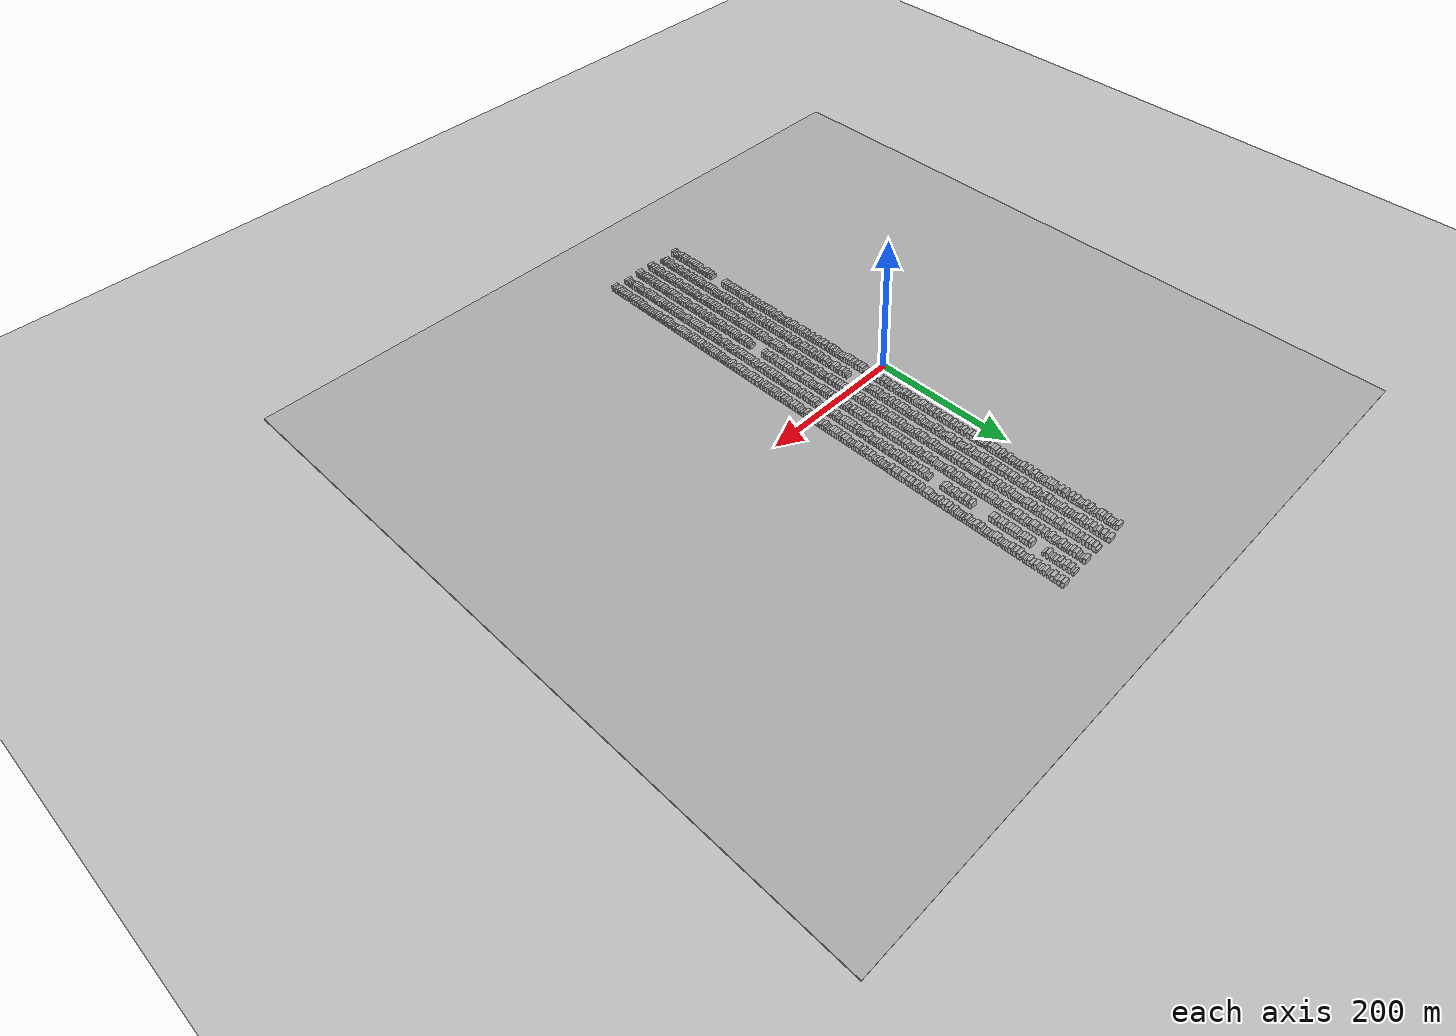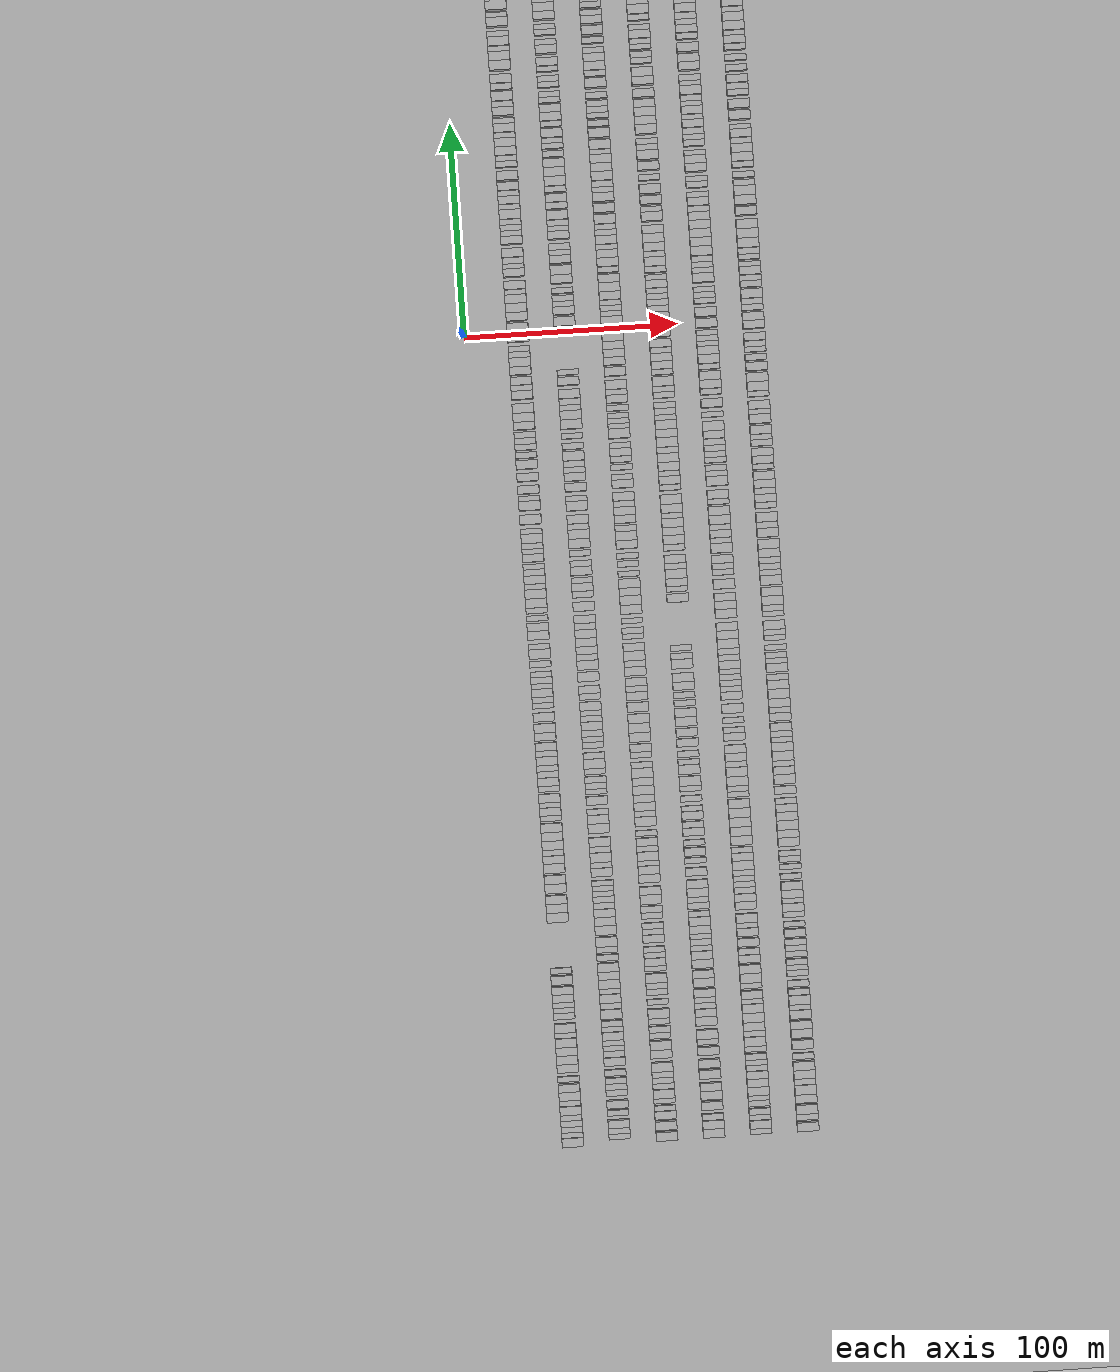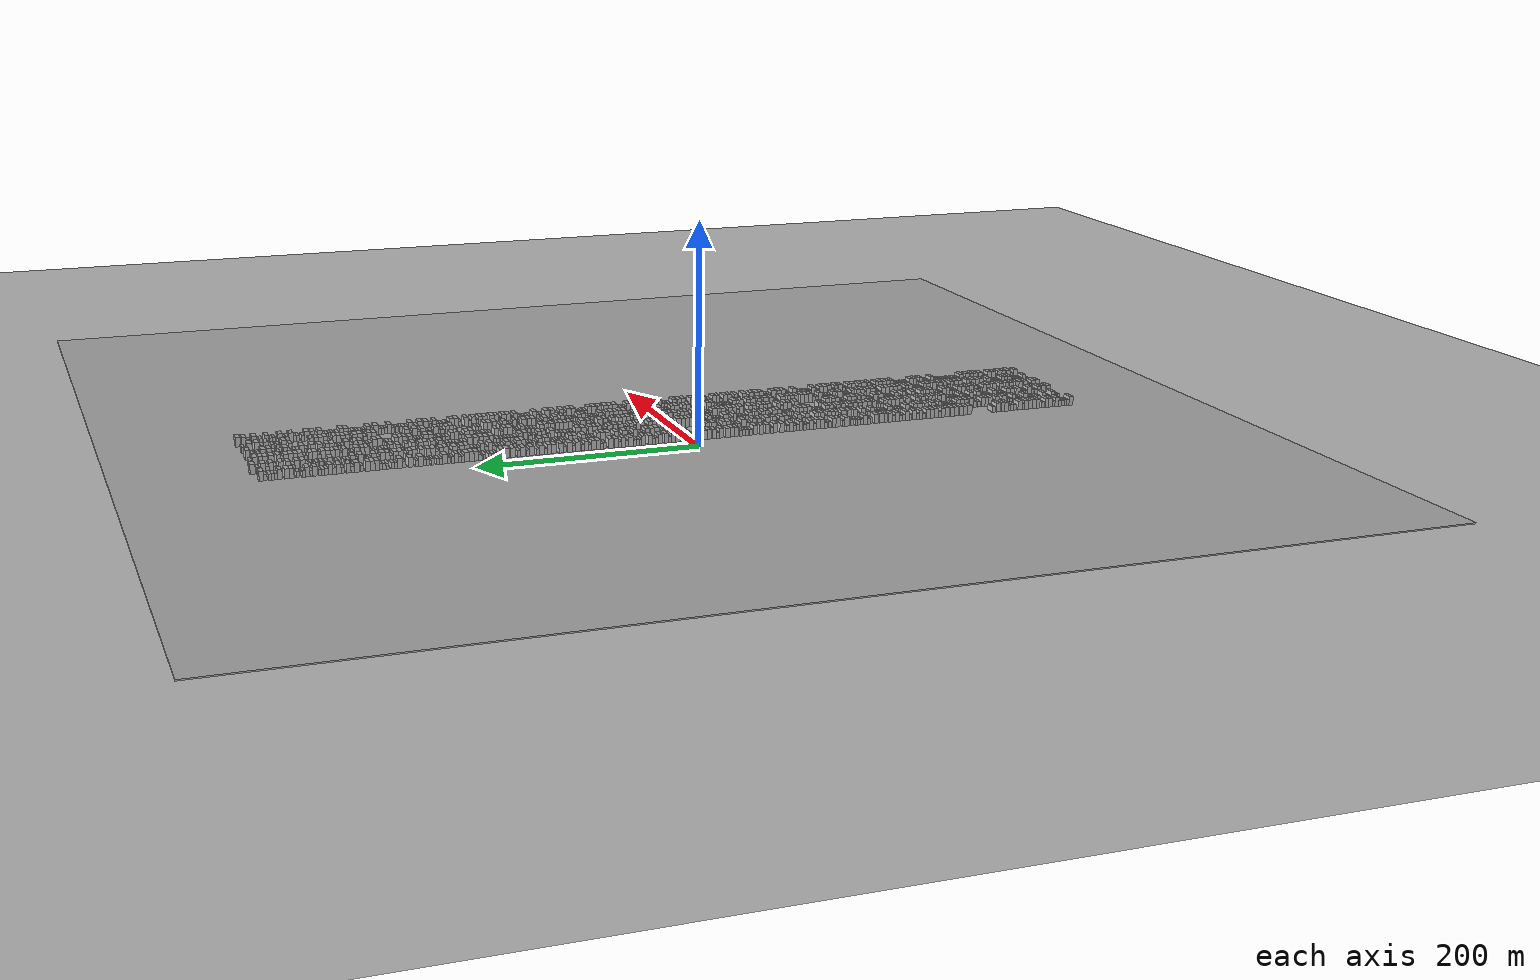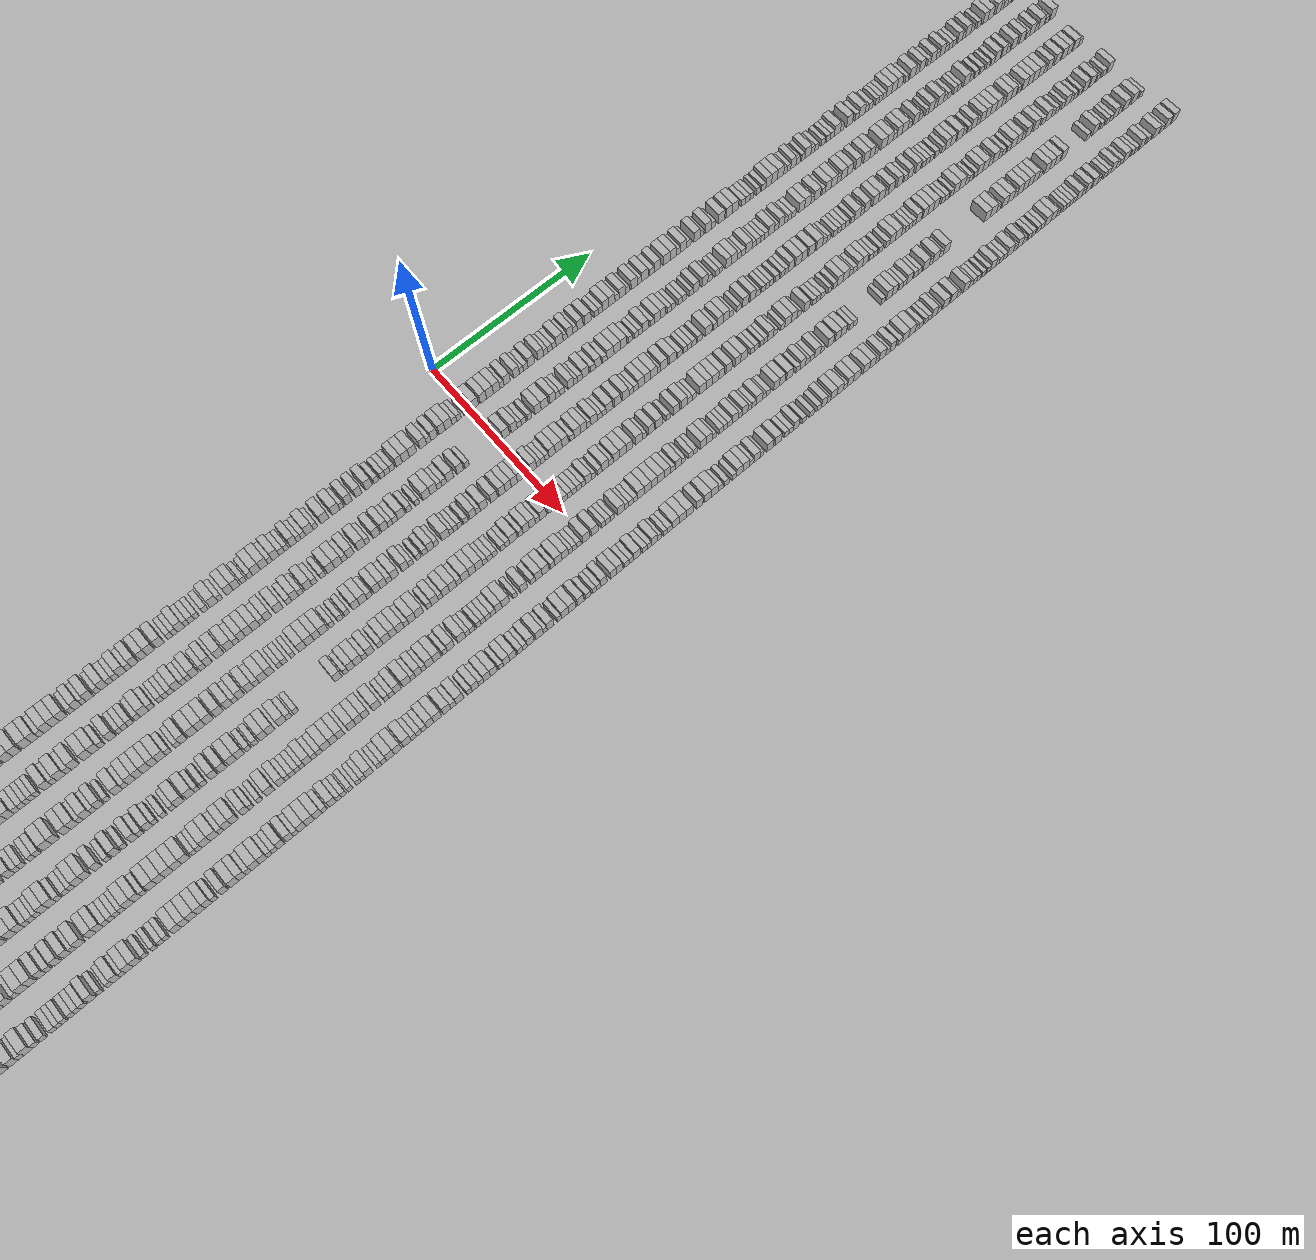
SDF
<?xml version="1.0" encoding="utf-8"?>

<sdf version="1.6">

   <world name="default">

      <gui fullscreen="0">

         <camera name="user_camera">

            <pose>-15 0 4.57585 0 0 0</pose>

            <view_controller>orbit</view_controller>

         </camera>

      </gui>

      <scene>

         <sky>

           <clouds>

             <speed>12</speed>

           </clouds>

         </sky>

         <ambient>0.4 0.4 0.4 1</ambient>

         <background>0.7 0.7 0.7 1</background>

         <shadows>1</shadows>

      </scene>

      <gravity>0 0 -9.8066</gravity>

      <magnetic_field>6e-06 2.3e-05 -4.2e-05</magnetic_field>

      <physics default="0" name="default_physics" type="ode">

         <ode>

            <solver>

               <type>quick</type>

               <iters>10</iters>

               <sor>1.0</sor>

               <use_dynamic_moi_rescaling>0</use_dynamic_moi_rescaling>

            </solver>

            <constraints>

               <cfm>0</cfm>

               <erp>0.2</erp>

               <contact_max_correcting_vel>100</contact_max_correcting_vel>

               <contact_surface_layer>0.001</contact_surface_layer>

            </constraints>

         </ode>

         <max_step_size>0.004</max_step_size>

         <real_time_factor>1</real_time_factor>

         <real_time_update_rate>250</real_time_update_rate>

      </physics>

      <light name="sun" type="directional">

         <cast_shadows>1</cast_shadows>

         <pose>0 0 10 0 0 0</pose>

         <diffuse>0.8 0.8 0.8 1</diffuse>

         <specular>0.2 0.2 0.2 1</specular>

         <attenuation>

            <range>1000</range>

            <constant>0.9</constant>

            <linear>0.01</linear>

            <quadratic>0.001</quadratic>

         </attenuation>

         <direction>-0.5 0.1 -0.9</direction>

      </light>

      <include>

         <name>ground_plane_1</name>

         <uri>model://HANNAS_ground_plane</uri>

         <pose>0 0 0  0 0 0</pose>

      </include>

      <include>

         <name>ground_plane_2</name>

         <uri>model://HANNAS_ground_plane</uri>

         <pose>100 0 0  0 0 0</pose>

      </include>

      <model name="building_1">

         <static>1</static>

         <pose frame="">25.0000 -377.9261 0 0.000000 0.000000 0.000000</pose>

         <link name="link">

            <pose frame="">0 0 4.50 0 0 0</pose>

            <collision name="collision">

               <geometry>

                  <box>

                     <size>10.0000 4.1477 9.0000</size>

                  </box>

               </geometry>

               <max_contacts>10</max_contacts>

               <surface>

                  <contact>

                     <ode/>

                  </contact>

                  <bounce/>

                  <friction>

                     <torsional>

                        <ode/>

                     </torsional>

                     <ode/>

                  </friction>

               </surface>

            </collision>

            <visual name="visual">

               <cast_shadows>0</cast_shadows>

               <geometry>

                  <box>

                     <size>10.0000 4.1477 9.0000</size>

                  </box>

               </geometry>

               <material>

                  <script>

                     <uri>model://HANNAS_wall/materials/scripts</uri>

                     <uri>model://HANNAS_wall/materials/textures</uri>

                     <name>vrc/HANNAS_wall</name>

                  </script>

               </material>

            </visual>

            <self_collide>0</self_collide>

            <enable_wind>0</enable_wind>

            <kinematic>0</kinematic>

         </link>

      </model>

      <model name="building_2">

         <static>1</static>

         <pose frame="">25.0000 -374.6442 0 0.000000 0.000000 0.000000</pose>

         <link name="link">

            <pose frame="">0 0 3.00 0 0 0</pose>

            <collision name="collision">

               <geometry>

                  <box>

                     <size>10.0000 2.4162 6.0000</size>

                  </box>

               </geometry>

               <max_contacts>10</max_contacts>

               <surface>

                  <contact>

                     <ode/>

                  </contact>

                  <bounce/>

                  <friction>

                     <torsional>

                        <ode/>

                     </torsional>

                     <ode/>

                  </friction>

               </surface>

            </collision>

            <visual name="visual">

               <cast_shadows>0</cast_shadows>

               <geometry>

                  <box>

                     <size>10.0000 2.4162 6.0000</size>

                  </box>

               </geometry>

               <material>

                  <script>

                     <uri>model://HANNAS_wall/materials/scripts</uri>

                     <uri>model://HANNAS_wall/materials/textures</uri>

                     <name>vrc/HANNAS_wall</name>

                  </script>

               </material>

            </visual>

            <self_collide>0</self_collide>

            <enable_wind>0</enable_wind>

            <kinematic>0</kinematic>

         </link>

      </model>

      <model name="building_3">

         <static>1</static>

         <pose frame="">25.0000 -372.1507 0 0.000000 0.000000 0.000000</pose>

         <link name="link">

            <pose frame="">0 0 3.00 0 0 0</pose>

            <collision name="collision">

               <geometry>

                  <box>

                     <size>10.0000 2.5707 6.0000</size>

                  </box>

               </geometry>

               <max_contacts>10</max_contacts>

               <surface>

                  <contact>

                     <ode/>

                  </contact>

                  <bounce/>

                  <friction>

                     <torsional>

                        <ode/>

                     </torsional>

                     <ode/>

                  </friction>

               </surface>

            </collision>

            <visual name="visual">

               <cast_shadows>0</cast_shadows>

               <geometry>

                  <box>

                     <size>10.0000 2.5707 6.0000</size>

                  </box>

               </geometry>

               <material>

                  <script>

                     <uri>model://HANNAS_wall/materials/scripts</uri>

                     <uri>model://HANNAS_wall/materials/textures</uri>

                     <name>vrc/HANNAS_wall</name>

                  </script>

               </material>

            </visual>

            <self_collide>0</self_collide>

            <enable_wind>0</enable_wind>

            <kinematic>0</kinematic>

         </link>

      </model>

      <model name="building_4">

         <static>1</static>

         <pose frame="">25.0000 -369.3969 0 0.000000 0.000000 0.000000</pose>

         <link name="link">

            <pose frame="">0 0 3.00 0 0 0</pose>

            <collision name="collision">

               <geometry>

                  <box>

                     <size>10.0000 2.9368 6.0000</size>

                  </box>

               </geometry>

               <max_contacts>10</max_contacts>

               <surface>

                  <contact>

                     <ode/>

                  </contact>

                  <bounce/>

                  <friction>

                     <torsional>

                        <ode/>

                     </torsional>

                     <ode/>

                  </friction>

               </surface>

            </collision>

            <visual name="visual">

               <cast_shadows>0</cast_shadows>

               <geometry>

                  <box>

                     <size>10.0000 2.9368 6.0000</size>

                  </box>

               </geometry>

               <material>

                  <script>

                     <uri>model://HANNAS_wall/materials/scripts</uri>

                     <uri>model://HANNAS_wall/materials/textures</uri>

                     <name>vrc/HANNAS_wall</name>

                  </script>

               </material>

            </visual>

            <self_collide>0</self_collide>

            <enable_wind>0</enable_wind>

            <kinematic>0</kinematic>

         </link>

      </model>

      <model name="building_5">

         <static>1</static>

         <pose frame="">25.0000 -366.5277 0 0.000000 0.000000 0.000000</pose>

         <link name="link">

            <pose frame="">0 0 3.00 0 0 0</pose>

            <collision name="collision">

               <geometry>

                  <box>

                     <size>10.0000 2.8017 6.0000</size>

                  </box>

               </geometry>

               <max_contacts>10</max_contacts>

               <surface>

                  <contact>

                     <ode/>

                  </contact>

                  <bounce/>

                  <friction>

                     <torsional>

                        <ode/>

                     </torsional>

                     <ode/>

                  </friction>

               </surface>

            </collision>

            <visual name="visual">

               <cast_shadows>0</cast_shadows>

               <geometry>

                  <box>

                     <size>10.0000 2.8017 6.0000</size>

                  </box>

               </geometry>

               <material>

                  <script>

                     <uri>model://HANNAS_wall/materials/scripts</uri>

                     <uri>model://HANNAS_wall/materials/textures</uri>

                     <name>vrc/HANNAS_wall</name>

                  </script>

               </material>

            </visual>

            <self_collide>0</self_collide>

            <enable_wind>0</enable_wind>

            <kinematic>0</kinematic>

         </link>

      </model>

      <model name="building_6">

         <static>1</static>

         <pose frame="">25.0000 -363.0962 0 0.000000 0.000000 0.000000</pose>

         <link name="link">

            <pose frame="">0 0 4.50 0 0 0</pose>

            <collision name="collision">

               <geometry>

                  <box>

                     <size>10.0000 4.0613 9.0000</size>

                  </box>

               </geometry>

               <max_contacts>10</max_contacts>

               <surface>

                  <contact>

                     <ode/>

                  </contact>

                  <bounce/>

                  <friction>

                     <torsional>

                        <ode/>

                     </torsional>

                     <ode/>

                  </friction>

               </surface>

            </collision>

            <visual name="visual">

               <cast_shadows>0</cast_shadows>

               <geometry>

                  <box>

                     <size>10.0000 4.0613 9.0000</size>

                  </box>

               </geometry>

               <material>

                  <script>

                     <uri>model://HANNAS_wall/materials/scripts</uri>

                     <uri>model://HANNAS_wall/materials/textures</uri>

                     <name>vrc/HANNAS_wall</name>

                  </script>

               </material>

            </visual>

            <self_collide>0</self_collide>

            <enable_wind>0</enable_wind>

            <kinematic>0</kinematic>

         </link>

      </model>

      <model name="building_7">

         <static>1</static>

         <pose frame="">25.0000 -359.6851 0 0.000000 0.000000 0.000000</pose>

         <link name="link">

            <pose frame="">0 0 3.00 0 0 0</pose>

            <collision name="collision">

               <geometry>

                  <box>

                     <size>10.0000 2.7610 6.0000</size>

                  </box>

               </geometry>

               <max_contacts>10</max_contacts>

               <surface>

                  <contact>

                     <ode/>

                  </contact>

                  <bounce/>

                  <friction>

                     <torsional>

                        <ode/>

                     </torsional>

                     <ode/>

                  </friction>

               </surface>

            </collision>

            <visual name="visual">

               <cast_shadows>0</cast_shadows>

               <geometry>

                  <box>

                     <size>10.0000 2.7610 6.0000</size>

                  </box>

               </geometry>

               <material>

                  <script>

                     <uri>model://HANNAS_wall/materials/scripts</uri>

                     <uri>model://HANNAS_wall/materials/textures</uri>

                     <name>vrc/HANNAS_wall</name>

                  </script>

               </material>

            </visual>

            <self_collide>0</self_collide>

            <enable_wind>0</enable_wind>

            <kinematic>0</kinematic>

         </link>

      </model>

      <model name="building_8">

         <static>1</static>

         <pose frame="">25.0000 -356.3516 0 0.000000 0.000000 0.000000</pose>

         <link name="link">

            <pose frame="">0 0 4.50 0 0 0</pose>

            <collision name="collision">

               <geometry>

                  <box>

                     <size>10.0000 3.9060 9.0000</size>

                  </box>

               </geometry>

               <max_contacts>10</max_contacts>

               <surface>

                  <contact>

                     <ode/>

                  </contact>

                  <bounce/>

                  <friction>

                     <torsional>

                        <ode/>

                     </torsional>

                     <ode/>

                  </friction>

               </surface>

            </collision>

            <visual name="visual">

               <cast_shadows>0</cast_shadows>

               <geometry>

                  <box>

                     <size>10.0000 3.9060 9.0000</size>

                  </box>

               </geometry>

               <material>

                  <script>

                     <uri>model://HANNAS_wall/materials/scripts</uri>

                     <uri>model://HANNAS_wall/materials/textures</uri>

                     <name>vrc/HANNAS_wall</name>

                  </script>

               </material>

            </visual>

            <self_collide>0</self_collide>

            <enable_wind>0</enable_wind>

            <kinematic>0</kinematic>

         </link>

      </model>

      <model name="building_9">

         <static>1</static>

         <pose frame="">25.0000 -352.5544 0 0.000000 0.000000 0.000000</pose>

         <link name="link">

            <pose frame="">0 0 4.50 0 0 0</pose>

            <collision name="collision">

               <geometry>

                  <box>

                     <size>10.0000 3.6885 9.0000</size>

                  </box>

               </geometry>

               <max_contacts>10</max_contacts>

               <surface>

                  <contact>

                     <ode/>

                  </contact>

                  <bounce/>

                  <friction>

                     <torsional>

                        <ode/>

                     </torsional>

                     <ode/>

                  </friction>

               </surface>

            </collision>

            <visual name="visual">

               <cast_shadows>0</cast_shadows>

               <geometry>

                  <box>

                     <size>10.0000 3.6885 9.0000</size>

                  </box>

               </geometry>

               <material>

                  <script>

                     <uri>model://HANNAS_wall/materials/scripts</uri>

                     <uri>model://HANNAS_wall/materials/textures</uri>

                     <name>vrc/HANNAS_wall</name>

                  </script>

               </material>

            </visual>

            <self_collide>0</self_collide>

            <enable_wind>0</enable_wind>

            <kinematic>0</kinematic>

         </link>

      </model>

      <model name="building_10">

         <static>1</static>

         <pose frame="">25.0000 -348.4630 0 0.000000 0.000000 0.000000</pose>

         <link name="link">

            <pose frame="">0 0 3.00 0 0 0</pose>

            <collision name="collision">

               <geometry>

                  <box>

                     <size>10.0000 2.4942 6.0000</size>

                  </box>

               </geometry>

               <max_contacts>10</max_contacts>

               <surface>

                  <contact>

                     <ode/>

                  </contact>

                  <bounce/>

                  <friction>

                     <torsional>

                        <ode/>

                     </torsional>

                     <ode/>

                  </friction>

               </surface>

            </collision>

            <visual name="visual">

               <cast_shadows>0</cast_shadows>

               <geometry>

                  <box>

                     <size>10.0000 2.4942 6.0000</size>

                  </box>

               </geometry>

               <material>

                  <script>

                     <uri>model://HANNAS_wall/materials/scripts</uri>

                     <uri>model://HANNAS_wall/materials/textures</uri>

                     <name>vrc/HANNAS_wall</name>

                  </script>

               </material>

            </visual>

            <self_collide>0</self_collide>

            <enable_wind>0</enable_wind>

            <kinematic>0</kinematic>

         </link>

      </model>

      <model name="building_11">

         <static>1</static>

         <pose frame="">25.0000 -343.3061 0 0.000000 0.000000 0.000000</pose>

         <link name="link">

            <pose frame="">0 0 4.50 0 0 0</pose>

            <collision name="collision">

               <geometry>

                  <box>

                     <size>10.0000 3.8197 9.0000</size>

                  </box>

               </geometry>

               <max_contacts>10</max_contacts>

               <surface>

                  <contact>

                     <ode/>

                  </contact>

                  <bounce/>

                  <friction>

                     <torsional>

                        <ode/>

                     </torsional>

                     <ode/>

                  </friction>

               </surface>

            </collision>

            <visual name="visual">

               <cast_shadows>0</cast_shadows>

               <geometry>

                  <box>

                     <size>10.0000 3.8197 9.0000</size>

                  </box>

               </geometry>

               <material>

                  <script>

                     <uri>model://HANNAS_wall/materials/scripts</uri>

                     <uri>model://HANNAS_wall/materials/textures</uri>

                     <name>vrc/HANNAS_wall</name>

                  </script>

               </material>

            </visual>

            <self_collide>0</self_collide>

            <enable_wind>0</enable_wind>

            <kinematic>0</kinematic>

         </link>

      </model>

      <model name="building_12">

         <static>1</static>

         <pose frame="">25.0000 -339.3847 0 0.000000 0.000000 0.000000</pose>

         <link name="link">

            <pose frame="">0 0 4.50 0 0 0</pose>

            <collision name="collision">

               <geometry>

                  <box>

                     <size>10.0000 4.0230 9.0000</size>

                  </box>

               </geometry>

               <max_contacts>10</max_contacts>

               <surface>

                  <contact>

                     <ode/>

                  </contact>

                  <bounce/>

                  <friction>

                     <torsional>

                        <ode/>

                     </torsional>

                     <ode/>

                  </friction>

               </surface>

            </collision>

            <visual name="visual">

               <cast_shadows>0</cast_shadows>

               <geometry>

                  <box>

                     <size>10.0000 4.0230 9.0000</size>

                  </box>

               </geometry>

               <material>

                  <script>

                     <uri>model://HANNAS_wall/materials/scripts</uri>

                     <uri>model://HANNAS_wall/materials/textures</uri>

                     <name>vrc/HANNAS_wall</name>

                  </script>

               </material>

            </visual>

            <self_collide>0</self_collide>

            <enable_wind>0</enable_wind>

            <kinematic>0</kinematic>

         </link>

      </model>

      <model name="building_13">

         <static>1</static>

         <pose frame="">25.0000 -335.4382 0 0.000000 0.000000 0.000000</pose>

         <link name="link">

            <pose frame="">0 0 4.50 0 0 0</pose>

            <collision name="collision">

               <geometry>

                  <box>

                     <size>10.0000 3.8700 9.0000</size>

                  </box>

               </geometry>

               <max_contacts>10</max_contacts>

               <surface>

                  <contact>

                     <ode/>

                  </contact>

                  <bounce/>

                  <friction>

                     <torsional>

                        <ode/>

                     </torsional>

                     <ode/>

                  </friction>

               </surface>

            </collision>

            <visual name="visual">

               <cast_shadows>0</cast_shadows>

               <geometry>

                  <box>

                     <size>10.0000 3.8700 9.0000</size>

                  </box>

               </geometry>

               <material>

                  <script>

                     <uri>model://HANNAS_wall/materials/scripts</uri>

                     <uri>model://HANNAS_wall/materials/textures</uri>

                     <name>vrc/HANNAS_wall</name>

                  </script>

               </material>

            </visual>

            <self_collide>0</self_collide>

            <enable_wind>0</enable_wind>

            <kinematic>0</kinematic>

         </link>

      </model>

      <model name="building_14">

         <static>1</static>

         <pose frame="">25.0000 -331.4077 0 0.000000 0.000000 0.000000</pose>

         <link name="link">

            <pose frame="">0 0 4.50 0 0 0</pose>

            <collision name="collision">

               <geometry>

                  <box>

                     <size>10.0000 4.1910 9.0000</size>

                  </box>

               </geometry>

               <max_contacts>10</max_contacts>

               <surface>

                  <contact>

                     <ode/>

                  </contact>

                  <bounce/>

                  <friction>

                     <torsional>

                        <ode/>

                     </torsional>

                     <ode/>

                  </friction>

               </surface>

            </collision>

            <visual name="visual">

               <cast_shadows>0</cast_shadows>

               <geometry>

                  <box>

                     <size>10.0000 4.1910 9.0000</size>

                  </box>

               </geometry>

               <material>

                  <script>

                     <uri>model://HANNAS_wall/materials/scripts</uri>

                     <uri>model://HANNAS_wall/materials/textures</uri>

                     <name>vrc/HANNAS_wall</name>

                  </script>

               </material>

            </visual>

            <self_collide>0</self_collide>

            <enable_wind>0</enable_wind>

            <kinematic>0</kinematic>

         </link>

      </model>

      <model name="building_15">

         <static>1</static>

         <pose frame="">25.0000 -328.0107 0 0.000000 0.000000 0.000000</pose>

         <link name="link">

            <pose frame="">0 0 3.00 0 0 0</pose>

            <collision name="collision">

               <geometry>

                  <box>

                     <size>10.0000 2.6029 6.0000</size>

                  </box>

               </geometry>

               <max_contacts>10</max_contacts>

               <surface>

                  <contact>

                     <ode/>

                  </contact>

                  <bounce/>

                  <friction>

                     <torsional>

                        <ode/>

                     </torsional>

                     <ode/>

                  </friction>

               </surface>

            </collision>

            <visual name="visual">

               <cast_shadows>0</cast_shadows>

               <geometry>

                  <box>

                     <size>10.0000 2.6029 6.0000</size>

                  </box>

               </geometry>

               <material>

                  <script>

                     <uri>model://HANNAS_wall/materials/scripts</uri>

                     <uri>model://HANNAS_wall/materials/textures</uri>

                     <name>vrc/HANNAS_wall</name>

                  </script>

               </material>

            </visual>

            <self_collide>0</self_collide>

            <enable_wind>0</enable_wind>

            <kinematic>0</kinematic>

         </link>

      </model>

      <model name="building_16">

         <static>1</static>

         <pose frame="">25.0000 -324.5977 0 0.000000 0.000000 0.000000</pose>

         <link name="link">

            <pose frame="">0 0 4.50 0 0 0</pose>

            <collision name="collision">

               <geometry>

                  <box>

                     <size>10.0000 4.2232 9.0000</size>

                  </box>

               </geometry>

               <max_contacts>10</max_contacts>

               <surface>

                  <contact>

                     <ode/>

                  </contact>

                  <bounce/>

                  <friction>

                     <torsional>

                        <ode/>

                     </torsional>

                     <ode/>

                  </friction>

               </surface>

            </collision>

            <visual name="visual">

               <cast_shadows>0</cast_shadows>

               <geometry>

                  <box>

                     <size>10.0000 4.2232 9.0000</size>

                  </box>

               </geometry>

               <material>

                  <script>

                     <uri>model://HANNAS_wall/materials/scripts</uri>

                     <uri>model://HANNAS_wall/materials/textures</uri>

                     <name>vrc/HANNAS_wall</name>

                  </script>

               </material>

            </visual>

            <self_collide>0</self_collide>

            <enable_wind>0</enable_wind>

            <kinematic>0</kinematic>

         </link>

      </model>

      <model name="building_17">

         <static>1</static>

         <pose frame="">25.0000 -319.0273 0 0.000000 0.000000 0.000000</pose>

         <link name="link">

            <pose frame="">0 0 3.00 0 0 0</pose>

            <collision name="collision">

               <geometry>

                  <box>

                     <size>10.0000 2.9176 6.0000</size>

                  </box>

               </geometry>

               <max_contacts>10</max_contacts>

               <surface>

                  <contact>

                     <ode/>

                  </contact>

                  <bounce/>

                  <friction>

                     <torsional>

                        <ode/>

                     </torsional>

                     <ode/>

                  </friction>

               </surface>

            </collision>

            <visual name="visual">

               <cast_shadows>0</cast_shadows>

               <geometry>

                  <box>

                     <size>10.0000 2.9176 6.0000</size>

                  </box>

               </geometry>

               <material>

                  <script>

                     <uri>model://HANNAS_wall/materials/scripts</uri>

                     <uri>model://HANNAS_wall/materials/textures</uri>

                     <name>vrc/HANNAS_wall</name>

                  </script>

               </material>

            </visual>

            <self_collide>0</self_collide>

            <enable_wind>0</enable_wind>

            <kinematic>0</kinematic>

         </link>

      </model>

      <model name="building_18">

         <static>1</static>

         <pose frame="">25.0000 -316.3406 0 0.000000 0.000000 0.000000</pose>

         <link name="link">

            <pose frame="">0 0 3.00 0 0 0</pose>

            <collision name="collision">

               <geometry>

                  <box>

                     <size>10.0000 2.4557 6.0000</size>

                  </box>

               </geometry>

               <max_contacts>10</max_contacts>

               <surface>

                  <contact>

                     <ode/>

                  </contact>

                  <bounce/>

                  <friction>

                     <torsional>

                        <ode/>

                     </torsional>

                     <ode/>

                  </friction>

               </surface>

            </collision>

            <visual name="visual">

               <cast_shadows>0</cast_shadows>

               <geometry>

                  <box>

                     <size>10.0000 2.4557 6.0000</size>

                  </box>

               </geometry>

               <material>

                  <script>

                     <uri>model://HANNAS_wall/materials/scripts</uri>

                     <uri>model://HANNAS_wall/materials/textures</uri>

                     <name>vrc/HANNAS_wall</name>

                  </script>

               </material>

            </visual>

            <self_collide>0</self_collide>

            <enable_wind>0</enable_wind>

            <kinematic>0</kinematic>

         </link>

      </model>

      <model name="building_19">

         <static>1</static>

         <pose frame="">25.0000 -313.8000 0 0.000000 0.000000 0.000000</pose>

         <link name="link">

            <pose frame="">0 0 3.00 0 0 0</pose>

            <collision name="collision">

               <geometry>

                  <box>

                     <size>10.0000 2.6254 6.0000</size>

                  </box>

               </geometry>

               <max_contacts>10</max_contacts>

               <surface>

                  <contact>

                     <ode/>

                  </contact>

                  <bounce/>

                  <friction>

                     <torsional>

                        <ode/>

                     </torsional>

                     <ode/>

                  </friction>

               </surface>

            </collision>

            <visual name="visual">

               <cast_shadows>0</cast_shadows>

               <geometry>

                  <box>

                     <size>10.0000 2.6254 6.0000</size>

                  </box>

               </geometry>

               <material>

                  <script>

                     <uri>model://HANNAS_wall/materials/scripts</uri>

                     <uri>model://HANNAS_wall/materials/textures</uri>

                     <name>vrc/HANNAS_wall</name>

                  </script>

               </material>

            </visual>

            <self_collide>0</self_collide>

            <enable_wind>0</enable_wind>

            <kinematic>0</kinematic>

         </link>

      </model>

      <model name="building_20">

         <static>1</static>

         <pose frame="">25.0000 -310.6484 0 0.000000 0.000000 0.000000</pose>

         <link name="link">

            <pose frame="">0 0 4.50 0 0 0</pose>

            <collision name="collision">

               <geometry>

                  <box>

                     <size>10.0000 3.6779 9.0000</size>

                  </box>

               </geometry>

               <max_contacts>10</max_contacts>

               <surface>

                  <contact>

                     <ode/>

                  </contact>

                  <bounce/>

                  <friction>

                     <torsional>

                        <ode/>

                     </torsional>

                     <ode/>

                  </friction>

               </surface>

            </collision>

            <visual name="visual">

               <cast_shadows>0</cast_shadows>

               <geometry>

                  <box>

                     <size>10.0000 3.6779 9.0000</size>

                  </box>

               </geometry>

               <material>

                  <script>

                     <uri>model://HANNAS_wall/materials/scripts</uri>

                     <uri>model://HANNAS_wall/materials/textures</uri>

                     <name>vrc/HANNAS_wall</name>

                  </script>

               </material>

            </visual>

            <self_collide>0</self_collide>

            <enable_wind>0</enable_wind>

            <kinematic>0</kinematic>

         </link>

      </model>

      <model name="building_21">

         <static>1</static>

         <pose frame="">25.0000 -306.9935 0 0.000000 0.000000 0.000000</pose>

         <link name="link">

            <pose frame="">0 0 4.50 0 0 0</pose>

            <collision name="collision">

               <geometry>

                  <box>

                     <size>10.0000 3.6319 9.0000</size>

                  </box>

               </geometry>

               <max_contacts>10</max_contacts>

               <surface>

                  <contact>

                     <ode/>

                  </contact>

                  <bounce/>

                  <friction>

                     <torsional>

                        <ode/>

                     </torsional>

                     <ode/>

                  </friction>

               </surface>

            </collision>

            <visual name="visual">

               <cast_shadows>0</cast_shadows>

               <geometry>

                  <box>

                     <size>10.0000 3.6319 9.0000</size>

                  </box>

               </geometry>

               <material>

                  <script>

                     <uri>model://HANNAS_wall/materials/scripts</uri>

                     <uri>model://HANNAS_wall/materials/textures</uri>

                     <name>vrc/HANNAS_wall</name>

                  </script>

               </material>

            </visual>

            <self_collide>0</self_collide>

            <enable_wind>0</enable_wind>

            <kinematic>0</kinematic>

         </link>

      </model>

      <model name="building_22">

         <static>1</static>

         <pose frame="">25.0000 -302.1401 0 0.000000 0.000000 0.000000</pose>

         <link name="link">

            <pose frame="">0 0 4.50 0 0 0</pose>

            <collision name="collision">

               <geometry>

                  <box>

                     <size>10.0000 4.0750 9.0000</size>

                  </box>

               </geometry>

               <max_contacts>10</max_contacts>

               <surface>

                  <contact>

                     <ode/>

                  </contact>

                  <bounce/>

                  <friction>

                     <torsional>

                        <ode/>

                     </torsional>

                     <ode/>

                  </friction>

               </surface>

            </collision>

            <visual name="visual">

               <cast_shadows>0</cast_shadows>

               <geometry>

                  <box>

                     <size>10.0000 4.0750 9.0000</size>

                  </box>

               </geometry>

               <material>

                  <script>

                     <uri>model://HANNAS_wall/materials/scripts</uri>

                     <uri>model://HANNAS_wall/materials/textures</uri>

                     <name>vrc/HANNAS_wall</name>

                  </script>

               </material>

            </visual>

            <self_collide>0</self_collide>

            <enable_wind>0</enable_wind>

            <kinematic>0</kinematic>

         </link>

      </model>

      <model name="building_23">

         <static>1</static>

         <pose frame="">25.0000 -297.7972 0 0.000000 0.000000 0.000000</pose>

         <link name="link">

            <pose frame="">0 0 3.00 0 0 0</pose>

            <collision name="collision">

               <geometry>

                  <box>

                     <size>10.0000 2.6108 6.0000</size>

                  </box>

               </geometry>

               <max_contacts>10</max_contacts>

               <surface>

                  <contact>

                     <ode/>

                  </contact>

                  <bounce/>

                  <friction>

                     <torsional>

                        <ode/>

                     </torsional>

                     <ode/>

                  </friction>

               </surface>

            </collision>

            <visual name="visual">

               <cast_shadows>0</cast_shadows>

               <geometry>

                  <box>

                     <size>10.0000 2.6108 6.0000</size>

                  </box>

               </geometry>

               <material>

                  <script>

                     <uri>model://HANNAS_wall/materials/scripts</uri>

                     <uri>model://HANNAS_wall/materials/textures</uri>

                     <name>vrc/HANNAS_wall</name>

                  </script>

               </material>

            </visual>

            <self_collide>0</self_collide>

            <enable_wind>0</enable_wind>

            <kinematic>0</kinematic>

         </link>

      </model>

      <model name="building_24">

         <static>1</static>

         <pose frame="">25.0000 -272.8381 0 0.000000 0.000000 0.000000</pose>

         <link name="link">

            <pose frame="">0 0 4.50 0 0 0</pose>

            <collision name="collision">

               <geometry>

                  <box>

                     <size>10.0000 4.4358 9.0000</size>

                  </box>

               </geometry>

               <max_contacts>10</max_contacts>

               <surface>

                  <contact>

                     <ode/>

                  </contact>

                  <bounce/>

                  <friction>

                     <torsional>

                        <ode/>

                     </torsional>

                     <ode/>

                  </friction>

               </surface>

            </collision>

            <visual name="visual">

               <cast_shadows>0</cast_shadows>

               <geometry>

                  <box>

                     <size>10.0000 4.4358 9.0000</size>

                  </box>

               </geometry>

               <material>

                  <script>

                     <uri>model://HANNAS_wall/materials/scripts</uri>

                     <uri>model://HANNAS_wall/materials/textures</uri>

                     <name>vrc/HANNAS_wall</name>

                  </script>

               </material>

            </visual>

            <self_collide>0</self_collide>

            <enable_wind>0</enable_wind>

            <kinematic>0</kinematic>

         </link>

      </model>

      <model name="building_25">

         <static>1</static>

         <pose frame="">25.0000 -268.5640 0 0.000000 0.000000 0.000000</pose>

         <link name="link">

            <pose frame="">0 0 4.50 0 0 0</pose>

            <collision name="collision">

               <geometry>

                  <box>

                     <size>10.0000 4.1124 9.0000</size>

                  </box>

               </geometry>

               <max_contacts>10</max_contacts>

               <surface>

                  <contact>

                     <ode/>

                  </contact>

                  <bounce/>

                  <friction>

                     <torsional>

                        <ode/>

                     </torsional>

                     <ode/>

                  </friction>

               </surface>

            </collision>

            <visual name="visual">

               <cast_shadows>0</cast_shadows>

               <geometry>

                  <box>

                     <size>10.0000 4.1124 9.0000</size>

                  </box>

               </geometry>

               <material>

                  <script>

                     <uri>model://HANNAS_wall/materials/scripts</uri>

                     <uri>model://HANNAS_wall/materials/textures</uri>

                     <name>vrc/HANNAS_wall</name>

                  </script>

               </material>

            </visual>

            <self_collide>0</self_collide>

            <enable_wind>0</enable_wind>

            <kinematic>0</kinematic>

         </link>

      </model>

      <model name="building_26">

         <static>1</static>

         <pose frame="">25.0000 -264.4887 0 0.000000 0.000000 0.000000</pose>

         <link name="link">

            <pose frame="">0 0 4.50 0 0 0</pose>

            <collision name="collision">

               <geometry>

                  <box>

                     <size>10.0000 4.0382 9.0000</size>

                  </box>

               </geometry>

               <max_contacts>10</max_contacts>

               <surface>

                  <contact>

                     <ode/>

                  </contact>

                  <bounce/>

                  <friction>

                     <torsional>

                        <ode/>

                     </torsional>

                     <ode/>

                  </friction>

               </surface>

            </collision>

            <visual name="visual">

               <cast_shadows>0</cast_shadows>

               <geometry>

                  <box>

                     <size>10.0000 4.0382 9.0000</size>

                  </box>

               </geometry>

               <material>

                  <script>

                     <uri>model://HANNAS_wall/materials/scripts</uri>

                     <uri>model://HANNAS_wall/materials/textures</uri>

                     <name>vrc/HANNAS_wall</name>

                  </script>

               </material>

            </visual>

            <self_collide>0</self_collide>

            <enable_wind>0</enable_wind>

            <kinematic>0</kinematic>

         </link>

      </model>

      <model name="building_27">

         <static>1</static>

         <pose frame="">25.0000 -259.3070 0 0.000000 0.000000 0.000000</pose>

         <link name="link">

            <pose frame="">0 0 4.50 0 0 0</pose>

            <collision name="collision">

               <geometry>

                  <box>

                     <size>10.0000 4.3252 9.0000</size>

                  </box>

               </geometry>

               <max_contacts>10</max_contacts>

               <surface>

                  <contact>

                     <ode/>

                  </contact>

                  <bounce/>

                  <friction>

                     <torsional>

                        <ode/>

                     </torsional>

                     <ode/>

                  </friction>

               </surface>

            </collision>

            <visual name="visual">

               <cast_shadows>0</cast_shadows>

               <geometry>

                  <box>

                     <size>10.0000 4.3252 9.0000</size>

                  </box>

               </geometry>

               <material>

                  <script>

                     <uri>model://HANNAS_wall/materials/scripts</uri>

                     <uri>model://HANNAS_wall/materials/textures</uri>

                     <name>vrc/HANNAS_wall</name>

                  </script>

               </material>

            </visual>

            <self_collide>0</self_collide>

            <enable_wind>0</enable_wind>

            <kinematic>0</kinematic>

         </link>

      </model>

      <model name="building_28">

         <static>1</static>

         <pose frame="">25.0000 -255.1057 0 0.000000 0.000000 0.000000</pose>

         <link name="link">

            <pose frame="">0 0 4.50 0 0 0</pose>

            <collision name="collision">

               <geometry>

                  <box>

                     <size>10.0000 4.0774 9.0000</size>

                  </box>

               </geometry>

               <max_contacts>10</max_contacts>

               <surface>

                  <contact>

                     <ode/>

                  </contact>

                  <bounce/>

                  <friction>

                     <torsional>

                        <ode/>

                     </torsional>

                     <ode/>

                  </friction>

               </surface>

            </collision>

            <visual name="visual">

               <cast_shadows>0</cast_shadows>

               <geometry>

                  <box>

                     <size>10.0000 4.0774 9.0000</size>

                  </box>

               </geometry>

               <material>

                  <script>

                     <uri>model://HANNAS_wall/materials/scripts</uri>

                     <uri>model://HANNAS_wall/materials/textures</uri>

                     <name>vrc/HANNAS_wall</name>

                  </script>

               </material>

            </visual>

            <self_collide>0</self_collide>

            <enable_wind>0</enable_wind>

            <kinematic>0</kinematic>

         </link>

      </model>

      <model name="building_29">

         <static>1</static>

         <pose frame="">25.0000 -249.8453 0 0.000000 0.000000 0.000000</pose>

         <link name="link">

            <pose frame="">0 0 4.50 0 0 0</pose>

            <collision name="collision">

               <geometry>

                  <box>

                     <size>10.0000 4.4433 9.0000</size>

                  </box>

               </geometry>

               <max_contacts>10</max_contacts>

               <surface>

                  <contact>

                     <ode/>

                  </contact>

                  <bounce/>

                  <friction>

                     <torsional>

                        <ode/>

                     </torsional>

                     <ode/>

                  </friction>

               </surface>

            </collision>

            <visual name="visual">

               <cast_shadows>0</cast_shadows>

               <geometry>

                  <box>

                     <size>10.0000 4.4433 9.0000</size>

                  </box>

               </geometry>

               <material>

                  <script>

                     <uri>model://HANNAS_wall/materials/scripts</uri>

                     <uri>model://HANNAS_wall/materials/textures</uri>

                     <name>vrc/HANNAS_wall</name>

                  </script>

               </material>

            </visual>

            <self_collide>0</self_collide>

            <enable_wind>0</enable_wind>

            <kinematic>0</kinematic>

         </link>

      </model>

      <model name="building_30">

         <static>1</static>

         <pose frame="">25.0000 -245.7950 0 0.000000 0.000000 0.000000</pose>

         <link name="link">

            <pose frame="">0 0 4.50 0 0 0</pose>

            <collision name="collision">

               <geometry>

                  <box>

                     <size>10.0000 3.6573 9.0000</size>

                  </box>

               </geometry>

               <max_contacts>10</max_contacts>

               <surface>

                  <contact>

                     <ode/>

                  </contact>

                  <bounce/>

                  <friction>

                     <torsional>

                        <ode/>

                     </torsional>

                     <ode/>

                  </friction>

               </surface>

            </collision>

            <visual name="visual">

               <cast_shadows>0</cast_shadows>

               <geometry>

                  <box>

                     <size>10.0000 3.6573 9.0000</size>

                  </box>

               </geometry>

               <material>

                  <script>

                     <uri>model://HANNAS_wall/materials/scripts</uri>

                     <uri>model://HANNAS_wall/materials/textures</uri>

                     <name>vrc/HANNAS_wall</name>

                  </script>

               </material>

            </visual>

            <self_collide>0</self_collide>

            <enable_wind>0</enable_wind>

            <kinematic>0</kinematic>

         </link>

      </model>

      <model name="building_31">

         <static>1</static>

         <pose frame="">25.0000 -242.5853 0 0.000000 0.000000 0.000000</pose>

         <link name="link">

            <pose frame="">0 0 3.00 0 0 0</pose>

            <collision name="collision">

               <geometry>

                  <box>

                     <size>10.0000 2.7622 6.0000</size>

                  </box>

               </geometry>

               <max_contacts>10</max_contacts>

               <surface>

                  <contact>

                     <ode/>

                  </contact>

                  <bounce/>

                  <friction>

                     <torsional>

                        <ode/>

                     </torsional>

                     <ode/>

                  </friction>

               </surface>

            </collision>

            <visual name="visual">

               <cast_shadows>0</cast_shadows>

               <geometry>

                  <box>

                     <size>10.0000 2.7622 6.0000</size>

                  </box>

               </geometry>

               <material>

                  <script>

                     <uri>model://HANNAS_wall/materials/scripts</uri>

                     <uri>model://HANNAS_wall/materials/textures</uri>

                     <name>vrc/HANNAS_wall</name>

                  </script>

               </material>

            </visual>

            <self_collide>0</self_collide>

            <enable_wind>0</enable_wind>

            <kinematic>0</kinematic>

         </link>

      </model>

      <model name="building_32">

         <static>1</static>

         <pose frame="">25.0000 -239.1436 0 0.000000 0.000000 0.000000</pose>

         <link name="link">

            <pose frame="">0 0 4.50 0 0 0</pose>

            <collision name="collision">

               <geometry>

                  <box>

                     <size>10.0000 4.1211 9.0000</size>

                  </box>

               </geometry>

               <max_contacts>10</max_contacts>

               <surface>

                  <contact>

                     <ode/>

                  </contact>

                  <bounce/>

                  <friction>

                     <torsional>

                        <ode/>

                     </torsional>

                     <ode/>

                  </friction>

               </surface>

            </collision>

            <visual name="visual">

               <cast_shadows>0</cast_shadows>

               <geometry>

                  <box>

                     <size>10.0000 4.1211 9.0000</size>

                  </box>

               </geometry>

               <material>

                  <script>

                     <uri>model://HANNAS_wall/materials/scripts</uri>

                     <uri>model://HANNAS_wall/materials/textures</uri>

                     <name>vrc/HANNAS_wall</name>

                  </script>

               </material>

            </visual>

            <self_collide>0</self_collide>

            <enable_wind>0</enable_wind>

            <kinematic>0</kinematic>

         </link>

      </model>

      <model name="building_33">

         <static>1</static>

         <pose frame="">25.0000 -235.0254 0 0.000000 0.000000 0.000000</pose>

         <link name="link">

            <pose frame="">0 0 4.50 0 0 0</pose>

            <collision name="collision">

               <geometry>

                  <box>

                     <size>10.0000 4.1152 9.0000</size>

                  </box>

               </geometry>

               <max_contacts>10</max_contacts>

               <surface>

                  <contact>

                     <ode/>

                  </contact>

                  <bounce/>

                  <friction>

                     <torsional>

                        <ode/>

                     </torsional>

                     <ode/>

                  </friction>

               </surface>

            </collision>

            <visual name="visual">

               <cast_shadows>0</cast_shadows>

               <geometry>

                  <box>

                     <size>10.0000 4.1152 9.0000</size>

                  </box>

               </geometry>

               <material>

                  <script>

                     <uri>model://HANNAS_wall/materials/scripts</uri>

                     <uri>model://HANNAS_wall/materials/textures</uri>

                     <name>vrc/HANNAS_wall</name>

                  </script>

               </material>

            </visual>

            <self_collide>0</self_collide>

            <enable_wind>0</enable_wind>

            <kinematic>0</kinematic>

         </link>

      </model>

      <model name="building_34">

         <static>1</static>

         <pose frame="">25.0000 -230.9001 0 0.000000 0.000000 0.000000</pose>

         <link name="link">

            <pose frame="">0 0 4.50 0 0 0</pose>

            <collision name="collision">

               <geometry>

                  <box>

                     <size>10.0000 4.1354 9.0000</size>

                  </box>

               </geometry>

               <max_contacts>10</max_contacts>

               <surface>

                  <contact>

                     <ode/>

                  </contact>

                  <bounce/>

                  <friction>

                     <torsional>

                        <ode/>

                     </torsional>

                     <ode/>

                  </friction>

               </surface>

            </collision>

            <visual name="visual">

               <cast_shadows>0</cast_shadows>

               <geometry>

                  <box>

                     <size>10.0000 4.1354 9.0000</size>

                  </box>

               </geometry>

               <material>

                  <script>

                     <uri>model://HANNAS_wall/materials/scripts</uri>

                     <uri>model://HANNAS_wall/materials/textures</uri>

                     <name>vrc/HANNAS_wall</name>

                  </script>

               </material>

            </visual>

            <self_collide>0</self_collide>

            <enable_wind>0</enable_wind>

            <kinematic>0</kinematic>

         </link>

      </model>

      <model name="building_35">

         <static>1</static>

         <pose frame="">25.0000 -226.4916 0 0.000000 0.000000 0.000000</pose>

         <link name="link">

            <pose frame="">0 0 3.00 0 0 0</pose>

            <collision name="collision">

               <geometry>

                  <box>

                     <size>10.0000 2.6815 6.0000</size>

                  </box>

               </geometry>

               <max_contacts>10</max_contacts>

               <surface>

                  <contact>

                     <ode/>

                  </contact>

                  <bounce/>

                  <friction>

                     <torsional>

                        <ode/>

                     </torsional>

                     <ode/>

                  </friction>

               </surface>

            </collision>

            <visual name="visual">

               <cast_shadows>0</cast_shadows>

               <geometry>

                  <box>

                     <size>10.0000 2.6815 6.0000</size>

                  </box>

               </geometry>

               <material>

                  <script>

                     <uri>model://HANNAS_wall/materials/scripts</uri>

                     <uri>model://HANNAS_wall/materials/textures</uri>

                     <name>vrc/HANNAS_wall</name>

                  </script>

               </material>

            </visual>

            <self_collide>0</self_collide>

            <enable_wind>0</enable_wind>

            <kinematic>0</kinematic>

         </link>

      </model>

      <model name="building_36">

         <static>1</static>

         <pose frame="">25.0000 -223.3160 0 0.000000 0.000000 0.000000</pose>

         <link name="link">

            <pose frame="">0 0 4.50 0 0 0</pose>

            <collision name="collision">

               <geometry>

                  <box>

                     <size>10.0000 3.6698 9.0000</size>

                  </box>

               </geometry>

               <max_contacts>10</max_contacts>

               <surface>

                  <contact>

                     <ode/>

                  </contact>

                  <bounce/>

                  <friction>

                     <torsional>

                        <ode/>

                     </torsional>

                     <ode/>

                  </friction>

               </surface>

            </collision>

            <visual name="visual">

               <cast_shadows>0</cast_shadows>

               <geometry>

                  <box>

                     <size>10.0000 3.6698 9.0000</size>

                  </box>

               </geometry>

               <material>

                  <script>

                     <uri>model://HANNAS_wall/materials/scripts</uri>

                     <uri>model://HANNAS_wall/materials/textures</uri>

                     <name>vrc/HANNAS_wall</name>

                  </script>

               </material>

            </visual>

            <self_collide>0</self_collide>

            <enable_wind>0</enable_wind>

            <kinematic>0</kinematic>

         </link>

      </model>

      <model name="building_37">

         <static>1</static>

         <pose frame="">25.0000 -220.2763 0 0.000000 0.000000 0.000000</pose>

         <link name="link">

            <pose frame="">0 0 3.00 0 0 0</pose>

            <collision name="collision">

               <geometry>

                  <box>

                     <size>10.0000 2.4096 6.0000</size>

                  </box>

               </geometry>

               <max_contacts>10</max_contacts>

               <surface>

                  <contact>

                     <ode/>

                  </contact>

                  <bounce/>

                  <friction>

                     <torsional>

                        <ode/>

                     </torsional>

                     <ode/>

                  </friction>

               </surface>

            </collision>

            <visual name="visual">

               <cast_shadows>0</cast_shadows>

               <geometry>

                  <box>

                     <size>10.0000 2.4096 6.0000</size>

                  </box>

               </geometry>

               <material>

                  <script>

                     <uri>model://HANNAS_wall/materials/scripts</uri>

                     <uri>model://HANNAS_wall/materials/textures</uri>

                     <name>vrc/HANNAS_wall</name>

                  </script>

               </material>

            </visual>

            <self_collide>0</self_collide>

            <enable_wind>0</enable_wind>

            <kinematic>0</kinematic>

         </link>

      </model>

      <model name="building_38">

         <static>1</static>

         <pose frame="">25.0000 -217.0470 0 0.000000 0.000000 0.000000</pose>

         <link name="link">

            <pose frame="">0 0 4.50 0 0 0</pose>

            <collision name="collision">

               <geometry>

                  <box>

                     <size>10.0000 4.0490 9.0000</size>

                  </box>

               </geometry>

               <max_contacts>10</max_contacts>

               <surface>

                  <contact>

                     <ode/>

                  </contact>

                  <bounce/>

                  <friction>

                     <torsional>

                        <ode/>

                     </torsional>

                     <ode/>

                  </friction>

               </surface>

            </collision>

            <visual name="visual">

               <cast_shadows>0</cast_shadows>

               <geometry>

                  <box>

                     <size>10.0000 4.0490 9.0000</size>

                  </box>

               </geometry>

               <material>

                  <script>

                     <uri>model://HANNAS_wall/materials/scripts</uri>

                     <uri>model://HANNAS_wall/materials/textures</uri>

                     <name>vrc/HANNAS_wall</name>

                  </script>

               </material>

            </visual>

            <self_collide>0</self_collide>

            <enable_wind>0</enable_wind>

            <kinematic>0</kinematic>

         </link>

      </model>

      <model name="building_39">

         <static>1</static>

         <pose frame="">25.0000 -212.7043 0 0.000000 0.000000 0.000000</pose>

         <link name="link">

            <pose frame="">0 0 3.00 0 0 0</pose>

            <collision name="collision">

               <geometry>

                  <box>

                     <size>10.0000 2.6364 6.0000</size>

                  </box>

               </geometry>

               <max_contacts>10</max_contacts>

               <surface>

                  <contact>

                     <ode/>

                  </contact>

                  <bounce/>

                  <friction>

                     <torsional>

                        <ode/>

                     </torsional>

                     <ode/>

                  </friction>

               </surface>

            </collision>

            <visual name="visual">

               <cast_shadows>0</cast_shadows>

               <geometry>

                  <box>

                     <size>10.0000 2.6364 6.0000</size>

                  </box>

               </geometry>

               <material>

                  <script>

                     <uri>model://HANNAS_wall/materials/scripts</uri>

                     <uri>model://HANNAS_wall/materials/textures</uri>

                     <name>vrc/HANNAS_wall</name>

                  </script>

               </material>

            </visual>

            <self_collide>0</self_collide>

            <enable_wind>0</enable_wind>

            <kinematic>0</kinematic>

         </link>

      </model>

      <model name="building_40">

         <static>1</static>

         <pose frame="">25.0000 -209.4399 0 0.000000 0.000000 0.000000</pose>

         <link name="link">

            <pose frame="">0 0 4.50 0 0 0</pose>

            <collision name="collision">

               <geometry>

                  <box>

                     <size>10.0000 3.8924 9.0000</size>

                  </box>

               </geometry>

               <max_contacts>10</max_contacts>

               <surface>

                  <contact>

                     <ode/>

                  </contact>

                  <bounce/>

                  <friction>

                     <torsional>

                        <ode/>

                     </torsional>

                     <ode/>

                  </friction>

               </surface>

            </collision>

            <visual name="visual">

               <cast_shadows>0</cast_shadows>

               <geometry>

                  <box>

                     <size>10.0000 3.8924 9.0000</size>

                  </box>

               </geometry>

               <material>

                  <script>

                     <uri>model://HANNAS_wall/materials/scripts</uri>

                     <uri>model://HANNAS_wall/materials/textures</uri>

                     <name>vrc/HANNAS_wall</name>

                  </script>

               </material>

            </visual>

            <self_collide>0</self_collide>

            <enable_wind>0</enable_wind>

            <kinematic>0</kinematic>

         </link>

      </model>

      <model name="building_41">

         <static>1</static>

         <pose frame="">25.0000 -206.0115 0 0.000000 0.000000 0.000000</pose>

         <link name="link">

            <pose frame="">0 0 3.00 0 0 0</pose>

            <collision name="collision">

               <geometry>

                  <box>

                     <size>10.0000 2.9644 6.0000</size>

                  </box>

               </geometry>

               <max_contacts>10</max_contacts>

               <surface>

                  <contact>

                     <ode/>

                  </contact>

                  <bounce/>

                  <friction>

                     <torsional>

                        <ode/>

                     </torsional>

                     <ode/>

                  </friction>

               </surface>

            </collision>

            <visual name="visual">

               <cast_shadows>0</cast_shadows>

               <geometry>

                  <box>

                     <size>10.0000 2.9644 6.0000</size>

                  </box>

               </geometry>

               <material>

                  <script>

                     <uri>model://HANNAS_wall/materials/scripts</uri>

                     <uri>model://HANNAS_wall/materials/textures</uri>

                     <name>vrc/HANNAS_wall</name>

                  </script>

               </material>

            </visual>

            <self_collide>0</self_collide>

            <enable_wind>0</enable_wind>

            <kinematic>0</kinematic>

         </link>

      </model>

      <model name="building_42">

         <static>1</static>

         <pose frame="">25.0000 -203.1004 0 0.000000 0.000000 0.000000</pose>

         <link name="link">

            <pose frame="">0 0 3.00 0 0 0</pose>

            <collision name="collision">

               <geometry>

                  <box>

                     <size>10.0000 2.8578 6.0000</size>

                  </box>

               </geometry>

               <max_contacts>10</max_contacts>

               <surface>

                  <contact>

                     <ode/>

                  </contact>

                  <bounce/>

                  <friction>

                     <torsional>

                        <ode/>

                     </torsional>

                     <ode/>

                  </friction>

               </surface>

            </collision>

            <visual name="visual">

               <cast_shadows>0</cast_shadows>

               <geometry>

                  <box>

                     <size>10.0000 2.8578 6.0000</size>

                  </box>

               </geometry>

               <material>

                  <script>

                     <uri>model://HANNAS_wall/materials/scripts</uri>

                     <uri>model://HANNAS_wall/materials/textures</uri>

                     <name>vrc/HANNAS_wall</name>

                  </script>

               </material>

            </visual>

            <self_collide>0</self_collide>

            <enable_wind>0</enable_wind>

            <kinematic>0</kinematic>

         </link>

      </model>

      <model name="building_43">

         <static>1</static>

         <pose frame="">25.0000 -199.6466 0 0.000000 0.000000 0.000000</pose>

         <link name="link">

            <pose frame="">0 0 4.50 0 0 0</pose>

            <collision name="collision">

               <geometry>

                  <box>

                     <size>10.0000 4.0496 9.0000</size>

                  </box>

               </geometry>

               <max_contacts>10</max_contacts>

               <surface>

                  <contact>

                     <ode/>

                  </contact>

                  <bounce/>

                  <friction>

                     <torsional>

                        <ode/>

                     </torsional>

                     <ode/>

                  </friction>

               </surface>

            </collision>

            <visual name="visual">

               <cast_shadows>0</cast_shadows>

               <geometry>

                  <box>

                     <size>10.0000 4.0496 9.0000</size>

                  </box>

               </geometry>

               <material>

                  <script>

                     <uri>model://HANNAS_wall/materials/scripts</uri>

                     <uri>model://HANNAS_wall/materials/textures</uri>

                     <name>vrc/HANNAS_wall</name>

                  </script>

               </material>

            </visual>

            <self_collide>0</self_collide>

            <enable_wind>0</enable_wind>

            <kinematic>0</kinematic>

         </link>

      </model>

      <model name="building_44">

         <static>1</static>

         <pose frame="">25.0000 -196.2347 0 0.000000 0.000000 0.000000</pose>

         <link name="link">

            <pose frame="">0 0 3.00 0 0 0</pose>

            <collision name="collision">

               <geometry>

                  <box>

                     <size>10.0000 2.7743 6.0000</size>

                  </box>

               </geometry>

               <max_contacts>10</max_contacts>

               <surface>

                  <contact>

                     <ode/>

                  </contact>

                  <bounce/>

                  <friction>

                     <torsional>

                        <ode/>

                     </torsional>

                     <ode/>

                  </friction>

               </surface>

            </collision>

            <visual name="visual">

               <cast_shadows>0</cast_shadows>

               <geometry>

                  <box>

                     <size>10.0000 2.7743 6.0000</size>

                  </box>

               </geometry>

               <material>

                  <script>

                     <uri>model://HANNAS_wall/materials/scripts</uri>

                     <uri>model://HANNAS_wall/materials/textures</uri>

                     <name>vrc/HANNAS_wall</name>

                  </script>

               </material>

            </visual>

            <self_collide>0</self_collide>

            <enable_wind>0</enable_wind>

            <kinematic>0</kinematic>

         </link>

      </model>

      <model name="building_45">

         <static>1</static>

         <pose frame="">25.0000 -192.9598 0 0.000000 0.000000 0.000000</pose>

         <link name="link">

            <pose frame="">0 0 4.50 0 0 0</pose>

            <collision name="collision">

               <geometry>

                  <box>

                     <size>10.0000 3.7755 9.0000</size>

                  </box>

               </geometry>

               <max_contacts>10</max_contacts>

               <surface>

                  <contact>

                     <ode/>

                  </contact>

                  <bounce/>

                  <friction>

                     <torsional>

                        <ode/>

                     </torsional>

                     <ode/>

                  </friction>

               </surface>

            </collision>

            <visual name="visual">

               <cast_shadows>0</cast_shadows>

               <geometry>

                  <box>

                     <size>10.0000 3.7755 9.0000</size>

                  </box>

               </geometry>

               <material>

                  <script>

                     <uri>model://HANNAS_wall/materials/scripts</uri>

                     <uri>model://HANNAS_wall/materials/textures</uri>

                     <name>vrc/HANNAS_wall</name>

                  </script>

               </material>

            </visual>

            <self_collide>0</self_collide>

            <enable_wind>0</enable_wind>

            <kinematic>0</kinematic>

         </link>

      </model>

      <model name="building_46">

         <static>1</static>

         <pose frame="">25.0000 -188.2648 0 0.000000 0.000000 0.000000</pose>

         <link name="link">

            <pose frame="">0 0 4.50 0 0 0</pose>

            <collision name="collision">

               <geometry>

                  <box>

                     <size>10.0000 3.6144 9.0000</size>

                  </box>

               </geometry>

               <max_contacts>10</max_contacts>

               <surface>

                  <contact>

                     <ode/>

                  </contact>

                  <bounce/>

                  <friction>

                     <torsional>

                        <ode/>

                     </torsional>

                     <ode/>

                  </friction>

               </surface>

            </collision>

            <visual name="visual">

               <cast_shadows>0</cast_shadows>

               <geometry>

                  <box>

                     <size>10.0000 3.6144 9.0000</size>

                  </box>

               </geometry>

               <material>

                  <script>

                     <uri>model://HANNAS_wall/materials/scripts</uri>

                     <uri>model://HANNAS_wall/materials/textures</uri>

                     <name>vrc/HANNAS_wall</name>

                  </script>

               </material>

            </visual>

            <self_collide>0</self_collide>

            <enable_wind>0</enable_wind>

            <kinematic>0</kinematic>

         </link>

      </model>

      <model name="building_47">

         <static>1</static>

         <pose frame="">25.0000 -184.3239 0 0.000000 0.000000 0.000000</pose>

         <link name="link">

            <pose frame="">0 0 4.50 0 0 0</pose>

            <collision name="collision">

               <geometry>

                  <box>

                     <size>10.0000 4.2674 9.0000</size>

                  </box>

               </geometry>

               <max_contacts>10</max_contacts>

               <surface>

                  <contact>

                     <ode/>

                  </contact>

                  <bounce/>

                  <friction>

                     <torsional>

                        <ode/>

                     </torsional>

                     <ode/>

                  </friction>

               </surface>

            </collision>

            <visual name="visual">

               <cast_shadows>0</cast_shadows>

               <geometry>

                  <box>

                     <size>10.0000 4.2674 9.0000</size>

                  </box>

               </geometry>

               <material>

                  <script>

                     <uri>model://HANNAS_wall/materials/scripts</uri>

                     <uri>model://HANNAS_wall/materials/textures</uri>

                     <name>vrc/HANNAS_wall</name>

                  </script>

               </material>

            </visual>

            <self_collide>0</self_collide>

            <enable_wind>0</enable_wind>

            <kinematic>0</kinematic>

         </link>

      </model>

      <model name="building_48">

         <static>1</static>

         <pose frame="">25.0000 -179.1286 0 0.000000 0.000000 0.000000</pose>

         <link name="link">

            <pose frame="">0 0 4.50 0 0 0</pose>

            <collision name="collision">

               <geometry>

                  <box>

                     <size>10.0000 4.1231 9.0000</size>

                  </box>

               </geometry>

               <max_contacts>10</max_contacts>

               <surface>

                  <contact>

                     <ode/>

                  </contact>

                  <bounce/>

                  <friction>

                     <torsional>

                        <ode/>

                     </torsional>

                     <ode/>

                  </friction>

               </surface>

            </collision>

            <visual name="visual">

               <cast_shadows>0</cast_shadows>

               <geometry>

                  <box>

                     <size>10.0000 4.1231 9.0000</size>

                  </box>

               </geometry>

               <material>

                  <script>

                     <uri>model://HANNAS_wall/materials/scripts</uri>

                     <uri>model://HANNAS_wall/materials/textures</uri>

                     <name>vrc/HANNAS_wall</name>

                  </script>

               </material>

            </visual>

            <self_collide>0</self_collide>

            <enable_wind>0</enable_wind>

            <kinematic>0</kinematic>

         </link>

      </model>

      <model name="building_49">

         <static>1</static>

         <pose frame="">25.0000 -173.7870 0 0.000000 0.000000 0.000000</pose>

         <link name="link">

            <pose frame="">0 0 3.00 0 0 0</pose>

            <collision name="collision">

               <geometry>

                  <box>

                     <size>10.0000 2.5602 6.0000</size>

                  </box>

               </geometry>

               <max_contacts>10</max_contacts>

               <surface>

                  <contact>

                     <ode/>

                  </contact>

                  <bounce/>

                  <friction>

                     <torsional>

                        <ode/>

                     </torsional>

                     <ode/>

                  </friction>

               </surface>

            </collision>

            <visual name="visual">

               <cast_shadows>0</cast_shadows>

               <geometry>

                  <box>

                     <size>10.0000 2.5602 6.0000</size>

                  </box>

               </geometry>

               <material>

                  <script>

                     <uri>model://HANNAS_wall/materials/scripts</uri>

                     <uri>model://HANNAS_wall/materials/textures</uri>

                     <name>vrc/HANNAS_wall</name>

                  </script>

               </material>

            </visual>

            <self_collide>0</self_collide>

            <enable_wind>0</enable_wind>

            <kinematic>0</kinematic>

         </link>

      </model>

      <model name="building_50">

         <static>1</static>

         <pose frame="">25.0000 -171.1519 0 0.000000 0.000000 0.000000</pose>

         <link name="link">

            <pose frame="">0 0 3.00 0 0 0</pose>

            <collision name="collision">

               <geometry>

                  <box>

                     <size>10.0000 2.7098 6.0000</size>

                  </box>

               </geometry>

               <max_contacts>10</max_contacts>

               <surface>

                  <contact>

                     <ode/>

                  </contact>

                  <bounce/>

                  <friction>

                     <torsional>

                        <ode/>

                     </torsional>

                     <ode/>

                  </friction>

               </surface>

            </collision>

            <visual name="visual">

               <cast_shadows>0</cast_shadows>

               <geometry>

                  <box>

                     <size>10.0000 2.7098 6.0000</size>

                  </box>

               </geometry>

               <material>

                  <script>

                     <uri>model://HANNAS_wall/materials/scripts</uri>

                     <uri>model://HANNAS_wall/materials/textures</uri>

                     <name>vrc/HANNAS_wall</name>

                  </script>

               </material>

            </visual>

            <self_collide>0</self_collide>

            <enable_wind>0</enable_wind>

            <kinematic>0</kinematic>

         </link>

      </model>

      <model name="building_51">

         <static>1</static>

         <pose frame="">25.0000 -167.8663 0 0.000000 0.000000 0.000000</pose>

         <link name="link">

            <pose frame="">0 0 4.50 0 0 0</pose>

            <collision name="collision">

               <geometry>

                  <box>

                     <size>10.0000 3.8616 9.0000</size>

                  </box>

               </geometry>

               <max_contacts>10</max_contacts>

               <surface>

                  <contact>

                     <ode/>

                  </contact>

                  <bounce/>

                  <friction>

                     <torsional>

                        <ode/>

                     </torsional>

                     <ode/>

                  </friction>

               </surface>

            </collision>

            <visual name="visual">

               <cast_shadows>0</cast_shadows>

               <geometry>

                  <box>

                     <size>10.0000 3.8616 9.0000</size>

                  </box>

               </geometry>

               <material>

                  <script>

                     <uri>model://HANNAS_wall/materials/scripts</uri>

                     <uri>model://HANNAS_wall/materials/textures</uri>

                     <name>vrc/HANNAS_wall</name>

                  </script>

               </material>

            </visual>

            <self_collide>0</self_collide>

            <enable_wind>0</enable_wind>

            <kinematic>0</kinematic>

         </link>

      </model>

      <model name="building_52">

         <static>1</static>

         <pose frame="">25.0000 -164.7134 0 0.000000 0.000000 0.000000</pose>

         <link name="link">

            <pose frame="">0 0 3.00 0 0 0</pose>

            <collision name="collision">

               <geometry>

                  <box>

                     <size>10.0000 2.4443 6.0000</size>

                  </box>

               </geometry>

               <max_contacts>10</max_contacts>

               <surface>

                  <contact>

                     <ode/>

                  </contact>

                  <bounce/>

                  <friction>

                     <torsional>

                        <ode/>

                     </torsional>

                     <ode/>

                  </friction>

               </surface>

            </collision>

            <visual name="visual">

               <cast_shadows>0</cast_shadows>

               <geometry>

                  <box>

                     <size>10.0000 2.4443 6.0000</size>

                  </box>

               </geometry>

               <material>

                  <script>

                     <uri>model://HANNAS_wall/materials/scripts</uri>

                     <uri>model://HANNAS_wall/materials/textures</uri>

                     <name>vrc/HANNAS_wall</name>

                  </script>

               </material>

            </visual>

            <self_collide>0</self_collide>

            <enable_wind>0</enable_wind>

            <kinematic>0</kinematic>

         </link>

      </model>

      <model name="building_53">

         <static>1</static>

         <pose frame="">25.0000 -162.0089 0 0.000000 0.000000 0.000000</pose>

         <link name="link">

            <pose frame="">0 0 3.00 0 0 0</pose>

            <collision name="collision">

               <geometry>

                  <box>

                     <size>10.0000 2.9646 6.0000</size>

                  </box>

               </geometry>

               <max_contacts>10</max_contacts>

               <surface>

                  <contact>

                     <ode/>

                  </contact>

                  <bounce/>

                  <friction>

                     <torsional>

                        <ode/>

                     </torsional>

                     <ode/>

                  </friction>

               </surface>

            </collision>

            <visual name="visual">

               <cast_shadows>0</cast_shadows>

               <geometry>

                  <box>

                     <size>10.0000 2.9646 6.0000</size>

                  </box>

               </geometry>

               <material>

                  <script>

                     <uri>model://HANNAS_wall/materials/scripts</uri>

                     <uri>model://HANNAS_wall/materials/textures</uri>

                     <name>vrc/HANNAS_wall</name>

                  </script>

               </material>

            </visual>

            <self_collide>0</self_collide>

            <enable_wind>0</enable_wind>

            <kinematic>0</kinematic>

         </link>

      </model>

      <model name="building_54">

         <static>1</static>

         <pose frame="">25.0000 -159.2005 0 0.000000 0.000000 0.000000</pose>

         <link name="link">

            <pose frame="">0 0 3.00 0 0 0</pose>

            <collision name="collision">

               <geometry>

                  <box>

                     <size>10.0000 2.6522 6.0000</size>

                  </box>

               </geometry>

               <max_contacts>10</max_contacts>

               <surface>

                  <contact>

                     <ode/>

                  </contact>

                  <bounce/>

                  <friction>

                     <torsional>

                        <ode/>

                     </torsional>

                     <ode/>

                  </friction>

               </surface>

            </collision>

            <visual name="visual">

               <cast_shadows>0</cast_shadows>

               <geometry>

                  <box>

                     <size>10.0000 2.6522 6.0000</size>

                  </box>

               </geometry>

               <material>

                  <script>

                     <uri>model://HANNAS_wall/materials/scripts</uri>

                     <uri>model://HANNAS_wall/materials/textures</uri>

                     <name>vrc/HANNAS_wall</name>

                  </script>

               </material>

            </visual>

            <self_collide>0</self_collide>

            <enable_wind>0</enable_wind>

            <kinematic>0</kinematic>

         </link>

      </model>

      <model name="building_55">

         <static>1</static>

         <pose frame="">25.0000 -154.3801 0 0.000000 0.000000 0.000000</pose>

         <link name="link">

            <pose frame="">0 0 3.00 0 0 0</pose>

            <collision name="collision">

               <geometry>

                  <box>

                     <size>10.0000 2.9886 6.0000</size>

                  </box>

               </geometry>

               <max_contacts>10</max_contacts>

               <surface>

                  <contact>

                     <ode/>

                  </contact>

                  <bounce/>

                  <friction>

                     <torsional>

                        <ode/>

                     </torsional>

                     <ode/>

                  </friction>

               </surface>

            </collision>

            <visual name="visual">

               <cast_shadows>0</cast_shadows>

               <geometry>

                  <box>

                     <size>10.0000 2.9886 6.0000</size>

                  </box>

               </geometry>

               <material>

                  <script>

                     <uri>model://HANNAS_wall/materials/scripts</uri>

                     <uri>model://HANNAS_wall/materials/textures</uri>

                     <name>vrc/HANNAS_wall</name>

                  </script>

               </material>

            </visual>

            <self_collide>0</self_collide>

            <enable_wind>0</enable_wind>

            <kinematic>0</kinematic>

         </link>

      </model>

      <model name="building_56">

         <static>1</static>

         <pose frame="">25.0000 -149.6668 0 0.000000 0.000000 0.000000</pose>

         <link name="link">

            <pose frame="">0 0 4.50 0 0 0</pose>

            <collision name="collision">

               <geometry>

                  <box>

                     <size>10.0000 4.4381 9.0000</size>

                  </box>

               </geometry>

               <max_contacts>10</max_contacts>

               <surface>

                  <contact>

                     <ode/>

                  </contact>

                  <bounce/>

                  <friction>

                     <torsional>

                        <ode/>

                     </torsional>

                     <ode/>

                  </friction>

               </surface>

            </collision>

            <visual name="visual">

               <cast_shadows>0</cast_shadows>

               <geometry>

                  <box>

                     <size>10.0000 4.4381 9.0000</size>

                  </box>

               </geometry>

               <material>

                  <script>

                     <uri>model://HANNAS_wall/materials/scripts</uri>

                     <uri>model://HANNAS_wall/materials/textures</uri>

                     <name>vrc/HANNAS_wall</name>

                  </script>

               </material>

            </visual>

            <self_collide>0</self_collide>

            <enable_wind>0</enable_wind>

            <kinematic>0</kinematic>

         </link>

      </model>

      <model name="building_57">

         <static>1</static>

         <pose frame="">25.0000 -146.1863 0 0.000000 0.000000 0.000000</pose>

         <link name="link">

            <pose frame="">0 0 3.00 0 0 0</pose>

            <collision name="collision">

               <geometry>

                  <box>

                     <size>10.0000 2.5229 6.0000</size>

                  </box>

               </geometry>

               <max_contacts>10</max_contacts>

               <surface>

                  <contact>

                     <ode/>

                  </contact>

                  <bounce/>

                  <friction>

                     <torsional>

                        <ode/>

                     </torsional>

                     <ode/>

                  </friction>

               </surface>

            </collision>

            <visual name="visual">

               <cast_shadows>0</cast_shadows>

               <geometry>

                  <box>

                     <size>10.0000 2.5229 6.0000</size>

                  </box>

               </geometry>

               <material>

                  <script>

                     <uri>model://HANNAS_wall/materials/scripts</uri>

                     <uri>model://HANNAS_wall/materials/textures</uri>

                     <name>vrc/HANNAS_wall</name>

                  </script>

               </material>

            </visual>

            <self_collide>0</self_collide>

            <enable_wind>0</enable_wind>

            <kinematic>0</kinematic>

         </link>

      </model>

      <model name="building_58">

         <static>1</static>

         <pose frame="">25.0000 -140.9381 0 0.000000 0.000000 0.000000</pose>

         <link name="link">

            <pose frame="">0 0 4.50 0 0 0</pose>

            <collision name="collision">

               <geometry>

                  <box>

                     <size>10.0000 3.9737 9.0000</size>

                  </box>

               </geometry>

               <max_contacts>10</max_contacts>

               <surface>

                  <contact>

                     <ode/>

                  </contact>

                  <bounce/>

                  <friction>

                     <torsional>

                        <ode/>

                     </torsional>

                     <ode/>

                  </friction>

               </surface>

            </collision>

            <visual name="visual">

               <cast_shadows>0</cast_shadows>

               <geometry>

                  <box>

                     <size>10.0000 3.9737 9.0000</size>

                  </box>

               </geometry>

               <material>

                  <script>

                     <uri>model://HANNAS_wall/materials/scripts</uri>

                     <uri>model://HANNAS_wall/materials/textures</uri>

                     <name>vrc/HANNAS_wall</name>

                  </script>

               </material>

            </visual>

            <self_collide>0</self_collide>

            <enable_wind>0</enable_wind>

            <kinematic>0</kinematic>

         </link>

      </model>

      <model name="building_59">

         <static>1</static>

         <pose frame="">25.0000 -137.0864 0 0.000000 0.000000 0.000000</pose>

         <link name="link">

            <pose frame="">0 0 4.50 0 0 0</pose>

            <collision name="collision">

               <geometry>

                  <box>

                     <size>10.0000 3.7296 9.0000</size>

                  </box>

               </geometry>

               <max_contacts>10</max_contacts>

               <surface>

                  <contact>

                     <ode/>

                  </contact>

                  <bounce/>

                  <friction>

                     <torsional>

                        <ode/>

                     </torsional>

                     <ode/>

                  </friction>

               </surface>

            </collision>

            <visual name="visual">

               <cast_shadows>0</cast_shadows>

               <geometry>

                  <box>

                     <size>10.0000 3.7296 9.0000</size>

                  </box>

               </geometry>

               <material>

                  <script>

                     <uri>model://HANNAS_wall/materials/scripts</uri>

                     <uri>model://HANNAS_wall/materials/textures</uri>

                     <name>vrc/HANNAS_wall</name>

                  </script>

               </material>

            </visual>

            <self_collide>0</self_collide>

            <enable_wind>0</enable_wind>

            <kinematic>0</kinematic>

         </link>

      </model>

      <model name="building_60">

         <static>1</static>

         <pose frame="">25.0000 -132.9368 0 0.000000 0.000000 0.000000</pose>

         <link name="link">

            <pose frame="">0 0 3.00 0 0 0</pose>

            <collision name="collision">

               <geometry>

                  <box>

                     <size>10.0000 2.5696 6.0000</size>

                  </box>

               </geometry>

               <max_contacts>10</max_contacts>

               <surface>

                  <contact>

                     <ode/>

                  </contact>

                  <bounce/>

                  <friction>

                     <torsional>

                        <ode/>

                     </torsional>

                     <ode/>

                  </friction>

               </surface>

            </collision>

            <visual name="visual">

               <cast_shadows>0</cast_shadows>

               <geometry>

                  <box>

                     <size>10.0000 2.5696 6.0000</size>

                  </box>

               </geometry>

               <material>

                  <script>

                     <uri>model://HANNAS_wall/materials/scripts</uri>

                     <uri>model://HANNAS_wall/materials/textures</uri>

                     <name>vrc/HANNAS_wall</name>

                  </script>

               </material>

            </visual>

            <self_collide>0</self_collide>

            <enable_wind>0</enable_wind>

            <kinematic>0</kinematic>

         </link>

      </model>

      <model name="building_61">

         <static>1</static>

         <pose frame="">25.0000 -129.3581 0 0.000000 0.000000 0.000000</pose>

         <link name="link">

            <pose frame="">0 0 3.00 0 0 0</pose>

            <collision name="collision">

               <geometry>

                  <box>

                     <size>10.0000 2.5878 6.0000</size>

                  </box>

               </geometry>

               <max_contacts>10</max_contacts>

               <surface>

                  <contact>

                     <ode/>

                  </contact>

                  <bounce/>

                  <friction>

                     <torsional>

                        <ode/>

                     </torsional>

                     <ode/>

                  </friction>

               </surface>

            </collision>

            <visual name="visual">

               <cast_shadows>0</cast_shadows>

               <geometry>

                  <box>

                     <size>10.0000 2.5878 6.0000</size>

                  </box>

               </geometry>

               <material>

                  <script>

                     <uri>model://HANNAS_wall/materials/scripts</uri>

                     <uri>model://HANNAS_wall/materials/textures</uri>

                     <name>vrc/HANNAS_wall</name>

                  </script>

               </material>

            </visual>

            <self_collide>0</self_collide>

            <enable_wind>0</enable_wind>

            <kinematic>0</kinematic>

         </link>

      </model>

      <model name="building_62">

         <static>1</static>

         <pose frame="">25.0000 -125.9078 0 0.000000 0.000000 0.000000</pose>

         <link name="link">

            <pose frame="">0 0 4.50 0 0 0</pose>

            <collision name="collision">

               <geometry>

                  <box>

                     <size>10.0000 4.3130 9.0000</size>

                  </box>

               </geometry>

               <max_contacts>10</max_contacts>

               <surface>

                  <contact>

                     <ode/>

                  </contact>

                  <bounce/>

                  <friction>

                     <torsional>

                        <ode/>

                     </torsional>

                     <ode/>

                  </friction>

               </surface>

            </collision>

            <visual name="visual">

               <cast_shadows>0</cast_shadows>

               <geometry>

                  <box>

                     <size>10.0000 4.3130 9.0000</size>

                  </box>

               </geometry>

               <material>

                  <script>

                     <uri>model://HANNAS_wall/materials/scripts</uri>

                     <uri>model://HANNAS_wall/materials/textures</uri>

                     <name>vrc/HANNAS_wall</name>

                  </script>

               </material>

            </visual>

            <self_collide>0</self_collide>

            <enable_wind>0</enable_wind>

            <kinematic>0</kinematic>

         </link>

      </model>

      <model name="building_63">

         <static>1</static>

         <pose frame="">25.0000 -121.6126 0 0.000000 0.000000 0.000000</pose>

         <link name="link">

            <pose frame="">0 0 4.50 0 0 0</pose>

            <collision name="collision">

               <geometry>

                  <box>

                     <size>10.0000 4.2773 9.0000</size>

                  </box>

               </geometry>

               <max_contacts>10</max_contacts>

               <surface>

                  <contact>

                     <ode/>

                  </contact>

                  <bounce/>

                  <friction>

                     <torsional>

                        <ode/>

                     </torsional>

                     <ode/>

                  </friction>

               </surface>

            </collision>

            <visual name="visual">

               <cast_shadows>0</cast_shadows>

               <geometry>

                  <box>

                     <size>10.0000 4.2773 9.0000</size>

                  </box>

               </geometry>

               <material>

                  <script>

                     <uri>model://HANNAS_wall/materials/scripts</uri>

                     <uri>model://HANNAS_wall/materials/textures</uri>

                     <name>vrc/HANNAS_wall</name>

                  </script>

               </material>

            </visual>

            <self_collide>0</self_collide>

            <enable_wind>0</enable_wind>

            <kinematic>0</kinematic>

         </link>

      </model>

      <model name="building_64">

         <static>1</static>

         <pose frame="">25.0000 -118.1945 0 0.000000 0.000000 0.000000</pose>

         <link name="link">

            <pose frame="">0 0 3.00 0 0 0</pose>

            <collision name="collision">

               <geometry>

                  <box>

                     <size>10.0000 2.5590 6.0000</size>

                  </box>

               </geometry>

               <max_contacts>10</max_contacts>

               <surface>

                  <contact>

                     <ode/>

                  </contact>

                  <bounce/>

                  <friction>

                     <torsional>

                        <ode/>

                     </torsional>

                     <ode/>

                  </friction>

               </surface>

            </collision>

            <visual name="visual">

               <cast_shadows>0</cast_shadows>

               <geometry>

                  <box>

                     <size>10.0000 2.5590 6.0000</size>

                  </box>

               </geometry>

               <material>

                  <script>

                     <uri>model://HANNAS_wall/materials/scripts</uri>

                     <uri>model://HANNAS_wall/materials/textures</uri>

                     <name>vrc/HANNAS_wall</name>

                  </script>

               </material>

            </visual>

            <self_collide>0</self_collide>

            <enable_wind>0</enable_wind>

            <kinematic>0</kinematic>

         </link>

      </model>

      <model name="building_65">

         <static>1</static>

         <pose frame="">25.0000 -114.9759 0 0.000000 0.000000 0.000000</pose>

         <link name="link">

            <pose frame="">0 0 4.50 0 0 0</pose>

            <collision name="collision">

               <geometry>

                  <box>

                     <size>10.0000 3.8781 9.0000</size>

                  </box>

               </geometry>

               <max_contacts>10</max_contacts>

               <surface>

                  <contact>

                     <ode/>

                  </contact>

                  <bounce/>

                  <friction>

                     <torsional>

                        <ode/>

                     </torsional>

                     <ode/>

                  </friction>

               </surface>

            </collision>

            <visual name="visual">

               <cast_shadows>0</cast_shadows>

               <geometry>

                  <box>

                     <size>10.0000 3.8781 9.0000</size>

                  </box>

               </geometry>

               <material>

                  <script>

                     <uri>model://HANNAS_wall/materials/scripts</uri>

                     <uri>model://HANNAS_wall/materials/textures</uri>

                     <name>vrc/HANNAS_wall</name>

                  </script>

               </material>

            </visual>

            <self_collide>0</self_collide>

            <enable_wind>0</enable_wind>

            <kinematic>0</kinematic>

         </link>

      </model>

      <model name="building_66">

         <static>1</static>

         <pose frame="">25.0000 -111.5622 0 0.000000 0.000000 0.000000</pose>

         <link name="link">

            <pose frame="">0 0 3.00 0 0 0</pose>

            <collision name="collision">

               <geometry>

                  <box>

                     <size>10.0000 2.9492 6.0000</size>

                  </box>

               </geometry>

               <max_contacts>10</max_contacts>

               <surface>

                  <contact>

                     <ode/>

                  </contact>

                  <bounce/>

                  <friction>

                     <torsional>

                        <ode/>

                     </torsional>

                     <ode/>

                  </friction>

               </surface>

            </collision>

            <visual name="visual">

               <cast_shadows>0</cast_shadows>

               <geometry>

                  <box>

                     <size>10.0000 2.9492 6.0000</size>

                  </box>

               </geometry>

               <material>

                  <script>

                     <uri>model://HANNAS_wall/materials/scripts</uri>

                     <uri>model://HANNAS_wall/materials/textures</uri>

                     <name>vrc/HANNAS_wall</name>

                  </script>

               </material>

            </visual>

            <self_collide>0</self_collide>

            <enable_wind>0</enable_wind>

            <kinematic>0</kinematic>

         </link>

      </model>

      <model name="building_67">

         <static>1</static>

         <pose frame="">25.0000 -108.8492 0 0.000000 0.000000 0.000000</pose>

         <link name="link">

            <pose frame="">0 0 3.00 0 0 0</pose>

            <collision name="collision">

               <geometry>

                  <box>

                     <size>10.0000 2.4767 6.0000</size>

                  </box>

               </geometry>

               <max_contacts>10</max_contacts>

               <surface>

                  <contact>

                     <ode/>

                  </contact>

                  <bounce/>

                  <friction>

                     <torsional>

                        <ode/>

                     </torsional>

                     <ode/>

                  </friction>

               </surface>

            </collision>

            <visual name="visual">

               <cast_shadows>0</cast_shadows>

               <geometry>

                  <box>

                     <size>10.0000 2.4767 6.0000</size>

                  </box>

               </geometry>

               <material>

                  <script>

                     <uri>model://HANNAS_wall/materials/scripts</uri>

                     <uri>model://HANNAS_wall/materials/textures</uri>

                     <name>vrc/HANNAS_wall</name>

                  </script>

               </material>

            </visual>

            <self_collide>0</self_collide>

            <enable_wind>0</enable_wind>

            <kinematic>0</kinematic>

         </link>

      </model>

      <model name="building_68">

         <static>1</static>

         <pose frame="">25.0000 -104.7848 0 0.000000 0.000000 0.000000</pose>

         <link name="link">

            <pose frame="">0 0 4.50 0 0 0</pose>

            <collision name="collision">

               <geometry>

                  <box>

                     <size>10.0000 3.6522 9.0000</size>

                  </box>

               </geometry>

               <max_contacts>10</max_contacts>

               <surface>

                  <contact>

                     <ode/>

                  </contact>

                  <bounce/>

                  <friction>

                     <torsional>

                        <ode/>

                     </torsional>

                     <ode/>

                  </friction>

               </surface>

            </collision>

            <visual name="visual">

               <cast_shadows>0</cast_shadows>

               <geometry>

                  <box>

                     <size>10.0000 3.6522 9.0000</size>

                  </box>

               </geometry>

               <material>

                  <script>

                     <uri>model://HANNAS_wall/materials/scripts</uri>

                     <uri>model://HANNAS_wall/materials/textures</uri>

                     <name>vrc/HANNAS_wall</name>

                  </script>

               </material>

            </visual>

            <self_collide>0</self_collide>

            <enable_wind>0</enable_wind>

            <kinematic>0</kinematic>

         </link>

      </model>

      <model name="building_69">

         <static>1</static>

         <pose frame="">25.0000 -101.7532 0 0.000000 0.000000 0.000000</pose>

         <link name="link">

            <pose frame="">0 0 3.00 0 0 0</pose>

            <collision name="collision">

               <geometry>

                  <box>

                     <size>10.0000 2.4108 6.0000</size>

                  </box>

               </geometry>

               <max_contacts>10</max_contacts>

               <surface>

                  <contact>

                     <ode/>

                  </contact>

                  <bounce/>

                  <friction>

                     <torsional>

                        <ode/>

                     </torsional>

                     <ode/>

                  </friction>

               </surface>

            </collision>

            <visual name="visual">

               <cast_shadows>0</cast_shadows>

               <geometry>

                  <box>

                     <size>10.0000 2.4108 6.0000</size>

                  </box>

               </geometry>

               <material>

                  <script>

                     <uri>model://HANNAS_wall/materials/scripts</uri>

                     <uri>model://HANNAS_wall/materials/textures</uri>

                     <name>vrc/HANNAS_wall</name>

                  </script>

               </material>

            </visual>

            <self_collide>0</self_collide>

            <enable_wind>0</enable_wind>

            <kinematic>0</kinematic>

         </link>

      </model>

      <model name="building_70">

         <static>1</static>

         <pose frame="">25.0000 -99.2175 0 0.000000 0.000000 0.000000</pose>

         <link name="link">

            <pose frame="">0 0 3.00 0 0 0</pose>

            <collision name="collision">

               <geometry>

                  <box>

                     <size>10.0000 2.6606 6.0000</size>

                  </box>

               </geometry>

               <max_contacts>10</max_contacts>

               <surface>

                  <contact>

                     <ode/>

                  </contact>

                  <bounce/>

                  <friction>

                     <torsional>

                        <ode/>

                     </torsional>

                     <ode/>

                  </friction>

               </surface>

            </collision>

            <visual name="visual">

               <cast_shadows>0</cast_shadows>

               <geometry>

                  <box>

                     <size>10.0000 2.6606 6.0000</size>

                  </box>

               </geometry>

               <material>

                  <script>

                     <uri>model://HANNAS_wall/materials/scripts</uri>

                     <uri>model://HANNAS_wall/materials/textures</uri>

                     <name>vrc/HANNAS_wall</name>

                  </script>

               </material>

            </visual>

            <self_collide>0</self_collide>

            <enable_wind>0</enable_wind>

            <kinematic>0</kinematic>

         </link>

      </model>

      <model name="building_71">

         <static>1</static>

         <pose frame="">25.0000 -95.6917 0 0.000000 0.000000 0.000000</pose>

         <link name="link">

            <pose frame="">0 0 4.50 0 0 0</pose>

            <collision name="collision">

               <geometry>

                  <box>

                     <size>10.0000 4.3912 9.0000</size>

                  </box>

               </geometry>

               <max_contacts>10</max_contacts>

               <surface>

                  <contact>

                     <ode/>

                  </contact>

                  <bounce/>

                  <friction>

                     <torsional>

                        <ode/>

                     </torsional>

                     <ode/>

                  </friction>

               </surface>

            </collision>

            <visual name="visual">

               <cast_shadows>0</cast_shadows>

               <geometry>

                  <box>

                     <size>10.0000 4.3912 9.0000</size>

                  </box>

               </geometry>

               <material>

                  <script>

                     <uri>model://HANNAS_wall/materials/scripts</uri>

                     <uri>model://HANNAS_wall/materials/textures</uri>

                     <name>vrc/HANNAS_wall</name>

                  </script>

               </material>

            </visual>

            <self_collide>0</self_collide>

            <enable_wind>0</enable_wind>

            <kinematic>0</kinematic>

         </link>

      </model>

      <model name="building_72">

         <static>1</static>

         <pose frame="">25.0000 -92.2614 0 0.000000 0.000000 0.000000</pose>

         <link name="link">

            <pose frame="">0 0 3.00 0 0 0</pose>

            <collision name="collision">

               <geometry>

                  <box>

                     <size>10.0000 2.4693 6.0000</size>

                  </box>

               </geometry>

               <max_contacts>10</max_contacts>

               <surface>

                  <contact>

                     <ode/>

                  </contact>

                  <bounce/>

                  <friction>

                     <torsional>

                        <ode/>

                     </torsional>

                     <ode/>

                  </friction>

               </surface>

            </collision>

            <visual name="visual">

               <cast_shadows>0</cast_shadows>

               <geometry>

                  <box>

                     <size>10.0000 2.4693 6.0000</size>

                  </box>

               </geometry>

               <material>

                  <script>

                     <uri>model://HANNAS_wall/materials/scripts</uri>

                     <uri>model://HANNAS_wall/materials/textures</uri>

                     <name>vrc/HANNAS_wall</name>

                  </script>

               </material>

            </visual>

            <self_collide>0</self_collide>

            <enable_wind>0</enable_wind>

            <kinematic>0</kinematic>

         </link>

      </model>

      <model name="building_73">

         <static>1</static>

         <pose frame="">25.0000 -86.7779 0 0.000000 0.000000 0.000000</pose>

         <link name="link">

            <pose frame="">0 0 4.50 0 0 0</pose>

            <collision name="collision">

               <geometry>

                  <box>

                     <size>10.0000 4.4978 9.0000</size>

                  </box>

               </geometry>

               <max_contacts>10</max_contacts>

               <surface>

                  <contact>

                     <ode/>

                  </contact>

                  <bounce/>

                  <friction>

                     <torsional>

                        <ode/>

                     </torsional>

                     <ode/>

                  </friction>

               </surface>

            </collision>

            <visual name="visual">

               <cast_shadows>0</cast_shadows>

               <geometry>

                  <box>

                     <size>10.0000 4.4978 9.0000</size>

                  </box>

               </geometry>

               <material>

                  <script>

                     <uri>model://HANNAS_wall/materials/scripts</uri>

                     <uri>model://HANNAS_wall/materials/textures</uri>

                     <name>vrc/HANNAS_wall</name>

                  </script>

               </material>

            </visual>

            <self_collide>0</self_collide>

            <enable_wind>0</enable_wind>

            <kinematic>0</kinematic>

         </link>

      </model>

      <model name="building_74">

         <static>1</static>

         <pose frame="">25.0000 -80.3340 0 0.000000 0.000000 0.000000</pose>

         <link name="link">

            <pose frame="">0 0 4.50 0 0 0</pose>

            <collision name="collision">

               <geometry>

                  <box>

                     <size>10.0000 4.3899 9.0000</size>

                  </box>

               </geometry>

               <max_contacts>10</max_contacts>

               <surface>

                  <contact>

                     <ode/>

                  </contact>

                  <bounce/>

                  <friction>

                     <torsional>

                        <ode/>

                     </torsional>

                     <ode/>

                  </friction>

               </surface>

            </collision>

            <visual name="visual">

               <cast_shadows>0</cast_shadows>

               <geometry>

                  <box>

                     <size>10.0000 4.3899 9.0000</size>

                  </box>

               </geometry>

               <material>

                  <script>

                     <uri>model://HANNAS_wall/materials/scripts</uri>

                     <uri>model://HANNAS_wall/materials/textures</uri>

                     <name>vrc/HANNAS_wall</name>

                  </script>

               </material>

            </visual>

            <self_collide>0</self_collide>

            <enable_wind>0</enable_wind>

            <kinematic>0</kinematic>

         </link>

      </model>

      <model name="building_75">

         <static>1</static>

         <pose frame="">25.0000 -76.9279 0 0.000000 0.000000 0.000000</pose>

         <link name="link">

            <pose frame="">0 0 3.00 0 0 0</pose>

            <collision name="collision">

               <geometry>

                  <box>

                     <size>10.0000 2.4223 6.0000</size>

                  </box>

               </geometry>

               <max_contacts>10</max_contacts>

               <surface>

                  <contact>

                     <ode/>

                  </contact>

                  <bounce/>

                  <friction>

                     <torsional>

                        <ode/>

                     </torsional>

                     <ode/>

                  </friction>

               </surface>

            </collision>

            <visual name="visual">

               <cast_shadows>0</cast_shadows>

               <geometry>

                  <box>

                     <size>10.0000 2.4223 6.0000</size>

                  </box>

               </geometry>

               <material>

                  <script>

                     <uri>model://HANNAS_wall/materials/scripts</uri>

                     <uri>model://HANNAS_wall/materials/textures</uri>

                     <name>vrc/HANNAS_wall</name>

                  </script>

               </material>

            </visual>

            <self_collide>0</self_collide>

            <enable_wind>0</enable_wind>

            <kinematic>0</kinematic>

         </link>

      </model>

      <model name="building_76">

         <static>1</static>

         <pose frame="">25.0000 -72.8050 0 0.000000 0.000000 0.000000</pose>

         <link name="link">

            <pose frame="">0 0 4.50 0 0 0</pose>

            <collision name="collision">

               <geometry>

                  <box>

                     <size>10.0000 3.8236 9.0000</size>

                  </box>

               </geometry>

               <max_contacts>10</max_contacts>

               <surface>

                  <contact>

                     <ode/>

                  </contact>

                  <bounce/>

                  <friction>

                     <torsional>

                        <ode/>

                     </torsional>

                     <ode/>

                  </friction>

               </surface>

            </collision>

            <visual name="visual">

               <cast_shadows>0</cast_shadows>

               <geometry>

                  <box>

                     <size>10.0000 3.8236 9.0000</size>

                  </box>

               </geometry>

               <material>

                  <script>

                     <uri>model://HANNAS_wall/materials/scripts</uri>

                     <uri>model://HANNAS_wall/materials/textures</uri>

                     <name>vrc/HANNAS_wall</name>

                  </script>

               </material>

            </visual>

            <self_collide>0</self_collide>

            <enable_wind>0</enable_wind>

            <kinematic>0</kinematic>

         </link>

      </model>

      <model name="building_77">

         <static>1</static>

         <pose frame="">25.0000 -67.0223 0 0.000000 0.000000 0.000000</pose>

         <link name="link">

            <pose frame="">0 0 4.50 0 0 0</pose>

            <collision name="collision">

               <geometry>

                  <box>

                     <size>10.0000 3.7419 9.0000</size>

                  </box>

               </geometry>

               <max_contacts>10</max_contacts>

               <surface>

                  <contact>

                     <ode/>

                  </contact>

                  <bounce/>

                  <friction>

                     <torsional>

                        <ode/>

                     </torsional>

                     <ode/>

                  </friction>

               </surface>

            </collision>

            <visual name="visual">

               <cast_shadows>0</cast_shadows>

               <geometry>

                  <box>

                     <size>10.0000 3.7419 9.0000</size>

                  </box>

               </geometry>

               <material>

                  <script>

                     <uri>model://HANNAS_wall/materials/scripts</uri>

                     <uri>model://HANNAS_wall/materials/textures</uri>

                     <name>vrc/HANNAS_wall</name>

                  </script>

               </material>

            </visual>

            <self_collide>0</self_collide>

            <enable_wind>0</enable_wind>

            <kinematic>0</kinematic>

         </link>

      </model>

      <model name="building_78">

         <static>1</static>

         <pose frame="">25.0000 -61.1075 0 0.000000 0.000000 0.000000</pose>

         <link name="link">

            <pose frame="">0 0 4.50 0 0 0</pose>

            <collision name="collision">

               <geometry>

                  <box>

                     <size>10.0000 4.0876 9.0000</size>

                  </box>

               </geometry>

               <max_contacts>10</max_contacts>

               <surface>

                  <contact>

                     <ode/>

                  </contact>

                  <bounce/>

                  <friction>

                     <torsional>

                        <ode/>

                     </torsional>

                     <ode/>

                  </friction>

               </surface>

            </collision>

            <visual name="visual">

               <cast_shadows>0</cast_shadows>

               <geometry>

                  <box>

                     <size>10.0000 4.0876 9.0000</size>

                  </box>

               </geometry>

               <material>

                  <script>

                     <uri>model://HANNAS_wall/materials/scripts</uri>

                     <uri>model://HANNAS_wall/materials/textures</uri>

                     <name>vrc/HANNAS_wall</name>

                  </script>

               </material>

            </visual>

            <self_collide>0</self_collide>

            <enable_wind>0</enable_wind>

            <kinematic>0</kinematic>

         </link>

      </model>

      <model name="building_79">

         <static>1</static>

         <pose frame="">25.0000 -56.6667 0 0.000000 0.000000 0.000000</pose>

         <link name="link">

            <pose frame="">0 0 3.00 0 0 0</pose>

            <collision name="collision">

               <geometry>

                  <box>

                     <size>10.0000 2.7940 6.0000</size>

                  </box>

               </geometry>

               <max_contacts>10</max_contacts>

               <surface>

                  <contact>

                     <ode/>

                  </contact>

                  <bounce/>

                  <friction>

                     <torsional>

                        <ode/>

                     </torsional>

                     <ode/>

                  </friction>

               </surface>

            </collision>

            <visual name="visual">

               <cast_shadows>0</cast_shadows>

               <geometry>

                  <box>

                     <size>10.0000 2.7940 6.0000</size>

                  </box>

               </geometry>

               <material>

                  <script>

                     <uri>model://HANNAS_wall/materials/scripts</uri>

                     <uri>model://HANNAS_wall/materials/textures</uri>

                     <name>vrc/HANNAS_wall</name>

                  </script>

               </material>

            </visual>

            <self_collide>0</self_collide>

            <enable_wind>0</enable_wind>

            <kinematic>0</kinematic>

         </link>

      </model>

      <model name="building_80">

         <static>1</static>

         <pose frame="">25.0000 -52.9333 0 0.000000 0.000000 0.000000</pose>

         <link name="link">

            <pose frame="">0 0 3.00 0 0 0</pose>

            <collision name="collision">

               <geometry>

                  <box>

                     <size>10.0000 2.6727 6.0000</size>

                  </box>

               </geometry>

               <max_contacts>10</max_contacts>

               <surface>

                  <contact>

                     <ode/>

                  </contact>

                  <bounce/>

                  <friction>

                     <torsional>

                        <ode/>

                     </torsional>

                     <ode/>

                  </friction>

               </surface>

            </collision>

            <visual name="visual">

               <cast_shadows>0</cast_shadows>

               <geometry>

                  <box>

                     <size>10.0000 2.6727 6.0000</size>

                  </box>

               </geometry>

               <material>

                  <script>

                     <uri>model://HANNAS_wall/materials/scripts</uri>

                     <uri>model://HANNAS_wall/materials/textures</uri>

                     <name>vrc/HANNAS_wall</name>

                  </script>

               </material>

            </visual>

            <self_collide>0</self_collide>

            <enable_wind>0</enable_wind>

            <kinematic>0</kinematic>

         </link>

      </model>

      <model name="building_81">

         <static>1</static>

         <pose frame="">25.0000 -50.1034 0 0.000000 0.000000 0.000000</pose>

         <link name="link">

            <pose frame="">0 0 3.00 0 0 0</pose>

            <collision name="collision">

               <geometry>

                  <box>

                     <size>10.0000 2.9871 6.0000</size>

                  </box>

               </geometry>

               <max_contacts>10</max_contacts>

               <surface>

                  <contact>

                     <ode/>

                  </contact>

                  <bounce/>

                  <friction>

                     <torsional>

                        <ode/>

                     </torsional>

                     <ode/>

                  </friction>

               </surface>

            </collision>

            <visual name="visual">

               <cast_shadows>0</cast_shadows>

               <geometry>

                  <box>

                     <size>10.0000 2.9871 6.0000</size>

                  </box>

               </geometry>

               <material>

                  <script>

                     <uri>model://HANNAS_wall/materials/scripts</uri>

                     <uri>model://HANNAS_wall/materials/textures</uri>

                     <name>vrc/HANNAS_wall</name>

                  </script>

               </material>

            </visual>

            <self_collide>0</self_collide>

            <enable_wind>0</enable_wind>

            <kinematic>0</kinematic>

         </link>

      </model>

      <model name="building_82">

         <static>1</static>

         <pose frame="">25.0000 -47.1950 0 0.000000 0.000000 0.000000</pose>

         <link name="link">

            <pose frame="">0 0 3.00 0 0 0</pose>

            <collision name="collision">

               <geometry>

                  <box>

                     <size>10.0000 2.8297 6.0000</size>

                  </box>

               </geometry>

               <max_contacts>10</max_contacts>

               <surface>

                  <contact>

                     <ode/>

                  </contact>

                  <bounce/>

                  <friction>

                     <torsional>

                        <ode/>

                     </torsional>

                     <ode/>

                  </friction>

               </surface>

            </collision>

            <visual name="visual">

               <cast_shadows>0</cast_shadows>

               <geometry>

                  <box>

                     <size>10.0000 2.8297 6.0000</size>

                  </box>

               </geometry>

               <material>

                  <script>

                     <uri>model://HANNAS_wall/materials/scripts</uri>

                     <uri>model://HANNAS_wall/materials/textures</uri>

                     <name>vrc/HANNAS_wall</name>

                  </script>

               </material>

            </visual>

            <self_collide>0</self_collide>

            <enable_wind>0</enable_wind>

            <kinematic>0</kinematic>

         </link>

      </model>

      <model name="building_83">

         <static>1</static>

         <pose frame="">25.0000 -42.9795 0 0.000000 0.000000 0.000000</pose>

         <link name="link">

            <pose frame="">0 0 4.50 0 0 0</pose>

            <collision name="collision">

               <geometry>

                  <box>

                     <size>10.0000 3.6011 9.0000</size>

                  </box>

               </geometry>

               <max_contacts>10</max_contacts>

               <surface>

                  <contact>

                     <ode/>

                  </contact>

                  <bounce/>

                  <friction>

                     <torsional>

                        <ode/>

                     </torsional>

                     <ode/>

                  </friction>

               </surface>

            </collision>

            <visual name="visual">

               <cast_shadows>0</cast_shadows>

               <geometry>

                  <box>

                     <size>10.0000 3.6011 9.0000</size>

                  </box>

               </geometry>

               <material>

                  <script>

                     <uri>model://HANNAS_wall/materials/scripts</uri>

                     <uri>model://HANNAS_wall/materials/textures</uri>

                     <name>vrc/HANNAS_wall</name>

                  </script>

               </material>

            </visual>

            <self_collide>0</self_collide>

            <enable_wind>0</enable_wind>

            <kinematic>0</kinematic>

         </link>

      </model>

      <model name="building_84">

         <static>1</static>

         <pose frame="">25.0000 -39.0826 0 0.000000 0.000000 0.000000</pose>

         <link name="link">

            <pose frame="">0 0 4.50 0 0 0</pose>

            <collision name="collision">

               <geometry>

                  <box>

                     <size>10.0000 4.1928 9.0000</size>

                  </box>

               </geometry>

               <max_contacts>10</max_contacts>

               <surface>

                  <contact>

                     <ode/>

                  </contact>

                  <bounce/>

                  <friction>

                     <torsional>

                        <ode/>

                     </torsional>

                     <ode/>

                  </friction>

               </surface>

            </collision>

            <visual name="visual">

               <cast_shadows>0</cast_shadows>

               <geometry>

                  <box>

                     <size>10.0000 4.1928 9.0000</size>

                  </box>

               </geometry>

               <material>

                  <script>

                     <uri>model://HANNAS_wall/materials/scripts</uri>

                     <uri>model://HANNAS_wall/materials/textures</uri>

                     <name>vrc/HANNAS_wall</name>

                  </script>

               </material>

            </visual>

            <self_collide>0</self_collide>

            <enable_wind>0</enable_wind>

            <kinematic>0</kinematic>

         </link>

      </model>

      <model name="building_85">

         <static>1</static>

         <pose frame="">25.0000 -34.8034 0 0.000000 0.000000 0.000000</pose>

         <link name="link">

            <pose frame="">0 0 4.50 0 0 0</pose>

            <collision name="collision">

               <geometry>

                  <box>

                     <size>10.0000 4.3656 9.0000</size>

                  </box>

               </geometry>

               <max_contacts>10</max_contacts>

               <surface>

                  <contact>

                     <ode/>

                  </contact>

                  <bounce/>

                  <friction>

                     <torsional>

                        <ode/>

                     </torsional>

                     <ode/>

                  </friction>

               </surface>

            </collision>

            <visual name="visual">

               <cast_shadows>0</cast_shadows>

               <geometry>

                  <box>

                     <size>10.0000 4.3656 9.0000</size>

                  </box>

               </geometry>

               <material>

                  <script>

                     <uri>model://HANNAS_wall/materials/scripts</uri>

                     <uri>model://HANNAS_wall/materials/textures</uri>

                     <name>vrc/HANNAS_wall</name>

                  </script>

               </material>

            </visual>

            <self_collide>0</self_collide>

            <enable_wind>0</enable_wind>

            <kinematic>0</kinematic>

         </link>

      </model>

      <model name="building_86">

         <static>1</static>

         <pose frame="">25.0000 -28.6227 0 0.000000 0.000000 0.000000</pose>

         <link name="link">

            <pose frame="">0 0 4.50 0 0 0</pose>

            <collision name="collision">

               <geometry>

                  <box>

                     <size>10.0000 3.9956 9.0000</size>

                  </box>

               </geometry>

               <max_contacts>10</max_contacts>

               <surface>

                  <contact>

                     <ode/>

                  </contact>

                  <bounce/>

                  <friction>

                     <torsional>

                        <ode/>

                     </torsional>

                     <ode/>

                  </friction>

               </surface>

            </collision>

            <visual name="visual">

               <cast_shadows>0</cast_shadows>

               <geometry>

                  <box>

                     <size>10.0000 3.9956 9.0000</size>

                  </box>

               </geometry>

               <material>

                  <script>

                     <uri>model://HANNAS_wall/materials/scripts</uri>

                     <uri>model://HANNAS_wall/materials/textures</uri>

                     <name>vrc/HANNAS_wall</name>

                  </script>

               </material>

            </visual>

            <self_collide>0</self_collide>

            <enable_wind>0</enable_wind>

            <kinematic>0</kinematic>

         </link>

      </model>

      <model name="building_87">

         <static>1</static>

         <pose frame="">25.0000 -25.2805 0 0.000000 0.000000 0.000000</pose>

         <link name="link">

            <pose frame="">0 0 3.00 0 0 0</pose>

            <collision name="collision">

               <geometry>

                  <box>

                     <size>10.0000 2.6889 6.0000</size>

                  </box>

               </geometry>

               <max_contacts>10</max_contacts>

               <surface>

                  <contact>

                     <ode/>

                  </contact>

                  <bounce/>

                  <friction>

                     <torsional>

                        <ode/>

                     </torsional>

                     <ode/>

                  </friction>

               </surface>

            </collision>

            <visual name="visual">

               <cast_shadows>0</cast_shadows>

               <geometry>

                  <box>

                     <size>10.0000 2.6889 6.0000</size>

                  </box>

               </geometry>

               <material>

                  <script>

                     <uri>model://HANNAS_wall/materials/scripts</uri>

                     <uri>model://HANNAS_wall/materials/textures</uri>

                     <name>vrc/HANNAS_wall</name>

                  </script>

               </material>

            </visual>

            <self_collide>0</self_collide>

            <enable_wind>0</enable_wind>

            <kinematic>0</kinematic>

         </link>

      </model>

      <model name="building_88">

         <static>1</static>

         <pose frame="">25.0000 -22.0371 0 0.000000 0.000000 0.000000</pose>

         <link name="link">

            <pose frame="">0 0 4.50 0 0 0</pose>

            <collision name="collision">

               <geometry>

                  <box>

                     <size>10.0000 3.7979 9.0000</size>

                  </box>

               </geometry>

               <max_contacts>10</max_contacts>

               <surface>

                  <contact>

                     <ode/>

                  </contact>

                  <bounce/>

                  <friction>

                     <torsional>

                        <ode/>

                     </torsional>

                     <ode/>

                  </friction>

               </surface>

            </collision>

            <visual name="visual">

               <cast_shadows>0</cast_shadows>

               <geometry>

                  <box>

                     <size>10.0000 3.7979 9.0000</size>

                  </box>

               </geometry>

               <material>

                  <script>

                     <uri>model://HANNAS_wall/materials/scripts</uri>

                     <uri>model://HANNAS_wall/materials/textures</uri>

                     <name>vrc/HANNAS_wall</name>

                  </script>

               </material>

            </visual>

            <self_collide>0</self_collide>

            <enable_wind>0</enable_wind>

            <kinematic>0</kinematic>

         </link>

      </model>

      <model name="building_89">

         <static>1</static>

         <pose frame="">25.0000 -17.2486 0 0.000000 0.000000 0.000000</pose>

         <link name="link">

            <pose frame="">0 0 4.50 0 0 0</pose>

            <collision name="collision">

               <geometry>

                  <box>

                     <size>10.0000 3.7790 9.0000</size>

                  </box>

               </geometry>

               <max_contacts>10</max_contacts>

               <surface>

                  <contact>

                     <ode/>

                  </contact>

                  <bounce/>

                  <friction>

                     <torsional>

                        <ode/>

                     </torsional>

                     <ode/>

                  </friction>

               </surface>

            </collision>

            <visual name="visual">

               <cast_shadows>0</cast_shadows>

               <geometry>

                  <box>

                     <size>10.0000 3.7790 9.0000</size>

                  </box>

               </geometry>

               <material>

                  <script>

                     <uri>model://HANNAS_wall/materials/scripts</uri>

                     <uri>model://HANNAS_wall/materials/textures</uri>

                     <name>vrc/HANNAS_wall</name>

                  </script>

               </material>

            </visual>

            <self_collide>0</self_collide>

            <enable_wind>0</enable_wind>

            <kinematic>0</kinematic>

         </link>

      </model>

      <model name="building_90">

         <static>1</static>

         <pose frame="">25.0000 -13.2496 0 0.000000 0.000000 0.000000</pose>

         <link name="link">

            <pose frame="">0 0 4.50 0 0 0</pose>

            <collision name="collision">

               <geometry>

                  <box>

                     <size>10.0000 4.2191 9.0000</size>

                  </box>

               </geometry>

               <max_contacts>10</max_contacts>

               <surface>

                  <contact>

                     <ode/>

                  </contact>

                  <bounce/>

                  <friction>

                     <torsional>

                        <ode/>

                     </torsional>

                     <ode/>

                  </friction>

               </surface>

            </collision>

            <visual name="visual">

               <cast_shadows>0</cast_shadows>

               <geometry>

                  <box>

                     <size>10.0000 4.2191 9.0000</size>

                  </box>

               </geometry>

               <material>

                  <script>

                     <uri>model://HANNAS_wall/materials/scripts</uri>

                     <uri>model://HANNAS_wall/materials/textures</uri>

                     <name>vrc/HANNAS_wall</name>

                  </script>

               </material>

            </visual>

            <self_collide>0</self_collide>

            <enable_wind>0</enable_wind>

            <kinematic>0</kinematic>

         </link>

      </model>

      <model name="building_91">

         <static>1</static>

         <pose frame="">25.0000 -9.6932 0 0.000000 0.000000 0.000000</pose>

         <link name="link">

            <pose frame="">0 0 3.00 0 0 0</pose>

            <collision name="collision">

               <geometry>

                  <box>

                     <size>10.0000 2.8937 6.0000</size>

                  </box>

               </geometry>

               <max_contacts>10</max_contacts>

               <surface>

                  <contact>

                     <ode/>

                  </contact>

                  <bounce/>

                  <friction>

                     <torsional>

                        <ode/>

                     </torsional>

                     <ode/>

                  </friction>

               </surface>

            </collision>

            <visual name="visual">

               <cast_shadows>0</cast_shadows>

               <geometry>

                  <box>

                     <size>10.0000 2.8937 6.0000</size>

                  </box>

               </geometry>

               <material>

                  <script>

                     <uri>model://HANNAS_wall/materials/scripts</uri>

                     <uri>model://HANNAS_wall/materials/textures</uri>

                     <name>vrc/HANNAS_wall</name>

                  </script>

               </material>

            </visual>

            <self_collide>0</self_collide>

            <enable_wind>0</enable_wind>

            <kinematic>0</kinematic>

         </link>

      </model>

      <model name="building_92">

         <static>1</static>

         <pose frame="">25.0000 -6.9539 0 0.000000 0.000000 0.000000</pose>

         <link name="link">

            <pose frame="">0 0 3.00 0 0 0</pose>

            <collision name="collision">

               <geometry>

                  <box>

                     <size>10.0000 2.5847 6.0000</size>

                  </box>

               </geometry>

               <max_contacts>10</max_contacts>

               <surface>

                  <contact>

                     <ode/>

                  </contact>

                  <bounce/>

                  <friction>

                     <torsional>

                        <ode/>

                     </torsional>

                     <ode/>

                  </friction>

               </surface>

            </collision>

            <visual name="visual">

               <cast_shadows>0</cast_shadows>

               <geometry>

                  <box>

                     <size>10.0000 2.5847 6.0000</size>

                  </box>

               </geometry>

               <material>

                  <script>

                     <uri>model://HANNAS_wall/materials/scripts</uri>

                     <uri>model://HANNAS_wall/materials/textures</uri>

                     <name>vrc/HANNAS_wall</name>

                  </script>

               </material>

            </visual>

            <self_collide>0</self_collide>

            <enable_wind>0</enable_wind>

            <kinematic>0</kinematic>

         </link>

      </model>

      <model name="building_93">

         <static>1</static>

         <pose frame="">25.0000 -2.3545 0 0.000000 0.000000 0.000000</pose>

         <link name="link">

            <pose frame="">0 0 3.00 0 0 0</pose>

            <collision name="collision">

               <geometry>

                  <box>

                     <size>10.0000 2.6142 6.0000</size>

                  </box>

               </geometry>

               <max_contacts>10</max_contacts>

               <surface>

                  <contact>

                     <ode/>

                  </contact>

                  <bounce/>

                  <friction>

                     <torsional>

                        <ode/>

                     </torsional>

                     <ode/>

                  </friction>

               </surface>

            </collision>

            <visual name="visual">

               <cast_shadows>0</cast_shadows>

               <geometry>

                  <box>

                     <size>10.0000 2.6142 6.0000</size>

                  </box>

               </geometry>

               <material>

                  <script>

                     <uri>model://HANNAS_wall/materials/scripts</uri>

                     <uri>model://HANNAS_wall/materials/textures</uri>

                     <name>vrc/HANNAS_wall</name>

                  </script>

               </material>

            </visual>

            <self_collide>0</self_collide>

            <enable_wind>0</enable_wind>

            <kinematic>0</kinematic>

         </link>

      </model>

      <model name="building_94">

         <static>1</static>

         <pose frame="">25.0000 3.0317 0 0.000000 0.000000 0.000000</pose>

         <link name="link">

            <pose frame="">0 0 4.50 0 0 0</pose>

            <collision name="collision">

               <geometry>

                  <box>

                     <size>10.0000 4.1583 9.0000</size>

                  </box>

               </geometry>

               <max_contacts>10</max_contacts>

               <surface>

                  <contact>

                     <ode/>

                  </contact>

                  <bounce/>

                  <friction>

                     <torsional>

                        <ode/>

                     </torsional>

                     <ode/>

                  </friction>

               </surface>

            </collision>

            <visual name="visual">

               <cast_shadows>0</cast_shadows>

               <geometry>

                  <box>

                     <size>10.0000 4.1583 9.0000</size>

                  </box>

               </geometry>

               <material>

                  <script>

                     <uri>model://HANNAS_wall/materials/scripts</uri>

                     <uri>model://HANNAS_wall/materials/textures</uri>

                     <name>vrc/HANNAS_wall</name>

                  </script>

               </material>

            </visual>

            <self_collide>0</self_collide>

            <enable_wind>0</enable_wind>

            <kinematic>0</kinematic>

         </link>

      </model>

      <model name="building_95">

         <static>1</static>

         <pose frame="">25.0000 8.0468 0 0.000000 0.000000 0.000000</pose>

         <link name="link">

            <pose frame="">0 0 4.50 0 0 0</pose>

            <collision name="collision">

               <geometry>

                  <box>

                     <size>10.0000 3.8719 9.0000</size>

                  </box>

               </geometry>

               <max_contacts>10</max_contacts>

               <surface>

                  <contact>

                     <ode/>

                  </contact>

                  <bounce/>

                  <friction>

                     <torsional>

                        <ode/>

                     </torsional>

                     <ode/>

                  </friction>

               </surface>

            </collision>

            <visual name="visual">

               <cast_shadows>0</cast_shadows>

               <geometry>

                  <box>

                     <size>10.0000 3.8719 9.0000</size>

                  </box>

               </geometry>

               <material>

                  <script>

                     <uri>model://HANNAS_wall/materials/scripts</uri>

                     <uri>model://HANNAS_wall/materials/textures</uri>

                     <name>vrc/HANNAS_wall</name>

                  </script>

               </material>

            </visual>

            <self_collide>0</self_collide>

            <enable_wind>0</enable_wind>

            <kinematic>0</kinematic>

         </link>

      </model>

      <model name="building_96">

         <static>1</static>

         <pose frame="">25.0000 12.1046 0 0.000000 0.000000 0.000000</pose>

         <link name="link">

            <pose frame="">0 0 4.50 0 0 0</pose>

            <collision name="collision">

               <geometry>

                  <box>

                     <size>10.0000 4.2436 9.0000</size>

                  </box>

               </geometry>

               <max_contacts>10</max_contacts>

               <surface>

                  <contact>

                     <ode/>

                  </contact>

                  <bounce/>

                  <friction>

                     <torsional>

                        <ode/>

                     </torsional>

                     <ode/>

                  </friction>

               </surface>

            </collision>

            <visual name="visual">

               <cast_shadows>0</cast_shadows>

               <geometry>

                  <box>

                     <size>10.0000 4.2436 9.0000</size>

                  </box>

               </geometry>

               <material>

                  <script>

                     <uri>model://HANNAS_wall/materials/scripts</uri>

                     <uri>model://HANNAS_wall/materials/textures</uri>

                     <name>vrc/HANNAS_wall</name>

                  </script>

               </material>

            </visual>

            <self_collide>0</self_collide>

            <enable_wind>0</enable_wind>

            <kinematic>0</kinematic>

         </link>

      </model>

      <model name="building_97">

         <static>1</static>

         <pose frame="">25.0000 16.2711 0 0.000000 0.000000 0.000000</pose>

         <link name="link">

            <pose frame="">0 0 4.50 0 0 0</pose>

            <collision name="collision">

               <geometry>

                  <box>

                     <size>10.0000 4.0893 9.0000</size>

                  </box>

               </geometry>

               <max_contacts>10</max_contacts>

               <surface>

                  <contact>

                     <ode/>

                  </contact>

                  <bounce/>

                  <friction>

                     <torsional>

                        <ode/>

                     </torsional>

                     <ode/>

                  </friction>

               </surface>

            </collision>

            <visual name="visual">

               <cast_shadows>0</cast_shadows>

               <geometry>

                  <box>

                     <size>10.0000 4.0893 9.0000</size>

                  </box>

               </geometry>

               <material>

                  <script>

                     <uri>model://HANNAS_wall/materials/scripts</uri>

                     <uri>model://HANNAS_wall/materials/textures</uri>

                     <name>vrc/HANNAS_wall</name>

                  </script>

               </material>

            </visual>

            <self_collide>0</self_collide>

            <enable_wind>0</enable_wind>

            <kinematic>0</kinematic>

         </link>

      </model>

      <model name="building_98">

         <static>1</static>

         <pose frame="">25.0000 19.5486 0 0.000000 0.000000 0.000000</pose>

         <link name="link">

            <pose frame="">0 0 3.00 0 0 0</pose>

            <collision name="collision">

               <geometry>

                  <box>

                     <size>10.0000 2.4658 6.0000</size>

                  </box>

               </geometry>

               <max_contacts>10</max_contacts>

               <surface>

                  <contact>

                     <ode/>

                  </contact>

                  <bounce/>

                  <friction>

                     <torsional>

                        <ode/>

                     </torsional>

                     <ode/>

                  </friction>

               </surface>

            </collision>

            <visual name="visual">

               <cast_shadows>0</cast_shadows>

               <geometry>

                  <box>

                     <size>10.0000 2.4658 6.0000</size>

                  </box>

               </geometry>

               <material>

                  <script>

                     <uri>model://HANNAS_wall/materials/scripts</uri>

                     <uri>model://HANNAS_wall/materials/textures</uri>

                     <name>vrc/HANNAS_wall</name>

                  </script>

               </material>

            </visual>

            <self_collide>0</self_collide>

            <enable_wind>0</enable_wind>

            <kinematic>0</kinematic>

         </link>

      </model>

      <model name="building_99">

         <static>1</static>

         <pose frame="">25.0000 22.7601 0 0.000000 0.000000 0.000000</pose>

         <link name="link">

            <pose frame="">0 0 4.50 0 0 0</pose>

            <collision name="collision">

               <geometry>

                  <box>

                     <size>10.0000 3.9572 9.0000</size>

                  </box>

               </geometry>

               <max_contacts>10</max_contacts>

               <surface>

                  <contact>

                     <ode/>

                  </contact>

                  <bounce/>

                  <friction>

                     <torsional>

                        <ode/>

                     </torsional>

                     <ode/>

                  </friction>

               </surface>

            </collision>

            <visual name="visual">

               <cast_shadows>0</cast_shadows>

               <geometry>

                  <box>

                     <size>10.0000 3.9572 9.0000</size>

                  </box>

               </geometry>

               <material>

                  <script>

                     <uri>model://HANNAS_wall/materials/scripts</uri>

                     <uri>model://HANNAS_wall/materials/textures</uri>

                     <name>vrc/HANNAS_wall</name>

                  </script>

               </material>

            </visual>

            <self_collide>0</self_collide>

            <enable_wind>0</enable_wind>

            <kinematic>0</kinematic>

         </link>

      </model>

      <model name="building_100">

         <static>1</static>

         <pose frame="">25.0000 28.5869 0 0.000000 0.000000 0.000000</pose>

         <link name="link">

            <pose frame="">0 0 4.50 0 0 0</pose>

            <collision name="collision">

               <geometry>

                  <box>

                     <size>10.0000 3.6963 9.0000</size>

                  </box>

               </geometry>

               <max_contacts>10</max_contacts>

               <surface>

                  <contact>

                     <ode/>

                  </contact>

                  <bounce/>

                  <friction>

                     <torsional>

                        <ode/>

                     </torsional>

                     <ode/>

                  </friction>

               </surface>

            </collision>

            <visual name="visual">

               <cast_shadows>0</cast_shadows>

               <geometry>

                  <box>

                     <size>10.0000 3.6963 9.0000</size>

                  </box>

               </geometry>

               <material>

                  <script>

                     <uri>model://HANNAS_wall/materials/scripts</uri>

                     <uri>model://HANNAS_wall/materials/textures</uri>

                     <name>vrc/HANNAS_wall</name>

                  </script>

               </material>

            </visual>

            <self_collide>0</self_collide>

            <enable_wind>0</enable_wind>

            <kinematic>0</kinematic>

         </link>

      </model>

      <model name="building_101">

         <static>1</static>

         <pose frame="">25.0000 31.6583 0 0.000000 0.000000 0.000000</pose>

         <link name="link">

            <pose frame="">0 0 3.00 0 0 0</pose>

            <collision name="collision">

               <geometry>

                  <box>

                     <size>10.0000 2.4466 6.0000</size>

                  </box>

               </geometry>

               <max_contacts>10</max_contacts>

               <surface>

                  <contact>

                     <ode/>

                  </contact>

                  <bounce/>

                  <friction>

                     <torsional>

                        <ode/>

                     </torsional>

                     <ode/>

                  </friction>

               </surface>

            </collision>

            <visual name="visual">

               <cast_shadows>0</cast_shadows>

               <geometry>

                  <box>

                     <size>10.0000 2.4466 6.0000</size>

                  </box>

               </geometry>

               <material>

                  <script>

                     <uri>model://HANNAS_wall/materials/scripts</uri>

                     <uri>model://HANNAS_wall/materials/textures</uri>

                     <name>vrc/HANNAS_wall</name>

                  </script>

               </material>

            </visual>

            <self_collide>0</self_collide>

            <enable_wind>0</enable_wind>

            <kinematic>0</kinematic>

         </link>

      </model>

      <model name="building_102">

         <static>1</static>

         <pose frame="">25.0000 34.3303 0 0.000000 0.000000 0.000000</pose>

         <link name="link">

            <pose frame="">0 0 3.00 0 0 0</pose>

            <collision name="collision">

               <geometry>

                  <box>

                     <size>10.0000 2.8973 6.0000</size>

                  </box>

               </geometry>

               <max_contacts>10</max_contacts>

               <surface>

                  <contact>

                     <ode/>

                  </contact>

                  <bounce/>

                  <friction>

                     <torsional>

                        <ode/>

                     </torsional>

                     <ode/>

                  </friction>

               </surface>

            </collision>

            <visual name="visual">

               <cast_shadows>0</cast_shadows>

               <geometry>

                  <box>

                     <size>10.0000 2.8973 6.0000</size>

                  </box>

               </geometry>

               <material>

                  <script>

                     <uri>model://HANNAS_wall/materials/scripts</uri>

                     <uri>model://HANNAS_wall/materials/textures</uri>

                     <name>vrc/HANNAS_wall</name>

                  </script>

               </material>

            </visual>

            <self_collide>0</self_collide>

            <enable_wind>0</enable_wind>

            <kinematic>0</kinematic>

         </link>

      </model>

      <model name="building_103">

         <static>1</static>

         <pose frame="">25.0000 37.8821 0 0.000000 0.000000 0.000000</pose>

         <link name="link">

            <pose frame="">0 0 4.50 0 0 0</pose>

            <collision name="collision">

               <geometry>

                  <box>

                     <size>10.0000 4.2063 9.0000</size>

                  </box>

               </geometry>

               <max_contacts>10</max_contacts>

               <surface>

                  <contact>

                     <ode/>

                  </contact>

                  <bounce/>

                  <friction>

                     <torsional>

                        <ode/>

                     </torsional>

                     <ode/>

                  </friction>

               </surface>

            </collision>

            <visual name="visual">

               <cast_shadows>0</cast_shadows>

               <geometry>

                  <box>

                     <size>10.0000 4.2063 9.0000</size>

                  </box>

               </geometry>

               <material>

                  <script>

                     <uri>model://HANNAS_wall/materials/scripts</uri>

                     <uri>model://HANNAS_wall/materials/textures</uri>

                     <name>vrc/HANNAS_wall</name>

                  </script>

               </material>

            </visual>

            <self_collide>0</self_collide>

            <enable_wind>0</enable_wind>

            <kinematic>0</kinematic>

         </link>

      </model>

      <model name="building_104">

         <static>1</static>

         <pose frame="">25.0000 43.8118 0 0.000000 0.000000 0.000000</pose>

         <link name="link">

            <pose frame="">0 0 4.50 0 0 0</pose>

            <collision name="collision">

               <geometry>

                  <box>

                     <size>10.0000 3.6530 9.0000</size>

                  </box>

               </geometry>

               <max_contacts>10</max_contacts>

               <surface>

                  <contact>

                     <ode/>

                  </contact>

                  <bounce/>

                  <friction>

                     <torsional>

                        <ode/>

                     </torsional>

                     <ode/>

                  </friction>

               </surface>

            </collision>

            <visual name="visual">

               <cast_shadows>0</cast_shadows>

               <geometry>

                  <box>

                     <size>10.0000 3.6530 9.0000</size>

                  </box>

               </geometry>

               <material>

                  <script>

                     <uri>model://HANNAS_wall/materials/scripts</uri>

                     <uri>model://HANNAS_wall/materials/textures</uri>

                     <name>vrc/HANNAS_wall</name>

                  </script>

               </material>

            </visual>

            <self_collide>0</self_collide>

            <enable_wind>0</enable_wind>

            <kinematic>0</kinematic>

         </link>

      </model>

      <model name="building_105">

         <static>1</static>

         <pose frame="">25.0000 46.9983 0 0.000000 0.000000 0.000000</pose>

         <link name="link">

            <pose frame="">0 0 3.00 0 0 0</pose>

            <collision name="collision">

               <geometry>

                  <box>

                     <size>10.0000 2.7202 6.0000</size>

                  </box>

               </geometry>

               <max_contacts>10</max_contacts>

               <surface>

                  <contact>

                     <ode/>

                  </contact>

                  <bounce/>

                  <friction>

                     <torsional>

                        <ode/>

                     </torsional>

                     <ode/>

                  </friction>

               </surface>

            </collision>

            <visual name="visual">

               <cast_shadows>0</cast_shadows>

               <geometry>

                  <box>

                     <size>10.0000 2.7202 6.0000</size>

                  </box>

               </geometry>

               <material>

                  <script>

                     <uri>model://HANNAS_wall/materials/scripts</uri>

                     <uri>model://HANNAS_wall/materials/textures</uri>

                     <name>vrc/HANNAS_wall</name>

                  </script>

               </material>

            </visual>

            <self_collide>0</self_collide>

            <enable_wind>0</enable_wind>

            <kinematic>0</kinematic>

         </link>

      </model>

      <model name="building_106">

         <static>1</static>

         <pose frame="">25.0000 49.7126 0 0.000000 0.000000 0.000000</pose>

         <link name="link">

            <pose frame="">0 0 3.00 0 0 0</pose>

            <collision name="collision">

               <geometry>

                  <box>

                     <size>10.0000 2.7084 6.0000</size>

                  </box>

               </geometry>

               <max_contacts>10</max_contacts>

               <surface>

                  <contact>

                     <ode/>

                  </contact>

                  <bounce/>

                  <friction>

                     <torsional>

                        <ode/>

                     </torsional>

                     <ode/>

                  </friction>

               </surface>

            </collision>

            <visual name="visual">

               <cast_shadows>0</cast_shadows>

               <geometry>

                  <box>

                     <size>10.0000 2.7084 6.0000</size>

                  </box>

               </geometry>

               <material>

                  <script>

                     <uri>model://HANNAS_wall/materials/scripts</uri>

                     <uri>model://HANNAS_wall/materials/textures</uri>

                     <name>vrc/HANNAS_wall</name>

                  </script>

               </material>

            </visual>

            <self_collide>0</self_collide>

            <enable_wind>0</enable_wind>

            <kinematic>0</kinematic>

         </link>

      </model>

      <model name="building_107">

         <static>1</static>

         <pose frame="">25.0000 52.3566 0 0.000000 0.000000 0.000000</pose>

         <link name="link">

            <pose frame="">0 0 3.00 0 0 0</pose>

            <collision name="collision">

               <geometry>

                  <box>

                     <size>10.0000 2.5796 6.0000</size>

                  </box>

               </geometry>

               <max_contacts>10</max_contacts>

               <surface>

                  <contact>

                     <ode/>

                  </contact>

                  <bounce/>

                  <friction>

                     <torsional>

                        <ode/>

                     </torsional>

                     <ode/>

                  </friction>

               </surface>

            </collision>

            <visual name="visual">

               <cast_shadows>0</cast_shadows>

               <geometry>

                  <box>

                     <size>10.0000 2.5796 6.0000</size>

                  </box>

               </geometry>

               <material>

                  <script>

                     <uri>model://HANNAS_wall/materials/scripts</uri>

                     <uri>model://HANNAS_wall/materials/textures</uri>

                     <name>vrc/HANNAS_wall</name>

                  </script>

               </material>

            </visual>

            <self_collide>0</self_collide>

            <enable_wind>0</enable_wind>

            <kinematic>0</kinematic>

         </link>

      </model>

      <model name="building_108">

         <static>1</static>

         <pose frame="">25.0000 55.8407 0 0.000000 0.000000 0.000000</pose>

         <link name="link">

            <pose frame="">0 0 4.50 0 0 0</pose>

            <collision name="collision">

               <geometry>

                  <box>

                     <size>10.0000 4.3887 9.0000</size>

                  </box>

               </geometry>

               <max_contacts>10</max_contacts>

               <surface>

                  <contact>

                     <ode/>

                  </contact>

                  <bounce/>

                  <friction>

                     <torsional>

                        <ode/>

                     </torsional>

                     <ode/>

                  </friction>

               </surface>

            </collision>

            <visual name="visual">

               <cast_shadows>0</cast_shadows>

               <geometry>

                  <box>

                     <size>10.0000 4.3887 9.0000</size>

                  </box>

               </geometry>

               <material>

                  <script>

                     <uri>model://HANNAS_wall/materials/scripts</uri>

                     <uri>model://HANNAS_wall/materials/textures</uri>

                     <name>vrc/HANNAS_wall</name>

                  </script>

               </material>

            </visual>

            <self_collide>0</self_collide>

            <enable_wind>0</enable_wind>

            <kinematic>0</kinematic>

         </link>

      </model>

      <model name="building_109">

         <static>1</static>

         <pose frame="">25.0000 59.3371 0 0.000000 0.000000 0.000000</pose>

         <link name="link">

            <pose frame="">0 0 3.00 0 0 0</pose>

            <collision name="collision">

               <geometry>

                  <box>

                     <size>10.0000 2.6041 6.0000</size>

                  </box>

               </geometry>

               <max_contacts>10</max_contacts>

               <surface>

                  <contact>

                     <ode/>

                  </contact>

                  <bounce/>

                  <friction>

                     <torsional>

                        <ode/>

                     </torsional>

                     <ode/>

                  </friction>

               </surface>

            </collision>

            <visual name="visual">

               <cast_shadows>0</cast_shadows>

               <geometry>

                  <box>

                     <size>10.0000 2.6041 6.0000</size>

                  </box>

               </geometry>

               <material>

                  <script>

                     <uri>model://HANNAS_wall/materials/scripts</uri>

                     <uri>model://HANNAS_wall/materials/textures</uri>

                     <name>vrc/HANNAS_wall</name>

                  </script>

               </material>

            </visual>

            <self_collide>0</self_collide>

            <enable_wind>0</enable_wind>

            <kinematic>0</kinematic>

         </link>

      </model>

      <model name="building_110">

         <static>1</static>

         <pose frame="">25.0000 62.4807 0 0.000000 0.000000 0.000000</pose>

         <link name="link">

            <pose frame="">0 0 4.50 0 0 0</pose>

            <collision name="collision">

               <geometry>

                  <box>

                     <size>10.0000 3.6830 9.0000</size>

                  </box>

               </geometry>

               <max_contacts>10</max_contacts>

               <surface>

                  <contact>

                     <ode/>

                  </contact>

                  <bounce/>

                  <friction>

                     <torsional>

                        <ode/>

                     </torsional>

                     <ode/>

                  </friction>

               </surface>

            </collision>

            <visual name="visual">

               <cast_shadows>0</cast_shadows>

               <geometry>

                  <box>

                     <size>10.0000 3.6830 9.0000</size>

                  </box>

               </geometry>

               <material>

                  <script>

                     <uri>model://HANNAS_wall/materials/scripts</uri>

                     <uri>model://HANNAS_wall/materials/textures</uri>

                     <name>vrc/HANNAS_wall</name>

                  </script>

               </material>

            </visual>

            <self_collide>0</self_collide>

            <enable_wind>0</enable_wind>

            <kinematic>0</kinematic>

         </link>

      </model>

      <model name="building_111">

         <static>1</static>

         <pose frame="">25.0000 65.6904 0 0.000000 0.000000 0.000000</pose>

         <link name="link">

            <pose frame="">0 0 3.00 0 0 0</pose>

            <collision name="collision">

               <geometry>

                  <box>

                     <size>10.0000 2.7364 6.0000</size>

                  </box>

               </geometry>

               <max_contacts>10</max_contacts>

               <surface>

                  <contact>

                     <ode/>

                  </contact>

                  <bounce/>

                  <friction>

                     <torsional>

                        <ode/>

                     </torsional>

                     <ode/>

                  </friction>

               </surface>

            </collision>

            <visual name="visual">

               <cast_shadows>0</cast_shadows>

               <geometry>

                  <box>

                     <size>10.0000 2.7364 6.0000</size>

                  </box>

               </geometry>

               <material>

                  <script>

                     <uri>model://HANNAS_wall/materials/scripts</uri>

                     <uri>model://HANNAS_wall/materials/textures</uri>

                     <name>vrc/HANNAS_wall</name>

                  </script>

               </material>

            </visual>

            <self_collide>0</self_collide>

            <enable_wind>0</enable_wind>

            <kinematic>0</kinematic>

         </link>

      </model>

      <model name="building_112">

         <static>1</static>

         <pose frame="">25.0000 68.9587 0 0.000000 0.000000 0.000000</pose>

         <link name="link">

            <pose frame="">0 0 4.50 0 0 0</pose>

            <collision name="collision">

               <geometry>

                  <box>

                     <size>10.0000 3.8002 9.0000</size>

                  </box>

               </geometry>

               <max_contacts>10</max_contacts>

               <surface>

                  <contact>

                     <ode/>

                  </contact>

                  <bounce/>

                  <friction>

                     <torsional>

                        <ode/>

                     </torsional>

                     <ode/>

                  </friction>

               </surface>

            </collision>

            <visual name="visual">

               <cast_shadows>0</cast_shadows>

               <geometry>

                  <box>

                     <size>10.0000 3.8002 9.0000</size>

                  </box>

               </geometry>

               <material>

                  <script>

                     <uri>model://HANNAS_wall/materials/scripts</uri>

                     <uri>model://HANNAS_wall/materials/textures</uri>

                     <name>vrc/HANNAS_wall</name>

                  </script>

               </material>

            </visual>

            <self_collide>0</self_collide>

            <enable_wind>0</enable_wind>

            <kinematic>0</kinematic>

         </link>

      </model>

      <model name="building_113">

         <static>1</static>

         <pose frame="">25.0000 73.9877 0 0.000000 0.000000 0.000000</pose>

         <link name="link">

            <pose frame="">0 0 4.50 0 0 0</pose>

            <collision name="collision">

               <geometry>

                  <box>

                     <size>10.0000 4.2578 9.0000</size>

                  </box>

               </geometry>

               <max_contacts>10</max_contacts>

               <surface>

                  <contact>

                     <ode/>

                  </contact>

                  <bounce/>

                  <friction>

                     <torsional>

                        <ode/>

                     </torsional>

                     <ode/>

                  </friction>

               </surface>

            </collision>

            <visual name="visual">

               <cast_shadows>0</cast_shadows>

               <geometry>

                  <box>

                     <size>10.0000 4.2578 9.0000</size>

                  </box>

               </geometry>

               <material>

                  <script>

                     <uri>model://HANNAS_wall/materials/scripts</uri>

                     <uri>model://HANNAS_wall/materials/textures</uri>

                     <name>vrc/HANNAS_wall</name>

                  </script>

               </material>

            </visual>

            <self_collide>0</self_collide>

            <enable_wind>0</enable_wind>

            <kinematic>0</kinematic>

         </link>

      </model>

      <model name="building_114">

         <static>1</static>

         <pose frame="">25.0000 79.4991 0 0.000000 0.000000 0.000000</pose>

         <link name="link">

            <pose frame="">0 0 3.00 0 0 0</pose>

            <collision name="collision">

               <geometry>

                  <box>

                     <size>10.0000 2.7650 6.0000</size>

                  </box>

               </geometry>

               <max_contacts>10</max_contacts>

               <surface>

                  <contact>

                     <ode/>

                  </contact>

                  <bounce/>

                  <friction>

                     <torsional>

                        <ode/>

                     </torsional>

                     <ode/>

                  </friction>

               </surface>

            </collision>

            <visual name="visual">

               <cast_shadows>0</cast_shadows>

               <geometry>

                  <box>

                     <size>10.0000 2.7650 6.0000</size>

                  </box>

               </geometry>

               <material>

                  <script>

                     <uri>model://HANNAS_wall/materials/scripts</uri>

                     <uri>model://HANNAS_wall/materials/textures</uri>

                     <name>vrc/HANNAS_wall</name>

                  </script>

               </material>

            </visual>

            <self_collide>0</self_collide>

            <enable_wind>0</enable_wind>

            <kinematic>0</kinematic>

         </link>

      </model>

      <model name="building_115">

         <static>1</static>

         <pose frame="">25.0000 82.1632 0 0.000000 0.000000 0.000000</pose>

         <link name="link">

            <pose frame="">0 0 3.00 0 0 0</pose>

            <collision name="collision">

               <geometry>

                  <box>

                     <size>10.0000 2.5633 6.0000</size>

                  </box>

               </geometry>

               <max_contacts>10</max_contacts>

               <surface>

                  <contact>

                     <ode/>

                  </contact>

                  <bounce/>

                  <friction>

                     <torsional>

                        <ode/>

                     </torsional>

                     <ode/>

                  </friction>

               </surface>

            </collision>

            <visual name="visual">

               <cast_shadows>0</cast_shadows>

               <geometry>

                  <box>

                     <size>10.0000 2.5633 6.0000</size>

                  </box>

               </geometry>

               <material>

                  <script>

                     <uri>model://HANNAS_wall/materials/scripts</uri>

                     <uri>model://HANNAS_wall/materials/textures</uri>

                     <name>vrc/HANNAS_wall</name>

                  </script>

               </material>

            </visual>

            <self_collide>0</self_collide>

            <enable_wind>0</enable_wind>

            <kinematic>0</kinematic>

         </link>

      </model>

      <model name="building_116">

         <static>1</static>

         <pose frame="">25.0000 85.4532 0 0.000000 0.000000 0.000000</pose>

         <link name="link">

            <pose frame="">0 0 4.50 0 0 0</pose>

            <collision name="collision">

               <geometry>

                  <box>

                     <size>10.0000 4.0166 9.0000</size>

                  </box>

               </geometry>

               <max_contacts>10</max_contacts>

               <surface>

                  <contact>

                     <ode/>

                  </contact>

                  <bounce/>

                  <friction>

                     <torsional>

                        <ode/>

                     </torsional>

                     <ode/>

                  </friction>

               </surface>

            </collision>

            <visual name="visual">

               <cast_shadows>0</cast_shadows>

               <geometry>

                  <box>

                     <size>10.0000 4.0166 9.0000</size>

                  </box>

               </geometry>

               <material>

                  <script>

                     <uri>model://HANNAS_wall/materials/scripts</uri>

                     <uri>model://HANNAS_wall/materials/textures</uri>

                     <name>vrc/HANNAS_wall</name>

                  </script>

               </material>

            </visual>

            <self_collide>0</self_collide>

            <enable_wind>0</enable_wind>

            <kinematic>0</kinematic>

         </link>

      </model>

      <model name="building_117">

         <static>1</static>

         <pose frame="">25.0000 89.4891 0 0.000000 0.000000 0.000000</pose>

         <link name="link">

            <pose frame="">0 0 4.50 0 0 0</pose>

            <collision name="collision">

               <geometry>

                  <box>

                     <size>10.0000 4.0552 9.0000</size>

                  </box>

               </geometry>

               <max_contacts>10</max_contacts>

               <surface>

                  <contact>

                     <ode/>

                  </contact>

                  <bounce/>

                  <friction>

                     <torsional>

                        <ode/>

                     </torsional>

                     <ode/>

                  </friction>

               </surface>

            </collision>

            <visual name="visual">

               <cast_shadows>0</cast_shadows>

               <geometry>

                  <box>

                     <size>10.0000 4.0552 9.0000</size>

                  </box>

               </geometry>

               <material>

                  <script>

                     <uri>model://HANNAS_wall/materials/scripts</uri>

                     <uri>model://HANNAS_wall/materials/textures</uri>

                     <name>vrc/HANNAS_wall</name>

                  </script>

               </material>

            </visual>

            <self_collide>0</self_collide>

            <enable_wind>0</enable_wind>

            <kinematic>0</kinematic>

         </link>

      </model>

      <model name="building_118">

         <static>1</static>

         <pose frame="">25.0000 92.8582 0 0.000000 0.000000 0.000000</pose>

         <link name="link">

            <pose frame="">0 0 3.00 0 0 0</pose>

            <collision name="collision">

               <geometry>

                  <box>

                     <size>10.0000 2.6830 6.0000</size>

                  </box>

               </geometry>

               <max_contacts>10</max_contacts>

               <surface>

                  <contact>

                     <ode/>

                  </contact>

                  <bounce/>

                  <friction>

                     <torsional>

                        <ode/>

                     </torsional>

                     <ode/>

                  </friction>

               </surface>

            </collision>

            <visual name="visual">

               <cast_shadows>0</cast_shadows>

               <geometry>

                  <box>

                     <size>10.0000 2.6830 6.0000</size>

                  </box>

               </geometry>

               <material>

                  <script>

                     <uri>model://HANNAS_wall/materials/scripts</uri>

                     <uri>model://HANNAS_wall/materials/textures</uri>

                     <name>vrc/HANNAS_wall</name>

                  </script>

               </material>

            </visual>

            <self_collide>0</self_collide>

            <enable_wind>0</enable_wind>

            <kinematic>0</kinematic>

         </link>

      </model>

      <model name="building_119">

         <static>1</static>

         <pose frame="">25.0000 96.2019 0 0.000000 0.000000 0.000000</pose>

         <link name="link">

            <pose frame="">0 0 4.50 0 0 0</pose>

            <collision name="collision">

               <geometry>

                  <box>

                     <size>10.0000 4.0045 9.0000</size>

                  </box>

               </geometry>

               <max_contacts>10</max_contacts>

               <surface>

                  <contact>

                     <ode/>

                  </contact>

                  <bounce/>

                  <friction>

                     <torsional>

                        <ode/>

                     </torsional>

                     <ode/>

                  </friction>

               </surface>

            </collision>

            <visual name="visual">

               <cast_shadows>0</cast_shadows>

               <geometry>

                  <box>

                     <size>10.0000 4.0045 9.0000</size>

                  </box>

               </geometry>

               <material>

                  <script>

                     <uri>model://HANNAS_wall/materials/scripts</uri>

                     <uri>model://HANNAS_wall/materials/textures</uri>

                     <name>vrc/HANNAS_wall</name>

                  </script>

               </material>

            </visual>

            <self_collide>0</self_collide>

            <enable_wind>0</enable_wind>

            <kinematic>0</kinematic>

         </link>

      </model>

      <model name="building_120">

         <static>1</static>

         <pose frame="">25.0000 99.5927 0 0.000000 0.000000 0.000000</pose>

         <link name="link">

            <pose frame="">0 0 3.00 0 0 0</pose>

            <collision name="collision">

               <geometry>

                  <box>

                     <size>10.0000 2.7771 6.0000</size>

                  </box>

               </geometry>

               <max_contacts>10</max_contacts>

               <surface>

                  <contact>

                     <ode/>

                  </contact>

                  <bounce/>

                  <friction>

                     <torsional>

                        <ode/>

                     </torsional>

                     <ode/>

                  </friction>

               </surface>

            </collision>

            <visual name="visual">

               <cast_shadows>0</cast_shadows>

               <geometry>

                  <box>

                     <size>10.0000 2.7771 6.0000</size>

                  </box>

               </geometry>

               <material>

                  <script>

                     <uri>model://HANNAS_wall/materials/scripts</uri>

                     <uri>model://HANNAS_wall/materials/textures</uri>

                     <name>vrc/HANNAS_wall</name>

                  </script>

               </material>

            </visual>

            <self_collide>0</self_collide>

            <enable_wind>0</enable_wind>

            <kinematic>0</kinematic>

         </link>

      </model>

      <model name="building_121">

         <static>1</static>

         <pose frame="">25.0000 103.9882 0 0.000000 0.000000 0.000000</pose>

         <link name="link">

            <pose frame="">0 0 4.50 0 0 0</pose>

            <collision name="collision">

               <geometry>

                  <box>

                     <size>10.0000 4.0139 9.0000</size>

                  </box>

               </geometry>

               <max_contacts>10</max_contacts>

               <surface>

                  <contact>

                     <ode/>

                  </contact>

                  <bounce/>

                  <friction>

                     <torsional>

                        <ode/>

                     </torsional>

                     <ode/>

                  </friction>

               </surface>

            </collision>

            <visual name="visual">

               <cast_shadows>0</cast_shadows>

               <geometry>

                  <box>

                     <size>10.0000 4.0139 9.0000</size>

                  </box>

               </geometry>

               <material>

                  <script>

                     <uri>model://HANNAS_wall/materials/scripts</uri>

                     <uri>model://HANNAS_wall/materials/textures</uri>

                     <name>vrc/HANNAS_wall</name>

                  </script>

               </material>

            </visual>

            <self_collide>0</self_collide>

            <enable_wind>0</enable_wind>

            <kinematic>0</kinematic>

         </link>

      </model>

      <model name="building_122">

         <static>1</static>

         <pose frame="">25.0000 107.4411 0 0.000000 0.000000 0.000000</pose>

         <link name="link">

            <pose frame="">0 0 3.00 0 0 0</pose>

            <collision name="collision">

               <geometry>

                  <box>

                     <size>10.0000 2.8917 6.0000</size>

                  </box>

               </geometry>

               <max_contacts>10</max_contacts>

               <surface>

                  <contact>

                     <ode/>

                  </contact>

                  <bounce/>

                  <friction>

                     <torsional>

                        <ode/>

                     </torsional>

                     <ode/>

                  </friction>

               </surface>

            </collision>

            <visual name="visual">

               <cast_shadows>0</cast_shadows>

               <geometry>

                  <box>

                     <size>10.0000 2.8917 6.0000</size>

                  </box>

               </geometry>

               <material>

                  <script>

                     <uri>model://HANNAS_wall/materials/scripts</uri>

                     <uri>model://HANNAS_wall/materials/textures</uri>

                     <name>vrc/HANNAS_wall</name>

                  </script>

               </material>

            </visual>

            <self_collide>0</self_collide>

            <enable_wind>0</enable_wind>

            <kinematic>0</kinematic>

         </link>

      </model>

      <model name="building_123">

         <static>1</static>

         <pose frame="">25.0000 111.0740 0 0.000000 0.000000 0.000000</pose>

         <link name="link">

            <pose frame="">0 0 4.50 0 0 0</pose>

            <collision name="collision">

               <geometry>

                  <box>

                     <size>10.0000 4.3742 9.0000</size>

                  </box>

               </geometry>

               <max_contacts>10</max_contacts>

               <surface>

                  <contact>

                     <ode/>

                  </contact>

                  <bounce/>

                  <friction>

                     <torsional>

                        <ode/>

                     </torsional>

                     <ode/>

                  </friction>

               </surface>

            </collision>

            <visual name="visual">

               <cast_shadows>0</cast_shadows>

               <geometry>

                  <box>

                     <size>10.0000 4.3742 9.0000</size>

                  </box>

               </geometry>

               <material>

                  <script>

                     <uri>model://HANNAS_wall/materials/scripts</uri>

                     <uri>model://HANNAS_wall/materials/textures</uri>

                     <name>vrc/HANNAS_wall</name>

                  </script>

               </material>

            </visual>

            <self_collide>0</self_collide>

            <enable_wind>0</enable_wind>

            <kinematic>0</kinematic>

         </link>

      </model>

      <model name="building_124">

         <static>1</static>

         <pose frame="">25.0000 115.7346 0 0.000000 0.000000 0.000000</pose>

         <link name="link">

            <pose frame="">0 0 3.00 0 0 0</pose>

            <collision name="collision">

               <geometry>

                  <box>

                     <size>10.0000 2.9471 6.0000</size>

                  </box>

               </geometry>

               <max_contacts>10</max_contacts>

               <surface>

                  <contact>

                     <ode/>

                  </contact>

                  <bounce/>

                  <friction>

                     <torsional>

                        <ode/>

                     </torsional>

                     <ode/>

                  </friction>

               </surface>

            </collision>

            <visual name="visual">

               <cast_shadows>0</cast_shadows>

               <geometry>

                  <box>

                     <size>10.0000 2.9471 6.0000</size>

                  </box>

               </geometry>

               <material>

                  <script>

                     <uri>model://HANNAS_wall/materials/scripts</uri>

                     <uri>model://HANNAS_wall/materials/textures</uri>

                     <name>vrc/HANNAS_wall</name>

                  </script>

               </material>

            </visual>

            <self_collide>0</self_collide>

            <enable_wind>0</enable_wind>

            <kinematic>0</kinematic>

         </link>

      </model>

      <model name="building_125">

         <static>1</static>

         <pose frame="">25.0000 119.2594 0 0.000000 0.000000 0.000000</pose>

         <link name="link">

            <pose frame="">0 0 4.50 0 0 0</pose>

            <collision name="collision">

               <geometry>

                  <box>

                     <size>10.0000 4.1025 9.0000</size>

                  </box>

               </geometry>

               <max_contacts>10</max_contacts>

               <surface>

                  <contact>

                     <ode/>

                  </contact>

                  <bounce/>

                  <friction>

                     <torsional>

                        <ode/>

                     </torsional>

                     <ode/>

                  </friction>

               </surface>

            </collision>

            <visual name="visual">

               <cast_shadows>0</cast_shadows>

               <geometry>

                  <box>

                     <size>10.0000 4.1025 9.0000</size>

                  </box>

               </geometry>

               <material>

                  <script>

                     <uri>model://HANNAS_wall/materials/scripts</uri>

                     <uri>model://HANNAS_wall/materials/textures</uri>

                     <name>vrc/HANNAS_wall</name>

                  </script>

               </material>

            </visual>

            <self_collide>0</self_collide>

            <enable_wind>0</enable_wind>

            <kinematic>0</kinematic>

         </link>

      </model>

      <model name="building_126">

         <static>1</static>

         <pose frame="">25.0000 125.5218 0 0.000000 0.000000 0.000000</pose>

         <link name="link">

            <pose frame="">0 0 4.50 0 0 0</pose>

            <collision name="collision">

               <geometry>

                  <box>

                     <size>10.0000 4.4224 9.0000</size>

                  </box>

               </geometry>

               <max_contacts>10</max_contacts>

               <surface>

                  <contact>

                     <ode/>

                  </contact>

                  <bounce/>

                  <friction>

                     <torsional>

                        <ode/>

                     </torsional>

                     <ode/>

                  </friction>

               </surface>

            </collision>

            <visual name="visual">

               <cast_shadows>0</cast_shadows>

               <geometry>

                  <box>

                     <size>10.0000 4.4224 9.0000</size>

                  </box>

               </geometry>

               <material>

                  <script>

                     <uri>model://HANNAS_wall/materials/scripts</uri>

                     <uri>model://HANNAS_wall/materials/textures</uri>

                     <name>vrc/HANNAS_wall</name>

                  </script>

               </material>

            </visual>

            <self_collide>0</self_collide>

            <enable_wind>0</enable_wind>

            <kinematic>0</kinematic>

         </link>

      </model>

      <model name="building_127">

         <static>1</static>

         <pose frame="">25.0000 129.8362 0 0.000000 0.000000 0.000000</pose>

         <link name="link">

            <pose frame="">0 0 4.50 0 0 0</pose>

            <collision name="collision">

               <geometry>

                  <box>

                     <size>10.0000 4.2064 9.0000</size>

                  </box>

               </geometry>

               <max_contacts>10</max_contacts>

               <surface>

                  <contact>

                     <ode/>

                  </contact>

                  <bounce/>

                  <friction>

                     <torsional>

                        <ode/>

                     </torsional>

                     <ode/>

                  </friction>

               </surface>

            </collision>

            <visual name="visual">

               <cast_shadows>0</cast_shadows>

               <geometry>

                  <box>

                     <size>10.0000 4.2064 9.0000</size>

                  </box>

               </geometry>

               <material>

                  <script>

                     <uri>model://HANNAS_wall/materials/scripts</uri>

                     <uri>model://HANNAS_wall/materials/textures</uri>

                     <name>vrc/HANNAS_wall</name>

                  </script>

               </material>

            </visual>

            <self_collide>0</self_collide>

            <enable_wind>0</enable_wind>

            <kinematic>0</kinematic>

         </link>

      </model>

      <model name="building_128">

         <static>1</static>

         <pose frame="">25.0000 133.2820 0 0.000000 0.000000 0.000000</pose>

         <link name="link">

            <pose frame="">0 0 3.00 0 0 0</pose>

            <collision name="collision">

               <geometry>

                  <box>

                     <size>10.0000 2.6850 6.0000</size>

                  </box>

               </geometry>

               <max_contacts>10</max_contacts>

               <surface>

                  <contact>

                     <ode/>

                  </contact>

                  <bounce/>

                  <friction>

                     <torsional>

                        <ode/>

                     </torsional>

                     <ode/>

                  </friction>

               </surface>

            </collision>

            <visual name="visual">

               <cast_shadows>0</cast_shadows>

               <geometry>

                  <box>

                     <size>10.0000 2.6850 6.0000</size>

                  </box>

               </geometry>

               <material>

                  <script>

                     <uri>model://HANNAS_wall/materials/scripts</uri>

                     <uri>model://HANNAS_wall/materials/textures</uri>

                     <name>vrc/HANNAS_wall</name>

                  </script>

               </material>

            </visual>

            <self_collide>0</self_collide>

            <enable_wind>0</enable_wind>

            <kinematic>0</kinematic>

         </link>

      </model>

      <model name="building_129">

         <static>1</static>

         <pose frame="">25.0000 136.7376 0 0.000000 0.000000 0.000000</pose>

         <link name="link">

            <pose frame="">0 0 4.50 0 0 0</pose>

            <collision name="collision">

               <geometry>

                  <box>

                     <size>10.0000 4.2264 9.0000</size>

                  </box>

               </geometry>

               <max_contacts>10</max_contacts>

               <surface>

                  <contact>

                     <ode/>

                  </contact>

                  <bounce/>

                  <friction>

                     <torsional>

                        <ode/>

                     </torsional>

                     <ode/>

                  </friction>

               </surface>

            </collision>

            <visual name="visual">

               <cast_shadows>0</cast_shadows>

               <geometry>

                  <box>

                     <size>10.0000 4.2264 9.0000</size>

                  </box>

               </geometry>

               <material>

                  <script>

                     <uri>model://HANNAS_wall/materials/scripts</uri>

                     <uri>model://HANNAS_wall/materials/textures</uri>

                     <name>vrc/HANNAS_wall</name>

                  </script>

               </material>

            </visual>

            <self_collide>0</self_collide>

            <enable_wind>0</enable_wind>

            <kinematic>0</kinematic>

         </link>

      </model>

      <model name="building_130">

         <static>1</static>

         <pose frame="">25.0000 140.2666 0 0.000000 0.000000 0.000000</pose>

         <link name="link">

            <pose frame="">0 0 3.00 0 0 0</pose>

            <collision name="collision">

               <geometry>

                  <box>

                     <size>10.0000 2.8315 6.0000</size>

                  </box>

               </geometry>

               <max_contacts>10</max_contacts>

               <surface>

                  <contact>

                     <ode/>

                  </contact>

                  <bounce/>

                  <friction>

                     <torsional>

                        <ode/>

                     </torsional>

                     <ode/>

                  </friction>

               </surface>

            </collision>

            <visual name="visual">

               <cast_shadows>0</cast_shadows>

               <geometry>

                  <box>

                     <size>10.0000 2.8315 6.0000</size>

                  </box>

               </geometry>

               <material>

                  <script>

                     <uri>model://HANNAS_wall/materials/scripts</uri>

                     <uri>model://HANNAS_wall/materials/textures</uri>

                     <name>vrc/HANNAS_wall</name>

                  </script>

               </material>

            </visual>

            <self_collide>0</self_collide>

            <enable_wind>0</enable_wind>

            <kinematic>0</kinematic>

         </link>

      </model>

      <model name="building_131">

         <static>1</static>

         <pose frame="">25.0000 145.7941 0 0.000000 0.000000 0.000000</pose>

         <link name="link">

            <pose frame="">0 0 4.50 0 0 0</pose>

            <collision name="collision">

               <geometry>

                  <box>

                     <size>10.0000 4.2235 9.0000</size>

                  </box>

               </geometry>

               <max_contacts>10</max_contacts>

               <surface>

                  <contact>

                     <ode/>

                  </contact>

                  <bounce/>

                  <friction>

                     <torsional>

                        <ode/>

                     </torsional>

                     <ode/>

                  </friction>

               </surface>

            </collision>

            <visual name="visual">

               <cast_shadows>0</cast_shadows>

               <geometry>

                  <box>

                     <size>10.0000 4.2235 9.0000</size>

                  </box>

               </geometry>

               <material>

                  <script>

                     <uri>model://HANNAS_wall/materials/scripts</uri>

                     <uri>model://HANNAS_wall/materials/textures</uri>

                     <name>vrc/HANNAS_wall</name>

                  </script>

               </material>

            </visual>

            <self_collide>0</self_collide>

            <enable_wind>0</enable_wind>

            <kinematic>0</kinematic>

         </link>

      </model>

      <model name="building_132">

         <static>1</static>

         <pose frame="">25.0000 149.1505 0 0.000000 0.000000 0.000000</pose>

         <link name="link">

            <pose frame="">0 0 3.00 0 0 0</pose>

            <collision name="collision">

               <geometry>

                  <box>

                     <size>10.0000 2.4893 6.0000</size>

                  </box>

               </geometry>

               <max_contacts>10</max_contacts>

               <surface>

                  <contact>

                     <ode/>

                  </contact>

                  <bounce/>

                  <friction>

                     <torsional>

                        <ode/>

                     </torsional>

                     <ode/>

                  </friction>

               </surface>

            </collision>

            <visual name="visual">

               <cast_shadows>0</cast_shadows>

               <geometry>

                  <box>

                     <size>10.0000 2.4893 6.0000</size>

                  </box>

               </geometry>

               <material>

                  <script>

                     <uri>model://HANNAS_wall/materials/scripts</uri>

                     <uri>model://HANNAS_wall/materials/textures</uri>

                     <name>vrc/HANNAS_wall</name>

                  </script>

               </material>

            </visual>

            <self_collide>0</self_collide>

            <enable_wind>0</enable_wind>

            <kinematic>0</kinematic>

         </link>

      </model>

      <model name="building_133">

         <static>1</static>

         <pose frame="">25.0000 153.4714 0 0.000000 0.000000 0.000000</pose>

         <link name="link">

            <pose frame="">0 0 4.50 0 0 0</pose>

            <collision name="collision">

               <geometry>

                  <box>

                     <size>10.0000 4.1526 9.0000</size>

                  </box>

               </geometry>

               <max_contacts>10</max_contacts>

               <surface>

                  <contact>

                     <ode/>

                  </contact>

                  <bounce/>

                  <friction>

                     <torsional>

                        <ode/>

                     </torsional>

                     <ode/>

                  </friction>

               </surface>

            </collision>

            <visual name="visual">

               <cast_shadows>0</cast_shadows>

               <geometry>

                  <box>

                     <size>10.0000 4.1526 9.0000</size>

                  </box>

               </geometry>

               <material>

                  <script>

                     <uri>model://HANNAS_wall/materials/scripts</uri>

                     <uri>model://HANNAS_wall/materials/textures</uri>

                     <name>vrc/HANNAS_wall</name>

                  </script>

               </material>

            </visual>

            <self_collide>0</self_collide>

            <enable_wind>0</enable_wind>

            <kinematic>0</kinematic>

         </link>

      </model>

      <model name="building_134">

         <static>1</static>

         <pose frame="">25.0000 156.9075 0 0.000000 0.000000 0.000000</pose>

         <link name="link">

            <pose frame="">0 0 3.00 0 0 0</pose>

            <collision name="collision">

               <geometry>

                  <box>

                     <size>10.0000 2.7196 6.0000</size>

                  </box>

               </geometry>

               <max_contacts>10</max_contacts>

               <surface>

                  <contact>

                     <ode/>

                  </contact>

                  <bounce/>

                  <friction>

                     <torsional>

                        <ode/>

                     </torsional>

                     <ode/>

                  </friction>

               </surface>

            </collision>

            <visual name="visual">

               <cast_shadows>0</cast_shadows>

               <geometry>

                  <box>

                     <size>10.0000 2.7196 6.0000</size>

                  </box>

               </geometry>

               <material>

                  <script>

                     <uri>model://HANNAS_wall/materials/scripts</uri>

                     <uri>model://HANNAS_wall/materials/textures</uri>

                     <name>vrc/HANNAS_wall</name>

                  </script>

               </material>

            </visual>

            <self_collide>0</self_collide>

            <enable_wind>0</enable_wind>

            <kinematic>0</kinematic>

         </link>

      </model>

      <model name="building_135">

         <static>1</static>

         <pose frame="">25.0000 162.4224 0 0.000000 0.000000 0.000000</pose>

         <link name="link">

            <pose frame="">0 0 4.50 0 0 0</pose>

            <collision name="collision">

               <geometry>

                  <box>

                     <size>10.0000 4.3101 9.0000</size>

                  </box>

               </geometry>

               <max_contacts>10</max_contacts>

               <surface>

                  <contact>

                     <ode/>

                  </contact>

                  <bounce/>

                  <friction>

                     <torsional>

                        <ode/>

                     </torsional>

                     <ode/>

                  </friction>

               </surface>

            </collision>

            <visual name="visual">

               <cast_shadows>0</cast_shadows>

               <geometry>

                  <box>

                     <size>10.0000 4.3101 9.0000</size>

                  </box>

               </geometry>

               <material>

                  <script>

                     <uri>model://HANNAS_wall/materials/scripts</uri>

                     <uri>model://HANNAS_wall/materials/textures</uri>

                     <name>vrc/HANNAS_wall</name>

                  </script>

               </material>

            </visual>

            <self_collide>0</self_collide>

            <enable_wind>0</enable_wind>

            <kinematic>0</kinematic>

         </link>

      </model>

      <model name="building_136">

         <static>1</static>

         <pose frame="">25.0000 167.6864 0 0.000000 0.000000 0.000000</pose>

         <link name="link">

            <pose frame="">0 0 4.50 0 0 0</pose>

            <collision name="collision">

               <geometry>

                  <box>

                     <size>10.0000 4.2180 9.0000</size>

                  </box>

               </geometry>

               <max_contacts>10</max_contacts>

               <surface>

                  <contact>

                     <ode/>

                  </contact>

                  <bounce/>

                  <friction>

                     <torsional>

                        <ode/>

                     </torsional>

                     <ode/>

                  </friction>

               </surface>

            </collision>

            <visual name="visual">

               <cast_shadows>0</cast_shadows>

               <geometry>

                  <box>

                     <size>10.0000 4.2180 9.0000</size>

                  </box>

               </geometry>

               <material>

                  <script>

                     <uri>model://HANNAS_wall/materials/scripts</uri>

                     <uri>model://HANNAS_wall/materials/textures</uri>

                     <name>vrc/HANNAS_wall</name>

                  </script>

               </material>

            </visual>

            <self_collide>0</self_collide>

            <enable_wind>0</enable_wind>

            <kinematic>0</kinematic>

         </link>

      </model>

      <model name="building_137">

         <static>1</static>

         <pose frame="">25.0000 171.9000 0 0.000000 0.000000 0.000000</pose>

         <link name="link">

            <pose frame="">0 0 4.50 0 0 0</pose>

            <collision name="collision">

               <geometry>

                  <box>

                     <size>10.0000 4.2091 9.0000</size>

                  </box>

               </geometry>

               <max_contacts>10</max_contacts>

               <surface>

                  <contact>

                     <ode/>

                  </contact>

                  <bounce/>

                  <friction>

                     <torsional>

                        <ode/>

                     </torsional>

                     <ode/>

                  </friction>

               </surface>

            </collision>

            <visual name="visual">

               <cast_shadows>0</cast_shadows>

               <geometry>

                  <box>

                     <size>10.0000 4.2091 9.0000</size>

                  </box>

               </geometry>

               <material>

                  <script>

                     <uri>model://HANNAS_wall/materials/scripts</uri>

                     <uri>model://HANNAS_wall/materials/textures</uri>

                     <name>vrc/HANNAS_wall</name>

                  </script>

               </material>

            </visual>

            <self_collide>0</self_collide>

            <enable_wind>0</enable_wind>

            <kinematic>0</kinematic>

         </link>

      </model>

      <model name="building_138">

         <static>1</static>

         <pose frame="">25.0000 177.4347 0 0.000000 0.000000 0.000000</pose>

         <link name="link">

            <pose frame="">0 0 3.00 0 0 0</pose>

            <collision name="collision">

               <geometry>

                  <box>

                     <size>10.0000 2.8603 6.0000</size>

                  </box>

               </geometry>

               <max_contacts>10</max_contacts>

               <surface>

                  <contact>

                     <ode/>

                  </contact>

                  <bounce/>

                  <friction>

                     <torsional>

                        <ode/>

                     </torsional>

                     <ode/>

                  </friction>

               </surface>

            </collision>

            <visual name="visual">

               <cast_shadows>0</cast_shadows>

               <geometry>

                  <box>

                     <size>10.0000 2.8603 6.0000</size>

                  </box>

               </geometry>

               <material>

                  <script>

                     <uri>model://HANNAS_wall/materials/scripts</uri>

                     <uri>model://HANNAS_wall/materials/textures</uri>

                     <name>vrc/HANNAS_wall</name>

                  </script>

               </material>

            </visual>

            <self_collide>0</self_collide>

            <enable_wind>0</enable_wind>

            <kinematic>0</kinematic>

         </link>

      </model>

      <model name="building_139">

         <static>1</static>

         <pose frame="">25.0000 180.3545 0 0.000000 0.000000 0.000000</pose>

         <link name="link">

            <pose frame="">0 0 3.00 0 0 0</pose>

            <collision name="collision">

               <geometry>

                  <box>

                     <size>10.0000 2.9793 6.0000</size>

                  </box>

               </geometry>

               <max_contacts>10</max_contacts>

               <surface>

                  <contact>

                     <ode/>

                  </contact>

                  <bounce/>

                  <friction>

                     <torsional>

                        <ode/>

                     </torsional>

                     <ode/>

                  </friction>

               </surface>

            </collision>

            <visual name="visual">

               <cast_shadows>0</cast_shadows>

               <geometry>

                  <box>

                     <size>10.0000 2.9793 6.0000</size>

                  </box>

               </geometry>

               <material>

                  <script>

                     <uri>model://HANNAS_wall/materials/scripts</uri>

                     <uri>model://HANNAS_wall/materials/textures</uri>

                     <name>vrc/HANNAS_wall</name>

                  </script>

               </material>

            </visual>

            <self_collide>0</self_collide>

            <enable_wind>0</enable_wind>

            <kinematic>0</kinematic>

         </link>

      </model>

      <model name="building_140">

         <static>1</static>

         <pose frame="">25.0000 183.1309 0 0.000000 0.000000 0.000000</pose>

         <link name="link">

            <pose frame="">0 0 3.00 0 0 0</pose>

            <collision name="collision">

               <geometry>

                  <box>

                     <size>10.0000 2.5733 6.0000</size>

                  </box>

               </geometry>

               <max_contacts>10</max_contacts>

               <surface>

                  <contact>

                     <ode/>

                  </contact>

                  <bounce/>

                  <friction>

                     <torsional>

                        <ode/>

                     </torsional>

                     <ode/>

                  </friction>

               </surface>

            </collision>

            <visual name="visual">

               <cast_shadows>0</cast_shadows>

               <geometry>

                  <box>

                     <size>10.0000 2.5733 6.0000</size>

                  </box>

               </geometry>

               <material>

                  <script>

                     <uri>model://HANNAS_wall/materials/scripts</uri>

                     <uri>model://HANNAS_wall/materials/textures</uri>

                     <name>vrc/HANNAS_wall</name>

                  </script>

               </material>

            </visual>

            <self_collide>0</self_collide>

            <enable_wind>0</enable_wind>

            <kinematic>0</kinematic>

         </link>

      </model>

      <model name="building_141">

         <static>1</static>

         <pose frame="">25.0000 187.6512 0 0.000000 0.000000 0.000000</pose>

         <link name="link">

            <pose frame="">0 0 3.00 0 0 0</pose>

            <collision name="collision">

               <geometry>

                  <box>

                     <size>10.0000 2.4674 6.0000</size>

                  </box>

               </geometry>

               <max_contacts>10</max_contacts>

               <surface>

                  <contact>

                     <ode/>

                  </contact>

                  <bounce/>

                  <friction>

                     <torsional>

                        <ode/>

                     </torsional>

                     <ode/>

                  </friction>

               </surface>

            </collision>

            <visual name="visual">

               <cast_shadows>0</cast_shadows>

               <geometry>

                  <box>

                     <size>10.0000 2.4674 6.0000</size>

                  </box>

               </geometry>

               <material>

                  <script>

                     <uri>model://HANNAS_wall/materials/scripts</uri>

                     <uri>model://HANNAS_wall/materials/textures</uri>

                     <name>vrc/HANNAS_wall</name>

                  </script>

               </material>

            </visual>

            <self_collide>0</self_collide>

            <enable_wind>0</enable_wind>

            <kinematic>0</kinematic>

         </link>

      </model>

      <model name="building_142">

         <static>1</static>

         <pose frame="">25.0000 191.3741 0 0.000000 0.000000 0.000000</pose>

         <link name="link">

            <pose frame="">0 0 3.00 0 0 0</pose>

            <collision name="collision">

               <geometry>

                  <box>

                     <size>10.0000 2.9784 6.0000</size>

                  </box>

               </geometry>

               <max_contacts>10</max_contacts>

               <surface>

                  <contact>

                     <ode/>

                  </contact>

                  <bounce/>

                  <friction>

                     <torsional>

                        <ode/>

                     </torsional>

                     <ode/>

                  </friction>

               </surface>

            </collision>

            <visual name="visual">

               <cast_shadows>0</cast_shadows>

               <geometry>

                  <box>

                     <size>10.0000 2.9784 6.0000</size>

                  </box>

               </geometry>

               <material>

                  <script>

                     <uri>model://HANNAS_wall/materials/scripts</uri>

                     <uri>model://HANNAS_wall/materials/textures</uri>

                     <name>vrc/HANNAS_wall</name>

                  </script>

               </material>

            </visual>

            <self_collide>0</self_collide>

            <enable_wind>0</enable_wind>

            <kinematic>0</kinematic>

         </link>

      </model>

      <model name="building_143">

         <static>1</static>

         <pose frame="">25.0000 194.8662 0 0.000000 0.000000 0.000000</pose>

         <link name="link">

            <pose frame="">0 0 4.50 0 0 0</pose>

            <collision name="collision">

               <geometry>

                  <box>

                     <size>10.0000 4.0058 9.0000</size>

                  </box>

               </geometry>

               <max_contacts>10</max_contacts>

               <surface>

                  <contact>

                     <ode/>

                  </contact>

                  <bounce/>

                  <friction>

                     <torsional>

                        <ode/>

                     </torsional>

                     <ode/>

                  </friction>

               </surface>

            </collision>

            <visual name="visual">

               <cast_shadows>0</cast_shadows>

               <geometry>

                  <box>

                     <size>10.0000 4.0058 9.0000</size>

                  </box>

               </geometry>

               <material>

                  <script>

                     <uri>model://HANNAS_wall/materials/scripts</uri>

                     <uri>model://HANNAS_wall/materials/textures</uri>

                     <name>vrc/HANNAS_wall</name>

                  </script>

               </material>

            </visual>

            <self_collide>0</self_collide>

            <enable_wind>0</enable_wind>

            <kinematic>0</kinematic>

         </link>

      </model>

      <model name="building_144">

         <static>1</static>

         <pose frame="">25.0000 198.9078 0 0.000000 0.000000 0.000000</pose>

         <link name="link">

            <pose frame="">0 0 4.50 0 0 0</pose>

            <collision name="collision">

               <geometry>

                  <box>

                     <size>10.0000 4.0774 9.0000</size>

                  </box>

               </geometry>

               <max_contacts>10</max_contacts>

               <surface>

                  <contact>

                     <ode/>

                  </contact>

                  <bounce/>

                  <friction>

                     <torsional>

                        <ode/>

                     </torsional>

                     <ode/>

                  </friction>

               </surface>

            </collision>

            <visual name="visual">

               <cast_shadows>0</cast_shadows>

               <geometry>

                  <box>

                     <size>10.0000 4.0774 9.0000</size>

                  </box>

               </geometry>

               <material>

                  <script>

                     <uri>model://HANNAS_wall/materials/scripts</uri>

                     <uri>model://HANNAS_wall/materials/textures</uri>

                     <name>vrc/HANNAS_wall</name>

                  </script>

               </material>

            </visual>

            <self_collide>0</self_collide>

            <enable_wind>0</enable_wind>

            <kinematic>0</kinematic>

         </link>

      </model>

      <model name="building_145">

         <static>1</static>

         <pose frame="">25.0000 203.1189 0 0.000000 0.000000 0.000000</pose>

         <link name="link">

            <pose frame="">0 0 4.50 0 0 0</pose>

            <collision name="collision">

               <geometry>

                  <box>

                     <size>10.0000 4.3448 9.0000</size>

                  </box>

               </geometry>

               <max_contacts>10</max_contacts>

               <surface>

                  <contact>

                     <ode/>

                  </contact>

                  <bounce/>

                  <friction>

                     <torsional>

                        <ode/>

                     </torsional>

                     <ode/>

                  </friction>

               </surface>

            </collision>

            <visual name="visual">

               <cast_shadows>0</cast_shadows>

               <geometry>

                  <box>

                     <size>10.0000 4.3448 9.0000</size>

                  </box>

               </geometry>

               <material>

                  <script>

                     <uri>model://HANNAS_wall/materials/scripts</uri>

                     <uri>model://HANNAS_wall/materials/textures</uri>

                     <name>vrc/HANNAS_wall</name>

                  </script>

               </material>

            </visual>

            <self_collide>0</self_collide>

            <enable_wind>0</enable_wind>

            <kinematic>0</kinematic>

         </link>

      </model>

      <model name="building_146">

         <static>1</static>

         <pose frame="">25.0000 206.5455 0 0.000000 0.000000 0.000000</pose>

         <link name="link">

            <pose frame="">0 0 3.00 0 0 0</pose>

            <collision name="collision">

               <geometry>

                  <box>

                     <size>10.0000 2.5082 6.0000</size>

                  </box>

               </geometry>

               <max_contacts>10</max_contacts>

               <surface>

                  <contact>

                     <ode/>

                  </contact>

                  <bounce/>

                  <friction>

                     <torsional>

                        <ode/>

                     </torsional>

                     <ode/>

                  </friction>

               </surface>

            </collision>

            <visual name="visual">

               <cast_shadows>0</cast_shadows>

               <geometry>

                  <box>

                     <size>10.0000 2.5082 6.0000</size>

                  </box>

               </geometry>

               <material>

                  <script>

                     <uri>model://HANNAS_wall/materials/scripts</uri>

                     <uri>model://HANNAS_wall/materials/textures</uri>

                     <name>vrc/HANNAS_wall</name>

                  </script>

               </material>

            </visual>

            <self_collide>0</self_collide>

            <enable_wind>0</enable_wind>

            <kinematic>0</kinematic>

         </link>

      </model>

      <model name="building_147">

         <static>1</static>

         <pose frame="">25.0000 209.0223 0 0.000000 0.000000 0.000000</pose>

         <link name="link">

            <pose frame="">0 0 3.00 0 0 0</pose>

            <collision name="collision">

               <geometry>

                  <box>

                     <size>10.0000 2.4454 6.0000</size>

                  </box>

               </geometry>

               <max_contacts>10</max_contacts>

               <surface>

                  <contact>

                     <ode/>

                  </contact>

                  <bounce/>

                  <friction>

                     <torsional>

                        <ode/>

                     </torsional>

                     <ode/>

                  </friction>

               </surface>

            </collision>

            <visual name="visual">

               <cast_shadows>0</cast_shadows>

               <geometry>

                  <box>

                     <size>10.0000 2.4454 6.0000</size>

                  </box>

               </geometry>

               <material>

                  <script>

                     <uri>model://HANNAS_wall/materials/scripts</uri>

                     <uri>model://HANNAS_wall/materials/textures</uri>

                     <name>vrc/HANNAS_wall</name>

                  </script>

               </material>

            </visual>

            <self_collide>0</self_collide>

            <enable_wind>0</enable_wind>

            <kinematic>0</kinematic>

         </link>

      </model>

      <model name="building_148">

         <static>1</static>

         <pose frame="">25.0000 212.0798 0 0.000000 0.000000 0.000000</pose>

         <link name="link">

            <pose frame="">0 0 4.50 0 0 0</pose>

            <collision name="collision">

               <geometry>

                  <box>

                     <size>10.0000 3.6697 9.0000</size>

                  </box>

               </geometry>

               <max_contacts>10</max_contacts>

               <surface>

                  <contact>

                     <ode/>

                  </contact>

                  <bounce/>

                  <friction>

                     <torsional>

                        <ode/>

                     </torsional>

                     <ode/>

                  </friction>

               </surface>

            </collision>

            <visual name="visual">

               <cast_shadows>0</cast_shadows>

               <geometry>

                  <box>

                     <size>10.0000 3.6697 9.0000</size>

                  </box>

               </geometry>

               <material>

                  <script>

                     <uri>model://HANNAS_wall/materials/scripts</uri>

                     <uri>model://HANNAS_wall/materials/textures</uri>

                     <name>vrc/HANNAS_wall</name>

                  </script>

               </material>

            </visual>

            <self_collide>0</self_collide>

            <enable_wind>0</enable_wind>

            <kinematic>0</kinematic>

         </link>

      </model>

      <model name="building_149">

         <static>1</static>

         <pose frame="">25.0000 215.3721 0 0.000000 0.000000 0.000000</pose>

         <link name="link">

            <pose frame="">0 0 3.00 0 0 0</pose>

            <collision name="collision">

               <geometry>

                  <box>

                     <size>10.0000 2.9148 6.0000</size>

                  </box>

               </geometry>

               <max_contacts>10</max_contacts>

               <surface>

                  <contact>

                     <ode/>

                  </contact>

                  <bounce/>

                  <friction>

                     <torsional>

                        <ode/>

                     </torsional>

                     <ode/>

                  </friction>

               </surface>

            </collision>

            <visual name="visual">

               <cast_shadows>0</cast_shadows>

               <geometry>

                  <box>

                     <size>10.0000 2.9148 6.0000</size>

                  </box>

               </geometry>

               <material>

                  <script>

                     <uri>model://HANNAS_wall/materials/scripts</uri>

                     <uri>model://HANNAS_wall/materials/textures</uri>

                     <name>vrc/HANNAS_wall</name>

                  </script>

               </material>

            </visual>

            <self_collide>0</self_collide>

            <enable_wind>0</enable_wind>

            <kinematic>0</kinematic>

         </link>

      </model>

      <model name="building_150">

         <static>1</static>

         <pose frame="">25.0000 219.0340 0 0.000000 0.000000 0.000000</pose>

         <link name="link">

            <pose frame="">0 0 3.00 0 0 0</pose>

            <collision name="collision">

               <geometry>

                  <box>

                     <size>10.0000 2.4091 6.0000</size>

                  </box>

               </geometry>

               <max_contacts>10</max_contacts>

               <surface>

                  <contact>

                     <ode/>

                  </contact>

                  <bounce/>

                  <friction>

                     <torsional>

                        <ode/>

                     </torsional>

                     <ode/>

                  </friction>

               </surface>

            </collision>

            <visual name="visual">

               <cast_shadows>0</cast_shadows>

               <geometry>

                  <box>

                     <size>10.0000 2.4091 6.0000</size>

                  </box>

               </geometry>

               <material>

                  <script>

                     <uri>model://HANNAS_wall/materials/scripts</uri>

                     <uri>model://HANNAS_wall/materials/textures</uri>

                     <name>vrc/HANNAS_wall</name>

                  </script>

               </material>

            </visual>

            <self_collide>0</self_collide>

            <enable_wind>0</enable_wind>

            <kinematic>0</kinematic>

         </link>

      </model>

      <model name="building_151">

         <static>1</static>

         <pose frame="">25.0000 222.3541 0 0.000000 0.000000 0.000000</pose>

         <link name="link">

            <pose frame="">0 0 4.50 0 0 0</pose>

            <collision name="collision">

               <geometry>

                  <box>

                     <size>10.0000 4.2311 9.0000</size>

                  </box>

               </geometry>

               <max_contacts>10</max_contacts>

               <surface>

                  <contact>

                     <ode/>

                  </contact>

                  <bounce/>

                  <friction>

                     <torsional>

                        <ode/>

                     </torsional>

                     <ode/>

                  </friction>

               </surface>

            </collision>

            <visual name="visual">

               <cast_shadows>0</cast_shadows>

               <geometry>

                  <box>

                     <size>10.0000 4.2311 9.0000</size>

                  </box>

               </geometry>

               <material>

                  <script>

                     <uri>model://HANNAS_wall/materials/scripts</uri>

                     <uri>model://HANNAS_wall/materials/textures</uri>

                     <name>vrc/HANNAS_wall</name>

                  </script>

               </material>

            </visual>

            <self_collide>0</self_collide>

            <enable_wind>0</enable_wind>

            <kinematic>0</kinematic>

         </link>

      </model>

      <model name="building_152">

         <static>1</static>

         <pose frame="">25.0000 225.8254 0 0.000000 0.000000 0.000000</pose>

         <link name="link">

            <pose frame="">0 0 3.00 0 0 0</pose>

            <collision name="collision">

               <geometry>

                  <box>

                     <size>10.0000 2.7115 6.0000</size>

                  </box>

               </geometry>

               <max_contacts>10</max_contacts>

               <surface>

                  <contact>

                     <ode/>

                  </contact>

                  <bounce/>

                  <friction>

                     <torsional>

                        <ode/>

                     </torsional>

                     <ode/>

                  </friction>

               </surface>

            </collision>

            <visual name="visual">

               <cast_shadows>0</cast_shadows>

               <geometry>

                  <box>

                     <size>10.0000 2.7115 6.0000</size>

                  </box>

               </geometry>

               <material>

                  <script>

                     <uri>model://HANNAS_wall/materials/scripts</uri>

                     <uri>model://HANNAS_wall/materials/textures</uri>

                     <name>vrc/HANNAS_wall</name>

                  </script>

               </material>

            </visual>

            <self_collide>0</self_collide>

            <enable_wind>0</enable_wind>

            <kinematic>0</kinematic>

         </link>

      </model>

      <model name="building_153">

         <static>1</static>

         <pose frame="">25.0000 228.5013 0 0.000000 0.000000 0.000000</pose>

         <link name="link">

            <pose frame="">0 0 3.00 0 0 0</pose>

            <collision name="collision">

               <geometry>

                  <box>

                     <size>10.0000 2.6403 6.0000</size>

                  </box>

               </geometry>

               <max_contacts>10</max_contacts>

               <surface>

                  <contact>

                     <ode/>

                  </contact>

                  <bounce/>

                  <friction>

                     <torsional>

                        <ode/>

                     </torsional>

                     <ode/>

                  </friction>

               </surface>

            </collision>

            <visual name="visual">

               <cast_shadows>0</cast_shadows>

               <geometry>

                  <box>

                     <size>10.0000 2.6403 6.0000</size>

                  </box>

               </geometry>

               <material>

                  <script>

                     <uri>model://HANNAS_wall/materials/scripts</uri>

                     <uri>model://HANNAS_wall/materials/textures</uri>

                     <name>vrc/HANNAS_wall</name>

                  </script>

               </material>

            </visual>

            <self_collide>0</self_collide>

            <enable_wind>0</enable_wind>

            <kinematic>0</kinematic>

         </link>

      </model>

      <model name="building_154">

         <static>1</static>

         <pose frame="">25.0000 233.1339 0 0.000000 0.000000 0.000000</pose>

         <link name="link">

            <pose frame="">0 0 3.00 0 0 0</pose>

            <collision name="collision">

               <geometry>

                  <box>

                     <size>10.0000 2.6249 6.0000</size>

                  </box>

               </geometry>

               <max_contacts>10</max_contacts>

               <surface>

                  <contact>

                     <ode/>

                  </contact>

                  <bounce/>

                  <friction>

                     <torsional>

                        <ode/>

                     </torsional>

                     <ode/>

                  </friction>

               </surface>

            </collision>

            <visual name="visual">

               <cast_shadows>0</cast_shadows>

               <geometry>

                  <box>

                     <size>10.0000 2.6249 6.0000</size>

                  </box>

               </geometry>

               <material>

                  <script>

                     <uri>model://HANNAS_wall/materials/scripts</uri>

                     <uri>model://HANNAS_wall/materials/textures</uri>

                     <name>vrc/HANNAS_wall</name>

                  </script>

               </material>

            </visual>

            <self_collide>0</self_collide>

            <enable_wind>0</enable_wind>

            <kinematic>0</kinematic>

         </link>

      </model>

      <model name="building_155">

         <static>1</static>

         <pose frame="">25.0000 236.8277 0 0.000000 0.000000 0.000000</pose>

         <link name="link">

            <pose frame="">0 0 3.00 0 0 0</pose>

            <collision name="collision">

               <geometry>

                  <box>

                     <size>10.0000 2.7626 6.0000</size>

                  </box>

               </geometry>

               <max_contacts>10</max_contacts>

               <surface>

                  <contact>

                     <ode/>

                  </contact>

                  <bounce/>

                  <friction>

                     <torsional>

                        <ode/>

                     </torsional>

                     <ode/>

                  </friction>

               </surface>

            </collision>

            <visual name="visual">

               <cast_shadows>0</cast_shadows>

               <geometry>

                  <box>

                     <size>10.0000 2.7626 6.0000</size>

                  </box>

               </geometry>

               <material>

                  <script>

                     <uri>model://HANNAS_wall/materials/scripts</uri>

                     <uri>model://HANNAS_wall/materials/textures</uri>

                     <name>vrc/HANNAS_wall</name>

                  </script>

               </material>

            </visual>

            <self_collide>0</self_collide>

            <enable_wind>0</enable_wind>

            <kinematic>0</kinematic>

         </link>

      </model>

      <model name="building_156">

         <static>1</static>

         <pose frame="">25.0000 239.6015 0 0.000000 0.000000 0.000000</pose>

         <link name="link">

            <pose frame="">0 0 3.00 0 0 0</pose>

            <collision name="collision">

               <geometry>

                  <box>

                     <size>10.0000 2.7850 6.0000</size>

                  </box>

               </geometry>

               <max_contacts>10</max_contacts>

               <surface>

                  <contact>

                     <ode/>

                  </contact>

                  <bounce/>

                  <friction>

                     <torsional>

                        <ode/>

                     </torsional>

                     <ode/>

                  </friction>

               </surface>

            </collision>

            <visual name="visual">

               <cast_shadows>0</cast_shadows>

               <geometry>

                  <box>

                     <size>10.0000 2.7850 6.0000</size>

                  </box>

               </geometry>

               <material>

                  <script>

                     <uri>model://HANNAS_wall/materials/scripts</uri>

                     <uri>model://HANNAS_wall/materials/textures</uri>

                     <name>vrc/HANNAS_wall</name>

                  </script>

               </material>

            </visual>

            <self_collide>0</self_collide>

            <enable_wind>0</enable_wind>

            <kinematic>0</kinematic>

         </link>

      </model>

      <model name="building_157">

         <static>1</static>

         <pose frame="">25.0000 243.2323 0 0.000000 0.000000 0.000000</pose>

         <link name="link">

            <pose frame="">0 0 4.50 0 0 0</pose>

            <collision name="collision">

               <geometry>

                  <box>

                     <size>10.0000 4.4766 9.0000</size>

                  </box>

               </geometry>

               <max_contacts>10</max_contacts>

               <surface>

                  <contact>

                     <ode/>

                  </contact>

                  <bounce/>

                  <friction>

                     <torsional>

                        <ode/>

                     </torsional>

                     <ode/>

                  </friction>

               </surface>

            </collision>

            <visual name="visual">

               <cast_shadows>0</cast_shadows>

               <geometry>

                  <box>

                     <size>10.0000 4.4766 9.0000</size>

                  </box>

               </geometry>

               <material>

                  <script>

                     <uri>model://HANNAS_wall/materials/scripts</uri>

                     <uri>model://HANNAS_wall/materials/textures</uri>

                     <name>vrc/HANNAS_wall</name>

                  </script>

               </material>

            </visual>

            <self_collide>0</self_collide>

            <enable_wind>0</enable_wind>

            <kinematic>0</kinematic>

         </link>

      </model>

      <model name="building_158">

         <static>1</static>

         <pose frame="">25.0000 246.6875 0 0.000000 0.000000 0.000000</pose>

         <link name="link">

            <pose frame="">0 0 3.00 0 0 0</pose>

            <collision name="collision">

               <geometry>

                  <box>

                     <size>10.0000 2.4339 6.0000</size>

                  </box>

               </geometry>

               <max_contacts>10</max_contacts>

               <surface>

                  <contact>

                     <ode/>

                  </contact>

                  <bounce/>

                  <friction>

                     <torsional>

                        <ode/>

                     </torsional>

                     <ode/>

                  </friction>

               </surface>

            </collision>

            <visual name="visual">

               <cast_shadows>0</cast_shadows>

               <geometry>

                  <box>

                     <size>10.0000 2.4339 6.0000</size>

                  </box>

               </geometry>

               <material>

                  <script>

                     <uri>model://HANNAS_wall/materials/scripts</uri>

                     <uri>model://HANNAS_wall/materials/textures</uri>

                     <name>vrc/HANNAS_wall</name>

                  </script>

               </material>

            </visual>

            <self_collide>0</self_collide>

            <enable_wind>0</enable_wind>

            <kinematic>0</kinematic>

         </link>

      </model>

      <model name="building_159">

         <static>1</static>

         <pose frame="">25.0000 252.0041 0 0.000000 0.000000 0.000000</pose>

         <link name="link">

            <pose frame="">0 0 4.50 0 0 0</pose>

            <collision name="collision">

               <geometry>

                  <box>

                     <size>10.0000 4.1992 9.0000</size>

                  </box>

               </geometry>

               <max_contacts>10</max_contacts>

               <surface>

                  <contact>

                     <ode/>

                  </contact>

                  <bounce/>

                  <friction>

                     <torsional>

                        <ode/>

                     </torsional>

                     <ode/>

                  </friction>

               </surface>

            </collision>

            <visual name="visual">

               <cast_shadows>0</cast_shadows>

               <geometry>

                  <box>

                     <size>10.0000 4.1992 9.0000</size>

                  </box>

               </geometry>

               <material>

                  <script>

                     <uri>model://HANNAS_wall/materials/scripts</uri>

                     <uri>model://HANNAS_wall/materials/textures</uri>

                     <name>vrc/HANNAS_wall</name>

                  </script>

               </material>

            </visual>

            <self_collide>0</self_collide>

            <enable_wind>0</enable_wind>

            <kinematic>0</kinematic>

         </link>

      </model>

      <model name="building_160">

         <static>1</static>

         <pose frame="">25.0000 257.4754 0 0.000000 0.000000 0.000000</pose>

         <link name="link">

            <pose frame="">0 0 3.00 0 0 0</pose>

            <collision name="collision">

               <geometry>

                  <box>

                     <size>10.0000 2.7434 6.0000</size>

                  </box>

               </geometry>

               <max_contacts>10</max_contacts>

               <surface>

                  <contact>

                     <ode/>

                  </contact>

                  <bounce/>

                  <friction>

                     <torsional>

                        <ode/>

                     </torsional>

                     <ode/>

                  </friction>

               </surface>

            </collision>

            <visual name="visual">

               <cast_shadows>0</cast_shadows>

               <geometry>

                  <box>

                     <size>10.0000 2.7434 6.0000</size>

                  </box>

               </geometry>

               <material>

                  <script>

                     <uri>model://HANNAS_wall/materials/scripts</uri>

                     <uri>model://HANNAS_wall/materials/textures</uri>

                     <name>vrc/HANNAS_wall</name>

                  </script>

               </material>

            </visual>

            <self_collide>0</self_collide>

            <enable_wind>0</enable_wind>

            <kinematic>0</kinematic>

         </link>

      </model>

      <model name="building_161">

         <static>1</static>

         <pose frame="">25.0000 261.0241 0 0.000000 0.000000 0.000000</pose>

         <link name="link">

            <pose frame="">0 0 4.50 0 0 0</pose>

            <collision name="collision">

               <geometry>

                  <box>

                     <size>10.0000 4.3541 9.0000</size>

                  </box>

               </geometry>

               <max_contacts>10</max_contacts>

               <surface>

                  <contact>

                     <ode/>

                  </contact>

                  <bounce/>

                  <friction>

                     <torsional>

                        <ode/>

                     </torsional>

                     <ode/>

                  </friction>

               </surface>

            </collision>

            <visual name="visual">

               <cast_shadows>0</cast_shadows>

               <geometry>

                  <box>

                     <size>10.0000 4.3541 9.0000</size>

                  </box>

               </geometry>

               <material>

                  <script>

                     <uri>model://HANNAS_wall/materials/scripts</uri>

                     <uri>model://HANNAS_wall/materials/textures</uri>

                     <name>vrc/HANNAS_wall</name>

                  </script>

               </material>

            </visual>

            <self_collide>0</self_collide>

            <enable_wind>0</enable_wind>

            <kinematic>0</kinematic>

         </link>

      </model>

      <model name="building_162">

         <static>1</static>

         <pose frame="">25.0000 264.5399 0 0.000000 0.000000 0.000000</pose>

         <link name="link">

            <pose frame="">0 0 3.00 0 0 0</pose>

            <collision name="collision">

               <geometry>

                  <box>

                     <size>10.0000 2.6776 6.0000</size>

                  </box>

               </geometry>

               <max_contacts>10</max_contacts>

               <surface>

                  <contact>

                     <ode/>

                  </contact>

                  <bounce/>

                  <friction>

                     <torsional>

                        <ode/>

                     </torsional>

                     <ode/>

                  </friction>

               </surface>

            </collision>

            <visual name="visual">

               <cast_shadows>0</cast_shadows>

               <geometry>

                  <box>

                     <size>10.0000 2.6776 6.0000</size>

                  </box>

               </geometry>

               <material>

                  <script>

                     <uri>model://HANNAS_wall/materials/scripts</uri>

                     <uri>model://HANNAS_wall/materials/textures</uri>

                     <name>vrc/HANNAS_wall</name>

                  </script>

               </material>

            </visual>

            <self_collide>0</self_collide>

            <enable_wind>0</enable_wind>

            <kinematic>0</kinematic>

         </link>

      </model>

      <model name="building_163">

         <static>1</static>

         <pose frame="">25.0000 267.3074 0 0.000000 0.000000 0.000000</pose>

         <link name="link">

            <pose frame="">0 0 3.00 0 0 0</pose>

            <collision name="collision">

               <geometry>

                  <box>

                     <size>10.0000 2.8573 6.0000</size>

                  </box>

               </geometry>

               <max_contacts>10</max_contacts>

               <surface>

                  <contact>

                     <ode/>

                  </contact>

                  <bounce/>

                  <friction>

                     <torsional>

                        <ode/>

                     </torsional>

                     <ode/>

                  </friction>

               </surface>

            </collision>

            <visual name="visual">

               <cast_shadows>0</cast_shadows>

               <geometry>

                  <box>

                     <size>10.0000 2.8573 6.0000</size>

                  </box>

               </geometry>

               <material>

                  <script>

                     <uri>model://HANNAS_wall/materials/scripts</uri>

                     <uri>model://HANNAS_wall/materials/textures</uri>

                     <name>vrc/HANNAS_wall</name>

                  </script>

               </material>

            </visual>

            <self_collide>0</self_collide>

            <enable_wind>0</enable_wind>

            <kinematic>0</kinematic>

         </link>

      </model>

      <model name="building_164">

         <static>1</static>

         <pose frame="">25.0000 271.9910 0 0.000000 0.000000 0.000000</pose>

         <link name="link">

            <pose frame="">0 0 3.00 0 0 0</pose>

            <collision name="collision">

               <geometry>

                  <box>

                     <size>10.0000 2.5100 6.0000</size>

                  </box>

               </geometry>

               <max_contacts>10</max_contacts>

               <surface>

                  <contact>

                     <ode/>

                  </contact>

                  <bounce/>

                  <friction>

                     <torsional>

                        <ode/>

                     </torsional>

                     <ode/>

                  </friction>

               </surface>

            </collision>

            <visual name="visual">

               <cast_shadows>0</cast_shadows>

               <geometry>

                  <box>

                     <size>10.0000 2.5100 6.0000</size>

                  </box>

               </geometry>

               <material>

                  <script>

                     <uri>model://HANNAS_wall/materials/scripts</uri>

                     <uri>model://HANNAS_wall/materials/textures</uri>

                     <name>vrc/HANNAS_wall</name>

                  </script>

               </material>

            </visual>

            <self_collide>0</self_collide>

            <enable_wind>0</enable_wind>

            <kinematic>0</kinematic>

         </link>

      </model>

      <model name="building_165">

         <static>1</static>

         <pose frame="">25.0000 274.6489 0 0.000000 0.000000 0.000000</pose>

         <link name="link">

            <pose frame="">0 0 3.00 0 0 0</pose>

            <collision name="collision">

               <geometry>

                  <box>

                     <size>10.0000 2.8057 6.0000</size>

                  </box>

               </geometry>

               <max_contacts>10</max_contacts>

               <surface>

                  <contact>

                     <ode/>

                  </contact>

                  <bounce/>

                  <friction>

                     <torsional>

                        <ode/>

                     </torsional>

                     <ode/>

                  </friction>

               </surface>

            </collision>

            <visual name="visual">

               <cast_shadows>0</cast_shadows>

               <geometry>

                  <box>

                     <size>10.0000 2.8057 6.0000</size>

                  </box>

               </geometry>

               <material>

                  <script>

                     <uri>model://HANNAS_wall/materials/scripts</uri>

                     <uri>model://HANNAS_wall/materials/textures</uri>

                     <name>vrc/HANNAS_wall</name>

                  </script>

               </material>

            </visual>

            <self_collide>0</self_collide>

            <enable_wind>0</enable_wind>

            <kinematic>0</kinematic>

         </link>

      </model>

      <model name="building_166">

         <static>1</static>

         <pose frame="">25.0000 277.3322 0 0.000000 0.000000 0.000000</pose>

         <link name="link">

            <pose frame="">0 0 3.00 0 0 0</pose>

            <collision name="collision">

               <geometry>

                  <box>

                     <size>10.0000 2.5609 6.0000</size>

                  </box>

               </geometry>

               <max_contacts>10</max_contacts>

               <surface>

                  <contact>

                     <ode/>

                  </contact>

                  <bounce/>

                  <friction>

                     <torsional>

                        <ode/>

                     </torsional>

                     <ode/>

                  </friction>

               </surface>

            </collision>

            <visual name="visual">

               <cast_shadows>0</cast_shadows>

               <geometry>

                  <box>

                     <size>10.0000 2.5609 6.0000</size>

                  </box>

               </geometry>

               <material>

                  <script>

                     <uri>model://HANNAS_wall/materials/scripts</uri>

                     <uri>model://HANNAS_wall/materials/textures</uri>

                     <name>vrc/HANNAS_wall</name>

                  </script>

               </material>

            </visual>

            <self_collide>0</self_collide>

            <enable_wind>0</enable_wind>

            <kinematic>0</kinematic>

         </link>

      </model>

      <model name="building_167">

         <static>1</static>

         <pose frame="">25.0000 280.5928 0 0.000000 0.000000 0.000000</pose>

         <link name="link">

            <pose frame="">0 0 4.50 0 0 0</pose>

            <collision name="collision">

               <geometry>

                  <box>

                     <size>10.0000 3.9601 9.0000</size>

                  </box>

               </geometry>

               <max_contacts>10</max_contacts>

               <surface>

                  <contact>

                     <ode/>

                  </contact>

                  <bounce/>

                  <friction>

                     <torsional>

                        <ode/>

                     </torsional>

                     <ode/>

                  </friction>

               </surface>

            </collision>

            <visual name="visual">

               <cast_shadows>0</cast_shadows>

               <geometry>

                  <box>

                     <size>10.0000 3.9601 9.0000</size>

                  </box>

               </geometry>

               <material>

                  <script>

                     <uri>model://HANNAS_wall/materials/scripts</uri>

                     <uri>model://HANNAS_wall/materials/textures</uri>

                     <name>vrc/HANNAS_wall</name>

                  </script>

               </material>

            </visual>

            <self_collide>0</self_collide>

            <enable_wind>0</enable_wind>

            <kinematic>0</kinematic>

         </link>

      </model>

      <model name="building_168">

         <static>1</static>

         <pose frame="">25.0000 284.5794 0 0.000000 0.000000 0.000000</pose>

         <link name="link">

            <pose frame="">0 0 4.50 0 0 0</pose>

            <collision name="collision">

               <geometry>

                  <box>

                     <size>10.0000 4.0131 9.0000</size>

                  </box>

               </geometry>

               <max_contacts>10</max_contacts>

               <surface>

                  <contact>

                     <ode/>

                  </contact>

                  <bounce/>

                  <friction>

                     <torsional>

                        <ode/>

                     </torsional>

                     <ode/>

                  </friction>

               </surface>

            </collision>

            <visual name="visual">

               <cast_shadows>0</cast_shadows>

               <geometry>

                  <box>

                     <size>10.0000 4.0131 9.0000</size>

                  </box>

               </geometry>

               <material>

                  <script>

                     <uri>model://HANNAS_wall/materials/scripts</uri>

                     <uri>model://HANNAS_wall/materials/textures</uri>

                     <name>vrc/HANNAS_wall</name>

                  </script>

               </material>

            </visual>

            <self_collide>0</self_collide>

            <enable_wind>0</enable_wind>

            <kinematic>0</kinematic>

         </link>

      </model>

      <model name="building_169">

         <static>1</static>

         <pose frame="">25.0000 288.5307 0 0.000000 0.000000 0.000000</pose>

         <link name="link">

            <pose frame="">0 0 4.50 0 0 0</pose>

            <collision name="collision">

               <geometry>

                  <box>

                     <size>10.0000 3.8896 9.0000</size>

                  </box>

               </geometry>

               <max_contacts>10</max_contacts>

               <surface>

                  <contact>

                     <ode/>

                  </contact>

                  <bounce/>

                  <friction>

                     <torsional>

                        <ode/>

                     </torsional>

                     <ode/>

                  </friction>

               </surface>

            </collision>

            <visual name="visual">

               <cast_shadows>0</cast_shadows>

               <geometry>

                  <box>

                     <size>10.0000 3.8896 9.0000</size>

                  </box>

               </geometry>

               <material>

                  <script>

                     <uri>model://HANNAS_wall/materials/scripts</uri>

                     <uri>model://HANNAS_wall/materials/textures</uri>

                     <name>vrc/HANNAS_wall</name>

                  </script>

               </material>

            </visual>

            <self_collide>0</self_collide>

            <enable_wind>0</enable_wind>

            <kinematic>0</kinematic>

         </link>

      </model>

      <model name="building_170">

         <static>1</static>

         <pose frame="">25.0000 293.6876 0 0.000000 0.000000 0.000000</pose>

         <link name="link">

            <pose frame="">0 0 3.00 0 0 0</pose>

            <collision name="collision">

               <geometry>

                  <box>

                     <size>10.0000 2.4241 6.0000</size>

                  </box>

               </geometry>

               <max_contacts>10</max_contacts>

               <surface>

                  <contact>

                     <ode/>

                  </contact>

                  <bounce/>

                  <friction>

                     <torsional>

                        <ode/>

                     </torsional>

                     <ode/>

                  </friction>

               </surface>

            </collision>

            <visual name="visual">

               <cast_shadows>0</cast_shadows>

               <geometry>

                  <box>

                     <size>10.0000 2.4241 6.0000</size>

                  </box>

               </geometry>

               <material>

                  <script>

                     <uri>model://HANNAS_wall/materials/scripts</uri>

                     <uri>model://HANNAS_wall/materials/textures</uri>

                     <name>vrc/HANNAS_wall</name>

                  </script>

               </material>

            </visual>

            <self_collide>0</self_collide>

            <enable_wind>0</enable_wind>

            <kinematic>0</kinematic>

         </link>

      </model>

      <model name="building_171">

         <static>1</static>

         <pose frame="">25.0000 298.1371 0 0.000000 0.000000 0.000000</pose>

         <link name="link">

            <pose frame="">0 0 4.50 0 0 0</pose>

            <collision name="collision">

               <geometry>

                  <box>

                     <size>10.0000 4.4749 9.0000</size>

                  </box>

               </geometry>

               <max_contacts>10</max_contacts>

               <surface>

                  <contact>

                     <ode/>

                  </contact>

                  <bounce/>

                  <friction>

                     <torsional>

                        <ode/>

                     </torsional>

                     <ode/>

                  </friction>

               </surface>

            </collision>

            <visual name="visual">

               <cast_shadows>0</cast_shadows>

               <geometry>

                  <box>

                     <size>10.0000 4.4749 9.0000</size>

                  </box>

               </geometry>

               <material>

                  <script>

                     <uri>model://HANNAS_wall/materials/scripts</uri>

                     <uri>model://HANNAS_wall/materials/textures</uri>

                     <name>vrc/HANNAS_wall</name>

                  </script>

               </material>

            </visual>

            <self_collide>0</self_collide>

            <enable_wind>0</enable_wind>

            <kinematic>0</kinematic>

         </link>

      </model>

      <model name="building_172">

         <static>1</static>

         <pose frame="">25.0000 301.7484 0 0.000000 0.000000 0.000000</pose>

         <link name="link">

            <pose frame="">0 0 3.00 0 0 0</pose>

            <collision name="collision">

               <geometry>

                  <box>

                     <size>10.0000 2.7477 6.0000</size>

                  </box>

               </geometry>

               <max_contacts>10</max_contacts>

               <surface>

                  <contact>

                     <ode/>

                  </contact>

                  <bounce/>

                  <friction>

                     <torsional>

                        <ode/>

                     </torsional>

                     <ode/>

                  </friction>

               </surface>

            </collision>

            <visual name="visual">

               <cast_shadows>0</cast_shadows>

               <geometry>

                  <box>

                     <size>10.0000 2.7477 6.0000</size>

                  </box>

               </geometry>

               <material>

                  <script>

                     <uri>model://HANNAS_wall/materials/scripts</uri>

                     <uri>model://HANNAS_wall/materials/textures</uri>

                     <name>vrc/HANNAS_wall</name>

                  </script>

               </material>

            </visual>

            <self_collide>0</self_collide>

            <enable_wind>0</enable_wind>

            <kinematic>0</kinematic>

         </link>

      </model>

      <model name="building_173">

         <static>1</static>

         <pose frame="">25.0000 305.0171 0 0.000000 0.000000 0.000000</pose>

         <link name="link">

            <pose frame="">0 0 4.50 0 0 0</pose>

            <collision name="collision">

               <geometry>

                  <box>

                     <size>10.0000 3.7898 9.0000</size>

                  </box>

               </geometry>

               <max_contacts>10</max_contacts>

               <surface>

                  <contact>

                     <ode/>

                  </contact>

                  <bounce/>

                  <friction>

                     <torsional>

                        <ode/>

                     </torsional>

                     <ode/>

                  </friction>

               </surface>

            </collision>

            <visual name="visual">

               <cast_shadows>0</cast_shadows>

               <geometry>

                  <box>

                     <size>10.0000 3.7898 9.0000</size>

                  </box>

               </geometry>

               <material>

                  <script>

                     <uri>model://HANNAS_wall/materials/scripts</uri>

                     <uri>model://HANNAS_wall/materials/textures</uri>

                     <name>vrc/HANNAS_wall</name>

                  </script>

               </material>

            </visual>

            <self_collide>0</self_collide>

            <enable_wind>0</enable_wind>

            <kinematic>0</kinematic>

         </link>

      </model>

      <model name="building_174">

         <static>1</static>

         <pose frame="">25.0000 310.1900 0 0.000000 0.000000 0.000000</pose>

         <link name="link">

            <pose frame="">0 0 3.00 0 0 0</pose>

            <collision name="collision">

               <geometry>

                  <box>

                     <size>10.0000 2.5559 6.0000</size>

                  </box>

               </geometry>

               <max_contacts>10</max_contacts>

               <surface>

                  <contact>

                     <ode/>

                  </contact>

                  <bounce/>

                  <friction>

                     <torsional>

                        <ode/>

                     </torsional>

                     <ode/>

                  </friction>

               </surface>

            </collision>

            <visual name="visual">

               <cast_shadows>0</cast_shadows>

               <geometry>

                  <box>

                     <size>10.0000 2.5559 6.0000</size>

                  </box>

               </geometry>

               <material>

                  <script>

                     <uri>model://HANNAS_wall/materials/scripts</uri>

                     <uri>model://HANNAS_wall/materials/textures</uri>

                     <name>vrc/HANNAS_wall</name>

                  </script>

               </material>

            </visual>

            <self_collide>0</self_collide>

            <enable_wind>0</enable_wind>

            <kinematic>0</kinematic>

         </link>

      </model>

      <model name="building_175">

         <static>1</static>

         <pose frame="">25.0000 313.5034 0 0.000000 0.000000 0.000000</pose>

         <link name="link">

            <pose frame="">0 0 4.50 0 0 0</pose>

            <collision name="collision">

               <geometry>

                  <box>

                     <size>10.0000 4.0708 9.0000</size>

                  </box>

               </geometry>

               <max_contacts>10</max_contacts>

               <surface>

                  <contact>

                     <ode/>

                  </contact>

                  <bounce/>

                  <friction>

                     <torsional>

                        <ode/>

                     </torsional>

                     <ode/>

                  </friction>

               </surface>

            </collision>

            <visual name="visual">

               <cast_shadows>0</cast_shadows>

               <geometry>

                  <box>

                     <size>10.0000 4.0708 9.0000</size>

                  </box>

               </geometry>

               <material>

                  <script>

                     <uri>model://HANNAS_wall/materials/scripts</uri>

                     <uri>model://HANNAS_wall/materials/textures</uri>

                     <name>vrc/HANNAS_wall</name>

                  </script>

               </material>

            </visual>

            <self_collide>0</self_collide>

            <enable_wind>0</enable_wind>

            <kinematic>0</kinematic>

         </link>

      </model>

      <model name="building_176">

         <static>1</static>

         <pose frame="">25.0000 316.9771 0 0.000000 0.000000 0.000000</pose>

         <link name="link">

            <pose frame="">0 0 3.00 0 0 0</pose>

            <collision name="collision">

               <geometry>

                  <box>

                     <size>10.0000 2.8767 6.0000</size>

                  </box>

               </geometry>

               <max_contacts>10</max_contacts>

               <surface>

                  <contact>

                     <ode/>

                  </contact>

                  <bounce/>

                  <friction>

                     <torsional>

                        <ode/>

                     </torsional>

                     <ode/>

                  </friction>

               </surface>

            </collision>

            <visual name="visual">

               <cast_shadows>0</cast_shadows>

               <geometry>

                  <box>

                     <size>10.0000 2.8767 6.0000</size>

                  </box>

               </geometry>

               <material>

                  <script>

                     <uri>model://HANNAS_wall/materials/scripts</uri>

                     <uri>model://HANNAS_wall/materials/textures</uri>

                     <name>vrc/HANNAS_wall</name>

                  </script>

               </material>

            </visual>

            <self_collide>0</self_collide>

            <enable_wind>0</enable_wind>

            <kinematic>0</kinematic>

         </link>

      </model>

      <model name="building_177">

         <static>1</static>

         <pose frame="">25.0000 320.3161 0 0.000000 0.000000 0.000000</pose>

         <link name="link">

            <pose frame="">0 0 4.50 0 0 0</pose>

            <collision name="collision">

               <geometry>

                  <box>

                     <size>10.0000 3.8013 9.0000</size>

                  </box>

               </geometry>

               <max_contacts>10</max_contacts>

               <surface>

                  <contact>

                     <ode/>

                  </contact>

                  <bounce/>

                  <friction>

                     <torsional>

                        <ode/>

                     </torsional>

                     <ode/>

                  </friction>

               </surface>

            </collision>

            <visual name="visual">

               <cast_shadows>0</cast_shadows>

               <geometry>

                  <box>

                     <size>10.0000 3.8013 9.0000</size>

                  </box>

               </geometry>

               <material>

                  <script>

                     <uri>model://HANNAS_wall/materials/scripts</uri>

                     <uri>model://HANNAS_wall/materials/textures</uri>

                     <name>vrc/HANNAS_wall</name>

                  </script>

               </material>

            </visual>

            <self_collide>0</self_collide>

            <enable_wind>0</enable_wind>

            <kinematic>0</kinematic>

         </link>

      </model>

      <model name="building_178">

         <static>1</static>

         <pose frame="">25.0000 323.7119 0 0.000000 0.000000 0.000000</pose>

         <link name="link">

            <pose frame="">0 0 3.00 0 0 0</pose>

            <collision name="collision">

               <geometry>

                  <box>

                     <size>10.0000 2.9903 6.0000</size>

                  </box>

               </geometry>

               <max_contacts>10</max_contacts>

               <surface>

                  <contact>

                     <ode/>

                  </contact>

                  <bounce/>

                  <friction>

                     <torsional>

                        <ode/>

                     </torsional>

                     <ode/>

                  </friction>

               </surface>

            </collision>

            <visual name="visual">

               <cast_shadows>0</cast_shadows>

               <geometry>

                  <box>

                     <size>10.0000 2.9903 6.0000</size>

                  </box>

               </geometry>

               <material>

                  <script>

                     <uri>model://HANNAS_wall/materials/scripts</uri>

                     <uri>model://HANNAS_wall/materials/textures</uri>

                     <name>vrc/HANNAS_wall</name>

                  </script>

               </material>

            </visual>

            <self_collide>0</self_collide>

            <enable_wind>0</enable_wind>

            <kinematic>0</kinematic>

         </link>

      </model>

      <model name="building_179">

         <static>1</static>

         <pose frame="">25.0000 326.5555 0 0.000000 0.000000 0.000000</pose>

         <link name="link">

            <pose frame="">0 0 3.00 0 0 0</pose>

            <collision name="collision">

               <geometry>

                  <box>

                     <size>10.0000 2.6970 6.0000</size>

                  </box>

               </geometry>

               <max_contacts>10</max_contacts>

               <surface>

                  <contact>

                     <ode/>

                  </contact>

                  <bounce/>

                  <friction>

                     <torsional>

                        <ode/>

                     </torsional>

                     <ode/>

                  </friction>

               </surface>

            </collision>

            <visual name="visual">

               <cast_shadows>0</cast_shadows>

               <geometry>

                  <box>

                     <size>10.0000 2.6970 6.0000</size>

                  </box>

               </geometry>

               <material>

                  <script>

                     <uri>model://HANNAS_wall/materials/scripts</uri>

                     <uri>model://HANNAS_wall/materials/textures</uri>

                     <name>vrc/HANNAS_wall</name>

                  </script>

               </material>

            </visual>

            <self_collide>0</self_collide>

            <enable_wind>0</enable_wind>

            <kinematic>0</kinematic>

         </link>

      </model>

      <model name="building_180">

         <static>1</static>

         <pose frame="">25.0000 329.2104 0 0.000000 0.000000 0.000000</pose>

         <link name="link">

            <pose frame="">0 0 3.00 0 0 0</pose>

            <collision name="collision">

               <geometry>

                  <box>

                     <size>10.0000 2.6129 6.0000</size>

                  </box>

               </geometry>

               <max_contacts>10</max_contacts>

               <surface>

                  <contact>

                     <ode/>

                  </contact>

                  <bounce/>

                  <friction>

                     <torsional>

                        <ode/>

                     </torsional>

                     <ode/>

                  </friction>

               </surface>

            </collision>

            <visual name="visual">

               <cast_shadows>0</cast_shadows>

               <geometry>

                  <box>

                     <size>10.0000 2.6129 6.0000</size>

                  </box>

               </geometry>

               <material>

                  <script>

                     <uri>model://HANNAS_wall/materials/scripts</uri>

                     <uri>model://HANNAS_wall/materials/textures</uri>

                     <name>vrc/HANNAS_wall</name>

                  </script>

               </material>

            </visual>

            <self_collide>0</self_collide>

            <enable_wind>0</enable_wind>

            <kinematic>0</kinematic>

         </link>

      </model>

      <model name="building_181">

         <static>1</static>

         <pose frame="">25.0000 333.3618 0 0.000000 0.000000 0.000000</pose>

         <link name="link">

            <pose frame="">0 0 4.50 0 0 0</pose>

            <collision name="collision">

               <geometry>

                  <box>

                     <size>10.0000 3.6899 9.0000</size>

                  </box>

               </geometry>

               <max_contacts>10</max_contacts>

               <surface>

                  <contact>

                     <ode/>

                  </contact>

                  <bounce/>

                  <friction>

                     <torsional>

                        <ode/>

                     </torsional>

                     <ode/>

                  </friction>

               </surface>

            </collision>

            <visual name="visual">

               <cast_shadows>0</cast_shadows>

               <geometry>

                  <box>

                     <size>10.0000 3.6899 9.0000</size>

                  </box>

               </geometry>

               <material>

                  <script>

                     <uri>model://HANNAS_wall/materials/scripts</uri>

                     <uri>model://HANNAS_wall/materials/textures</uri>

                     <name>vrc/HANNAS_wall</name>

                  </script>

               </material>

            </visual>

            <self_collide>0</self_collide>

            <enable_wind>0</enable_wind>

            <kinematic>0</kinematic>

         </link>

      </model>

      <model name="building_182">

         <static>1</static>

         <pose frame="">25.0000 336.4536 0 0.000000 0.000000 0.000000</pose>

         <link name="link">

            <pose frame="">0 0 3.00 0 0 0</pose>

            <collision name="collision">

               <geometry>

                  <box>

                     <size>10.0000 2.4937 6.0000</size>

                  </box>

               </geometry>

               <max_contacts>10</max_contacts>

               <surface>

                  <contact>

                     <ode/>

                  </contact>

                  <bounce/>

                  <friction>

                     <torsional>

                        <ode/>

                     </torsional>

                     <ode/>

                  </friction>

               </surface>

            </collision>

            <visual name="visual">

               <cast_shadows>0</cast_shadows>

               <geometry>

                  <box>

                     <size>10.0000 2.4937 6.0000</size>

                  </box>

               </geometry>

               <material>

                  <script>

                     <uri>model://HANNAS_wall/materials/scripts</uri>

                     <uri>model://HANNAS_wall/materials/textures</uri>

                     <name>vrc/HANNAS_wall</name>

                  </script>

               </material>

            </visual>

            <self_collide>0</self_collide>

            <enable_wind>0</enable_wind>

            <kinematic>0</kinematic>

         </link>

      </model>

      <model name="building_183">

         <static>1</static>

         <pose frame="">25.0000 339.6924 0 0.000000 0.000000 0.000000</pose>

         <link name="link">

            <pose frame="">0 0 4.50 0 0 0</pose>

            <collision name="collision">

               <geometry>

                  <box>

                     <size>10.0000 3.9839 9.0000</size>

                  </box>

               </geometry>

               <max_contacts>10</max_contacts>

               <surface>

                  <contact>

                     <ode/>

                  </contact>

                  <bounce/>

                  <friction>

                     <torsional>

                        <ode/>

                     </torsional>

                     <ode/>

                  </friction>

               </surface>

            </collision>

            <visual name="visual">

               <cast_shadows>0</cast_shadows>

               <geometry>

                  <box>

                     <size>10.0000 3.9839 9.0000</size>

                  </box>

               </geometry>

               <material>

                  <script>

                     <uri>model://HANNAS_wall/materials/scripts</uri>

                     <uri>model://HANNAS_wall/materials/textures</uri>

                     <name>vrc/HANNAS_wall</name>

                  </script>

               </material>

            </visual>

            <self_collide>0</self_collide>

            <enable_wind>0</enable_wind>

            <kinematic>0</kinematic>

         </link>

      </model>

      <model name="building_184">

         <static>1</static>

         <pose frame="">25.0000 342.9721 0 0.000000 0.000000 0.000000</pose>

         <link name="link">

            <pose frame="">0 0 3.00 0 0 0</pose>

            <collision name="collision">

               <geometry>

                  <box>

                     <size>10.0000 2.5756 6.0000</size>

                  </box>

               </geometry>

               <max_contacts>10</max_contacts>

               <surface>

                  <contact>

                     <ode/>

                  </contact>

                  <bounce/>

                  <friction>

                     <torsional>

                        <ode/>

                     </torsional>

                     <ode/>

                  </friction>

               </surface>

            </collision>

            <visual name="visual">

               <cast_shadows>0</cast_shadows>

               <geometry>

                  <box>

                     <size>10.0000 2.5756 6.0000</size>

                  </box>

               </geometry>

               <material>

                  <script>

                     <uri>model://HANNAS_wall/materials/scripts</uri>

                     <uri>model://HANNAS_wall/materials/textures</uri>

                     <name>vrc/HANNAS_wall</name>

                  </script>

               </material>

            </visual>

            <self_collide>0</self_collide>

            <enable_wind>0</enable_wind>

            <kinematic>0</kinematic>

         </link>

      </model>

      <model name="building_185">

         <static>1</static>

         <pose frame="">25.0000 347.6410 0 0.000000 0.000000 0.000000</pose>

         <link name="link">

            <pose frame="">0 0 3.00 0 0 0</pose>

            <collision name="collision">

               <geometry>

                  <box>

                     <size>10.0000 2.7623 6.0000</size>

                  </box>

               </geometry>

               <max_contacts>10</max_contacts>

               <surface>

                  <contact>

                     <ode/>

                  </contact>

                  <bounce/>

                  <friction>

                     <torsional>

                        <ode/>

                     </torsional>

                     <ode/>

                  </friction>

               </surface>

            </collision>

            <visual name="visual">

               <cast_shadows>0</cast_shadows>

               <geometry>

                  <box>

                     <size>10.0000 2.7623 6.0000</size>

                  </box>

               </geometry>

               <material>

                  <script>

                     <uri>model://HANNAS_wall/materials/scripts</uri>

                     <uri>model://HANNAS_wall/materials/textures</uri>

                     <name>vrc/HANNAS_wall</name>

                  </script>

               </material>

            </visual>

            <self_collide>0</self_collide>

            <enable_wind>0</enable_wind>

            <kinematic>0</kinematic>

         </link>

      </model>

      <model name="building_186">

         <static>1</static>

         <pose frame="">25.0000 352.8762 0 0.000000 0.000000 0.000000</pose>

         <link name="link">

            <pose frame="">0 0 4.50 0 0 0</pose>

            <collision name="collision">

               <geometry>

                  <box>

                     <size>10.0000 3.7081 9.0000</size>

                  </box>

               </geometry>

               <max_contacts>10</max_contacts>

               <surface>

                  <contact>

                     <ode/>

                  </contact>

                  <bounce/>

                  <friction>

                     <torsional>

                        <ode/>

                     </torsional>

                     <ode/>

                  </friction>

               </surface>

            </collision>

            <visual name="visual">

               <cast_shadows>0</cast_shadows>

               <geometry>

                  <box>

                     <size>10.0000 3.7081 9.0000</size>

                  </box>

               </geometry>

               <material>

                  <script>

                     <uri>model://HANNAS_wall/materials/scripts</uri>

                     <uri>model://HANNAS_wall/materials/textures</uri>

                     <name>vrc/HANNAS_wall</name>

                  </script>

               </material>

            </visual>

            <self_collide>0</self_collide>

            <enable_wind>0</enable_wind>

            <kinematic>0</kinematic>

         </link>

      </model>

      <model name="building_187">

         <static>1</static>

         <pose frame="">25.0000 356.7947 0 0.000000 0.000000 0.000000</pose>

         <link name="link">

            <pose frame="">0 0 4.50 0 0 0</pose>

            <collision name="collision">

               <geometry>

                  <box>

                     <size>10.0000 4.1288 9.0000</size>

                  </box>

               </geometry>

               <max_contacts>10</max_contacts>

               <surface>

                  <contact>

                     <ode/>

                  </contact>

                  <bounce/>

                  <friction>

                     <torsional>

                        <ode/>

                     </torsional>

                     <ode/>

                  </friction>

               </surface>

            </collision>

            <visual name="visual">

               <cast_shadows>0</cast_shadows>

               <geometry>

                  <box>

                     <size>10.0000 4.1288 9.0000</size>

                  </box>

               </geometry>

               <material>

                  <script>

                     <uri>model://HANNAS_wall/materials/scripts</uri>

                     <uri>model://HANNAS_wall/materials/textures</uri>

                     <name>vrc/HANNAS_wall</name>

                  </script>

               </material>

            </visual>

            <self_collide>0</self_collide>

            <enable_wind>0</enable_wind>

            <kinematic>0</kinematic>

         </link>

      </model>

      <model name="building_188">

         <static>1</static>

         <pose frame="">25.0000 362.6738 0 0.000000 0.000000 0.000000</pose>

         <link name="link">

            <pose frame="">0 0 4.50 0 0 0</pose>

            <collision name="collision">

               <geometry>

                  <box>

                     <size>10.0000 3.6294 9.0000</size>

                  </box>

               </geometry>

               <max_contacts>10</max_contacts>

               <surface>

                  <contact>

                     <ode/>

                  </contact>

                  <bounce/>

                  <friction>

                     <torsional>

                        <ode/>

                     </torsional>

                     <ode/>

                  </friction>

               </surface>

            </collision>

            <visual name="visual">

               <cast_shadows>0</cast_shadows>

               <geometry>

                  <box>

                     <size>10.0000 3.6294 9.0000</size>

                  </box>

               </geometry>

               <material>

                  <script>

                     <uri>model://HANNAS_wall/materials/scripts</uri>

                     <uri>model://HANNAS_wall/materials/textures</uri>

                     <name>vrc/HANNAS_wall</name>

                  </script>

               </material>

            </visual>

            <self_collide>0</self_collide>

            <enable_wind>0</enable_wind>

            <kinematic>0</kinematic>

         </link>

      </model>

      <model name="building_189">

         <static>1</static>

         <pose frame="">25.0000 365.7269 0 0.000000 0.000000 0.000000</pose>

         <link name="link">

            <pose frame="">0 0 3.00 0 0 0</pose>

            <collision name="collision">

               <geometry>

                  <box>

                     <size>10.0000 2.4767 6.0000</size>

                  </box>

               </geometry>

               <max_contacts>10</max_contacts>

               <surface>

                  <contact>

                     <ode/>

                  </contact>

                  <bounce/>

                  <friction>

                     <torsional>

                        <ode/>

                     </torsional>

                     <ode/>

                  </friction>

               </surface>

            </collision>

            <visual name="visual">

               <cast_shadows>0</cast_shadows>

               <geometry>

                  <box>

                     <size>10.0000 2.4767 6.0000</size>

                  </box>

               </geometry>

               <material>

                  <script>

                     <uri>model://HANNAS_wall/materials/scripts</uri>

                     <uri>model://HANNAS_wall/materials/textures</uri>

                     <name>vrc/HANNAS_wall</name>

                  </script>

               </material>

            </visual>

            <self_collide>0</self_collide>

            <enable_wind>0</enable_wind>

            <kinematic>0</kinematic>

         </link>

      </model>

      <model name="building_190">

         <static>1</static>

         <pose frame="">25.0000 368.4239 0 0.000000 0.000000 0.000000</pose>

         <link name="link">

            <pose frame="">0 0 3.00 0 0 0</pose>

            <collision name="collision">

               <geometry>

                  <box>

                     <size>10.0000 2.9174 6.0000</size>

                  </box>

               </geometry>

               <max_contacts>10</max_contacts>

               <surface>

                  <contact>

                     <ode/>

                  </contact>

                  <bounce/>

                  <friction>

                     <torsional>

                        <ode/>

                     </torsional>

                     <ode/>

                  </friction>

               </surface>

            </collision>

            <visual name="visual">

               <cast_shadows>0</cast_shadows>

               <geometry>

                  <box>

                     <size>10.0000 2.9174 6.0000</size>

                  </box>

               </geometry>

               <material>

                  <script>

                     <uri>model://HANNAS_wall/materials/scripts</uri>

                     <uri>model://HANNAS_wall/materials/textures</uri>

                     <name>vrc/HANNAS_wall</name>

                  </script>

               </material>

            </visual>

            <self_collide>0</self_collide>

            <enable_wind>0</enable_wind>

            <kinematic>0</kinematic>

         </link>

      </model>

      <model name="building_191">

         <static>1</static>

         <pose frame="">25.0000 371.1505 0 0.000000 0.000000 0.000000</pose>

         <link name="link">

            <pose frame="">0 0 3.00 0 0 0</pose>

            <collision name="collision">

               <geometry>

                  <box>

                     <size>10.0000 2.5357 6.0000</size>

                  </box>

               </geometry>

               <max_contacts>10</max_contacts>

               <surface>

                  <contact>

                     <ode/>

                  </contact>

                  <bounce/>

                  <friction>

                     <torsional>

                        <ode/>

                     </torsional>

                     <ode/>

                  </friction>

               </surface>

            </collision>

            <visual name="visual">

               <cast_shadows>0</cast_shadows>

               <geometry>

                  <box>

                     <size>10.0000 2.5357 6.0000</size>

                  </box>

               </geometry>

               <material>

                  <script>

                     <uri>model://HANNAS_wall/materials/scripts</uri>

                     <uri>model://HANNAS_wall/materials/textures</uri>

                     <name>vrc/HANNAS_wall</name>

                  </script>

               </material>

            </visual>

            <self_collide>0</self_collide>

            <enable_wind>0</enable_wind>

            <kinematic>0</kinematic>

         </link>

      </model>

      <model name="building_192">

         <static>1</static>

         <pose frame="">25.0000 374.7431 0 0.000000 0.000000 0.000000</pose>

         <link name="link">

            <pose frame="">0 0 3.00 0 0 0</pose>

            <collision name="collision">

               <geometry>

                  <box>

                     <size>10.0000 2.6495 6.0000</size>

                  </box>

               </geometry>

               <max_contacts>10</max_contacts>

               <surface>

                  <contact>

                     <ode/>

                  </contact>

                  <bounce/>

                  <friction>

                     <torsional>

                        <ode/>

                     </torsional>

                     <ode/>

                  </friction>

               </surface>

            </collision>

            <visual name="visual">

               <cast_shadows>0</cast_shadows>

               <geometry>

                  <box>

                     <size>10.0000 2.6495 6.0000</size>

                  </box>

               </geometry>

               <material>

                  <script>

                     <uri>model://HANNAS_wall/materials/scripts</uri>

                     <uri>model://HANNAS_wall/materials/textures</uri>

                     <name>vrc/HANNAS_wall</name>

                  </script>

               </material>

            </visual>

            <self_collide>0</self_collide>

            <enable_wind>0</enable_wind>

            <kinematic>0</kinematic>

         </link>

      </model>

      <model name="building_193">

         <static>1</static>

         <pose frame="">25.0000 378.0452 0 0.000000 0.000000 0.000000</pose>

         <link name="link">

            <pose frame="">0 0 4.50 0 0 0</pose>

            <collision name="collision">

               <geometry>

                  <box>

                     <size>10.0000 3.9546 9.0000</size>

                  </box>

               </geometry>

               <max_contacts>10</max_contacts>

               <surface>

                  <contact>

                     <ode/>

                  </contact>

                  <bounce/>

                  <friction>

                     <torsional>

                        <ode/>

                     </torsional>

                     <ode/>

                  </friction>

               </surface>

            </collision>

            <visual name="visual">

               <cast_shadows>0</cast_shadows>

               <geometry>

                  <box>

                     <size>10.0000 3.9546 9.0000</size>

                  </box>

               </geometry>

               <material>

                  <script>

                     <uri>model://HANNAS_wall/materials/scripts</uri>

                     <uri>model://HANNAS_wall/materials/textures</uri>

                     <name>vrc/HANNAS_wall</name>

                  </script>

               </material>

            </visual>

            <self_collide>0</self_collide>

            <enable_wind>0</enable_wind>

            <kinematic>0</kinematic>

         </link>

      </model>

      <model name="building_194">

         <static>1</static>

         <pose frame="">47.0000 -376.7289 0 0.000000 0.000000 0.000000</pose>

         <link name="link">

            <pose frame="">0 0 3.00 0 0 0</pose>

            <collision name="collision">

               <geometry>

                  <box>

                     <size>10.0000 2.5421 6.0000</size>

                  </box>

               </geometry>

               <max_contacts>10</max_contacts>

               <surface>

                  <contact>

                     <ode/>

                  </contact>

                  <bounce/>

                  <friction>

                     <torsional>

                        <ode/>

                     </torsional>

                     <ode/>

                  </friction>

               </surface>

            </collision>

            <visual name="visual">

               <cast_shadows>0</cast_shadows>

               <geometry>

                  <box>

                     <size>10.0000 2.5421 6.0000</size>

                  </box>

               </geometry>

               <material>

                  <script>

                     <uri>model://HANNAS_wall/materials/scripts</uri>

                     <uri>model://HANNAS_wall/materials/textures</uri>

                     <name>vrc/HANNAS_wall</name>

                  </script>

               </material>

            </visual>

            <self_collide>0</self_collide>

            <enable_wind>0</enable_wind>

            <kinematic>0</kinematic>

         </link>

      </model>

      <model name="building_195">

         <static>1</static>

         <pose frame="">47.0000 -374.0402 0 0.000000 0.000000 0.000000</pose>

         <link name="link">

            <pose frame="">0 0 3.00 0 0 0</pose>

            <collision name="collision">

               <geometry>

                  <box>

                     <size>10.0000 2.8355 6.0000</size>

                  </box>

               </geometry>

               <max_contacts>10</max_contacts>

               <surface>

                  <contact>

                     <ode/>

                  </contact>

                  <bounce/>

                  <friction>

                     <torsional>

                        <ode/>

                     </torsional>

                     <ode/>

                  </friction>

               </surface>

            </collision>

            <visual name="visual">

               <cast_shadows>0</cast_shadows>

               <geometry>

                  <box>

                     <size>10.0000 2.8355 6.0000</size>

                  </box>

               </geometry>

               <material>

                  <script>

                     <uri>model://HANNAS_wall/materials/scripts</uri>

                     <uri>model://HANNAS_wall/materials/textures</uri>

                     <name>vrc/HANNAS_wall</name>

                  </script>

               </material>

            </visual>

            <self_collide>0</self_collide>

            <enable_wind>0</enable_wind>

            <kinematic>0</kinematic>

         </link>

      </model>

      <model name="building_196">

         <static>1</static>

         <pose frame="">47.0000 -370.7764 0 0.000000 0.000000 0.000000</pose>

         <link name="link">

            <pose frame="">0 0 4.50 0 0 0</pose>

            <collision name="collision">

               <geometry>

                  <box>

                     <size>10.0000 3.6920 9.0000</size>

                  </box>

               </geometry>

               <max_contacts>10</max_contacts>

               <surface>

                  <contact>

                     <ode/>

                  </contact>

                  <bounce/>

                  <friction>

                     <torsional>

                        <ode/>

                     </torsional>

                     <ode/>

                  </friction>

               </surface>

            </collision>

            <visual name="visual">

               <cast_shadows>0</cast_shadows>

               <geometry>

                  <box>

                     <size>10.0000 3.6920 9.0000</size>

                  </box>

               </geometry>

               <material>

                  <script>

                     <uri>model://HANNAS_wall/materials/scripts</uri>

                     <uri>model://HANNAS_wall/materials/textures</uri>

                     <name>vrc/HANNAS_wall</name>

                  </script>

               </material>

            </visual>

            <self_collide>0</self_collide>

            <enable_wind>0</enable_wind>

            <kinematic>0</kinematic>

         </link>

      </model>

      <model name="building_197">

         <static>1</static>

         <pose frame="">47.0000 -365.6468 0 0.000000 0.000000 0.000000</pose>

         <link name="link">

            <pose frame="">0 0 3.00 0 0 0</pose>

            <collision name="collision">

               <geometry>

                  <box>

                     <size>10.0000 2.5674 6.0000</size>

                  </box>

               </geometry>

               <max_contacts>10</max_contacts>

               <surface>

                  <contact>

                     <ode/>

                  </contact>

                  <bounce/>

                  <friction>

                     <torsional>

                        <ode/>

                     </torsional>

                     <ode/>

                  </friction>

               </surface>

            </collision>

            <visual name="visual">

               <cast_shadows>0</cast_shadows>

               <geometry>

                  <box>

                     <size>10.0000 2.5674 6.0000</size>

                  </box>

               </geometry>

               <material>

                  <script>

                     <uri>model://HANNAS_wall/materials/scripts</uri>

                     <uri>model://HANNAS_wall/materials/textures</uri>

                     <name>vrc/HANNAS_wall</name>

                  </script>

               </material>

            </visual>

            <self_collide>0</self_collide>

            <enable_wind>0</enable_wind>

            <kinematic>0</kinematic>

         </link>

      </model>

      <model name="building_198">

         <static>1</static>

         <pose frame="">47.0000 -361.5516 0 0.000000 0.000000 0.000000</pose>

         <link name="link">

            <pose frame="">0 0 4.50 0 0 0</pose>

            <collision name="collision">

               <geometry>

                  <box>

                     <size>10.0000 3.6230 9.0000</size>

                  </box>

               </geometry>

               <max_contacts>10</max_contacts>

               <surface>

                  <contact>

                     <ode/>

                  </contact>

                  <bounce/>

                  <friction>

                     <torsional>

                        <ode/>

                     </torsional>

                     <ode/>

                  </friction>

               </surface>

            </collision>

            <visual name="visual">

               <cast_shadows>0</cast_shadows>

               <geometry>

                  <box>

                     <size>10.0000 3.6230 9.0000</size>

                  </box>

               </geometry>

               <material>

                  <script>

                     <uri>model://HANNAS_wall/materials/scripts</uri>

                     <uri>model://HANNAS_wall/materials/textures</uri>

                     <name>vrc/HANNAS_wall</name>

                  </script>

               </material>

            </visual>

            <self_collide>0</self_collide>

            <enable_wind>0</enable_wind>

            <kinematic>0</kinematic>

         </link>

      </model>

      <model name="building_199">

         <static>1</static>

         <pose frame="">47.0000 -356.3234 0 0.000000 0.000000 0.000000</pose>

         <link name="link">

            <pose frame="">0 0 3.00 0 0 0</pose>

            <collision name="collision">

               <geometry>

                  <box>

                     <size>10.0000 2.8335 6.0000</size>

                  </box>

               </geometry>

               <max_contacts>10</max_contacts>

               <surface>

                  <contact>

                     <ode/>

                  </contact>

                  <bounce/>

                  <friction>

                     <torsional>

                        <ode/>

                     </torsional>

                     <ode/>

                  </friction>

               </surface>

            </collision>

            <visual name="visual">

               <cast_shadows>0</cast_shadows>

               <geometry>

                  <box>

                     <size>10.0000 2.8335 6.0000</size>

                  </box>

               </geometry>

               <material>

                  <script>

                     <uri>model://HANNAS_wall/materials/scripts</uri>

                     <uri>model://HANNAS_wall/materials/textures</uri>

                     <name>vrc/HANNAS_wall</name>

                  </script>

               </material>

            </visual>

            <self_collide>0</self_collide>

            <enable_wind>0</enable_wind>

            <kinematic>0</kinematic>

         </link>

      </model>

      <model name="building_200">

         <static>1</static>

         <pose frame="">47.0000 -353.4701 0 0.000000 0.000000 0.000000</pose>

         <link name="link">

            <pose frame="">0 0 3.00 0 0 0</pose>

            <collision name="collision">

               <geometry>

                  <box>

                     <size>10.0000 2.8731 6.0000</size>

                  </box>

               </geometry>

               <max_contacts>10</max_contacts>

               <surface>

                  <contact>

                     <ode/>

                  </contact>

                  <bounce/>

                  <friction>

                     <torsional>

                        <ode/>

                     </torsional>

                     <ode/>

                  </friction>

               </surface>

            </collision>

            <visual name="visual">

               <cast_shadows>0</cast_shadows>

               <geometry>

                  <box>

                     <size>10.0000 2.8731 6.0000</size>

                  </box>

               </geometry>

               <material>

                  <script>

                     <uri>model://HANNAS_wall/materials/scripts</uri>

                     <uri>model://HANNAS_wall/materials/textures</uri>

                     <name>vrc/HANNAS_wall</name>

                  </script>

               </material>

            </visual>

            <self_collide>0</self_collide>

            <enable_wind>0</enable_wind>

            <kinematic>0</kinematic>

         </link>

      </model>

      <model name="building_201">

         <static>1</static>

         <pose frame="">47.0000 -350.6966 0 0.000000 0.000000 0.000000</pose>

         <link name="link">

            <pose frame="">0 0 3.00 0 0 0</pose>

            <collision name="collision">

               <geometry>

                  <box>

                     <size>10.0000 2.6738 6.0000</size>

                  </box>

               </geometry>

               <max_contacts>10</max_contacts>

               <surface>

                  <contact>

                     <ode/>

                  </contact>

                  <bounce/>

                  <friction>

                     <torsional>

                        <ode/>

                     </torsional>

                     <ode/>

                  </friction>

               </surface>

            </collision>

            <visual name="visual">

               <cast_shadows>0</cast_shadows>

               <geometry>

                  <box>

                     <size>10.0000 2.6738 6.0000</size>

                  </box>

               </geometry>

               <material>

                  <script>

                     <uri>model://HANNAS_wall/materials/scripts</uri>

                     <uri>model://HANNAS_wall/materials/textures</uri>

                     <name>vrc/HANNAS_wall</name>

                  </script>

               </material>

            </visual>

            <self_collide>0</self_collide>

            <enable_wind>0</enable_wind>

            <kinematic>0</kinematic>

         </link>

      </model>

      <model name="building_202">

         <static>1</static>

         <pose frame="">47.0000 -346.9288 0 0.000000 0.000000 0.000000</pose>

         <link name="link">

            <pose frame="">0 0 3.00 0 0 0</pose>

            <collision name="collision">

               <geometry>

                  <box>

                     <size>10.0000 2.8618 6.0000</size>

                  </box>

               </geometry>

               <max_contacts>10</max_contacts>

               <surface>

                  <contact>

                     <ode/>

                  </contact>

                  <bounce/>

                  <friction>

                     <torsional>

                        <ode/>

                     </torsional>

                     <ode/>

                  </friction>

               </surface>

            </collision>

            <visual name="visual">

               <cast_shadows>0</cast_shadows>

               <geometry>

                  <box>

                     <size>10.0000 2.8618 6.0000</size>

                  </box>

               </geometry>

               <material>

                  <script>

                     <uri>model://HANNAS_wall/materials/scripts</uri>

                     <uri>model://HANNAS_wall/materials/textures</uri>

                     <name>vrc/HANNAS_wall</name>

                  </script>

               </material>

            </visual>

            <self_collide>0</self_collide>

            <enable_wind>0</enable_wind>

            <kinematic>0</kinematic>

         </link>

      </model>

      <model name="building_203">

         <static>1</static>

         <pose frame="">47.0000 -341.5967 0 0.000000 0.000000 0.000000</pose>

         <link name="link">

            <pose frame="">0 0 4.50 0 0 0</pose>

            <collision name="collision">

               <geometry>

                  <box>

                     <size>10.0000 3.8024 9.0000</size>

                  </box>

               </geometry>

               <max_contacts>10</max_contacts>

               <surface>

                  <contact>

                     <ode/>

                  </contact>

                  <bounce/>

                  <friction>

                     <torsional>

                        <ode/>

                     </torsional>

                     <ode/>

                  </friction>

               </surface>

            </collision>

            <visual name="visual">

               <cast_shadows>0</cast_shadows>

               <geometry>

                  <box>

                     <size>10.0000 3.8024 9.0000</size>

                  </box>

               </geometry>

               <material>

                  <script>

                     <uri>model://HANNAS_wall/materials/scripts</uri>

                     <uri>model://HANNAS_wall/materials/textures</uri>

                     <name>vrc/HANNAS_wall</name>

                  </script>

               </material>

            </visual>

            <self_collide>0</self_collide>

            <enable_wind>0</enable_wind>

            <kinematic>0</kinematic>

         </link>

      </model>

      <model name="building_204">

         <static>1</static>

         <pose frame="">47.0000 -338.2165 0 0.000000 0.000000 0.000000</pose>

         <link name="link">

            <pose frame="">0 0 3.00 0 0 0</pose>

            <collision name="collision">

               <geometry>

                  <box>

                     <size>10.0000 2.9580 6.0000</size>

                  </box>

               </geometry>

               <max_contacts>10</max_contacts>

               <surface>

                  <contact>

                     <ode/>

                  </contact>

                  <bounce/>

                  <friction>

                     <torsional>

                        <ode/>

                     </torsional>

                     <ode/>

                  </friction>

               </surface>

            </collision>

            <visual name="visual">

               <cast_shadows>0</cast_shadows>

               <geometry>

                  <box>

                     <size>10.0000 2.9580 6.0000</size>

                  </box>

               </geometry>

               <material>

                  <script>

                     <uri>model://HANNAS_wall/materials/scripts</uri>

                     <uri>model://HANNAS_wall/materials/textures</uri>

                     <name>vrc/HANNAS_wall</name>

                  </script>

               </material>

            </visual>

            <self_collide>0</self_collide>

            <enable_wind>0</enable_wind>

            <kinematic>0</kinematic>

         </link>

      </model>

      <model name="building_205">

         <static>1</static>

         <pose frame="">47.0000 -335.5053 0 0.000000 0.000000 0.000000</pose>

         <link name="link">

            <pose frame="">0 0 3.00 0 0 0</pose>

            <collision name="collision">

               <geometry>

                  <box>

                     <size>10.0000 2.4645 6.0000</size>

                  </box>

               </geometry>

               <max_contacts>10</max_contacts>

               <surface>

                  <contact>

                     <ode/>

                  </contact>

                  <bounce/>

                  <friction>

                     <torsional>

                        <ode/>

                     </torsional>

                     <ode/>

                  </friction>

               </surface>

            </collision>

            <visual name="visual">

               <cast_shadows>0</cast_shadows>

               <geometry>

                  <box>

                     <size>10.0000 2.4645 6.0000</size>

                  </box>

               </geometry>

               <material>

                  <script>

                     <uri>model://HANNAS_wall/materials/scripts</uri>

                     <uri>model://HANNAS_wall/materials/textures</uri>

                     <name>vrc/HANNAS_wall</name>

                  </script>

               </material>

            </visual>

            <self_collide>0</self_collide>

            <enable_wind>0</enable_wind>

            <kinematic>0</kinematic>

         </link>

      </model>

      <model name="building_206">

         <static>1</static>

         <pose frame="">47.0000 -332.9449 0 0.000000 0.000000 0.000000</pose>

         <link name="link">

            <pose frame="">0 0 3.00 0 0 0</pose>

            <collision name="collision">

               <geometry>

                  <box>

                     <size>10.0000 2.6561 6.0000</size>

                  </box>

               </geometry>

               <max_contacts>10</max_contacts>

               <surface>

                  <contact>

                     <ode/>

                  </contact>

                  <bounce/>

                  <friction>

                     <torsional>

                        <ode/>

                     </torsional>

                     <ode/>

                  </friction>

               </surface>

            </collision>

            <visual name="visual">

               <cast_shadows>0</cast_shadows>

               <geometry>

                  <box>

                     <size>10.0000 2.6561 6.0000</size>

                  </box>

               </geometry>

               <material>

                  <script>

                     <uri>model://HANNAS_wall/materials/scripts</uri>

                     <uri>model://HANNAS_wall/materials/textures</uri>

                     <name>vrc/HANNAS_wall</name>

                  </script>

               </material>

            </visual>

            <self_collide>0</self_collide>

            <enable_wind>0</enable_wind>

            <kinematic>0</kinematic>

         </link>

      </model>

      <model name="building_207">

         <static>1</static>

         <pose frame="">47.0000 -329.7353 0 0.000000 0.000000 0.000000</pose>

         <link name="link">

            <pose frame="">0 0 4.50 0 0 0</pose>

            <collision name="collision">

               <geometry>

                  <box>

                     <size>10.0000 3.7631 9.0000</size>

                  </box>

               </geometry>

               <max_contacts>10</max_contacts>

               <surface>

                  <contact>

                     <ode/>

                  </contact>

                  <bounce/>

                  <friction>

                     <torsional>

                        <ode/>

                     </torsional>

                     <ode/>

                  </friction>

               </surface>

            </collision>

            <visual name="visual">

               <cast_shadows>0</cast_shadows>

               <geometry>

                  <box>

                     <size>10.0000 3.7631 9.0000</size>

                  </box>

               </geometry>

               <material>

                  <script>

                     <uri>model://HANNAS_wall/materials/scripts</uri>

                     <uri>model://HANNAS_wall/materials/textures</uri>

                     <name>vrc/HANNAS_wall</name>

                  </script>

               </material>

            </visual>

            <self_collide>0</self_collide>

            <enable_wind>0</enable_wind>

            <kinematic>0</kinematic>

         </link>

      </model>

      <model name="building_208">

         <static>1</static>

         <pose frame="">47.0000 -326.6111 0 0.000000 0.000000 0.000000</pose>

         <link name="link">

            <pose frame="">0 0 3.00 0 0 0</pose>

            <collision name="collision">

               <geometry>

                  <box>

                     <size>10.0000 2.4852 6.0000</size>

                  </box>

               </geometry>

               <max_contacts>10</max_contacts>

               <surface>

                  <contact>

                     <ode/>

                  </contact>

                  <bounce/>

                  <friction>

                     <torsional>

                        <ode/>

                     </torsional>

                     <ode/>

                  </friction>

               </surface>

            </collision>

            <visual name="visual">

               <cast_shadows>0</cast_shadows>

               <geometry>

                  <box>

                     <size>10.0000 2.4852 6.0000</size>

                  </box>

               </geometry>

               <material>

                  <script>

                     <uri>model://HANNAS_wall/materials/scripts</uri>

                     <uri>model://HANNAS_wall/materials/textures</uri>

                     <name>vrc/HANNAS_wall</name>

                  </script>

               </material>

            </visual>

            <self_collide>0</self_collide>

            <enable_wind>0</enable_wind>

            <kinematic>0</kinematic>

         </link>

      </model>

      <model name="building_209">

         <static>1</static>

         <pose frame="">47.0000 -324.0033 0 0.000000 0.000000 0.000000</pose>

         <link name="link">

            <pose frame="">0 0 3.00 0 0 0</pose>

            <collision name="collision">

               <geometry>

                  <box>

                     <size>10.0000 2.7304 6.0000</size>

                  </box>

               </geometry>

               <max_contacts>10</max_contacts>

               <surface>

                  <contact>

                     <ode/>

                  </contact>

                  <bounce/>

                  <friction>

                     <torsional>

                        <ode/>

                     </torsional>

                     <ode/>

                  </friction>

               </surface>

            </collision>

            <visual name="visual">

               <cast_shadows>0</cast_shadows>

               <geometry>

                  <box>

                     <size>10.0000 2.7304 6.0000</size>

                  </box>

               </geometry>

               <material>

                  <script>

                     <uri>model://HANNAS_wall/materials/scripts</uri>

                     <uri>model://HANNAS_wall/materials/textures</uri>

                     <name>vrc/HANNAS_wall</name>

                  </script>

               </material>

            </visual>

            <self_collide>0</self_collide>

            <enable_wind>0</enable_wind>

            <kinematic>0</kinematic>

         </link>

      </model>

      <model name="building_210">

         <static>1</static>

         <pose frame="">47.0000 -319.4121 0 0.000000 0.000000 0.000000</pose>

         <link name="link">

            <pose frame="">0 0 4.50 0 0 0</pose>

            <collision name="collision">

               <geometry>

                  <box>

                     <size>10.0000 4.4520 9.0000</size>

                  </box>

               </geometry>

               <max_contacts>10</max_contacts>

               <surface>

                  <contact>

                     <ode/>

                  </contact>

                  <bounce/>

                  <friction>

                     <torsional>

                        <ode/>

                     </torsional>

                     <ode/>

                  </friction>

               </surface>

            </collision>

            <visual name="visual">

               <cast_shadows>0</cast_shadows>

               <geometry>

                  <box>

                     <size>10.0000 4.4520 9.0000</size>

                  </box>

               </geometry>

               <material>

                  <script>

                     <uri>model://HANNAS_wall/materials/scripts</uri>

                     <uri>model://HANNAS_wall/materials/textures</uri>

                     <name>vrc/HANNAS_wall</name>

                  </script>

               </material>

            </visual>

            <self_collide>0</self_collide>

            <enable_wind>0</enable_wind>

            <kinematic>0</kinematic>

         </link>

      </model>

      <model name="building_211">

         <static>1</static>

         <pose frame="">47.0000 -315.7073 0 0.000000 0.000000 0.000000</pose>

         <link name="link">

            <pose frame="">0 0 3.00 0 0 0</pose>

            <collision name="collision">

               <geometry>

                  <box>

                     <size>10.0000 2.9576 6.0000</size>

                  </box>

               </geometry>

               <max_contacts>10</max_contacts>

               <surface>

                  <contact>

                     <ode/>

                  </contact>

                  <bounce/>

                  <friction>

                     <torsional>

                        <ode/>

                     </torsional>

                     <ode/>

                  </friction>

               </surface>

            </collision>

            <visual name="visual">

               <cast_shadows>0</cast_shadows>

               <geometry>

                  <box>

                     <size>10.0000 2.9576 6.0000</size>

                  </box>

               </geometry>

               <material>

                  <script>

                     <uri>model://HANNAS_wall/materials/scripts</uri>

                     <uri>model://HANNAS_wall/materials/textures</uri>

                     <name>vrc/HANNAS_wall</name>

                  </script>

               </material>

            </visual>

            <self_collide>0</self_collide>

            <enable_wind>0</enable_wind>

            <kinematic>0</kinematic>

         </link>

      </model>

      <model name="building_212">

         <static>1</static>

         <pose frame="">47.0000 -312.1752 0 0.000000 0.000000 0.000000</pose>

         <link name="link">

            <pose frame="">0 0 4.50 0 0 0</pose>

            <collision name="collision">

               <geometry>

                  <box>

                     <size>10.0000 4.1067 9.0000</size>

                  </box>

               </geometry>

               <max_contacts>10</max_contacts>

               <surface>

                  <contact>

                     <ode/>

                  </contact>

                  <bounce/>

                  <friction>

                     <torsional>

                        <ode/>

                     </torsional>

                     <ode/>

                  </friction>

               </surface>

            </collision>

            <visual name="visual">

               <cast_shadows>0</cast_shadows>

               <geometry>

                  <box>

                     <size>10.0000 4.1067 9.0000</size>

                  </box>

               </geometry>

               <material>

                  <script>

                     <uri>model://HANNAS_wall/materials/scripts</uri>

                     <uri>model://HANNAS_wall/materials/textures</uri>

                     <name>vrc/HANNAS_wall</name>

                  </script>

               </material>

            </visual>

            <self_collide>0</self_collide>

            <enable_wind>0</enable_wind>

            <kinematic>0</kinematic>

         </link>

      </model>

      <model name="building_213">

         <static>1</static>

         <pose frame="">47.0000 -308.8231 0 0.000000 0.000000 0.000000</pose>

         <link name="link">

            <pose frame="">0 0 3.00 0 0 0</pose>

            <collision name="collision">

               <geometry>

                  <box>

                     <size>10.0000 2.5975 6.0000</size>

                  </box>

               </geometry>

               <max_contacts>10</max_contacts>

               <surface>

                  <contact>

                     <ode/>

                  </contact>

                  <bounce/>

                  <friction>

                     <torsional>

                        <ode/>

                     </torsional>

                     <ode/>

                  </friction>

               </surface>

            </collision>

            <visual name="visual">

               <cast_shadows>0</cast_shadows>

               <geometry>

                  <box>

                     <size>10.0000 2.5975 6.0000</size>

                  </box>

               </geometry>

               <material>

                  <script>

                     <uri>model://HANNAS_wall/materials/scripts</uri>

                     <uri>model://HANNAS_wall/materials/textures</uri>

                     <name>vrc/HANNAS_wall</name>

                  </script>

               </material>

            </visual>

            <self_collide>0</self_collide>

            <enable_wind>0</enable_wind>

            <kinematic>0</kinematic>

         </link>

      </model>

      <model name="building_214">

         <static>1</static>

         <pose frame="">47.0000 -305.4090 0 0.000000 0.000000 0.000000</pose>

         <link name="link">

            <pose frame="">0 0 4.50 0 0 0</pose>

            <collision name="collision">

               <geometry>

                  <box>

                     <size>10.0000 4.2308 9.0000</size>

                  </box>

               </geometry>

               <max_contacts>10</max_contacts>

               <surface>

                  <contact>

                     <ode/>

                  </contact>

                  <bounce/>

                  <friction>

                     <torsional>

                        <ode/>

                     </torsional>

                     <ode/>

                  </friction>

               </surface>

            </collision>

            <visual name="visual">

               <cast_shadows>0</cast_shadows>

               <geometry>

                  <box>

                     <size>10.0000 4.2308 9.0000</size>

                  </box>

               </geometry>

               <material>

                  <script>

                     <uri>model://HANNAS_wall/materials/scripts</uri>

                     <uri>model://HANNAS_wall/materials/textures</uri>

                     <name>vrc/HANNAS_wall</name>

                  </script>

               </material>

            </visual>

            <self_collide>0</self_collide>

            <enable_wind>0</enable_wind>

            <kinematic>0</kinematic>

         </link>

      </model>

      <model name="building_215">

         <static>1</static>

         <pose frame="">47.0000 -301.4774 0 0.000000 0.000000 0.000000</pose>

         <link name="link">

            <pose frame="">0 0 4.50 0 0 0</pose>

            <collision name="collision">

               <geometry>

                  <box>

                     <size>10.0000 3.6324 9.0000</size>

                  </box>

               </geometry>

               <max_contacts>10</max_contacts>

               <surface>

                  <contact>

                     <ode/>

                  </contact>

                  <bounce/>

                  <friction>

                     <torsional>

                        <ode/>

                     </torsional>

                     <ode/>

                  </friction>

               </surface>

            </collision>

            <visual name="visual">

               <cast_shadows>0</cast_shadows>

               <geometry>

                  <box>

                     <size>10.0000 3.6324 9.0000</size>

                  </box>

               </geometry>

               <material>

                  <script>

                     <uri>model://HANNAS_wall/materials/scripts</uri>

                     <uri>model://HANNAS_wall/materials/textures</uri>

                     <name>vrc/HANNAS_wall</name>

                  </script>

               </material>

            </visual>

            <self_collide>0</self_collide>

            <enable_wind>0</enable_wind>

            <kinematic>0</kinematic>

         </link>

      </model>

      <model name="building_216">

         <static>1</static>

         <pose frame="">47.0000 -297.6321 0 0.000000 0.000000 0.000000</pose>

         <link name="link">

            <pose frame="">0 0 4.50 0 0 0</pose>

            <collision name="collision">

               <geometry>

                  <box>

                     <size>10.0000 4.0581 9.0000</size>

                  </box>

               </geometry>

               <max_contacts>10</max_contacts>

               <surface>

                  <contact>

                     <ode/>

                  </contact>

                  <bounce/>

                  <friction>

                     <torsional>

                        <ode/>

                     </torsional>

                     <ode/>

                  </friction>

               </surface>

            </collision>

            <visual name="visual">

               <cast_shadows>0</cast_shadows>

               <geometry>

                  <box>

                     <size>10.0000 4.0581 9.0000</size>

                  </box>

               </geometry>

               <material>

                  <script>

                     <uri>model://HANNAS_wall/materials/scripts</uri>

                     <uri>model://HANNAS_wall/materials/textures</uri>

                     <name>vrc/HANNAS_wall</name>

                  </script>

               </material>

            </visual>

            <self_collide>0</self_collide>

            <enable_wind>0</enable_wind>

            <kinematic>0</kinematic>

         </link>

      </model>

      <model name="building_217">

         <static>1</static>

         <pose frame="">47.0000 -293.1720 0 0.000000 0.000000 0.000000</pose>

         <link name="link">

            <pose frame="">0 0 3.00 0 0 0</pose>

            <collision name="collision">

               <geometry>

                  <box>

                     <size>10.0000 2.8620 6.0000</size>

                  </box>

               </geometry>

               <max_contacts>10</max_contacts>

               <surface>

                  <contact>

                     <ode/>

                  </contact>

                  <bounce/>

                  <friction>

                     <torsional>

                        <ode/>

                     </torsional>

                     <ode/>

                  </friction>

               </surface>

            </collision>

            <visual name="visual">

               <cast_shadows>0</cast_shadows>

               <geometry>

                  <box>

                     <size>10.0000 2.8620 6.0000</size>

                  </box>

               </geometry>

               <material>

                  <script>

                     <uri>model://HANNAS_wall/materials/scripts</uri>

                     <uri>model://HANNAS_wall/materials/textures</uri>

                     <name>vrc/HANNAS_wall</name>

                  </script>

               </material>

            </visual>

            <self_collide>0</self_collide>

            <enable_wind>0</enable_wind>

            <kinematic>0</kinematic>

         </link>

      </model>

      <model name="building_218">

         <static>1</static>

         <pose frame="">47.0000 -289.3252 0 0.000000 0.000000 0.000000</pose>

         <link name="link">

            <pose frame="">0 0 3.00 0 0 0</pose>

            <collision name="collision">

               <geometry>

                  <box>

                     <size>10.0000 2.8316 6.0000</size>

                  </box>

               </geometry>

               <max_contacts>10</max_contacts>

               <surface>

                  <contact>

                     <ode/>

                  </contact>

                  <bounce/>

                  <friction>

                     <torsional>

                        <ode/>

                     </torsional>

                     <ode/>

                  </friction>

               </surface>

            </collision>

            <visual name="visual">

               <cast_shadows>0</cast_shadows>

               <geometry>

                  <box>

                     <size>10.0000 2.8316 6.0000</size>

                  </box>

               </geometry>

               <material>

                  <script>

                     <uri>model://HANNAS_wall/materials/scripts</uri>

                     <uri>model://HANNAS_wall/materials/textures</uri>

                     <name>vrc/HANNAS_wall</name>

                  </script>

               </material>

            </visual>

            <self_collide>0</self_collide>

            <enable_wind>0</enable_wind>

            <kinematic>0</kinematic>

         </link>

      </model>

      <model name="building_219">

         <static>1</static>

         <pose frame="">47.0000 -285.6681 0 0.000000 0.000000 0.000000</pose>

         <link name="link">

            <pose frame="">0 0 4.50 0 0 0</pose>

            <collision name="collision">

               <geometry>

                  <box>

                     <size>10.0000 4.4827 9.0000</size>

                  </box>

               </geometry>

               <max_contacts>10</max_contacts>

               <surface>

                  <contact>

                     <ode/>

                  </contact>

                  <bounce/>

                  <friction>

                     <torsional>

                        <ode/>

                     </torsional>

                     <ode/>

                  </friction>

               </surface>

            </collision>

            <visual name="visual">

               <cast_shadows>0</cast_shadows>

               <geometry>

                  <box>

                     <size>10.0000 4.4827 9.0000</size>

                  </box>

               </geometry>

               <material>

                  <script>

                     <uri>model://HANNAS_wall/materials/scripts</uri>

                     <uri>model://HANNAS_wall/materials/textures</uri>

                     <name>vrc/HANNAS_wall</name>

                  </script>

               </material>

            </visual>

            <self_collide>0</self_collide>

            <enable_wind>0</enable_wind>

            <kinematic>0</kinematic>

         </link>

      </model>

      <model name="building_220">

         <static>1</static>

         <pose frame="">47.0000 -280.2507 0 0.000000 0.000000 0.000000</pose>

         <link name="link">

            <pose frame="">0 0 4.50 0 0 0</pose>

            <collision name="collision">

               <geometry>

                  <box>

                     <size>10.0000 4.3521 9.0000</size>

                  </box>

               </geometry>

               <max_contacts>10</max_contacts>

               <surface>

                  <contact>

                     <ode/>

                  </contact>

                  <bounce/>

                  <friction>

                     <torsional>

                        <ode/>

                     </torsional>

                     <ode/>

                  </friction>

               </surface>

            </collision>

            <visual name="visual">

               <cast_shadows>0</cast_shadows>

               <geometry>

                  <box>

                     <size>10.0000 4.3521 9.0000</size>

                  </box>

               </geometry>

               <material>

                  <script>

                     <uri>model://HANNAS_wall/materials/scripts</uri>

                     <uri>model://HANNAS_wall/materials/textures</uri>

                     <name>vrc/HANNAS_wall</name>

                  </script>

               </material>

            </visual>

            <self_collide>0</self_collide>

            <enable_wind>0</enable_wind>

            <kinematic>0</kinematic>

         </link>

      </model>

      <model name="building_221">

         <static>1</static>

         <pose frame="">47.0000 -276.1118 0 0.000000 0.000000 0.000000</pose>

         <link name="link">

            <pose frame="">0 0 4.50 0 0 0</pose>

            <collision name="collision">

               <geometry>

                  <box>

                     <size>10.0000 3.9256 9.0000</size>

                  </box>

               </geometry>

               <max_contacts>10</max_contacts>

               <surface>

                  <contact>

                     <ode/>

                  </contact>

                  <bounce/>

                  <friction>

                     <torsional>

                        <ode/>

                     </torsional>

                     <ode/>

                  </friction>

               </surface>

            </collision>

            <visual name="visual">

               <cast_shadows>0</cast_shadows>

               <geometry>

                  <box>

                     <size>10.0000 3.9256 9.0000</size>

                  </box>

               </geometry>

               <material>

                  <script>

                     <uri>model://HANNAS_wall/materials/scripts</uri>

                     <uri>model://HANNAS_wall/materials/textures</uri>

                     <name>vrc/HANNAS_wall</name>

                  </script>

               </material>

            </visual>

            <self_collide>0</self_collide>

            <enable_wind>0</enable_wind>

            <kinematic>0</kinematic>

         </link>

      </model>

      <model name="building_222">

         <static>1</static>

         <pose frame="">47.0000 -272.2307 0 0.000000 0.000000 0.000000</pose>

         <link name="link">

            <pose frame="">0 0 4.50 0 0 0</pose>

            <collision name="collision">

               <geometry>

                  <box>

                     <size>10.0000 3.8366 9.0000</size>

                  </box>

               </geometry>

               <max_contacts>10</max_contacts>

               <surface>

                  <contact>

                     <ode/>

                  </contact>

                  <bounce/>

                  <friction>

                     <torsional>

                        <ode/>

                     </torsional>

                     <ode/>

                  </friction>

               </surface>

            </collision>

            <visual name="visual">

               <cast_shadows>0</cast_shadows>

               <geometry>

                  <box>

                     <size>10.0000 3.8366 9.0000</size>

                  </box>

               </geometry>

               <material>

                  <script>

                     <uri>model://HANNAS_wall/materials/scripts</uri>

                     <uri>model://HANNAS_wall/materials/textures</uri>

                     <name>vrc/HANNAS_wall</name>

                  </script>

               </material>

            </visual>

            <self_collide>0</self_collide>

            <enable_wind>0</enable_wind>

            <kinematic>0</kinematic>

         </link>

      </model>

      <model name="building_223">

         <static>1</static>

         <pose frame="">47.0000 -268.8631 0 0.000000 0.000000 0.000000</pose>

         <link name="link">

            <pose frame="">0 0 3.00 0 0 0</pose>

            <collision name="collision">

               <geometry>

                  <box>

                     <size>10.0000 2.8985 6.0000</size>

                  </box>

               </geometry>

               <max_contacts>10</max_contacts>

               <surface>

                  <contact>

                     <ode/>

                  </contact>

                  <bounce/>

                  <friction>

                     <torsional>

                        <ode/>

                     </torsional>

                     <ode/>

                  </friction>

               </surface>

            </collision>

            <visual name="visual">

               <cast_shadows>0</cast_shadows>

               <geometry>

                  <box>

                     <size>10.0000 2.8985 6.0000</size>

                  </box>

               </geometry>

               <material>

                  <script>

                     <uri>model://HANNAS_wall/materials/scripts</uri>

                     <uri>model://HANNAS_wall/materials/textures</uri>

                     <name>vrc/HANNAS_wall</name>

                  </script>

               </material>

            </visual>

            <self_collide>0</self_collide>

            <enable_wind>0</enable_wind>

            <kinematic>0</kinematic>

         </link>

      </model>

      <model name="building_224">

         <static>1</static>

         <pose frame="">47.0000 -265.9596 0 0.000000 0.000000 0.000000</pose>

         <link name="link">

            <pose frame="">0 0 3.00 0 0 0</pose>

            <collision name="collision">

               <geometry>

                  <box>

                     <size>10.0000 2.9086 6.0000</size>

                  </box>

               </geometry>

               <max_contacts>10</max_contacts>

               <surface>

                  <contact>

                     <ode/>

                  </contact>

                  <bounce/>

                  <friction>

                     <torsional>

                        <ode/>

                     </torsional>

                     <ode/>

                  </friction>

               </surface>

            </collision>

            <visual name="visual">

               <cast_shadows>0</cast_shadows>

               <geometry>

                  <box>

                     <size>10.0000 2.9086 6.0000</size>

                  </box>

               </geometry>

               <material>

                  <script>

                     <uri>model://HANNAS_wall/materials/scripts</uri>

                     <uri>model://HANNAS_wall/materials/textures</uri>

                     <name>vrc/HANNAS_wall</name>

                  </script>

               </material>

            </visual>

            <self_collide>0</self_collide>

            <enable_wind>0</enable_wind>

            <kinematic>0</kinematic>

         </link>

      </model>

      <model name="building_225">

         <static>1</static>

         <pose frame="">47.0000 -263.2829 0 0.000000 0.000000 0.000000</pose>

         <link name="link">

            <pose frame="">0 0 3.00 0 0 0</pose>

            <collision name="collision">

               <geometry>

                  <box>

                     <size>10.0000 2.4448 6.0000</size>

                  </box>

               </geometry>

               <max_contacts>10</max_contacts>

               <surface>

                  <contact>

                     <ode/>

                  </contact>

                  <bounce/>

                  <friction>

                     <torsional>

                        <ode/>

                     </torsional>

                     <ode/>

                  </friction>

               </surface>

            </collision>

            <visual name="visual">

               <cast_shadows>0</cast_shadows>

               <geometry>

                  <box>

                     <size>10.0000 2.4448 6.0000</size>

                  </box>

               </geometry>

               <material>

                  <script>

                     <uri>model://HANNAS_wall/materials/scripts</uri>

                     <uri>model://HANNAS_wall/materials/textures</uri>

                     <name>vrc/HANNAS_wall</name>

                  </script>

               </material>

            </visual>

            <self_collide>0</self_collide>

            <enable_wind>0</enable_wind>

            <kinematic>0</kinematic>

         </link>

      </model>

      <model name="building_226">

         <static>1</static>

         <pose frame="">47.0000 -260.7790 0 0.000000 0.000000 0.000000</pose>

         <link name="link">

            <pose frame="">0 0 3.00 0 0 0</pose>

            <collision name="collision">

               <geometry>

                  <box>

                     <size>10.0000 2.5629 6.0000</size>

                  </box>

               </geometry>

               <max_contacts>10</max_contacts>

               <surface>

                  <contact>

                     <ode/>

                  </contact>

                  <bounce/>

                  <friction>

                     <torsional>

                        <ode/>

                     </torsional>

                     <ode/>

                  </friction>

               </surface>

            </collision>

            <visual name="visual">

               <cast_shadows>0</cast_shadows>

               <geometry>

                  <box>

                     <size>10.0000 2.5629 6.0000</size>

                  </box>

               </geometry>

               <material>

                  <script>

                     <uri>model://HANNAS_wall/materials/scripts</uri>

                     <uri>model://HANNAS_wall/materials/textures</uri>

                     <name>vrc/HANNAS_wall</name>

                  </script>

               </material>

            </visual>

            <self_collide>0</self_collide>

            <enable_wind>0</enable_wind>

            <kinematic>0</kinematic>

         </link>

      </model>

      <model name="building_227">

         <static>1</static>

         <pose frame="">47.0000 -258.2834 0 0.000000 0.000000 0.000000</pose>

         <link name="link">

            <pose frame="">0 0 3.00 0 0 0</pose>

            <collision name="collision">

               <geometry>

                  <box>

                     <size>10.0000 2.4282 6.0000</size>

                  </box>

               </geometry>

               <max_contacts>10</max_contacts>

               <surface>

                  <contact>

                     <ode/>

                  </contact>

                  <bounce/>

                  <friction>

                     <torsional>

                        <ode/>

                     </torsional>

                     <ode/>

                  </friction>

               </surface>

            </collision>

            <visual name="visual">

               <cast_shadows>0</cast_shadows>

               <geometry>

                  <box>

                     <size>10.0000 2.4282 6.0000</size>

                  </box>

               </geometry>

               <material>

                  <script>

                     <uri>model://HANNAS_wall/materials/scripts</uri>

                     <uri>model://HANNAS_wall/materials/textures</uri>

                     <name>vrc/HANNAS_wall</name>

                  </script>

               </material>

            </visual>

            <self_collide>0</self_collide>

            <enable_wind>0</enable_wind>

            <kinematic>0</kinematic>

         </link>

      </model>

      <model name="building_228">

         <static>1</static>

         <pose frame="">47.0000 -253.1214 0 0.000000 0.000000 0.000000</pose>

         <link name="link">

            <pose frame="">0 0 4.50 0 0 0</pose>

            <collision name="collision">

               <geometry>

                  <box>

                     <size>10.0000 3.8958 9.0000</size>

                  </box>

               </geometry>

               <max_contacts>10</max_contacts>

               <surface>

                  <contact>

                     <ode/>

                  </contact>

                  <bounce/>

                  <friction>

                     <torsional>

                        <ode/>

                     </torsional>

                     <ode/>

                  </friction>

               </surface>

            </collision>

            <visual name="visual">

               <cast_shadows>0</cast_shadows>

               <geometry>

                  <box>

                     <size>10.0000 3.8958 9.0000</size>

                  </box>

               </geometry>

               <material>

                  <script>

                     <uri>model://HANNAS_wall/materials/scripts</uri>

                     <uri>model://HANNAS_wall/materials/textures</uri>

                     <name>vrc/HANNAS_wall</name>

                  </script>

               </material>

            </visual>

            <self_collide>0</self_collide>

            <enable_wind>0</enable_wind>

            <kinematic>0</kinematic>

         </link>

      </model>

      <model name="building_229">

         <static>1</static>

         <pose frame="">47.0000 -249.8276 0 0.000000 0.000000 0.000000</pose>

         <link name="link">

            <pose frame="">0 0 3.00 0 0 0</pose>

            <collision name="collision">

               <geometry>

                  <box>

                     <size>10.0000 2.6919 6.0000</size>

                  </box>

               </geometry>

               <max_contacts>10</max_contacts>

               <surface>

                  <contact>

                     <ode/>

                  </contact>

                  <bounce/>

                  <friction>

                     <torsional>

                        <ode/>

                     </torsional>

                     <ode/>

                  </friction>

               </surface>

            </collision>

            <visual name="visual">

               <cast_shadows>0</cast_shadows>

               <geometry>

                  <box>

                     <size>10.0000 2.6919 6.0000</size>

                  </box>

               </geometry>

               <material>

                  <script>

                     <uri>model://HANNAS_wall/materials/scripts</uri>

                     <uri>model://HANNAS_wall/materials/textures</uri>

                     <name>vrc/HANNAS_wall</name>

                  </script>

               </material>

            </visual>

            <self_collide>0</self_collide>

            <enable_wind>0</enable_wind>

            <kinematic>0</kinematic>

         </link>

      </model>

      <model name="building_230">

         <static>1</static>

         <pose frame="">47.0000 -246.2320 0 0.000000 0.000000 0.000000</pose>

         <link name="link">

            <pose frame="">0 0 4.50 0 0 0</pose>

            <collision name="collision">

               <geometry>

                  <box>

                     <size>10.0000 4.4992 9.0000</size>

                  </box>

               </geometry>

               <max_contacts>10</max_contacts>

               <surface>

                  <contact>

                     <ode/>

                  </contact>

                  <bounce/>

                  <friction>

                     <torsional>

                        <ode/>

                     </torsional>

                     <ode/>

                  </friction>

               </surface>

            </collision>

            <visual name="visual">

               <cast_shadows>0</cast_shadows>

               <geometry>

                  <box>

                     <size>10.0000 4.4992 9.0000</size>

                  </box>

               </geometry>

               <material>

                  <script>

                     <uri>model://HANNAS_wall/materials/scripts</uri>

                     <uri>model://HANNAS_wall/materials/textures</uri>

                     <name>vrc/HANNAS_wall</name>

                  </script>

               </material>

            </visual>

            <self_collide>0</self_collide>

            <enable_wind>0</enable_wind>

            <kinematic>0</kinematic>

         </link>

      </model>

      <model name="building_231">

         <static>1</static>

         <pose frame="">47.0000 -242.5300 0 0.000000 0.000000 0.000000</pose>

         <link name="link">

            <pose frame="">0 0 3.00 0 0 0</pose>

            <collision name="collision">

               <geometry>

                  <box>

                     <size>10.0000 2.9048 6.0000</size>

                  </box>

               </geometry>

               <max_contacts>10</max_contacts>

               <surface>

                  <contact>

                     <ode/>

                  </contact>

                  <bounce/>

                  <friction>

                     <torsional>

                        <ode/>

                     </torsional>

                     <ode/>

                  </friction>

               </surface>

            </collision>

            <visual name="visual">

               <cast_shadows>0</cast_shadows>

               <geometry>

                  <box>

                     <size>10.0000 2.9048 6.0000</size>

                  </box>

               </geometry>

               <material>

                  <script>

                     <uri>model://HANNAS_wall/materials/scripts</uri>

                     <uri>model://HANNAS_wall/materials/textures</uri>

                     <name>vrc/HANNAS_wall</name>

                  </script>

               </material>

            </visual>

            <self_collide>0</self_collide>

            <enable_wind>0</enable_wind>

            <kinematic>0</kinematic>

         </link>

      </model>

      <model name="building_232">

         <static>1</static>

         <pose frame="">47.0000 -238.9685 0 0.000000 0.000000 0.000000</pose>

         <link name="link">

            <pose frame="">0 0 4.50 0 0 0</pose>

            <collision name="collision">

               <geometry>

                  <box>

                     <size>10.0000 4.2183 9.0000</size>

                  </box>

               </geometry>

               <max_contacts>10</max_contacts>

               <surface>

                  <contact>

                     <ode/>

                  </contact>

                  <bounce/>

                  <friction>

                     <torsional>

                        <ode/>

                     </torsional>

                     <ode/>

                  </friction>

               </surface>

            </collision>

            <visual name="visual">

               <cast_shadows>0</cast_shadows>

               <geometry>

                  <box>

                     <size>10.0000 4.2183 9.0000</size>

                  </box>

               </geometry>

               <material>

                  <script>

                     <uri>model://HANNAS_wall/materials/scripts</uri>

                     <uri>model://HANNAS_wall/materials/textures</uri>

                     <name>vrc/HANNAS_wall</name>

                  </script>

               </material>

            </visual>

            <self_collide>0</self_collide>

            <enable_wind>0</enable_wind>

            <kinematic>0</kinematic>

         </link>

      </model>

      <model name="building_233">

         <static>1</static>

         <pose frame="">47.0000 -232.6510 0 0.000000 0.000000 0.000000</pose>

         <link name="link">

            <pose frame="">0 0 4.50 0 0 0</pose>

            <collision name="collision">

               <geometry>

                  <box>

                     <size>10.0000 4.4167 9.0000</size>

                  </box>

               </geometry>

               <max_contacts>10</max_contacts>

               <surface>

                  <contact>

                     <ode/>

                  </contact>

                  <bounce/>

                  <friction>

                     <torsional>

                        <ode/>

                     </torsional>

                     <ode/>

                  </friction>

               </surface>

            </collision>

            <visual name="visual">

               <cast_shadows>0</cast_shadows>

               <geometry>

                  <box>

                     <size>10.0000 4.4167 9.0000</size>

                  </box>

               </geometry>

               <material>

                  <script>

                     <uri>model://HANNAS_wall/materials/scripts</uri>

                     <uri>model://HANNAS_wall/materials/textures</uri>

                     <name>vrc/HANNAS_wall</name>

                  </script>

               </material>

            </visual>

            <self_collide>0</self_collide>

            <enable_wind>0</enable_wind>

            <kinematic>0</kinematic>

         </link>

      </model>

      <model name="building_234">

         <static>1</static>

         <pose frame="">47.0000 -228.4030 0 0.000000 0.000000 0.000000</pose>

         <link name="link">

            <pose frame="">0 0 4.50 0 0 0</pose>

            <collision name="collision">

               <geometry>

                  <box>

                     <size>10.0000 4.0792 9.0000</size>

                  </box>

               </geometry>

               <max_contacts>10</max_contacts>

               <surface>

                  <contact>

                     <ode/>

                  </contact>

                  <bounce/>

                  <friction>

                     <torsional>

                        <ode/>

                     </torsional>

                     <ode/>

                  </friction>

               </surface>

            </collision>

            <visual name="visual">

               <cast_shadows>0</cast_shadows>

               <geometry>

                  <box>

                     <size>10.0000 4.0792 9.0000</size>

                  </box>

               </geometry>

               <material>

                  <script>

                     <uri>model://HANNAS_wall/materials/scripts</uri>

                     <uri>model://HANNAS_wall/materials/textures</uri>

                     <name>vrc/HANNAS_wall</name>

                  </script>

               </material>

            </visual>

            <self_collide>0</self_collide>

            <enable_wind>0</enable_wind>

            <kinematic>0</kinematic>

         </link>

      </model>

      <model name="building_235">

         <static>1</static>

         <pose frame="">47.0000 -224.9737 0 0.000000 0.000000 0.000000</pose>

         <link name="link">

            <pose frame="">0 0 3.00 0 0 0</pose>

            <collision name="collision">

               <geometry>

                  <box>

                     <size>10.0000 2.7795 6.0000</size>

                  </box>

               </geometry>

               <max_contacts>10</max_contacts>

               <surface>

                  <contact>

                     <ode/>

                  </contact>

                  <bounce/>

                  <friction>

                     <torsional>

                        <ode/>

                     </torsional>

                     <ode/>

                  </friction>

               </surface>

            </collision>

            <visual name="visual">

               <cast_shadows>0</cast_shadows>

               <geometry>

                  <box>

                     <size>10.0000 2.7795 6.0000</size>

                  </box>

               </geometry>

               <material>

                  <script>

                     <uri>model://HANNAS_wall/materials/scripts</uri>

                     <uri>model://HANNAS_wall/materials/textures</uri>

                     <name>vrc/HANNAS_wall</name>

                  </script>

               </material>

            </visual>

            <self_collide>0</self_collide>

            <enable_wind>0</enable_wind>

            <kinematic>0</kinematic>

         </link>

      </model>

      <model name="building_236">

         <static>1</static>

         <pose frame="">47.0000 -219.6253 0 0.000000 0.000000 0.000000</pose>

         <link name="link">

            <pose frame="">0 0 4.50 0 0 0</pose>

            <collision name="collision">

               <geometry>

                  <box>

                     <size>10.0000 3.9173 9.0000</size>

                  </box>

               </geometry>

               <max_contacts>10</max_contacts>

               <surface>

                  <contact>

                     <ode/>

                  </contact>

                  <bounce/>

                  <friction>

                     <torsional>

                        <ode/>

                     </torsional>

                     <ode/>

                  </friction>

               </surface>

            </collision>

            <visual name="visual">

               <cast_shadows>0</cast_shadows>

               <geometry>

                  <box>

                     <size>10.0000 3.9173 9.0000</size>

                  </box>

               </geometry>

               <material>

                  <script>

                     <uri>model://HANNAS_wall/materials/scripts</uri>

                     <uri>model://HANNAS_wall/materials/textures</uri>

                     <name>vrc/HANNAS_wall</name>

                  </script>

               </material>

            </visual>

            <self_collide>0</self_collide>

            <enable_wind>0</enable_wind>

            <kinematic>0</kinematic>

         </link>

      </model>

      <model name="building_237">

         <static>1</static>

         <pose frame="">47.0000 -215.4565 0 0.000000 0.000000 0.000000</pose>

         <link name="link">

            <pose frame="">0 0 3.00 0 0 0</pose>

            <collision name="collision">

               <geometry>

                  <box>

                     <size>10.0000 2.4202 6.0000</size>

                  </box>

               </geometry>

               <max_contacts>10</max_contacts>

               <surface>

                  <contact>

                     <ode/>

                  </contact>

                  <bounce/>

                  <friction>

                     <torsional>

                        <ode/>

                     </torsional>

                     <ode/>

                  </friction>

               </surface>

            </collision>

            <visual name="visual">

               <cast_shadows>0</cast_shadows>

               <geometry>

                  <box>

                     <size>10.0000 2.4202 6.0000</size>

                  </box>

               </geometry>

               <material>

                  <script>

                     <uri>model://HANNAS_wall/materials/scripts</uri>

                     <uri>model://HANNAS_wall/materials/textures</uri>

                     <name>vrc/HANNAS_wall</name>

                  </script>

               </material>

            </visual>

            <self_collide>0</self_collide>

            <enable_wind>0</enable_wind>

            <kinematic>0</kinematic>

         </link>

      </model>

      <model name="building_238">

         <static>1</static>

         <pose frame="">47.0000 -212.7758 0 0.000000 0.000000 0.000000</pose>

         <link name="link">

            <pose frame="">0 0 3.00 0 0 0</pose>

            <collision name="collision">

               <geometry>

                  <box>

                     <size>10.0000 2.9411 6.0000</size>

                  </box>

               </geometry>

               <max_contacts>10</max_contacts>

               <surface>

                  <contact>

                     <ode/>

                  </contact>

                  <bounce/>

                  <friction>

                     <torsional>

                        <ode/>

                     </torsional>

                     <ode/>

                  </friction>

               </surface>

            </collision>

            <visual name="visual">

               <cast_shadows>0</cast_shadows>

               <geometry>

                  <box>

                     <size>10.0000 2.9411 6.0000</size>

                  </box>

               </geometry>

               <material>

                  <script>

                     <uri>model://HANNAS_wall/materials/scripts</uri>

                     <uri>model://HANNAS_wall/materials/textures</uri>

                     <name>vrc/HANNAS_wall</name>

                  </script>

               </material>

            </visual>

            <self_collide>0</self_collide>

            <enable_wind>0</enable_wind>

            <kinematic>0</kinematic>

         </link>

      </model>

      <model name="building_239">

         <static>1</static>

         <pose frame="">47.0000 -209.8470 0 0.000000 0.000000 0.000000</pose>

         <link name="link">

            <pose frame="">0 0 3.00 0 0 0</pose>

            <collision name="collision">

               <geometry>

                  <box>

                     <size>10.0000 2.9166 6.0000</size>

                  </box>

               </geometry>

               <max_contacts>10</max_contacts>

               <surface>

                  <contact>

                     <ode/>

                  </contact>

                  <bounce/>

                  <friction>

                     <torsional>

                        <ode/>

                     </torsional>

                     <ode/>

                  </friction>

               </surface>

            </collision>

            <visual name="visual">

               <cast_shadows>0</cast_shadows>

               <geometry>

                  <box>

                     <size>10.0000 2.9166 6.0000</size>

                  </box>

               </geometry>

               <material>

                  <script>

                     <uri>model://HANNAS_wall/materials/scripts</uri>

                     <uri>model://HANNAS_wall/materials/textures</uri>

                     <name>vrc/HANNAS_wall</name>

                  </script>

               </material>

            </visual>

            <self_collide>0</self_collide>

            <enable_wind>0</enable_wind>

            <kinematic>0</kinematic>

         </link>

      </model>

      <model name="building_240">

         <static>1</static>

         <pose frame="">47.0000 -206.0154 0 0.000000 0.000000 0.000000</pose>

         <link name="link">

            <pose frame="">0 0 3.00 0 0 0</pose>

            <collision name="collision">

               <geometry>

                  <box>

                     <size>10.0000 2.7466 6.0000</size>

                  </box>

               </geometry>

               <max_contacts>10</max_contacts>

               <surface>

                  <contact>

                     <ode/>

                  </contact>

                  <bounce/>

                  <friction>

                     <torsional>

                        <ode/>

                     </torsional>

                     <ode/>

                  </friction>

               </surface>

            </collision>

            <visual name="visual">

               <cast_shadows>0</cast_shadows>

               <geometry>

                  <box>

                     <size>10.0000 2.7466 6.0000</size>

                  </box>

               </geometry>

               <material>

                  <script>

                     <uri>model://HANNAS_wall/materials/scripts</uri>

                     <uri>model://HANNAS_wall/materials/textures</uri>

                     <name>vrc/HANNAS_wall</name>

                  </script>

               </material>

            </visual>

            <self_collide>0</self_collide>

            <enable_wind>0</enable_wind>

            <kinematic>0</kinematic>

         </link>

      </model>

      <model name="building_241">

         <static>1</static>

         <pose frame="">47.0000 -202.4002 0 0.000000 0.000000 0.000000</pose>

         <link name="link">

            <pose frame="">0 0 4.50 0 0 0</pose>

            <collision name="collision">

               <geometry>

                  <box>

                     <size>10.0000 4.4838 9.0000</size>

                  </box>

               </geometry>

               <max_contacts>10</max_contacts>

               <surface>

                  <contact>

                     <ode/>

                  </contact>

                  <bounce/>

                  <friction>

                     <torsional>

                        <ode/>

                     </torsional>

                     <ode/>

                  </friction>

               </surface>

            </collision>

            <visual name="visual">

               <cast_shadows>0</cast_shadows>

               <geometry>

                  <box>

                     <size>10.0000 4.4838 9.0000</size>

                  </box>

               </geometry>

               <material>

                  <script>

                     <uri>model://HANNAS_wall/materials/scripts</uri>

                     <uri>model://HANNAS_wall/materials/textures</uri>

                     <name>vrc/HANNAS_wall</name>

                  </script>

               </material>

            </visual>

            <self_collide>0</self_collide>

            <enable_wind>0</enable_wind>

            <kinematic>0</kinematic>

         </link>

      </model>

      <model name="building_242">

         <static>1</static>

         <pose frame="">47.0000 -198.6741 0 0.000000 0.000000 0.000000</pose>

         <link name="link">

            <pose frame="">0 0 3.00 0 0 0</pose>

            <collision name="collision">

               <geometry>

                  <box>

                     <size>10.0000 2.9684 6.0000</size>

                  </box>

               </geometry>

               <max_contacts>10</max_contacts>

               <surface>

                  <contact>

                     <ode/>

                  </contact>

                  <bounce/>

                  <friction>

                     <torsional>

                        <ode/>

                     </torsional>

                     <ode/>

                  </friction>

               </surface>

            </collision>

            <visual name="visual">

               <cast_shadows>0</cast_shadows>

               <geometry>

                  <box>

                     <size>10.0000 2.9684 6.0000</size>

                  </box>

               </geometry>

               <material>

                  <script>

                     <uri>model://HANNAS_wall/materials/scripts</uri>

                     <uri>model://HANNAS_wall/materials/textures</uri>

                     <name>vrc/HANNAS_wall</name>

                  </script>

               </material>

            </visual>

            <self_collide>0</self_collide>

            <enable_wind>0</enable_wind>

            <kinematic>0</kinematic>

         </link>

      </model>

      <model name="building_243">

         <static>1</static>

         <pose frame="">47.0000 -193.7639 0 0.000000 0.000000 0.000000</pose>

         <link name="link">

            <pose frame="">0 0 3.00 0 0 0</pose>

            <collision name="collision">

               <geometry>

                  <box>

                     <size>10.0000 2.8520 6.0000</size>

                  </box>

               </geometry>

               <max_contacts>10</max_contacts>

               <surface>

                  <contact>

                     <ode/>

                  </contact>

                  <bounce/>

                  <friction>

                     <torsional>

                        <ode/>

                     </torsional>

                     <ode/>

                  </friction>

               </surface>

            </collision>

            <visual name="visual">

               <cast_shadows>0</cast_shadows>

               <geometry>

                  <box>

                     <size>10.0000 2.8520 6.0000</size>

                  </box>

               </geometry>

               <material>

                  <script>

                     <uri>model://HANNAS_wall/materials/scripts</uri>

                     <uri>model://HANNAS_wall/materials/textures</uri>

                     <name>vrc/HANNAS_wall</name>

                  </script>

               </material>

            </visual>

            <self_collide>0</self_collide>

            <enable_wind>0</enable_wind>

            <kinematic>0</kinematic>

         </link>

      </model>

      <model name="building_244">

         <static>1</static>

         <pose frame="">47.0000 -191.0393 0 0.000000 0.000000 0.000000</pose>

         <link name="link">

            <pose frame="">0 0 3.00 0 0 0</pose>

            <collision name="collision">

               <geometry>

                  <box>

                     <size>10.0000 2.5971 6.0000</size>

                  </box>

               </geometry>

               <max_contacts>10</max_contacts>

               <surface>

                  <contact>

                     <ode/>

                  </contact>

                  <bounce/>

                  <friction>

                     <torsional>

                        <ode/>

                     </torsional>

                     <ode/>

                  </friction>

               </surface>

            </collision>

            <visual name="visual">

               <cast_shadows>0</cast_shadows>

               <geometry>

                  <box>

                     <size>10.0000 2.5971 6.0000</size>

                  </box>

               </geometry>

               <material>

                  <script>

                     <uri>model://HANNAS_wall/materials/scripts</uri>

                     <uri>model://HANNAS_wall/materials/textures</uri>

                     <name>vrc/HANNAS_wall</name>

                  </script>

               </material>

            </visual>

            <self_collide>0</self_collide>

            <enable_wind>0</enable_wind>

            <kinematic>0</kinematic>

         </link>

      </model>

      <model name="building_245">

         <static>1</static>

         <pose frame="">47.0000 -188.2462 0 0.000000 0.000000 0.000000</pose>

         <link name="link">

            <pose frame="">0 0 3.00 0 0 0</pose>

            <collision name="collision">

               <geometry>

                  <box>

                     <size>10.0000 2.9891 6.0000</size>

                  </box>

               </geometry>

               <max_contacts>10</max_contacts>

               <surface>

                  <contact>

                     <ode/>

                  </contact>

                  <bounce/>

                  <friction>

                     <torsional>

                        <ode/>

                     </torsional>

                     <ode/>

                  </friction>

               </surface>

            </collision>

            <visual name="visual">

               <cast_shadows>0</cast_shadows>

               <geometry>

                  <box>

                     <size>10.0000 2.9891 6.0000</size>

                  </box>

               </geometry>

               <material>

                  <script>

                     <uri>model://HANNAS_wall/materials/scripts</uri>

                     <uri>model://HANNAS_wall/materials/textures</uri>

                     <name>vrc/HANNAS_wall</name>

                  </script>

               </material>

            </visual>

            <self_collide>0</self_collide>

            <enable_wind>0</enable_wind>

            <kinematic>0</kinematic>

         </link>

      </model>

      <model name="building_246">

         <static>1</static>

         <pose frame="">47.0000 -184.7642 0 0.000000 0.000000 0.000000</pose>

         <link name="link">

            <pose frame="">0 0 4.50 0 0 0</pose>

            <collision name="collision">

               <geometry>

                  <box>

                     <size>10.0000 3.9748 9.0000</size>

                  </box>

               </geometry>

               <max_contacts>10</max_contacts>

               <surface>

                  <contact>

                     <ode/>

                  </contact>

                  <bounce/>

                  <friction>

                     <torsional>

                        <ode/>

                     </torsional>

                     <ode/>

                  </friction>

               </surface>

            </collision>

            <visual name="visual">

               <cast_shadows>0</cast_shadows>

               <geometry>

                  <box>

                     <size>10.0000 3.9748 9.0000</size>

                  </box>

               </geometry>

               <material>

                  <script>

                     <uri>model://HANNAS_wall/materials/scripts</uri>

                     <uri>model://HANNAS_wall/materials/textures</uri>

                     <name>vrc/HANNAS_wall</name>

                  </script>

               </material>

            </visual>

            <self_collide>0</self_collide>

            <enable_wind>0</enable_wind>

            <kinematic>0</kinematic>

         </link>

      </model>

      <model name="building_247">

         <static>1</static>

         <pose frame="">47.0000 -181.3634 0 0.000000 0.000000 0.000000</pose>

         <link name="link">

            <pose frame="">0 0 3.00 0 0 0</pose>

            <collision name="collision">

               <geometry>

                  <box>

                     <size>10.0000 2.8268 6.0000</size>

                  </box>

               </geometry>

               <max_contacts>10</max_contacts>

               <surface>

                  <contact>

                     <ode/>

                  </contact>

                  <bounce/>

                  <friction>

                     <torsional>

                        <ode/>

                     </torsional>

                     <ode/>

                  </friction>

               </surface>

            </collision>

            <visual name="visual">

               <cast_shadows>0</cast_shadows>

               <geometry>

                  <box>

                     <size>10.0000 2.8268 6.0000</size>

                  </box>

               </geometry>

               <material>

                  <script>

                     <uri>model://HANNAS_wall/materials/scripts</uri>

                     <uri>model://HANNAS_wall/materials/textures</uri>

                     <name>vrc/HANNAS_wall</name>

                  </script>

               </material>

            </visual>

            <self_collide>0</self_collide>

            <enable_wind>0</enable_wind>

            <kinematic>0</kinematic>

         </link>

      </model>

      <model name="building_248">

         <static>1</static>

         <pose frame="">47.0000 -178.7366 0 0.000000 0.000000 0.000000</pose>

         <link name="link">

            <pose frame="">0 0 3.00 0 0 0</pose>

            <collision name="collision">

               <geometry>

                  <box>

                     <size>10.0000 2.4269 6.0000</size>

                  </box>

               </geometry>

               <max_contacts>10</max_contacts>

               <surface>

                  <contact>

                     <ode/>

                  </contact>

                  <bounce/>

                  <friction>

                     <torsional>

                        <ode/>

                     </torsional>

                     <ode/>

                  </friction>

               </surface>

            </collision>

            <visual name="visual">

               <cast_shadows>0</cast_shadows>

               <geometry>

                  <box>

                     <size>10.0000 2.4269 6.0000</size>

                  </box>

               </geometry>

               <material>

                  <script>

                     <uri>model://HANNAS_wall/materials/scripts</uri>

                     <uri>model://HANNAS_wall/materials/textures</uri>

                     <name>vrc/HANNAS_wall</name>

                  </script>

               </material>

            </visual>

            <self_collide>0</self_collide>

            <enable_wind>0</enable_wind>

            <kinematic>0</kinematic>

         </link>

      </model>

      <model name="building_249">

         <static>1</static>

         <pose frame="">47.0000 -175.4846 0 0.000000 0.000000 0.000000</pose>

         <link name="link">

            <pose frame="">0 0 4.50 0 0 0</pose>

            <collision name="collision">

               <geometry>

                  <box>

                     <size>10.0000 4.0772 9.0000</size>

                  </box>

               </geometry>

               <max_contacts>10</max_contacts>

               <surface>

                  <contact>

                     <ode/>

                  </contact>

                  <bounce/>

                  <friction>

                     <torsional>

                        <ode/>

                     </torsional>

                     <ode/>

                  </friction>

               </surface>

            </collision>

            <visual name="visual">

               <cast_shadows>0</cast_shadows>

               <geometry>

                  <box>

                     <size>10.0000 4.0772 9.0000</size>

                  </box>

               </geometry>

               <material>

                  <script>

                     <uri>model://HANNAS_wall/materials/scripts</uri>

                     <uri>model://HANNAS_wall/materials/textures</uri>

                     <name>vrc/HANNAS_wall</name>

                  </script>

               </material>

            </visual>

            <self_collide>0</self_collide>

            <enable_wind>0</enable_wind>

            <kinematic>0</kinematic>

         </link>

      </model>

      <model name="building_250">

         <static>1</static>

         <pose frame="">47.0000 -170.9958 0 0.000000 0.000000 0.000000</pose>

         <link name="link">

            <pose frame="">0 0 3.00 0 0 0</pose>

            <collision name="collision">

               <geometry>

                  <box>

                     <size>10.0000 2.9004 6.0000</size>

                  </box>

               </geometry>

               <max_contacts>10</max_contacts>

               <surface>

                  <contact>

                     <ode/>

                  </contact>

                  <bounce/>

                  <friction>

                     <torsional>

                        <ode/>

                     </torsional>

                     <ode/>

                  </friction>

               </surface>

            </collision>

            <visual name="visual">

               <cast_shadows>0</cast_shadows>

               <geometry>

                  <box>

                     <size>10.0000 2.9004 6.0000</size>

                  </box>

               </geometry>

               <material>

                  <script>

                     <uri>model://HANNAS_wall/materials/scripts</uri>

                     <uri>model://HANNAS_wall/materials/textures</uri>

                     <name>vrc/HANNAS_wall</name>

                  </script>

               </material>

            </visual>

            <self_collide>0</self_collide>

            <enable_wind>0</enable_wind>

            <kinematic>0</kinematic>

         </link>

      </model>

      <model name="building_251">

         <static>1</static>

         <pose frame="">47.0000 -167.7392 0 0.000000 0.000000 0.000000</pose>

         <link name="link">

            <pose frame="">0 0 4.50 0 0 0</pose>

            <collision name="collision">

               <geometry>

                  <box>

                     <size>10.0000 3.6128 9.0000</size>

                  </box>

               </geometry>

               <max_contacts>10</max_contacts>

               <surface>

                  <contact>

                     <ode/>

                  </contact>

                  <bounce/>

                  <friction>

                     <torsional>

                        <ode/>

                     </torsional>

                     <ode/>

                  </friction>

               </surface>

            </collision>

            <visual name="visual">

               <cast_shadows>0</cast_shadows>

               <geometry>

                  <box>

                     <size>10.0000 3.6128 9.0000</size>

                  </box>

               </geometry>

               <material>

                  <script>

                     <uri>model://HANNAS_wall/materials/scripts</uri>

                     <uri>model://HANNAS_wall/materials/textures</uri>

                     <name>vrc/HANNAS_wall</name>

                  </script>

               </material>

            </visual>

            <self_collide>0</self_collide>

            <enable_wind>0</enable_wind>

            <kinematic>0</kinematic>

         </link>

      </model>

      <model name="building_252">

         <static>1</static>

         <pose frame="">47.0000 -161.7004 0 0.000000 0.000000 0.000000</pose>

         <link name="link">

            <pose frame="">0 0 4.50 0 0 0</pose>

            <collision name="collision">

               <geometry>

                  <box>

                     <size>10.0000 4.4648 9.0000</size>

                  </box>

               </geometry>

               <max_contacts>10</max_contacts>

               <surface>

                  <contact>

                     <ode/>

                  </contact>

                  <bounce/>

                  <friction>

                     <torsional>

                        <ode/>

                     </torsional>

                     <ode/>

                  </friction>

               </surface>

            </collision>

            <visual name="visual">

               <cast_shadows>0</cast_shadows>

               <geometry>

                  <box>

                     <size>10.0000 4.4648 9.0000</size>

                  </box>

               </geometry>

               <material>

                  <script>

                     <uri>model://HANNAS_wall/materials/scripts</uri>

                     <uri>model://HANNAS_wall/materials/textures</uri>

                     <name>vrc/HANNAS_wall</name>

                  </script>

               </material>

            </visual>

            <self_collide>0</self_collide>

            <enable_wind>0</enable_wind>

            <kinematic>0</kinematic>

         </link>

      </model>

      <model name="building_253">

         <static>1</static>

         <pose frame="">47.0000 -156.3067 0 0.000000 0.000000 0.000000</pose>

         <link name="link">

            <pose frame="">0 0 4.50 0 0 0</pose>

            <collision name="collision">

               <geometry>

                  <box>

                     <size>10.0000 4.3226 9.0000</size>

                  </box>

               </geometry>

               <max_contacts>10</max_contacts>

               <surface>

                  <contact>

                     <ode/>

                  </contact>

                  <bounce/>

                  <friction>

                     <torsional>

                        <ode/>

                     </torsional>

                     <ode/>

                  </friction>

               </surface>

            </collision>

            <visual name="visual">

               <cast_shadows>0</cast_shadows>

               <geometry>

                  <box>

                     <size>10.0000 4.3226 9.0000</size>

                  </box>

               </geometry>

               <material>

                  <script>

                     <uri>model://HANNAS_wall/materials/scripts</uri>

                     <uri>model://HANNAS_wall/materials/textures</uri>

                     <name>vrc/HANNAS_wall</name>

                  </script>

               </material>

            </visual>

            <self_collide>0</self_collide>

            <enable_wind>0</enable_wind>

            <kinematic>0</kinematic>

         </link>

      </model>

      <model name="building_254">

         <static>1</static>

         <pose frame="">47.0000 -152.7099 0 0.000000 0.000000 0.000000</pose>

         <link name="link">

            <pose frame="">0 0 3.00 0 0 0</pose>

            <collision name="collision">

               <geometry>

                  <box>

                     <size>10.0000 2.8710 6.0000</size>

                  </box>

               </geometry>

               <max_contacts>10</max_contacts>

               <surface>

                  <contact>

                     <ode/>

                  </contact>

                  <bounce/>

                  <friction>

                     <torsional>

                        <ode/>

                     </torsional>

                     <ode/>

                  </friction>

               </surface>

            </collision>

            <visual name="visual">

               <cast_shadows>0</cast_shadows>

               <geometry>

                  <box>

                     <size>10.0000 2.8710 6.0000</size>

                  </box>

               </geometry>

               <material>

                  <script>

                     <uri>model://HANNAS_wall/materials/scripts</uri>

                     <uri>model://HANNAS_wall/materials/textures</uri>

                     <name>vrc/HANNAS_wall</name>

                  </script>

               </material>

            </visual>

            <self_collide>0</self_collide>

            <enable_wind>0</enable_wind>

            <kinematic>0</kinematic>

         </link>

      </model>

      <model name="building_255">

         <static>1</static>

         <pose frame="">47.0000 -149.4534 0 0.000000 0.000000 0.000000</pose>

         <link name="link">

            <pose frame="">0 0 4.50 0 0 0</pose>

            <collision name="collision">

               <geometry>

                  <box>

                     <size>10.0000 3.6420 9.0000</size>

                  </box>

               </geometry>

               <max_contacts>10</max_contacts>

               <surface>

                  <contact>

                     <ode/>

                  </contact>

                  <bounce/>

                  <friction>

                     <torsional>

                        <ode/>

                     </torsional>

                     <ode/>

                  </friction>

               </surface>

            </collision>

            <visual name="visual">

               <cast_shadows>0</cast_shadows>

               <geometry>

                  <box>

                     <size>10.0000 3.6420 9.0000</size>

                  </box>

               </geometry>

               <material>

                  <script>

                     <uri>model://HANNAS_wall/materials/scripts</uri>

                     <uri>model://HANNAS_wall/materials/textures</uri>

                     <name>vrc/HANNAS_wall</name>

                  </script>

               </material>

            </visual>

            <self_collide>0</self_collide>

            <enable_wind>0</enable_wind>

            <kinematic>0</kinematic>

         </link>

      </model>

      <model name="building_256">

         <static>1</static>

         <pose frame="">47.0000 -145.7069 0 0.000000 0.000000 0.000000</pose>

         <link name="link">

            <pose frame="">0 0 4.50 0 0 0</pose>

            <collision name="collision">

               <geometry>

                  <box>

                     <size>10.0000 3.8508 9.0000</size>

                  </box>

               </geometry>

               <max_contacts>10</max_contacts>

               <surface>

                  <contact>

                     <ode/>

                  </contact>

                  <bounce/>

                  <friction>

                     <torsional>

                        <ode/>

                     </torsional>

                     <ode/>

                  </friction>

               </surface>

            </collision>

            <visual name="visual">

               <cast_shadows>0</cast_shadows>

               <geometry>

                  <box>

                     <size>10.0000 3.8508 9.0000</size>

                  </box>

               </geometry>

               <material>

                  <script>

                     <uri>model://HANNAS_wall/materials/scripts</uri>

                     <uri>model://HANNAS_wall/materials/textures</uri>

                     <name>vrc/HANNAS_wall</name>

                  </script>

               </material>

            </visual>

            <self_collide>0</self_collide>

            <enable_wind>0</enable_wind>

            <kinematic>0</kinematic>

         </link>

      </model>

      <model name="building_257">

         <static>1</static>

         <pose frame="">47.0000 -141.7430 0 0.000000 0.000000 0.000000</pose>

         <link name="link">

            <pose frame="">0 0 4.50 0 0 0</pose>

            <collision name="collision">

               <geometry>

                  <box>

                     <size>10.0000 4.0770 9.0000</size>

                  </box>

               </geometry>

               <max_contacts>10</max_contacts>

               <surface>

                  <contact>

                     <ode/>

                  </contact>

                  <bounce/>

                  <friction>

                     <torsional>

                        <ode/>

                     </torsional>

                     <ode/>

                  </friction>

               </surface>

            </collision>

            <visual name="visual">

               <cast_shadows>0</cast_shadows>

               <geometry>

                  <box>

                     <size>10.0000 4.0770 9.0000</size>

                  </box>

               </geometry>

               <material>

                  <script>

                     <uri>model://HANNAS_wall/materials/scripts</uri>

                     <uri>model://HANNAS_wall/materials/textures</uri>

                     <name>vrc/HANNAS_wall</name>

                  </script>

               </material>

            </visual>

            <self_collide>0</self_collide>

            <enable_wind>0</enable_wind>

            <kinematic>0</kinematic>

         </link>

      </model>

      <model name="building_258">

         <static>1</static>

         <pose frame="">47.0000 -138.2399 0 0.000000 0.000000 0.000000</pose>

         <link name="link">

            <pose frame="">0 0 3.00 0 0 0</pose>

            <collision name="collision">

               <geometry>

                  <box>

                     <size>10.0000 2.9293 6.0000</size>

                  </box>

               </geometry>

               <max_contacts>10</max_contacts>

               <surface>

                  <contact>

                     <ode/>

                  </contact>

                  <bounce/>

                  <friction>

                     <torsional>

                        <ode/>

                     </torsional>

                     <ode/>

                  </friction>

               </surface>

            </collision>

            <visual name="visual">

               <cast_shadows>0</cast_shadows>

               <geometry>

                  <box>

                     <size>10.0000 2.9293 6.0000</size>

                  </box>

               </geometry>

               <material>

                  <script>

                     <uri>model://HANNAS_wall/materials/scripts</uri>

                     <uri>model://HANNAS_wall/materials/textures</uri>

                     <name>vrc/HANNAS_wall</name>

                  </script>

               </material>

            </visual>

            <self_collide>0</self_collide>

            <enable_wind>0</enable_wind>

            <kinematic>0</kinematic>

         </link>

      </model>

      <model name="building_259">

         <static>1</static>

         <pose frame="">47.0000 -134.9069 0 0.000000 0.000000 0.000000</pose>

         <link name="link">

            <pose frame="">0 0 4.50 0 0 0</pose>

            <collision name="collision">

               <geometry>

                  <box>

                     <size>10.0000 3.7366 9.0000</size>

                  </box>

               </geometry>

               <max_contacts>10</max_contacts>

               <surface>

                  <contact>

                     <ode/>

                  </contact>

                  <bounce/>

                  <friction>

                     <torsional>

                        <ode/>

                     </torsional>

                     <ode/>

                  </friction>

               </surface>

            </collision>

            <visual name="visual">

               <cast_shadows>0</cast_shadows>

               <geometry>

                  <box>

                     <size>10.0000 3.7366 9.0000</size>

                  </box>

               </geometry>

               <material>

                  <script>

                     <uri>model://HANNAS_wall/materials/scripts</uri>

                     <uri>model://HANNAS_wall/materials/textures</uri>

                     <name>vrc/HANNAS_wall</name>

                  </script>

               </material>

            </visual>

            <self_collide>0</self_collide>

            <enable_wind>0</enable_wind>

            <kinematic>0</kinematic>

         </link>

      </model>

      <model name="building_260">

         <static>1</static>

         <pose frame="">47.0000 -128.8729 0 0.000000 0.000000 0.000000</pose>

         <link name="link">

            <pose frame="">0 0 4.50 0 0 0</pose>

            <collision name="collision">

               <geometry>

                  <box>

                     <size>10.0000 4.3314 9.0000</size>

                  </box>

               </geometry>

               <max_contacts>10</max_contacts>

               <surface>

                  <contact>

                     <ode/>

                  </contact>

                  <bounce/>

                  <friction>

                     <torsional>

                        <ode/>

                     </torsional>

                     <ode/>

                  </friction>

               </surface>

            </collision>

            <visual name="visual">

               <cast_shadows>0</cast_shadows>

               <geometry>

                  <box>

                     <size>10.0000 4.3314 9.0000</size>

                  </box>

               </geometry>

               <material>

                  <script>

                     <uri>model://HANNAS_wall/materials/scripts</uri>

                     <uri>model://HANNAS_wall/materials/textures</uri>

                     <name>vrc/HANNAS_wall</name>

                  </script>

               </material>

            </visual>

            <self_collide>0</self_collide>

            <enable_wind>0</enable_wind>

            <kinematic>0</kinematic>

         </link>

      </model>

      <model name="building_261">

         <static>1</static>

         <pose frame="">47.0000 -123.2479 0 0.000000 0.000000 0.000000</pose>

         <link name="link">

            <pose frame="">0 0 3.00 0 0 0</pose>

            <collision name="collision">

               <geometry>

                  <box>

                     <size>10.0000 2.9187 6.0000</size>

                  </box>

               </geometry>

               <max_contacts>10</max_contacts>

               <surface>

                  <contact>

                     <ode/>

                  </contact>

                  <bounce/>

                  <friction>

                     <torsional>

                        <ode/>

                     </torsional>

                     <ode/>

                  </friction>

               </surface>

            </collision>

            <visual name="visual">

               <cast_shadows>0</cast_shadows>

               <geometry>

                  <box>

                     <size>10.0000 2.9187 6.0000</size>

                  </box>

               </geometry>

               <material>

                  <script>

                     <uri>model://HANNAS_wall/materials/scripts</uri>

                     <uri>model://HANNAS_wall/materials/textures</uri>

                     <name>vrc/HANNAS_wall</name>

                  </script>

               </material>

            </visual>

            <self_collide>0</self_collide>

            <enable_wind>0</enable_wind>

            <kinematic>0</kinematic>

         </link>

      </model>

      <model name="building_262">

         <static>1</static>

         <pose frame="">47.0000 -119.8901 0 0.000000 0.000000 0.000000</pose>

         <link name="link">

            <pose frame="">0 0 4.50 0 0 0</pose>

            <collision name="collision">

               <geometry>

                  <box>

                     <size>10.0000 3.7970 9.0000</size>

                  </box>

               </geometry>

               <max_contacts>10</max_contacts>

               <surface>

                  <contact>

                     <ode/>

                  </contact>

                  <bounce/>

                  <friction>

                     <torsional>

                        <ode/>

                     </torsional>

                     <ode/>

                  </friction>

               </surface>

            </collision>

            <visual name="visual">

               <cast_shadows>0</cast_shadows>

               <geometry>

                  <box>

                     <size>10.0000 3.7970 9.0000</size>

                  </box>

               </geometry>

               <material>

                  <script>

                     <uri>model://HANNAS_wall/materials/scripts</uri>

                     <uri>model://HANNAS_wall/materials/textures</uri>

                     <name>vrc/HANNAS_wall</name>

                  </script>

               </material>

            </visual>

            <self_collide>0</self_collide>

            <enable_wind>0</enable_wind>

            <kinematic>0</kinematic>

         </link>

      </model>

      <model name="building_263">

         <static>1</static>

         <pose frame="">47.0000 -116.6616 0 0.000000 0.000000 0.000000</pose>

         <link name="link">

            <pose frame="">0 0 3.00 0 0 0</pose>

            <collision name="collision">

               <geometry>

                  <box>

                     <size>10.0000 2.6600 6.0000</size>

                  </box>

               </geometry>

               <max_contacts>10</max_contacts>

               <surface>

                  <contact>

                     <ode/>

                  </contact>

                  <bounce/>

                  <friction>

                     <torsional>

                        <ode/>

                     </torsional>

                     <ode/>

                  </friction>

               </surface>

            </collision>

            <visual name="visual">

               <cast_shadows>0</cast_shadows>

               <geometry>

                  <box>

                     <size>10.0000 2.6600 6.0000</size>

                  </box>

               </geometry>

               <material>

                  <script>

                     <uri>model://HANNAS_wall/materials/scripts</uri>

                     <uri>model://HANNAS_wall/materials/textures</uri>

                     <name>vrc/HANNAS_wall</name>

                  </script>

               </material>

            </visual>

            <self_collide>0</self_collide>

            <enable_wind>0</enable_wind>

            <kinematic>0</kinematic>

         </link>

      </model>

      <model name="building_264">

         <static>1</static>

         <pose frame="">47.0000 -112.2980 0 0.000000 0.000000 0.000000</pose>

         <link name="link">

            <pose frame="">0 0 4.50 0 0 0</pose>

            <collision name="collision">

               <geometry>

                  <box>

                     <size>10.0000 4.0670 9.0000</size>

                  </box>

               </geometry>

               <max_contacts>10</max_contacts>

               <surface>

                  <contact>

                     <ode/>

                  </contact>

                  <bounce/>

                  <friction>

                     <torsional>

                        <ode/>

                     </torsional>

                     <ode/>

                  </friction>

               </surface>

            </collision>

            <visual name="visual">

               <cast_shadows>0</cast_shadows>

               <geometry>

                  <box>

                     <size>10.0000 4.0670 9.0000</size>

                  </box>

               </geometry>

               <material>

                  <script>

                     <uri>model://HANNAS_wall/materials/scripts</uri>

                     <uri>model://HANNAS_wall/materials/textures</uri>

                     <name>vrc/HANNAS_wall</name>

                  </script>

               </material>

            </visual>

            <self_collide>0</self_collide>

            <enable_wind>0</enable_wind>

            <kinematic>0</kinematic>

         </link>

      </model>

      <model name="building_265">

         <static>1</static>

         <pose frame="">47.0000 -108.8313 0 0.000000 0.000000 0.000000</pose>

         <link name="link">

            <pose frame="">0 0 3.00 0 0 0</pose>

            <collision name="collision">

               <geometry>

                  <box>

                     <size>10.0000 2.8665 6.0000</size>

                  </box>

               </geometry>

               <max_contacts>10</max_contacts>

               <surface>

                  <contact>

                     <ode/>

                  </contact>

                  <bounce/>

                  <friction>

                     <torsional>

                        <ode/>

                     </torsional>

                     <ode/>

                  </friction>

               </surface>

            </collision>

            <visual name="visual">

               <cast_shadows>0</cast_shadows>

               <geometry>

                  <box>

                     <size>10.0000 2.8665 6.0000</size>

                  </box>

               </geometry>

               <material>

                  <script>

                     <uri>model://HANNAS_wall/materials/scripts</uri>

                     <uri>model://HANNAS_wall/materials/textures</uri>

                     <name>vrc/HANNAS_wall</name>

                  </script>

               </material>

            </visual>

            <self_collide>0</self_collide>

            <enable_wind>0</enable_wind>

            <kinematic>0</kinematic>

         </link>

      </model>

      <model name="building_266">

         <static>1</static>

         <pose frame="">47.0000 -104.0012 0 0.000000 0.000000 0.000000</pose>

         <link name="link">

            <pose frame="">0 0 3.00 0 0 0</pose>

            <collision name="collision">

               <geometry>

                  <box>

                     <size>10.0000 2.7937 6.0000</size>

                  </box>

               </geometry>

               <max_contacts>10</max_contacts>

               <surface>

                  <contact>

                     <ode/>

                  </contact>

                  <bounce/>

                  <friction>

                     <torsional>

                        <ode/>

                     </torsional>

                     <ode/>

                  </friction>

               </surface>

            </collision>

            <visual name="visual">

               <cast_shadows>0</cast_shadows>

               <geometry>

                  <box>

                     <size>10.0000 2.7937 6.0000</size>

                  </box>

               </geometry>

               <material>

                  <script>

                     <uri>model://HANNAS_wall/materials/scripts</uri>

                     <uri>model://HANNAS_wall/materials/textures</uri>

                     <name>vrc/HANNAS_wall</name>

                  </script>

               </material>

            </visual>

            <self_collide>0</self_collide>

            <enable_wind>0</enable_wind>

            <kinematic>0</kinematic>

         </link>

      </model>

      <model name="building_267">

         <static>1</static>

         <pose frame="">47.0000 -99.4565 0 0.000000 0.000000 0.000000</pose>

         <link name="link">

            <pose frame="">0 0 4.50 0 0 0</pose>

            <collision name="collision">

               <geometry>

                  <box>

                     <size>10.0000 4.2958 9.0000</size>

                  </box>

               </geometry>

               <max_contacts>10</max_contacts>

               <surface>

                  <contact>

                     <ode/>

                  </contact>

                  <bounce/>

                  <friction>

                     <torsional>

                        <ode/>

                     </torsional>

                     <ode/>

                  </friction>

               </surface>

            </collision>

            <visual name="visual">

               <cast_shadows>0</cast_shadows>

               <geometry>

                  <box>

                     <size>10.0000 4.2958 9.0000</size>

                  </box>

               </geometry>

               <material>

                  <script>

                     <uri>model://HANNAS_wall/materials/scripts</uri>

                     <uri>model://HANNAS_wall/materials/textures</uri>

                     <name>vrc/HANNAS_wall</name>

                  </script>

               </material>

            </visual>

            <self_collide>0</self_collide>

            <enable_wind>0</enable_wind>

            <kinematic>0</kinematic>

         </link>

      </model>

      <model name="building_268">

         <static>1</static>

         <pose frame="">47.0000 -95.1533 0 0.000000 0.000000 0.000000</pose>

         <link name="link">

            <pose frame="">0 0 4.50 0 0 0</pose>

            <collision name="collision">

               <geometry>

                  <box>

                     <size>10.0000 4.3105 9.0000</size>

                  </box>

               </geometry>

               <max_contacts>10</max_contacts>

               <surface>

                  <contact>

                     <ode/>

                  </contact>

                  <bounce/>

                  <friction>

                     <torsional>

                        <ode/>

                     </torsional>

                     <ode/>

                  </friction>

               </surface>

            </collision>

            <visual name="visual">

               <cast_shadows>0</cast_shadows>

               <geometry>

                  <box>

                     <size>10.0000 4.3105 9.0000</size>

                  </box>

               </geometry>

               <material>

                  <script>

                     <uri>model://HANNAS_wall/materials/scripts</uri>

                     <uri>model://HANNAS_wall/materials/textures</uri>

                     <name>vrc/HANNAS_wall</name>

                  </script>

               </material>

            </visual>

            <self_collide>0</self_collide>

            <enable_wind>0</enable_wind>

            <kinematic>0</kinematic>

         </link>

      </model>

      <model name="building_269">

         <static>1</static>

         <pose frame="">47.0000 -91.6093 0 0.000000 0.000000 0.000000</pose>

         <link name="link">

            <pose frame="">0 0 3.00 0 0 0</pose>

            <collision name="collision">

               <geometry>

                  <box>

                     <size>10.0000 2.7777 6.0000</size>

                  </box>

               </geometry>

               <max_contacts>10</max_contacts>

               <surface>

                  <contact>

                     <ode/>

                  </contact>

                  <bounce/>

                  <friction>

                     <torsional>

                        <ode/>

                     </torsional>

                     <ode/>

                  </friction>

               </surface>

            </collision>

            <visual name="visual">

               <cast_shadows>0</cast_shadows>

               <geometry>

                  <box>

                     <size>10.0000 2.7777 6.0000</size>

                  </box>

               </geometry>

               <material>

                  <script>

                     <uri>model://HANNAS_wall/materials/scripts</uri>

                     <uri>model://HANNAS_wall/materials/textures</uri>

                     <name>vrc/HANNAS_wall</name>

                  </script>

               </material>

            </visual>

            <self_collide>0</self_collide>

            <enable_wind>0</enable_wind>

            <kinematic>0</kinematic>

         </link>

      </model>

      <model name="building_270">

         <static>1</static>

         <pose frame="">47.0000 -88.1638 0 0.000000 0.000000 0.000000</pose>

         <link name="link">

            <pose frame="">0 0 4.50 0 0 0</pose>

            <collision name="collision">

               <geometry>

                  <box>

                     <size>10.0000 4.1133 9.0000</size>

                  </box>

               </geometry>

               <max_contacts>10</max_contacts>

               <surface>

                  <contact>

                     <ode/>

                  </contact>

                  <bounce/>

                  <friction>

                     <torsional>

                        <ode/>

                     </torsional>

                     <ode/>

                  </friction>

               </surface>

            </collision>

            <visual name="visual">

               <cast_shadows>0</cast_shadows>

               <geometry>

                  <box>

                     <size>10.0000 4.1133 9.0000</size>

                  </box>

               </geometry>

               <material>

                  <script>

                     <uri>model://HANNAS_wall/materials/scripts</uri>

                     <uri>model://HANNAS_wall/materials/textures</uri>

                     <name>vrc/HANNAS_wall</name>

                  </script>

               </material>

            </visual>

            <self_collide>0</self_collide>

            <enable_wind>0</enable_wind>

            <kinematic>0</kinematic>

         </link>

      </model>

      <model name="building_271">

         <static>1</static>

         <pose frame="">47.0000 -81.9119 0 0.000000 0.000000 0.000000</pose>

         <link name="link">

            <pose frame="">0 0 4.50 0 0 0</pose>

            <collision name="collision">

               <geometry>

                  <box>

                     <size>10.0000 4.3905 9.0000</size>

                  </box>

               </geometry>

               <max_contacts>10</max_contacts>

               <surface>

                  <contact>

                     <ode/>

                  </contact>

                  <bounce/>

                  <friction>

                     <torsional>

                        <ode/>

                     </torsional>

                     <ode/>

                  </friction>

               </surface>

            </collision>

            <visual name="visual">

               <cast_shadows>0</cast_shadows>

               <geometry>

                  <box>

                     <size>10.0000 4.3905 9.0000</size>

                  </box>

               </geometry>

               <material>

                  <script>

                     <uri>model://HANNAS_wall/materials/scripts</uri>

                     <uri>model://HANNAS_wall/materials/textures</uri>

                     <name>vrc/HANNAS_wall</name>

                  </script>

               </material>

            </visual>

            <self_collide>0</self_collide>

            <enable_wind>0</enable_wind>

            <kinematic>0</kinematic>

         </link>

      </model>

      <model name="building_272">

         <static>1</static>

         <pose frame="">47.0000 -78.4185 0 0.000000 0.000000 0.000000</pose>

         <link name="link">

            <pose frame="">0 0 3.00 0 0 0</pose>

            <collision name="collision">

               <geometry>

                  <box>

                     <size>10.0000 2.5963 6.0000</size>

                  </box>

               </geometry>

               <max_contacts>10</max_contacts>

               <surface>

                  <contact>

                     <ode/>

                  </contact>

                  <bounce/>

                  <friction>

                     <torsional>

                        <ode/>

                     </torsional>

                     <ode/>

                  </friction>

               </surface>

            </collision>

            <visual name="visual">

               <cast_shadows>0</cast_shadows>

               <geometry>

                  <box>

                     <size>10.0000 2.5963 6.0000</size>

                  </box>

               </geometry>

               <material>

                  <script>

                     <uri>model://HANNAS_wall/materials/scripts</uri>

                     <uri>model://HANNAS_wall/materials/textures</uri>

                     <name>vrc/HANNAS_wall</name>

                  </script>

               </material>

            </visual>

            <self_collide>0</self_collide>

            <enable_wind>0</enable_wind>

            <kinematic>0</kinematic>

         </link>

      </model>

      <model name="building_273">

         <static>1</static>

         <pose frame="">47.0000 -73.1669 0 0.000000 0.000000 0.000000</pose>

         <link name="link">

            <pose frame="">0 0 4.50 0 0 0</pose>

            <collision name="collision">

               <geometry>

                  <box>

                     <size>10.0000 3.9067 9.0000</size>

                  </box>

               </geometry>

               <max_contacts>10</max_contacts>

               <surface>

                  <contact>

                     <ode/>

                  </contact>

                  <bounce/>

                  <friction>

                     <torsional>

                        <ode/>

                     </torsional>

                     <ode/>

                  </friction>

               </surface>

            </collision>

            <visual name="visual">

               <cast_shadows>0</cast_shadows>

               <geometry>

                  <box>

                     <size>10.0000 3.9067 9.0000</size>

                  </box>

               </geometry>

               <material>

                  <script>

                     <uri>model://HANNAS_wall/materials/scripts</uri>

                     <uri>model://HANNAS_wall/materials/textures</uri>

                     <name>vrc/HANNAS_wall</name>

                  </script>

               </material>

            </visual>

            <self_collide>0</self_collide>

            <enable_wind>0</enable_wind>

            <kinematic>0</kinematic>

         </link>

      </model>

      <model name="building_274">

         <static>1</static>

         <pose frame="">47.0000 -68.3071 0 0.000000 0.000000 0.000000</pose>

         <link name="link">

            <pose frame="">0 0 4.50 0 0 0</pose>

            <collision name="collision">

               <geometry>

                  <box>

                     <size>10.0000 3.8128 9.0000</size>

                  </box>

               </geometry>

               <max_contacts>10</max_contacts>

               <surface>

                  <contact>

                     <ode/>

                  </contact>

                  <bounce/>

                  <friction>

                     <torsional>

                        <ode/>

                     </torsional>

                     <ode/>

                  </friction>

               </surface>

            </collision>

            <visual name="visual">

               <cast_shadows>0</cast_shadows>

               <geometry>

                  <box>

                     <size>10.0000 3.8128 9.0000</size>

                  </box>

               </geometry>

               <material>

                  <script>

                     <uri>model://HANNAS_wall/materials/scripts</uri>

                     <uri>model://HANNAS_wall/materials/textures</uri>

                     <name>vrc/HANNAS_wall</name>

                  </script>

               </material>

            </visual>

            <self_collide>0</self_collide>

            <enable_wind>0</enable_wind>

            <kinematic>0</kinematic>

         </link>

      </model>

      <model name="building_275">

         <static>1</static>

         <pose frame="">47.0000 -65.0478 0 0.000000 0.000000 0.000000</pose>

         <link name="link">

            <pose frame="">0 0 3.00 0 0 0</pose>

            <collision name="collision">

               <geometry>

                  <box>

                     <size>10.0000 2.7058 6.0000</size>

                  </box>

               </geometry>

               <max_contacts>10</max_contacts>

               <surface>

                  <contact>

                     <ode/>

                  </contact>

                  <bounce/>

                  <friction>

                     <torsional>

                        <ode/>

                     </torsional>

                     <ode/>

                  </friction>

               </surface>

            </collision>

            <visual name="visual">

               <cast_shadows>0</cast_shadows>

               <geometry>

                  <box>

                     <size>10.0000 2.7058 6.0000</size>

                  </box>

               </geometry>

               <material>

                  <script>

                     <uri>model://HANNAS_wall/materials/scripts</uri>

                     <uri>model://HANNAS_wall/materials/textures</uri>

                     <name>vrc/HANNAS_wall</name>

                  </script>

               </material>

            </visual>

            <self_collide>0</self_collide>

            <enable_wind>0</enable_wind>

            <kinematic>0</kinematic>

         </link>

      </model>

      <model name="building_276">

         <static>1</static>

         <pose frame="">47.0000 -62.2211 0 0.000000 0.000000 0.000000</pose>

         <link name="link">

            <pose frame="">0 0 3.00 0 0 0</pose>

            <collision name="collision">

               <geometry>

                  <box>

                     <size>10.0000 2.9476 6.0000</size>

                  </box>

               </geometry>

               <max_contacts>10</max_contacts>

               <surface>

                  <contact>

                     <ode/>

                  </contact>

                  <bounce/>

                  <friction>

                     <torsional>

                        <ode/>

                     </torsional>

                     <ode/>

                  </friction>

               </surface>

            </collision>

            <visual name="visual">

               <cast_shadows>0</cast_shadows>

               <geometry>

                  <box>

                     <size>10.0000 2.9476 6.0000</size>

                  </box>

               </geometry>

               <material>

                  <script>

                     <uri>model://HANNAS_wall/materials/scripts</uri>

                     <uri>model://HANNAS_wall/materials/textures</uri>

                     <name>vrc/HANNAS_wall</name>

                  </script>

               </material>

            </visual>

            <self_collide>0</self_collide>

            <enable_wind>0</enable_wind>

            <kinematic>0</kinematic>

         </link>

      </model>

      <model name="building_277">

         <static>1</static>

         <pose frame="">47.0000 -58.5557 0 0.000000 0.000000 0.000000</pose>

         <link name="link">

            <pose frame="">0 0 4.50 0 0 0</pose>

            <collision name="collision">

               <geometry>

                  <box>

                     <size>10.0000 4.3833 9.0000</size>

                  </box>

               </geometry>

               <max_contacts>10</max_contacts>

               <surface>

                  <contact>

                     <ode/>

                  </contact>

                  <bounce/>

                  <friction>

                     <torsional>

                        <ode/>

                     </torsional>

                     <ode/>

                  </friction>

               </surface>

            </collision>

            <visual name="visual">

               <cast_shadows>0</cast_shadows>

               <geometry>

                  <box>

                     <size>10.0000 4.3833 9.0000</size>

                  </box>

               </geometry>

               <material>

                  <script>

                     <uri>model://HANNAS_wall/materials/scripts</uri>

                     <uri>model://HANNAS_wall/materials/textures</uri>

                     <name>vrc/HANNAS_wall</name>

                  </script>

               </material>

            </visual>

            <self_collide>0</self_collide>

            <enable_wind>0</enable_wind>

            <kinematic>0</kinematic>

         </link>

      </model>

      <model name="building_278">

         <static>1</static>

         <pose frame="">47.0000 -53.8904 0 0.000000 0.000000 0.000000</pose>

         <link name="link">

            <pose frame="">0 0 3.00 0 0 0</pose>

            <collision name="collision">

               <geometry>

                  <box>

                     <size>10.0000 2.9473 6.0000</size>

                  </box>

               </geometry>

               <max_contacts>10</max_contacts>

               <surface>

                  <contact>

                     <ode/>

                  </contact>

                  <bounce/>

                  <friction>

                     <torsional>

                        <ode/>

                     </torsional>

                     <ode/>

                  </friction>

               </surface>

            </collision>

            <visual name="visual">

               <cast_shadows>0</cast_shadows>

               <geometry>

                  <box>

                     <size>10.0000 2.9473 6.0000</size>

                  </box>

               </geometry>

               <material>

                  <script>

                     <uri>model://HANNAS_wall/materials/scripts</uri>

                     <uri>model://HANNAS_wall/materials/textures</uri>

                     <name>vrc/HANNAS_wall</name>

                  </script>

               </material>

            </visual>

            <self_collide>0</self_collide>

            <enable_wind>0</enable_wind>

            <kinematic>0</kinematic>

         </link>

      </model>

      <model name="building_279">

         <static>1</static>

         <pose frame="">47.0000 -49.1477 0 0.000000 0.000000 0.000000</pose>

         <link name="link">

            <pose frame="">0 0 3.00 0 0 0</pose>

            <collision name="collision">

               <geometry>

                  <box>

                     <size>10.0000 2.5381 6.0000</size>

                  </box>

               </geometry>

               <max_contacts>10</max_contacts>

               <surface>

                  <contact>

                     <ode/>

                  </contact>

                  <bounce/>

                  <friction>

                     <torsional>

                        <ode/>

                     </torsional>

                     <ode/>

                  </friction>

               </surface>

            </collision>

            <visual name="visual">

               <cast_shadows>0</cast_shadows>

               <geometry>

                  <box>

                     <size>10.0000 2.5381 6.0000</size>

                  </box>

               </geometry>

               <material>

                  <script>

                     <uri>model://HANNAS_wall/materials/scripts</uri>

                     <uri>model://HANNAS_wall/materials/textures</uri>

                     <name>vrc/HANNAS_wall</name>

                  </script>

               </material>

            </visual>

            <self_collide>0</self_collide>

            <enable_wind>0</enable_wind>

            <kinematic>0</kinematic>

         </link>

      </model>

      <model name="building_280">

         <static>1</static>

         <pose frame="">47.0000 -43.7154 0 0.000000 0.000000 0.000000</pose>

         <link name="link">

            <pose frame="">0 0 4.50 0 0 0</pose>

            <collision name="collision">

               <geometry>

                  <box>

                     <size>10.0000 4.3265 9.0000</size>

                  </box>

               </geometry>

               <max_contacts>10</max_contacts>

               <surface>

                  <contact>

                     <ode/>

                  </contact>

                  <bounce/>

                  <friction>

                     <torsional>

                        <ode/>

                     </torsional>

                     <ode/>

                  </friction>

               </surface>

            </collision>

            <visual name="visual">

               <cast_shadows>0</cast_shadows>

               <geometry>

                  <box>

                     <size>10.0000 4.3265 9.0000</size>

                  </box>

               </geometry>

               <material>

                  <script>

                     <uri>model://HANNAS_wall/materials/scripts</uri>

                     <uri>model://HANNAS_wall/materials/textures</uri>

                     <name>vrc/HANNAS_wall</name>

                  </script>

               </material>

            </visual>

            <self_collide>0</self_collide>

            <enable_wind>0</enable_wind>

            <kinematic>0</kinematic>

         </link>

      </model>

      <model name="building_281">

         <static>1</static>

         <pose frame="">47.0000 -39.4651 0 0.000000 0.000000 0.000000</pose>

         <link name="link">

            <pose frame="">0 0 4.50 0 0 0</pose>

            <collision name="collision">

               <geometry>

                  <box>

                     <size>10.0000 4.1739 9.0000</size>

                  </box>

               </geometry>

               <max_contacts>10</max_contacts>

               <surface>

                  <contact>

                     <ode/>

                  </contact>

                  <bounce/>

                  <friction>

                     <torsional>

                        <ode/>

                     </torsional>

                     <ode/>

                  </friction>

               </surface>

            </collision>

            <visual name="visual">

               <cast_shadows>0</cast_shadows>

               <geometry>

                  <box>

                     <size>10.0000 4.1739 9.0000</size>

                  </box>

               </geometry>

               <material>

                  <script>

                     <uri>model://HANNAS_wall/materials/scripts</uri>

                     <uri>model://HANNAS_wall/materials/textures</uri>

                     <name>vrc/HANNAS_wall</name>

                  </script>

               </material>

            </visual>

            <self_collide>0</self_collide>

            <enable_wind>0</enable_wind>

            <kinematic>0</kinematic>

         </link>

      </model>

      <model name="building_282">

         <static>1</static>

         <pose frame="">47.0000 -35.9891 0 0.000000 0.000000 0.000000</pose>

         <link name="link">

            <pose frame="">0 0 3.00 0 0 0</pose>

            <collision name="collision">

               <geometry>

                  <box>

                     <size>10.0000 2.7782 6.0000</size>

                  </box>

               </geometry>

               <max_contacts>10</max_contacts>

               <surface>

                  <contact>

                     <ode/>

                  </contact>

                  <bounce/>

                  <friction>

                     <torsional>

                        <ode/>

                     </torsional>

                     <ode/>

                  </friction>

               </surface>

            </collision>

            <visual name="visual">

               <cast_shadows>0</cast_shadows>

               <geometry>

                  <box>

                     <size>10.0000 2.7782 6.0000</size>

                  </box>

               </geometry>

               <material>

                  <script>

                     <uri>model://HANNAS_wall/materials/scripts</uri>

                     <uri>model://HANNAS_wall/materials/textures</uri>

                     <name>vrc/HANNAS_wall</name>

                  </script>

               </material>

            </visual>

            <self_collide>0</self_collide>

            <enable_wind>0</enable_wind>

            <kinematic>0</kinematic>

         </link>

      </model>

      <model name="building_283">

         <static>1</static>

         <pose frame="">47.0000 -33.1477 0 0.000000 0.000000 0.000000</pose>

         <link name="link">

            <pose frame="">0 0 3.00 0 0 0</pose>

            <collision name="collision">

               <geometry>

                  <box>

                     <size>10.0000 2.9046 6.0000</size>

                  </box>

               </geometry>

               <max_contacts>10</max_contacts>

               <surface>

                  <contact>

                     <ode/>

                  </contact>

                  <bounce/>

                  <friction>

                     <torsional>

                        <ode/>

                     </torsional>

                     <ode/>

                  </friction>

               </surface>

            </collision>

            <visual name="visual">

               <cast_shadows>0</cast_shadows>

               <geometry>

                  <box>

                     <size>10.0000 2.9046 6.0000</size>

                  </box>

               </geometry>

               <material>

                  <script>

                     <uri>model://HANNAS_wall/materials/scripts</uri>

                     <uri>model://HANNAS_wall/materials/textures</uri>

                     <name>vrc/HANNAS_wall</name>

                  </script>

               </material>

            </visual>

            <self_collide>0</self_collide>

            <enable_wind>0</enable_wind>

            <kinematic>0</kinematic>

         </link>

      </model>

      <model name="building_284">

         <static>1</static>

         <pose frame="">47.0000 -29.5677 0 0.000000 0.000000 0.000000</pose>

         <link name="link">

            <pose frame="">0 0 4.50 0 0 0</pose>

            <collision name="collision">

               <geometry>

                  <box>

                     <size>10.0000 4.2554 9.0000</size>

                  </box>

               </geometry>

               <max_contacts>10</max_contacts>

               <surface>

                  <contact>

                     <ode/>

                  </contact>

                  <bounce/>

                  <friction>

                     <torsional>

                        <ode/>

                     </torsional>

                     <ode/>

                  </friction>

               </surface>

            </collision>

            <visual name="visual">

               <cast_shadows>0</cast_shadows>

               <geometry>

                  <box>

                     <size>10.0000 4.2554 9.0000</size>

                  </box>

               </geometry>

               <material>

                  <script>

                     <uri>model://HANNAS_wall/materials/scripts</uri>

                     <uri>model://HANNAS_wall/materials/textures</uri>

                     <name>vrc/HANNAS_wall</name>

                  </script>

               </material>

            </visual>

            <self_collide>0</self_collide>

            <enable_wind>0</enable_wind>

            <kinematic>0</kinematic>

         </link>

      </model>

      <model name="building_285">

         <static>1</static>

         <pose frame="">47.0000 -23.5352 0 0.000000 0.000000 0.000000</pose>

         <link name="link">

            <pose frame="">0 0 4.50 0 0 0</pose>

            <collision name="collision">

               <geometry>

                  <box>

                     <size>10.0000 3.8096 9.0000</size>

                  </box>

               </geometry>

               <max_contacts>10</max_contacts>

               <surface>

                  <contact>

                     <ode/>

                  </contact>

                  <bounce/>

                  <friction>

                     <torsional>

                        <ode/>

                     </torsional>

                     <ode/>

                  </friction>

               </surface>

            </collision>

            <visual name="visual">

               <cast_shadows>0</cast_shadows>

               <geometry>

                  <box>

                     <size>10.0000 3.8096 9.0000</size>

                  </box>

               </geometry>

               <material>

                  <script>

                     <uri>model://HANNAS_wall/materials/scripts</uri>

                     <uri>model://HANNAS_wall/materials/textures</uri>

                     <name>vrc/HANNAS_wall</name>

                  </script>

               </material>

            </visual>

            <self_collide>0</self_collide>

            <enable_wind>0</enable_wind>

            <kinematic>0</kinematic>

         </link>

      </model>

      <model name="building_286">

         <static>1</static>

         <pose frame="">47.0000 -19.3612 0 0.000000 0.000000 0.000000</pose>

         <link name="link">

            <pose frame="">0 0 3.00 0 0 0</pose>

            <collision name="collision">

               <geometry>

                  <box>

                     <size>10.0000 2.5384 6.0000</size>

                  </box>

               </geometry>

               <max_contacts>10</max_contacts>

               <surface>

                  <contact>

                     <ode/>

                  </contact>

                  <bounce/>

                  <friction>

                     <torsional>

                        <ode/>

                     </torsional>

                     <ode/>

                  </friction>

               </surface>

            </collision>

            <visual name="visual">

               <cast_shadows>0</cast_shadows>

               <geometry>

                  <box>

                     <size>10.0000 2.5384 6.0000</size>

                  </box>

               </geometry>

               <material>

                  <script>

                     <uri>model://HANNAS_wall/materials/scripts</uri>

                     <uri>model://HANNAS_wall/materials/textures</uri>

                     <name>vrc/HANNAS_wall</name>

                  </script>

               </material>

            </visual>

            <self_collide>0</self_collide>

            <enable_wind>0</enable_wind>

            <kinematic>0</kinematic>

         </link>

      </model>

      <model name="building_287">

         <static>1</static>

         <pose frame="">47.0000 4.3462 0 0.000000 0.000000 0.000000</pose>

         <link name="link">

            <pose frame="">0 0 4.50 0 0 0</pose>

            <collision name="collision">

               <geometry>

                  <box>

                     <size>10.0000 4.2921 9.0000</size>

                  </box>

               </geometry>

               <max_contacts>10</max_contacts>

               <surface>

                  <contact>

                     <ode/>

                  </contact>

                  <bounce/>

                  <friction>

                     <torsional>

                        <ode/>

                     </torsional>

                     <ode/>

                  </friction>

               </surface>

            </collision>

            <visual name="visual">

               <cast_shadows>0</cast_shadows>

               <geometry>

                  <box>

                     <size>10.0000 4.2921 9.0000</size>

                  </box>

               </geometry>

               <material>

                  <script>

                     <uri>model://HANNAS_wall/materials/scripts</uri>

                     <uri>model://HANNAS_wall/materials/textures</uri>

                     <name>vrc/HANNAS_wall</name>

                  </script>

               </material>

            </visual>

            <self_collide>0</self_collide>

            <enable_wind>0</enable_wind>

            <kinematic>0</kinematic>

         </link>

      </model>

      <model name="building_288">

         <static>1</static>

         <pose frame="">47.0000 9.3453 0 0.000000 0.000000 0.000000</pose>

         <link name="link">

            <pose frame="">0 0 4.50 0 0 0</pose>

            <collision name="collision">

               <geometry>

                  <box>

                     <size>10.0000 3.7060 9.0000</size>

                  </box>

               </geometry>

               <max_contacts>10</max_contacts>

               <surface>

                  <contact>

                     <ode/>

                  </contact>

                  <bounce/>

                  <friction>

                     <torsional>

                        <ode/>

                     </torsional>

                     <ode/>

                  </friction>

               </surface>

            </collision>

            <visual name="visual">

               <cast_shadows>0</cast_shadows>

               <geometry>

                  <box>

                     <size>10.0000 3.7060 9.0000</size>

                  </box>

               </geometry>

               <material>

                  <script>

                     <uri>model://HANNAS_wall/materials/scripts</uri>

                     <uri>model://HANNAS_wall/materials/textures</uri>

                     <name>vrc/HANNAS_wall</name>

                  </script>

               </material>

            </visual>

            <self_collide>0</self_collide>

            <enable_wind>0</enable_wind>

            <kinematic>0</kinematic>

         </link>

      </model>

      <model name="building_289">

         <static>1</static>

         <pose frame="">47.0000 12.5173 0 0.000000 0.000000 0.000000</pose>

         <link name="link">

            <pose frame="">0 0 3.00 0 0 0</pose>

            <collision name="collision">

               <geometry>

                  <box>

                     <size>10.0000 2.6381 6.0000</size>

                  </box>

               </geometry>

               <max_contacts>10</max_contacts>

               <surface>

                  <contact>

                     <ode/>

                  </contact>

                  <bounce/>

                  <friction>

                     <torsional>

                        <ode/>

                     </torsional>

                     <ode/>

                  </friction>

               </surface>

            </collision>

            <visual name="visual">

               <cast_shadows>0</cast_shadows>

               <geometry>

                  <box>

                     <size>10.0000 2.6381 6.0000</size>

                  </box>

               </geometry>

               <material>

                  <script>

                     <uri>model://HANNAS_wall/materials/scripts</uri>

                     <uri>model://HANNAS_wall/materials/textures</uri>

                     <name>vrc/HANNAS_wall</name>

                  </script>

               </material>

            </visual>

            <self_collide>0</self_collide>

            <enable_wind>0</enable_wind>

            <kinematic>0</kinematic>

         </link>

      </model>

      <model name="building_290">

         <static>1</static>

         <pose frame="">47.0000 15.2158 0 0.000000 0.000000 0.000000</pose>

         <link name="link">

            <pose frame="">0 0 3.00 0 0 0</pose>

            <collision name="collision">

               <geometry>

                  <box>

                     <size>10.0000 2.7587 6.0000</size>

                  </box>

               </geometry>

               <max_contacts>10</max_contacts>

               <surface>

                  <contact>

                     <ode/>

                  </contact>

                  <bounce/>

                  <friction>

                     <torsional>

                        <ode/>

                     </torsional>

                     <ode/>

                  </friction>

               </surface>

            </collision>

            <visual name="visual">

               <cast_shadows>0</cast_shadows>

               <geometry>

                  <box>

                     <size>10.0000 2.7587 6.0000</size>

                  </box>

               </geometry>

               <material>

                  <script>

                     <uri>model://HANNAS_wall/materials/scripts</uri>

                     <uri>model://HANNAS_wall/materials/textures</uri>

                     <name>vrc/HANNAS_wall</name>

                  </script>

               </material>

            </visual>

            <self_collide>0</self_collide>

            <enable_wind>0</enable_wind>

            <kinematic>0</kinematic>

         </link>

      </model>

      <model name="building_291">

         <static>1</static>

         <pose frame="">47.0000 18.8848 0 0.000000 0.000000 0.000000</pose>

         <link name="link">

            <pose frame="">0 0 3.00 0 0 0</pose>

            <collision name="collision">

               <geometry>

                  <box>

                     <size>10.0000 2.5795 6.0000</size>

                  </box>

               </geometry>

               <max_contacts>10</max_contacts>

               <surface>

                  <contact>

                     <ode/>

                  </contact>

                  <bounce/>

                  <friction>

                     <torsional>

                        <ode/>

                     </torsional>

                     <ode/>

                  </friction>

               </surface>

            </collision>

            <visual name="visual">

               <cast_shadows>0</cast_shadows>

               <geometry>

                  <box>

                     <size>10.0000 2.5795 6.0000</size>

                  </box>

               </geometry>

               <material>

                  <script>

                     <uri>model://HANNAS_wall/materials/scripts</uri>

                     <uri>model://HANNAS_wall/materials/textures</uri>

                     <name>vrc/HANNAS_wall</name>

                  </script>

               </material>

            </visual>

            <self_collide>0</self_collide>

            <enable_wind>0</enable_wind>

            <kinematic>0</kinematic>

         </link>

      </model>

      <model name="building_292">

         <static>1</static>

         <pose frame="">47.0000 24.1406 0 0.000000 0.000000 0.000000</pose>

         <link name="link">

            <pose frame="">0 0 4.50 0 0 0</pose>

            <collision name="collision">

               <geometry>

                  <box>

                     <size>10.0000 3.9321 9.0000</size>

                  </box>

               </geometry>

               <max_contacts>10</max_contacts>

               <surface>

                  <contact>

                     <ode/>

                  </contact>

                  <bounce/>

                  <friction>

                     <torsional>

                        <ode/>

                     </torsional>

                     <ode/>

                  </friction>

               </surface>

            </collision>

            <visual name="visual">

               <cast_shadows>0</cast_shadows>

               <geometry>

                  <box>

                     <size>10.0000 3.9321 9.0000</size>

                  </box>

               </geometry>

               <material>

                  <script>

                     <uri>model://HANNAS_wall/materials/scripts</uri>

                     <uri>model://HANNAS_wall/materials/textures</uri>

                     <name>vrc/HANNAS_wall</name>

                  </script>

               </material>

            </visual>

            <self_collide>0</self_collide>

            <enable_wind>0</enable_wind>

            <kinematic>0</kinematic>

         </link>

      </model>

      <model name="building_293">

         <static>1</static>

         <pose frame="">47.0000 28.2980 0 0.000000 0.000000 0.000000</pose>

         <link name="link">

            <pose frame="">0 0 4.50 0 0 0</pose>

            <collision name="collision">

               <geometry>

                  <box>

                     <size>10.0000 4.3827 9.0000</size>

                  </box>

               </geometry>

               <max_contacts>10</max_contacts>

               <surface>

                  <contact>

                     <ode/>

                  </contact>

                  <bounce/>

                  <friction>

                     <torsional>

                        <ode/>

                     </torsional>

                     <ode/>

                  </friction>

               </surface>

            </collision>

            <visual name="visual">

               <cast_shadows>0</cast_shadows>

               <geometry>

                  <box>

                     <size>10.0000 4.3827 9.0000</size>

                  </box>

               </geometry>

               <material>

                  <script>

                     <uri>model://HANNAS_wall/materials/scripts</uri>

                     <uri>model://HANNAS_wall/materials/textures</uri>

                     <name>vrc/HANNAS_wall</name>

                  </script>

               </material>

            </visual>

            <self_collide>0</self_collide>

            <enable_wind>0</enable_wind>

            <kinematic>0</kinematic>

         </link>

      </model>

      <model name="building_294">

         <static>1</static>

         <pose frame="">47.0000 33.3296 0 0.000000 0.000000 0.000000</pose>

         <link name="link">

            <pose frame="">0 0 4.50 0 0 0</pose>

            <collision name="collision">

               <geometry>

                  <box>

                     <size>10.0000 3.6807 9.0000</size>

                  </box>

               </geometry>

               <max_contacts>10</max_contacts>

               <surface>

                  <contact>

                     <ode/>

                  </contact>

                  <bounce/>

                  <friction>

                     <torsional>

                        <ode/>

                     </torsional>

                     <ode/>

                  </friction>

               </surface>

            </collision>

            <visual name="visual">

               <cast_shadows>0</cast_shadows>

               <geometry>

                  <box>

                     <size>10.0000 3.6807 9.0000</size>

                  </box>

               </geometry>

               <material>

                  <script>

                     <uri>model://HANNAS_wall/materials/scripts</uri>

                     <uri>model://HANNAS_wall/materials/textures</uri>

                     <name>vrc/HANNAS_wall</name>

                  </script>

               </material>

            </visual>

            <self_collide>0</self_collide>

            <enable_wind>0</enable_wind>

            <kinematic>0</kinematic>

         </link>

      </model>

      <model name="building_295">

         <static>1</static>

         <pose frame="">47.0000 36.5241 0 0.000000 0.000000 0.000000</pose>

         <link name="link">

            <pose frame="">0 0 3.00 0 0 0</pose>

            <collision name="collision">

               <geometry>

                  <box>

                     <size>10.0000 2.7083 6.0000</size>

                  </box>

               </geometry>

               <max_contacts>10</max_contacts>

               <surface>

                  <contact>

                     <ode/>

                  </contact>

                  <bounce/>

                  <friction>

                     <torsional>

                        <ode/>

                     </torsional>

                     <ode/>

                  </friction>

               </surface>

            </collision>

            <visual name="visual">

               <cast_shadows>0</cast_shadows>

               <geometry>

                  <box>

                     <size>10.0000 2.7083 6.0000</size>

                  </box>

               </geometry>

               <material>

                  <script>

                     <uri>model://HANNAS_wall/materials/scripts</uri>

                     <uri>model://HANNAS_wall/materials/textures</uri>

                     <name>vrc/HANNAS_wall</name>

                  </script>

               </material>

            </visual>

            <self_collide>0</self_collide>

            <enable_wind>0</enable_wind>

            <kinematic>0</kinematic>

         </link>

      </model>

      <model name="building_296">

         <static>1</static>

         <pose frame="">47.0000 39.3765 0 0.000000 0.000000 0.000000</pose>

         <link name="link">

            <pose frame="">0 0 3.00 0 0 0</pose>

            <collision name="collision">

               <geometry>

                  <box>

                     <size>10.0000 2.9965 6.0000</size>

                  </box>

               </geometry>

               <max_contacts>10</max_contacts>

               <surface>

                  <contact>

                     <ode/>

                  </contact>

                  <bounce/>

                  <friction>

                     <torsional>

                        <ode/>

                     </torsional>

                     <ode/>

                  </friction>

               </surface>

            </collision>

            <visual name="visual">

               <cast_shadows>0</cast_shadows>

               <geometry>

                  <box>

                     <size>10.0000 2.9965 6.0000</size>

                  </box>

               </geometry>

               <material>

                  <script>

                     <uri>model://HANNAS_wall/materials/scripts</uri>

                     <uri>model://HANNAS_wall/materials/textures</uri>

                     <name>vrc/HANNAS_wall</name>

                  </script>

               </material>

            </visual>

            <self_collide>0</self_collide>

            <enable_wind>0</enable_wind>

            <kinematic>0</kinematic>

         </link>

      </model>

      <model name="building_297">

         <static>1</static>

         <pose frame="">47.0000 44.7161 0 0.000000 0.000000 0.000000</pose>

         <link name="link">

            <pose frame="">0 0 4.50 0 0 0</pose>

            <collision name="collision">

               <geometry>

                  <box>

                     <size>10.0000 3.6826 9.0000</size>

                  </box>

               </geometry>

               <max_contacts>10</max_contacts>

               <surface>

                  <contact>

                     <ode/>

                  </contact>

                  <bounce/>

                  <friction>

                     <torsional>

                        <ode/>

                     </torsional>

                     <ode/>

                  </friction>

               </surface>

            </collision>

            <visual name="visual">

               <cast_shadows>0</cast_shadows>

               <geometry>

                  <box>

                     <size>10.0000 3.6826 9.0000</size>

                  </box>

               </geometry>

               <material>

                  <script>

                     <uri>model://HANNAS_wall/materials/scripts</uri>

                     <uri>model://HANNAS_wall/materials/textures</uri>

                     <name>vrc/HANNAS_wall</name>

                  </script>

               </material>

            </visual>

            <self_collide>0</self_collide>

            <enable_wind>0</enable_wind>

            <kinematic>0</kinematic>

         </link>

      </model>

      <model name="building_298">

         <static>1</static>

         <pose frame="">47.0000 47.8355 0 0.000000 0.000000 0.000000</pose>

         <link name="link">

            <pose frame="">0 0 3.00 0 0 0</pose>

            <collision name="collision">

               <geometry>

                  <box>

                     <size>10.0000 2.5564 6.0000</size>

                  </box>

               </geometry>

               <max_contacts>10</max_contacts>

               <surface>

                  <contact>

                     <ode/>

                  </contact>

                  <bounce/>

                  <friction>

                     <torsional>

                        <ode/>

                     </torsional>

                     <ode/>

                  </friction>

               </surface>

            </collision>

            <visual name="visual">

               <cast_shadows>0</cast_shadows>

               <geometry>

                  <box>

                     <size>10.0000 2.5564 6.0000</size>

                  </box>

               </geometry>

               <material>

                  <script>

                     <uri>model://HANNAS_wall/materials/scripts</uri>

                     <uri>model://HANNAS_wall/materials/textures</uri>

                     <name>vrc/HANNAS_wall</name>

                  </script>

               </material>

            </visual>

            <self_collide>0</self_collide>

            <enable_wind>0</enable_wind>

            <kinematic>0</kinematic>

         </link>

      </model>

      <model name="building_299">

         <static>1</static>

         <pose frame="">47.0000 50.4851 0 0.000000 0.000000 0.000000</pose>

         <link name="link">

            <pose frame="">0 0 3.00 0 0 0</pose>

            <collision name="collision">

               <geometry>

                  <box>

                     <size>10.0000 2.7427 6.0000</size>

                  </box>

               </geometry>

               <max_contacts>10</max_contacts>

               <surface>

                  <contact>

                     <ode/>

                  </contact>

                  <bounce/>

                  <friction>

                     <torsional>

                        <ode/>

                     </torsional>

                     <ode/>

                  </friction>

               </surface>

            </collision>

            <visual name="visual">

               <cast_shadows>0</cast_shadows>

               <geometry>

                  <box>

                     <size>10.0000 2.7427 6.0000</size>

                  </box>

               </geometry>

               <material>

                  <script>

                     <uri>model://HANNAS_wall/materials/scripts</uri>

                     <uri>model://HANNAS_wall/materials/textures</uri>

                     <name>vrc/HANNAS_wall</name>

                  </script>

               </material>

            </visual>

            <self_collide>0</self_collide>

            <enable_wind>0</enable_wind>

            <kinematic>0</kinematic>

         </link>

      </model>

      <model name="building_300">

         <static>1</static>

         <pose frame="">47.0000 53.9841 0 0.000000 0.000000 0.000000</pose>

         <link name="link">

            <pose frame="">0 0 4.50 0 0 0</pose>

            <collision name="collision">

               <geometry>

                  <box>

                     <size>10.0000 4.2552 9.0000</size>

                  </box>

               </geometry>

               <max_contacts>10</max_contacts>

               <surface>

                  <contact>

                     <ode/>

                  </contact>

                  <bounce/>

                  <friction>

                     <torsional>

                        <ode/>

                     </torsional>

                     <ode/>

                  </friction>

               </surface>

            </collision>

            <visual name="visual">

               <cast_shadows>0</cast_shadows>

               <geometry>

                  <box>

                     <size>10.0000 4.2552 9.0000</size>

                  </box>

               </geometry>

               <material>

                  <script>

                     <uri>model://HANNAS_wall/materials/scripts</uri>

                     <uri>model://HANNAS_wall/materials/textures</uri>

                     <name>vrc/HANNAS_wall</name>

                  </script>

               </material>

            </visual>

            <self_collide>0</self_collide>

            <enable_wind>0</enable_wind>

            <kinematic>0</kinematic>

         </link>

      </model>

      <model name="building_301">

         <static>1</static>

         <pose frame="">47.0000 58.6074 0 0.000000 0.000000 0.000000</pose>

         <link name="link">

            <pose frame="">0 0 3.00 0 0 0</pose>

            <collision name="collision">

               <geometry>

                  <box>

                     <size>10.0000 2.9916 6.0000</size>

                  </box>

               </geometry>

               <max_contacts>10</max_contacts>

               <surface>

                  <contact>

                     <ode/>

                  </contact>

                  <bounce/>

                  <friction>

                     <torsional>

                        <ode/>

                     </torsional>

                     <ode/>

                  </friction>

               </surface>

            </collision>

            <visual name="visual">

               <cast_shadows>0</cast_shadows>

               <geometry>

                  <box>

                     <size>10.0000 2.9916 6.0000</size>

                  </box>

               </geometry>

               <material>

                  <script>

                     <uri>model://HANNAS_wall/materials/scripts</uri>

                     <uri>model://HANNAS_wall/materials/textures</uri>

                     <name>vrc/HANNAS_wall</name>

                  </script>

               </material>

            </visual>

            <self_collide>0</self_collide>

            <enable_wind>0</enable_wind>

            <kinematic>0</kinematic>

         </link>

      </model>

      <model name="building_302">

         <static>1</static>

         <pose frame="">47.0000 62.0262 0 0.000000 0.000000 0.000000</pose>

         <link name="link">

            <pose frame="">0 0 4.50 0 0 0</pose>

            <collision name="collision">

               <geometry>

                  <box>

                     <size>10.0000 3.8460 9.0000</size>

                  </box>

               </geometry>

               <max_contacts>10</max_contacts>

               <surface>

                  <contact>

                     <ode/>

                  </contact>

                  <bounce/>

                  <friction>

                     <torsional>

                        <ode/>

                     </torsional>

                     <ode/>

                  </friction>

               </surface>

            </collision>

            <visual name="visual">

               <cast_shadows>0</cast_shadows>

               <geometry>

                  <box>

                     <size>10.0000 3.8460 9.0000</size>

                  </box>

               </geometry>

               <material>

                  <script>

                     <uri>model://HANNAS_wall/materials/scripts</uri>

                     <uri>model://HANNAS_wall/materials/textures</uri>

                     <name>vrc/HANNAS_wall</name>

                  </script>

               </material>

            </visual>

            <self_collide>0</self_collide>

            <enable_wind>0</enable_wind>

            <kinematic>0</kinematic>

         </link>

      </model>

      <model name="building_303">

         <static>1</static>

         <pose frame="">47.0000 66.3145 0 0.000000 0.000000 0.000000</pose>

         <link name="link">

            <pose frame="">0 0 3.00 0 0 0</pose>

            <collision name="collision">

               <geometry>

                  <box>

                     <size>10.0000 2.7306 6.0000</size>

                  </box>

               </geometry>

               <max_contacts>10</max_contacts>

               <surface>

                  <contact>

                     <ode/>

                  </contact>

                  <bounce/>

                  <friction>

                     <torsional>

                        <ode/>

                     </torsional>

                     <ode/>

                  </friction>

               </surface>

            </collision>

            <visual name="visual">

               <cast_shadows>0</cast_shadows>

               <geometry>

                  <box>

                     <size>10.0000 2.7306 6.0000</size>

                  </box>

               </geometry>

               <material>

                  <script>

                     <uri>model://HANNAS_wall/materials/scripts</uri>

                     <uri>model://HANNAS_wall/materials/textures</uri>

                     <name>vrc/HANNAS_wall</name>

                  </script>

               </material>

            </visual>

            <self_collide>0</self_collide>

            <enable_wind>0</enable_wind>

            <kinematic>0</kinematic>

         </link>

      </model>

      <model name="building_304">

         <static>1</static>

         <pose frame="">47.0000 69.8937 0 0.000000 0.000000 0.000000</pose>

         <link name="link">

            <pose frame="">0 0 4.50 0 0 0</pose>

            <collision name="collision">

               <geometry>

                  <box>

                     <size>10.0000 4.4277 9.0000</size>

                  </box>

               </geometry>

               <max_contacts>10</max_contacts>

               <surface>

                  <contact>

                     <ode/>

                  </contact>

                  <bounce/>

                  <friction>

                     <torsional>

                        <ode/>

                     </torsional>

                     <ode/>

                  </friction>

               </surface>

            </collision>

            <visual name="visual">

               <cast_shadows>0</cast_shadows>

               <geometry>

                  <box>

                     <size>10.0000 4.4277 9.0000</size>

                  </box>

               </geometry>

               <material>

                  <script>

                     <uri>model://HANNAS_wall/materials/scripts</uri>

                     <uri>model://HANNAS_wall/materials/textures</uri>

                     <name>vrc/HANNAS_wall</name>

                  </script>

               </material>

            </visual>

            <self_collide>0</self_collide>

            <enable_wind>0</enable_wind>

            <kinematic>0</kinematic>

         </link>

      </model>

      <model name="building_305">

         <static>1</static>

         <pose frame="">47.0000 74.2172 0 0.000000 0.000000 0.000000</pose>

         <link name="link">

            <pose frame="">0 0 4.50 0 0 0</pose>

            <collision name="collision">

               <geometry>

                  <box>

                     <size>10.0000 4.2193 9.0000</size>

                  </box>

               </geometry>

               <max_contacts>10</max_contacts>

               <surface>

                  <contact>

                     <ode/>

                  </contact>

                  <bounce/>

                  <friction>

                     <torsional>

                        <ode/>

                     </torsional>

                     <ode/>

                  </friction>

               </surface>

            </collision>

            <visual name="visual">

               <cast_shadows>0</cast_shadows>

               <geometry>

                  <box>

                     <size>10.0000 4.2193 9.0000</size>

                  </box>

               </geometry>

               <material>

                  <script>

                     <uri>model://HANNAS_wall/materials/scripts</uri>

                     <uri>model://HANNAS_wall/materials/textures</uri>

                     <name>vrc/HANNAS_wall</name>

                  </script>

               </material>

            </visual>

            <self_collide>0</self_collide>

            <enable_wind>0</enable_wind>

            <kinematic>0</kinematic>

         </link>

      </model>

      <model name="building_306">

         <static>1</static>

         <pose frame="">47.0000 78.3452 0 0.000000 0.000000 0.000000</pose>

         <link name="link">

            <pose frame="">0 0 4.50 0 0 0</pose>

            <collision name="collision">

               <geometry>

                  <box>

                     <size>10.0000 4.0367 9.0000</size>

                  </box>

               </geometry>

               <max_contacts>10</max_contacts>

               <surface>

                  <contact>

                     <ode/>

                  </contact>

                  <bounce/>

                  <friction>

                     <torsional>

                        <ode/>

                     </torsional>

                     <ode/>

                  </friction>

               </surface>

            </collision>

            <visual name="visual">

               <cast_shadows>0</cast_shadows>

               <geometry>

                  <box>

                     <size>10.0000 4.0367 9.0000</size>

                  </box>

               </geometry>

               <material>

                  <script>

                     <uri>model://HANNAS_wall/materials/scripts</uri>

                     <uri>model://HANNAS_wall/materials/textures</uri>

                     <name>vrc/HANNAS_wall</name>

                  </script>

               </material>

            </visual>

            <self_collide>0</self_collide>

            <enable_wind>0</enable_wind>

            <kinematic>0</kinematic>

         </link>

      </model>

      <model name="building_307">

         <static>1</static>

         <pose frame="">47.0000 82.7943 0 0.000000 0.000000 0.000000</pose>

         <link name="link">

            <pose frame="">0 0 3.00 0 0 0</pose>

            <collision name="collision">

               <geometry>

                  <box>

                     <size>10.0000 2.8616 6.0000</size>

                  </box>

               </geometry>

               <max_contacts>10</max_contacts>

               <surface>

                  <contact>

                     <ode/>

                  </contact>

                  <bounce/>

                  <friction>

                     <torsional>

                        <ode/>

                     </torsional>

                     <ode/>

                  </friction>

               </surface>

            </collision>

            <visual name="visual">

               <cast_shadows>0</cast_shadows>

               <geometry>

                  <box>

                     <size>10.0000 2.8616 6.0000</size>

                  </box>

               </geometry>

               <material>

                  <script>

                     <uri>model://HANNAS_wall/materials/scripts</uri>

                     <uri>model://HANNAS_wall/materials/textures</uri>

                     <name>vrc/HANNAS_wall</name>

                  </script>

               </material>

            </visual>

            <self_collide>0</self_collide>

            <enable_wind>0</enable_wind>

            <kinematic>0</kinematic>

         </link>

      </model>

      <model name="building_308">

         <static>1</static>

         <pose frame="">47.0000 86.5186 0 0.000000 0.000000 0.000000</pose>

         <link name="link">

            <pose frame="">0 0 3.00 0 0 0</pose>

            <collision name="collision">

               <geometry>

                  <box>

                     <size>10.0000 2.5869 6.0000</size>

                  </box>

               </geometry>

               <max_contacts>10</max_contacts>

               <surface>

                  <contact>

                     <ode/>

                  </contact>

                  <bounce/>

                  <friction>

                     <torsional>

                        <ode/>

                     </torsional>

                     <ode/>

                  </friction>

               </surface>

            </collision>

            <visual name="visual">

               <cast_shadows>0</cast_shadows>

               <geometry>

                  <box>

                     <size>10.0000 2.5869 6.0000</size>

                  </box>

               </geometry>

               <material>

                  <script>

                     <uri>model://HANNAS_wall/materials/scripts</uri>

                     <uri>model://HANNAS_wall/materials/textures</uri>

                     <name>vrc/HANNAS_wall</name>

                  </script>

               </material>

            </visual>

            <self_collide>0</self_collide>

            <enable_wind>0</enable_wind>

            <kinematic>0</kinematic>

         </link>

      </model>

      <model name="building_309">

         <static>1</static>

         <pose frame="">47.0000 89.0448 0 0.000000 0.000000 0.000000</pose>

         <link name="link">

            <pose frame="">0 0 3.00 0 0 0</pose>

            <collision name="collision">

               <geometry>

                  <box>

                     <size>10.0000 2.4655 6.0000</size>

                  </box>

               </geometry>

               <max_contacts>10</max_contacts>

               <surface>

                  <contact>

                     <ode/>

                  </contact>

                  <bounce/>

                  <friction>

                     <torsional>

                        <ode/>

                     </torsional>

                     <ode/>

                  </friction>

               </surface>

            </collision>

            <visual name="visual">

               <cast_shadows>0</cast_shadows>

               <geometry>

                  <box>

                     <size>10.0000 2.4655 6.0000</size>

                  </box>

               </geometry>

               <material>

                  <script>

                     <uri>model://HANNAS_wall/materials/scripts</uri>

                     <uri>model://HANNAS_wall/materials/textures</uri>

                     <name>vrc/HANNAS_wall</name>

                  </script>

               </material>

            </visual>

            <self_collide>0</self_collide>

            <enable_wind>0</enable_wind>

            <kinematic>0</kinematic>

         </link>

      </model>

      <model name="building_310">

         <static>1</static>

         <pose frame="">47.0000 92.3835 0 0.000000 0.000000 0.000000</pose>

         <link name="link">

            <pose frame="">0 0 4.50 0 0 0</pose>

            <collision name="collision">

               <geometry>

                  <box>

                     <size>10.0000 4.2121 9.0000</size>

                  </box>

               </geometry>

               <max_contacts>10</max_contacts>

               <surface>

                  <contact>

                     <ode/>

                  </contact>

                  <bounce/>

                  <friction>

                     <torsional>

                        <ode/>

                     </torsional>

                     <ode/>

                  </friction>

               </surface>

            </collision>

            <visual name="visual">

               <cast_shadows>0</cast_shadows>

               <geometry>

                  <box>

                     <size>10.0000 4.2121 9.0000</size>

                  </box>

               </geometry>

               <material>

                  <script>

                     <uri>model://HANNAS_wall/materials/scripts</uri>

                     <uri>model://HANNAS_wall/materials/textures</uri>

                     <name>vrc/HANNAS_wall</name>

                  </script>

               </material>

            </visual>

            <self_collide>0</self_collide>

            <enable_wind>0</enable_wind>

            <kinematic>0</kinematic>

         </link>

      </model>

      <model name="building_311">

         <static>1</static>

         <pose frame="">47.0000 96.7941 0 0.000000 0.000000 0.000000</pose>

         <link name="link">

            <pose frame="">0 0 3.00 0 0 0</pose>

            <collision name="collision">

               <geometry>

                  <box>

                     <size>10.0000 2.6091 6.0000</size>

                  </box>

               </geometry>

               <max_contacts>10</max_contacts>

               <surface>

                  <contact>

                     <ode/>

                  </contact>

                  <bounce/>

                  <friction>

                     <torsional>

                        <ode/>

                     </torsional>

                     <ode/>

                  </friction>

               </surface>

            </collision>

            <visual name="visual">

               <cast_shadows>0</cast_shadows>

               <geometry>

                  <box>

                     <size>10.0000 2.6091 6.0000</size>

                  </box>

               </geometry>

               <material>

                  <script>

                     <uri>model://HANNAS_wall/materials/scripts</uri>

                     <uri>model://HANNAS_wall/materials/textures</uri>

                     <name>vrc/HANNAS_wall</name>

                  </script>

               </material>

            </visual>

            <self_collide>0</self_collide>

            <enable_wind>0</enable_wind>

            <kinematic>0</kinematic>

         </link>

      </model>

      <model name="building_312">

         <static>1</static>

         <pose frame="">47.0000 100.0630 0 0.000000 0.000000 0.000000</pose>

         <link name="link">

            <pose frame="">0 0 4.50 0 0 0</pose>

            <collision name="collision">

               <geometry>

                  <box>

                     <size>10.0000 3.9286 9.0000</size>

                  </box>

               </geometry>

               <max_contacts>10</max_contacts>

               <surface>

                  <contact>

                     <ode/>

                  </contact>

                  <bounce/>

                  <friction>

                     <torsional>

                        <ode/>

                     </torsional>

                     <ode/>

                  </friction>

               </surface>

            </collision>

            <visual name="visual">

               <cast_shadows>0</cast_shadows>

               <geometry>

                  <box>

                     <size>10.0000 3.9286 9.0000</size>

                  </box>

               </geometry>

               <material>

                  <script>

                     <uri>model://HANNAS_wall/materials/scripts</uri>

                     <uri>model://HANNAS_wall/materials/textures</uri>

                     <name>vrc/HANNAS_wall</name>

                  </script>

               </material>

            </visual>

            <self_collide>0</self_collide>

            <enable_wind>0</enable_wind>

            <kinematic>0</kinematic>

         </link>

      </model>

      <model name="building_313">

         <static>1</static>

         <pose frame="">47.0000 103.8683 0 0.000000 0.000000 0.000000</pose>

         <link name="link">

            <pose frame="">0 0 4.50 0 0 0</pose>

            <collision name="collision">

               <geometry>

                  <box>

                     <size>10.0000 3.6820 9.0000</size>

                  </box>

               </geometry>

               <max_contacts>10</max_contacts>

               <surface>

                  <contact>

                     <ode/>

                  </contact>

                  <bounce/>

                  <friction>

                     <torsional>

                        <ode/>

                     </torsional>

                     <ode/>

                  </friction>

               </surface>

            </collision>

            <visual name="visual">

               <cast_shadows>0</cast_shadows>

               <geometry>

                  <box>

                     <size>10.0000 3.6820 9.0000</size>

                  </box>

               </geometry>

               <material>

                  <script>

                     <uri>model://HANNAS_wall/materials/scripts</uri>

                     <uri>model://HANNAS_wall/materials/textures</uri>

                     <name>vrc/HANNAS_wall</name>

                  </script>

               </material>

            </visual>

            <self_collide>0</self_collide>

            <enable_wind>0</enable_wind>

            <kinematic>0</kinematic>

         </link>

      </model>

      <model name="building_314">

         <static>1</static>

         <pose frame="">47.0000 108.0330 0 0.000000 0.000000 0.000000</pose>

         <link name="link">

            <pose frame="">0 0 3.00 0 0 0</pose>

            <collision name="collision">

               <geometry>

                  <box>

                     <size>10.0000 2.6473 6.0000</size>

                  </box>

               </geometry>

               <max_contacts>10</max_contacts>

               <surface>

                  <contact>

                     <ode/>

                  </contact>

                  <bounce/>

                  <friction>

                     <torsional>

                        <ode/>

                     </torsional>

                     <ode/>

                  </friction>

               </surface>

            </collision>

            <visual name="visual">

               <cast_shadows>0</cast_shadows>

               <geometry>

                  <box>

                     <size>10.0000 2.6473 6.0000</size>

                  </box>

               </geometry>

               <material>

                  <script>

                     <uri>model://HANNAS_wall/materials/scripts</uri>

                     <uri>model://HANNAS_wall/materials/textures</uri>

                     <name>vrc/HANNAS_wall</name>

                  </script>

               </material>

            </visual>

            <self_collide>0</self_collide>

            <enable_wind>0</enable_wind>

            <kinematic>0</kinematic>

         </link>

      </model>

      <model name="building_315">

         <static>1</static>

         <pose frame="">47.0000 110.6393 0 0.000000 0.000000 0.000000</pose>

         <link name="link">

            <pose frame="">0 0 3.00 0 0 0</pose>

            <collision name="collision">

               <geometry>

                  <box>

                     <size>10.0000 2.5653 6.0000</size>

                  </box>

               </geometry>

               <max_contacts>10</max_contacts>

               <surface>

                  <contact>

                     <ode/>

                  </contact>

                  <bounce/>

                  <friction>

                     <torsional>

                        <ode/>

                     </torsional>

                     <ode/>

                  </friction>

               </surface>

            </collision>

            <visual name="visual">

               <cast_shadows>0</cast_shadows>

               <geometry>

                  <box>

                     <size>10.0000 2.5653 6.0000</size>

                  </box>

               </geometry>

               <material>

                  <script>

                     <uri>model://HANNAS_wall/materials/scripts</uri>

                     <uri>model://HANNAS_wall/materials/textures</uri>

                     <name>vrc/HANNAS_wall</name>

                  </script>

               </material>

            </visual>

            <self_collide>0</self_collide>

            <enable_wind>0</enable_wind>

            <kinematic>0</kinematic>

         </link>

      </model>

      <model name="building_316">

         <static>1</static>

         <pose frame="">47.0000 115.2153 0 0.000000 0.000000 0.000000</pose>

         <link name="link">

            <pose frame="">0 0 3.00 0 0 0</pose>

            <collision name="collision">

               <geometry>

                  <box>

                     <size>10.0000 2.5867 6.0000</size>

                  </box>

               </geometry>

               <max_contacts>10</max_contacts>

               <surface>

                  <contact>

                     <ode/>

                  </contact>

                  <bounce/>

                  <friction>

                     <torsional>

                        <ode/>

                     </torsional>

                     <ode/>

                  </friction>

               </surface>

            </collision>

            <visual name="visual">

               <cast_shadows>0</cast_shadows>

               <geometry>

                  <box>

                     <size>10.0000 2.5867 6.0000</size>

                  </box>

               </geometry>

               <material>

                  <script>

                     <uri>model://HANNAS_wall/materials/scripts</uri>

                     <uri>model://HANNAS_wall/materials/textures</uri>

                     <name>vrc/HANNAS_wall</name>

                  </script>

               </material>

            </visual>

            <self_collide>0</self_collide>

            <enable_wind>0</enable_wind>

            <kinematic>0</kinematic>

         </link>

      </model>

      <model name="building_317">

         <static>1</static>

         <pose frame="">47.0000 117.9178 0 0.000000 0.000000 0.000000</pose>

         <link name="link">

            <pose frame="">0 0 3.00 0 0 0</pose>

            <collision name="collision">

               <geometry>

                  <box>

                     <size>10.0000 2.8183 6.0000</size>

                  </box>

               </geometry>

               <max_contacts>10</max_contacts>

               <surface>

                  <contact>

                     <ode/>

                  </contact>

                  <bounce/>

                  <friction>

                     <torsional>

                        <ode/>

                     </torsional>

                     <ode/>

                  </friction>

               </surface>

            </collision>

            <visual name="visual">

               <cast_shadows>0</cast_shadows>

               <geometry>

                  <box>

                     <size>10.0000 2.8183 6.0000</size>

                  </box>

               </geometry>

               <material>

                  <script>

                     <uri>model://HANNAS_wall/materials/scripts</uri>

                     <uri>model://HANNAS_wall/materials/textures</uri>

                     <name>vrc/HANNAS_wall</name>

                  </script>

               </material>

            </visual>

            <self_collide>0</self_collide>

            <enable_wind>0</enable_wind>

            <kinematic>0</kinematic>

         </link>

      </model>

      <model name="building_318">

         <static>1</static>

         <pose frame="">47.0000 122.5435 0 0.000000 0.000000 0.000000</pose>

         <link name="link">

            <pose frame="">0 0 3.00 0 0 0</pose>

            <collision name="collision">

               <geometry>

                  <box>

                     <size>10.0000 2.4330 6.0000</size>

                  </box>

               </geometry>

               <max_contacts>10</max_contacts>

               <surface>

                  <contact>

                     <ode/>

                  </contact>

                  <bounce/>

                  <friction>

                     <torsional>

                        <ode/>

                     </torsional>

                     <ode/>

                  </friction>

               </surface>

            </collision>

            <visual name="visual">

               <cast_shadows>0</cast_shadows>

               <geometry>

                  <box>

                     <size>10.0000 2.4330 6.0000</size>

                  </box>

               </geometry>

               <material>

                  <script>

                     <uri>model://HANNAS_wall/materials/scripts</uri>

                     <uri>model://HANNAS_wall/materials/textures</uri>

                     <name>vrc/HANNAS_wall</name>

                  </script>

               </material>

            </visual>

            <self_collide>0</self_collide>

            <enable_wind>0</enable_wind>

            <kinematic>0</kinematic>

         </link>

      </model>

      <model name="building_319">

         <static>1</static>

         <pose frame="">47.0000 125.6582 0 0.000000 0.000000 0.000000</pose>

         <link name="link">

            <pose frame="">0 0 4.50 0 0 0</pose>

            <collision name="collision">

               <geometry>

                  <box>

                     <size>10.0000 3.7963 9.0000</size>

                  </box>

               </geometry>

               <max_contacts>10</max_contacts>

               <surface>

                  <contact>

                     <ode/>

                  </contact>

                  <bounce/>

                  <friction>

                     <torsional>

                        <ode/>

                     </torsional>

                     <ode/>

                  </friction>

               </surface>

            </collision>

            <visual name="visual">

               <cast_shadows>0</cast_shadows>

               <geometry>

                  <box>

                     <size>10.0000 3.7963 9.0000</size>

                  </box>

               </geometry>

               <material>

                  <script>

                     <uri>model://HANNAS_wall/materials/scripts</uri>

                     <uri>model://HANNAS_wall/materials/textures</uri>

                     <name>vrc/HANNAS_wall</name>

                  </script>

               </material>

            </visual>

            <self_collide>0</self_collide>

            <enable_wind>0</enable_wind>

            <kinematic>0</kinematic>

         </link>

      </model>

      <model name="building_320">

         <static>1</static>

         <pose frame="">47.0000 131.5329 0 0.000000 0.000000 0.000000</pose>

         <link name="link">

            <pose frame="">0 0 4.50 0 0 0</pose>

            <collision name="collision">

               <geometry>

                  <box>

                     <size>10.0000 3.9530 9.0000</size>

                  </box>

               </geometry>

               <max_contacts>10</max_contacts>

               <surface>

                  <contact>

                     <ode/>

                  </contact>

                  <bounce/>

                  <friction>

                     <torsional>

                        <ode/>

                     </torsional>

                     <ode/>

                  </friction>

               </surface>

            </collision>

            <visual name="visual">

               <cast_shadows>0</cast_shadows>

               <geometry>

                  <box>

                     <size>10.0000 3.9530 9.0000</size>

                  </box>

               </geometry>

               <material>

                  <script>

                     <uri>model://HANNAS_wall/materials/scripts</uri>

                     <uri>model://HANNAS_wall/materials/textures</uri>

                     <name>vrc/HANNAS_wall</name>

                  </script>

               </material>

            </visual>

            <self_collide>0</self_collide>

            <enable_wind>0</enable_wind>

            <kinematic>0</kinematic>

         </link>

      </model>

      <model name="building_321">

         <static>1</static>

         <pose frame="">47.0000 134.9560 0 0.000000 0.000000 0.000000</pose>

         <link name="link">

            <pose frame="">0 0 3.00 0 0 0</pose>

            <collision name="collision">

               <geometry>

                  <box>

                     <size>10.0000 2.8932 6.0000</size>

                  </box>

               </geometry>

               <max_contacts>10</max_contacts>

               <surface>

                  <contact>

                     <ode/>

                  </contact>

                  <bounce/>

                  <friction>

                     <torsional>

                        <ode/>

                     </torsional>

                     <ode/>

                  </friction>

               </surface>

            </collision>

            <visual name="visual">

               <cast_shadows>0</cast_shadows>

               <geometry>

                  <box>

                     <size>10.0000 2.8932 6.0000</size>

                  </box>

               </geometry>

               <material>

                  <script>

                     <uri>model://HANNAS_wall/materials/scripts</uri>

                     <uri>model://HANNAS_wall/materials/textures</uri>

                     <name>vrc/HANNAS_wall</name>

                  </script>

               </material>

            </visual>

            <self_collide>0</self_collide>

            <enable_wind>0</enable_wind>

            <kinematic>0</kinematic>

         </link>

      </model>

      <model name="building_322">

         <static>1</static>

         <pose frame="">47.0000 139.7019 0 0.000000 0.000000 0.000000</pose>

         <link name="link">

            <pose frame="">0 0 3.00 0 0 0</pose>

            <collision name="collision">

               <geometry>

                  <box>

                     <size>10.0000 2.5986 6.0000</size>

                  </box>

               </geometry>

               <max_contacts>10</max_contacts>

               <surface>

                  <contact>

                     <ode/>

                  </contact>

                  <bounce/>

                  <friction>

                     <torsional>

                        <ode/>

                     </torsional>

                     <ode/>

                  </friction>

               </surface>

            </collision>

            <visual name="visual">

               <cast_shadows>0</cast_shadows>

               <geometry>

                  <box>

                     <size>10.0000 2.5986 6.0000</size>

                  </box>

               </geometry>

               <material>

                  <script>

                     <uri>model://HANNAS_wall/materials/scripts</uri>

                     <uri>model://HANNAS_wall/materials/textures</uri>

                     <name>vrc/HANNAS_wall</name>

                  </script>

               </material>

            </visual>

            <self_collide>0</self_collide>

            <enable_wind>0</enable_wind>

            <kinematic>0</kinematic>

         </link>

      </model>

      <model name="building_323">

         <static>1</static>

         <pose frame="">47.0000 142.2545 0 0.000000 0.000000 0.000000</pose>

         <link name="link">

            <pose frame="">0 0 3.00 0 0 0</pose>

            <collision name="collision">

               <geometry>

                  <box>

                     <size>10.0000 2.5067 6.0000</size>

                  </box>

               </geometry>

               <max_contacts>10</max_contacts>

               <surface>

                  <contact>

                     <ode/>

                  </contact>

                  <bounce/>

                  <friction>

                     <torsional>

                        <ode/>

                     </torsional>

                     <ode/>

                  </friction>

               </surface>

            </collision>

            <visual name="visual">

               <cast_shadows>0</cast_shadows>

               <geometry>

                  <box>

                     <size>10.0000 2.5067 6.0000</size>

                  </box>

               </geometry>

               <material>

                  <script>

                     <uri>model://HANNAS_wall/materials/scripts</uri>

                     <uri>model://HANNAS_wall/materials/textures</uri>

                     <name>vrc/HANNAS_wall</name>

                  </script>

               </material>

            </visual>

            <self_collide>0</self_collide>

            <enable_wind>0</enable_wind>

            <kinematic>0</kinematic>

         </link>

      </model>

      <model name="building_324">

         <static>1</static>

         <pose frame="">47.0000 147.3514 0 0.000000 0.000000 0.000000</pose>

         <link name="link">

            <pose frame="">0 0 4.50 0 0 0</pose>

            <collision name="collision">

               <geometry>

                  <box>

                     <size>10.0000 3.6872 9.0000</size>

                  </box>

               </geometry>

               <max_contacts>10</max_contacts>

               <surface>

                  <contact>

                     <ode/>

                  </contact>

                  <bounce/>

                  <friction>

                     <torsional>

                        <ode/>

                     </torsional>

                     <ode/>

                  </friction>

               </surface>

            </collision>

            <visual name="visual">

               <cast_shadows>0</cast_shadows>

               <geometry>

                  <box>

                     <size>10.0000 3.6872 9.0000</size>

                  </box>

               </geometry>

               <material>

                  <script>

                     <uri>model://HANNAS_wall/materials/scripts</uri>

                     <uri>model://HANNAS_wall/materials/textures</uri>

                     <name>vrc/HANNAS_wall</name>

                  </script>

               </material>

            </visual>

            <self_collide>0</self_collide>

            <enable_wind>0</enable_wind>

            <kinematic>0</kinematic>

         </link>

      </model>

      <model name="building_325">

         <static>1</static>

         <pose frame="">47.0000 151.2373 0 0.000000 0.000000 0.000000</pose>

         <link name="link">

            <pose frame="">0 0 4.50 0 0 0</pose>

            <collision name="collision">

               <geometry>

                  <box>

                     <size>10.0000 4.0845 9.0000</size>

                  </box>

               </geometry>

               <max_contacts>10</max_contacts>

               <surface>

                  <contact>

                     <ode/>

                  </contact>

                  <bounce/>

                  <friction>

                     <torsional>

                        <ode/>

                     </torsional>

                     <ode/>

                  </friction>

               </surface>

            </collision>

            <visual name="visual">

               <cast_shadows>0</cast_shadows>

               <geometry>

                  <box>

                     <size>10.0000 4.0845 9.0000</size>

                  </box>

               </geometry>

               <material>

                  <script>

                     <uri>model://HANNAS_wall/materials/scripts</uri>

                     <uri>model://HANNAS_wall/materials/textures</uri>

                     <name>vrc/HANNAS_wall</name>

                  </script>

               </material>

            </visual>

            <self_collide>0</self_collide>

            <enable_wind>0</enable_wind>

            <kinematic>0</kinematic>

         </link>

      </model>

      <model name="building_326">

         <static>1</static>

         <pose frame="">47.0000 154.7489 0 0.000000 0.000000 0.000000</pose>

         <link name="link">

            <pose frame="">0 0 3.00 0 0 0</pose>

            <collision name="collision">

               <geometry>

                  <box>

                     <size>10.0000 2.9387 6.0000</size>

                  </box>

               </geometry>

               <max_contacts>10</max_contacts>

               <surface>

                  <contact>

                     <ode/>

                  </contact>

                  <bounce/>

                  <friction>

                     <torsional>

                        <ode/>

                     </torsional>

                     <ode/>

                  </friction>

               </surface>

            </collision>

            <visual name="visual">

               <cast_shadows>0</cast_shadows>

               <geometry>

                  <box>

                     <size>10.0000 2.9387 6.0000</size>

                  </box>

               </geometry>

               <material>

                  <script>

                     <uri>model://HANNAS_wall/materials/scripts</uri>

                     <uri>model://HANNAS_wall/materials/textures</uri>

                     <name>vrc/HANNAS_wall</name>

                  </script>

               </material>

            </visual>

            <self_collide>0</self_collide>

            <enable_wind>0</enable_wind>

            <kinematic>0</kinematic>

         </link>

      </model>

      <model name="building_327">

         <static>1</static>

         <pose frame="">47.0000 157.5987 0 0.000000 0.000000 0.000000</pose>

         <link name="link">

            <pose frame="">0 0 3.00 0 0 0</pose>

            <collision name="collision">

               <geometry>

                  <box>

                     <size>10.0000 2.7608 6.0000</size>

                  </box>

               </geometry>

               <max_contacts>10</max_contacts>

               <surface>

                  <contact>

                     <ode/>

                  </contact>

                  <bounce/>

                  <friction>

                     <torsional>

                        <ode/>

                     </torsional>

                     <ode/>

                  </friction>

               </surface>

            </collision>

            <visual name="visual">

               <cast_shadows>0</cast_shadows>

               <geometry>

                  <box>

                     <size>10.0000 2.7608 6.0000</size>

                  </box>

               </geometry>

               <material>

                  <script>

                     <uri>model://HANNAS_wall/materials/scripts</uri>

                     <uri>model://HANNAS_wall/materials/textures</uri>

                     <name>vrc/HANNAS_wall</name>

                  </script>

               </material>

            </visual>

            <self_collide>0</self_collide>

            <enable_wind>0</enable_wind>

            <kinematic>0</kinematic>

         </link>

      </model>

      <model name="building_328">

         <static>1</static>

         <pose frame="">47.0000 161.1033 0 0.000000 0.000000 0.000000</pose>

         <link name="link">

            <pose frame="">0 0 4.50 0 0 0</pose>

            <collision name="collision">

               <geometry>

                  <box>

                     <size>10.0000 4.2485 9.0000</size>

                  </box>

               </geometry>

               <max_contacts>10</max_contacts>

               <surface>

                  <contact>

                     <ode/>

                  </contact>

                  <bounce/>

                  <friction>

                     <torsional>

                        <ode/>

                     </torsional>

                     <ode/>

                  </friction>

               </surface>

            </collision>

            <visual name="visual">

               <cast_shadows>0</cast_shadows>

               <geometry>

                  <box>

                     <size>10.0000 4.2485 9.0000</size>

                  </box>

               </geometry>

               <material>

                  <script>

                     <uri>model://HANNAS_wall/materials/scripts</uri>

                     <uri>model://HANNAS_wall/materials/textures</uri>

                     <name>vrc/HANNAS_wall</name>

                  </script>

               </material>

            </visual>

            <self_collide>0</self_collide>

            <enable_wind>0</enable_wind>

            <kinematic>0</kinematic>

         </link>

      </model>

      <model name="building_329">

         <static>1</static>

         <pose frame="">47.0000 164.7039 0 0.000000 0.000000 0.000000</pose>

         <link name="link">

            <pose frame="">0 0 3.00 0 0 0</pose>

            <collision name="collision">

               <geometry>

                  <box>

                     <size>10.0000 2.9526 6.0000</size>

                  </box>

               </geometry>

               <max_contacts>10</max_contacts>

               <surface>

                  <contact>

                     <ode/>

                  </contact>

                  <bounce/>

                  <friction>

                     <torsional>

                        <ode/>

                     </torsional>

                     <ode/>

                  </friction>

               </surface>

            </collision>

            <visual name="visual">

               <cast_shadows>0</cast_shadows>

               <geometry>

                  <box>

                     <size>10.0000 2.9526 6.0000</size>

                  </box>

               </geometry>

               <material>

                  <script>

                     <uri>model://HANNAS_wall/materials/scripts</uri>

                     <uri>model://HANNAS_wall/materials/textures</uri>

                     <name>vrc/HANNAS_wall</name>

                  </script>

               </material>

            </visual>

            <self_collide>0</self_collide>

            <enable_wind>0</enable_wind>

            <kinematic>0</kinematic>

         </link>

      </model>

      <model name="building_330">

         <static>1</static>

         <pose frame="">47.0000 167.6714 0 0.000000 0.000000 0.000000</pose>

         <link name="link">

            <pose frame="">0 0 3.00 0 0 0</pose>

            <collision name="collision">

               <geometry>

                  <box>

                     <size>10.0000 2.9824 6.0000</size>

                  </box>

               </geometry>

               <max_contacts>10</max_contacts>

               <surface>

                  <contact>

                     <ode/>

                  </contact>

                  <bounce/>

                  <friction>

                     <torsional>

                        <ode/>

                     </torsional>

                     <ode/>

                  </friction>

               </surface>

            </collision>

            <visual name="visual">

               <cast_shadows>0</cast_shadows>

               <geometry>

                  <box>

                     <size>10.0000 2.9824 6.0000</size>

                  </box>

               </geometry>

               <material>

                  <script>

                     <uri>model://HANNAS_wall/materials/scripts</uri>

                     <uri>model://HANNAS_wall/materials/textures</uri>

                     <name>vrc/HANNAS_wall</name>

                  </script>

               </material>

            </visual>

            <self_collide>0</self_collide>

            <enable_wind>0</enable_wind>

            <kinematic>0</kinematic>

         </link>

      </model>

      <model name="building_331">

         <static>1</static>

         <pose frame="">47.0000 170.4229 0 0.000000 0.000000 0.000000</pose>

         <link name="link">

            <pose frame="">0 0 3.00 0 0 0</pose>

            <collision name="collision">

               <geometry>

                  <box>

                     <size>10.0000 2.5207 6.0000</size>

                  </box>

               </geometry>

               <max_contacts>10</max_contacts>

               <surface>

                  <contact>

                     <ode/>

                  </contact>

                  <bounce/>

                  <friction>

                     <torsional>

                        <ode/>

                     </torsional>

                     <ode/>

                  </friction>

               </surface>

            </collision>

            <visual name="visual">

               <cast_shadows>0</cast_shadows>

               <geometry>

                  <box>

                     <size>10.0000 2.5207 6.0000</size>

                  </box>

               </geometry>

               <material>

                  <script>

                     <uri>model://HANNAS_wall/materials/scripts</uri>

                     <uri>model://HANNAS_wall/materials/textures</uri>

                     <name>vrc/HANNAS_wall</name>

                  </script>

               </material>

            </visual>

            <self_collide>0</self_collide>

            <enable_wind>0</enable_wind>

            <kinematic>0</kinematic>

         </link>

      </model>

      <model name="building_332">

         <static>1</static>

         <pose frame="">47.0000 173.0755 0 0.000000 0.000000 0.000000</pose>

         <link name="link">

            <pose frame="">0 0 3.00 0 0 0</pose>

            <collision name="collision">

               <geometry>

                  <box>

                     <size>10.0000 2.7846 6.0000</size>

                  </box>

               </geometry>

               <max_contacts>10</max_contacts>

               <surface>

                  <contact>

                     <ode/>

                  </contact>

                  <bounce/>

                  <friction>

                     <torsional>

                        <ode/>

                     </torsional>

                     <ode/>

                  </friction>

               </surface>

            </collision>

            <visual name="visual">

               <cast_shadows>0</cast_shadows>

               <geometry>

                  <box>

                     <size>10.0000 2.7846 6.0000</size>

                  </box>

               </geometry>

               <material>

                  <script>

                     <uri>model://HANNAS_wall/materials/scripts</uri>

                     <uri>model://HANNAS_wall/materials/textures</uri>

                     <name>vrc/HANNAS_wall</name>

                  </script>

               </material>

            </visual>

            <self_collide>0</self_collide>

            <enable_wind>0</enable_wind>

            <kinematic>0</kinematic>

         </link>

      </model>

      <model name="building_333">

         <static>1</static>

         <pose frame="">47.0000 176.5328 0 0.000000 0.000000 0.000000</pose>

         <link name="link">

            <pose frame="">0 0 4.50 0 0 0</pose>

            <collision name="collision">

               <geometry>

                  <box>

                     <size>10.0000 4.1300 9.0000</size>

                  </box>

               </geometry>

               <max_contacts>10</max_contacts>

               <surface>

                  <contact>

                     <ode/>

                  </contact>

                  <bounce/>

                  <friction>

                     <torsional>

                        <ode/>

                     </torsional>

                     <ode/>

                  </friction>

               </surface>

            </collision>

            <visual name="visual">

               <cast_shadows>0</cast_shadows>

               <geometry>

                  <box>

                     <size>10.0000 4.1300 9.0000</size>

                  </box>

               </geometry>

               <material>

                  <script>

                     <uri>model://HANNAS_wall/materials/scripts</uri>

                     <uri>model://HANNAS_wall/materials/textures</uri>

                     <name>vrc/HANNAS_wall</name>

                  </script>

               </material>

            </visual>

            <self_collide>0</self_collide>

            <enable_wind>0</enable_wind>

            <kinematic>0</kinematic>

         </link>

      </model>

      <model name="building_334">

         <static>1</static>

         <pose frame="">47.0000 180.0702 0 0.000000 0.000000 0.000000</pose>

         <link name="link">

            <pose frame="">0 0 3.00 0 0 0</pose>

            <collision name="collision">

               <geometry>

                  <box>

                     <size>10.0000 2.9449 6.0000</size>

                  </box>

               </geometry>

               <max_contacts>10</max_contacts>

               <surface>

                  <contact>

                     <ode/>

                  </contact>

                  <bounce/>

                  <friction>

                     <torsional>

                        <ode/>

                     </torsional>

                     <ode/>

                  </friction>

               </surface>

            </collision>

            <visual name="visual">

               <cast_shadows>0</cast_shadows>

               <geometry>

                  <box>

                     <size>10.0000 2.9449 6.0000</size>

                  </box>

               </geometry>

               <material>

                  <script>

                     <uri>model://HANNAS_wall/materials/scripts</uri>

                     <uri>model://HANNAS_wall/materials/textures</uri>

                     <name>vrc/HANNAS_wall</name>

                  </script>

               </material>

            </visual>

            <self_collide>0</self_collide>

            <enable_wind>0</enable_wind>

            <kinematic>0</kinematic>

         </link>

      </model>

      <model name="building_335">

         <static>1</static>

         <pose frame="">47.0000 183.4816 0 0.000000 0.000000 0.000000</pose>

         <link name="link">

            <pose frame="">0 0 4.50 0 0 0</pose>

            <collision name="collision">

               <geometry>

                  <box>

                     <size>10.0000 3.8779 9.0000</size>

                  </box>

               </geometry>

               <max_contacts>10</max_contacts>

               <surface>

                  <contact>

                     <ode/>

                  </contact>

                  <bounce/>

                  <friction>

                     <torsional>

                        <ode/>

                     </torsional>

                     <ode/>

                  </friction>

               </surface>

            </collision>

            <visual name="visual">

               <cast_shadows>0</cast_shadows>

               <geometry>

                  <box>

                     <size>10.0000 3.8779 9.0000</size>

                  </box>

               </geometry>

               <material>

                  <script>

                     <uri>model://HANNAS_wall/materials/scripts</uri>

                     <uri>model://HANNAS_wall/materials/textures</uri>

                     <name>vrc/HANNAS_wall</name>

                  </script>

               </material>

            </visual>

            <self_collide>0</self_collide>

            <enable_wind>0</enable_wind>

            <kinematic>0</kinematic>

         </link>

      </model>

      <model name="building_336">

         <static>1</static>

         <pose frame="">47.0000 186.6422 0 0.000000 0.000000 0.000000</pose>

         <link name="link">

            <pose frame="">0 0 3.00 0 0 0</pose>

            <collision name="collision">

               <geometry>

                  <box>

                     <size>10.0000 2.4434 6.0000</size>

                  </box>

               </geometry>

               <max_contacts>10</max_contacts>

               <surface>

                  <contact>

                     <ode/>

                  </contact>

                  <bounce/>

                  <friction>

                     <torsional>

                        <ode/>

                     </torsional>

                     <ode/>

                  </friction>

               </surface>

            </collision>

            <visual name="visual">

               <cast_shadows>0</cast_shadows>

               <geometry>

                  <box>

                     <size>10.0000 2.4434 6.0000</size>

                  </box>

               </geometry>

               <material>

                  <script>

                     <uri>model://HANNAS_wall/materials/scripts</uri>

                     <uri>model://HANNAS_wall/materials/textures</uri>

                     <name>vrc/HANNAS_wall</name>

                  </script>

               </material>

            </visual>

            <self_collide>0</self_collide>

            <enable_wind>0</enable_wind>

            <kinematic>0</kinematic>

         </link>

      </model>

      <model name="building_337">

         <static>1</static>

         <pose frame="">47.0000 189.1638 0 0.000000 0.000000 0.000000</pose>

         <link name="link">

            <pose frame="">0 0 3.00 0 0 0</pose>

            <collision name="collision">

               <geometry>

                  <box>

                     <size>10.0000 2.5997 6.0000</size>

                  </box>

               </geometry>

               <max_contacts>10</max_contacts>

               <surface>

                  <contact>

                     <ode/>

                  </contact>

                  <bounce/>

                  <friction>

                     <torsional>

                        <ode/>

                     </torsional>

                     <ode/>

                  </friction>

               </surface>

            </collision>

            <visual name="visual">

               <cast_shadows>0</cast_shadows>

               <geometry>

                  <box>

                     <size>10.0000 2.5997 6.0000</size>

                  </box>

               </geometry>

               <material>

                  <script>

                     <uri>model://HANNAS_wall/materials/scripts</uri>

                     <uri>model://HANNAS_wall/materials/textures</uri>

                     <name>vrc/HANNAS_wall</name>

                  </script>

               </material>

            </visual>

            <self_collide>0</self_collide>

            <enable_wind>0</enable_wind>

            <kinematic>0</kinematic>

         </link>

      </model>

      <model name="building_338">

         <static>1</static>

         <pose frame="">47.0000 191.9463 0 0.000000 0.000000 0.000000</pose>

         <link name="link">

            <pose frame="">0 0 3.00 0 0 0</pose>

            <collision name="collision">

               <geometry>

                  <box>

                     <size>10.0000 2.9653 6.0000</size>

                  </box>

               </geometry>

               <max_contacts>10</max_contacts>

               <surface>

                  <contact>

                     <ode/>

                  </contact>

                  <bounce/>

                  <friction>

                     <torsional>

                        <ode/>

                     </torsional>

                     <ode/>

                  </friction>

               </surface>

            </collision>

            <visual name="visual">

               <cast_shadows>0</cast_shadows>

               <geometry>

                  <box>

                     <size>10.0000 2.9653 6.0000</size>

                  </box>

               </geometry>

               <material>

                  <script>

                     <uri>model://HANNAS_wall/materials/scripts</uri>

                     <uri>model://HANNAS_wall/materials/textures</uri>

                     <name>vrc/HANNAS_wall</name>

                  </script>

               </material>

            </visual>

            <self_collide>0</self_collide>

            <enable_wind>0</enable_wind>

            <kinematic>0</kinematic>

         </link>

      </model>

      <model name="building_339">

         <static>1</static>

         <pose frame="">47.0000 197.3979 0 0.000000 0.000000 0.000000</pose>

         <link name="link">

            <pose frame="">0 0 4.50 0 0 0</pose>

            <collision name="collision">

               <geometry>

                  <box>

                     <size>10.0000 3.9378 9.0000</size>

                  </box>

               </geometry>

               <max_contacts>10</max_contacts>

               <surface>

                  <contact>

                     <ode/>

                  </contact>

                  <bounce/>

                  <friction>

                     <torsional>

                        <ode/>

                     </torsional>

                     <ode/>

                  </friction>

               </surface>

            </collision>

            <visual name="visual">

               <cast_shadows>0</cast_shadows>

               <geometry>

                  <box>

                     <size>10.0000 3.9378 9.0000</size>

                  </box>

               </geometry>

               <material>

                  <script>

                     <uri>model://HANNAS_wall/materials/scripts</uri>

                     <uri>model://HANNAS_wall/materials/textures</uri>

                     <name>vrc/HANNAS_wall</name>

                  </script>

               </material>

            </visual>

            <self_collide>0</self_collide>

            <enable_wind>0</enable_wind>

            <kinematic>0</kinematic>

         </link>

      </model>

      <model name="building_340">

         <static>1</static>

         <pose frame="">47.0000 201.5405 0 0.000000 0.000000 0.000000</pose>

         <link name="link">

            <pose frame="">0 0 4.50 0 0 0</pose>

            <collision name="collision">

               <geometry>

                  <box>

                     <size>10.0000 4.3475 9.0000</size>

                  </box>

               </geometry>

               <max_contacts>10</max_contacts>

               <surface>

                  <contact>

                     <ode/>

                  </contact>

                  <bounce/>

                  <friction>

                     <torsional>

                        <ode/>

                     </torsional>

                     <ode/>

                  </friction>

               </surface>

            </collision>

            <visual name="visual">

               <cast_shadows>0</cast_shadows>

               <geometry>

                  <box>

                     <size>10.0000 4.3475 9.0000</size>

                  </box>

               </geometry>

               <material>

                  <script>

                     <uri>model://HANNAS_wall/materials/scripts</uri>

                     <uri>model://HANNAS_wall/materials/textures</uri>

                     <name>vrc/HANNAS_wall</name>

                  </script>

               </material>

            </visual>

            <self_collide>0</self_collide>

            <enable_wind>0</enable_wind>

            <kinematic>0</kinematic>

         </link>

      </model>

      <model name="building_341">

         <static>1</static>

         <pose frame="">47.0000 204.9204 0 0.000000 0.000000 0.000000</pose>

         <link name="link">

            <pose frame="">0 0 3.00 0 0 0</pose>

            <collision name="collision">

               <geometry>

                  <box>

                     <size>10.0000 2.4124 6.0000</size>

                  </box>

               </geometry>

               <max_contacts>10</max_contacts>

               <surface>

                  <contact>

                     <ode/>

                  </contact>

                  <bounce/>

                  <friction>

                     <torsional>

                        <ode/>

                     </torsional>

                     <ode/>

                  </friction>

               </surface>

            </collision>

            <visual name="visual">

               <cast_shadows>0</cast_shadows>

               <geometry>

                  <box>

                     <size>10.0000 2.4124 6.0000</size>

                  </box>

               </geometry>

               <material>

                  <script>

                     <uri>model://HANNAS_wall/materials/scripts</uri>

                     <uri>model://HANNAS_wall/materials/textures</uri>

                     <name>vrc/HANNAS_wall</name>

                  </script>

               </material>

            </visual>

            <self_collide>0</self_collide>

            <enable_wind>0</enable_wind>

            <kinematic>0</kinematic>

         </link>

      </model>

      <model name="building_342">

         <static>1</static>

         <pose frame="">47.0000 208.3043 0 0.000000 0.000000 0.000000</pose>

         <link name="link">

            <pose frame="">0 0 4.50 0 0 0</pose>

            <collision name="collision">

               <geometry>

                  <box>

                     <size>10.0000 4.3553 9.0000</size>

                  </box>

               </geometry>

               <max_contacts>10</max_contacts>

               <surface>

                  <contact>

                     <ode/>

                  </contact>

                  <bounce/>

                  <friction>

                     <torsional>

                        <ode/>

                     </torsional>

                     <ode/>

                  </friction>

               </surface>

            </collision>

            <visual name="visual">

               <cast_shadows>0</cast_shadows>

               <geometry>

                  <box>

                     <size>10.0000 4.3553 9.0000</size>

                  </box>

               </geometry>

               <material>

                  <script>

                     <uri>model://HANNAS_wall/materials/scripts</uri>

                     <uri>model://HANNAS_wall/materials/textures</uri>

                     <name>vrc/HANNAS_wall</name>

                  </script>

               </material>

            </visual>

            <self_collide>0</self_collide>

            <enable_wind>0</enable_wind>

            <kinematic>0</kinematic>

         </link>

      </model>

      <model name="building_343">

         <static>1</static>

         <pose frame="">47.0000 212.6954 0 0.000000 0.000000 0.000000</pose>

         <link name="link">

            <pose frame="">0 0 3.00 0 0 0</pose>

            <collision name="collision">

               <geometry>

                  <box>

                     <size>10.0000 2.4269 6.0000</size>

                  </box>

               </geometry>

               <max_contacts>10</max_contacts>

               <surface>

                  <contact>

                     <ode/>

                  </contact>

                  <bounce/>

                  <friction>

                     <torsional>

                        <ode/>

                     </torsional>

                     <ode/>

                  </friction>

               </surface>

            </collision>

            <visual name="visual">

               <cast_shadows>0</cast_shadows>

               <geometry>

                  <box>

                     <size>10.0000 2.4269 6.0000</size>

                  </box>

               </geometry>

               <material>

                  <script>

                     <uri>model://HANNAS_wall/materials/scripts</uri>

                     <uri>model://HANNAS_wall/materials/textures</uri>

                     <name>vrc/HANNAS_wall</name>

                  </script>

               </material>

            </visual>

            <self_collide>0</self_collide>

            <enable_wind>0</enable_wind>

            <kinematic>0</kinematic>

         </link>

      </model>

      <model name="building_344">

         <static>1</static>

         <pose frame="">47.0000 215.9149 0 0.000000 0.000000 0.000000</pose>

         <link name="link">

            <pose frame="">0 0 4.50 0 0 0</pose>

            <collision name="collision">

               <geometry>

                  <box>

                     <size>10.0000 4.0120 9.0000</size>

                  </box>

               </geometry>

               <max_contacts>10</max_contacts>

               <surface>

                  <contact>

                     <ode/>

                  </contact>

                  <bounce/>

                  <friction>

                     <torsional>

                        <ode/>

                     </torsional>

                     <ode/>

                  </friction>

               </surface>

            </collision>

            <visual name="visual">

               <cast_shadows>0</cast_shadows>

               <geometry>

                  <box>

                     <size>10.0000 4.0120 9.0000</size>

                  </box>

               </geometry>

               <material>

                  <script>

                     <uri>model://HANNAS_wall/materials/scripts</uri>

                     <uri>model://HANNAS_wall/materials/textures</uri>

                     <name>vrc/HANNAS_wall</name>

                  </script>

               </material>

            </visual>

            <self_collide>0</self_collide>

            <enable_wind>0</enable_wind>

            <kinematic>0</kinematic>

         </link>

      </model>

      <model name="building_345">

         <static>1</static>

         <pose frame="">47.0000 220.0492 0 0.000000 0.000000 0.000000</pose>

         <link name="link">

            <pose frame="">0 0 4.50 0 0 0</pose>

            <collision name="collision">

               <geometry>

                  <box>

                     <size>10.0000 4.2565 9.0000</size>

                  </box>

               </geometry>

               <max_contacts>10</max_contacts>

               <surface>

                  <contact>

                     <ode/>

                  </contact>

                  <bounce/>

                  <friction>

                     <torsional>

                        <ode/>

                     </torsional>

                     <ode/>

                  </friction>

               </surface>

            </collision>

            <visual name="visual">

               <cast_shadows>0</cast_shadows>

               <geometry>

                  <box>

                     <size>10.0000 4.2565 9.0000</size>

                  </box>

               </geometry>

               <material>

                  <script>

                     <uri>model://HANNAS_wall/materials/scripts</uri>

                     <uri>model://HANNAS_wall/materials/textures</uri>

                     <name>vrc/HANNAS_wall</name>

                  </script>

               </material>

            </visual>

            <self_collide>0</self_collide>

            <enable_wind>0</enable_wind>

            <kinematic>0</kinematic>

         </link>

      </model>

      <model name="building_346">

         <static>1</static>

         <pose frame="">47.0000 223.5786 0 0.000000 0.000000 0.000000</pose>

         <link name="link">

            <pose frame="">0 0 3.00 0 0 0</pose>

            <collision name="collision">

               <geometry>

                  <box>

                     <size>10.0000 2.8024 6.0000</size>

                  </box>

               </geometry>

               <max_contacts>10</max_contacts>

               <surface>

                  <contact>

                     <ode/>

                  </contact>

                  <bounce/>

                  <friction>

                     <torsional>

                        <ode/>

                     </torsional>

                     <ode/>

                  </friction>

               </surface>

            </collision>

            <visual name="visual">

               <cast_shadows>0</cast_shadows>

               <geometry>

                  <box>

                     <size>10.0000 2.8024 6.0000</size>

                  </box>

               </geometry>

               <material>

                  <script>

                     <uri>model://HANNAS_wall/materials/scripts</uri>

                     <uri>model://HANNAS_wall/materials/textures</uri>

                     <name>vrc/HANNAS_wall</name>

                  </script>

               </material>

            </visual>

            <self_collide>0</self_collide>

            <enable_wind>0</enable_wind>

            <kinematic>0</kinematic>

         </link>

      </model>

      <model name="building_347">

         <static>1</static>

         <pose frame="">47.0000 227.1272 0 0.000000 0.000000 0.000000</pose>

         <link name="link">

            <pose frame="">0 0 4.50 0 0 0</pose>

            <collision name="collision">

               <geometry>

                  <box>

                     <size>10.0000 4.2948 9.0000</size>

                  </box>

               </geometry>

               <max_contacts>10</max_contacts>

               <surface>

                  <contact>

                     <ode/>

                  </contact>

                  <bounce/>

                  <friction>

                     <torsional>

                        <ode/>

                     </torsional>

                     <ode/>

                  </friction>

               </surface>

            </collision>

            <visual name="visual">

               <cast_shadows>0</cast_shadows>

               <geometry>

                  <box>

                     <size>10.0000 4.2948 9.0000</size>

                  </box>

               </geometry>

               <material>

                  <script>

                     <uri>model://HANNAS_wall/materials/scripts</uri>

                     <uri>model://HANNAS_wall/materials/textures</uri>

                     <name>vrc/HANNAS_wall</name>

                  </script>

               </material>

            </visual>

            <self_collide>0</self_collide>

            <enable_wind>0</enable_wind>

            <kinematic>0</kinematic>

         </link>

      </model>

      <model name="building_348">

         <static>1</static>

         <pose frame="">47.0000 231.2522 0 0.000000 0.000000 0.000000</pose>

         <link name="link">

            <pose frame="">0 0 4.50 0 0 0</pose>

            <collision name="collision">

               <geometry>

                  <box>

                     <size>10.0000 3.9551 9.0000</size>

                  </box>

               </geometry>

               <max_contacts>10</max_contacts>

               <surface>

                  <contact>

                     <ode/>

                  </contact>

                  <bounce/>

                  <friction>

                     <torsional>

                        <ode/>

                     </torsional>

                     <ode/>

                  </friction>

               </surface>

            </collision>

            <visual name="visual">

               <cast_shadows>0</cast_shadows>

               <geometry>

                  <box>

                     <size>10.0000 3.9551 9.0000</size>

                  </box>

               </geometry>

               <material>

                  <script>

                     <uri>model://HANNAS_wall/materials/scripts</uri>

                     <uri>model://HANNAS_wall/materials/textures</uri>

                     <name>vrc/HANNAS_wall</name>

                  </script>

               </material>

            </visual>

            <self_collide>0</self_collide>

            <enable_wind>0</enable_wind>

            <kinematic>0</kinematic>

         </link>

      </model>

      <model name="building_349">

         <static>1</static>

         <pose frame="">47.0000 237.1720 0 0.000000 0.000000 0.000000</pose>

         <link name="link">

            <pose frame="">0 0 4.50 0 0 0</pose>

            <collision name="collision">

               <geometry>

                  <box>

                     <size>10.0000 3.8847 9.0000</size>

                  </box>

               </geometry>

               <max_contacts>10</max_contacts>

               <surface>

                  <contact>

                     <ode/>

                  </contact>

                  <bounce/>

                  <friction>

                     <torsional>

                        <ode/>

                     </torsional>

                     <ode/>

                  </friction>

               </surface>

            </collision>

            <visual name="visual">

               <cast_shadows>0</cast_shadows>

               <geometry>

                  <box>

                     <size>10.0000 3.8847 9.0000</size>

                  </box>

               </geometry>

               <material>

                  <script>

                     <uri>model://HANNAS_wall/materials/scripts</uri>

                     <uri>model://HANNAS_wall/materials/textures</uri>

                     <name>vrc/HANNAS_wall</name>

                  </script>

               </material>

            </visual>

            <self_collide>0</self_collide>

            <enable_wind>0</enable_wind>

            <kinematic>0</kinematic>

         </link>

      </model>

      <model name="building_350">

         <static>1</static>

         <pose frame="">47.0000 243.2594 0 0.000000 0.000000 0.000000</pose>

         <link name="link">

            <pose frame="">0 0 4.50 0 0 0</pose>

            <collision name="collision">

               <geometry>

                  <box>

                     <size>10.0000 4.2901 9.0000</size>

                  </box>

               </geometry>

               <max_contacts>10</max_contacts>

               <surface>

                  <contact>

                     <ode/>

                  </contact>

                  <bounce/>

                  <friction>

                     <torsional>

                        <ode/>

                     </torsional>

                     <ode/>

                  </friction>

               </surface>

            </collision>

            <visual name="visual">

               <cast_shadows>0</cast_shadows>

               <geometry>

                  <box>

                     <size>10.0000 4.2901 9.0000</size>

                  </box>

               </geometry>

               <material>

                  <script>

                     <uri>model://HANNAS_wall/materials/scripts</uri>

                     <uri>model://HANNAS_wall/materials/textures</uri>

                     <name>vrc/HANNAS_wall</name>

                  </script>

               </material>

            </visual>

            <self_collide>0</self_collide>

            <enable_wind>0</enable_wind>

            <kinematic>0</kinematic>

         </link>

      </model>

      <model name="building_351">

         <static>1</static>

         <pose frame="">47.0000 247.2157 0 0.000000 0.000000 0.000000</pose>

         <link name="link">

            <pose frame="">0 0 4.50 0 0 0</pose>

            <collision name="collision">

               <geometry>

                  <box>

                     <size>10.0000 3.6224 9.0000</size>

                  </box>

               </geometry>

               <max_contacts>10</max_contacts>

               <surface>

                  <contact>

                     <ode/>

                  </contact>

                  <bounce/>

                  <friction>

                     <torsional>

                        <ode/>

                     </torsional>

                     <ode/>

                  </friction>

               </surface>

            </collision>

            <visual name="visual">

               <cast_shadows>0</cast_shadows>

               <geometry>

                  <box>

                     <size>10.0000 3.6224 9.0000</size>

                  </box>

               </geometry>

               <material>

                  <script>

                     <uri>model://HANNAS_wall/materials/scripts</uri>

                     <uri>model://HANNAS_wall/materials/textures</uri>

                     <name>vrc/HANNAS_wall</name>

                  </script>

               </material>

            </visual>

            <self_collide>0</self_collide>

            <enable_wind>0</enable_wind>

            <kinematic>0</kinematic>

         </link>

      </model>

      <model name="building_352">

         <static>1</static>

         <pose frame="">47.0000 250.2420 0 0.000000 0.000000 0.000000</pose>

         <link name="link">

            <pose frame="">0 0 3.00 0 0 0</pose>

            <collision name="collision">

               <geometry>

                  <box>

                     <size>10.0000 2.4302 6.0000</size>

                  </box>

               </geometry>

               <max_contacts>10</max_contacts>

               <surface>

                  <contact>

                     <ode/>

                  </contact>

                  <bounce/>

                  <friction>

                     <torsional>

                        <ode/>

                     </torsional>

                     <ode/>

                  </friction>

               </surface>

            </collision>

            <visual name="visual">

               <cast_shadows>0</cast_shadows>

               <geometry>

                  <box>

                     <size>10.0000 2.4302 6.0000</size>

                  </box>

               </geometry>

               <material>

                  <script>

                     <uri>model://HANNAS_wall/materials/scripts</uri>

                     <uri>model://HANNAS_wall/materials/textures</uri>

                     <name>vrc/HANNAS_wall</name>

                  </script>

               </material>

            </visual>

            <self_collide>0</self_collide>

            <enable_wind>0</enable_wind>

            <kinematic>0</kinematic>

         </link>

      </model>

      <model name="building_353">

         <static>1</static>

         <pose frame="">47.0000 255.6875 0 0.000000 0.000000 0.000000</pose>

         <link name="link">

            <pose frame="">0 0 4.50 0 0 0</pose>

            <collision name="collision">

               <geometry>

                  <box>

                     <size>10.0000 4.4607 9.0000</size>

                  </box>

               </geometry>

               <max_contacts>10</max_contacts>

               <surface>

                  <contact>

                     <ode/>

                  </contact>

                  <bounce/>

                  <friction>

                     <torsional>

                        <ode/>

                     </torsional>

                     <ode/>

                  </friction>

               </surface>

            </collision>

            <visual name="visual">

               <cast_shadows>0</cast_shadows>

               <geometry>

                  <box>

                     <size>10.0000 4.4607 9.0000</size>

                  </box>

               </geometry>

               <material>

                  <script>

                     <uri>model://HANNAS_wall/materials/scripts</uri>

                     <uri>model://HANNAS_wall/materials/textures</uri>

                     <name>vrc/HANNAS_wall</name>

                  </script>

               </material>

            </visual>

            <self_collide>0</self_collide>

            <enable_wind>0</enable_wind>

            <kinematic>0</kinematic>

         </link>

      </model>

      <model name="building_354">

         <static>1</static>

         <pose frame="">47.0000 260.0492 0 0.000000 0.000000 0.000000</pose>

         <link name="link">

            <pose frame="">0 0 4.50 0 0 0</pose>

            <collision name="collision">

               <geometry>

                  <box>

                     <size>10.0000 4.2627 9.0000</size>

                  </box>

               </geometry>

               <max_contacts>10</max_contacts>

               <surface>

                  <contact>

                     <ode/>

                  </contact>

                  <bounce/>

                  <friction>

                     <torsional>

                        <ode/>

                     </torsional>

                     <ode/>

                  </friction>

               </surface>

            </collision>

            <visual name="visual">

               <cast_shadows>0</cast_shadows>

               <geometry>

                  <box>

                     <size>10.0000 4.2627 9.0000</size>

                  </box>

               </geometry>

               <material>

                  <script>

                     <uri>model://HANNAS_wall/materials/scripts</uri>

                     <uri>model://HANNAS_wall/materials/textures</uri>

                     <name>vrc/HANNAS_wall</name>

                  </script>

               </material>

            </visual>

            <self_collide>0</self_collide>

            <enable_wind>0</enable_wind>

            <kinematic>0</kinematic>

         </link>

      </model>

      <model name="building_355">

         <static>1</static>

         <pose frame="">47.0000 263.5977 0 0.000000 0.000000 0.000000</pose>

         <link name="link">

            <pose frame="">0 0 3.00 0 0 0</pose>

            <collision name="collision">

               <geometry>

                  <box>

                     <size>10.0000 2.8343 6.0000</size>

                  </box>

               </geometry>

               <max_contacts>10</max_contacts>

               <surface>

                  <contact>

                     <ode/>

                  </contact>

                  <bounce/>

                  <friction>

                     <torsional>

                        <ode/>

                     </torsional>

                     <ode/>

                  </friction>

               </surface>

            </collision>

            <visual name="visual">

               <cast_shadows>0</cast_shadows>

               <geometry>

                  <box>

                     <size>10.0000 2.8343 6.0000</size>

                  </box>

               </geometry>

               <material>

                  <script>

                     <uri>model://HANNAS_wall/materials/scripts</uri>

                     <uri>model://HANNAS_wall/materials/textures</uri>

                     <name>vrc/HANNAS_wall</name>

                  </script>

               </material>

            </visual>

            <self_collide>0</self_collide>

            <enable_wind>0</enable_wind>

            <kinematic>0</kinematic>

         </link>

      </model>

      <model name="building_356">

         <static>1</static>

         <pose frame="">47.0000 266.8760 0 0.000000 0.000000 0.000000</pose>

         <link name="link">

            <pose frame="">0 0 4.50 0 0 0</pose>

            <collision name="collision">

               <geometry>

                  <box>

                     <size>10.0000 3.7223 9.0000</size>

                  </box>

               </geometry>

               <max_contacts>10</max_contacts>

               <surface>

                  <contact>

                     <ode/>

                  </contact>

                  <bounce/>

                  <friction>

                     <torsional>

                        <ode/>

                     </torsional>

                     <ode/>

                  </friction>

               </surface>

            </collision>

            <visual name="visual">

               <cast_shadows>0</cast_shadows>

               <geometry>

                  <box>

                     <size>10.0000 3.7223 9.0000</size>

                  </box>

               </geometry>

               <material>

                  <script>

                     <uri>model://HANNAS_wall/materials/scripts</uri>

                     <uri>model://HANNAS_wall/materials/textures</uri>

                     <name>vrc/HANNAS_wall</name>

                  </script>

               </material>

            </visual>

            <self_collide>0</self_collide>

            <enable_wind>0</enable_wind>

            <kinematic>0</kinematic>

         </link>

      </model>

      <model name="building_357">

         <static>1</static>

         <pose frame="">47.0000 270.9210 0 0.000000 0.000000 0.000000</pose>

         <link name="link">

            <pose frame="">0 0 4.50 0 0 0</pose>

            <collision name="collision">

               <geometry>

                  <box>

                     <size>10.0000 4.3677 9.0000</size>

                  </box>

               </geometry>

               <max_contacts>10</max_contacts>

               <surface>

                  <contact>

                     <ode/>

                  </contact>

                  <bounce/>

                  <friction>

                     <torsional>

                        <ode/>

                     </torsional>

                     <ode/>

                  </friction>

               </surface>

            </collision>

            <visual name="visual">

               <cast_shadows>0</cast_shadows>

               <geometry>

                  <box>

                     <size>10.0000 4.3677 9.0000</size>

                  </box>

               </geometry>

               <material>

                  <script>

                     <uri>model://HANNAS_wall/materials/scripts</uri>

                     <uri>model://HANNAS_wall/materials/textures</uri>

                     <name>vrc/HANNAS_wall</name>

                  </script>

               </material>

            </visual>

            <self_collide>0</self_collide>

            <enable_wind>0</enable_wind>

            <kinematic>0</kinematic>

         </link>

      </model>

      <model name="building_358">

         <static>1</static>

         <pose frame="">47.0000 274.5165 0 0.000000 0.000000 0.000000</pose>

         <link name="link">

            <pose frame="">0 0 3.00 0 0 0</pose>

            <collision name="collision">

               <geometry>

                  <box>

                     <size>10.0000 2.8232 6.0000</size>

                  </box>

               </geometry>

               <max_contacts>10</max_contacts>

               <surface>

                  <contact>

                     <ode/>

                  </contact>

                  <bounce/>

                  <friction>

                     <torsional>

                        <ode/>

                     </torsional>

                     <ode/>

                  </friction>

               </surface>

            </collision>

            <visual name="visual">

               <cast_shadows>0</cast_shadows>

               <geometry>

                  <box>

                     <size>10.0000 2.8232 6.0000</size>

                  </box>

               </geometry>

               <material>

                  <script>

                     <uri>model://HANNAS_wall/materials/scripts</uri>

                     <uri>model://HANNAS_wall/materials/textures</uri>

                     <name>vrc/HANNAS_wall</name>

                  </script>

               </material>

            </visual>

            <self_collide>0</self_collide>

            <enable_wind>0</enable_wind>

            <kinematic>0</kinematic>

         </link>

      </model>

      <model name="building_359">

         <static>1</static>

         <pose frame="">47.0000 278.8952 0 0.000000 0.000000 0.000000</pose>

         <link name="link">

            <pose frame="">0 0 4.50 0 0 0</pose>

            <collision name="collision">

               <geometry>

                  <box>

                     <size>10.0000 3.9342 9.0000</size>

                  </box>

               </geometry>

               <max_contacts>10</max_contacts>

               <surface>

                  <contact>

                     <ode/>

                  </contact>

                  <bounce/>

                  <friction>

                     <torsional>

                        <ode/>

                     </torsional>

                     <ode/>

                  </friction>

               </surface>

            </collision>

            <visual name="visual">

               <cast_shadows>0</cast_shadows>

               <geometry>

                  <box>

                     <size>10.0000 3.9342 9.0000</size>

                  </box>

               </geometry>

               <material>

                  <script>

                     <uri>model://HANNAS_wall/materials/scripts</uri>

                     <uri>model://HANNAS_wall/materials/textures</uri>

                     <name>vrc/HANNAS_wall</name>

                  </script>

               </material>

            </visual>

            <self_collide>0</self_collide>

            <enable_wind>0</enable_wind>

            <kinematic>0</kinematic>

         </link>

      </model>

      <model name="building_360">

         <static>1</static>

         <pose frame="">47.0000 282.2682 0 0.000000 0.000000 0.000000</pose>

         <link name="link">

            <pose frame="">0 0 3.00 0 0 0</pose>

            <collision name="collision">

               <geometry>

                  <box>

                     <size>10.0000 2.8118 6.0000</size>

                  </box>

               </geometry>

               <max_contacts>10</max_contacts>

               <surface>

                  <contact>

                     <ode/>

                  </contact>

                  <bounce/>

                  <friction>

                     <torsional>

                        <ode/>

                     </torsional>

                     <ode/>

                  </friction>

               </surface>

            </collision>

            <visual name="visual">

               <cast_shadows>0</cast_shadows>

               <geometry>

                  <box>

                     <size>10.0000 2.8118 6.0000</size>

                  </box>

               </geometry>

               <material>

                  <script>

                     <uri>model://HANNAS_wall/materials/scripts</uri>

                     <uri>model://HANNAS_wall/materials/textures</uri>

                     <name>vrc/HANNAS_wall</name>

                  </script>

               </material>

            </visual>

            <self_collide>0</self_collide>

            <enable_wind>0</enable_wind>

            <kinematic>0</kinematic>

         </link>

      </model>

      <model name="building_361">

         <static>1</static>

         <pose frame="">47.0000 286.9057 0 0.000000 0.000000 0.000000</pose>

         <link name="link">

            <pose frame="">0 0 3.00 0 0 0</pose>

            <collision name="collision">

               <geometry>

                  <box>

                     <size>10.0000 2.4631 6.0000</size>

                  </box>

               </geometry>

               <max_contacts>10</max_contacts>

               <surface>

                  <contact>

                     <ode/>

                  </contact>

                  <bounce/>

                  <friction>

                     <torsional>

                        <ode/>

                     </torsional>

                     <ode/>

                  </friction>

               </surface>

            </collision>

            <visual name="visual">

               <cast_shadows>0</cast_shadows>

               <geometry>

                  <box>

                     <size>10.0000 2.4631 6.0000</size>

                  </box>

               </geometry>

               <material>

                  <script>

                     <uri>model://HANNAS_wall/materials/scripts</uri>

                     <uri>model://HANNAS_wall/materials/textures</uri>

                     <name>vrc/HANNAS_wall</name>

                  </script>

               </material>

            </visual>

            <self_collide>0</self_collide>

            <enable_wind>0</enable_wind>

            <kinematic>0</kinematic>

         </link>

      </model>

      <model name="building_362">

         <static>1</static>

         <pose frame="">47.0000 290.1833 0 0.000000 0.000000 0.000000</pose>

         <link name="link">

            <pose frame="">0 0 4.50 0 0 0</pose>

            <collision name="collision">

               <geometry>

                  <box>

                     <size>10.0000 4.0920 9.0000</size>

                  </box>

               </geometry>

               <max_contacts>10</max_contacts>

               <surface>

                  <contact>

                     <ode/>

                  </contact>

                  <bounce/>

                  <friction>

                     <torsional>

                        <ode/>

                     </torsional>

                     <ode/>

                  </friction>

               </surface>

            </collision>

            <visual name="visual">

               <cast_shadows>0</cast_shadows>

               <geometry>

                  <box>

                     <size>10.0000 4.0920 9.0000</size>

                  </box>

               </geometry>

               <material>

                  <script>

                     <uri>model://HANNAS_wall/materials/scripts</uri>

                     <uri>model://HANNAS_wall/materials/textures</uri>

                     <name>vrc/HANNAS_wall</name>

                  </script>

               </material>

            </visual>

            <self_collide>0</self_collide>

            <enable_wind>0</enable_wind>

            <kinematic>0</kinematic>

         </link>

      </model>

      <model name="building_363">

         <static>1</static>

         <pose frame="">47.0000 293.4669 0 0.000000 0.000000 0.000000</pose>

         <link name="link">

            <pose frame="">0 0 3.00 0 0 0</pose>

            <collision name="collision">

               <geometry>

                  <box>

                     <size>10.0000 2.4753 6.0000</size>

                  </box>

               </geometry>

               <max_contacts>10</max_contacts>

               <surface>

                  <contact>

                     <ode/>

                  </contact>

                  <bounce/>

                  <friction>

                     <torsional>

                        <ode/>

                     </torsional>

                     <ode/>

                  </friction>

               </surface>

            </collision>

            <visual name="visual">

               <cast_shadows>0</cast_shadows>

               <geometry>

                  <box>

                     <size>10.0000 2.4753 6.0000</size>

                  </box>

               </geometry>

               <material>

                  <script>

                     <uri>model://HANNAS_wall/materials/scripts</uri>

                     <uri>model://HANNAS_wall/materials/textures</uri>

                     <name>vrc/HANNAS_wall</name>

                  </script>

               </material>

            </visual>

            <self_collide>0</self_collide>

            <enable_wind>0</enable_wind>

            <kinematic>0</kinematic>

         </link>

      </model>

      <model name="building_364">

         <static>1</static>

         <pose frame="">47.0000 296.8909 0 0.000000 0.000000 0.000000</pose>

         <link name="link">

            <pose frame="">0 0 4.50 0 0 0</pose>

            <collision name="collision">

               <geometry>

                  <box>

                     <size>10.0000 4.3726 9.0000</size>

                  </box>

               </geometry>

               <max_contacts>10</max_contacts>

               <surface>

                  <contact>

                     <ode/>

                  </contact>

                  <bounce/>

                  <friction>

                     <torsional>

                        <ode/>

                     </torsional>

                     <ode/>

                  </friction>

               </surface>

            </collision>

            <visual name="visual">

               <cast_shadows>0</cast_shadows>

               <geometry>

                  <box>

                     <size>10.0000 4.3726 9.0000</size>

                  </box>

               </geometry>

               <material>

                  <script>

                     <uri>model://HANNAS_wall/materials/scripts</uri>

                     <uri>model://HANNAS_wall/materials/textures</uri>

                     <name>vrc/HANNAS_wall</name>

                  </script>

               </material>

            </visual>

            <self_collide>0</self_collide>

            <enable_wind>0</enable_wind>

            <kinematic>0</kinematic>

         </link>

      </model>

      <model name="building_365">

         <static>1</static>

         <pose frame="">47.0000 300.5530 0 0.000000 0.000000 0.000000</pose>

         <link name="link">

            <pose frame="">0 0 3.00 0 0 0</pose>

            <collision name="collision">

               <geometry>

                  <box>

                     <size>10.0000 2.9516 6.0000</size>

                  </box>

               </geometry>

               <max_contacts>10</max_contacts>

               <surface>

                  <contact>

                     <ode/>

                  </contact>

                  <bounce/>

                  <friction>

                     <torsional>

                        <ode/>

                     </torsional>

                     <ode/>

                  </friction>

               </surface>

            </collision>

            <visual name="visual">

               <cast_shadows>0</cast_shadows>

               <geometry>

                  <box>

                     <size>10.0000 2.9516 6.0000</size>

                  </box>

               </geometry>

               <material>

                  <script>

                     <uri>model://HANNAS_wall/materials/scripts</uri>

                     <uri>model://HANNAS_wall/materials/textures</uri>

                     <name>vrc/HANNAS_wall</name>

                  </script>

               </material>

            </visual>

            <self_collide>0</self_collide>

            <enable_wind>0</enable_wind>

            <kinematic>0</kinematic>

         </link>

      </model>

      <model name="building_366">

         <static>1</static>

         <pose frame="">47.0000 303.3186 0 0.000000 0.000000 0.000000</pose>

         <link name="link">

            <pose frame="">0 0 3.00 0 0 0</pose>

            <collision name="collision">

               <geometry>

                  <box>

                     <size>10.0000 2.5795 6.0000</size>

                  </box>

               </geometry>

               <max_contacts>10</max_contacts>

               <surface>

                  <contact>

                     <ode/>

                  </contact>

                  <bounce/>

                  <friction>

                     <torsional>

                        <ode/>

                     </torsional>

                     <ode/>

                  </friction>

               </surface>

            </collision>

            <visual name="visual">

               <cast_shadows>0</cast_shadows>

               <geometry>

                  <box>

                     <size>10.0000 2.5795 6.0000</size>

                  </box>

               </geometry>

               <material>

                  <script>

                     <uri>model://HANNAS_wall/materials/scripts</uri>

                     <uri>model://HANNAS_wall/materials/textures</uri>

                     <name>vrc/HANNAS_wall</name>

                  </script>

               </material>

            </visual>

            <self_collide>0</self_collide>

            <enable_wind>0</enable_wind>

            <kinematic>0</kinematic>

         </link>

      </model>

      <model name="building_367">

         <static>1</static>

         <pose frame="">47.0000 308.0113 0 0.000000 0.000000 0.000000</pose>

         <link name="link">

            <pose frame="">0 0 3.00 0 0 0</pose>

            <collision name="collision">

               <geometry>

                  <box>

                     <size>10.0000 2.8058 6.0000</size>

                  </box>

               </geometry>

               <max_contacts>10</max_contacts>

               <surface>

                  <contact>

                     <ode/>

                  </contact>

                  <bounce/>

                  <friction>

                     <torsional>

                        <ode/>

                     </torsional>

                     <ode/>

                  </friction>

               </surface>

            </collision>

            <visual name="visual">

               <cast_shadows>0</cast_shadows>

               <geometry>

                  <box>

                     <size>10.0000 2.8058 6.0000</size>

                  </box>

               </geometry>

               <material>

                  <script>

                     <uri>model://HANNAS_wall/materials/scripts</uri>

                     <uri>model://HANNAS_wall/materials/textures</uri>

                     <name>vrc/HANNAS_wall</name>

                  </script>

               </material>

            </visual>

            <self_collide>0</self_collide>

            <enable_wind>0</enable_wind>

            <kinematic>0</kinematic>

         </link>

      </model>

      <model name="building_368">

         <static>1</static>

         <pose frame="">47.0000 310.7249 0 0.000000 0.000000 0.000000</pose>

         <link name="link">

            <pose frame="">0 0 3.00 0 0 0</pose>

            <collision name="collision">

               <geometry>

                  <box>

                     <size>10.0000 2.6215 6.0000</size>

                  </box>

               </geometry>

               <max_contacts>10</max_contacts>

               <surface>

                  <contact>

                     <ode/>

                  </contact>

                  <bounce/>

                  <friction>

                     <torsional>

                        <ode/>

                     </torsional>

                     <ode/>

                  </friction>

               </surface>

            </collision>

            <visual name="visual">

               <cast_shadows>0</cast_shadows>

               <geometry>

                  <box>

                     <size>10.0000 2.6215 6.0000</size>

                  </box>

               </geometry>

               <material>

                  <script>

                     <uri>model://HANNAS_wall/materials/scripts</uri>

                     <uri>model://HANNAS_wall/materials/textures</uri>

                     <name>vrc/HANNAS_wall</name>

                  </script>

               </material>

            </visual>

            <self_collide>0</self_collide>

            <enable_wind>0</enable_wind>

            <kinematic>0</kinematic>

         </link>

      </model>

      <model name="building_369">

         <static>1</static>

         <pose frame="">47.0000 316.2155 0 0.000000 0.000000 0.000000</pose>

         <link name="link">

            <pose frame="">0 0 4.50 0 0 0</pose>

            <collision name="collision">

               <geometry>

                  <box>

                     <size>10.0000 4.3596 9.0000</size>

                  </box>

               </geometry>

               <max_contacts>10</max_contacts>

               <surface>

                  <contact>

                     <ode/>

                  </contact>

                  <bounce/>

                  <friction>

                     <torsional>

                        <ode/>

                     </torsional>

                     <ode/>

                  </friction>

               </surface>

            </collision>

            <visual name="visual">

               <cast_shadows>0</cast_shadows>

               <geometry>

                  <box>

                     <size>10.0000 4.3596 9.0000</size>

                  </box>

               </geometry>

               <material>

                  <script>

                     <uri>model://HANNAS_wall/materials/scripts</uri>

                     <uri>model://HANNAS_wall/materials/textures</uri>

                     <name>vrc/HANNAS_wall</name>

                  </script>

               </material>

            </visual>

            <self_collide>0</self_collide>

            <enable_wind>0</enable_wind>

            <kinematic>0</kinematic>

         </link>

      </model>

      <model name="building_370">

         <static>1</static>

         <pose frame="">47.0000 319.8212 0 0.000000 0.000000 0.000000</pose>

         <link name="link">

            <pose frame="">0 0 3.00 0 0 0</pose>

            <collision name="collision">

               <geometry>

                  <box>

                     <size>10.0000 2.8519 6.0000</size>

                  </box>

               </geometry>

               <max_contacts>10</max_contacts>

               <surface>

                  <contact>

                     <ode/>

                  </contact>

                  <bounce/>

                  <friction>

                     <torsional>

                        <ode/>

                     </torsional>

                     <ode/>

                  </friction>

               </surface>

            </collision>

            <visual name="visual">

               <cast_shadows>0</cast_shadows>

               <geometry>

                  <box>

                     <size>10.0000 2.8519 6.0000</size>

                  </box>

               </geometry>

               <material>

                  <script>

                     <uri>model://HANNAS_wall/materials/scripts</uri>

                     <uri>model://HANNAS_wall/materials/textures</uri>

                     <name>vrc/HANNAS_wall</name>

                  </script>

               </material>

            </visual>

            <self_collide>0</self_collide>

            <enable_wind>0</enable_wind>

            <kinematic>0</kinematic>

         </link>

      </model>

      <model name="building_371">

         <static>1</static>

         <pose frame="">47.0000 323.7410 0 0.000000 0.000000 0.000000</pose>

         <link name="link">

            <pose frame="">0 0 3.00 0 0 0</pose>

            <collision name="collision">

               <geometry>

                  <box>

                     <size>10.0000 2.9876 6.0000</size>

                  </box>

               </geometry>

               <max_contacts>10</max_contacts>

               <surface>

                  <contact>

                     <ode/>

                  </contact>

                  <bounce/>

                  <friction>

                     <torsional>

                        <ode/>

                     </torsional>

                     <ode/>

                  </friction>

               </surface>

            </collision>

            <visual name="visual">

               <cast_shadows>0</cast_shadows>

               <geometry>

                  <box>

                     <size>10.0000 2.9876 6.0000</size>

                  </box>

               </geometry>

               <material>

                  <script>

                     <uri>model://HANNAS_wall/materials/scripts</uri>

                     <uri>model://HANNAS_wall/materials/textures</uri>

                     <name>vrc/HANNAS_wall</name>

                  </script>

               </material>

            </visual>

            <self_collide>0</self_collide>

            <enable_wind>0</enable_wind>

            <kinematic>0</kinematic>

         </link>

      </model>

      <model name="building_372">

         <static>1</static>

         <pose frame="">47.0000 327.6753 0 0.000000 0.000000 0.000000</pose>

         <link name="link">

            <pose frame="">0 0 3.00 0 0 0</pose>

            <collision name="collision">

               <geometry>

                  <box>

                     <size>10.0000 2.8811 6.0000</size>

                  </box>

               </geometry>

               <max_contacts>10</max_contacts>

               <surface>

                  <contact>

                     <ode/>

                  </contact>

                  <bounce/>

                  <friction>

                     <torsional>

                        <ode/>

                     </torsional>

                     <ode/>

                  </friction>

               </surface>

            </collision>

            <visual name="visual">

               <cast_shadows>0</cast_shadows>

               <geometry>

                  <box>

                     <size>10.0000 2.8811 6.0000</size>

                  </box>

               </geometry>

               <material>

                  <script>

                     <uri>model://HANNAS_wall/materials/scripts</uri>

                     <uri>model://HANNAS_wall/materials/textures</uri>

                     <name>vrc/HANNAS_wall</name>

                  </script>

               </material>

            </visual>

            <self_collide>0</self_collide>

            <enable_wind>0</enable_wind>

            <kinematic>0</kinematic>

         </link>

      </model>

      <model name="building_373">

         <static>1</static>

         <pose frame="">47.0000 332.3232 0 0.000000 0.000000 0.000000</pose>

         <link name="link">

            <pose frame="">0 0 3.00 0 0 0</pose>

            <collision name="collision">

               <geometry>

                  <box>

                     <size>10.0000 2.4147 6.0000</size>

                  </box>

               </geometry>

               <max_contacts>10</max_contacts>

               <surface>

                  <contact>

                     <ode/>

                  </contact>

                  <bounce/>

                  <friction>

                     <torsional>

                        <ode/>

                     </torsional>

                     <ode/>

                  </friction>

               </surface>

            </collision>

            <visual name="visual">

               <cast_shadows>0</cast_shadows>

               <geometry>

                  <box>

                     <size>10.0000 2.4147 6.0000</size>

                  </box>

               </geometry>

               <material>

                  <script>

                     <uri>model://HANNAS_wall/materials/scripts</uri>

                     <uri>model://HANNAS_wall/materials/textures</uri>

                     <name>vrc/HANNAS_wall</name>

                  </script>

               </material>

            </visual>

            <self_collide>0</self_collide>

            <enable_wind>0</enable_wind>

            <kinematic>0</kinematic>

         </link>

      </model>

      <model name="building_374">

         <static>1</static>

         <pose frame="">47.0000 335.9971 0 0.000000 0.000000 0.000000</pose>

         <link name="link">

            <pose frame="">0 0 3.00 0 0 0</pose>

            <collision name="collision">

               <geometry>

                  <box>

                     <size>10.0000 2.9330 6.0000</size>

                  </box>

               </geometry>

               <max_contacts>10</max_contacts>

               <surface>

                  <contact>

                     <ode/>

                  </contact>

                  <bounce/>

                  <friction>

                     <torsional>

                        <ode/>

                     </torsional>

                     <ode/>

                  </friction>

               </surface>

            </collision>

            <visual name="visual">

               <cast_shadows>0</cast_shadows>

               <geometry>

                  <box>

                     <size>10.0000 2.9330 6.0000</size>

                  </box>

               </geometry>

               <material>

                  <script>

                     <uri>model://HANNAS_wall/materials/scripts</uri>

                     <uri>model://HANNAS_wall/materials/textures</uri>

                     <name>vrc/HANNAS_wall</name>

                  </script>

               </material>

            </visual>

            <self_collide>0</self_collide>

            <enable_wind>0</enable_wind>

            <kinematic>0</kinematic>

         </link>

      </model>

      <model name="building_375">

         <static>1</static>

         <pose frame="">47.0000 339.5418 0 0.000000 0.000000 0.000000</pose>

         <link name="link">

            <pose frame="">0 0 4.50 0 0 0</pose>

            <collision name="collision">

               <geometry>

                  <box>

                     <size>10.0000 4.1564 9.0000</size>

                  </box>

               </geometry>

               <max_contacts>10</max_contacts>

               <surface>

                  <contact>

                     <ode/>

                  </contact>

                  <bounce/>

                  <friction>

                     <torsional>

                        <ode/>

                     </torsional>

                     <ode/>

                  </friction>

               </surface>

            </collision>

            <visual name="visual">

               <cast_shadows>0</cast_shadows>

               <geometry>

                  <box>

                     <size>10.0000 4.1564 9.0000</size>

                  </box>

               </geometry>

               <material>

                  <script>

                     <uri>model://HANNAS_wall/materials/scripts</uri>

                     <uri>model://HANNAS_wall/materials/textures</uri>

                     <name>vrc/HANNAS_wall</name>

                  </script>

               </material>

            </visual>

            <self_collide>0</self_collide>

            <enable_wind>0</enable_wind>

            <kinematic>0</kinematic>

         </link>

      </model>

      <model name="building_376">

         <static>1</static>

         <pose frame="">47.0000 344.4669 0 0.000000 0.000000 0.000000</pose>

         <link name="link">

            <pose frame="">0 0 4.50 0 0 0</pose>

            <collision name="collision">

               <geometry>

                  <box>

                     <size>10.0000 3.6940 9.0000</size>

                  </box>

               </geometry>

               <max_contacts>10</max_contacts>

               <surface>

                  <contact>

                     <ode/>

                  </contact>

                  <bounce/>

                  <friction>

                     <torsional>

                        <ode/>

                     </torsional>

                     <ode/>

                  </friction>

               </surface>

            </collision>

            <visual name="visual">

               <cast_shadows>0</cast_shadows>

               <geometry>

                  <box>

                     <size>10.0000 3.6940 9.0000</size>

                  </box>

               </geometry>

               <material>

                  <script>

                     <uri>model://HANNAS_wall/materials/scripts</uri>

                     <uri>model://HANNAS_wall/materials/textures</uri>

                     <name>vrc/HANNAS_wall</name>

                  </script>

               </material>

            </visual>

            <self_collide>0</self_collide>

            <enable_wind>0</enable_wind>

            <kinematic>0</kinematic>

         </link>

      </model>

      <model name="building_377">

         <static>1</static>

         <pose frame="">47.0000 347.7047 0 0.000000 0.000000 0.000000</pose>

         <link name="link">

            <pose frame="">0 0 3.00 0 0 0</pose>

            <collision name="collision">

               <geometry>

                  <box>

                     <size>10.0000 2.7815 6.0000</size>

                  </box>

               </geometry>

               <max_contacts>10</max_contacts>

               <surface>

                  <contact>

                     <ode/>

                  </contact>

                  <bounce/>

                  <friction>

                     <torsional>

                        <ode/>

                     </torsional>

                     <ode/>

                  </friction>

               </surface>

            </collision>

            <visual name="visual">

               <cast_shadows>0</cast_shadows>

               <geometry>

                  <box>

                     <size>10.0000 2.7815 6.0000</size>

                  </box>

               </geometry>

               <material>

                  <script>

                     <uri>model://HANNAS_wall/materials/scripts</uri>

                     <uri>model://HANNAS_wall/materials/textures</uri>

                     <name>vrc/HANNAS_wall</name>

                  </script>

               </material>

            </visual>

            <self_collide>0</self_collide>

            <enable_wind>0</enable_wind>

            <kinematic>0</kinematic>

         </link>

      </model>

      <model name="building_378">

         <static>1</static>

         <pose frame="">47.0000 352.1076 0 0.000000 0.000000 0.000000</pose>

         <link name="link">

            <pose frame="">0 0 4.50 0 0 0</pose>

            <collision name="collision">

               <geometry>

                  <box>

                     <size>10.0000 4.0244 9.0000</size>

                  </box>

               </geometry>

               <max_contacts>10</max_contacts>

               <surface>

                  <contact>

                     <ode/>

                  </contact>

                  <bounce/>

                  <friction>

                     <torsional>

                        <ode/>

                     </torsional>

                     <ode/>

                  </friction>

               </surface>

            </collision>

            <visual name="visual">

               <cast_shadows>0</cast_shadows>

               <geometry>

                  <box>

                     <size>10.0000 4.0244 9.0000</size>

                  </box>

               </geometry>

               <material>

                  <script>

                     <uri>model://HANNAS_wall/materials/scripts</uri>

                     <uri>model://HANNAS_wall/materials/textures</uri>

                     <name>vrc/HANNAS_wall</name>

                  </script>

               </material>

            </visual>

            <self_collide>0</self_collide>

            <enable_wind>0</enable_wind>

            <kinematic>0</kinematic>

         </link>

      </model>

      <model name="building_379">

         <static>1</static>

         <pose frame="">47.0000 358.1480 0 0.000000 0.000000 0.000000</pose>

         <link name="link">

            <pose frame="">0 0 4.50 0 0 0</pose>

            <collision name="collision">

               <geometry>

                  <box>

                     <size>10.0000 4.0564 9.0000</size>

                  </box>

               </geometry>

               <max_contacts>10</max_contacts>

               <surface>

                  <contact>

                     <ode/>

                  </contact>

                  <bounce/>

                  <friction>

                     <torsional>

                        <ode/>

                     </torsional>

                     <ode/>

                  </friction>

               </surface>

            </collision>

            <visual name="visual">

               <cast_shadows>0</cast_shadows>

               <geometry>

                  <box>

                     <size>10.0000 4.0564 9.0000</size>

                  </box>

               </geometry>

               <material>

                  <script>

                     <uri>model://HANNAS_wall/materials/scripts</uri>

                     <uri>model://HANNAS_wall/materials/textures</uri>

                     <name>vrc/HANNAS_wall</name>

                  </script>

               </material>

            </visual>

            <self_collide>0</self_collide>

            <enable_wind>0</enable_wind>

            <kinematic>0</kinematic>

         </link>

      </model>

      <model name="building_380">

         <static>1</static>

         <pose frame="">47.0000 362.6476 0 0.000000 0.000000 0.000000</pose>

         <link name="link">

            <pose frame="">0 0 3.00 0 0 0</pose>

            <collision name="collision">

               <geometry>

                  <box>

                     <size>10.0000 2.9427 6.0000</size>

                  </box>

               </geometry>

               <max_contacts>10</max_contacts>

               <surface>

                  <contact>

                     <ode/>

                  </contact>

                  <bounce/>

                  <friction>

                     <torsional>

                        <ode/>

                     </torsional>

                     <ode/>

                  </friction>

               </surface>

            </collision>

            <visual name="visual">

               <cast_shadows>0</cast_shadows>

               <geometry>

                  <box>

                     <size>10.0000 2.9427 6.0000</size>

                  </box>

               </geometry>

               <material>

                  <script>

                     <uri>model://HANNAS_wall/materials/scripts</uri>

                     <uri>model://HANNAS_wall/materials/textures</uri>

                     <name>vrc/HANNAS_wall</name>

                  </script>

               </material>

            </visual>

            <self_collide>0</self_collide>

            <enable_wind>0</enable_wind>

            <kinematic>0</kinematic>

         </link>

      </model>

      <model name="building_381">

         <static>1</static>

         <pose frame="">47.0000 366.1124 0 0.000000 0.000000 0.000000</pose>

         <link name="link">

            <pose frame="">0 0 4.50 0 0 0</pose>

            <collision name="collision">

               <geometry>

                  <box>

                     <size>10.0000 3.9868 9.0000</size>

                  </box>

               </geometry>

               <max_contacts>10</max_contacts>

               <surface>

                  <contact>

                     <ode/>

                  </contact>

                  <bounce/>

                  <friction>

                     <torsional>

                        <ode/>

                     </torsional>

                     <ode/>

                  </friction>

               </surface>

            </collision>

            <visual name="visual">

               <cast_shadows>0</cast_shadows>

               <geometry>

                  <box>

                     <size>10.0000 3.9868 9.0000</size>

                  </box>

               </geometry>

               <material>

                  <script>

                     <uri>model://HANNAS_wall/materials/scripts</uri>

                     <uri>model://HANNAS_wall/materials/textures</uri>

                     <name>vrc/HANNAS_wall</name>

                  </script>

               </material>

            </visual>

            <self_collide>0</self_collide>

            <enable_wind>0</enable_wind>

            <kinematic>0</kinematic>

         </link>

      </model>

      <model name="building_382">

         <static>1</static>

         <pose frame="">47.0000 369.4550 0 0.000000 0.000000 0.000000</pose>

         <link name="link">

            <pose frame="">0 0 3.00 0 0 0</pose>

            <collision name="collision">

               <geometry>

                  <box>

                     <size>10.0000 2.6985 6.0000</size>

                  </box>

               </geometry>

               <max_contacts>10</max_contacts>

               <surface>

                  <contact>

                     <ode/>

                  </contact>

                  <bounce/>

                  <friction>

                     <torsional>

                        <ode/>

                     </torsional>

                     <ode/>

                  </friction>

               </surface>

            </collision>

            <visual name="visual">

               <cast_shadows>0</cast_shadows>

               <geometry>

                  <box>

                     <size>10.0000 2.6985 6.0000</size>

                  </box>

               </geometry>

               <material>

                  <script>

                     <uri>model://HANNAS_wall/materials/scripts</uri>

                     <uri>model://HANNAS_wall/materials/textures</uri>

                     <name>vrc/HANNAS_wall</name>

                  </script>

               </material>

            </visual>

            <self_collide>0</self_collide>

            <enable_wind>0</enable_wind>

            <kinematic>0</kinematic>

         </link>

      </model>

      <model name="building_383">

         <static>1</static>

         <pose frame="">47.0000 372.9890 0 0.000000 0.000000 0.000000</pose>

         <link name="link">

            <pose frame="">0 0 4.50 0 0 0</pose>

            <collision name="collision">

               <geometry>

                  <box>

                     <size>10.0000 4.3695 9.0000</size>

                  </box>

               </geometry>

               <max_contacts>10</max_contacts>

               <surface>

                  <contact>

                     <ode/>

                  </contact>

                  <bounce/>

                  <friction>

                     <torsional>

                        <ode/>

                     </torsional>

                     <ode/>

                  </friction>

               </surface>

            </collision>

            <visual name="visual">

               <cast_shadows>0</cast_shadows>

               <geometry>

                  <box>

                     <size>10.0000 4.3695 9.0000</size>

                  </box>

               </geometry>

               <material>

                  <script>

                     <uri>model://HANNAS_wall/materials/scripts</uri>

                     <uri>model://HANNAS_wall/materials/textures</uri>

                     <name>vrc/HANNAS_wall</name>

                  </script>

               </material>

            </visual>

            <self_collide>0</self_collide>

            <enable_wind>0</enable_wind>

            <kinematic>0</kinematic>

         </link>

      </model>

      <model name="building_384">

         <static>1</static>

         <pose frame="">47.0000 377.4759 0 0.000000 0.000000 0.000000</pose>

         <link name="link">

            <pose frame="">0 0 3.00 0 0 0</pose>

            <collision name="collision">

               <geometry>

                  <box>

                     <size>10.0000 2.6042 6.0000</size>

                  </box>

               </geometry>

               <max_contacts>10</max_contacts>

               <surface>

                  <contact>

                     <ode/>

                  </contact>

                  <bounce/>

                  <friction>

                     <torsional>

                        <ode/>

                     </torsional>

                     <ode/>

                  </friction>

               </surface>

            </collision>

            <visual name="visual">

               <cast_shadows>0</cast_shadows>

               <geometry>

                  <box>

                     <size>10.0000 2.6042 6.0000</size>

                  </box>

               </geometry>

               <material>

                  <script>

                     <uri>model://HANNAS_wall/materials/scripts</uri>

                     <uri>model://HANNAS_wall/materials/textures</uri>

                     <name>vrc/HANNAS_wall</name>

                  </script>

               </material>

            </visual>

            <self_collide>0</self_collide>

            <enable_wind>0</enable_wind>

            <kinematic>0</kinematic>

         </link>

      </model>

      <model name="building_385">

         <static>1</static>

         <pose frame="">47.0000 381.9280 0 0.000000 0.000000 0.000000</pose>

         <link name="link">

            <pose frame="">0 0 4.50 0 0 0</pose>

            <collision name="collision">

               <geometry>

                  <box>

                     <size>10.0000 4.3000 9.0000</size>

                  </box>

               </geometry>

               <max_contacts>10</max_contacts>

               <surface>

                  <contact>

                     <ode/>

                  </contact>

                  <bounce/>

                  <friction>

                     <torsional>

                        <ode/>

                     </torsional>

                     <ode/>

                  </friction>

               </surface>

            </collision>

            <visual name="visual">

               <cast_shadows>0</cast_shadows>

               <geometry>

                  <box>

                     <size>10.0000 4.3000 9.0000</size>

                  </box>

               </geometry>

               <material>

                  <script>

                     <uri>model://HANNAS_wall/materials/scripts</uri>

                     <uri>model://HANNAS_wall/materials/textures</uri>

                     <name>vrc/HANNAS_wall</name>

                  </script>

               </material>

            </visual>

            <self_collide>0</self_collide>

            <enable_wind>0</enable_wind>

            <kinematic>0</kinematic>

         </link>

      </model>

      <model name="building_386">

         <static>1</static>

         <pose frame="">69.0000 -377.9886 0 0.000000 0.000000 0.000000</pose>

         <link name="link">

            <pose frame="">0 0 4.50 0 0 0</pose>

            <collision name="collision">

               <geometry>

                  <box>

                     <size>10.0000 4.0229 9.0000</size>

                  </box>

               </geometry>

               <max_contacts>10</max_contacts>

               <surface>

                  <contact>

                     <ode/>

                  </contact>

                  <bounce/>

                  <friction>

                     <torsional>

                        <ode/>

                     </torsional>

                     <ode/>

                  </friction>

               </surface>

            </collision>

            <visual name="visual">

               <cast_shadows>0</cast_shadows>

               <geometry>

                  <box>

                     <size>10.0000 4.0229 9.0000</size>

                  </box>

               </geometry>

               <material>

                  <script>

                     <uri>model://HANNAS_wall/materials/scripts</uri>

                     <uri>model://HANNAS_wall/materials/textures</uri>

                     <name>vrc/HANNAS_wall</name>

                  </script>

               </material>

            </visual>

            <self_collide>0</self_collide>

            <enable_wind>0</enable_wind>

            <kinematic>0</kinematic>

         </link>

      </model>

      <model name="building_387">

         <static>1</static>

         <pose frame="">69.0000 -372.9801 0 0.000000 0.000000 0.000000</pose>

         <link name="link">

            <pose frame="">0 0 4.50 0 0 0</pose>

            <collision name="collision">

               <geometry>

                  <box>

                     <size>10.0000 3.9941 9.0000</size>

                  </box>

               </geometry>

               <max_contacts>10</max_contacts>

               <surface>

                  <contact>

                     <ode/>

                  </contact>

                  <bounce/>

                  <friction>

                     <torsional>

                        <ode/>

                     </torsional>

                     <ode/>

                  </friction>

               </surface>

            </collision>

            <visual name="visual">

               <cast_shadows>0</cast_shadows>

               <geometry>

                  <box>

                     <size>10.0000 3.9941 9.0000</size>

                  </box>

               </geometry>

               <material>

                  <script>

                     <uri>model://HANNAS_wall/materials/scripts</uri>

                     <uri>model://HANNAS_wall/materials/textures</uri>

                     <name>vrc/HANNAS_wall</name>

                  </script>

               </material>

            </visual>

            <self_collide>0</self_collide>

            <enable_wind>0</enable_wind>

            <kinematic>0</kinematic>

         </link>

      </model>

      <model name="building_388">

         <static>1</static>

         <pose frame="">69.0000 -368.1086 0 0.000000 0.000000 0.000000</pose>

         <link name="link">

            <pose frame="">0 0 4.50 0 0 0</pose>

            <collision name="collision">

               <geometry>

                  <box>

                     <size>10.0000 3.7488 9.0000</size>

                  </box>

               </geometry>

               <max_contacts>10</max_contacts>

               <surface>

                  <contact>

                     <ode/>

                  </contact>

                  <bounce/>

                  <friction>

                     <torsional>

                        <ode/>

                     </torsional>

                     <ode/>

                  </friction>

               </surface>

            </collision>

            <visual name="visual">

               <cast_shadows>0</cast_shadows>

               <geometry>

                  <box>

                     <size>10.0000 3.7488 9.0000</size>

                  </box>

               </geometry>

               <material>

                  <script>

                     <uri>model://HANNAS_wall/materials/scripts</uri>

                     <uri>model://HANNAS_wall/materials/textures</uri>

                     <name>vrc/HANNAS_wall</name>

                  </script>

               </material>

            </visual>

            <self_collide>0</self_collide>

            <enable_wind>0</enable_wind>

            <kinematic>0</kinematic>

         </link>

      </model>

      <model name="building_389">

         <static>1</static>

         <pose frame="">69.0000 -364.9738 0 0.000000 0.000000 0.000000</pose>

         <link name="link">

            <pose frame="">0 0 3.00 0 0 0</pose>

            <collision name="collision">

               <geometry>

                  <box>

                     <size>10.0000 2.5209 6.0000</size>

                  </box>

               </geometry>

               <max_contacts>10</max_contacts>

               <surface>

                  <contact>

                     <ode/>

                  </contact>

                  <bounce/>

                  <friction>

                     <torsional>

                        <ode/>

                     </torsional>

                     <ode/>

                  </friction>

               </surface>

            </collision>

            <visual name="visual">

               <cast_shadows>0</cast_shadows>

               <geometry>

                  <box>

                     <size>10.0000 2.5209 6.0000</size>

                  </box>

               </geometry>

               <material>

                  <script>

                     <uri>model://HANNAS_wall/materials/scripts</uri>

                     <uri>model://HANNAS_wall/materials/textures</uri>

                     <name>vrc/HANNAS_wall</name>

                  </script>

               </material>

            </visual>

            <self_collide>0</self_collide>

            <enable_wind>0</enable_wind>

            <kinematic>0</kinematic>

         </link>

      </model>

      <model name="building_390">

         <static>1</static>

         <pose frame="">69.0000 -361.4842 0 0.000000 0.000000 0.000000</pose>

         <link name="link">

            <pose frame="">0 0 3.00 0 0 0</pose>

            <collision name="collision">

               <geometry>

                  <box>

                     <size>10.0000 2.4583 6.0000</size>

                  </box>

               </geometry>

               <max_contacts>10</max_contacts>

               <surface>

                  <contact>

                     <ode/>

                  </contact>

                  <bounce/>

                  <friction>

                     <torsional>

                        <ode/>

                     </torsional>

                     <ode/>

                  </friction>

               </surface>

            </collision>

            <visual name="visual">

               <cast_shadows>0</cast_shadows>

               <geometry>

                  <box>

                     <size>10.0000 2.4583 6.0000</size>

                  </box>

               </geometry>

               <material>

                  <script>

                     <uri>model://HANNAS_wall/materials/scripts</uri>

                     <uri>model://HANNAS_wall/materials/textures</uri>

                     <name>vrc/HANNAS_wall</name>

                  </script>

               </material>

            </visual>

            <self_collide>0</self_collide>

            <enable_wind>0</enable_wind>

            <kinematic>0</kinematic>

         </link>

      </model>

      <model name="building_391">

         <static>1</static>

         <pose frame="">69.0000 -358.1836 0 0.000000 0.000000 0.000000</pose>

         <link name="link">

            <pose frame="">0 0 4.50 0 0 0</pose>

            <collision name="collision">

               <geometry>

                  <box>

                     <size>10.0000 4.1429 9.0000</size>

                  </box>

               </geometry>

               <max_contacts>10</max_contacts>

               <surface>

                  <contact>

                     <ode/>

                  </contact>

                  <bounce/>

                  <friction>

                     <torsional>

                        <ode/>

                     </torsional>

                     <ode/>

                  </friction>

               </surface>

            </collision>

            <visual name="visual">

               <cast_shadows>0</cast_shadows>

               <geometry>

                  <box>

                     <size>10.0000 4.1429 9.0000</size>

                  </box>

               </geometry>

               <material>

                  <script>

                     <uri>model://HANNAS_wall/materials/scripts</uri>

                     <uri>model://HANNAS_wall/materials/textures</uri>

                     <name>vrc/HANNAS_wall</name>

                  </script>

               </material>

            </visual>

            <self_collide>0</self_collide>

            <enable_wind>0</enable_wind>

            <kinematic>0</kinematic>

         </link>

      </model>

      <model name="building_392">

         <static>1</static>

         <pose frame="">69.0000 -354.7683 0 0.000000 0.000000 0.000000</pose>

         <link name="link">

            <pose frame="">0 0 3.00 0 0 0</pose>

            <collision name="collision">

               <geometry>

                  <box>

                     <size>10.0000 2.6876 6.0000</size>

                  </box>

               </geometry>

               <max_contacts>10</max_contacts>

               <surface>

                  <contact>

                     <ode/>

                  </contact>

                  <bounce/>

                  <friction>

                     <torsional>

                        <ode/>

                     </torsional>

                     <ode/>

                  </friction>

               </surface>

            </collision>

            <visual name="visual">

               <cast_shadows>0</cast_shadows>

               <geometry>

                  <box>

                     <size>10.0000 2.6876 6.0000</size>

                  </box>

               </geometry>

               <material>

                  <script>

                     <uri>model://HANNAS_wall/materials/scripts</uri>

                     <uri>model://HANNAS_wall/materials/textures</uri>

                     <name>vrc/HANNAS_wall</name>

                  </script>

               </material>

            </visual>

            <self_collide>0</self_collide>

            <enable_wind>0</enable_wind>

            <kinematic>0</kinematic>

         </link>

      </model>

      <model name="building_393">

         <static>1</static>

         <pose frame="">69.0000 -352.0689 0 0.000000 0.000000 0.000000</pose>

         <link name="link">

            <pose frame="">0 0 3.00 0 0 0</pose>

            <collision name="collision">

               <geometry>

                  <box>

                     <size>10.0000 2.7111 6.0000</size>

                  </box>

               </geometry>

               <max_contacts>10</max_contacts>

               <surface>

                  <contact>

                     <ode/>

                  </contact>

                  <bounce/>

                  <friction>

                     <torsional>

                        <ode/>

                     </torsional>

                     <ode/>

                  </friction>

               </surface>

            </collision>

            <visual name="visual">

               <cast_shadows>0</cast_shadows>

               <geometry>

                  <box>

                     <size>10.0000 2.7111 6.0000</size>

                  </box>

               </geometry>

               <material>

                  <script>

                     <uri>model://HANNAS_wall/materials/scripts</uri>

                     <uri>model://HANNAS_wall/materials/textures</uri>

                     <name>vrc/HANNAS_wall</name>

                  </script>

               </material>

            </visual>

            <self_collide>0</self_collide>

            <enable_wind>0</enable_wind>

            <kinematic>0</kinematic>

         </link>

      </model>

      <model name="building_394">

         <static>1</static>

         <pose frame="">69.0000 -349.2604 0 0.000000 0.000000 0.000000</pose>

         <link name="link">

            <pose frame="">0 0 3.00 0 0 0</pose>

            <collision name="collision">

               <geometry>

                  <box>

                     <size>10.0000 2.9059 6.0000</size>

                  </box>

               </geometry>

               <max_contacts>10</max_contacts>

               <surface>

                  <contact>

                     <ode/>

                  </contact>

                  <bounce/>

                  <friction>

                     <torsional>

                        <ode/>

                     </torsional>

                     <ode/>

                  </friction>

               </surface>

            </collision>

            <visual name="visual">

               <cast_shadows>0</cast_shadows>

               <geometry>

                  <box>

                     <size>10.0000 2.9059 6.0000</size>

                  </box>

               </geometry>

               <material>

                  <script>

                     <uri>model://HANNAS_wall/materials/scripts</uri>

                     <uri>model://HANNAS_wall/materials/textures</uri>

                     <name>vrc/HANNAS_wall</name>

                  </script>

               </material>

            </visual>

            <self_collide>0</self_collide>

            <enable_wind>0</enable_wind>

            <kinematic>0</kinematic>

         </link>

      </model>

      <model name="building_395">

         <static>1</static>

         <pose frame="">69.0000 -345.6490 0 0.000000 0.000000 0.000000</pose>

         <link name="link">

            <pose frame="">0 0 4.50 0 0 0</pose>

            <collision name="collision">

               <geometry>

                  <box>

                     <size>10.0000 4.3169 9.0000</size>

                  </box>

               </geometry>

               <max_contacts>10</max_contacts>

               <surface>

                  <contact>

                     <ode/>

                  </contact>

                  <bounce/>

                  <friction>

                     <torsional>

                        <ode/>

                     </torsional>

                     <ode/>

                  </friction>

               </surface>

            </collision>

            <visual name="visual">

               <cast_shadows>0</cast_shadows>

               <geometry>

                  <box>

                     <size>10.0000 4.3169 9.0000</size>

                  </box>

               </geometry>

               <material>

                  <script>

                     <uri>model://HANNAS_wall/materials/scripts</uri>

                     <uri>model://HANNAS_wall/materials/textures</uri>

                     <name>vrc/HANNAS_wall</name>

                  </script>

               </material>

            </visual>

            <self_collide>0</self_collide>

            <enable_wind>0</enable_wind>

            <kinematic>0</kinematic>

         </link>

      </model>

      <model name="building_396">

         <static>1</static>

         <pose frame="">69.0000 -339.5651 0 0.000000 0.000000 0.000000</pose>

         <link name="link">

            <pose frame="">0 0 4.50 0 0 0</pose>

            <collision name="collision">

               <geometry>

                  <box>

                     <size>10.0000 3.8509 9.0000</size>

                  </box>

               </geometry>

               <max_contacts>10</max_contacts>

               <surface>

                  <contact>

                     <ode/>

                  </contact>

                  <bounce/>

                  <friction>

                     <torsional>

                        <ode/>

                     </torsional>

                     <ode/>

                  </friction>

               </surface>

            </collision>

            <visual name="visual">

               <cast_shadows>0</cast_shadows>

               <geometry>

                  <box>

                     <size>10.0000 3.8509 9.0000</size>

                  </box>

               </geometry>

               <material>

                  <script>

                     <uri>model://HANNAS_wall/materials/scripts</uri>

                     <uri>model://HANNAS_wall/materials/textures</uri>

                     <name>vrc/HANNAS_wall</name>

                  </script>

               </material>

            </visual>

            <self_collide>0</self_collide>

            <enable_wind>0</enable_wind>

            <kinematic>0</kinematic>

         </link>

      </model>

      <model name="building_397">

         <static>1</static>

         <pose frame="">69.0000 -335.5224 0 0.000000 0.000000 0.000000</pose>

         <link name="link">

            <pose frame="">0 0 4.50 0 0 0</pose>

            <collision name="collision">

               <geometry>

                  <box>

                     <size>10.0000 4.2345 9.0000</size>

                  </box>

               </geometry>

               <max_contacts>10</max_contacts>

               <surface>

                  <contact>

                     <ode/>

                  </contact>

                  <bounce/>

                  <friction>

                     <torsional>

                        <ode/>

                     </torsional>

                     <ode/>

                  </friction>

               </surface>

            </collision>

            <visual name="visual">

               <cast_shadows>0</cast_shadows>

               <geometry>

                  <box>

                     <size>10.0000 4.2345 9.0000</size>

                  </box>

               </geometry>

               <material>

                  <script>

                     <uri>model://HANNAS_wall/materials/scripts</uri>

                     <uri>model://HANNAS_wall/materials/textures</uri>

                     <name>vrc/HANNAS_wall</name>

                  </script>

               </material>

            </visual>

            <self_collide>0</self_collide>

            <enable_wind>0</enable_wind>

            <kinematic>0</kinematic>

         </link>

      </model>

      <model name="building_398">

         <static>1</static>

         <pose frame="">69.0000 -331.0430 0 0.000000 0.000000 0.000000</pose>

         <link name="link">

            <pose frame="">0 0 3.00 0 0 0</pose>

            <collision name="collision">

               <geometry>

                  <box>

                     <size>10.0000 2.7243 6.0000</size>

                  </box>

               </geometry>

               <max_contacts>10</max_contacts>

               <surface>

                  <contact>

                     <ode/>

                  </contact>

                  <bounce/>

                  <friction>

                     <torsional>

                        <ode/>

                     </torsional>

                     <ode/>

                  </friction>

               </surface>

            </collision>

            <visual name="visual">

               <cast_shadows>0</cast_shadows>

               <geometry>

                  <box>

                     <size>10.0000 2.7243 6.0000</size>

                  </box>

               </geometry>

               <material>

                  <script>

                     <uri>model://HANNAS_wall/materials/scripts</uri>

                     <uri>model://HANNAS_wall/materials/textures</uri>

                     <name>vrc/HANNAS_wall</name>

                  </script>

               </material>

            </visual>

            <self_collide>0</self_collide>

            <enable_wind>0</enable_wind>

            <kinematic>0</kinematic>

         </link>

      </model>

      <model name="building_399">

         <static>1</static>

         <pose frame="">69.0000 -328.2165 0 0.000000 0.000000 0.000000</pose>

         <link name="link">

            <pose frame="">0 0 3.00 0 0 0</pose>

            <collision name="collision">

               <geometry>

                  <box>

                     <size>10.0000 2.9286 6.0000</size>

                  </box>

               </geometry>

               <max_contacts>10</max_contacts>

               <surface>

                  <contact>

                     <ode/>

                  </contact>

                  <bounce/>

                  <friction>

                     <torsional>

                        <ode/>

                     </torsional>

                     <ode/>

                  </friction>

               </surface>

            </collision>

            <visual name="visual">

               <cast_shadows>0</cast_shadows>

               <geometry>

                  <box>

                     <size>10.0000 2.9286 6.0000</size>

                  </box>

               </geometry>

               <material>

                  <script>

                     <uri>model://HANNAS_wall/materials/scripts</uri>

                     <uri>model://HANNAS_wall/materials/textures</uri>

                     <name>vrc/HANNAS_wall</name>

                  </script>

               </material>

            </visual>

            <self_collide>0</self_collide>

            <enable_wind>0</enable_wind>

            <kinematic>0</kinematic>

         </link>

      </model>

      <model name="building_400">

         <static>1</static>

         <pose frame="">69.0000 -324.3081 0 0.000000 0.000000 0.000000</pose>

         <link name="link">

            <pose frame="">0 0 3.00 0 0 0</pose>

            <collision name="collision">

               <geometry>

                  <box>

                     <size>10.0000 2.8883 6.0000</size>

                  </box>

               </geometry>

               <max_contacts>10</max_contacts>

               <surface>

                  <contact>

                     <ode/>

                  </contact>

                  <bounce/>

                  <friction>

                     <torsional>

                        <ode/>

                     </torsional>

                     <ode/>

                  </friction>

               </surface>

            </collision>

            <visual name="visual">

               <cast_shadows>0</cast_shadows>

               <geometry>

                  <box>

                     <size>10.0000 2.8883 6.0000</size>

                  </box>

               </geometry>

               <material>

                  <script>

                     <uri>model://HANNAS_wall/materials/scripts</uri>

                     <uri>model://HANNAS_wall/materials/textures</uri>

                     <name>vrc/HANNAS_wall</name>

                  </script>

               </material>

            </visual>

            <self_collide>0</self_collide>

            <enable_wind>0</enable_wind>

            <kinematic>0</kinematic>

         </link>

      </model>

      <model name="building_401">

         <static>1</static>

         <pose frame="">69.0000 -320.6996 0 0.000000 0.000000 0.000000</pose>

         <link name="link">

            <pose frame="">0 0 4.50 0 0 0</pose>

            <collision name="collision">

               <geometry>

                  <box>

                     <size>10.0000 4.3285 9.0000</size>

                  </box>

               </geometry>

               <max_contacts>10</max_contacts>

               <surface>

                  <contact>

                     <ode/>

                  </contact>

                  <bounce/>

                  <friction>

                     <torsional>

                        <ode/>

                     </torsional>

                     <ode/>

                  </friction>

               </surface>

            </collision>

            <visual name="visual">

               <cast_shadows>0</cast_shadows>

               <geometry>

                  <box>

                     <size>10.0000 4.3285 9.0000</size>

                  </box>

               </geometry>

               <material>

                  <script>

                     <uri>model://HANNAS_wall/materials/scripts</uri>

                     <uri>model://HANNAS_wall/materials/textures</uri>

                     <name>vrc/HANNAS_wall</name>

                  </script>

               </material>

            </visual>

            <self_collide>0</self_collide>

            <enable_wind>0</enable_wind>

            <kinematic>0</kinematic>

         </link>

      </model>

      <model name="building_402">

         <static>1</static>

         <pose frame="">69.0000 -315.2928 0 0.000000 0.000000 0.000000</pose>

         <link name="link">

            <pose frame="">0 0 3.00 0 0 0</pose>

            <collision name="collision">

               <geometry>

                  <box>

                     <size>10.0000 2.4852 6.0000</size>

                  </box>

               </geometry>

               <max_contacts>10</max_contacts>

               <surface>

                  <contact>

                     <ode/>

                  </contact>

                  <bounce/>

                  <friction>

                     <torsional>

                        <ode/>

                     </torsional>

                     <ode/>

                  </friction>

               </surface>

            </collision>

            <visual name="visual">

               <cast_shadows>0</cast_shadows>

               <geometry>

                  <box>

                     <size>10.0000 2.4852 6.0000</size>

                  </box>

               </geometry>

               <material>

                  <script>

                     <uri>model://HANNAS_wall/materials/scripts</uri>

                     <uri>model://HANNAS_wall/materials/textures</uri>

                     <name>vrc/HANNAS_wall</name>

                  </script>

               </material>

            </visual>

            <self_collide>0</self_collide>

            <enable_wind>0</enable_wind>

            <kinematic>0</kinematic>

         </link>

      </model>

      <model name="building_403">

         <static>1</static>

         <pose frame="">69.0000 -310.6375 0 0.000000 0.000000 0.000000</pose>

         <link name="link">

            <pose frame="">0 0 3.00 0 0 0</pose>

            <collision name="collision">

               <geometry>

                  <box>

                     <size>10.0000 2.8253 6.0000</size>

                  </box>

               </geometry>

               <max_contacts>10</max_contacts>

               <surface>

                  <contact>

                     <ode/>

                  </contact>

                  <bounce/>

                  <friction>

                     <torsional>

                        <ode/>

                     </torsional>

                     <ode/>

                  </friction>

               </surface>

            </collision>

            <visual name="visual">

               <cast_shadows>0</cast_shadows>

               <geometry>

                  <box>

                     <size>10.0000 2.8253 6.0000</size>

                  </box>

               </geometry>

               <material>

                  <script>

                     <uri>model://HANNAS_wall/materials/scripts</uri>

                     <uri>model://HANNAS_wall/materials/textures</uri>

                     <name>vrc/HANNAS_wall</name>

                  </script>

               </material>

            </visual>

            <self_collide>0</self_collide>

            <enable_wind>0</enable_wind>

            <kinematic>0</kinematic>

         </link>

      </model>

      <model name="building_404">

         <static>1</static>

         <pose frame="">69.0000 -307.7418 0 0.000000 0.000000 0.000000</pose>

         <link name="link">

            <pose frame="">0 0 3.00 0 0 0</pose>

            <collision name="collision">

               <geometry>

                  <box>

                     <size>10.0000 2.9662 6.0000</size>

                  </box>

               </geometry>

               <max_contacts>10</max_contacts>

               <surface>

                  <contact>

                     <ode/>

                  </contact>

                  <bounce/>

                  <friction>

                     <torsional>

                        <ode/>

                     </torsional>

                     <ode/>

                  </friction>

               </surface>

            </collision>

            <visual name="visual">

               <cast_shadows>0</cast_shadows>

               <geometry>

                  <box>

                     <size>10.0000 2.9662 6.0000</size>

                  </box>

               </geometry>

               <material>

                  <script>

                     <uri>model://HANNAS_wall/materials/scripts</uri>

                     <uri>model://HANNAS_wall/materials/textures</uri>

                     <name>vrc/HANNAS_wall</name>

                  </script>

               </material>

            </visual>

            <self_collide>0</self_collide>

            <enable_wind>0</enable_wind>

            <kinematic>0</kinematic>

         </link>

      </model>

      <model name="building_405">

         <static>1</static>

         <pose frame="">69.0000 -304.1026 0 0.000000 0.000000 0.000000</pose>

         <link name="link">

            <pose frame="">0 0 4.50 0 0 0</pose>

            <collision name="collision">

               <geometry>

                  <box>

                     <size>10.0000 4.3120 9.0000</size>

                  </box>

               </geometry>

               <max_contacts>10</max_contacts>

               <surface>

                  <contact>

                     <ode/>

                  </contact>

                  <bounce/>

                  <friction>

                     <torsional>

                        <ode/>

                     </torsional>

                     <ode/>

                  </friction>

               </surface>

            </collision>

            <visual name="visual">

               <cast_shadows>0</cast_shadows>

               <geometry>

                  <box>

                     <size>10.0000 4.3120 9.0000</size>

                  </box>

               </geometry>

               <material>

                  <script>

                     <uri>model://HANNAS_wall/materials/scripts</uri>

                     <uri>model://HANNAS_wall/materials/textures</uri>

                     <name>vrc/HANNAS_wall</name>

                  </script>

               </material>

            </visual>

            <self_collide>0</self_collide>

            <enable_wind>0</enable_wind>

            <kinematic>0</kinematic>

         </link>

      </model>

      <model name="building_406">

         <static>1</static>

         <pose frame="">69.0000 -299.6705 0 0.000000 0.000000 0.000000</pose>

         <link name="link">

            <pose frame="">0 0 3.00 0 0 0</pose>

            <collision name="collision">

               <geometry>

                  <box>

                     <size>10.0000 2.5523 6.0000</size>

                  </box>

               </geometry>

               <max_contacts>10</max_contacts>

               <surface>

                  <contact>

                     <ode/>

                  </contact>

                  <bounce/>

                  <friction>

                     <torsional>

                        <ode/>

                     </torsional>

                     <ode/>

                  </friction>

               </surface>

            </collision>

            <visual name="visual">

               <cast_shadows>0</cast_shadows>

               <geometry>

                  <box>

                     <size>10.0000 2.5523 6.0000</size>

                  </box>

               </geometry>

               <material>

                  <script>

                     <uri>model://HANNAS_wall/materials/scripts</uri>

                     <uri>model://HANNAS_wall/materials/textures</uri>

                     <name>vrc/HANNAS_wall</name>

                  </script>

               </material>

            </visual>

            <self_collide>0</self_collide>

            <enable_wind>0</enable_wind>

            <kinematic>0</kinematic>

         </link>

      </model>

      <model name="building_407">

         <static>1</static>

         <pose frame="">69.0000 -296.5777 0 0.000000 0.000000 0.000000</pose>

         <link name="link">

            <pose frame="">0 0 4.50 0 0 0</pose>

            <collision name="collision">

               <geometry>

                  <box>

                     <size>10.0000 3.6333 9.0000</size>

                  </box>

               </geometry>

               <max_contacts>10</max_contacts>

               <surface>

                  <contact>

                     <ode/>

                  </contact>

                  <bounce/>

                  <friction>

                     <torsional>

                        <ode/>

                     </torsional>

                     <ode/>

                  </friction>

               </surface>

            </collision>

            <visual name="visual">

               <cast_shadows>0</cast_shadows>

               <geometry>

                  <box>

                     <size>10.0000 3.6333 9.0000</size>

                  </box>

               </geometry>

               <material>

                  <script>

                     <uri>model://HANNAS_wall/materials/scripts</uri>

                     <uri>model://HANNAS_wall/materials/textures</uri>

                     <name>vrc/HANNAS_wall</name>

                  </script>

               </material>

            </visual>

            <self_collide>0</self_collide>

            <enable_wind>0</enable_wind>

            <kinematic>0</kinematic>

         </link>

      </model>

      <model name="building_408">

         <static>1</static>

         <pose frame="">69.0000 -293.4535 0 0.000000 0.000000 0.000000</pose>

         <link name="link">

            <pose frame="">0 0 3.00 0 0 0</pose>

            <collision name="collision">

               <geometry>

                  <box>

                     <size>10.0000 2.6149 6.0000</size>

                  </box>

               </geometry>

               <max_contacts>10</max_contacts>

               <surface>

                  <contact>

                     <ode/>

                  </contact>

                  <bounce/>

                  <friction>

                     <torsional>

                        <ode/>

                     </torsional>

                     <ode/>

                  </friction>

               </surface>

            </collision>

            <visual name="visual">

               <cast_shadows>0</cast_shadows>

               <geometry>

                  <box>

                     <size>10.0000 2.6149 6.0000</size>

                  </box>

               </geometry>

               <material>

                  <script>

                     <uri>model://HANNAS_wall/materials/scripts</uri>

                     <uri>model://HANNAS_wall/materials/textures</uri>

                     <name>vrc/HANNAS_wall</name>

                  </script>

               </material>

            </visual>

            <self_collide>0</self_collide>

            <enable_wind>0</enable_wind>

            <kinematic>0</kinematic>

         </link>

      </model>

      <model name="building_409">

         <static>1</static>

         <pose frame="">69.0000 -290.7912 0 0.000000 0.000000 0.000000</pose>

         <link name="link">

            <pose frame="">0 0 3.00 0 0 0</pose>

            <collision name="collision">

               <geometry>

                  <box>

                     <size>10.0000 2.7098 6.0000</size>

                  </box>

               </geometry>

               <max_contacts>10</max_contacts>

               <surface>

                  <contact>

                     <ode/>

                  </contact>

                  <bounce/>

                  <friction>

                     <torsional>

                        <ode/>

                     </torsional>

                     <ode/>

                  </friction>

               </surface>

            </collision>

            <visual name="visual">

               <cast_shadows>0</cast_shadows>

               <geometry>

                  <box>

                     <size>10.0000 2.7098 6.0000</size>

                  </box>

               </geometry>

               <material>

                  <script>

                     <uri>model://HANNAS_wall/materials/scripts</uri>

                     <uri>model://HANNAS_wall/materials/textures</uri>

                     <name>vrc/HANNAS_wall</name>

                  </script>

               </material>

            </visual>

            <self_collide>0</self_collide>

            <enable_wind>0</enable_wind>

            <kinematic>0</kinematic>

         </link>

      </model>

      <model name="building_410">

         <static>1</static>

         <pose frame="">69.0000 -285.6225 0 0.000000 0.000000 0.000000</pose>

         <link name="link">

            <pose frame="">0 0 4.50 0 0 0</pose>

            <collision name="collision">

               <geometry>

                  <box>

                     <size>10.0000 3.6275 9.0000</size>

                  </box>

               </geometry>

               <max_contacts>10</max_contacts>

               <surface>

                  <contact>

                     <ode/>

                  </contact>

                  <bounce/>

                  <friction>

                     <torsional>

                        <ode/>

                     </torsional>

                     <ode/>

                  </friction>

               </surface>

            </collision>

            <visual name="visual">

               <cast_shadows>0</cast_shadows>

               <geometry>

                  <box>

                     <size>10.0000 3.6275 9.0000</size>

                  </box>

               </geometry>

               <material>

                  <script>

                     <uri>model://HANNAS_wall/materials/scripts</uri>

                     <uri>model://HANNAS_wall/materials/textures</uri>

                     <name>vrc/HANNAS_wall</name>

                  </script>

               </material>

            </visual>

            <self_collide>0</self_collide>

            <enable_wind>0</enable_wind>

            <kinematic>0</kinematic>

         </link>

      </model>

      <model name="building_411">

         <static>1</static>

         <pose frame="">69.0000 -282.4978 0 0.000000 0.000000 0.000000</pose>

         <link name="link">

            <pose frame="">0 0 3.00 0 0 0</pose>

            <collision name="collision">

               <geometry>

                  <box>

                     <size>10.0000 2.6219 6.0000</size>

                  </box>

               </geometry>

               <max_contacts>10</max_contacts>

               <surface>

                  <contact>

                     <ode/>

                  </contact>

                  <bounce/>

                  <friction>

                     <torsional>

                        <ode/>

                     </torsional>

                     <ode/>

                  </friction>

               </surface>

            </collision>

            <visual name="visual">

               <cast_shadows>0</cast_shadows>

               <geometry>

                  <box>

                     <size>10.0000 2.6219 6.0000</size>

                  </box>

               </geometry>

               <material>

                  <script>

                     <uri>model://HANNAS_wall/materials/scripts</uri>

                     <uri>model://HANNAS_wall/materials/textures</uri>

                     <name>vrc/HANNAS_wall</name>

                  </script>

               </material>

            </visual>

            <self_collide>0</self_collide>

            <enable_wind>0</enable_wind>

            <kinematic>0</kinematic>

         </link>

      </model>

      <model name="building_412">

         <static>1</static>

         <pose frame="">69.0000 -279.7637 0 0.000000 0.000000 0.000000</pose>

         <link name="link">

            <pose frame="">0 0 3.00 0 0 0</pose>

            <collision name="collision">

               <geometry>

                  <box>

                     <size>10.0000 2.8463 6.0000</size>

                  </box>

               </geometry>

               <max_contacts>10</max_contacts>

               <surface>

                  <contact>

                     <ode/>

                  </contact>

                  <bounce/>

                  <friction>

                     <torsional>

                        <ode/>

                     </torsional>

                     <ode/>

                  </friction>

               </surface>

            </collision>

            <visual name="visual">

               <cast_shadows>0</cast_shadows>

               <geometry>

                  <box>

                     <size>10.0000 2.8463 6.0000</size>

                  </box>

               </geometry>

               <material>

                  <script>

                     <uri>model://HANNAS_wall/materials/scripts</uri>

                     <uri>model://HANNAS_wall/materials/textures</uri>

                     <name>vrc/HANNAS_wall</name>

                  </script>

               </material>

            </visual>

            <self_collide>0</self_collide>

            <enable_wind>0</enable_wind>

            <kinematic>0</kinematic>

         </link>

      </model>

      <model name="building_413">

         <static>1</static>

         <pose frame="">69.0000 -274.9248 0 0.000000 0.000000 0.000000</pose>

         <link name="link">

            <pose frame="">0 0 3.00 0 0 0</pose>

            <collision name="collision">

               <geometry>

                  <box>

                     <size>10.0000 2.8316 6.0000</size>

                  </box>

               </geometry>

               <max_contacts>10</max_contacts>

               <surface>

                  <contact>

                     <ode/>

                  </contact>

                  <bounce/>

                  <friction>

                     <torsional>

                        <ode/>

                     </torsional>

                     <ode/>

                  </friction>

               </surface>

            </collision>

            <visual name="visual">

               <cast_shadows>0</cast_shadows>

               <geometry>

                  <box>

                     <size>10.0000 2.8316 6.0000</size>

                  </box>

               </geometry>

               <material>

                  <script>

                     <uri>model://HANNAS_wall/materials/scripts</uri>

                     <uri>model://HANNAS_wall/materials/textures</uri>

                     <name>vrc/HANNAS_wall</name>

                  </script>

               </material>

            </visual>

            <self_collide>0</self_collide>

            <enable_wind>0</enable_wind>

            <kinematic>0</kinematic>

         </link>

      </model>

      <model name="building_414">

         <static>1</static>

         <pose frame="">69.0000 -272.0284 0 0.000000 0.000000 0.000000</pose>

         <link name="link">

            <pose frame="">0 0 3.00 0 0 0</pose>

            <collision name="collision">

               <geometry>

                  <box>

                     <size>10.0000 2.9611 6.0000</size>

                  </box>

               </geometry>

               <max_contacts>10</max_contacts>

               <surface>

                  <contact>

                     <ode/>

                  </contact>

                  <bounce/>

                  <friction>

                     <torsional>

                        <ode/>

                     </torsional>

                     <ode/>

                  </friction>

               </surface>

            </collision>

            <visual name="visual">

               <cast_shadows>0</cast_shadows>

               <geometry>

                  <box>

                     <size>10.0000 2.9611 6.0000</size>

                  </box>

               </geometry>

               <material>

                  <script>

                     <uri>model://HANNAS_wall/materials/scripts</uri>

                     <uri>model://HANNAS_wall/materials/textures</uri>

                     <name>vrc/HANNAS_wall</name>

                  </script>

               </material>

            </visual>

            <self_collide>0</self_collide>

            <enable_wind>0</enable_wind>

            <kinematic>0</kinematic>

         </link>

      </model>

      <model name="building_415">

         <static>1</static>

         <pose frame="">69.0000 -267.2981 0 0.000000 0.000000 0.000000</pose>

         <link name="link">

            <pose frame="">0 0 4.50 0 0 0</pose>

            <collision name="collision">

               <geometry>

                  <box>

                     <size>10.0000 4.4993 9.0000</size>

                  </box>

               </geometry>

               <max_contacts>10</max_contacts>

               <surface>

                  <contact>

                     <ode/>

                  </contact>

                  <bounce/>

                  <friction>

                     <torsional>

                        <ode/>

                     </torsional>

                     <ode/>

                  </friction>

               </surface>

            </collision>

            <visual name="visual">

               <cast_shadows>0</cast_shadows>

               <geometry>

                  <box>

                     <size>10.0000 4.4993 9.0000</size>

                  </box>

               </geometry>

               <material>

                  <script>

                     <uri>model://HANNAS_wall/materials/scripts</uri>

                     <uri>model://HANNAS_wall/materials/textures</uri>

                     <name>vrc/HANNAS_wall</name>

                  </script>

               </material>

            </visual>

            <self_collide>0</self_collide>

            <enable_wind>0</enable_wind>

            <kinematic>0</kinematic>

         </link>

      </model>

      <model name="building_416">

         <static>1</static>

         <pose frame="">69.0000 -263.2113 0 0.000000 0.000000 0.000000</pose>

         <link name="link">

            <pose frame="">0 0 4.50 0 0 0</pose>

            <collision name="collision">

               <geometry>

                  <box>

                     <size>10.0000 3.6743 9.0000</size>

                  </box>

               </geometry>

               <max_contacts>10</max_contacts>

               <surface>

                  <contact>

                     <ode/>

                  </contact>

                  <bounce/>

                  <friction>

                     <torsional>

                        <ode/>

                     </torsional>

                     <ode/>

                  </friction>

               </surface>

            </collision>

            <visual name="visual">

               <cast_shadows>0</cast_shadows>

               <geometry>

                  <box>

                     <size>10.0000 3.6743 9.0000</size>

                  </box>

               </geometry>

               <material>

                  <script>

                     <uri>model://HANNAS_wall/materials/scripts</uri>

                     <uri>model://HANNAS_wall/materials/textures</uri>

                     <name>vrc/HANNAS_wall</name>

                  </script>

               </material>

            </visual>

            <self_collide>0</self_collide>

            <enable_wind>0</enable_wind>

            <kinematic>0</kinematic>

         </link>

      </model>

      <model name="building_417">

         <static>1</static>

         <pose frame="">69.0000 -257.4634 0 0.000000 0.000000 0.000000</pose>

         <link name="link">

            <pose frame="">0 0 4.50 0 0 0</pose>

            <collision name="collision">

               <geometry>

                  <box>

                     <size>10.0000 3.8215 9.0000</size>

                  </box>

               </geometry>

               <max_contacts>10</max_contacts>

               <surface>

                  <contact>

                     <ode/>

                  </contact>

                  <bounce/>

                  <friction>

                     <torsional>

                        <ode/>

                     </torsional>

                     <ode/>

                  </friction>

               </surface>

            </collision>

            <visual name="visual">

               <cast_shadows>0</cast_shadows>

               <geometry>

                  <box>

                     <size>10.0000 3.8215 9.0000</size>

                  </box>

               </geometry>

               <material>

                  <script>

                     <uri>model://HANNAS_wall/materials/scripts</uri>

                     <uri>model://HANNAS_wall/materials/textures</uri>

                     <name>vrc/HANNAS_wall</name>

                  </script>

               </material>

            </visual>

            <self_collide>0</self_collide>

            <enable_wind>0</enable_wind>

            <kinematic>0</kinematic>

         </link>

      </model>

      <model name="building_418">

         <static>1</static>

         <pose frame="">69.0000 -253.5766 0 0.000000 0.000000 0.000000</pose>

         <link name="link">

            <pose frame="">0 0 4.50 0 0 0</pose>

            <collision name="collision">

               <geometry>

                  <box>

                     <size>10.0000 3.9521 9.0000</size>

                  </box>

               </geometry>

               <max_contacts>10</max_contacts>

               <surface>

                  <contact>

                     <ode/>

                  </contact>

                  <bounce/>

                  <friction>

                     <torsional>

                        <ode/>

                     </torsional>

                     <ode/>

                  </friction>

               </surface>

            </collision>

            <visual name="visual">

               <cast_shadows>0</cast_shadows>

               <geometry>

                  <box>

                     <size>10.0000 3.9521 9.0000</size>

                  </box>

               </geometry>

               <material>

                  <script>

                     <uri>model://HANNAS_wall/materials/scripts</uri>

                     <uri>model://HANNAS_wall/materials/textures</uri>

                     <name>vrc/HANNAS_wall</name>

                  </script>

               </material>

            </visual>

            <self_collide>0</self_collide>

            <enable_wind>0</enable_wind>

            <kinematic>0</kinematic>

         </link>

      </model>

      <model name="building_419">

         <static>1</static>

         <pose frame="">69.0000 -250.3665 0 0.000000 0.000000 0.000000</pose>

         <link name="link">

            <pose frame="">0 0 3.00 0 0 0</pose>

            <collision name="collision">

               <geometry>

                  <box>

                     <size>10.0000 2.4681 6.0000</size>

                  </box>

               </geometry>

               <max_contacts>10</max_contacts>

               <surface>

                  <contact>

                     <ode/>

                  </contact>

                  <bounce/>

                  <friction>

                     <torsional>

                        <ode/>

                     </torsional>

                     <ode/>

                  </friction>

               </surface>

            </collision>

            <visual name="visual">

               <cast_shadows>0</cast_shadows>

               <geometry>

                  <box>

                     <size>10.0000 2.4681 6.0000</size>

                  </box>

               </geometry>

               <material>

                  <script>

                     <uri>model://HANNAS_wall/materials/scripts</uri>

                     <uri>model://HANNAS_wall/materials/textures</uri>

                     <name>vrc/HANNAS_wall</name>

                  </script>

               </material>

            </visual>

            <self_collide>0</self_collide>

            <enable_wind>0</enable_wind>

            <kinematic>0</kinematic>

         </link>

      </model>

      <model name="building_420">

         <static>1</static>

         <pose frame="">69.0000 -247.0676 0 0.000000 0.000000 0.000000</pose>

         <link name="link">

            <pose frame="">0 0 4.50 0 0 0</pose>

            <collision name="collision">

               <geometry>

                  <box>

                     <size>10.0000 4.1297 9.0000</size>

                  </box>

               </geometry>

               <max_contacts>10</max_contacts>

               <surface>

                  <contact>

                     <ode/>

                  </contact>

                  <bounce/>

                  <friction>

                     <torsional>

                        <ode/>

                     </torsional>

                     <ode/>

                  </friction>

               </surface>

            </collision>

            <visual name="visual">

               <cast_shadows>0</cast_shadows>

               <geometry>

                  <box>

                     <size>10.0000 4.1297 9.0000</size>

                  </box>

               </geometry>

               <material>

                  <script>

                     <uri>model://HANNAS_wall/materials/scripts</uri>

                     <uri>model://HANNAS_wall/materials/textures</uri>

                     <name>vrc/HANNAS_wall</name>

                  </script>

               </material>

            </visual>

            <self_collide>0</self_collide>

            <enable_wind>0</enable_wind>

            <kinematic>0</kinematic>

         </link>

      </model>

      <model name="building_421">

         <static>1</static>

         <pose frame="">69.0000 -243.6288 0 0.000000 0.000000 0.000000</pose>

         <link name="link">

            <pose frame="">0 0 3.00 0 0 0</pose>

            <collision name="collision">

               <geometry>

                  <box>

                     <size>10.0000 2.7478 6.0000</size>

                  </box>

               </geometry>

               <max_contacts>10</max_contacts>

               <surface>

                  <contact>

                     <ode/>

                  </contact>

                  <bounce/>

                  <friction>

                     <torsional>

                        <ode/>

                     </torsional>

                     <ode/>

                  </friction>

               </surface>

            </collision>

            <visual name="visual">

               <cast_shadows>0</cast_shadows>

               <geometry>

                  <box>

                     <size>10.0000 2.7478 6.0000</size>

                  </box>

               </geometry>

               <material>

                  <script>

                     <uri>model://HANNAS_wall/materials/scripts</uri>

                     <uri>model://HANNAS_wall/materials/textures</uri>

                     <name>vrc/HANNAS_wall</name>

                  </script>

               </material>

            </visual>

            <self_collide>0</self_collide>

            <enable_wind>0</enable_wind>

            <kinematic>0</kinematic>

         </link>

      </model>

      <model name="building_422">

         <static>1</static>

         <pose frame="">69.0000 -240.4268 0 0.000000 0.000000 0.000000</pose>

         <link name="link">

            <pose frame="">0 0 4.50 0 0 0</pose>

            <collision name="collision">

               <geometry>

                  <box>

                     <size>10.0000 3.6561 9.0000</size>

                  </box>

               </geometry>

               <max_contacts>10</max_contacts>

               <surface>

                  <contact>

                     <ode/>

                  </contact>

                  <bounce/>

                  <friction>

                     <torsional>

                        <ode/>

                     </torsional>

                     <ode/>

                  </friction>

               </surface>

            </collision>

            <visual name="visual">

               <cast_shadows>0</cast_shadows>

               <geometry>

                  <box>

                     <size>10.0000 3.6561 9.0000</size>

                  </box>

               </geometry>

               <material>

                  <script>

                     <uri>model://HANNAS_wall/materials/scripts</uri>

                     <uri>model://HANNAS_wall/materials/textures</uri>

                     <name>vrc/HANNAS_wall</name>

                  </script>

               </material>

            </visual>

            <self_collide>0</self_collide>

            <enable_wind>0</enable_wind>

            <kinematic>0</kinematic>

         </link>

      </model>

      <model name="building_423">

         <static>1</static>

         <pose frame="">69.0000 -236.3441 0 0.000000 0.000000 0.000000</pose>

         <link name="link">

            <pose frame="">0 0 3.00 0 0 0</pose>

            <collision name="collision">

               <geometry>

                  <box>

                     <size>10.0000 2.5094 6.0000</size>

                  </box>

               </geometry>

               <max_contacts>10</max_contacts>

               <surface>

                  <contact>

                     <ode/>

                  </contact>

                  <bounce/>

                  <friction>

                     <torsional>

                        <ode/>

                     </torsional>

                     <ode/>

                  </friction>

               </surface>

            </collision>

            <visual name="visual">

               <cast_shadows>0</cast_shadows>

               <geometry>

                  <box>

                     <size>10.0000 2.5094 6.0000</size>

                  </box>

               </geometry>

               <material>

                  <script>

                     <uri>model://HANNAS_wall/materials/scripts</uri>

                     <uri>model://HANNAS_wall/materials/textures</uri>

                     <name>vrc/HANNAS_wall</name>

                  </script>

               </material>

            </visual>

            <self_collide>0</self_collide>

            <enable_wind>0</enable_wind>

            <kinematic>0</kinematic>

         </link>

      </model>

      <model name="building_424">

         <static>1</static>

         <pose frame="">69.0000 -230.8667 0 0.000000 0.000000 0.000000</pose>

         <link name="link">

            <pose frame="">0 0 4.50 0 0 0</pose>

            <collision name="collision">

               <geometry>

                  <box>

                     <size>10.0000 4.4454 9.0000</size>

                  </box>

               </geometry>

               <max_contacts>10</max_contacts>

               <surface>

                  <contact>

                     <ode/>

                  </contact>

                  <bounce/>

                  <friction>

                     <torsional>

                        <ode/>

                     </torsional>

                     <ode/>

                  </friction>

               </surface>

            </collision>

            <visual name="visual">

               <cast_shadows>0</cast_shadows>

               <geometry>

                  <box>

                     <size>10.0000 4.4454 9.0000</size>

                  </box>

               </geometry>

               <material>

                  <script>

                     <uri>model://HANNAS_wall/materials/scripts</uri>

                     <uri>model://HANNAS_wall/materials/textures</uri>

                     <name>vrc/HANNAS_wall</name>

                  </script>

               </material>

            </visual>

            <self_collide>0</self_collide>

            <enable_wind>0</enable_wind>

            <kinematic>0</kinematic>

         </link>

      </model>

      <model name="building_425">

         <static>1</static>

         <pose frame="">69.0000 -227.2665 0 0.000000 0.000000 0.000000</pose>

         <link name="link">

            <pose frame="">0 0 3.00 0 0 0</pose>

            <collision name="collision">

               <geometry>

                  <box>

                     <size>10.0000 2.7551 6.0000</size>

                  </box>

               </geometry>

               <max_contacts>10</max_contacts>

               <surface>

                  <contact>

                     <ode/>

                  </contact>

                  <bounce/>

                  <friction>

                     <torsional>

                        <ode/>

                     </torsional>

                     <ode/>

                  </friction>

               </surface>

            </collision>

            <visual name="visual">

               <cast_shadows>0</cast_shadows>

               <geometry>

                  <box>

                     <size>10.0000 2.7551 6.0000</size>

                  </box>

               </geometry>

               <material>

                  <script>

                     <uri>model://HANNAS_wall/materials/scripts</uri>

                     <uri>model://HANNAS_wall/materials/textures</uri>

                     <name>vrc/HANNAS_wall</name>

                  </script>

               </material>

            </visual>

            <self_collide>0</self_collide>

            <enable_wind>0</enable_wind>

            <kinematic>0</kinematic>

         </link>

      </model>

      <model name="building_426">

         <static>1</static>

         <pose frame="">69.0000 -223.9184 0 0.000000 0.000000 0.000000</pose>

         <link name="link">

            <pose frame="">0 0 4.50 0 0 0</pose>

            <collision name="collision">

               <geometry>

                  <box>

                     <size>10.0000 3.9411 9.0000</size>

                  </box>

               </geometry>

               <max_contacts>10</max_contacts>

               <surface>

                  <contact>

                     <ode/>

                  </contact>

                  <bounce/>

                  <friction>

                     <torsional>

                        <ode/>

                     </torsional>

                     <ode/>

                  </friction>

               </surface>

            </collision>

            <visual name="visual">

               <cast_shadows>0</cast_shadows>

               <geometry>

                  <box>

                     <size>10.0000 3.9411 9.0000</size>

                  </box>

               </geometry>

               <material>

                  <script>

                     <uri>model://HANNAS_wall/materials/scripts</uri>

                     <uri>model://HANNAS_wall/materials/textures</uri>

                     <name>vrc/HANNAS_wall</name>

                  </script>

               </material>

            </visual>

            <self_collide>0</self_collide>

            <enable_wind>0</enable_wind>

            <kinematic>0</kinematic>

         </link>

      </model>

      <model name="building_427">

         <static>1</static>

         <pose frame="">69.0000 -220.1354 0 0.000000 0.000000 0.000000</pose>

         <link name="link">

            <pose frame="">0 0 4.50 0 0 0</pose>

            <collision name="collision">

               <geometry>

                  <box>

                     <size>10.0000 3.6249 9.0000</size>

                  </box>

               </geometry>

               <max_contacts>10</max_contacts>

               <surface>

                  <contact>

                     <ode/>

                  </contact>

                  <bounce/>

                  <friction>

                     <torsional>

                        <ode/>

                     </torsional>

                     <ode/>

                  </friction>

               </surface>

            </collision>

            <visual name="visual">

               <cast_shadows>0</cast_shadows>

               <geometry>

                  <box>

                     <size>10.0000 3.6249 9.0000</size>

                  </box>

               </geometry>

               <material>

                  <script>

                     <uri>model://HANNAS_wall/materials/scripts</uri>

                     <uri>model://HANNAS_wall/materials/textures</uri>

                     <name>vrc/HANNAS_wall</name>

                  </script>

               </material>

            </visual>

            <self_collide>0</self_collide>

            <enable_wind>0</enable_wind>

            <kinematic>0</kinematic>

         </link>

      </model>

      <model name="building_428">

         <static>1</static>

         <pose frame="">69.0000 -216.2012 0 0.000000 0.000000 0.000000</pose>

         <link name="link">

            <pose frame="">0 0 4.50 0 0 0</pose>

            <collision name="collision">

               <geometry>

                  <box>

                     <size>10.0000 4.2437 9.0000</size>

                  </box>

               </geometry>

               <max_contacts>10</max_contacts>

               <surface>

                  <contact>

                     <ode/>

                  </contact>

                  <bounce/>

                  <friction>

                     <torsional>

                        <ode/>

                     </torsional>

                     <ode/>

                  </friction>

               </surface>

            </collision>

            <visual name="visual">

               <cast_shadows>0</cast_shadows>

               <geometry>

                  <box>

                     <size>10.0000 4.2437 9.0000</size>

                  </box>

               </geometry>

               <material>

                  <script>

                     <uri>model://HANNAS_wall/materials/scripts</uri>

                     <uri>model://HANNAS_wall/materials/textures</uri>

                     <name>vrc/HANNAS_wall</name>

                  </script>

               </material>

            </visual>

            <self_collide>0</self_collide>

            <enable_wind>0</enable_wind>

            <kinematic>0</kinematic>

         </link>

      </model>

      <model name="building_429">

         <static>1</static>

         <pose frame="">69.0000 -212.2364 0 0.000000 0.000000 0.000000</pose>

         <link name="link">

            <pose frame="">0 0 4.50 0 0 0</pose>

            <collision name="collision">

               <geometry>

                  <box>

                     <size>10.0000 3.6860 9.0000</size>

                  </box>

               </geometry>

               <max_contacts>10</max_contacts>

               <surface>

                  <contact>

                     <ode/>

                  </contact>

                  <bounce/>

                  <friction>

                     <torsional>

                        <ode/>

                     </torsional>

                     <ode/>

                  </friction>

               </surface>

            </collision>

            <visual name="visual">

               <cast_shadows>0</cast_shadows>

               <geometry>

                  <box>

                     <size>10.0000 3.6860 9.0000</size>

                  </box>

               </geometry>

               <material>

                  <script>

                     <uri>model://HANNAS_wall/materials/scripts</uri>

                     <uri>model://HANNAS_wall/materials/textures</uri>

                     <name>vrc/HANNAS_wall</name>

                  </script>

               </material>

            </visual>

            <self_collide>0</self_collide>

            <enable_wind>0</enable_wind>

            <kinematic>0</kinematic>

         </link>

      </model>

      <model name="building_430">

         <static>1</static>

         <pose frame="">69.0000 -208.1590 0 0.000000 0.000000 0.000000</pose>

         <link name="link">

            <pose frame="">0 0 4.50 0 0 0</pose>

            <collision name="collision">

               <geometry>

                  <box>

                     <size>10.0000 4.4686 9.0000</size>

                  </box>

               </geometry>

               <max_contacts>10</max_contacts>

               <surface>

                  <contact>

                     <ode/>

                  </contact>

                  <bounce/>

                  <friction>

                     <torsional>

                        <ode/>

                     </torsional>

                     <ode/>

                  </friction>

               </surface>

            </collision>

            <visual name="visual">

               <cast_shadows>0</cast_shadows>

               <geometry>

                  <box>

                     <size>10.0000 4.4686 9.0000</size>

                  </box>

               </geometry>

               <material>

                  <script>

                     <uri>model://HANNAS_wall/materials/scripts</uri>

                     <uri>model://HANNAS_wall/materials/textures</uri>

                     <name>vrc/HANNAS_wall</name>

                  </script>

               </material>

            </visual>

            <self_collide>0</self_collide>

            <enable_wind>0</enable_wind>

            <kinematic>0</kinematic>

         </link>

      </model>

      <model name="building_431">

         <static>1</static>

         <pose frame="">69.0000 -204.5263 0 0.000000 0.000000 0.000000</pose>

         <link name="link">

            <pose frame="">0 0 3.00 0 0 0</pose>

            <collision name="collision">

               <geometry>

                  <box>

                     <size>10.0000 2.7968 6.0000</size>

                  </box>

               </geometry>

               <max_contacts>10</max_contacts>

               <surface>

                  <contact>

                     <ode/>

                  </contact>

                  <bounce/>

                  <friction>

                     <torsional>

                        <ode/>

                     </torsional>

                     <ode/>

                  </friction>

               </surface>

            </collision>

            <visual name="visual">

               <cast_shadows>0</cast_shadows>

               <geometry>

                  <box>

                     <size>10.0000 2.7968 6.0000</size>

                  </box>

               </geometry>

               <material>

                  <script>

                     <uri>model://HANNAS_wall/materials/scripts</uri>

                     <uri>model://HANNAS_wall/materials/textures</uri>

                     <name>vrc/HANNAS_wall</name>

                  </script>

               </material>

            </visual>

            <self_collide>0</self_collide>

            <enable_wind>0</enable_wind>

            <kinematic>0</kinematic>

         </link>

      </model>

      <model name="building_432">

         <static>1</static>

         <pose frame="">69.0000 -199.7593 0 0.000000 0.000000 0.000000</pose>

         <link name="link">

            <pose frame="">0 0 3.00 0 0 0</pose>

            <collision name="collision">

               <geometry>

                  <box>

                     <size>10.0000 2.7373 6.0000</size>

                  </box>

               </geometry>

               <max_contacts>10</max_contacts>

               <surface>

                  <contact>

                     <ode/>

                  </contact>

                  <bounce/>

                  <friction>

                     <torsional>

                        <ode/>

                     </torsional>

                     <ode/>

                  </friction>

               </surface>

            </collision>

            <visual name="visual">

               <cast_shadows>0</cast_shadows>

               <geometry>

                  <box>

                     <size>10.0000 2.7373 6.0000</size>

                  </box>

               </geometry>

               <material>

                  <script>

                     <uri>model://HANNAS_wall/materials/scripts</uri>

                     <uri>model://HANNAS_wall/materials/textures</uri>

                     <name>vrc/HANNAS_wall</name>

                  </script>

               </material>

            </visual>

            <self_collide>0</self_collide>

            <enable_wind>0</enable_wind>

            <kinematic>0</kinematic>

         </link>

      </model>

      <model name="building_433">

         <static>1</static>

         <pose frame="">69.0000 -196.5286 0 0.000000 0.000000 0.000000</pose>

         <link name="link">

            <pose frame="">0 0 4.50 0 0 0</pose>

            <collision name="collision">

               <geometry>

                  <box>

                     <size>10.0000 3.7241 9.0000</size>

                  </box>

               </geometry>

               <max_contacts>10</max_contacts>

               <surface>

                  <contact>

                     <ode/>

                  </contact>

                  <bounce/>

                  <friction>

                     <torsional>

                        <ode/>

                     </torsional>

                     <ode/>

                  </friction>

               </surface>

            </collision>

            <visual name="visual">

               <cast_shadows>0</cast_shadows>

               <geometry>

                  <box>

                     <size>10.0000 3.7241 9.0000</size>

                  </box>

               </geometry>

               <material>

                  <script>

                     <uri>model://HANNAS_wall/materials/scripts</uri>

                     <uri>model://HANNAS_wall/materials/textures</uri>

                     <name>vrc/HANNAS_wall</name>

                  </script>

               </material>

            </visual>

            <self_collide>0</self_collide>

            <enable_wind>0</enable_wind>

            <kinematic>0</kinematic>

         </link>

      </model>

      <model name="building_434">

         <static>1</static>

         <pose frame="">69.0000 -191.5009 0 0.000000 0.000000 0.000000</pose>

         <link name="link">

            <pose frame="">0 0 4.50 0 0 0</pose>

            <collision name="collision">

               <geometry>

                  <box>

                     <size>10.0000 4.3315 9.0000</size>

                  </box>

               </geometry>

               <max_contacts>10</max_contacts>

               <surface>

                  <contact>

                     <ode/>

                  </contact>

                  <bounce/>

                  <friction>

                     <torsional>

                        <ode/>

                     </torsional>

                     <ode/>

                  </friction>

               </surface>

            </collision>

            <visual name="visual">

               <cast_shadows>0</cast_shadows>

               <geometry>

                  <box>

                     <size>10.0000 4.3315 9.0000</size>

                  </box>

               </geometry>

               <material>

                  <script>

                     <uri>model://HANNAS_wall/materials/scripts</uri>

                     <uri>model://HANNAS_wall/materials/textures</uri>

                     <name>vrc/HANNAS_wall</name>

                  </script>

               </material>

            </visual>

            <self_collide>0</self_collide>

            <enable_wind>0</enable_wind>

            <kinematic>0</kinematic>

         </link>

      </model>

      <model name="building_435">

         <static>1</static>

         <pose frame="">69.0000 -187.1433 0 0.000000 0.000000 0.000000</pose>

         <link name="link">

            <pose frame="">0 0 4.50 0 0 0</pose>

            <collision name="collision">

               <geometry>

                  <box>

                     <size>10.0000 4.3837 9.0000</size>

                  </box>

               </geometry>

               <max_contacts>10</max_contacts>

               <surface>

                  <contact>

                     <ode/>

                  </contact>

                  <bounce/>

                  <friction>

                     <torsional>

                        <ode/>

                     </torsional>

                     <ode/>

                  </friction>

               </surface>

            </collision>

            <visual name="visual">

               <cast_shadows>0</cast_shadows>

               <geometry>

                  <box>

                     <size>10.0000 4.3837 9.0000</size>

                  </box>

               </geometry>

               <material>

                  <script>

                     <uri>model://HANNAS_wall/materials/scripts</uri>

                     <uri>model://HANNAS_wall/materials/textures</uri>

                     <name>vrc/HANNAS_wall</name>

                  </script>

               </material>

            </visual>

            <self_collide>0</self_collide>

            <enable_wind>0</enable_wind>

            <kinematic>0</kinematic>

         </link>

      </model>

      <model name="building_436">

         <static>1</static>

         <pose frame="">69.0000 -182.7627 0 0.000000 0.000000 0.000000</pose>

         <link name="link">

            <pose frame="">0 0 4.50 0 0 0</pose>

            <collision name="collision">

               <geometry>

                  <box>

                     <size>10.0000 4.3775 9.0000</size>

                  </box>

               </geometry>

               <max_contacts>10</max_contacts>

               <surface>

                  <contact>

                     <ode/>

                  </contact>

                  <bounce/>

                  <friction>

                     <torsional>

                        <ode/>

                     </torsional>

                     <ode/>

                  </friction>

               </surface>

            </collision>

            <visual name="visual">

               <cast_shadows>0</cast_shadows>

               <geometry>

                  <box>

                     <size>10.0000 4.3775 9.0000</size>

                  </box>

               </geometry>

               <material>

                  <script>

                     <uri>model://HANNAS_wall/materials/scripts</uri>

                     <uri>model://HANNAS_wall/materials/textures</uri>

                     <name>vrc/HANNAS_wall</name>

                  </script>

               </material>

            </visual>

            <self_collide>0</self_collide>

            <enable_wind>0</enable_wind>

            <kinematic>0</kinematic>

         </link>

      </model>

      <model name="building_437">

         <static>1</static>

         <pose frame="">69.0000 -177.3852 0 0.000000 0.000000 0.000000</pose>

         <link name="link">

            <pose frame="">0 0 4.50 0 0 0</pose>

            <collision name="collision">

               <geometry>

                  <box>

                     <size>10.0000 4.3774 9.0000</size>

                  </box>

               </geometry>

               <max_contacts>10</max_contacts>

               <surface>

                  <contact>

                     <ode/>

                  </contact>

                  <bounce/>

                  <friction>

                     <torsional>

                        <ode/>

                     </torsional>

                     <ode/>

                  </friction>

               </surface>

            </collision>

            <visual name="visual">

               <cast_shadows>0</cast_shadows>

               <geometry>

                  <box>

                     <size>10.0000 4.3774 9.0000</size>

                  </box>

               </geometry>

               <material>

                  <script>

                     <uri>model://HANNAS_wall/materials/scripts</uri>

                     <uri>model://HANNAS_wall/materials/textures</uri>

                     <name>vrc/HANNAS_wall</name>

                  </script>

               </material>

            </visual>

            <self_collide>0</self_collide>

            <enable_wind>0</enable_wind>

            <kinematic>0</kinematic>

         </link>

      </model>

      <model name="building_438">

         <static>1</static>

         <pose frame="">69.0000 -172.2606 0 0.000000 0.000000 0.000000</pose>

         <link name="link">

            <pose frame="">0 0 4.50 0 0 0</pose>

            <collision name="collision">

               <geometry>

                  <box>

                     <size>10.0000 3.8718 9.0000</size>

                  </box>

               </geometry>

               <max_contacts>10</max_contacts>

               <surface>

                  <contact>

                     <ode/>

                  </contact>

                  <bounce/>

                  <friction>

                     <torsional>

                        <ode/>

                     </torsional>

                     <ode/>

                  </friction>

               </surface>

            </collision>

            <visual name="visual">

               <cast_shadows>0</cast_shadows>

               <geometry>

                  <box>

                     <size>10.0000 3.8718 9.0000</size>

                  </box>

               </geometry>

               <material>

                  <script>

                     <uri>model://HANNAS_wall/materials/scripts</uri>

                     <uri>model://HANNAS_wall/materials/textures</uri>

                     <name>vrc/HANNAS_wall</name>

                  </script>

               </material>

            </visual>

            <self_collide>0</self_collide>

            <enable_wind>0</enable_wind>

            <kinematic>0</kinematic>

         </link>

      </model>

      <model name="building_439">

         <static>1</static>

         <pose frame="">69.0000 -168.9216 0 0.000000 0.000000 0.000000</pose>

         <link name="link">

            <pose frame="">0 0 3.00 0 0 0</pose>

            <collision name="collision">

               <geometry>

                  <box>

                     <size>10.0000 2.8063 6.0000</size>

                  </box>

               </geometry>

               <max_contacts>10</max_contacts>

               <surface>

                  <contact>

                     <ode/>

                  </contact>

                  <bounce/>

                  <friction>

                     <torsional>

                        <ode/>

                     </torsional>

                     <ode/>

                  </friction>

               </surface>

            </collision>

            <visual name="visual">

               <cast_shadows>0</cast_shadows>

               <geometry>

                  <box>

                     <size>10.0000 2.8063 6.0000</size>

                  </box>

               </geometry>

               <material>

                  <script>

                     <uri>model://HANNAS_wall/materials/scripts</uri>

                     <uri>model://HANNAS_wall/materials/textures</uri>

                     <name>vrc/HANNAS_wall</name>

                  </script>

               </material>

            </visual>

            <self_collide>0</self_collide>

            <enable_wind>0</enable_wind>

            <kinematic>0</kinematic>

         </link>

      </model>

      <model name="building_440">

         <static>1</static>

         <pose frame="">69.0000 -165.6124 0 0.000000 0.000000 0.000000</pose>

         <link name="link">

            <pose frame="">0 0 4.50 0 0 0</pose>

            <collision name="collision">

               <geometry>

                  <box>

                     <size>10.0000 3.8121 9.0000</size>

                  </box>

               </geometry>

               <max_contacts>10</max_contacts>

               <surface>

                  <contact>

                     <ode/>

                  </contact>

                  <bounce/>

                  <friction>

                     <torsional>

                        <ode/>

                     </torsional>

                     <ode/>

                  </friction>

               </surface>

            </collision>

            <visual name="visual">

               <cast_shadows>0</cast_shadows>

               <geometry>

                  <box>

                     <size>10.0000 3.8121 9.0000</size>

                  </box>

               </geometry>

               <material>

                  <script>

                     <uri>model://HANNAS_wall/materials/scripts</uri>

                     <uri>model://HANNAS_wall/materials/textures</uri>

                     <name>vrc/HANNAS_wall</name>

                  </script>

               </material>

            </visual>

            <self_collide>0</self_collide>

            <enable_wind>0</enable_wind>

            <kinematic>0</kinematic>

         </link>

      </model>

      <model name="building_441">

         <static>1</static>

         <pose frame="">69.0000 -160.6498 0 0.000000 0.000000 0.000000</pose>

         <link name="link">

            <pose frame="">0 0 4.50 0 0 0</pose>

            <collision name="collision">

               <geometry>

                  <box>

                     <size>10.0000 4.1131 9.0000</size>

                  </box>

               </geometry>

               <max_contacts>10</max_contacts>

               <surface>

                  <contact>

                     <ode/>

                  </contact>

                  <bounce/>

                  <friction>

                     <torsional>

                        <ode/>

                     </torsional>

                     <ode/>

                  </friction>

               </surface>

            </collision>

            <visual name="visual">

               <cast_shadows>0</cast_shadows>

               <geometry>

                  <box>

                     <size>10.0000 4.1131 9.0000</size>

                  </box>

               </geometry>

               <material>

                  <script>

                     <uri>model://HANNAS_wall/materials/scripts</uri>

                     <uri>model://HANNAS_wall/materials/textures</uri>

                     <name>vrc/HANNAS_wall</name>

                  </script>

               </material>

            </visual>

            <self_collide>0</self_collide>

            <enable_wind>0</enable_wind>

            <kinematic>0</kinematic>

         </link>

      </model>

      <model name="building_442">

         <static>1</static>

         <pose frame="">69.0000 -157.1275 0 0.000000 0.000000 0.000000</pose>

         <link name="link">

            <pose frame="">0 0 3.00 0 0 0</pose>

            <collision name="collision">

               <geometry>

                  <box>

                     <size>10.0000 2.9314 6.0000</size>

                  </box>

               </geometry>

               <max_contacts>10</max_contacts>

               <surface>

                  <contact>

                     <ode/>

                  </contact>

                  <bounce/>

                  <friction>

                     <torsional>

                        <ode/>

                     </torsional>

                     <ode/>

                  </friction>

               </surface>

            </collision>

            <visual name="visual">

               <cast_shadows>0</cast_shadows>

               <geometry>

                  <box>

                     <size>10.0000 2.9314 6.0000</size>

                  </box>

               </geometry>

               <material>

                  <script>

                     <uri>model://HANNAS_wall/materials/scripts</uri>

                     <uri>model://HANNAS_wall/materials/textures</uri>

                     <name>vrc/HANNAS_wall</name>

                  </script>

               </material>

            </visual>

            <self_collide>0</self_collide>

            <enable_wind>0</enable_wind>

            <kinematic>0</kinematic>

         </link>

      </model>

      <model name="building_443">

         <static>1</static>

         <pose frame="">69.0000 -153.4380 0 0.000000 0.000000 0.000000</pose>

         <link name="link">

            <pose frame="">0 0 4.50 0 0 0</pose>

            <collision name="collision">

               <geometry>

                  <box>

                     <size>10.0000 4.4476 9.0000</size>

                  </box>

               </geometry>

               <max_contacts>10</max_contacts>

               <surface>

                  <contact>

                     <ode/>

                  </contact>

                  <bounce/>

                  <friction>

                     <torsional>

                        <ode/>

                     </torsional>

                     <ode/>

                  </friction>

               </surface>

            </collision>

            <visual name="visual">

               <cast_shadows>0</cast_shadows>

               <geometry>

                  <box>

                     <size>10.0000 4.4476 9.0000</size>

                  </box>

               </geometry>

               <material>

                  <script>

                     <uri>model://HANNAS_wall/materials/scripts</uri>

                     <uri>model://HANNAS_wall/materials/textures</uri>

                     <name>vrc/HANNAS_wall</name>

                  </script>

               </material>

            </visual>

            <self_collide>0</self_collide>

            <enable_wind>0</enable_wind>

            <kinematic>0</kinematic>

         </link>

      </model>

      <model name="building_444">

         <static>1</static>

         <pose frame="">69.0000 -149.3786 0 0.000000 0.000000 0.000000</pose>

         <link name="link">

            <pose frame="">0 0 4.50 0 0 0</pose>

            <collision name="collision">

               <geometry>

                  <box>

                     <size>10.0000 3.6713 9.0000</size>

                  </box>

               </geometry>

               <max_contacts>10</max_contacts>

               <surface>

                  <contact>

                     <ode/>

                  </contact>

                  <bounce/>

                  <friction>

                     <torsional>

                        <ode/>

                     </torsional>

                     <ode/>

                  </friction>

               </surface>

            </collision>

            <visual name="visual">

               <cast_shadows>0</cast_shadows>

               <geometry>

                  <box>

                     <size>10.0000 3.6713 9.0000</size>

                  </box>

               </geometry>

               <material>

                  <script>

                     <uri>model://HANNAS_wall/materials/scripts</uri>

                     <uri>model://HANNAS_wall/materials/textures</uri>

                     <name>vrc/HANNAS_wall</name>

                  </script>

               </material>

            </visual>

            <self_collide>0</self_collide>

            <enable_wind>0</enable_wind>

            <kinematic>0</kinematic>

         </link>

      </model>

      <model name="building_445">

         <static>1</static>

         <pose frame="">69.0000 -144.3142 0 0.000000 0.000000 0.000000</pose>

         <link name="link">

            <pose frame="">0 0 3.00 0 0 0</pose>

            <collision name="collision">

               <geometry>

                  <box>

                     <size>10.0000 2.4574 6.0000</size>

                  </box>

               </geometry>

               <max_contacts>10</max_contacts>

               <surface>

                  <contact>

                     <ode/>

                  </contact>

                  <bounce/>

                  <friction>

                     <torsional>

                        <ode/>

                     </torsional>

                     <ode/>

                  </friction>

               </surface>

            </collision>

            <visual name="visual">

               <cast_shadows>0</cast_shadows>

               <geometry>

                  <box>

                     <size>10.0000 2.4574 6.0000</size>

                  </box>

               </geometry>

               <material>

                  <script>

                     <uri>model://HANNAS_wall/materials/scripts</uri>

                     <uri>model://HANNAS_wall/materials/textures</uri>

                     <name>vrc/HANNAS_wall</name>

                  </script>

               </material>

            </visual>

            <self_collide>0</self_collide>

            <enable_wind>0</enable_wind>

            <kinematic>0</kinematic>

         </link>

      </model>

      <model name="building_446">

         <static>1</static>

         <pose frame="">69.0000 -141.6741 0 0.000000 0.000000 0.000000</pose>

         <link name="link">

            <pose frame="">0 0 3.00 0 0 0</pose>

            <collision name="collision">

               <geometry>

                  <box>

                     <size>10.0000 2.8227 6.0000</size>

                  </box>

               </geometry>

               <max_contacts>10</max_contacts>

               <surface>

                  <contact>

                     <ode/>

                  </contact>

                  <bounce/>

                  <friction>

                     <torsional>

                        <ode/>

                     </torsional>

                     <ode/>

                  </friction>

               </surface>

            </collision>

            <visual name="visual">

               <cast_shadows>0</cast_shadows>

               <geometry>

                  <box>

                     <size>10.0000 2.8227 6.0000</size>

                  </box>

               </geometry>

               <material>

                  <script>

                     <uri>model://HANNAS_wall/materials/scripts</uri>

                     <uri>model://HANNAS_wall/materials/textures</uri>

                     <name>vrc/HANNAS_wall</name>

                  </script>

               </material>

            </visual>

            <self_collide>0</self_collide>

            <enable_wind>0</enable_wind>

            <kinematic>0</kinematic>

         </link>

      </model>

      <model name="building_447">

         <static>1</static>

         <pose frame="">69.0000 -137.0579 0 0.000000 0.000000 0.000000</pose>

         <link name="link">

            <pose frame="">0 0 3.00 0 0 0</pose>

            <collision name="collision">

               <geometry>

                  <box>

                     <size>10.0000 2.4098 6.0000</size>

                  </box>

               </geometry>

               <max_contacts>10</max_contacts>

               <surface>

                  <contact>

                     <ode/>

                  </contact>

                  <bounce/>

                  <friction>

                     <torsional>

                        <ode/>

                     </torsional>

                     <ode/>

                  </friction>

               </surface>

            </collision>

            <visual name="visual">

               <cast_shadows>0</cast_shadows>

               <geometry>

                  <box>

                     <size>10.0000 2.4098 6.0000</size>

                  </box>

               </geometry>

               <material>

                  <script>

                     <uri>model://HANNAS_wall/materials/scripts</uri>

                     <uri>model://HANNAS_wall/materials/textures</uri>

                     <name>vrc/HANNAS_wall</name>

                  </script>

               </material>

            </visual>

            <self_collide>0</self_collide>

            <enable_wind>0</enable_wind>

            <kinematic>0</kinematic>

         </link>

      </model>

      <model name="building_448">

         <static>1</static>

         <pose frame="">69.0000 -131.7720 0 0.000000 0.000000 0.000000</pose>

         <link name="link">

            <pose frame="">0 0 4.50 0 0 0</pose>

            <collision name="collision">

               <geometry>

                  <box>

                     <size>10.0000 4.1620 9.0000</size>

                  </box>

               </geometry>

               <max_contacts>10</max_contacts>

               <surface>

                  <contact>

                     <ode/>

                  </contact>

                  <bounce/>

                  <friction>

                     <torsional>

                        <ode/>

                     </torsional>

                     <ode/>

                  </friction>

               </surface>

            </collision>

            <visual name="visual">

               <cast_shadows>0</cast_shadows>

               <geometry>

                  <box>

                     <size>10.0000 4.1620 9.0000</size>

                  </box>

               </geometry>

               <material>

                  <script>

                     <uri>model://HANNAS_wall/materials/scripts</uri>

                     <uri>model://HANNAS_wall/materials/textures</uri>

                     <name>vrc/HANNAS_wall</name>

                  </script>

               </material>

            </visual>

            <self_collide>0</self_collide>

            <enable_wind>0</enable_wind>

            <kinematic>0</kinematic>

         </link>

      </model>

      <model name="building_449">

         <static>1</static>

         <pose frame="">69.0000 -127.4992 0 0.000000 0.000000 0.000000</pose>

         <link name="link">

            <pose frame="">0 0 4.50 0 0 0</pose>

            <collision name="collision">

               <geometry>

                  <box>

                     <size>10.0000 4.3834 9.0000</size>

                  </box>

               </geometry>

               <max_contacts>10</max_contacts>

               <surface>

                  <contact>

                     <ode/>

                  </contact>

                  <bounce/>

                  <friction>

                     <torsional>

                        <ode/>

                     </torsional>

                     <ode/>

                  </friction>

               </surface>

            </collision>

            <visual name="visual">

               <cast_shadows>0</cast_shadows>

               <geometry>

                  <box>

                     <size>10.0000 4.3834 9.0000</size>

                  </box>

               </geometry>

               <material>

                  <script>

                     <uri>model://HANNAS_wall/materials/scripts</uri>

                     <uri>model://HANNAS_wall/materials/textures</uri>

                     <name>vrc/HANNAS_wall</name>

                  </script>

               </material>

            </visual>

            <self_collide>0</self_collide>

            <enable_wind>0</enable_wind>

            <kinematic>0</kinematic>

         </link>

      </model>

      <model name="building_450">

         <static>1</static>

         <pose frame="">69.0000 -123.4965 0 0.000000 0.000000 0.000000</pose>

         <link name="link">

            <pose frame="">0 0 4.50 0 0 0</pose>

            <collision name="collision">

               <geometry>

                  <box>

                     <size>10.0000 3.6220 9.0000</size>

                  </box>

               </geometry>

               <max_contacts>10</max_contacts>

               <surface>

                  <contact>

                     <ode/>

                  </contact>

                  <bounce/>

                  <friction>

                     <torsional>

                        <ode/>

                     </torsional>

                     <ode/>

                  </friction>

               </surface>

            </collision>

            <visual name="visual">

               <cast_shadows>0</cast_shadows>

               <geometry>

                  <box>

                     <size>10.0000 3.6220 9.0000</size>

                  </box>

               </geometry>

               <material>

                  <script>

                     <uri>model://HANNAS_wall/materials/scripts</uri>

                     <uri>model://HANNAS_wall/materials/textures</uri>

                     <name>vrc/HANNAS_wall</name>

                  </script>

               </material>

            </visual>

            <self_collide>0</self_collide>

            <enable_wind>0</enable_wind>

            <kinematic>0</kinematic>

         </link>

      </model>

      <model name="building_451">

         <static>1</static>

         <pose frame="">69.0000 -119.5301 0 0.000000 0.000000 0.000000</pose>

         <link name="link">

            <pose frame="">0 0 4.50 0 0 0</pose>

            <collision name="collision">

               <geometry>

                  <box>

                     <size>10.0000 4.3110 9.0000</size>

                  </box>

               </geometry>

               <max_contacts>10</max_contacts>

               <surface>

                  <contact>

                     <ode/>

                  </contact>

                  <bounce/>

                  <friction>

                     <torsional>

                        <ode/>

                     </torsional>

                     <ode/>

                  </friction>

               </surface>

            </collision>

            <visual name="visual">

               <cast_shadows>0</cast_shadows>

               <geometry>

                  <box>

                     <size>10.0000 4.3110 9.0000</size>

                  </box>

               </geometry>

               <material>

                  <script>

                     <uri>model://HANNAS_wall/materials/scripts</uri>

                     <uri>model://HANNAS_wall/materials/textures</uri>

                     <name>vrc/HANNAS_wall</name>

                  </script>

               </material>

            </visual>

            <self_collide>0</self_collide>

            <enable_wind>0</enable_wind>

            <kinematic>0</kinematic>

         </link>

      </model>

      <model name="building_452">

         <static>1</static>

         <pose frame="">69.0000 -115.0999 0 0.000000 0.000000 0.000000</pose>

         <link name="link">

            <pose frame="">0 0 3.00 0 0 0</pose>

            <collision name="collision">

               <geometry>

                  <box>

                     <size>10.0000 2.5492 6.0000</size>

                  </box>

               </geometry>

               <max_contacts>10</max_contacts>

               <surface>

                  <contact>

                     <ode/>

                  </contact>

                  <bounce/>

                  <friction>

                     <torsional>

                        <ode/>

                     </torsional>

                     <ode/>

                  </friction>

               </surface>

            </collision>

            <visual name="visual">

               <cast_shadows>0</cast_shadows>

               <geometry>

                  <box>

                     <size>10.0000 2.5492 6.0000</size>

                  </box>

               </geometry>

               <material>

                  <script>

                     <uri>model://HANNAS_wall/materials/scripts</uri>

                     <uri>model://HANNAS_wall/materials/textures</uri>

                     <name>vrc/HANNAS_wall</name>

                  </script>

               </material>

            </visual>

            <self_collide>0</self_collide>

            <enable_wind>0</enable_wind>

            <kinematic>0</kinematic>

         </link>

      </model>

      <model name="building_453">

         <static>1</static>

         <pose frame="">69.0000 -110.4090 0 0.000000 0.000000 0.000000</pose>

         <link name="link">

            <pose frame="">0 0 3.00 0 0 0</pose>

            <collision name="collision">

               <geometry>

                  <box>

                     <size>10.0000 2.8327 6.0000</size>

                  </box>

               </geometry>

               <max_contacts>10</max_contacts>

               <surface>

                  <contact>

                     <ode/>

                  </contact>

                  <bounce/>

                  <friction>

                     <torsional>

                        <ode/>

                     </torsional>

                     <ode/>

                  </friction>

               </surface>

            </collision>

            <visual name="visual">

               <cast_shadows>0</cast_shadows>

               <geometry>

                  <box>

                     <size>10.0000 2.8327 6.0000</size>

                  </box>

               </geometry>

               <material>

                  <script>

                     <uri>model://HANNAS_wall/materials/scripts</uri>

                     <uri>model://HANNAS_wall/materials/textures</uri>

                     <name>vrc/HANNAS_wall</name>

                  </script>

               </material>

            </visual>

            <self_collide>0</self_collide>

            <enable_wind>0</enable_wind>

            <kinematic>0</kinematic>

         </link>

      </model>

      <model name="building_454">

         <static>1</static>

         <pose frame="">69.0000 -106.6618 0 0.000000 0.000000 0.000000</pose>

         <link name="link">

            <pose frame="">0 0 3.00 0 0 0</pose>

            <collision name="collision">

               <geometry>

                  <box>

                     <size>10.0000 2.6616 6.0000</size>

                  </box>

               </geometry>

               <max_contacts>10</max_contacts>

               <surface>

                  <contact>

                     <ode/>

                  </contact>

                  <bounce/>

                  <friction>

                     <torsional>

                        <ode/>

                     </torsional>

                     <ode/>

                  </friction>

               </surface>

            </collision>

            <visual name="visual">

               <cast_shadows>0</cast_shadows>

               <geometry>

                  <box>

                     <size>10.0000 2.6616 6.0000</size>

                  </box>

               </geometry>

               <material>

                  <script>

                     <uri>model://HANNAS_wall/materials/scripts</uri>

                     <uri>model://HANNAS_wall/materials/textures</uri>

                     <name>vrc/HANNAS_wall</name>

                  </script>

               </material>

            </visual>

            <self_collide>0</self_collide>

            <enable_wind>0</enable_wind>

            <kinematic>0</kinematic>

         </link>

      </model>

      <model name="building_455">

         <static>1</static>

         <pose frame="">69.0000 -101.4342 0 0.000000 0.000000 0.000000</pose>

         <link name="link">

            <pose frame="">0 0 4.50 0 0 0</pose>

            <collision name="collision">

               <geometry>

                  <box>

                     <size>10.0000 3.7936 9.0000</size>

                  </box>

               </geometry>

               <max_contacts>10</max_contacts>

               <surface>

                  <contact>

                     <ode/>

                  </contact>

                  <bounce/>

                  <friction>

                     <torsional>

                        <ode/>

                     </torsional>

                     <ode/>

                  </friction>

               </surface>

            </collision>

            <visual name="visual">

               <cast_shadows>0</cast_shadows>

               <geometry>

                  <box>

                     <size>10.0000 3.7936 9.0000</size>

                  </box>

               </geometry>

               <material>

                  <script>

                     <uri>model://HANNAS_wall/materials/scripts</uri>

                     <uri>model://HANNAS_wall/materials/textures</uri>

                     <name>vrc/HANNAS_wall</name>

                  </script>

               </material>

            </visual>

            <self_collide>0</self_collide>

            <enable_wind>0</enable_wind>

            <kinematic>0</kinematic>

         </link>

      </model>

      <model name="building_456">

         <static>1</static>

         <pose frame="">69.0000 -97.4067 0 0.000000 0.000000 0.000000</pose>

         <link name="link">

            <pose frame="">0 0 4.50 0 0 0</pose>

            <collision name="collision">

               <geometry>

                  <box>

                     <size>10.0000 4.2614 9.0000</size>

                  </box>

               </geometry>

               <max_contacts>10</max_contacts>

               <surface>

                  <contact>

                     <ode/>

                  </contact>

                  <bounce/>

                  <friction>

                     <torsional>

                        <ode/>

                     </torsional>

                     <ode/>

                  </friction>

               </surface>

            </collision>

            <visual name="visual">

               <cast_shadows>0</cast_shadows>

               <geometry>

                  <box>

                     <size>10.0000 4.2614 9.0000</size>

                  </box>

               </geometry>

               <material>

                  <script>

                     <uri>model://HANNAS_wall/materials/scripts</uri>

                     <uri>model://HANNAS_wall/materials/textures</uri>

                     <name>vrc/HANNAS_wall</name>

                  </script>

               </material>

            </visual>

            <self_collide>0</self_collide>

            <enable_wind>0</enable_wind>

            <kinematic>0</kinematic>

         </link>

      </model>

      <model name="building_457">

         <static>1</static>

         <pose frame="">69.0000 -93.8377 0 0.000000 0.000000 0.000000</pose>

         <link name="link">

            <pose frame="">0 0 3.00 0 0 0</pose>

            <collision name="collision">

               <geometry>

                  <box>

                     <size>10.0000 2.8764 6.0000</size>

                  </box>

               </geometry>

               <max_contacts>10</max_contacts>

               <surface>

                  <contact>

                     <ode/>

                  </contact>

                  <bounce/>

                  <friction>

                     <torsional>

                        <ode/>

                     </torsional>

                     <ode/>

                  </friction>

               </surface>

            </collision>

            <visual name="visual">

               <cast_shadows>0</cast_shadows>

               <geometry>

                  <box>

                     <size>10.0000 2.8764 6.0000</size>

                  </box>

               </geometry>

               <material>

                  <script>

                     <uri>model://HANNAS_wall/materials/scripts</uri>

                     <uri>model://HANNAS_wall/materials/textures</uri>

                     <name>vrc/HANNAS_wall</name>

                  </script>

               </material>

            </visual>

            <self_collide>0</self_collide>

            <enable_wind>0</enable_wind>

            <kinematic>0</kinematic>

         </link>

      </model>

      <model name="building_458">

         <static>1</static>

         <pose frame="">69.0000 -89.5413 0 0.000000 0.000000 0.000000</pose>

         <link name="link">

            <pose frame="">0 0 4.50 0 0 0</pose>

            <collision name="collision">

               <geometry>

                  <box>

                     <size>10.0000 3.7164 9.0000</size>

                  </box>

               </geometry>

               <max_contacts>10</max_contacts>

               <surface>

                  <contact>

                     <ode/>

                  </contact>

                  <bounce/>

                  <friction>

                     <torsional>

                        <ode/>

                     </torsional>

                     <ode/>

                  </friction>

               </surface>

            </collision>

            <visual name="visual">

               <cast_shadows>0</cast_shadows>

               <geometry>

                  <box>

                     <size>10.0000 3.7164 9.0000</size>

                  </box>

               </geometry>

               <material>

                  <script>

                     <uri>model://HANNAS_wall/materials/scripts</uri>

                     <uri>model://HANNAS_wall/materials/textures</uri>

                     <name>vrc/HANNAS_wall</name>

                  </script>

               </material>

            </visual>

            <self_collide>0</self_collide>

            <enable_wind>0</enable_wind>

            <kinematic>0</kinematic>

         </link>

      </model>

      <model name="building_459">

         <static>1</static>

         <pose frame="">69.0000 -85.7581 0 0.000000 0.000000 0.000000</pose>

         <link name="link">

            <pose frame="">0 0 4.50 0 0 0</pose>

            <collision name="collision">

               <geometry>

                  <box>

                     <size>10.0000 3.8500 9.0000</size>

                  </box>

               </geometry>

               <max_contacts>10</max_contacts>

               <surface>

                  <contact>

                     <ode/>

                  </contact>

                  <bounce/>

                  <friction>

                     <torsional>

                        <ode/>

                     </torsional>

                     <ode/>

                  </friction>

               </surface>

            </collision>

            <visual name="visual">

               <cast_shadows>0</cast_shadows>

               <geometry>

                  <box>

                     <size>10.0000 3.8500 9.0000</size>

                  </box>

               </geometry>

               <material>

                  <script>

                     <uri>model://HANNAS_wall/materials/scripts</uri>

                     <uri>model://HANNAS_wall/materials/textures</uri>

                     <name>vrc/HANNAS_wall</name>

                  </script>

               </material>

            </visual>

            <self_collide>0</self_collide>

            <enable_wind>0</enable_wind>

            <kinematic>0</kinematic>

         </link>

      </model>

      <model name="building_460">

         <static>1</static>

         <pose frame="">69.0000 -82.3969 0 0.000000 0.000000 0.000000</pose>

         <link name="link">

            <pose frame="">0 0 3.00 0 0 0</pose>

            <collision name="collision">

               <geometry>

                  <box>

                     <size>10.0000 2.8724 6.0000</size>

                  </box>

               </geometry>

               <max_contacts>10</max_contacts>

               <surface>

                  <contact>

                     <ode/>

                  </contact>

                  <bounce/>

                  <friction>

                     <torsional>

                        <ode/>

                     </torsional>

                     <ode/>

                  </friction>

               </surface>

            </collision>

            <visual name="visual">

               <cast_shadows>0</cast_shadows>

               <geometry>

                  <box>

                     <size>10.0000 2.8724 6.0000</size>

                  </box>

               </geometry>

               <material>

                  <script>

                     <uri>model://HANNAS_wall/materials/scripts</uri>

                     <uri>model://HANNAS_wall/materials/textures</uri>

                     <name>vrc/HANNAS_wall</name>

                  </script>

               </material>

            </visual>

            <self_collide>0</self_collide>

            <enable_wind>0</enable_wind>

            <kinematic>0</kinematic>

         </link>

      </model>

      <model name="building_461">

         <static>1</static>

         <pose frame="">69.0000 -78.9640 0 0.000000 0.000000 0.000000</pose>

         <link name="link">

            <pose frame="">0 0 4.50 0 0 0</pose>

            <collision name="collision">

               <geometry>

                  <box>

                     <size>10.0000 3.9935 9.0000</size>

                  </box>

               </geometry>

               <max_contacts>10</max_contacts>

               <surface>

                  <contact>

                     <ode/>

                  </contact>

                  <bounce/>

                  <friction>

                     <torsional>

                        <ode/>

                     </torsional>

                     <ode/>

                  </friction>

               </surface>

            </collision>

            <visual name="visual">

               <cast_shadows>0</cast_shadows>

               <geometry>

                  <box>

                     <size>10.0000 3.9935 9.0000</size>

                  </box>

               </geometry>

               <material>

                  <script>

                     <uri>model://HANNAS_wall/materials/scripts</uri>

                     <uri>model://HANNAS_wall/materials/textures</uri>

                     <name>vrc/HANNAS_wall</name>

                  </script>

               </material>

            </visual>

            <self_collide>0</self_collide>

            <enable_wind>0</enable_wind>

            <kinematic>0</kinematic>

         </link>

      </model>

      <model name="building_462">

         <static>1</static>

         <pose frame="">69.0000 -73.0646 0 0.000000 0.000000 0.000000</pose>

         <link name="link">

            <pose frame="">0 0 4.50 0 0 0</pose>

            <collision name="collision">

               <geometry>

                  <box>

                     <size>10.0000 3.8053 9.0000</size>

                  </box>

               </geometry>

               <max_contacts>10</max_contacts>

               <surface>

                  <contact>

                     <ode/>

                  </contact>

                  <bounce/>

                  <friction>

                     <torsional>

                        <ode/>

                     </torsional>

                     <ode/>

                  </friction>

               </surface>

            </collision>

            <visual name="visual">

               <cast_shadows>0</cast_shadows>

               <geometry>

                  <box>

                     <size>10.0000 3.8053 9.0000</size>

                  </box>

               </geometry>

               <material>

                  <script>

                     <uri>model://HANNAS_wall/materials/scripts</uri>

                     <uri>model://HANNAS_wall/materials/textures</uri>

                     <name>vrc/HANNAS_wall</name>

                  </script>

               </material>

            </visual>

            <self_collide>0</self_collide>

            <enable_wind>0</enable_wind>

            <kinematic>0</kinematic>

         </link>

      </model>

      <model name="building_463">

         <static>1</static>

         <pose frame="">69.0000 -69.8558 0 0.000000 0.000000 0.000000</pose>

         <link name="link">

            <pose frame="">0 0 3.00 0 0 0</pose>

            <collision name="collision">

               <geometry>

                  <box>

                     <size>10.0000 2.6123 6.0000</size>

                  </box>

               </geometry>

               <max_contacts>10</max_contacts>

               <surface>

                  <contact>

                     <ode/>

                  </contact>

                  <bounce/>

                  <friction>

                     <torsional>

                        <ode/>

                     </torsional>

                     <ode/>

                  </friction>

               </surface>

            </collision>

            <visual name="visual">

               <cast_shadows>0</cast_shadows>

               <geometry>

                  <box>

                     <size>10.0000 2.6123 6.0000</size>

                  </box>

               </geometry>

               <material>

                  <script>

                     <uri>model://HANNAS_wall/materials/scripts</uri>

                     <uri>model://HANNAS_wall/materials/textures</uri>

                     <name>vrc/HANNAS_wall</name>

                  </script>

               </material>

            </visual>

            <self_collide>0</self_collide>

            <enable_wind>0</enable_wind>

            <kinematic>0</kinematic>

         </link>

      </model>

      <model name="building_464">

         <static>1</static>

         <pose frame="">69.0000 -65.2466 0 0.000000 0.000000 0.000000</pose>

         <link name="link">

            <pose frame="">0 0 3.00 0 0 0</pose>

            <collision name="collision">

               <geometry>

                  <box>

                     <size>10.0000 2.6060 6.0000</size>

                  </box>

               </geometry>

               <max_contacts>10</max_contacts>

               <surface>

                  <contact>

                     <ode/>

                  </contact>

                  <bounce/>

                  <friction>

                     <torsional>

                        <ode/>

                     </torsional>

                     <ode/>

                  </friction>

               </surface>

            </collision>

            <visual name="visual">

               <cast_shadows>0</cast_shadows>

               <geometry>

                  <box>

                     <size>10.0000 2.6060 6.0000</size>

                  </box>

               </geometry>

               <material>

                  <script>

                     <uri>model://HANNAS_wall/materials/scripts</uri>

                     <uri>model://HANNAS_wall/materials/textures</uri>

                     <name>vrc/HANNAS_wall</name>

                  </script>

               </material>

            </visual>

            <self_collide>0</self_collide>

            <enable_wind>0</enable_wind>

            <kinematic>0</kinematic>

         </link>

      </model>

      <model name="building_465">

         <static>1</static>

         <pose frame="">69.0000 -61.5190 0 0.000000 0.000000 0.000000</pose>

         <link name="link">

            <pose frame="">0 0 3.00 0 0 0</pose>

            <collision name="collision">

               <geometry>

                  <box>

                     <size>10.0000 2.8493 6.0000</size>

                  </box>

               </geometry>

               <max_contacts>10</max_contacts>

               <surface>

                  <contact>

                     <ode/>

                  </contact>

                  <bounce/>

                  <friction>

                     <torsional>

                        <ode/>

                     </torsional>

                     <ode/>

                  </friction>

               </surface>

            </collision>

            <visual name="visual">

               <cast_shadows>0</cast_shadows>

               <geometry>

                  <box>

                     <size>10.0000 2.8493 6.0000</size>

                  </box>

               </geometry>

               <material>

                  <script>

                     <uri>model://HANNAS_wall/materials/scripts</uri>

                     <uri>model://HANNAS_wall/materials/textures</uri>

                     <name>vrc/HANNAS_wall</name>

                  </script>

               </material>

            </visual>

            <self_collide>0</self_collide>

            <enable_wind>0</enable_wind>

            <kinematic>0</kinematic>

         </link>

      </model>

      <model name="building_466">

         <static>1</static>

         <pose frame="">69.0000 -58.2632 0 0.000000 0.000000 0.000000</pose>

         <link name="link">

            <pose frame="">0 0 4.50 0 0 0</pose>

            <collision name="collision">

               <geometry>

                  <box>

                     <size>10.0000 3.6623 9.0000</size>

                  </box>

               </geometry>

               <max_contacts>10</max_contacts>

               <surface>

                  <contact>

                     <ode/>

                  </contact>

                  <bounce/>

                  <friction>

                     <torsional>

                        <ode/>

                     </torsional>

                     <ode/>

                  </friction>

               </surface>

            </collision>

            <visual name="visual">

               <cast_shadows>0</cast_shadows>

               <geometry>

                  <box>

                     <size>10.0000 3.6623 9.0000</size>

                  </box>

               </geometry>

               <material>

                  <script>

                     <uri>model://HANNAS_wall/materials/scripts</uri>

                     <uri>model://HANNAS_wall/materials/textures</uri>

                     <name>vrc/HANNAS_wall</name>

                  </script>

               </material>

            </visual>

            <self_collide>0</self_collide>

            <enable_wind>0</enable_wind>

            <kinematic>0</kinematic>

         </link>

      </model>

      <model name="building_467">

         <static>1</static>

         <pose frame="">69.0000 -55.0818 0 0.000000 0.000000 0.000000</pose>

         <link name="link">

            <pose frame="">0 0 3.00 0 0 0</pose>

            <collision name="collision">

               <geometry>

                  <box>

                     <size>10.0000 2.7007 6.0000</size>

                  </box>

               </geometry>

               <max_contacts>10</max_contacts>

               <surface>

                  <contact>

                     <ode/>

                  </contact>

                  <bounce/>

                  <friction>

                     <torsional>

                        <ode/>

                     </torsional>

                     <ode/>

                  </friction>

               </surface>

            </collision>

            <visual name="visual">

               <cast_shadows>0</cast_shadows>

               <geometry>

                  <box>

                     <size>10.0000 2.7007 6.0000</size>

                  </box>

               </geometry>

               <material>

                  <script>

                     <uri>model://HANNAS_wall/materials/scripts</uri>

                     <uri>model://HANNAS_wall/materials/textures</uri>

                     <name>vrc/HANNAS_wall</name>

                  </script>

               </material>

            </visual>

            <self_collide>0</self_collide>

            <enable_wind>0</enable_wind>

            <kinematic>0</kinematic>

         </link>

      </model>

      <model name="building_468">

         <static>1</static>

         <pose frame="">69.0000 -49.4844 0 0.000000 0.000000 0.000000</pose>

         <link name="link">

            <pose frame="">0 0 4.50 0 0 0</pose>

            <collision name="collision">

               <geometry>

                  <box>

                     <size>10.0000 4.4941 9.0000</size>

                  </box>

               </geometry>

               <max_contacts>10</max_contacts>

               <surface>

                  <contact>

                     <ode/>

                  </contact>

                  <bounce/>

                  <friction>

                     <torsional>

                        <ode/>

                     </torsional>

                     <ode/>

                  </friction>

               </surface>

            </collision>

            <visual name="visual">

               <cast_shadows>0</cast_shadows>

               <geometry>

                  <box>

                     <size>10.0000 4.4941 9.0000</size>

                  </box>

               </geometry>

               <material>

                  <script>

                     <uri>model://HANNAS_wall/materials/scripts</uri>

                     <uri>model://HANNAS_wall/materials/textures</uri>

                     <name>vrc/HANNAS_wall</name>

                  </script>

               </material>

            </visual>

            <self_collide>0</self_collide>

            <enable_wind>0</enable_wind>

            <kinematic>0</kinematic>

         </link>

      </model>

      <model name="building_469">

         <static>1</static>

         <pose frame="">69.0000 -46.0236 0 0.000000 0.000000 0.000000</pose>

         <link name="link">

            <pose frame="">0 0 3.00 0 0 0</pose>

            <collision name="collision">

               <geometry>

                  <box>

                     <size>10.0000 2.4275 6.0000</size>

                  </box>

               </geometry>

               <max_contacts>10</max_contacts>

               <surface>

                  <contact>

                     <ode/>

                  </contact>

                  <bounce/>

                  <friction>

                     <torsional>

                        <ode/>

                     </torsional>

                     <ode/>

                  </friction>

               </surface>

            </collision>

            <visual name="visual">

               <cast_shadows>0</cast_shadows>

               <geometry>

                  <box>

                     <size>10.0000 2.4275 6.0000</size>

                  </box>

               </geometry>

               <material>

                  <script>

                     <uri>model://HANNAS_wall/materials/scripts</uri>

                     <uri>model://HANNAS_wall/materials/textures</uri>

                     <name>vrc/HANNAS_wall</name>

                  </script>

               </material>

            </visual>

            <self_collide>0</self_collide>

            <enable_wind>0</enable_wind>

            <kinematic>0</kinematic>

         </link>

      </model>

      <model name="building_470">

         <static>1</static>

         <pose frame="">69.0000 -43.5837 0 0.000000 0.000000 0.000000</pose>

         <link name="link">

            <pose frame="">0 0 3.00 0 0 0</pose>

            <collision name="collision">

               <geometry>

                  <box>

                     <size>10.0000 2.4523 6.0000</size>

                  </box>

               </geometry>

               <max_contacts>10</max_contacts>

               <surface>

                  <contact>

                     <ode/>

                  </contact>

                  <bounce/>

                  <friction>

                     <torsional>

                        <ode/>

                     </torsional>

                     <ode/>

                  </friction>

               </surface>

            </collision>

            <visual name="visual">

               <cast_shadows>0</cast_shadows>

               <geometry>

                  <box>

                     <size>10.0000 2.4523 6.0000</size>

                  </box>

               </geometry>

               <material>

                  <script>

                     <uri>model://HANNAS_wall/materials/scripts</uri>

                     <uri>model://HANNAS_wall/materials/textures</uri>

                     <name>vrc/HANNAS_wall</name>

                  </script>

               </material>

            </visual>

            <self_collide>0</self_collide>

            <enable_wind>0</enable_wind>

            <kinematic>0</kinematic>

         </link>

      </model>

      <model name="building_471">

         <static>1</static>

         <pose frame="">69.0000 -41.1151 0 0.000000 0.000000 0.000000</pose>

         <link name="link">

            <pose frame="">0 0 3.00 0 0 0</pose>

            <collision name="collision">

               <geometry>

                  <box>

                     <size>10.0000 2.4849 6.0000</size>

                  </box>

               </geometry>

               <max_contacts>10</max_contacts>

               <surface>

                  <contact>

                     <ode/>

                  </contact>

                  <bounce/>

                  <friction>

                     <torsional>

                        <ode/>

                     </torsional>

                     <ode/>

                  </friction>

               </surface>

            </collision>

            <visual name="visual">

               <cast_shadows>0</cast_shadows>

               <geometry>

                  <box>

                     <size>10.0000 2.4849 6.0000</size>

                  </box>

               </geometry>

               <material>

                  <script>

                     <uri>model://HANNAS_wall/materials/scripts</uri>

                     <uri>model://HANNAS_wall/materials/textures</uri>

                     <name>vrc/HANNAS_wall</name>

                  </script>

               </material>

            </visual>

            <self_collide>0</self_collide>

            <enable_wind>0</enable_wind>

            <kinematic>0</kinematic>

         </link>

      </model>

      <model name="building_472">

         <static>1</static>

         <pose frame="">69.0000 -37.5360 0 0.000000 0.000000 0.000000</pose>

         <link name="link">

            <pose frame="">0 0 3.00 0 0 0</pose>

            <collision name="collision">

               <geometry>

                  <box>

                     <size>10.0000 2.6733 6.0000</size>

                  </box>

               </geometry>

               <max_contacts>10</max_contacts>

               <surface>

                  <contact>

                     <ode/>

                  </contact>

                  <bounce/>

                  <friction>

                     <torsional>

                        <ode/>

                     </torsional>

                     <ode/>

                  </friction>

               </surface>

            </collision>

            <visual name="visual">

               <cast_shadows>0</cast_shadows>

               <geometry>

                  <box>

                     <size>10.0000 2.6733 6.0000</size>

                  </box>

               </geometry>

               <material>

                  <script>

                     <uri>model://HANNAS_wall/materials/scripts</uri>

                     <uri>model://HANNAS_wall/materials/textures</uri>

                     <name>vrc/HANNAS_wall</name>

                  </script>

               </material>

            </visual>

            <self_collide>0</self_collide>

            <enable_wind>0</enable_wind>

            <kinematic>0</kinematic>

         </link>

      </model>

      <model name="building_473">

         <static>1</static>

         <pose frame="">69.0000 -33.3359 0 0.000000 0.000000 0.000000</pose>

         <link name="link">

            <pose frame="">0 0 4.50 0 0 0</pose>

            <collision name="collision">

               <geometry>

                  <box>

                     <size>10.0000 3.7267 9.0000</size>

                  </box>

               </geometry>

               <max_contacts>10</max_contacts>

               <surface>

                  <contact>

                     <ode/>

                  </contact>

                  <bounce/>

                  <friction>

                     <torsional>

                        <ode/>

                     </torsional>

                     <ode/>

                  </friction>

               </surface>

            </collision>

            <visual name="visual">

               <cast_shadows>0</cast_shadows>

               <geometry>

                  <box>

                     <size>10.0000 3.7267 9.0000</size>

                  </box>

               </geometry>

               <material>

                  <script>

                     <uri>model://HANNAS_wall/materials/scripts</uri>

                     <uri>model://HANNAS_wall/materials/textures</uri>

                     <name>vrc/HANNAS_wall</name>

                  </script>

               </material>

            </visual>

            <self_collide>0</self_collide>

            <enable_wind>0</enable_wind>

            <kinematic>0</kinematic>

         </link>

      </model>

      <model name="building_474">

         <static>1</static>

         <pose frame="">69.0000 -30.1668 0 0.000000 0.000000 0.000000</pose>

         <link name="link">

            <pose frame="">0 0 3.00 0 0 0</pose>

            <collision name="collision">

               <geometry>

                  <box>

                     <size>10.0000 2.6116 6.0000</size>

                  </box>

               </geometry>

               <max_contacts>10</max_contacts>

               <surface>

                  <contact>

                     <ode/>

                  </contact>

                  <bounce/>

                  <friction>

                     <torsional>

                        <ode/>

                     </torsional>

                     <ode/>

                  </friction>

               </surface>

            </collision>

            <visual name="visual">

               <cast_shadows>0</cast_shadows>

               <geometry>

                  <box>

                     <size>10.0000 2.6116 6.0000</size>

                  </box>

               </geometry>

               <material>

                  <script>

                     <uri>model://HANNAS_wall/materials/scripts</uri>

                     <uri>model://HANNAS_wall/materials/textures</uri>

                     <name>vrc/HANNAS_wall</name>

                  </script>

               </material>

            </visual>

            <self_collide>0</self_collide>

            <enable_wind>0</enable_wind>

            <kinematic>0</kinematic>

         </link>

      </model>

      <model name="building_475">

         <static>1</static>

         <pose frame="">69.0000 -26.7179 0 0.000000 0.000000 0.000000</pose>

         <link name="link">

            <pose frame="">0 0 4.50 0 0 0</pose>

            <collision name="collision">

               <geometry>

                  <box>

                     <size>10.0000 4.2862 9.0000</size>

                  </box>

               </geometry>

               <max_contacts>10</max_contacts>

               <surface>

                  <contact>

                     <ode/>

                  </contact>

                  <bounce/>

                  <friction>

                     <torsional>

                        <ode/>

                     </torsional>

                     <ode/>

                  </friction>

               </surface>

            </collision>

            <visual name="visual">

               <cast_shadows>0</cast_shadows>

               <geometry>

                  <box>

                     <size>10.0000 4.2862 9.0000</size>

                  </box>

               </geometry>

               <material>

                  <script>

                     <uri>model://HANNAS_wall/materials/scripts</uri>

                     <uri>model://HANNAS_wall/materials/textures</uri>

                     <name>vrc/HANNAS_wall</name>

                  </script>

               </material>

            </visual>

            <self_collide>0</self_collide>

            <enable_wind>0</enable_wind>

            <kinematic>0</kinematic>

         </link>

      </model>

      <model name="building_476">

         <static>1</static>

         <pose frame="">69.0000 -20.5388 0 0.000000 0.000000 0.000000</pose>

         <link name="link">

            <pose frame="">0 0 4.50 0 0 0</pose>

            <collision name="collision">

               <geometry>

                  <box>

                     <size>10.0000 4.0721 9.0000</size>

                  </box>

               </geometry>

               <max_contacts>10</max_contacts>

               <surface>

                  <contact>

                     <ode/>

                  </contact>

                  <bounce/>

                  <friction>

                     <torsional>

                        <ode/>

                     </torsional>

                     <ode/>

                  </friction>

               </surface>

            </collision>

            <visual name="visual">

               <cast_shadows>0</cast_shadows>

               <geometry>

                  <box>

                     <size>10.0000 4.0721 9.0000</size>

                  </box>

               </geometry>

               <material>

                  <script>

                     <uri>model://HANNAS_wall/materials/scripts</uri>

                     <uri>model://HANNAS_wall/materials/textures</uri>

                     <name>vrc/HANNAS_wall</name>

                  </script>

               </material>

            </visual>

            <self_collide>0</self_collide>

            <enable_wind>0</enable_wind>

            <kinematic>0</kinematic>

         </link>

      </model>

      <model name="building_477">

         <static>1</static>

         <pose frame="">69.0000 -15.6794 0 0.000000 0.000000 0.000000</pose>

         <link name="link">

            <pose frame="">0 0 4.50 0 0 0</pose>

            <collision name="collision">

               <geometry>

                  <box>

                     <size>10.0000 3.6466 9.0000</size>

                  </box>

               </geometry>

               <max_contacts>10</max_contacts>

               <surface>

                  <contact>

                     <ode/>

                  </contact>

                  <bounce/>

                  <friction>

                     <torsional>

                        <ode/>

                     </torsional>

                     <ode/>

                  </friction>

               </surface>

            </collision>

            <visual name="visual">

               <cast_shadows>0</cast_shadows>

               <geometry>

                  <box>

                     <size>10.0000 3.6466 9.0000</size>

                  </box>

               </geometry>

               <material>

                  <script>

                     <uri>model://HANNAS_wall/materials/scripts</uri>

                     <uri>model://HANNAS_wall/materials/textures</uri>

                     <name>vrc/HANNAS_wall</name>

                  </script>

               </material>

            </visual>

            <self_collide>0</self_collide>

            <enable_wind>0</enable_wind>

            <kinematic>0</kinematic>

         </link>

      </model>

      <model name="building_478">

         <static>1</static>

         <pose frame="">69.0000 -12.0013 0 0.000000 0.000000 0.000000</pose>

         <link name="link">

            <pose frame="">0 0 4.50 0 0 0</pose>

            <collision name="collision">

               <geometry>

                  <box>

                     <size>10.0000 3.7095 9.0000</size>

                  </box>

               </geometry>

               <max_contacts>10</max_contacts>

               <surface>

                  <contact>

                     <ode/>

                  </contact>

                  <bounce/>

                  <friction>

                     <torsional>

                        <ode/>

                     </torsional>

                     <ode/>

                  </friction>

               </surface>

            </collision>

            <visual name="visual">

               <cast_shadows>0</cast_shadows>

               <geometry>

                  <box>

                     <size>10.0000 3.7095 9.0000</size>

                  </box>

               </geometry>

               <material>

                  <script>

                     <uri>model://HANNAS_wall/materials/scripts</uri>

                     <uri>model://HANNAS_wall/materials/textures</uri>

                     <name>vrc/HANNAS_wall</name>

                  </script>

               </material>

            </visual>

            <self_collide>0</self_collide>

            <enable_wind>0</enable_wind>

            <kinematic>0</kinematic>

         </link>

      </model>

      <model name="building_479">

         <static>1</static>

         <pose frame="">69.0000 -8.3236 0 0.000000 0.000000 0.000000</pose>

         <link name="link">

            <pose frame="">0 0 4.50 0 0 0</pose>

            <collision name="collision">

               <geometry>

                  <box>

                     <size>10.0000 3.6459 9.0000</size>

                  </box>

               </geometry>

               <max_contacts>10</max_contacts>

               <surface>

                  <contact>

                     <ode/>

                  </contact>

                  <bounce/>

                  <friction>

                     <torsional>

                        <ode/>

                     </torsional>

                     <ode/>

                  </friction>

               </surface>

            </collision>

            <visual name="visual">

               <cast_shadows>0</cast_shadows>

               <geometry>

                  <box>

                     <size>10.0000 3.6459 9.0000</size>

                  </box>

               </geometry>

               <material>

                  <script>

                     <uri>model://HANNAS_wall/materials/scripts</uri>

                     <uri>model://HANNAS_wall/materials/textures</uri>

                     <name>vrc/HANNAS_wall</name>

                  </script>

               </material>

            </visual>

            <self_collide>0</self_collide>

            <enable_wind>0</enable_wind>

            <kinematic>0</kinematic>

         </link>

      </model>

      <model name="building_480">

         <static>1</static>

         <pose frame="">69.0000 -4.3629 0 0.000000 0.000000 0.000000</pose>

         <link name="link">

            <pose frame="">0 0 4.50 0 0 0</pose>

            <collision name="collision">

               <geometry>

                  <box>

                     <size>10.0000 4.2754 9.0000</size>

                  </box>

               </geometry>

               <max_contacts>10</max_contacts>

               <surface>

                  <contact>

                     <ode/>

                  </contact>

                  <bounce/>

                  <friction>

                     <torsional>

                        <ode/>

                     </torsional>

                     <ode/>

                  </friction>

               </surface>

            </collision>

            <visual name="visual">

               <cast_shadows>0</cast_shadows>

               <geometry>

                  <box>

                     <size>10.0000 4.2754 9.0000</size>

                  </box>

               </geometry>

               <material>

                  <script>

                     <uri>model://HANNAS_wall/materials/scripts</uri>

                     <uri>model://HANNAS_wall/materials/textures</uri>

                     <name>vrc/HANNAS_wall</name>

                  </script>

               </material>

            </visual>

            <self_collide>0</self_collide>

            <enable_wind>0</enable_wind>

            <kinematic>0</kinematic>

         </link>

      </model>

      <model name="building_481">

         <static>1</static>

         <pose frame="">69.0000 0.1291 0 0.000000 0.000000 0.000000</pose>

         <link name="link">

            <pose frame="">0 0 3.00 0 0 0</pose>

            <collision name="collision">

               <geometry>

                  <box>

                     <size>10.0000 2.7086 6.0000</size>

                  </box>

               </geometry>

               <max_contacts>10</max_contacts>

               <surface>

                  <contact>

                     <ode/>

                  </contact>

                  <bounce/>

                  <friction>

                     <torsional>

                        <ode/>

                     </torsional>

                     <ode/>

                  </friction>

               </surface>

            </collision>

            <visual name="visual">

               <cast_shadows>0</cast_shadows>

               <geometry>

                  <box>

                     <size>10.0000 2.7086 6.0000</size>

                  </box>

               </geometry>

               <material>

                  <script>

                     <uri>model://HANNAS_wall/materials/scripts</uri>

                     <uri>model://HANNAS_wall/materials/textures</uri>

                     <name>vrc/HANNAS_wall</name>

                  </script>

               </material>

            </visual>

            <self_collide>0</self_collide>

            <enable_wind>0</enable_wind>

            <kinematic>0</kinematic>

         </link>

      </model>

      <model name="building_482">

         <static>1</static>

         <pose frame="">69.0000 3.3491 0 0.000000 0.000000 0.000000</pose>

         <link name="link">

            <pose frame="">0 0 4.50 0 0 0</pose>

            <collision name="collision">

               <geometry>

                  <box>

                     <size>10.0000 3.7313 9.0000</size>

                  </box>

               </geometry>

               <max_contacts>10</max_contacts>

               <surface>

                  <contact>

                     <ode/>

                  </contact>

                  <bounce/>

                  <friction>

                     <torsional>

                        <ode/>

                     </torsional>

                     <ode/>

                  </friction>

               </surface>

            </collision>

            <visual name="visual">

               <cast_shadows>0</cast_shadows>

               <geometry>

                  <box>

                     <size>10.0000 3.7313 9.0000</size>

                  </box>

               </geometry>

               <material>

                  <script>

                     <uri>model://HANNAS_wall/materials/scripts</uri>

                     <uri>model://HANNAS_wall/materials/textures</uri>

                     <name>vrc/HANNAS_wall</name>

                  </script>

               </material>

            </visual>

            <self_collide>0</self_collide>

            <enable_wind>0</enable_wind>

            <kinematic>0</kinematic>

         </link>

      </model>

      <model name="building_483">

         <static>1</static>

         <pose frame="">69.0000 6.5320 0 0.000000 0.000000 0.000000</pose>

         <link name="link">

            <pose frame="">0 0 3.00 0 0 0</pose>

            <collision name="collision">

               <geometry>

                  <box>

                     <size>10.0000 2.6346 6.0000</size>

                  </box>

               </geometry>

               <max_contacts>10</max_contacts>

               <surface>

                  <contact>

                     <ode/>

                  </contact>

                  <bounce/>

                  <friction>

                     <torsional>

                        <ode/>

                     </torsional>

                     <ode/>

                  </friction>

               </surface>

            </collision>

            <visual name="visual">

               <cast_shadows>0</cast_shadows>

               <geometry>

                  <box>

                     <size>10.0000 2.6346 6.0000</size>

                  </box>

               </geometry>

               <material>

                  <script>

                     <uri>model://HANNAS_wall/materials/scripts</uri>

                     <uri>model://HANNAS_wall/materials/textures</uri>

                     <name>vrc/HANNAS_wall</name>

                  </script>

               </material>

            </visual>

            <self_collide>0</self_collide>

            <enable_wind>0</enable_wind>

            <kinematic>0</kinematic>

         </link>

      </model>

      <model name="building_484">

         <static>1</static>

         <pose frame="">69.0000 9.1339 0 0.000000 0.000000 0.000000</pose>

         <link name="link">

            <pose frame="">0 0 3.00 0 0 0</pose>

            <collision name="collision">

               <geometry>

                  <box>

                     <size>10.0000 2.5693 6.0000</size>

                  </box>

               </geometry>

               <max_contacts>10</max_contacts>

               <surface>

                  <contact>

                     <ode/>

                  </contact>

                  <bounce/>

                  <friction>

                     <torsional>

                        <ode/>

                     </torsional>

                     <ode/>

                  </friction>

               </surface>

            </collision>

            <visual name="visual">

               <cast_shadows>0</cast_shadows>

               <geometry>

                  <box>

                     <size>10.0000 2.5693 6.0000</size>

                  </box>

               </geometry>

               <material>

                  <script>

                     <uri>model://HANNAS_wall/materials/scripts</uri>

                     <uri>model://HANNAS_wall/materials/textures</uri>

                     <name>vrc/HANNAS_wall</name>

                  </script>

               </material>

            </visual>

            <self_collide>0</self_collide>

            <enable_wind>0</enable_wind>

            <kinematic>0</kinematic>

         </link>

      </model>

      <model name="building_485">

         <static>1</static>

         <pose frame="">69.0000 11.6841 0 0.000000 0.000000 0.000000</pose>

         <link name="link">

            <pose frame="">0 0 3.00 0 0 0</pose>

            <collision name="collision">

               <geometry>

                  <box>

                     <size>10.0000 2.5310 6.0000</size>

                  </box>

               </geometry>

               <max_contacts>10</max_contacts>

               <surface>

                  <contact>

                     <ode/>

                  </contact>

                  <bounce/>

                  <friction>

                     <torsional>

                        <ode/>

                     </torsional>

                     <ode/>

                  </friction>

               </surface>

            </collision>

            <visual name="visual">

               <cast_shadows>0</cast_shadows>

               <geometry>

                  <box>

                     <size>10.0000 2.5310 6.0000</size>

                  </box>

               </geometry>

               <material>

                  <script>

                     <uri>model://HANNAS_wall/materials/scripts</uri>

                     <uri>model://HANNAS_wall/materials/textures</uri>

                     <name>vrc/HANNAS_wall</name>

                  </script>

               </material>

            </visual>

            <self_collide>0</self_collide>

            <enable_wind>0</enable_wind>

            <kinematic>0</kinematic>

         </link>

      </model>

      <model name="building_486">

         <static>1</static>

         <pose frame="">69.0000 14.8546 0 0.000000 0.000000 0.000000</pose>

         <link name="link">

            <pose frame="">0 0 4.50 0 0 0</pose>

            <collision name="collision">

               <geometry>

                  <box>

                     <size>10.0000 3.8100 9.0000</size>

                  </box>

               </geometry>

               <max_contacts>10</max_contacts>

               <surface>

                  <contact>

                     <ode/>

                  </contact>

                  <bounce/>

                  <friction>

                     <torsional>

                        <ode/>

                     </torsional>

                     <ode/>

                  </friction>

               </surface>

            </collision>

            <visual name="visual">

               <cast_shadows>0</cast_shadows>

               <geometry>

                  <box>

                     <size>10.0000 3.8100 9.0000</size>

                  </box>

               </geometry>

               <material>

                  <script>

                     <uri>model://HANNAS_wall/materials/scripts</uri>

                     <uri>model://HANNAS_wall/materials/textures</uri>

                     <name>vrc/HANNAS_wall</name>

                  </script>

               </material>

            </visual>

            <self_collide>0</self_collide>

            <enable_wind>0</enable_wind>

            <kinematic>0</kinematic>

         </link>

      </model>

      <model name="building_487">

         <static>1</static>

         <pose frame="">69.0000 18.8830 0 0.000000 0.000000 0.000000</pose>

         <link name="link">

            <pose frame="">0 0 4.50 0 0 0</pose>

            <collision name="collision">

               <geometry>

                  <box>

                     <size>10.0000 4.2468 9.0000</size>

                  </box>

               </geometry>

               <max_contacts>10</max_contacts>

               <surface>

                  <contact>

                     <ode/>

                  </contact>

                  <bounce/>

                  <friction>

                     <torsional>

                        <ode/>

                     </torsional>

                     <ode/>

                  </friction>

               </surface>

            </collision>

            <visual name="visual">

               <cast_shadows>0</cast_shadows>

               <geometry>

                  <box>

                     <size>10.0000 4.2468 9.0000</size>

                  </box>

               </geometry>

               <material>

                  <script>

                     <uri>model://HANNAS_wall/materials/scripts</uri>

                     <uri>model://HANNAS_wall/materials/textures</uri>

                     <name>vrc/HANNAS_wall</name>

                  </script>

               </material>

            </visual>

            <self_collide>0</self_collide>

            <enable_wind>0</enable_wind>

            <kinematic>0</kinematic>

         </link>

      </model>

      <model name="building_488">

         <static>1</static>

         <pose frame="">69.0000 22.9287 0 0.000000 0.000000 0.000000</pose>

         <link name="link">

            <pose frame="">0 0 4.50 0 0 0</pose>

            <collision name="collision">

               <geometry>

                  <box>

                     <size>10.0000 3.8445 9.0000</size>

                  </box>

               </geometry>

               <max_contacts>10</max_contacts>

               <surface>

                  <contact>

                     <ode/>

                  </contact>

                  <bounce/>

                  <friction>

                     <torsional>

                        <ode/>

                     </torsional>

                     <ode/>

                  </friction>

               </surface>

            </collision>

            <visual name="visual">

               <cast_shadows>0</cast_shadows>

               <geometry>

                  <box>

                     <size>10.0000 3.8445 9.0000</size>

                  </box>

               </geometry>

               <material>

                  <script>

                     <uri>model://HANNAS_wall/materials/scripts</uri>

                     <uri>model://HANNAS_wall/materials/textures</uri>

                     <name>vrc/HANNAS_wall</name>

                  </script>

               </material>

            </visual>

            <self_collide>0</self_collide>

            <enable_wind>0</enable_wind>

            <kinematic>0</kinematic>

         </link>

      </model>

      <model name="building_489">

         <static>1</static>

         <pose frame="">69.0000 27.1779 0 0.000000 0.000000 0.000000</pose>

         <link name="link">

            <pose frame="">0 0 3.00 0 0 0</pose>

            <collision name="collision">

               <geometry>

                  <box>

                     <size>10.0000 2.6539 6.0000</size>

                  </box>

               </geometry>

               <max_contacts>10</max_contacts>

               <surface>

                  <contact>

                     <ode/>

                  </contact>

                  <bounce/>

                  <friction>

                     <torsional>

                        <ode/>

                     </torsional>

                     <ode/>

                  </friction>

               </surface>

            </collision>

            <visual name="visual">

               <cast_shadows>0</cast_shadows>

               <geometry>

                  <box>

                     <size>10.0000 2.6539 6.0000</size>

                  </box>

               </geometry>

               <material>

                  <script>

                     <uri>model://HANNAS_wall/materials/scripts</uri>

                     <uri>model://HANNAS_wall/materials/textures</uri>

                     <name>vrc/HANNAS_wall</name>

                  </script>

               </material>

            </visual>

            <self_collide>0</self_collide>

            <enable_wind>0</enable_wind>

            <kinematic>0</kinematic>

         </link>

      </model>

      <model name="building_490">

         <static>1</static>

         <pose frame="">69.0000 30.5329 0 0.000000 0.000000 0.000000</pose>

         <link name="link">

            <pose frame="">0 0 4.50 0 0 0</pose>

            <collision name="collision">

               <geometry>

                  <box>

                     <size>10.0000 4.0562 9.0000</size>

                  </box>

               </geometry>

               <max_contacts>10</max_contacts>

               <surface>

                  <contact>

                     <ode/>

                  </contact>

                  <bounce/>

                  <friction>

                     <torsional>

                        <ode/>

                     </torsional>

                     <ode/>

                  </friction>

               </surface>

            </collision>

            <visual name="visual">

               <cast_shadows>0</cast_shadows>

               <geometry>

                  <box>

                     <size>10.0000 4.0562 9.0000</size>

                  </box>

               </geometry>

               <material>

                  <script>

                     <uri>model://HANNAS_wall/materials/scripts</uri>

                     <uri>model://HANNAS_wall/materials/textures</uri>

                     <name>vrc/HANNAS_wall</name>

                  </script>

               </material>

            </visual>

            <self_collide>0</self_collide>

            <enable_wind>0</enable_wind>

            <kinematic>0</kinematic>

         </link>

      </model>

      <model name="building_491">

         <static>1</static>

         <pose frame="">69.0000 34.4529 0 0.000000 0.000000 0.000000</pose>

         <link name="link">

            <pose frame="">0 0 4.50 0 0 0</pose>

            <collision name="collision">

               <geometry>

                  <box>

                     <size>10.0000 3.7838 9.0000</size>

                  </box>

               </geometry>

               <max_contacts>10</max_contacts>

               <surface>

                  <contact>

                     <ode/>

                  </contact>

                  <bounce/>

                  <friction>

                     <torsional>

                        <ode/>

                     </torsional>

                     <ode/>

                  </friction>

               </surface>

            </collision>

            <visual name="visual">

               <cast_shadows>0</cast_shadows>

               <geometry>

                  <box>

                     <size>10.0000 3.7838 9.0000</size>

                  </box>

               </geometry>

               <material>

                  <script>

                     <uri>model://HANNAS_wall/materials/scripts</uri>

                     <uri>model://HANNAS_wall/materials/textures</uri>

                     <name>vrc/HANNAS_wall</name>

                  </script>

               </material>

            </visual>

            <self_collide>0</self_collide>

            <enable_wind>0</enable_wind>

            <kinematic>0</kinematic>

         </link>

      </model>

      <model name="building_492">

         <static>1</static>

         <pose frame="">69.0000 37.6358 0 0.000000 0.000000 0.000000</pose>

         <link name="link">

            <pose frame="">0 0 3.00 0 0 0</pose>

            <collision name="collision">

               <geometry>

                  <box>

                     <size>10.0000 2.5820 6.0000</size>

                  </box>

               </geometry>

               <max_contacts>10</max_contacts>

               <surface>

                  <contact>

                     <ode/>

                  </contact>

                  <bounce/>

                  <friction>

                     <torsional>

                        <ode/>

                     </torsional>

                     <ode/>

                  </friction>

               </surface>

            </collision>

            <visual name="visual">

               <cast_shadows>0</cast_shadows>

               <geometry>

                  <box>

                     <size>10.0000 2.5820 6.0000</size>

                  </box>

               </geometry>

               <material>

                  <script>

                     <uri>model://HANNAS_wall/materials/scripts</uri>

                     <uri>model://HANNAS_wall/materials/textures</uri>

                     <name>vrc/HANNAS_wall</name>

                  </script>

               </material>

            </visual>

            <self_collide>0</self_collide>

            <enable_wind>0</enable_wind>

            <kinematic>0</kinematic>

         </link>

      </model>

      <model name="building_493">

         <static>1</static>

         <pose frame="">69.0000 40.9284 0 0.000000 0.000000 0.000000</pose>

         <link name="link">

            <pose frame="">0 0 4.50 0 0 0</pose>

            <collision name="collision">

               <geometry>

                  <box>

                     <size>10.0000 4.0031 9.0000</size>

                  </box>

               </geometry>

               <max_contacts>10</max_contacts>

               <surface>

                  <contact>

                     <ode/>

                  </contact>

                  <bounce/>

                  <friction>

                     <torsional>

                        <ode/>

                     </torsional>

                     <ode/>

                  </friction>

               </surface>

            </collision>

            <visual name="visual">

               <cast_shadows>0</cast_shadows>

               <geometry>

                  <box>

                     <size>10.0000 4.0031 9.0000</size>

                  </box>

               </geometry>

               <material>

                  <script>

                     <uri>model://HANNAS_wall/materials/scripts</uri>

                     <uri>model://HANNAS_wall/materials/textures</uri>

                     <name>vrc/HANNAS_wall</name>

                  </script>

               </material>

            </visual>

            <self_collide>0</self_collide>

            <enable_wind>0</enable_wind>

            <kinematic>0</kinematic>

         </link>

      </model>

      <model name="building_494">

         <static>1</static>

         <pose frame="">69.0000 44.4033 0 0.000000 0.000000 0.000000</pose>

         <link name="link">

            <pose frame="">0 0 3.00 0 0 0</pose>

            <collision name="collision">

               <geometry>

                  <box>

                     <size>10.0000 2.9468 6.0000</size>

                  </box>

               </geometry>

               <max_contacts>10</max_contacts>

               <surface>

                  <contact>

                     <ode/>

                  </contact>

                  <bounce/>

                  <friction>

                     <torsional>

                        <ode/>

                     </torsional>

                     <ode/>

                  </friction>

               </surface>

            </collision>

            <visual name="visual">

               <cast_shadows>0</cast_shadows>

               <geometry>

                  <box>

                     <size>10.0000 2.9468 6.0000</size>

                  </box>

               </geometry>

               <material>

                  <script>

                     <uri>model://HANNAS_wall/materials/scripts</uri>

                     <uri>model://HANNAS_wall/materials/textures</uri>

                     <name>vrc/HANNAS_wall</name>

                  </script>

               </material>

            </visual>

            <self_collide>0</self_collide>

            <enable_wind>0</enable_wind>

            <kinematic>0</kinematic>

         </link>

      </model>

      <model name="building_495">

         <static>1</static>

         <pose frame="">69.0000 47.1619 0 0.000000 0.000000 0.000000</pose>

         <link name="link">

            <pose frame="">0 0 3.00 0 0 0</pose>

            <collision name="collision">

               <geometry>

                  <box>

                     <size>10.0000 2.5704 6.0000</size>

                  </box>

               </geometry>

               <max_contacts>10</max_contacts>

               <surface>

                  <contact>

                     <ode/>

                  </contact>

                  <bounce/>

                  <friction>

                     <torsional>

                        <ode/>

                     </torsional>

                     <ode/>

                  </friction>

               </surface>

            </collision>

            <visual name="visual">

               <cast_shadows>0</cast_shadows>

               <geometry>

                  <box>

                     <size>10.0000 2.5704 6.0000</size>

                  </box>

               </geometry>

               <material>

                  <script>

                     <uri>model://HANNAS_wall/materials/scripts</uri>

                     <uri>model://HANNAS_wall/materials/textures</uri>

                     <name>vrc/HANNAS_wall</name>

                  </script>

               </material>

            </visual>

            <self_collide>0</self_collide>

            <enable_wind>0</enable_wind>

            <kinematic>0</kinematic>

         </link>

      </model>

      <model name="building_496">

         <static>1</static>

         <pose frame="">69.0000 50.6036 0 0.000000 0.000000 0.000000</pose>

         <link name="link">

            <pose frame="">0 0 4.50 0 0 0</pose>

            <collision name="collision">

               <geometry>

                  <box>

                     <size>10.0000 4.3130 9.0000</size>

                  </box>

               </geometry>

               <max_contacts>10</max_contacts>

               <surface>

                  <contact>

                     <ode/>

                  </contact>

                  <bounce/>

                  <friction>

                     <torsional>

                        <ode/>

                     </torsional>

                     <ode/>

                  </friction>

               </surface>

            </collision>

            <visual name="visual">

               <cast_shadows>0</cast_shadows>

               <geometry>

                  <box>

                     <size>10.0000 4.3130 9.0000</size>

                  </box>

               </geometry>

               <material>

                  <script>

                     <uri>model://HANNAS_wall/materials/scripts</uri>

                     <uri>model://HANNAS_wall/materials/textures</uri>

                     <name>vrc/HANNAS_wall</name>

                  </script>

               </material>

            </visual>

            <self_collide>0</self_collide>

            <enable_wind>0</enable_wind>

            <kinematic>0</kinematic>

         </link>

      </model>

      <model name="building_497">

         <static>1</static>

         <pose frame="">69.0000 55.8401 0 0.000000 0.000000 0.000000</pose>

         <link name="link">

            <pose frame="">0 0 4.50 0 0 0</pose>

            <collision name="collision">

               <geometry>

                  <box>

                     <size>10.0000 4.1602 9.0000</size>

                  </box>

               </geometry>

               <max_contacts>10</max_contacts>

               <surface>

                  <contact>

                     <ode/>

                  </contact>

                  <bounce/>

                  <friction>

                     <torsional>

                        <ode/>

                     </torsional>

                     <ode/>

                  </friction>

               </surface>

            </collision>

            <visual name="visual">

               <cast_shadows>0</cast_shadows>

               <geometry>

                  <box>

                     <size>10.0000 4.1602 9.0000</size>

                  </box>

               </geometry>

               <material>

                  <script>

                     <uri>model://HANNAS_wall/materials/scripts</uri>

                     <uri>model://HANNAS_wall/materials/textures</uri>

                     <name>vrc/HANNAS_wall</name>

                  </script>

               </material>

            </visual>

            <self_collide>0</self_collide>

            <enable_wind>0</enable_wind>

            <kinematic>0</kinematic>

         </link>

      </model>

      <model name="building_498">

         <static>1</static>

         <pose frame="">69.0000 60.9576 0 0.000000 0.000000 0.000000</pose>

         <link name="link">

            <pose frame="">0 0 4.50 0 0 0</pose>

            <collision name="collision">

               <geometry>

                  <box>

                     <size>10.0000 4.0746 9.0000</size>

                  </box>

               </geometry>

               <max_contacts>10</max_contacts>

               <surface>

                  <contact>

                     <ode/>

                  </contact>

                  <bounce/>

                  <friction>

                     <torsional>

                        <ode/>

                     </torsional>

                     <ode/>

                  </friction>

               </surface>

            </collision>

            <visual name="visual">

               <cast_shadows>0</cast_shadows>

               <geometry>

                  <box>

                     <size>10.0000 4.0746 9.0000</size>

                  </box>

               </geometry>

               <material>

                  <script>

                     <uri>model://HANNAS_wall/materials/scripts</uri>

                     <uri>model://HANNAS_wall/materials/textures</uri>

                     <name>vrc/HANNAS_wall</name>

                  </script>

               </material>

            </visual>

            <self_collide>0</self_collide>

            <enable_wind>0</enable_wind>

            <kinematic>0</kinematic>

         </link>

      </model>

      <model name="building_499">

         <static>1</static>

         <pose frame="">69.0000 64.4072 0 0.000000 0.000000 0.000000</pose>

         <link name="link">

            <pose frame="">0 0 3.00 0 0 0</pose>

            <collision name="collision">

               <geometry>

                  <box>

                     <size>10.0000 2.8246 6.0000</size>

                  </box>

               </geometry>

               <max_contacts>10</max_contacts>

               <surface>

                  <contact>

                     <ode/>

                  </contact>

                  <bounce/>

                  <friction>

                     <torsional>

                        <ode/>

                     </torsional>

                     <ode/>

                  </friction>

               </surface>

            </collision>

            <visual name="visual">

               <cast_shadows>0</cast_shadows>

               <geometry>

                  <box>

                     <size>10.0000 2.8246 6.0000</size>

                  </box>

               </geometry>

               <material>

                  <script>

                     <uri>model://HANNAS_wall/materials/scripts</uri>

                     <uri>model://HANNAS_wall/materials/textures</uri>

                     <name>vrc/HANNAS_wall</name>

                  </script>

               </material>

            </visual>

            <self_collide>0</self_collide>

            <enable_wind>0</enable_wind>

            <kinematic>0</kinematic>

         </link>

      </model>

      <model name="building_500">

         <static>1</static>

         <pose frame="">69.0000 67.2607 0 0.000000 0.000000 0.000000</pose>

         <link name="link">

            <pose frame="">0 0 3.00 0 0 0</pose>

            <collision name="collision">

               <geometry>

                  <box>

                     <size>10.0000 2.8824 6.0000</size>

                  </box>

               </geometry>

               <max_contacts>10</max_contacts>

               <surface>

                  <contact>

                     <ode/>

                  </contact>

                  <bounce/>

                  <friction>

                     <torsional>

                        <ode/>

                     </torsional>

                     <ode/>

                  </friction>

               </surface>

            </collision>

            <visual name="visual">

               <cast_shadows>0</cast_shadows>

               <geometry>

                  <box>

                     <size>10.0000 2.8824 6.0000</size>

                  </box>

               </geometry>

               <material>

                  <script>

                     <uri>model://HANNAS_wall/materials/scripts</uri>

                     <uri>model://HANNAS_wall/materials/textures</uri>

                     <name>vrc/HANNAS_wall</name>

                  </script>

               </material>

            </visual>

            <self_collide>0</self_collide>

            <enable_wind>0</enable_wind>

            <kinematic>0</kinematic>

         </link>

      </model>

      <model name="building_501">

         <static>1</static>

         <pose frame="">69.0000 70.7932 0 0.000000 0.000000 0.000000</pose>

         <link name="link">

            <pose frame="">0 0 4.50 0 0 0</pose>

            <collision name="collision">

               <geometry>

                  <box>

                     <size>10.0000 4.1825 9.0000</size>

                  </box>

               </geometry>

               <max_contacts>10</max_contacts>

               <surface>

                  <contact>

                     <ode/>

                  </contact>

                  <bounce/>

                  <friction>

                     <torsional>

                        <ode/>

                     </torsional>

                     <ode/>

                  </friction>

               </surface>

            </collision>

            <visual name="visual">

               <cast_shadows>0</cast_shadows>

               <geometry>

                  <box>

                     <size>10.0000 4.1825 9.0000</size>

                  </box>

               </geometry>

               <material>

                  <script>

                     <uri>model://HANNAS_wall/materials/scripts</uri>

                     <uri>model://HANNAS_wall/materials/textures</uri>

                     <name>vrc/HANNAS_wall</name>

                  </script>

               </material>

            </visual>

            <self_collide>0</self_collide>

            <enable_wind>0</enable_wind>

            <kinematic>0</kinematic>

         </link>

      </model>

      <model name="building_502">

         <static>1</static>

         <pose frame="">69.0000 74.8701 0 0.000000 0.000000 0.000000</pose>

         <link name="link">

            <pose frame="">0 0 4.50 0 0 0</pose>

            <collision name="collision">

               <geometry>

                  <box>

                     <size>10.0000 3.9714 9.0000</size>

                  </box>

               </geometry>

               <max_contacts>10</max_contacts>

               <surface>

                  <contact>

                     <ode/>

                  </contact>

                  <bounce/>

                  <friction>

                     <torsional>

                        <ode/>

                     </torsional>

                     <ode/>

                  </friction>

               </surface>

            </collision>

            <visual name="visual">

               <cast_shadows>0</cast_shadows>

               <geometry>

                  <box>

                     <size>10.0000 3.9714 9.0000</size>

                  </box>

               </geometry>

               <material>

                  <script>

                     <uri>model://HANNAS_wall/materials/scripts</uri>

                     <uri>model://HANNAS_wall/materials/textures</uri>

                     <name>vrc/HANNAS_wall</name>

                  </script>

               </material>

            </visual>

            <self_collide>0</self_collide>

            <enable_wind>0</enable_wind>

            <kinematic>0</kinematic>

         </link>

      </model>

      <model name="building_503">

         <static>1</static>

         <pose frame="">69.0000 78.8714 0 0.000000 0.000000 0.000000</pose>

         <link name="link">

            <pose frame="">0 0 4.50 0 0 0</pose>

            <collision name="collision">

               <geometry>

                  <box>

                     <size>10.0000 4.0310 9.0000</size>

                  </box>

               </geometry>

               <max_contacts>10</max_contacts>

               <surface>

                  <contact>

                     <ode/>

                  </contact>

                  <bounce/>

                  <friction>

                     <torsional>

                        <ode/>

                     </torsional>

                     <ode/>

                  </friction>

               </surface>

            </collision>

            <visual name="visual">

               <cast_shadows>0</cast_shadows>

               <geometry>

                  <box>

                     <size>10.0000 4.0310 9.0000</size>

                  </box>

               </geometry>

               <material>

                  <script>

                     <uri>model://HANNAS_wall/materials/scripts</uri>

                     <uri>model://HANNAS_wall/materials/textures</uri>

                     <name>vrc/HANNAS_wall</name>

                  </script>

               </material>

            </visual>

            <self_collide>0</self_collide>

            <enable_wind>0</enable_wind>

            <kinematic>0</kinematic>

         </link>

      </model>

      <model name="building_504">

         <static>1</static>

         <pose frame="">69.0000 82.1013 0 0.000000 0.000000 0.000000</pose>

         <link name="link">

            <pose frame="">0 0 3.00 0 0 0</pose>

            <collision name="collision">

               <geometry>

                  <box>

                     <size>10.0000 2.4288 6.0000</size>

                  </box>

               </geometry>

               <max_contacts>10</max_contacts>

               <surface>

                  <contact>

                     <ode/>

                  </contact>

                  <bounce/>

                  <friction>

                     <torsional>

                        <ode/>

                     </torsional>

                     <ode/>

                  </friction>

               </surface>

            </collision>

            <visual name="visual">

               <cast_shadows>0</cast_shadows>

               <geometry>

                  <box>

                     <size>10.0000 2.4288 6.0000</size>

                  </box>

               </geometry>

               <material>

                  <script>

                     <uri>model://HANNAS_wall/materials/scripts</uri>

                     <uri>model://HANNAS_wall/materials/textures</uri>

                     <name>vrc/HANNAS_wall</name>

                  </script>

               </material>

            </visual>

            <self_collide>0</self_collide>

            <enable_wind>0</enable_wind>

            <kinematic>0</kinematic>

         </link>

      </model>

      <model name="building_505">

         <static>1</static>

         <pose frame="">69.0000 85.5177 0 0.000000 0.000000 0.000000</pose>

         <link name="link">

            <pose frame="">0 0 4.50 0 0 0</pose>

            <collision name="collision">

               <geometry>

                  <box>

                     <size>10.0000 4.4040 9.0000</size>

                  </box>

               </geometry>

               <max_contacts>10</max_contacts>

               <surface>

                  <contact>

                     <ode/>

                  </contact>

                  <bounce/>

                  <friction>

                     <torsional>

                        <ode/>

                     </torsional>

                     <ode/>

                  </friction>

               </surface>

            </collision>

            <visual name="visual">

               <cast_shadows>0</cast_shadows>

               <geometry>

                  <box>

                     <size>10.0000 4.4040 9.0000</size>

                  </box>

               </geometry>

               <material>

                  <script>

                     <uri>model://HANNAS_wall/materials/scripts</uri>

                     <uri>model://HANNAS_wall/materials/textures</uri>

                     <name>vrc/HANNAS_wall</name>

                  </script>

               </material>

            </visual>

            <self_collide>0</self_collide>

            <enable_wind>0</enable_wind>

            <kinematic>0</kinematic>

         </link>

      </model>

      <model name="building_506">

         <static>1</static>

         <pose frame="">69.0000 90.9215 0 0.000000 0.000000 0.000000</pose>

         <link name="link">

            <pose frame="">0 0 4.50 0 0 0</pose>

            <collision name="collision">

               <geometry>

                  <box>

                     <size>10.0000 4.4036 9.0000</size>

                  </box>

               </geometry>

               <max_contacts>10</max_contacts>

               <surface>

                  <contact>

                     <ode/>

                  </contact>

                  <bounce/>

                  <friction>

                     <torsional>

                        <ode/>

                     </torsional>

                     <ode/>

                  </friction>

               </surface>

            </collision>

            <visual name="visual">

               <cast_shadows>0</cast_shadows>

               <geometry>

                  <box>

                     <size>10.0000 4.4036 9.0000</size>

                  </box>

               </geometry>

               <material>

                  <script>

                     <uri>model://HANNAS_wall/materials/scripts</uri>

                     <uri>model://HANNAS_wall/materials/textures</uri>

                     <name>vrc/HANNAS_wall</name>

                  </script>

               </material>

            </visual>

            <self_collide>0</self_collide>

            <enable_wind>0</enable_wind>

            <kinematic>0</kinematic>

         </link>

      </model>

      <model name="building_507">

         <static>1</static>

         <pose frame="">69.0000 95.5885 0 0.000000 0.000000 0.000000</pose>

         <link name="link">

            <pose frame="">0 0 3.00 0 0 0</pose>

            <collision name="collision">

               <geometry>

                  <box>

                     <size>10.0000 2.9304 6.0000</size>

                  </box>

               </geometry>

               <max_contacts>10</max_contacts>

               <surface>

                  <contact>

                     <ode/>

                  </contact>

                  <bounce/>

                  <friction>

                     <torsional>

                        <ode/>

                     </torsional>

                     <ode/>

                  </friction>

               </surface>

            </collision>

            <visual name="visual">

               <cast_shadows>0</cast_shadows>

               <geometry>

                  <box>

                     <size>10.0000 2.9304 6.0000</size>

                  </box>

               </geometry>

               <material>

                  <script>

                     <uri>model://HANNAS_wall/materials/scripts</uri>

                     <uri>model://HANNAS_wall/materials/textures</uri>

                     <name>vrc/HANNAS_wall</name>

                  </script>

               </material>

            </visual>

            <self_collide>0</self_collide>

            <enable_wind>0</enable_wind>

            <kinematic>0</kinematic>

         </link>

      </model>

      <model name="building_508">

         <static>1</static>

         <pose frame="">69.0000 99.2901 0 0.000000 0.000000 0.000000</pose>

         <link name="link">

            <pose frame="">0 0 3.00 0 0 0</pose>

            <collision name="collision">

               <geometry>

                  <box>

                     <size>10.0000 2.4729 6.0000</size>

                  </box>

               </geometry>

               <max_contacts>10</max_contacts>

               <surface>

                  <contact>

                     <ode/>

                  </contact>

                  <bounce/>

                  <friction>

                     <torsional>

                        <ode/>

                     </torsional>

                     <ode/>

                  </friction>

               </surface>

            </collision>

            <visual name="visual">

               <cast_shadows>0</cast_shadows>

               <geometry>

                  <box>

                     <size>10.0000 2.4729 6.0000</size>

                  </box>

               </geometry>

               <material>

                  <script>

                     <uri>model://HANNAS_wall/materials/scripts</uri>

                     <uri>model://HANNAS_wall/materials/textures</uri>

                     <name>vrc/HANNAS_wall</name>

                  </script>

               </material>

            </visual>

            <self_collide>0</self_collide>

            <enable_wind>0</enable_wind>

            <kinematic>0</kinematic>

         </link>

      </model>

      <model name="building_509">

         <static>1</static>

         <pose frame="">69.0000 101.9887 0 0.000000 0.000000 0.000000</pose>

         <link name="link">

            <pose frame="">0 0 3.00 0 0 0</pose>

            <collision name="collision">

               <geometry>

                  <box>

                     <size>10.0000 2.9243 6.0000</size>

                  </box>

               </geometry>

               <max_contacts>10</max_contacts>

               <surface>

                  <contact>

                     <ode/>

                  </contact>

                  <bounce/>

                  <friction>

                     <torsional>

                        <ode/>

                     </torsional>

                     <ode/>

                  </friction>

               </surface>

            </collision>

            <visual name="visual">

               <cast_shadows>0</cast_shadows>

               <geometry>

                  <box>

                     <size>10.0000 2.9243 6.0000</size>

                  </box>

               </geometry>

               <material>

                  <script>

                     <uri>model://HANNAS_wall/materials/scripts</uri>

                     <uri>model://HANNAS_wall/materials/textures</uri>

                     <name>vrc/HANNAS_wall</name>

                  </script>

               </material>

            </visual>

            <self_collide>0</self_collide>

            <enable_wind>0</enable_wind>

            <kinematic>0</kinematic>

         </link>

      </model>

      <model name="building_510">

         <static>1</static>

         <pose frame="">69.0000 104.8358 0 0.000000 0.000000 0.000000</pose>

         <link name="link">

            <pose frame="">0 0 3.00 0 0 0</pose>

            <collision name="collision">

               <geometry>

                  <box>

                     <size>10.0000 2.7700 6.0000</size>

                  </box>

               </geometry>

               <max_contacts>10</max_contacts>

               <surface>

                  <contact>

                     <ode/>

                  </contact>

                  <bounce/>

                  <friction>

                     <torsional>

                        <ode/>

                     </torsional>

                     <ode/>

                  </friction>

               </surface>

            </collision>

            <visual name="visual">

               <cast_shadows>0</cast_shadows>

               <geometry>

                  <box>

                     <size>10.0000 2.7700 6.0000</size>

                  </box>

               </geometry>

               <material>

                  <script>

                     <uri>model://HANNAS_wall/materials/scripts</uri>

                     <uri>model://HANNAS_wall/materials/textures</uri>

                     <name>vrc/HANNAS_wall</name>

                  </script>

               </material>

            </visual>

            <self_collide>0</self_collide>

            <enable_wind>0</enable_wind>

            <kinematic>0</kinematic>

         </link>

      </model>

      <model name="building_511">

         <static>1</static>

         <pose frame="">69.0000 108.6888 0 0.000000 0.000000 0.000000</pose>

         <link name="link">

            <pose frame="">0 0 3.00 0 0 0</pose>

            <collision name="collision">

               <geometry>

                  <box>

                     <size>10.0000 2.9358 6.0000</size>

                  </box>

               </geometry>

               <max_contacts>10</max_contacts>

               <surface>

                  <contact>

                     <ode/>

                  </contact>

                  <bounce/>

                  <friction>

                     <torsional>

                        <ode/>

                     </torsional>

                     <ode/>

                  </friction>

               </surface>

            </collision>

            <visual name="visual">

               <cast_shadows>0</cast_shadows>

               <geometry>

                  <box>

                     <size>10.0000 2.9358 6.0000</size>

                  </box>

               </geometry>

               <material>

                  <script>

                     <uri>model://HANNAS_wall/materials/scripts</uri>

                     <uri>model://HANNAS_wall/materials/textures</uri>

                     <name>vrc/HANNAS_wall</name>

                  </script>

               </material>

            </visual>

            <self_collide>0</self_collide>

            <enable_wind>0</enable_wind>

            <kinematic>0</kinematic>

         </link>

      </model>

      <model name="building_512">

         <static>1</static>

         <pose frame="">69.0000 114.3816 0 0.000000 0.000000 0.000000</pose>

         <link name="link">

            <pose frame="">0 0 4.50 0 0 0</pose>

            <collision name="collision">

               <geometry>

                  <box>

                     <size>10.0000 4.4498 9.0000</size>

                  </box>

               </geometry>

               <max_contacts>10</max_contacts>

               <surface>

                  <contact>

                     <ode/>

                  </contact>

                  <bounce/>

                  <friction>

                     <torsional>

                        <ode/>

                     </torsional>

                     <ode/>

                  </friction>

               </surface>

            </collision>

            <visual name="visual">

               <cast_shadows>0</cast_shadows>

               <geometry>

                  <box>

                     <size>10.0000 4.4498 9.0000</size>

                  </box>

               </geometry>

               <material>

                  <script>

                     <uri>model://HANNAS_wall/materials/scripts</uri>

                     <uri>model://HANNAS_wall/materials/textures</uri>

                     <name>vrc/HANNAS_wall</name>

                  </script>

               </material>

            </visual>

            <self_collide>0</self_collide>

            <enable_wind>0</enable_wind>

            <kinematic>0</kinematic>

         </link>

      </model>

      <model name="building_513">

         <static>1</static>

         <pose frame="">69.0000 118.9450 0 0.000000 0.000000 0.000000</pose>

         <link name="link">

            <pose frame="">0 0 3.00 0 0 0</pose>

            <collision name="collision">

               <geometry>

                  <box>

                     <size>10.0000 2.6772 6.0000</size>

                  </box>

               </geometry>

               <max_contacts>10</max_contacts>

               <surface>

                  <contact>

                     <ode/>

                  </contact>

                  <bounce/>

                  <friction>

                     <torsional>

                        <ode/>

                     </torsional>

                     <ode/>

                  </friction>

               </surface>

            </collision>

            <visual name="visual">

               <cast_shadows>0</cast_shadows>

               <geometry>

                  <box>

                     <size>10.0000 2.6772 6.0000</size>

                  </box>

               </geometry>

               <material>

                  <script>

                     <uri>model://HANNAS_wall/materials/scripts</uri>

                     <uri>model://HANNAS_wall/materials/textures</uri>

                     <name>vrc/HANNAS_wall</name>

                  </script>

               </material>

            </visual>

            <self_collide>0</self_collide>

            <enable_wind>0</enable_wind>

            <kinematic>0</kinematic>

         </link>

      </model>

      <model name="building_514">

         <static>1</static>

         <pose frame="">69.0000 122.2828 0 0.000000 0.000000 0.000000</pose>

         <link name="link">

            <pose frame="">0 0 4.50 0 0 0</pose>

            <collision name="collision">

               <geometry>

                  <box>

                     <size>10.0000 3.9984 9.0000</size>

                  </box>

               </geometry>

               <max_contacts>10</max_contacts>

               <surface>

                  <contact>

                     <ode/>

                  </contact>

                  <bounce/>

                  <friction>

                     <torsional>

                        <ode/>

                     </torsional>

                     <ode/>

                  </friction>

               </surface>

            </collision>

            <visual name="visual">

               <cast_shadows>0</cast_shadows>

               <geometry>

                  <box>

                     <size>10.0000 3.9984 9.0000</size>

                  </box>

               </geometry>

               <material>

                  <script>

                     <uri>model://HANNAS_wall/materials/scripts</uri>

                     <uri>model://HANNAS_wall/materials/textures</uri>

                     <name>vrc/HANNAS_wall</name>

                  </script>

               </material>

            </visual>

            <self_collide>0</self_collide>

            <enable_wind>0</enable_wind>

            <kinematic>0</kinematic>

         </link>

      </model>

      <model name="building_515">

         <static>1</static>

         <pose frame="">69.0000 126.2172 0 0.000000 0.000000 0.000000</pose>

         <link name="link">

            <pose frame="">0 0 4.50 0 0 0</pose>

            <collision name="collision">

               <geometry>

                  <box>

                     <size>10.0000 3.8705 9.0000</size>

                  </box>

               </geometry>

               <max_contacts>10</max_contacts>

               <surface>

                  <contact>

                     <ode/>

                  </contact>

                  <bounce/>

                  <friction>

                     <torsional>

                        <ode/>

                     </torsional>

                     <ode/>

                  </friction>

               </surface>

            </collision>

            <visual name="visual">

               <cast_shadows>0</cast_shadows>

               <geometry>

                  <box>

                     <size>10.0000 3.8705 9.0000</size>

                  </box>

               </geometry>

               <material>

                  <script>

                     <uri>model://HANNAS_wall/materials/scripts</uri>

                     <uri>model://HANNAS_wall/materials/textures</uri>

                     <name>vrc/HANNAS_wall</name>

                  </script>

               </material>

            </visual>

            <self_collide>0</self_collide>

            <enable_wind>0</enable_wind>

            <kinematic>0</kinematic>

         </link>

      </model>

      <model name="building_516">

         <static>1</static>

         <pose frame="">69.0000 129.6154 0 0.000000 0.000000 0.000000</pose>

         <link name="link">

            <pose frame="">0 0 3.00 0 0 0</pose>

            <collision name="collision">

               <geometry>

                  <box>

                     <size>10.0000 2.9259 6.0000</size>

                  </box>

               </geometry>

               <max_contacts>10</max_contacts>

               <surface>

                  <contact>

                     <ode/>

                  </contact>

                  <bounce/>

                  <friction>

                     <torsional>

                        <ode/>

                     </torsional>

                     <ode/>

                  </friction>

               </surface>

            </collision>

            <visual name="visual">

               <cast_shadows>0</cast_shadows>

               <geometry>

                  <box>

                     <size>10.0000 2.9259 6.0000</size>

                  </box>

               </geometry>

               <material>

                  <script>

                     <uri>model://HANNAS_wall/materials/scripts</uri>

                     <uri>model://HANNAS_wall/materials/textures</uri>

                     <name>vrc/HANNAS_wall</name>

                  </script>

               </material>

            </visual>

            <self_collide>0</self_collide>

            <enable_wind>0</enable_wind>

            <kinematic>0</kinematic>

         </link>

      </model>

      <model name="building_517">

         <static>1</static>

         <pose frame="">69.0000 134.4961 0 0.000000 0.000000 0.000000</pose>

         <link name="link">

            <pose frame="">0 0 3.00 0 0 0</pose>

            <collision name="collision">

               <geometry>

                  <box>

                     <size>10.0000 2.8355 6.0000</size>

                  </box>

               </geometry>

               <max_contacts>10</max_contacts>

               <surface>

                  <contact>

                     <ode/>

                  </contact>

                  <bounce/>

                  <friction>

                     <torsional>

                        <ode/>

                     </torsional>

                     <ode/>

                  </friction>

               </surface>

            </collision>

            <visual name="visual">

               <cast_shadows>0</cast_shadows>

               <geometry>

                  <box>

                     <size>10.0000 2.8355 6.0000</size>

                  </box>

               </geometry>

               <material>

                  <script>

                     <uri>model://HANNAS_wall/materials/scripts</uri>

                     <uri>model://HANNAS_wall/materials/textures</uri>

                     <name>vrc/HANNAS_wall</name>

                  </script>

               </material>

            </visual>

            <self_collide>0</self_collide>

            <enable_wind>0</enable_wind>

            <kinematic>0</kinematic>

         </link>

      </model>

      <model name="building_518">

         <static>1</static>

         <pose frame="">69.0000 138.9557 0 0.000000 0.000000 0.000000</pose>

         <link name="link">

            <pose frame="">0 0 4.50 0 0 0</pose>

            <collision name="collision">

               <geometry>

                  <box>

                     <size>10.0000 4.0837 9.0000</size>

                  </box>

               </geometry>

               <max_contacts>10</max_contacts>

               <surface>

                  <contact>

                     <ode/>

                  </contact>

                  <bounce/>

                  <friction>

                     <torsional>

                        <ode/>

                     </torsional>

                     <ode/>

                  </friction>

               </surface>

            </collision>

            <visual name="visual">

               <cast_shadows>0</cast_shadows>

               <geometry>

                  <box>

                     <size>10.0000 4.0837 9.0000</size>

                  </box>

               </geometry>

               <material>

                  <script>

                     <uri>model://HANNAS_wall/materials/scripts</uri>

                     <uri>model://HANNAS_wall/materials/textures</uri>

                     <name>vrc/HANNAS_wall</name>

                  </script>

               </material>

            </visual>

            <self_collide>0</self_collide>

            <enable_wind>0</enable_wind>

            <kinematic>0</kinematic>

         </link>

      </model>

      <model name="building_519">

         <static>1</static>

         <pose frame="">69.0000 143.8538 0 0.000000 0.000000 0.000000</pose>

         <link name="link">

            <pose frame="">0 0 4.50 0 0 0</pose>

            <collision name="collision">

               <geometry>

                  <box>

                     <size>10.0000 3.7126 9.0000</size>

                  </box>

               </geometry>

               <max_contacts>10</max_contacts>

               <surface>

                  <contact>

                     <ode/>

                  </contact>

                  <bounce/>

                  <friction>

                     <torsional>

                        <ode/>

                     </torsional>

                     <ode/>

                  </friction>

               </surface>

            </collision>

            <visual name="visual">

               <cast_shadows>0</cast_shadows>

               <geometry>

                  <box>

                     <size>10.0000 3.7126 9.0000</size>

                  </box>

               </geometry>

               <material>

                  <script>

                     <uri>model://HANNAS_wall/materials/scripts</uri>

                     <uri>model://HANNAS_wall/materials/textures</uri>

                     <name>vrc/HANNAS_wall</name>

                  </script>

               </material>

            </visual>

            <self_collide>0</self_collide>

            <enable_wind>0</enable_wind>

            <kinematic>0</kinematic>

         </link>

      </model>

      <model name="building_520">

         <static>1</static>

         <pose frame="">69.0000 147.1983 0 0.000000 0.000000 0.000000</pose>

         <link name="link">

            <pose frame="">0 0 3.00 0 0 0</pose>

            <collision name="collision">

               <geometry>

                  <box>

                     <size>10.0000 2.9764 6.0000</size>

                  </box>

               </geometry>

               <max_contacts>10</max_contacts>

               <surface>

                  <contact>

                     <ode/>

                  </contact>

                  <bounce/>

                  <friction>

                     <torsional>

                        <ode/>

                     </torsional>

                     <ode/>

                  </friction>

               </surface>

            </collision>

            <visual name="visual">

               <cast_shadows>0</cast_shadows>

               <geometry>

                  <box>

                     <size>10.0000 2.9764 6.0000</size>

                  </box>

               </geometry>

               <material>

                  <script>

                     <uri>model://HANNAS_wall/materials/scripts</uri>

                     <uri>model://HANNAS_wall/materials/textures</uri>

                     <name>vrc/HANNAS_wall</name>

                  </script>

               </material>

            </visual>

            <self_collide>0</self_collide>

            <enable_wind>0</enable_wind>

            <kinematic>0</kinematic>

         </link>

      </model>

      <model name="building_521">

         <static>1</static>

         <pose frame="">69.0000 151.0683 0 0.000000 0.000000 0.000000</pose>

         <link name="link">

            <pose frame="">0 0 3.00 0 0 0</pose>

            <collision name="collision">

               <geometry>

                  <box>

                     <size>10.0000 2.7636 6.0000</size>

                  </box>

               </geometry>

               <max_contacts>10</max_contacts>

               <surface>

                  <contact>

                     <ode/>

                  </contact>

                  <bounce/>

                  <friction>

                     <torsional>

                        <ode/>

                     </torsional>

                     <ode/>

                  </friction>

               </surface>

            </collision>

            <visual name="visual">

               <cast_shadows>0</cast_shadows>

               <geometry>

                  <box>

                     <size>10.0000 2.7636 6.0000</size>

                  </box>

               </geometry>

               <material>

                  <script>

                     <uri>model://HANNAS_wall/materials/scripts</uri>

                     <uri>model://HANNAS_wall/materials/textures</uri>

                     <name>vrc/HANNAS_wall</name>

                  </script>

               </material>

            </visual>

            <self_collide>0</self_collide>

            <enable_wind>0</enable_wind>

            <kinematic>0</kinematic>

         </link>

      </model>

      <model name="building_522">

         <static>1</static>

         <pose frame="">69.0000 153.7910 0 0.000000 0.000000 0.000000</pose>

         <link name="link">

            <pose frame="">0 0 3.00 0 0 0</pose>

            <collision name="collision">

               <geometry>

                  <box>

                     <size>10.0000 2.6817 6.0000</size>

                  </box>

               </geometry>

               <max_contacts>10</max_contacts>

               <surface>

                  <contact>

                     <ode/>

                  </contact>

                  <bounce/>

                  <friction>

                     <torsional>

                        <ode/>

                     </torsional>

                     <ode/>

                  </friction>

               </surface>

            </collision>

            <visual name="visual">

               <cast_shadows>0</cast_shadows>

               <geometry>

                  <box>

                     <size>10.0000 2.6817 6.0000</size>

                  </box>

               </geometry>

               <material>

                  <script>

                     <uri>model://HANNAS_wall/materials/scripts</uri>

                     <uri>model://HANNAS_wall/materials/textures</uri>

                     <name>vrc/HANNAS_wall</name>

                  </script>

               </material>

            </visual>

            <self_collide>0</self_collide>

            <enable_wind>0</enable_wind>

            <kinematic>0</kinematic>

         </link>

      </model>

      <model name="building_523">

         <static>1</static>

         <pose frame="">69.0000 156.4145 0 0.000000 0.000000 0.000000</pose>

         <link name="link">

            <pose frame="">0 0 3.00 0 0 0</pose>

            <collision name="collision">

               <geometry>

                  <box>

                     <size>10.0000 2.5653 6.0000</size>

                  </box>

               </geometry>

               <max_contacts>10</max_contacts>

               <surface>

                  <contact>

                     <ode/>

                  </contact>

                  <bounce/>

                  <friction>

                     <torsional>

                        <ode/>

                     </torsional>

                     <ode/>

                  </friction>

               </surface>

            </collision>

            <visual name="visual">

               <cast_shadows>0</cast_shadows>

               <geometry>

                  <box>

                     <size>10.0000 2.5653 6.0000</size>

                  </box>

               </geometry>

               <material>

                  <script>

                     <uri>model://HANNAS_wall/materials/scripts</uri>

                     <uri>model://HANNAS_wall/materials/textures</uri>

                     <name>vrc/HANNAS_wall</name>

                  </script>

               </material>

            </visual>

            <self_collide>0</self_collide>

            <enable_wind>0</enable_wind>

            <kinematic>0</kinematic>

         </link>

      </model>

      <model name="building_524">

         <static>1</static>

         <pose frame="">69.0000 160.1949 0 0.000000 0.000000 0.000000</pose>

         <link name="link">

            <pose frame="">0 0 3.00 0 0 0</pose>

            <collision name="collision">

               <geometry>

                  <box>

                     <size>10.0000 2.9955 6.0000</size>

                  </box>

               </geometry>

               <max_contacts>10</max_contacts>

               <surface>

                  <contact>

                     <ode/>

                  </contact>

                  <bounce/>

                  <friction>

                     <torsional>

                        <ode/>

                     </torsional>

                     <ode/>

                  </friction>

               </surface>

            </collision>

            <visual name="visual">

               <cast_shadows>0</cast_shadows>

               <geometry>

                  <box>

                     <size>10.0000 2.9955 6.0000</size>

                  </box>

               </geometry>

               <material>

                  <script>

                     <uri>model://HANNAS_wall/materials/scripts</uri>

                     <uri>model://HANNAS_wall/materials/textures</uri>

                     <name>vrc/HANNAS_wall</name>

                  </script>

               </material>

            </visual>

            <self_collide>0</self_collide>

            <enable_wind>0</enable_wind>

            <kinematic>0</kinematic>

         </link>

      </model>

      <model name="building_525">

         <static>1</static>

         <pose frame="">69.0000 164.0626 0 0.000000 0.000000 0.000000</pose>

         <link name="link">

            <pose frame="">0 0 3.00 0 0 0</pose>

            <collision name="collision">

               <geometry>

                  <box>

                     <size>10.0000 2.7399 6.0000</size>

                  </box>

               </geometry>

               <max_contacts>10</max_contacts>

               <surface>

                  <contact>

                     <ode/>

                  </contact>

                  <bounce/>

                  <friction>

                     <torsional>

                        <ode/>

                     </torsional>

                     <ode/>

                  </friction>

               </surface>

            </collision>

            <visual name="visual">

               <cast_shadows>0</cast_shadows>

               <geometry>

                  <box>

                     <size>10.0000 2.7399 6.0000</size>

                  </box>

               </geometry>

               <material>

                  <script>

                     <uri>model://HANNAS_wall/materials/scripts</uri>

                     <uri>model://HANNAS_wall/materials/textures</uri>

                     <name>vrc/HANNAS_wall</name>

                  </script>

               </material>

            </visual>

            <self_collide>0</self_collide>

            <enable_wind>0</enable_wind>

            <kinematic>0</kinematic>

         </link>

      </model>

      <model name="building_526">

         <static>1</static>

         <pose frame="">69.0000 166.6896 0 0.000000 0.000000 0.000000</pose>

         <link name="link">

            <pose frame="">0 0 3.00 0 0 0</pose>

            <collision name="collision">

               <geometry>

                  <box>

                     <size>10.0000 2.5142 6.0000</size>

                  </box>

               </geometry>

               <max_contacts>10</max_contacts>

               <surface>

                  <contact>

                     <ode/>

                  </contact>

                  <bounce/>

                  <friction>

                     <torsional>

                        <ode/>

                     </torsional>

                     <ode/>

                  </friction>

               </surface>

            </collision>

            <visual name="visual">

               <cast_shadows>0</cast_shadows>

               <geometry>

                  <box>

                     <size>10.0000 2.5142 6.0000</size>

                  </box>

               </geometry>

               <material>

                  <script>

                     <uri>model://HANNAS_wall/materials/scripts</uri>

                     <uri>model://HANNAS_wall/materials/textures</uri>

                     <name>vrc/HANNAS_wall</name>

                  </script>

               </material>

            </visual>

            <self_collide>0</self_collide>

            <enable_wind>0</enable_wind>

            <kinematic>0</kinematic>

         </link>

      </model>

      <model name="building_527">

         <static>1</static>

         <pose frame="">69.0000 169.7771 0 0.000000 0.000000 0.000000</pose>

         <link name="link">

            <pose frame="">0 0 4.50 0 0 0</pose>

            <collision name="collision">

               <geometry>

                  <box>

                     <size>10.0000 3.6608 9.0000</size>

                  </box>

               </geometry>

               <max_contacts>10</max_contacts>

               <surface>

                  <contact>

                     <ode/>

                  </contact>

                  <bounce/>

                  <friction>

                     <torsional>

                        <ode/>

                     </torsional>

                     <ode/>

                  </friction>

               </surface>

            </collision>

            <visual name="visual">

               <cast_shadows>0</cast_shadows>

               <geometry>

                  <box>

                     <size>10.0000 3.6608 9.0000</size>

                  </box>

               </geometry>

               <material>

                  <script>

                     <uri>model://HANNAS_wall/materials/scripts</uri>

                     <uri>model://HANNAS_wall/materials/textures</uri>

                     <name>vrc/HANNAS_wall</name>

                  </script>

               </material>

            </visual>

            <self_collide>0</self_collide>

            <enable_wind>0</enable_wind>

            <kinematic>0</kinematic>

         </link>

      </model>

      <model name="building_528">

         <static>1</static>

         <pose frame="">69.0000 174.7450 0 0.000000 0.000000 0.000000</pose>

         <link name="link">

            <pose frame="">0 0 4.50 0 0 0</pose>

            <collision name="collision">

               <geometry>

                  <box>

                     <size>10.0000 4.2751 9.0000</size>

                  </box>

               </geometry>

               <max_contacts>10</max_contacts>

               <surface>

                  <contact>

                     <ode/>

                  </contact>

                  <bounce/>

                  <friction>

                     <torsional>

                        <ode/>

                     </torsional>

                     <ode/>

                  </friction>

               </surface>

            </collision>

            <visual name="visual">

               <cast_shadows>0</cast_shadows>

               <geometry>

                  <box>

                     <size>10.0000 4.2751 9.0000</size>

                  </box>

               </geometry>

               <material>

                  <script>

                     <uri>model://HANNAS_wall/materials/scripts</uri>

                     <uri>model://HANNAS_wall/materials/textures</uri>

                     <name>vrc/HANNAS_wall</name>

                  </script>

               </material>

            </visual>

            <self_collide>0</self_collide>

            <enable_wind>0</enable_wind>

            <kinematic>0</kinematic>

         </link>

      </model>

      <model name="building_529">

         <static>1</static>

         <pose frame="">69.0000 178.7590 0 0.000000 0.000000 0.000000</pose>

         <link name="link">

            <pose frame="">0 0 4.50 0 0 0</pose>

            <collision name="collision">

               <geometry>

                  <box>

                     <size>10.0000 3.7528 9.0000</size>

                  </box>

               </geometry>

               <max_contacts>10</max_contacts>

               <surface>

                  <contact>

                     <ode/>

                  </contact>

                  <bounce/>

                  <friction>

                     <torsional>

                        <ode/>

                     </torsional>

                     <ode/>

                  </friction>

               </surface>

            </collision>

            <visual name="visual">

               <cast_shadows>0</cast_shadows>

               <geometry>

                  <box>

                     <size>10.0000 3.7528 9.0000</size>

                  </box>

               </geometry>

               <material>

                  <script>

                     <uri>model://HANNAS_wall/materials/scripts</uri>

                     <uri>model://HANNAS_wall/materials/textures</uri>

                     <name>vrc/HANNAS_wall</name>

                  </script>

               </material>

            </visual>

            <self_collide>0</self_collide>

            <enable_wind>0</enable_wind>

            <kinematic>0</kinematic>

         </link>

      </model>

      <model name="building_530">

         <static>1</static>

         <pose frame="">69.0000 183.8069 0 0.000000 0.000000 0.000000</pose>

         <link name="link">

            <pose frame="">0 0 4.50 0 0 0</pose>

            <collision name="collision">

               <geometry>

                  <box>

                     <size>10.0000 4.3430 9.0000</size>

                  </box>

               </geometry>

               <max_contacts>10</max_contacts>

               <surface>

                  <contact>

                     <ode/>

                  </contact>

                  <bounce/>

                  <friction>

                     <torsional>

                        <ode/>

                     </torsional>

                     <ode/>

                  </friction>

               </surface>

            </collision>

            <visual name="visual">

               <cast_shadows>0</cast_shadows>

               <geometry>

                  <box>

                     <size>10.0000 4.3430 9.0000</size>

                  </box>

               </geometry>

               <material>

                  <script>

                     <uri>model://HANNAS_wall/materials/scripts</uri>

                     <uri>model://HANNAS_wall/materials/textures</uri>

                     <name>vrc/HANNAS_wall</name>

                  </script>

               </material>

            </visual>

            <self_collide>0</self_collide>

            <enable_wind>0</enable_wind>

            <kinematic>0</kinematic>

         </link>

      </model>

      <model name="building_531">

         <static>1</static>

         <pose frame="">69.0000 189.1953 0 0.000000 0.000000 0.000000</pose>

         <link name="link">

            <pose frame="">0 0 4.50 0 0 0</pose>

            <collision name="collision">

               <geometry>

                  <box>

                     <size>10.0000 4.4339 9.0000</size>

                  </box>

               </geometry>

               <max_contacts>10</max_contacts>

               <surface>

                  <contact>

                     <ode/>

                  </contact>

                  <bounce/>

                  <friction>

                     <torsional>

                        <ode/>

                     </torsional>

                     <ode/>

                  </friction>

               </surface>

            </collision>

            <visual name="visual">

               <cast_shadows>0</cast_shadows>

               <geometry>

                  <box>

                     <size>10.0000 4.4339 9.0000</size>

                  </box>

               </geometry>

               <material>

                  <script>

                     <uri>model://HANNAS_wall/materials/scripts</uri>

                     <uri>model://HANNAS_wall/materials/textures</uri>

                     <name>vrc/HANNAS_wall</name>

                  </script>

               </material>

            </visual>

            <self_collide>0</self_collide>

            <enable_wind>0</enable_wind>

            <kinematic>0</kinematic>

         </link>

      </model>

      <model name="building_532">

         <static>1</static>

         <pose frame="">69.0000 192.8668 0 0.000000 0.000000 0.000000</pose>

         <link name="link">

            <pose frame="">0 0 3.00 0 0 0</pose>

            <collision name="collision">

               <geometry>

                  <box>

                     <size>10.0000 2.9090 6.0000</size>

                  </box>

               </geometry>

               <max_contacts>10</max_contacts>

               <surface>

                  <contact>

                     <ode/>

                  </contact>

                  <bounce/>

                  <friction>

                     <torsional>

                        <ode/>

                     </torsional>

                     <ode/>

                  </friction>

               </surface>

            </collision>

            <visual name="visual">

               <cast_shadows>0</cast_shadows>

               <geometry>

                  <box>

                     <size>10.0000 2.9090 6.0000</size>

                  </box>

               </geometry>

               <material>

                  <script>

                     <uri>model://HANNAS_wall/materials/scripts</uri>

                     <uri>model://HANNAS_wall/materials/textures</uri>

                     <name>vrc/HANNAS_wall</name>

                  </script>

               </material>

            </visual>

            <self_collide>0</self_collide>

            <enable_wind>0</enable_wind>

            <kinematic>0</kinematic>

         </link>

      </model>

      <model name="building_533">

         <static>1</static>

         <pose frame="">69.0000 195.5705 0 0.000000 0.000000 0.000000</pose>

         <link name="link">

            <pose frame="">0 0 3.00 0 0 0</pose>

            <collision name="collision">

               <geometry>

                  <box>

                     <size>10.0000 2.4985 6.0000</size>

                  </box>

               </geometry>

               <max_contacts>10</max_contacts>

               <surface>

                  <contact>

                     <ode/>

                  </contact>

                  <bounce/>

                  <friction>

                     <torsional>

                        <ode/>

                     </torsional>

                     <ode/>

                  </friction>

               </surface>

            </collision>

            <visual name="visual">

               <cast_shadows>0</cast_shadows>

               <geometry>

                  <box>

                     <size>10.0000 2.4985 6.0000</size>

                  </box>

               </geometry>

               <material>

                  <script>

                     <uri>model://HANNAS_wall/materials/scripts</uri>

                     <uri>model://HANNAS_wall/materials/textures</uri>

                     <name>vrc/HANNAS_wall</name>

                  </script>

               </material>

            </visual>

            <self_collide>0</self_collide>

            <enable_wind>0</enable_wind>

            <kinematic>0</kinematic>

         </link>

      </model>

      <model name="building_534">

         <static>1</static>

         <pose frame="">69.0000 200.2496 0 0.000000 0.000000 0.000000</pose>

         <link name="link">

            <pose frame="">0 0 3.00 0 0 0</pose>

            <collision name="collision">

               <geometry>

                  <box>

                     <size>10.0000 2.8598 6.0000</size>

                  </box>

               </geometry>

               <max_contacts>10</max_contacts>

               <surface>

                  <contact>

                     <ode/>

                  </contact>

                  <bounce/>

                  <friction>

                     <torsional>

                        <ode/>

                     </torsional>

                     <ode/>

                  </friction>

               </surface>

            </collision>

            <visual name="visual">

               <cast_shadows>0</cast_shadows>

               <geometry>

                  <box>

                     <size>10.0000 2.8598 6.0000</size>

                  </box>

               </geometry>

               <material>

                  <script>

                     <uri>model://HANNAS_wall/materials/scripts</uri>

                     <uri>model://HANNAS_wall/materials/textures</uri>

                     <name>vrc/HANNAS_wall</name>

                  </script>

               </material>

            </visual>

            <self_collide>0</self_collide>

            <enable_wind>0</enable_wind>

            <kinematic>0</kinematic>

         </link>

      </model>

      <model name="building_535">

         <static>1</static>

         <pose frame="">69.0000 202.9178 0 0.000000 0.000000 0.000000</pose>

         <link name="link">

            <pose frame="">0 0 3.00 0 0 0</pose>

            <collision name="collision">

               <geometry>

                  <box>

                     <size>10.0000 2.4766 6.0000</size>

                  </box>

               </geometry>

               <max_contacts>10</max_contacts>

               <surface>

                  <contact>

                     <ode/>

                  </contact>

                  <bounce/>

                  <friction>

                     <torsional>

                        <ode/>

                     </torsional>

                     <ode/>

                  </friction>

               </surface>

            </collision>

            <visual name="visual">

               <cast_shadows>0</cast_shadows>

               <geometry>

                  <box>

                     <size>10.0000 2.4766 6.0000</size>

                  </box>

               </geometry>

               <material>

                  <script>

                     <uri>model://HANNAS_wall/materials/scripts</uri>

                     <uri>model://HANNAS_wall/materials/textures</uri>

                     <name>vrc/HANNAS_wall</name>

                  </script>

               </material>

            </visual>

            <self_collide>0</self_collide>

            <enable_wind>0</enable_wind>

            <kinematic>0</kinematic>

         </link>

      </model>

      <model name="building_536">

         <static>1</static>

         <pose frame="">69.0000 205.6541 0 0.000000 0.000000 0.000000</pose>

         <link name="link">

            <pose frame="">0 0 3.00 0 0 0</pose>

            <collision name="collision">

               <geometry>

                  <box>

                     <size>10.0000 2.9961 6.0000</size>

                  </box>

               </geometry>

               <max_contacts>10</max_contacts>

               <surface>

                  <contact>

                     <ode/>

                  </contact>

                  <bounce/>

                  <friction>

                     <torsional>

                        <ode/>

                     </torsional>

                     <ode/>

                  </friction>

               </surface>

            </collision>

            <visual name="visual">

               <cast_shadows>0</cast_shadows>

               <geometry>

                  <box>

                     <size>10.0000 2.9961 6.0000</size>

                  </box>

               </geometry>

               <material>

                  <script>

                     <uri>model://HANNAS_wall/materials/scripts</uri>

                     <uri>model://HANNAS_wall/materials/textures</uri>

                     <name>vrc/HANNAS_wall</name>

                  </script>

               </material>

            </visual>

            <self_collide>0</self_collide>

            <enable_wind>0</enable_wind>

            <kinematic>0</kinematic>

         </link>

      </model>

      <model name="building_537">

         <static>1</static>

         <pose frame="">69.0000 208.5159 0 0.000000 0.000000 0.000000</pose>

         <link name="link">

            <pose frame="">0 0 3.00 0 0 0</pose>

            <collision name="collision">

               <geometry>

                  <box>

                     <size>10.0000 2.7273 6.0000</size>

                  </box>

               </geometry>

               <max_contacts>10</max_contacts>

               <surface>

                  <contact>

                     <ode/>

                  </contact>

                  <bounce/>

                  <friction>

                     <torsional>

                        <ode/>

                     </torsional>

                     <ode/>

                  </friction>

               </surface>

            </collision>

            <visual name="visual">

               <cast_shadows>0</cast_shadows>

               <geometry>

                  <box>

                     <size>10.0000 2.7273 6.0000</size>

                  </box>

               </geometry>

               <material>

                  <script>

                     <uri>model://HANNAS_wall/materials/scripts</uri>

                     <uri>model://HANNAS_wall/materials/textures</uri>

                     <name>vrc/HANNAS_wall</name>

                  </script>

               </material>

            </visual>

            <self_collide>0</self_collide>

            <enable_wind>0</enable_wind>

            <kinematic>0</kinematic>

         </link>

      </model>

      <model name="building_538">

         <static>1</static>

         <pose frame="">69.0000 212.1479 0 0.000000 0.000000 0.000000</pose>

         <link name="link">

            <pose frame="">0 0 3.00 0 0 0</pose>

            <collision name="collision">

               <geometry>

                  <box>

                     <size>10.0000 2.5368 6.0000</size>

                  </box>

               </geometry>

               <max_contacts>10</max_contacts>

               <surface>

                  <contact>

                     <ode/>

                  </contact>

                  <bounce/>

                  <friction>

                     <torsional>

                        <ode/>

                     </torsional>

                     <ode/>

                  </friction>

               </surface>

            </collision>

            <visual name="visual">

               <cast_shadows>0</cast_shadows>

               <geometry>

                  <box>

                     <size>10.0000 2.5368 6.0000</size>

                  </box>

               </geometry>

               <material>

                  <script>

                     <uri>model://HANNAS_wall/materials/scripts</uri>

                     <uri>model://HANNAS_wall/materials/textures</uri>

                     <name>vrc/HANNAS_wall</name>

                  </script>

               </material>

            </visual>

            <self_collide>0</self_collide>

            <enable_wind>0</enable_wind>

            <kinematic>0</kinematic>

         </link>

      </model>

      <model name="building_539">

         <static>1</static>

         <pose frame="">69.0000 215.5955 0 0.000000 0.000000 0.000000</pose>

         <link name="link">

            <pose frame="">0 0 4.50 0 0 0</pose>

            <collision name="collision">

               <geometry>

                  <box>

                     <size>10.0000 4.3585 9.0000</size>

                  </box>

               </geometry>

               <max_contacts>10</max_contacts>

               <surface>

                  <contact>

                     <ode/>

                  </contact>

                  <bounce/>

                  <friction>

                     <torsional>

                        <ode/>

                     </torsional>

                     <ode/>

                  </friction>

               </surface>

            </collision>

            <visual name="visual">

               <cast_shadows>0</cast_shadows>

               <geometry>

                  <box>

                     <size>10.0000 4.3585 9.0000</size>

                  </box>

               </geometry>

               <material>

                  <script>

                     <uri>model://HANNAS_wall/materials/scripts</uri>

                     <uri>model://HANNAS_wall/materials/textures</uri>

                     <name>vrc/HANNAS_wall</name>

                  </script>

               </material>

            </visual>

            <self_collide>0</self_collide>

            <enable_wind>0</enable_wind>

            <kinematic>0</kinematic>

         </link>

      </model>

      <model name="building_540">

         <static>1</static>

         <pose frame="">69.0000 219.0450 0 0.000000 0.000000 0.000000</pose>

         <link name="link">

            <pose frame="">0 0 3.00 0 0 0</pose>

            <collision name="collision">

               <geometry>

                  <box>

                     <size>10.0000 2.5405 6.0000</size>

                  </box>

               </geometry>

               <max_contacts>10</max_contacts>

               <surface>

                  <contact>

                     <ode/>

                  </contact>

                  <bounce/>

                  <friction>

                     <torsional>

                        <ode/>

                     </torsional>

                     <ode/>

                  </friction>

               </surface>

            </collision>

            <visual name="visual">

               <cast_shadows>0</cast_shadows>

               <geometry>

                  <box>

                     <size>10.0000 2.5405 6.0000</size>

                  </box>

               </geometry>

               <material>

                  <script>

                     <uri>model://HANNAS_wall/materials/scripts</uri>

                     <uri>model://HANNAS_wall/materials/textures</uri>

                     <name>vrc/HANNAS_wall</name>

                  </script>

               </material>

            </visual>

            <self_collide>0</self_collide>

            <enable_wind>0</enable_wind>

            <kinematic>0</kinematic>

         </link>

      </model>

      <model name="building_541">

         <static>1</static>

         <pose frame="">69.0000 222.3632 0 0.000000 0.000000 0.000000</pose>

         <link name="link">

            <pose frame="">0 0 4.50 0 0 0</pose>

            <collision name="collision">

               <geometry>

                  <box>

                     <size>10.0000 4.0960 9.0000</size>

                  </box>

               </geometry>

               <max_contacts>10</max_contacts>

               <surface>

                  <contact>

                     <ode/>

                  </contact>

                  <bounce/>

                  <friction>

                     <torsional>

                        <ode/>

                     </torsional>

                     <ode/>

                  </friction>

               </surface>

            </collision>

            <visual name="visual">

               <cast_shadows>0</cast_shadows>

               <geometry>

                  <box>

                     <size>10.0000 4.0960 9.0000</size>

                  </box>

               </geometry>

               <material>

                  <script>

                     <uri>model://HANNAS_wall/materials/scripts</uri>

                     <uri>model://HANNAS_wall/materials/textures</uri>

                     <name>vrc/HANNAS_wall</name>

                  </script>

               </material>

            </visual>

            <self_collide>0</self_collide>

            <enable_wind>0</enable_wind>

            <kinematic>0</kinematic>

         </link>

      </model>

      <model name="building_542">

         <static>1</static>

         <pose frame="">69.0000 228.4432 0 0.000000 0.000000 0.000000</pose>

         <link name="link">

            <pose frame="">0 0 4.50 0 0 0</pose>

            <collision name="collision">

               <geometry>

                  <box>

                     <size>10.0000 4.0641 9.0000</size>

                  </box>

               </geometry>

               <max_contacts>10</max_contacts>

               <surface>

                  <contact>

                     <ode/>

                  </contact>

                  <bounce/>

                  <friction>

                     <torsional>

                        <ode/>

                     </torsional>

                     <ode/>

                  </friction>

               </surface>

            </collision>

            <visual name="visual">

               <cast_shadows>0</cast_shadows>

               <geometry>

                  <box>

                     <size>10.0000 4.0641 9.0000</size>

                  </box>

               </geometry>

               <material>

                  <script>

                     <uri>model://HANNAS_wall/materials/scripts</uri>

                     <uri>model://HANNAS_wall/materials/textures</uri>

                     <name>vrc/HANNAS_wall</name>

                  </script>

               </material>

            </visual>

            <self_collide>0</self_collide>

            <enable_wind>0</enable_wind>

            <kinematic>0</kinematic>

         </link>

      </model>

      <model name="building_543">

         <static>1</static>

         <pose frame="">69.0000 232.6839 0 0.000000 0.000000 0.000000</pose>

         <link name="link">

            <pose frame="">0 0 4.50 0 0 0</pose>

            <collision name="collision">

               <geometry>

                  <box>

                     <size>10.0000 4.4173 9.0000</size>

                  </box>

               </geometry>

               <max_contacts>10</max_contacts>

               <surface>

                  <contact>

                     <ode/>

                  </contact>

                  <bounce/>

                  <friction>

                     <torsional>

                        <ode/>

                     </torsional>

                     <ode/>

                  </friction>

               </surface>

            </collision>

            <visual name="visual">

               <cast_shadows>0</cast_shadows>

               <geometry>

                  <box>

                     <size>10.0000 4.4173 9.0000</size>

                  </box>

               </geometry>

               <material>

                  <script>

                     <uri>model://HANNAS_wall/materials/scripts</uri>

                     <uri>model://HANNAS_wall/materials/textures</uri>

                     <name>vrc/HANNAS_wall</name>

                  </script>

               </material>

            </visual>

            <self_collide>0</self_collide>

            <enable_wind>0</enable_wind>

            <kinematic>0</kinematic>

         </link>

      </model>

      <model name="building_544">

         <static>1</static>

         <pose frame="">69.0000 236.1663 0 0.000000 0.000000 0.000000</pose>

         <link name="link">

            <pose frame="">0 0 3.00 0 0 0</pose>

            <collision name="collision">

               <geometry>

                  <box>

                     <size>10.0000 2.5475 6.0000</size>

                  </box>

               </geometry>

               <max_contacts>10</max_contacts>

               <surface>

                  <contact>

                     <ode/>

                  </contact>

                  <bounce/>

                  <friction>

                     <torsional>

                        <ode/>

                     </torsional>

                     <ode/>

                  </friction>

               </surface>

            </collision>

            <visual name="visual">

               <cast_shadows>0</cast_shadows>

               <geometry>

                  <box>

                     <size>10.0000 2.5475 6.0000</size>

                  </box>

               </geometry>

               <material>

                  <script>

                     <uri>model://HANNAS_wall/materials/scripts</uri>

                     <uri>model://HANNAS_wall/materials/textures</uri>

                     <name>vrc/HANNAS_wall</name>

                  </script>

               </material>

            </visual>

            <self_collide>0</self_collide>

            <enable_wind>0</enable_wind>

            <kinematic>0</kinematic>

         </link>

      </model>

      <model name="building_545">

         <static>1</static>

         <pose frame="">69.0000 239.5369 0 0.000000 0.000000 0.000000</pose>

         <link name="link">

            <pose frame="">0 0 4.50 0 0 0</pose>

            <collision name="collision">

               <geometry>

                  <box>

                     <size>10.0000 4.1937 9.0000</size>

                  </box>

               </geometry>

               <max_contacts>10</max_contacts>

               <surface>

                  <contact>

                     <ode/>

                  </contact>

                  <bounce/>

                  <friction>

                     <torsional>

                        <ode/>

                     </torsional>

                     <ode/>

                  </friction>

               </surface>

            </collision>

            <visual name="visual">

               <cast_shadows>0</cast_shadows>

               <geometry>

                  <box>

                     <size>10.0000 4.1937 9.0000</size>

                  </box>

               </geometry>

               <material>

                  <script>

                     <uri>model://HANNAS_wall/materials/scripts</uri>

                     <uri>model://HANNAS_wall/materials/textures</uri>

                     <name>vrc/HANNAS_wall</name>

                  </script>

               </material>

            </visual>

            <self_collide>0</self_collide>

            <enable_wind>0</enable_wind>

            <kinematic>0</kinematic>

         </link>

      </model>

      <model name="building_546">

         <static>1</static>

         <pose frame="">69.0000 245.4934 0 0.000000 0.000000 0.000000</pose>

         <link name="link">

            <pose frame="">0 0 4.50 0 0 0</pose>

            <collision name="collision">

               <geometry>

                  <box>

                     <size>10.0000 3.7194 9.0000</size>

                  </box>

               </geometry>

               <max_contacts>10</max_contacts>

               <surface>

                  <contact>

                     <ode/>

                  </contact>

                  <bounce/>

                  <friction>

                     <torsional>

                        <ode/>

                     </torsional>

                     <ode/>

                  </friction>

               </surface>

            </collision>

            <visual name="visual">

               <cast_shadows>0</cast_shadows>

               <geometry>

                  <box>

                     <size>10.0000 3.7194 9.0000</size>

                  </box>

               </geometry>

               <material>

                  <script>

                     <uri>model://HANNAS_wall/materials/scripts</uri>

                     <uri>model://HANNAS_wall/materials/textures</uri>

                     <name>vrc/HANNAS_wall</name>

                  </script>

               </material>

            </visual>

            <self_collide>0</self_collide>

            <enable_wind>0</enable_wind>

            <kinematic>0</kinematic>

         </link>

      </model>

      <model name="building_547">

         <static>1</static>

         <pose frame="">69.0000 249.8345 0 0.000000 0.000000 0.000000</pose>

         <link name="link">

            <pose frame="">0 0 3.00 0 0 0</pose>

            <collision name="collision">

               <geometry>

                  <box>

                     <size>10.0000 2.9626 6.0000</size>

                  </box>

               </geometry>

               <max_contacts>10</max_contacts>

               <surface>

                  <contact>

                     <ode/>

                  </contact>

                  <bounce/>

                  <friction>

                     <torsional>

                        <ode/>

                     </torsional>

                     <ode/>

                  </friction>

               </surface>

            </collision>

            <visual name="visual">

               <cast_shadows>0</cast_shadows>

               <geometry>

                  <box>

                     <size>10.0000 2.9626 6.0000</size>

                  </box>

               </geometry>

               <material>

                  <script>

                     <uri>model://HANNAS_wall/materials/scripts</uri>

                     <uri>model://HANNAS_wall/materials/textures</uri>

                     <name>vrc/HANNAS_wall</name>

                  </script>

               </material>

            </visual>

            <self_collide>0</self_collide>

            <enable_wind>0</enable_wind>

            <kinematic>0</kinematic>

         </link>

      </model>

      <model name="building_548">

         <static>1</static>

         <pose frame="">69.0000 253.1396 0 0.000000 0.000000 0.000000</pose>

         <link name="link">

            <pose frame="">0 0 4.50 0 0 0</pose>

            <collision name="collision">

               <geometry>

                  <box>

                     <size>10.0000 3.6477 9.0000</size>

                  </box>

               </geometry>

               <max_contacts>10</max_contacts>

               <surface>

                  <contact>

                     <ode/>

                  </contact>

                  <bounce/>

                  <friction>

                     <torsional>

                        <ode/>

                     </torsional>

                     <ode/>

                  </friction>

               </surface>

            </collision>

            <visual name="visual">

               <cast_shadows>0</cast_shadows>

               <geometry>

                  <box>

                     <size>10.0000 3.6477 9.0000</size>

                  </box>

               </geometry>

               <material>

                  <script>

                     <uri>model://HANNAS_wall/materials/scripts</uri>

                     <uri>model://HANNAS_wall/materials/textures</uri>

                     <name>vrc/HANNAS_wall</name>

                  </script>

               </material>

            </visual>

            <self_collide>0</self_collide>

            <enable_wind>0</enable_wind>

            <kinematic>0</kinematic>

         </link>

      </model>

      <model name="building_549">

         <static>1</static>

         <pose frame="">69.0000 258.7790 0 0.000000 0.000000 0.000000</pose>

         <link name="link">

            <pose frame="">0 0 4.50 0 0 0</pose>

            <collision name="collision">

               <geometry>

                  <box>

                     <size>10.0000 3.6311 9.0000</size>

                  </box>

               </geometry>

               <max_contacts>10</max_contacts>

               <surface>

                  <contact>

                     <ode/>

                  </contact>

                  <bounce/>

                  <friction>

                     <torsional>

                        <ode/>

                     </torsional>

                     <ode/>

                  </friction>

               </surface>

            </collision>

            <visual name="visual">

               <cast_shadows>0</cast_shadows>

               <geometry>

                  <box>

                     <size>10.0000 3.6311 9.0000</size>

                  </box>

               </geometry>

               <material>

                  <script>

                     <uri>model://HANNAS_wall/materials/scripts</uri>

                     <uri>model://HANNAS_wall/materials/textures</uri>

                     <name>vrc/HANNAS_wall</name>

                  </script>

               </material>

            </visual>

            <self_collide>0</self_collide>

            <enable_wind>0</enable_wind>

            <kinematic>0</kinematic>

         </link>

      </model>

      <model name="building_550">

         <static>1</static>

         <pose frame="">69.0000 262.9958 0 0.000000 0.000000 0.000000</pose>

         <link name="link">

            <pose frame="">0 0 3.00 0 0 0</pose>

            <collision name="collision">

               <geometry>

                  <box>

                     <size>10.0000 2.8025 6.0000</size>

                  </box>

               </geometry>

               <max_contacts>10</max_contacts>

               <surface>

                  <contact>

                     <ode/>

                  </contact>

                  <bounce/>

                  <friction>

                     <torsional>

                        <ode/>

                     </torsional>

                     <ode/>

                  </friction>

               </surface>

            </collision>

            <visual name="visual">

               <cast_shadows>0</cast_shadows>

               <geometry>

                  <box>

                     <size>10.0000 2.8025 6.0000</size>

                  </box>

               </geometry>

               <material>

                  <script>

                     <uri>model://HANNAS_wall/materials/scripts</uri>

                     <uri>model://HANNAS_wall/materials/textures</uri>

                     <name>vrc/HANNAS_wall</name>

                  </script>

               </material>

            </visual>

            <self_collide>0</self_collide>

            <enable_wind>0</enable_wind>

            <kinematic>0</kinematic>

         </link>

      </model>

      <model name="building_551">

         <static>1</static>

         <pose frame="">69.0000 265.8208 0 0.000000 0.000000 0.000000</pose>

         <link name="link">

            <pose frame="">0 0 3.00 0 0 0</pose>

            <collision name="collision">

               <geometry>

                  <box>

                     <size>10.0000 2.8475 6.0000</size>

                  </box>

               </geometry>

               <max_contacts>10</max_contacts>

               <surface>

                  <contact>

                     <ode/>

                  </contact>

                  <bounce/>

                  <friction>

                     <torsional>

                        <ode/>

                     </torsional>

                     <ode/>

                  </friction>

               </surface>

            </collision>

            <visual name="visual">

               <cast_shadows>0</cast_shadows>

               <geometry>

                  <box>

                     <size>10.0000 2.8475 6.0000</size>

                  </box>

               </geometry>

               <material>

                  <script>

                     <uri>model://HANNAS_wall/materials/scripts</uri>

                     <uri>model://HANNAS_wall/materials/textures</uri>

                     <name>vrc/HANNAS_wall</name>

                  </script>

               </material>

            </visual>

            <self_collide>0</self_collide>

            <enable_wind>0</enable_wind>

            <kinematic>0</kinematic>

         </link>

      </model>

      <model name="building_552">

         <static>1</static>

         <pose frame="">69.0000 268.5464 0 0.000000 0.000000 0.000000</pose>

         <link name="link">

            <pose frame="">0 0 3.00 0 0 0</pose>

            <collision name="collision">

               <geometry>

                  <box>

                     <size>10.0000 2.6036 6.0000</size>

                  </box>

               </geometry>

               <max_contacts>10</max_contacts>

               <surface>

                  <contact>

                     <ode/>

                  </contact>

                  <bounce/>

                  <friction>

                     <torsional>

                        <ode/>

                     </torsional>

                     <ode/>

                  </friction>

               </surface>

            </collision>

            <visual name="visual">

               <cast_shadows>0</cast_shadows>

               <geometry>

                  <box>

                     <size>10.0000 2.6036 6.0000</size>

                  </box>

               </geometry>

               <material>

                  <script>

                     <uri>model://HANNAS_wall/materials/scripts</uri>

                     <uri>model://HANNAS_wall/materials/textures</uri>

                     <name>vrc/HANNAS_wall</name>

                  </script>

               </material>

            </visual>

            <self_collide>0</self_collide>

            <enable_wind>0</enable_wind>

            <kinematic>0</kinematic>

         </link>

      </model>

      <model name="building_553">

         <static>1</static>

         <pose frame="">69.0000 272.2530 0 0.000000 0.000000 0.000000</pose>

         <link name="link">

            <pose frame="">0 0 3.00 0 0 0</pose>

            <collision name="collision">

               <geometry>

                  <box>

                     <size>10.0000 2.8096 6.0000</size>

                  </box>

               </geometry>

               <max_contacts>10</max_contacts>

               <surface>

                  <contact>

                     <ode/>

                  </contact>

                  <bounce/>

                  <friction>

                     <torsional>

                        <ode/>

                     </torsional>

                     <ode/>

                  </friction>

               </surface>

            </collision>

            <visual name="visual">

               <cast_shadows>0</cast_shadows>

               <geometry>

                  <box>

                     <size>10.0000 2.8096 6.0000</size>

                  </box>

               </geometry>

               <material>

                  <script>

                     <uri>model://HANNAS_wall/materials/scripts</uri>

                     <uri>model://HANNAS_wall/materials/textures</uri>

                     <name>vrc/HANNAS_wall</name>

                  </script>

               </material>

            </visual>

            <self_collide>0</self_collide>

            <enable_wind>0</enable_wind>

            <kinematic>0</kinematic>

         </link>

      </model>

      <model name="building_554">

         <static>1</static>

         <pose frame="">69.0000 277.0159 0 0.000000 0.000000 0.000000</pose>

         <link name="link">

            <pose frame="">0 0 3.00 0 0 0</pose>

            <collision name="collision">

               <geometry>

                  <box>

                     <size>10.0000 2.7163 6.0000</size>

                  </box>

               </geometry>

               <max_contacts>10</max_contacts>

               <surface>

                  <contact>

                     <ode/>

                  </contact>

                  <bounce/>

                  <friction>

                     <torsional>

                        <ode/>

                     </torsional>

                     <ode/>

                  </friction>

               </surface>

            </collision>

            <visual name="visual">

               <cast_shadows>0</cast_shadows>

               <geometry>

                  <box>

                     <size>10.0000 2.7163 6.0000</size>

                  </box>

               </geometry>

               <material>

                  <script>

                     <uri>model://HANNAS_wall/materials/scripts</uri>

                     <uri>model://HANNAS_wall/materials/textures</uri>

                     <name>vrc/HANNAS_wall</name>

                  </script>

               </material>

            </visual>

            <self_collide>0</self_collide>

            <enable_wind>0</enable_wind>

            <kinematic>0</kinematic>

         </link>

      </model>

      <model name="building_555">

         <static>1</static>

         <pose frame="">69.0000 280.2594 0 0.000000 0.000000 0.000000</pose>

         <link name="link">

            <pose frame="">0 0 4.50 0 0 0</pose>

            <collision name="collision">

               <geometry>

                  <box>

                     <size>10.0000 3.7707 9.0000</size>

                  </box>

               </geometry>

               <max_contacts>10</max_contacts>

               <surface>

                  <contact>

                     <ode/>

                  </contact>

                  <bounce/>

                  <friction>

                     <torsional>

                        <ode/>

                     </torsional>

                     <ode/>

                  </friction>

               </surface>

            </collision>

            <visual name="visual">

               <cast_shadows>0</cast_shadows>

               <geometry>

                  <box>

                     <size>10.0000 3.7707 9.0000</size>

                  </box>

               </geometry>

               <material>

                  <script>

                     <uri>model://HANNAS_wall/materials/scripts</uri>

                     <uri>model://HANNAS_wall/materials/textures</uri>

                     <name>vrc/HANNAS_wall</name>

                  </script>

               </material>

            </visual>

            <self_collide>0</self_collide>

            <enable_wind>0</enable_wind>

            <kinematic>0</kinematic>

         </link>

      </model>

      <model name="building_556">

         <static>1</static>

         <pose frame="">69.0000 283.9982 0 0.000000 0.000000 0.000000</pose>

         <link name="link">

            <pose frame="">0 0 4.50 0 0 0</pose>

            <collision name="collision">

               <geometry>

                  <box>

                     <size>10.0000 3.7069 9.0000</size>

                  </box>

               </geometry>

               <max_contacts>10</max_contacts>

               <surface>

                  <contact>

                     <ode/>

                  </contact>

                  <bounce/>

                  <friction>

                     <torsional>

                        <ode/>

                     </torsional>

                     <ode/>

                  </friction>

               </surface>

            </collision>

            <visual name="visual">

               <cast_shadows>0</cast_shadows>

               <geometry>

                  <box>

                     <size>10.0000 3.7069 9.0000</size>

                  </box>

               </geometry>

               <material>

                  <script>

                     <uri>model://HANNAS_wall/materials/scripts</uri>

                     <uri>model://HANNAS_wall/materials/textures</uri>

                     <name>vrc/HANNAS_wall</name>

                  </script>

               </material>

            </visual>

            <self_collide>0</self_collide>

            <enable_wind>0</enable_wind>

            <kinematic>0</kinematic>

         </link>

      </model>

      <model name="building_557">

         <static>1</static>

         <pose frame="">69.0000 289.0738 0 0.000000 0.000000 0.000000</pose>

         <link name="link">

            <pose frame="">0 0 4.50 0 0 0</pose>

            <collision name="collision">

               <geometry>

                  <box>

                     <size>10.0000 4.4442 9.0000</size>

                  </box>

               </geometry>

               <max_contacts>10</max_contacts>

               <surface>

                  <contact>

                     <ode/>

                  </contact>

                  <bounce/>

                  <friction>

                     <torsional>

                        <ode/>

                     </torsional>

                     <ode/>

                  </friction>

               </surface>

            </collision>

            <visual name="visual">

               <cast_shadows>0</cast_shadows>

               <geometry>

                  <box>

                     <size>10.0000 4.4442 9.0000</size>

                  </box>

               </geometry>

               <material>

                  <script>

                     <uri>model://HANNAS_wall/materials/scripts</uri>

                     <uri>model://HANNAS_wall/materials/textures</uri>

                     <name>vrc/HANNAS_wall</name>

                  </script>

               </material>

            </visual>

            <self_collide>0</self_collide>

            <enable_wind>0</enable_wind>

            <kinematic>0</kinematic>

         </link>

      </model>

      <model name="building_558">

         <static>1</static>

         <pose frame="">69.0000 292.5486 0 0.000000 0.000000 0.000000</pose>

         <link name="link">

            <pose frame="">0 0 3.00 0 0 0</pose>

            <collision name="collision">

               <geometry>

                  <box>

                     <size>10.0000 2.5054 6.0000</size>

                  </box>

               </geometry>

               <max_contacts>10</max_contacts>

               <surface>

                  <contact>

                     <ode/>

                  </contact>

                  <bounce/>

                  <friction>

                     <torsional>

                        <ode/>

                     </torsional>

                     <ode/>

                  </friction>

               </surface>

            </collision>

            <visual name="visual">

               <cast_shadows>0</cast_shadows>

               <geometry>

                  <box>

                     <size>10.0000 2.5054 6.0000</size>

                  </box>

               </geometry>

               <material>

                  <script>

                     <uri>model://HANNAS_wall/materials/scripts</uri>

                     <uri>model://HANNAS_wall/materials/textures</uri>

                     <name>vrc/HANNAS_wall</name>

                  </script>

               </material>

            </visual>

            <self_collide>0</self_collide>

            <enable_wind>0</enable_wind>

            <kinematic>0</kinematic>

         </link>

      </model>

      <model name="building_559">

         <static>1</static>

         <pose frame="">69.0000 296.1926 0 0.000000 0.000000 0.000000</pose>

         <link name="link">

            <pose frame="">0 0 3.00 0 0 0</pose>

            <collision name="collision">

               <geometry>

                  <box>

                     <size>10.0000 2.7826 6.0000</size>

                  </box>

               </geometry>

               <max_contacts>10</max_contacts>

               <surface>

                  <contact>

                     <ode/>

                  </contact>

                  <bounce/>

                  <friction>

                     <torsional>

                        <ode/>

                     </torsional>

                     <ode/>

                  </friction>

               </surface>

            </collision>

            <visual name="visual">

               <cast_shadows>0</cast_shadows>

               <geometry>

                  <box>

                     <size>10.0000 2.7826 6.0000</size>

                  </box>

               </geometry>

               <material>

                  <script>

                     <uri>model://HANNAS_wall/materials/scripts</uri>

                     <uri>model://HANNAS_wall/materials/textures</uri>

                     <name>vrc/HANNAS_wall</name>

                  </script>

               </material>

            </visual>

            <self_collide>0</self_collide>

            <enable_wind>0</enable_wind>

            <kinematic>0</kinematic>

         </link>

      </model>

      <model name="building_560">

         <static>1</static>

         <pose frame="">69.0000 299.4744 0 0.000000 0.000000 0.000000</pose>

         <link name="link">

            <pose frame="">0 0 4.50 0 0 0</pose>

            <collision name="collision">

               <geometry>

                  <box>

                     <size>10.0000 3.7809 9.0000</size>

                  </box>

               </geometry>

               <max_contacts>10</max_contacts>

               <surface>

                  <contact>

                     <ode/>

                  </contact>

                  <bounce/>

                  <friction>

                     <torsional>

                        <ode/>

                     </torsional>

                     <ode/>

                  </friction>

               </surface>

            </collision>

            <visual name="visual">

               <cast_shadows>0</cast_shadows>

               <geometry>

                  <box>

                     <size>10.0000 3.7809 9.0000</size>

                  </box>

               </geometry>

               <material>

                  <script>

                     <uri>model://HANNAS_wall/materials/scripts</uri>

                     <uri>model://HANNAS_wall/materials/textures</uri>

                     <name>vrc/HANNAS_wall</name>

                  </script>

               </material>

            </visual>

            <self_collide>0</self_collide>

            <enable_wind>0</enable_wind>

            <kinematic>0</kinematic>

         </link>

      </model>

      <model name="building_561">

         <static>1</static>

         <pose frame="">69.0000 302.7967 0 0.000000 0.000000 0.000000</pose>

         <link name="link">

            <pose frame="">0 0 3.00 0 0 0</pose>

            <collision name="collision">

               <geometry>

                  <box>

                     <size>10.0000 2.8638 6.0000</size>

                  </box>

               </geometry>

               <max_contacts>10</max_contacts>

               <surface>

                  <contact>

                     <ode/>

                  </contact>

                  <bounce/>

                  <friction>

                     <torsional>

                        <ode/>

                     </torsional>

                     <ode/>

                  </friction>

               </surface>

            </collision>

            <visual name="visual">

               <cast_shadows>0</cast_shadows>

               <geometry>

                  <box>

                     <size>10.0000 2.8638 6.0000</size>

                  </box>

               </geometry>

               <material>

                  <script>

                     <uri>model://HANNAS_wall/materials/scripts</uri>

                     <uri>model://HANNAS_wall/materials/textures</uri>

                     <name>vrc/HANNAS_wall</name>

                  </script>

               </material>

            </visual>

            <self_collide>0</self_collide>

            <enable_wind>0</enable_wind>

            <kinematic>0</kinematic>

         </link>

      </model>

      <model name="building_562">

         <static>1</static>

         <pose frame="">69.0000 306.1277 0 0.000000 0.000000 0.000000</pose>

         <link name="link">

            <pose frame="">0 0 4.50 0 0 0</pose>

            <collision name="collision">

               <geometry>

                  <box>

                     <size>10.0000 3.7982 9.0000</size>

                  </box>

               </geometry>

               <max_contacts>10</max_contacts>

               <surface>

                  <contact>

                     <ode/>

                  </contact>

                  <bounce/>

                  <friction>

                     <torsional>

                        <ode/>

                     </torsional>

                     <ode/>

                  </friction>

               </surface>

            </collision>

            <visual name="visual">

               <cast_shadows>0</cast_shadows>

               <geometry>

                  <box>

                     <size>10.0000 3.7982 9.0000</size>

                  </box>

               </geometry>

               <material>

                  <script>

                     <uri>model://HANNAS_wall/materials/scripts</uri>

                     <uri>model://HANNAS_wall/materials/textures</uri>

                     <name>vrc/HANNAS_wall</name>

                  </script>

               </material>

            </visual>

            <self_collide>0</self_collide>

            <enable_wind>0</enable_wind>

            <kinematic>0</kinematic>

         </link>

      </model>

      <model name="building_563">

         <static>1</static>

         <pose frame="">69.0000 309.8352 0 0.000000 0.000000 0.000000</pose>

         <link name="link">

            <pose frame="">0 0 4.50 0 0 0</pose>

            <collision name="collision">

               <geometry>

                  <box>

                     <size>10.0000 3.6168 9.0000</size>

                  </box>

               </geometry>

               <max_contacts>10</max_contacts>

               <surface>

                  <contact>

                     <ode/>

                  </contact>

                  <bounce/>

                  <friction>

                     <torsional>

                        <ode/>

                     </torsional>

                     <ode/>

                  </friction>

               </surface>

            </collision>

            <visual name="visual">

               <cast_shadows>0</cast_shadows>

               <geometry>

                  <box>

                     <size>10.0000 3.6168 9.0000</size>

                  </box>

               </geometry>

               <material>

                  <script>

                     <uri>model://HANNAS_wall/materials/scripts</uri>

                     <uri>model://HANNAS_wall/materials/textures</uri>

                     <name>vrc/HANNAS_wall</name>

                  </script>

               </material>

            </visual>

            <self_collide>0</self_collide>

            <enable_wind>0</enable_wind>

            <kinematic>0</kinematic>

         </link>

      </model>

      <model name="building_564">

         <static>1</static>

         <pose frame="">69.0000 313.7578 0 0.000000 0.000000 0.000000</pose>

         <link name="link">

            <pose frame="">0 0 4.50 0 0 0</pose>

            <collision name="collision">

               <geometry>

                  <box>

                     <size>10.0000 4.2283 9.0000</size>

                  </box>

               </geometry>

               <max_contacts>10</max_contacts>

               <surface>

                  <contact>

                     <ode/>

                  </contact>

                  <bounce/>

                  <friction>

                     <torsional>

                        <ode/>

                     </torsional>

                     <ode/>

                  </friction>

               </surface>

            </collision>

            <visual name="visual">

               <cast_shadows>0</cast_shadows>

               <geometry>

                  <box>

                     <size>10.0000 4.2283 9.0000</size>

                  </box>

               </geometry>

               <material>

                  <script>

                     <uri>model://HANNAS_wall/materials/scripts</uri>

                     <uri>model://HANNAS_wall/materials/textures</uri>

                     <name>vrc/HANNAS_wall</name>

                  </script>

               </material>

            </visual>

            <self_collide>0</self_collide>

            <enable_wind>0</enable_wind>

            <kinematic>0</kinematic>

         </link>

      </model>

      <model name="building_565">

         <static>1</static>

         <pose frame="">69.0000 318.0195 0 0.000000 0.000000 0.000000</pose>

         <link name="link">

            <pose frame="">0 0 4.50 0 0 0</pose>

            <collision name="collision">

               <geometry>

                  <box>

                     <size>10.0000 4.2952 9.0000</size>

                  </box>

               </geometry>

               <max_contacts>10</max_contacts>

               <surface>

                  <contact>

                     <ode/>

                  </contact>

                  <bounce/>

                  <friction>

                     <torsional>

                        <ode/>

                     </torsional>

                     <ode/>

                  </friction>

               </surface>

            </collision>

            <visual name="visual">

               <cast_shadows>0</cast_shadows>

               <geometry>

                  <box>

                     <size>10.0000 4.2952 9.0000</size>

                  </box>

               </geometry>

               <material>

                  <script>

                     <uri>model://HANNAS_wall/materials/scripts</uri>

                     <uri>model://HANNAS_wall/materials/textures</uri>

                     <name>vrc/HANNAS_wall</name>

                  </script>

               </material>

            </visual>

            <self_collide>0</self_collide>

            <enable_wind>0</enable_wind>

            <kinematic>0</kinematic>

         </link>

      </model>

      <model name="building_566">

         <static>1</static>

         <pose frame="">69.0000 321.6338 0 0.000000 0.000000 0.000000</pose>

         <link name="link">

            <pose frame="">0 0 3.00 0 0 0</pose>

            <collision name="collision">

               <geometry>

                  <box>

                     <size>10.0000 2.9332 6.0000</size>

                  </box>

               </geometry>

               <max_contacts>10</max_contacts>

               <surface>

                  <contact>

                     <ode/>

                  </contact>

                  <bounce/>

                  <friction>

                     <torsional>

                        <ode/>

                     </torsional>

                     <ode/>

                  </friction>

               </surface>

            </collision>

            <visual name="visual">

               <cast_shadows>0</cast_shadows>

               <geometry>

                  <box>

                     <size>10.0000 2.9332 6.0000</size>

                  </box>

               </geometry>

               <material>

                  <script>

                     <uri>model://HANNAS_wall/materials/scripts</uri>

                     <uri>model://HANNAS_wall/materials/textures</uri>

                     <name>vrc/HANNAS_wall</name>

                  </script>

               </material>

            </visual>

            <self_collide>0</self_collide>

            <enable_wind>0</enable_wind>

            <kinematic>0</kinematic>

         </link>

      </model>

      <model name="building_567">

         <static>1</static>

         <pose frame="">69.0000 325.1912 0 0.000000 0.000000 0.000000</pose>

         <link name="link">

            <pose frame="">0 0 4.50 0 0 0</pose>

            <collision name="collision">

               <geometry>

                  <box>

                     <size>10.0000 4.1817 9.0000</size>

                  </box>

               </geometry>

               <max_contacts>10</max_contacts>

               <surface>

                  <contact>

                     <ode/>

                  </contact>

                  <bounce/>

                  <friction>

                     <torsional>

                        <ode/>

                     </torsional>

                     <ode/>

                  </friction>

               </surface>

            </collision>

            <visual name="visual">

               <cast_shadows>0</cast_shadows>

               <geometry>

                  <box>

                     <size>10.0000 4.1817 9.0000</size>

                  </box>

               </geometry>

               <material>

                  <script>

                     <uri>model://HANNAS_wall/materials/scripts</uri>

                     <uri>model://HANNAS_wall/materials/textures</uri>

                     <name>vrc/HANNAS_wall</name>

                  </script>

               </material>

            </visual>

            <self_collide>0</self_collide>

            <enable_wind>0</enable_wind>

            <kinematic>0</kinematic>

         </link>

      </model>

      <model name="building_568">

         <static>1</static>

         <pose frame="">69.0000 329.1540 0 0.000000 0.000000 0.000000</pose>

         <link name="link">

            <pose frame="">0 0 4.50 0 0 0</pose>

            <collision name="collision">

               <geometry>

                  <box>

                     <size>10.0000 3.7440 9.0000</size>

                  </box>

               </geometry>

               <max_contacts>10</max_contacts>

               <surface>

                  <contact>

                     <ode/>

                  </contact>

                  <bounce/>

                  <friction>

                     <torsional>

                        <ode/>

                     </torsional>

                     <ode/>

                  </friction>

               </surface>

            </collision>

            <visual name="visual">

               <cast_shadows>0</cast_shadows>

               <geometry>

                  <box>

                     <size>10.0000 3.7440 9.0000</size>

                  </box>

               </geometry>

               <material>

                  <script>

                     <uri>model://HANNAS_wall/materials/scripts</uri>

                     <uri>model://HANNAS_wall/materials/textures</uri>

                     <name>vrc/HANNAS_wall</name>

                  </script>

               </material>

            </visual>

            <self_collide>0</self_collide>

            <enable_wind>0</enable_wind>

            <kinematic>0</kinematic>

         </link>

      </model>

      <model name="building_569">

         <static>1</static>

         <pose frame="">69.0000 333.2869 0 0.000000 0.000000 0.000000</pose>

         <link name="link">

            <pose frame="">0 0 3.00 0 0 0</pose>

            <collision name="collision">

               <geometry>

                  <box>

                     <size>10.0000 2.5217 6.0000</size>

                  </box>

               </geometry>

               <max_contacts>10</max_contacts>

               <surface>

                  <contact>

                     <ode/>

                  </contact>

                  <bounce/>

                  <friction>

                     <torsional>

                        <ode/>

                     </torsional>

                     <ode/>

                  </friction>

               </surface>

            </collision>

            <visual name="visual">

               <cast_shadows>0</cast_shadows>

               <geometry>

                  <box>

                     <size>10.0000 2.5217 6.0000</size>

                  </box>

               </geometry>

               <material>

                  <script>

                     <uri>model://HANNAS_wall/materials/scripts</uri>

                     <uri>model://HANNAS_wall/materials/textures</uri>

                     <name>vrc/HANNAS_wall</name>

                  </script>

               </material>

            </visual>

            <self_collide>0</self_collide>

            <enable_wind>0</enable_wind>

            <kinematic>0</kinematic>

         </link>

      </model>

      <model name="building_570">

         <static>1</static>

         <pose frame="">69.0000 337.7027 0 0.000000 0.000000 0.000000</pose>

         <link name="link">

            <pose frame="">0 0 4.50 0 0 0</pose>

            <collision name="collision">

               <geometry>

                  <box>

                     <size>10.0000 4.3099 9.0000</size>

                  </box>

               </geometry>

               <max_contacts>10</max_contacts>

               <surface>

                  <contact>

                     <ode/>

                  </contact>

                  <bounce/>

                  <friction>

                     <torsional>

                        <ode/>

                     </torsional>

                     <ode/>

                  </friction>

               </surface>

            </collision>

            <visual name="visual">

               <cast_shadows>0</cast_shadows>

               <geometry>

                  <box>

                     <size>10.0000 4.3099 9.0000</size>

                  </box>

               </geometry>

               <material>

                  <script>

                     <uri>model://HANNAS_wall/materials/scripts</uri>

                     <uri>model://HANNAS_wall/materials/textures</uri>

                     <name>vrc/HANNAS_wall</name>

                  </script>

               </material>

            </visual>

            <self_collide>0</self_collide>

            <enable_wind>0</enable_wind>

            <kinematic>0</kinematic>

         </link>

      </model>

      <model name="building_571">

         <static>1</static>

         <pose frame="">69.0000 341.7029 0 0.000000 0.000000 0.000000</pose>

         <link name="link">

            <pose frame="">0 0 4.50 0 0 0</pose>

            <collision name="collision">

               <geometry>

                  <box>

                     <size>10.0000 3.6904 9.0000</size>

                  </box>

               </geometry>

               <max_contacts>10</max_contacts>

               <surface>

                  <contact>

                     <ode/>

                  </contact>

                  <bounce/>

                  <friction>

                     <torsional>

                        <ode/>

                     </torsional>

                     <ode/>

                  </friction>

               </surface>

            </collision>

            <visual name="visual">

               <cast_shadows>0</cast_shadows>

               <geometry>

                  <box>

                     <size>10.0000 3.6904 9.0000</size>

                  </box>

               </geometry>

               <material>

                  <script>

                     <uri>model://HANNAS_wall/materials/scripts</uri>

                     <uri>model://HANNAS_wall/materials/textures</uri>

                     <name>vrc/HANNAS_wall</name>

                  </script>

               </material>

            </visual>

            <self_collide>0</self_collide>

            <enable_wind>0</enable_wind>

            <kinematic>0</kinematic>

         </link>

      </model>

      <model name="building_572">

         <static>1</static>

         <pose frame="">69.0000 345.7374 0 0.000000 0.000000 0.000000</pose>

         <link name="link">

            <pose frame="">0 0 4.50 0 0 0</pose>

            <collision name="collision">

               <geometry>

                  <box>

                     <size>10.0000 4.3786 9.0000</size>

                  </box>

               </geometry>

               <max_contacts>10</max_contacts>

               <surface>

                  <contact>

                     <ode/>

                  </contact>

                  <bounce/>

                  <friction>

                     <torsional>

                        <ode/>

                     </torsional>

                     <ode/>

                  </friction>

               </surface>

            </collision>

            <visual name="visual">

               <cast_shadows>0</cast_shadows>

               <geometry>

                  <box>

                     <size>10.0000 4.3786 9.0000</size>

                  </box>

               </geometry>

               <material>

                  <script>

                     <uri>model://HANNAS_wall/materials/scripts</uri>

                     <uri>model://HANNAS_wall/materials/textures</uri>

                     <name>vrc/HANNAS_wall</name>

                  </script>

               </material>

            </visual>

            <self_collide>0</self_collide>

            <enable_wind>0</enable_wind>

            <kinematic>0</kinematic>

         </link>

      </model>

      <model name="building_573">

         <static>1</static>

         <pose frame="">69.0000 349.9411 0 0.000000 0.000000 0.000000</pose>

         <link name="link">

            <pose frame="">0 0 4.50 0 0 0</pose>

            <collision name="collision">

               <geometry>

                  <box>

                     <size>10.0000 4.0288 9.0000</size>

                  </box>

               </geometry>

               <max_contacts>10</max_contacts>

               <surface>

                  <contact>

                     <ode/>

                  </contact>

                  <bounce/>

                  <friction>

                     <torsional>

                        <ode/>

                     </torsional>

                     <ode/>

                  </friction>

               </surface>

            </collision>

            <visual name="visual">

               <cast_shadows>0</cast_shadows>

               <geometry>

                  <box>

                     <size>10.0000 4.0288 9.0000</size>

                  </box>

               </geometry>

               <material>

                  <script>

                     <uri>model://HANNAS_wall/materials/scripts</uri>

                     <uri>model://HANNAS_wall/materials/textures</uri>

                     <name>vrc/HANNAS_wall</name>

                  </script>

               </material>

            </visual>

            <self_collide>0</self_collide>

            <enable_wind>0</enable_wind>

            <kinematic>0</kinematic>

         </link>

      </model>

      <model name="building_574">

         <static>1</static>

         <pose frame="">69.0000 353.2076 0 0.000000 0.000000 0.000000</pose>

         <link name="link">

            <pose frame="">0 0 3.00 0 0 0</pose>

            <collision name="collision">

               <geometry>

                  <box>

                     <size>10.0000 2.5042 6.0000</size>

                  </box>

               </geometry>

               <max_contacts>10</max_contacts>

               <surface>

                  <contact>

                     <ode/>

                  </contact>

                  <bounce/>

                  <friction>

                     <torsional>

                        <ode/>

                     </torsional>

                     <ode/>

                  </friction>

               </surface>

            </collision>

            <visual name="visual">

               <cast_shadows>0</cast_shadows>

               <geometry>

                  <box>

                     <size>10.0000 2.5042 6.0000</size>

                  </box>

               </geometry>

               <material>

                  <script>

                     <uri>model://HANNAS_wall/materials/scripts</uri>

                     <uri>model://HANNAS_wall/materials/textures</uri>

                     <name>vrc/HANNAS_wall</name>

                  </script>

               </material>

            </visual>

            <self_collide>0</self_collide>

            <enable_wind>0</enable_wind>

            <kinematic>0</kinematic>

         </link>

      </model>

      <model name="building_575">

         <static>1</static>

         <pose frame="">69.0000 356.3279 0 0.000000 0.000000 0.000000</pose>

         <link name="link">

            <pose frame="">0 0 4.50 0 0 0</pose>

            <collision name="collision">

               <geometry>

                  <box>

                     <size>10.0000 3.7363 9.0000</size>

                  </box>

               </geometry>

               <max_contacts>10</max_contacts>

               <surface>

                  <contact>

                     <ode/>

                  </contact>

                  <bounce/>

                  <friction>

                     <torsional>

                        <ode/>

                     </torsional>

                     <ode/>

                  </friction>

               </surface>

            </collision>

            <visual name="visual">

               <cast_shadows>0</cast_shadows>

               <geometry>

                  <box>

                     <size>10.0000 3.7363 9.0000</size>

                  </box>

               </geometry>

               <material>

                  <script>

                     <uri>model://HANNAS_wall/materials/scripts</uri>

                     <uri>model://HANNAS_wall/materials/textures</uri>

                     <name>vrc/HANNAS_wall</name>

                  </script>

               </material>

            </visual>

            <self_collide>0</self_collide>

            <enable_wind>0</enable_wind>

            <kinematic>0</kinematic>

         </link>

      </model>

      <model name="building_576">

         <static>1</static>

         <pose frame="">69.0000 362.4149 0 0.000000 0.000000 0.000000</pose>

         <link name="link">

            <pose frame="">0 0 4.50 0 0 0</pose>

            <collision name="collision">

               <geometry>

                  <box>

                     <size>10.0000 4.4377 9.0000</size>

                  </box>

               </geometry>

               <max_contacts>10</max_contacts>

               <surface>

                  <contact>

                     <ode/>

                  </contact>

                  <bounce/>

                  <friction>

                     <torsional>

                        <ode/>

                     </torsional>

                     <ode/>

                  </friction>

               </surface>

            </collision>

            <visual name="visual">

               <cast_shadows>0</cast_shadows>

               <geometry>

                  <box>

                     <size>10.0000 4.4377 9.0000</size>

                  </box>

               </geometry>

               <material>

                  <script>

                     <uri>model://HANNAS_wall/materials/scripts</uri>

                     <uri>model://HANNAS_wall/materials/textures</uri>

                     <name>vrc/HANNAS_wall</name>

                  </script>

               </material>

            </visual>

            <self_collide>0</self_collide>

            <enable_wind>0</enable_wind>

            <kinematic>0</kinematic>

         </link>

      </model>

      <model name="building_577">

         <static>1</static>

         <pose frame="">69.0000 367.6847 0 0.000000 0.000000 0.000000</pose>

         <link name="link">

            <pose frame="">0 0 4.50 0 0 0</pose>

            <collision name="collision">

               <geometry>

                  <box>

                     <size>10.0000 4.1020 9.0000</size>

                  </box>

               </geometry>

               <max_contacts>10</max_contacts>

               <surface>

                  <contact>

                     <ode/>

                  </contact>

                  <bounce/>

                  <friction>

                     <torsional>

                        <ode/>

                     </torsional>

                     <ode/>

                  </friction>

               </surface>

            </collision>

            <visual name="visual">

               <cast_shadows>0</cast_shadows>

               <geometry>

                  <box>

                     <size>10.0000 4.1020 9.0000</size>

                  </box>

               </geometry>

               <material>

                  <script>

                     <uri>model://HANNAS_wall/materials/scripts</uri>

                     <uri>model://HANNAS_wall/materials/textures</uri>

                     <name>vrc/HANNAS_wall</name>

                  </script>

               </material>

            </visual>

            <self_collide>0</self_collide>

            <enable_wind>0</enable_wind>

            <kinematic>0</kinematic>

         </link>

      </model>

      <model name="building_578">

         <static>1</static>

         <pose frame="">69.0000 371.5416 0 0.000000 0.000000 0.000000</pose>

         <link name="link">

            <pose frame="">0 0 4.50 0 0 0</pose>

            <collision name="collision">

               <geometry>

                  <box>

                     <size>10.0000 3.6119 9.0000</size>

                  </box>

               </geometry>

               <max_contacts>10</max_contacts>

               <surface>

                  <contact>

                     <ode/>

                  </contact>

                  <bounce/>

                  <friction>

                     <torsional>

                        <ode/>

                     </torsional>

                     <ode/>

                  </friction>

               </surface>

            </collision>

            <visual name="visual">

               <cast_shadows>0</cast_shadows>

               <geometry>

                  <box>

                     <size>10.0000 3.6119 9.0000</size>

                  </box>

               </geometry>

               <material>

                  <script>

                     <uri>model://HANNAS_wall/materials/scripts</uri>

                     <uri>model://HANNAS_wall/materials/textures</uri>

                     <name>vrc/HANNAS_wall</name>

                  </script>

               </material>

            </visual>

            <self_collide>0</self_collide>

            <enable_wind>0</enable_wind>

            <kinematic>0</kinematic>

         </link>

      </model>

      <model name="building_579">

         <static>1</static>

         <pose frame="">69.0000 376.5312 0 0.000000 0.000000 0.000000</pose>

         <link name="link">

            <pose frame="">0 0 4.50 0 0 0</pose>

            <collision name="collision">

               <geometry>

                  <box>

                     <size>10.0000 4.3672 9.0000</size>

                  </box>

               </geometry>

               <max_contacts>10</max_contacts>

               <surface>

                  <contact>

                     <ode/>

                  </contact>

                  <bounce/>

                  <friction>

                     <torsional>

                        <ode/>

                     </torsional>

                     <ode/>

                  </friction>

               </surface>

            </collision>

            <visual name="visual">

               <cast_shadows>0</cast_shadows>

               <geometry>

                  <box>

                     <size>10.0000 4.3672 9.0000</size>

                  </box>

               </geometry>

               <material>

                  <script>

                     <uri>model://HANNAS_wall/materials/scripts</uri>

                     <uri>model://HANNAS_wall/materials/textures</uri>

                     <name>vrc/HANNAS_wall</name>

                  </script>

               </material>

            </visual>

            <self_collide>0</self_collide>

            <enable_wind>0</enable_wind>

            <kinematic>0</kinematic>

         </link>

      </model>

      <model name="building_580">

         <static>1</static>

         <pose frame="">69.0000 380.0950 0 0.000000 0.000000 0.000000</pose>

         <link name="link">

            <pose frame="">0 0 3.00 0 0 0</pose>

            <collision name="collision">

               <geometry>

                  <box>

                     <size>10.0000 2.7604 6.0000</size>

                  </box>

               </geometry>

               <max_contacts>10</max_contacts>

               <surface>

                  <contact>

                     <ode/>

                  </contact>

                  <bounce/>

                  <friction>

                     <torsional>

                        <ode/>

                     </torsional>

                     <ode/>

                  </friction>

               </surface>

            </collision>

            <visual name="visual">

               <cast_shadows>0</cast_shadows>

               <geometry>

                  <box>

                     <size>10.0000 2.7604 6.0000</size>

                  </box>

               </geometry>

               <material>

                  <script>

                     <uri>model://HANNAS_wall/materials/scripts</uri>

                     <uri>model://HANNAS_wall/materials/textures</uri>

                     <name>vrc/HANNAS_wall</name>

                  </script>

               </material>

            </visual>

            <self_collide>0</self_collide>

            <enable_wind>0</enable_wind>

            <kinematic>0</kinematic>

         </link>

      </model>

      <model name="building_581">

         <static>1</static>

         <pose frame="">91.0000 -377.9903 0 0.000000 0.000000 0.000000</pose>

         <link name="link">

            <pose frame="">0 0 4.50 0 0 0</pose>

            <collision name="collision">

               <geometry>

                  <box>

                     <size>10.0000 4.0195 9.0000</size>

                  </box>

               </geometry>

               <max_contacts>10</max_contacts>

               <surface>

                  <contact>

                     <ode/>

                  </contact>

                  <bounce/>

                  <friction>

                     <torsional>

                        <ode/>

                     </torsional>

                     <ode/>

                  </friction>

               </surface>

            </collision>

            <visual name="visual">

               <cast_shadows>0</cast_shadows>

               <geometry>

                  <box>

                     <size>10.0000 4.0195 9.0000</size>

                  </box>

               </geometry>

               <material>

                  <script>

                     <uri>model://HANNAS_wall/materials/scripts</uri>

                     <uri>model://HANNAS_wall/materials/textures</uri>

                     <name>vrc/HANNAS_wall</name>

                  </script>

               </material>

            </visual>

            <self_collide>0</self_collide>

            <enable_wind>0</enable_wind>

            <kinematic>0</kinematic>

         </link>

      </model>

      <model name="building_582">

         <static>1</static>

         <pose frame="">91.0000 -374.0209 0 0.000000 0.000000 0.000000</pose>

         <link name="link">

            <pose frame="">0 0 4.50 0 0 0</pose>

            <collision name="collision">

               <geometry>

                  <box>

                     <size>10.0000 3.9193 9.0000</size>

                  </box>

               </geometry>

               <max_contacts>10</max_contacts>

               <surface>

                  <contact>

                     <ode/>

                  </contact>

                  <bounce/>

                  <friction>

                     <torsional>

                        <ode/>

                     </torsional>

                     <ode/>

                  </friction>

               </surface>

            </collision>

            <visual name="visual">

               <cast_shadows>0</cast_shadows>

               <geometry>

                  <box>

                     <size>10.0000 3.9193 9.0000</size>

                  </box>

               </geometry>

               <material>

                  <script>

                     <uri>model://HANNAS_wall/materials/scripts</uri>

                     <uri>model://HANNAS_wall/materials/textures</uri>

                     <name>vrc/HANNAS_wall</name>

                  </script>

               </material>

            </visual>

            <self_collide>0</self_collide>

            <enable_wind>0</enable_wind>

            <kinematic>0</kinematic>

         </link>

      </model>

      <model name="building_583">

         <static>1</static>

         <pose frame="">91.0000 -370.5944 0 0.000000 0.000000 0.000000</pose>

         <link name="link">

            <pose frame="">0 0 3.00 0 0 0</pose>

            <collision name="collision">

               <geometry>

                  <box>

                     <size>10.0000 2.9337 6.0000</size>

                  </box>

               </geometry>

               <max_contacts>10</max_contacts>

               <surface>

                  <contact>

                     <ode/>

                  </contact>

                  <bounce/>

                  <friction>

                     <torsional>

                        <ode/>

                     </torsional>

                     <ode/>

                  </friction>

               </surface>

            </collision>

            <visual name="visual">

               <cast_shadows>0</cast_shadows>

               <geometry>

                  <box>

                     <size>10.0000 2.9337 6.0000</size>

                  </box>

               </geometry>

               <material>

                  <script>

                     <uri>model://HANNAS_wall/materials/scripts</uri>

                     <uri>model://HANNAS_wall/materials/textures</uri>

                     <name>vrc/HANNAS_wall</name>

                  </script>

               </material>

            </visual>

            <self_collide>0</self_collide>

            <enable_wind>0</enable_wind>

            <kinematic>0</kinematic>

         </link>

      </model>

      <model name="building_584">

         <static>1</static>

         <pose frame="">91.0000 -365.1928 0 0.000000 0.000000 0.000000</pose>

         <link name="link">

            <pose frame="">0 0 4.50 0 0 0</pose>

            <collision name="collision">

               <geometry>

                  <box>

                     <size>10.0000 3.8694 9.0000</size>

                  </box>

               </geometry>

               <max_contacts>10</max_contacts>

               <surface>

                  <contact>

                     <ode/>

                  </contact>

                  <bounce/>

                  <friction>

                     <torsional>

                        <ode/>

                     </torsional>

                     <ode/>

                  </friction>

               </surface>

            </collision>

            <visual name="visual">

               <cast_shadows>0</cast_shadows>

               <geometry>

                  <box>

                     <size>10.0000 3.8694 9.0000</size>

                  </box>

               </geometry>

               <material>

                  <script>

                     <uri>model://HANNAS_wall/materials/scripts</uri>

                     <uri>model://HANNAS_wall/materials/textures</uri>

                     <name>vrc/HANNAS_wall</name>

                  </script>

               </material>

            </visual>

            <self_collide>0</self_collide>

            <enable_wind>0</enable_wind>

            <kinematic>0</kinematic>

         </link>

      </model>

      <model name="building_585">

         <static>1</static>

         <pose frame="">91.0000 -360.2808 0 0.000000 0.000000 0.000000</pose>

         <link name="link">

            <pose frame="">0 0 4.50 0 0 0</pose>

            <collision name="collision">

               <geometry>

                  <box>

                     <size>10.0000 3.9546 9.0000</size>

                  </box>

               </geometry>

               <max_contacts>10</max_contacts>

               <surface>

                  <contact>

                     <ode/>

                  </contact>

                  <bounce/>

                  <friction>

                     <torsional>

                        <ode/>

                     </torsional>

                     <ode/>

                  </friction>

               </surface>

            </collision>

            <visual name="visual">

               <cast_shadows>0</cast_shadows>

               <geometry>

                  <box>

                     <size>10.0000 3.9546 9.0000</size>

                  </box>

               </geometry>

               <material>

                  <script>

                     <uri>model://HANNAS_wall/materials/scripts</uri>

                     <uri>model://HANNAS_wall/materials/textures</uri>

                     <name>vrc/HANNAS_wall</name>

                  </script>

               </material>

            </visual>

            <self_collide>0</self_collide>

            <enable_wind>0</enable_wind>

            <kinematic>0</kinematic>

         </link>

      </model>

      <model name="building_586">

         <static>1</static>

         <pose frame="">91.0000 -356.4320 0 0.000000 0.000000 0.000000</pose>

         <link name="link">

            <pose frame="">0 0 4.50 0 0 0</pose>

            <collision name="collision">

               <geometry>

                  <box>

                     <size>10.0000 3.7430 9.0000</size>

                  </box>

               </geometry>

               <max_contacts>10</max_contacts>

               <surface>

                  <contact>

                     <ode/>

                  </contact>

                  <bounce/>

                  <friction>

                     <torsional>

                        <ode/>

                     </torsional>

                     <ode/>

                  </friction>

               </surface>

            </collision>

            <visual name="visual">

               <cast_shadows>0</cast_shadows>

               <geometry>

                  <box>

                     <size>10.0000 3.7430 9.0000</size>

                  </box>

               </geometry>

               <material>

                  <script>

                     <uri>model://HANNAS_wall/materials/scripts</uri>

                     <uri>model://HANNAS_wall/materials/textures</uri>

                     <name>vrc/HANNAS_wall</name>

                  </script>

               </material>

            </visual>

            <self_collide>0</self_collide>

            <enable_wind>0</enable_wind>

            <kinematic>0</kinematic>

         </link>

      </model>

      <model name="building_587">

         <static>1</static>

         <pose frame="">91.0000 -350.5185 0 0.000000 0.000000 0.000000</pose>

         <link name="link">

            <pose frame="">0 0 4.50 0 0 0</pose>

            <collision name="collision">

               <geometry>

                  <box>

                     <size>10.0000 4.0840 9.0000</size>

                  </box>

               </geometry>

               <max_contacts>10</max_contacts>

               <surface>

                  <contact>

                     <ode/>

                  </contact>

                  <bounce/>

                  <friction>

                     <torsional>

                        <ode/>

                     </torsional>

                     <ode/>

                  </friction>

               </surface>

            </collision>

            <visual name="visual">

               <cast_shadows>0</cast_shadows>

               <geometry>

                  <box>

                     <size>10.0000 4.0840 9.0000</size>

                  </box>

               </geometry>

               <material>

                  <script>

                     <uri>model://HANNAS_wall/materials/scripts</uri>

                     <uri>model://HANNAS_wall/materials/textures</uri>

                     <name>vrc/HANNAS_wall</name>

                  </script>

               </material>

            </visual>

            <self_collide>0</self_collide>

            <enable_wind>0</enable_wind>

            <kinematic>0</kinematic>

         </link>

      </model>

      <model name="building_588">

         <static>1</static>

         <pose frame="">91.0000 -345.4982 0 0.000000 0.000000 0.000000</pose>

         <link name="link">

            <pose frame="">0 0 4.50 0 0 0</pose>

            <collision name="collision">

               <geometry>

                  <box>

                     <size>10.0000 3.9566 9.0000</size>

                  </box>

               </geometry>

               <max_contacts>10</max_contacts>

               <surface>

                  <contact>

                     <ode/>

                  </contact>

                  <bounce/>

                  <friction>

                     <torsional>

                        <ode/>

                     </torsional>

                     <ode/>

                  </friction>

               </surface>

            </collision>

            <visual name="visual">

               <cast_shadows>0</cast_shadows>

               <geometry>

                  <box>

                     <size>10.0000 3.9566 9.0000</size>

                  </box>

               </geometry>

               <material>

                  <script>

                     <uri>model://HANNAS_wall/materials/scripts</uri>

                     <uri>model://HANNAS_wall/materials/textures</uri>

                     <name>vrc/HANNAS_wall</name>

                  </script>

               </material>

            </visual>

            <self_collide>0</self_collide>

            <enable_wind>0</enable_wind>

            <kinematic>0</kinematic>

         </link>

      </model>

      <model name="building_589">

         <static>1</static>

         <pose frame="">91.0000 -339.6255 0 0.000000 0.000000 0.000000</pose>

         <link name="link">

            <pose frame="">0 0 4.50 0 0 0</pose>

            <collision name="collision">

               <geometry>

                  <box>

                     <size>10.0000 3.7889 9.0000</size>

                  </box>

               </geometry>

               <max_contacts>10</max_contacts>

               <surface>

                  <contact>

                     <ode/>

                  </contact>

                  <bounce/>

                  <friction>

                     <torsional>

                        <ode/>

                     </torsional>

                     <ode/>

                  </friction>

               </surface>

            </collision>

            <visual name="visual">

               <cast_shadows>0</cast_shadows>

               <geometry>

                  <box>

                     <size>10.0000 3.7889 9.0000</size>

                  </box>

               </geometry>

               <material>

                  <script>

                     <uri>model://HANNAS_wall/materials/scripts</uri>

                     <uri>model://HANNAS_wall/materials/textures</uri>

                     <name>vrc/HANNAS_wall</name>

                  </script>

               </material>

            </visual>

            <self_collide>0</self_collide>

            <enable_wind>0</enable_wind>

            <kinematic>0</kinematic>

         </link>

      </model>

      <model name="building_590">

         <static>1</static>

         <pose frame="">91.0000 -335.3784 0 0.000000 0.000000 0.000000</pose>

         <link name="link">

            <pose frame="">0 0 3.00 0 0 0</pose>

            <collision name="collision">

               <geometry>

                  <box>

                     <size>10.0000 2.7053 6.0000</size>

                  </box>

               </geometry>

               <max_contacts>10</max_contacts>

               <surface>

                  <contact>

                     <ode/>

                  </contact>

                  <bounce/>

                  <friction>

                     <torsional>

                        <ode/>

                     </torsional>

                     <ode/>

                  </friction>

               </surface>

            </collision>

            <visual name="visual">

               <cast_shadows>0</cast_shadows>

               <geometry>

                  <box>

                     <size>10.0000 2.7053 6.0000</size>

                  </box>

               </geometry>

               <material>

                  <script>

                     <uri>model://HANNAS_wall/materials/scripts</uri>

                     <uri>model://HANNAS_wall/materials/textures</uri>

                     <name>vrc/HANNAS_wall</name>

                  </script>

               </material>

            </visual>

            <self_collide>0</self_collide>

            <enable_wind>0</enable_wind>

            <kinematic>0</kinematic>

         </link>

      </model>

      <model name="building_591">

         <static>1</static>

         <pose frame="">91.0000 -331.8445 0 0.000000 0.000000 0.000000</pose>

         <link name="link">

            <pose frame="">0 0 4.50 0 0 0</pose>

            <collision name="collision">

               <geometry>

                  <box>

                     <size>10.0000 4.3625 9.0000</size>

                  </box>

               </geometry>

               <max_contacts>10</max_contacts>

               <surface>

                  <contact>

                     <ode/>

                  </contact>

                  <bounce/>

                  <friction>

                     <torsional>

                        <ode/>

                     </torsional>

                     <ode/>

                  </friction>

               </surface>

            </collision>

            <visual name="visual">

               <cast_shadows>0</cast_shadows>

               <geometry>

                  <box>

                     <size>10.0000 4.3625 9.0000</size>

                  </box>

               </geometry>

               <material>

                  <script>

                     <uri>model://HANNAS_wall/materials/scripts</uri>

                     <uri>model://HANNAS_wall/materials/textures</uri>

                     <name>vrc/HANNAS_wall</name>

                  </script>

               </material>

            </visual>

            <self_collide>0</self_collide>

            <enable_wind>0</enable_wind>

            <kinematic>0</kinematic>

         </link>

      </model>

      <model name="building_592">

         <static>1</static>

         <pose frame="">91.0000 -325.5827 0 0.000000 0.000000 0.000000</pose>

         <link name="link">

            <pose frame="">0 0 4.50 0 0 0</pose>

            <collision name="collision">

               <geometry>

                  <box>

                     <size>10.0000 4.1612 9.0000</size>

                  </box>

               </geometry>

               <max_contacts>10</max_contacts>

               <surface>

                  <contact>

                     <ode/>

                  </contact>

                  <bounce/>

                  <friction>

                     <torsional>

                        <ode/>

                     </torsional>

                     <ode/>

                  </friction>

               </surface>

            </collision>

            <visual name="visual">

               <cast_shadows>0</cast_shadows>

               <geometry>

                  <box>

                     <size>10.0000 4.1612 9.0000</size>

                  </box>

               </geometry>

               <material>

                  <script>

                     <uri>model://HANNAS_wall/materials/scripts</uri>

                     <uri>model://HANNAS_wall/materials/textures</uri>

                     <name>vrc/HANNAS_wall</name>

                  </script>

               </material>

            </visual>

            <self_collide>0</self_collide>

            <enable_wind>0</enable_wind>

            <kinematic>0</kinematic>

         </link>

      </model>

      <model name="building_593">

         <static>1</static>

         <pose frame="">91.0000 -321.7015 0 0.000000 0.000000 0.000000</pose>

         <link name="link">

            <pose frame="">0 0 4.50 0 0 0</pose>

            <collision name="collision">

               <geometry>

                  <box>

                     <size>10.0000 3.6012 9.0000</size>

                  </box>

               </geometry>

               <max_contacts>10</max_contacts>

               <surface>

                  <contact>

                     <ode/>

                  </contact>

                  <bounce/>

                  <friction>

                     <torsional>

                        <ode/>

                     </torsional>

                     <ode/>

                  </friction>

               </surface>

            </collision>

            <visual name="visual">

               <cast_shadows>0</cast_shadows>

               <geometry>

                  <box>

                     <size>10.0000 3.6012 9.0000</size>

                  </box>

               </geometry>

               <material>

                  <script>

                     <uri>model://HANNAS_wall/materials/scripts</uri>

                     <uri>model://HANNAS_wall/materials/textures</uri>

                     <name>vrc/HANNAS_wall</name>

                  </script>

               </material>

            </visual>

            <self_collide>0</self_collide>

            <enable_wind>0</enable_wind>

            <kinematic>0</kinematic>

         </link>

      </model>

      <model name="building_594">

         <static>1</static>

         <pose frame="">91.0000 -318.5280 0 0.000000 0.000000 0.000000</pose>

         <link name="link">

            <pose frame="">0 0 3.00 0 0 0</pose>

            <collision name="collision">

               <geometry>

                  <box>

                     <size>10.0000 2.7459 6.0000</size>

                  </box>

               </geometry>

               <max_contacts>10</max_contacts>

               <surface>

                  <contact>

                     <ode/>

                  </contact>

                  <bounce/>

                  <friction>

                     <torsional>

                        <ode/>

                     </torsional>

                     <ode/>

                  </friction>

               </surface>

            </collision>

            <visual name="visual">

               <cast_shadows>0</cast_shadows>

               <geometry>

                  <box>

                     <size>10.0000 2.7459 6.0000</size>

                  </box>

               </geometry>

               <material>

                  <script>

                     <uri>model://HANNAS_wall/materials/scripts</uri>

                     <uri>model://HANNAS_wall/materials/textures</uri>

                     <name>vrc/HANNAS_wall</name>

                  </script>

               </material>

            </visual>

            <self_collide>0</self_collide>

            <enable_wind>0</enable_wind>

            <kinematic>0</kinematic>

         </link>

      </model>

      <model name="building_595">

         <static>1</static>

         <pose frame="">91.0000 -315.8249 0 0.000000 0.000000 0.000000</pose>

         <link name="link">

            <pose frame="">0 0 3.00 0 0 0</pose>

            <collision name="collision">

               <geometry>

                  <box>

                     <size>10.0000 2.6602 6.0000</size>

                  </box>

               </geometry>

               <max_contacts>10</max_contacts>

               <surface>

                  <contact>

                     <ode/>

                  </contact>

                  <bounce/>

                  <friction>

                     <torsional>

                        <ode/>

                     </torsional>

                     <ode/>

                  </friction>

               </surface>

            </collision>

            <visual name="visual">

               <cast_shadows>0</cast_shadows>

               <geometry>

                  <box>

                     <size>10.0000 2.6602 6.0000</size>

                  </box>

               </geometry>

               <material>

                  <script>

                     <uri>model://HANNAS_wall/materials/scripts</uri>

                     <uri>model://HANNAS_wall/materials/textures</uri>

                     <name>vrc/HANNAS_wall</name>

                  </script>

               </material>

            </visual>

            <self_collide>0</self_collide>

            <enable_wind>0</enable_wind>

            <kinematic>0</kinematic>

         </link>

      </model>

      <model name="building_596">

         <static>1</static>

         <pose frame="">91.0000 -312.5856 0 0.000000 0.000000 0.000000</pose>

         <link name="link">

            <pose frame="">0 0 4.50 0 0 0</pose>

            <collision name="collision">

               <geometry>

                  <box>

                     <size>10.0000 3.8185 9.0000</size>

                  </box>

               </geometry>

               <max_contacts>10</max_contacts>

               <surface>

                  <contact>

                     <ode/>

                  </contact>

                  <bounce/>

                  <friction>

                     <torsional>

                        <ode/>

                     </torsional>

                     <ode/>

                  </friction>

               </surface>

            </collision>

            <visual name="visual">

               <cast_shadows>0</cast_shadows>

               <geometry>

                  <box>

                     <size>10.0000 3.8185 9.0000</size>

                  </box>

               </geometry>

               <material>

                  <script>

                     <uri>model://HANNAS_wall/materials/scripts</uri>

                     <uri>model://HANNAS_wall/materials/textures</uri>

                     <name>vrc/HANNAS_wall</name>

                  </script>

               </material>

            </visual>

            <self_collide>0</self_collide>

            <enable_wind>0</enable_wind>

            <kinematic>0</kinematic>

         </link>

      </model>

      <model name="building_597">

         <static>1</static>

         <pose frame="">91.0000 -307.6312 0 0.000000 0.000000 0.000000</pose>

         <link name="link">

            <pose frame="">0 0 4.50 0 0 0</pose>

            <collision name="collision">

               <geometry>

                  <box>

                     <size>10.0000 4.0904 9.0000</size>

                  </box>

               </geometry>

               <max_contacts>10</max_contacts>

               <surface>

                  <contact>

                     <ode/>

                  </contact>

                  <bounce/>

                  <friction>

                     <torsional>

                        <ode/>

                     </torsional>

                     <ode/>

                  </friction>

               </surface>

            </collision>

            <visual name="visual">

               <cast_shadows>0</cast_shadows>

               <geometry>

                  <box>

                     <size>10.0000 4.0904 9.0000</size>

                  </box>

               </geometry>

               <material>

                  <script>

                     <uri>model://HANNAS_wall/materials/scripts</uri>

                     <uri>model://HANNAS_wall/materials/textures</uri>

                     <name>vrc/HANNAS_wall</name>

                  </script>

               </material>

            </visual>

            <self_collide>0</self_collide>

            <enable_wind>0</enable_wind>

            <kinematic>0</kinematic>

         </link>

      </model>

      <model name="building_598">

         <static>1</static>

         <pose frame="">91.0000 -303.7231 0 0.000000 0.000000 0.000000</pose>

         <link name="link">

            <pose frame="">0 0 4.50 0 0 0</pose>

            <collision name="collision">

               <geometry>

                  <box>

                     <size>10.0000 3.7257 9.0000</size>

                  </box>

               </geometry>

               <max_contacts>10</max_contacts>

               <surface>

                  <contact>

                     <ode/>

                  </contact>

                  <bounce/>

                  <friction>

                     <torsional>

                        <ode/>

                     </torsional>

                     <ode/>

                  </friction>

               </surface>

            </collision>

            <visual name="visual">

               <cast_shadows>0</cast_shadows>

               <geometry>

                  <box>

                     <size>10.0000 3.7257 9.0000</size>

                  </box>

               </geometry>

               <material>

                  <script>

                     <uri>model://HANNAS_wall/materials/scripts</uri>

                     <uri>model://HANNAS_wall/materials/textures</uri>

                     <name>vrc/HANNAS_wall</name>

                  </script>

               </material>

            </visual>

            <self_collide>0</self_collide>

            <enable_wind>0</enable_wind>

            <kinematic>0</kinematic>

         </link>

      </model>

      <model name="building_599">

         <static>1</static>

         <pose frame="">91.0000 -298.8303 0 0.000000 0.000000 0.000000</pose>

         <link name="link">

            <pose frame="">0 0 4.50 0 0 0</pose>

            <collision name="collision">

               <geometry>

                  <box>

                     <size>10.0000 4.0600 9.0000</size>

                  </box>

               </geometry>

               <max_contacts>10</max_contacts>

               <surface>

                  <contact>

                     <ode/>

                  </contact>

                  <bounce/>

                  <friction>

                     <torsional>

                        <ode/>

                     </torsional>

                     <ode/>

                  </friction>

               </surface>

            </collision>

            <visual name="visual">

               <cast_shadows>0</cast_shadows>

               <geometry>

                  <box>

                     <size>10.0000 4.0600 9.0000</size>

                  </box>

               </geometry>

               <material>

                  <script>

                     <uri>model://HANNAS_wall/materials/scripts</uri>

                     <uri>model://HANNAS_wall/materials/textures</uri>

                     <name>vrc/HANNAS_wall</name>

                  </script>

               </material>

            </visual>

            <self_collide>0</self_collide>

            <enable_wind>0</enable_wind>

            <kinematic>0</kinematic>

         </link>

      </model>

      <model name="building_600">

         <static>1</static>

         <pose frame="">91.0000 -294.8855 0 0.000000 0.000000 0.000000</pose>

         <link name="link">

            <pose frame="">0 0 4.50 0 0 0</pose>

            <collision name="collision">

               <geometry>

                  <box>

                     <size>10.0000 3.8296 9.0000</size>

                  </box>

               </geometry>

               <max_contacts>10</max_contacts>

               <surface>

                  <contact>

                     <ode/>

                  </contact>

                  <bounce/>

                  <friction>

                     <torsional>

                        <ode/>

                     </torsional>

                     <ode/>

                  </friction>

               </surface>

            </collision>

            <visual name="visual">

               <cast_shadows>0</cast_shadows>

               <geometry>

                  <box>

                     <size>10.0000 3.8296 9.0000</size>

                  </box>

               </geometry>

               <material>

                  <script>

                     <uri>model://HANNAS_wall/materials/scripts</uri>

                     <uri>model://HANNAS_wall/materials/textures</uri>

                     <name>vrc/HANNAS_wall</name>

                  </script>

               </material>

            </visual>

            <self_collide>0</self_collide>

            <enable_wind>0</enable_wind>

            <kinematic>0</kinematic>

         </link>

      </model>

      <model name="building_601">

         <static>1</static>

         <pose frame="">91.0000 -291.6663 0 0.000000 0.000000 0.000000</pose>

         <link name="link">

            <pose frame="">0 0 3.00 0 0 0</pose>

            <collision name="collision">

               <geometry>

                  <box>

                     <size>10.0000 2.6087 6.0000</size>

                  </box>

               </geometry>

               <max_contacts>10</max_contacts>

               <surface>

                  <contact>

                     <ode/>

                  </contact>

                  <bounce/>

                  <friction>

                     <torsional>

                        <ode/>

                     </torsional>

                     <ode/>

                  </friction>

               </surface>

            </collision>

            <visual name="visual">

               <cast_shadows>0</cast_shadows>

               <geometry>

                  <box>

                     <size>10.0000 2.6087 6.0000</size>

                  </box>

               </geometry>

               <material>

                  <script>

                     <uri>model://HANNAS_wall/materials/scripts</uri>

                     <uri>model://HANNAS_wall/materials/textures</uri>

                     <name>vrc/HANNAS_wall</name>

                  </script>

               </material>

            </visual>

            <self_collide>0</self_collide>

            <enable_wind>0</enable_wind>

            <kinematic>0</kinematic>

         </link>

      </model>

      <model name="building_602">

         <static>1</static>

         <pose frame="">91.0000 -288.8627 0 0.000000 0.000000 0.000000</pose>

         <link name="link">

            <pose frame="">0 0 3.00 0 0 0</pose>

            <collision name="collision">

               <geometry>

                  <box>

                     <size>10.0000 2.9985 6.0000</size>

                  </box>

               </geometry>

               <max_contacts>10</max_contacts>

               <surface>

                  <contact>

                     <ode/>

                  </contact>

                  <bounce/>

                  <friction>

                     <torsional>

                        <ode/>

                     </torsional>

                     <ode/>

                  </friction>

               </surface>

            </collision>

            <visual name="visual">

               <cast_shadows>0</cast_shadows>

               <geometry>

                  <box>

                     <size>10.0000 2.9985 6.0000</size>

                  </box>

               </geometry>

               <material>

                  <script>

                     <uri>model://HANNAS_wall/materials/scripts</uri>

                     <uri>model://HANNAS_wall/materials/textures</uri>

                     <name>vrc/HANNAS_wall</name>

                  </script>

               </material>

            </visual>

            <self_collide>0</self_collide>

            <enable_wind>0</enable_wind>

            <kinematic>0</kinematic>

         </link>

      </model>

      <model name="building_603">

         <static>1</static>

         <pose frame="">91.0000 -286.0700 0 0.000000 0.000000 0.000000</pose>

         <link name="link">

            <pose frame="">0 0 3.00 0 0 0</pose>

            <collision name="collision">

               <geometry>

                  <box>

                     <size>10.0000 2.5868 6.0000</size>

                  </box>

               </geometry>

               <max_contacts>10</max_contacts>

               <surface>

                  <contact>

                     <ode/>

                  </contact>

                  <bounce/>

                  <friction>

                     <torsional>

                        <ode/>

                     </torsional>

                     <ode/>

                  </friction>

               </surface>

            </collision>

            <visual name="visual">

               <cast_shadows>0</cast_shadows>

               <geometry>

                  <box>

                     <size>10.0000 2.5868 6.0000</size>

                  </box>

               </geometry>

               <material>

                  <script>

                     <uri>model://HANNAS_wall/materials/scripts</uri>

                     <uri>model://HANNAS_wall/materials/textures</uri>

                     <name>vrc/HANNAS_wall</name>

                  </script>

               </material>

            </visual>

            <self_collide>0</self_collide>

            <enable_wind>0</enable_wind>

            <kinematic>0</kinematic>

         </link>

      </model>

      <model name="building_604">

         <static>1</static>

         <pose frame="">91.0000 -282.9092 0 0.000000 0.000000 0.000000</pose>

         <link name="link">

            <pose frame="">0 0 4.50 0 0 0</pose>

            <collision name="collision">

               <geometry>

                  <box>

                     <size>10.0000 3.7349 9.0000</size>

                  </box>

               </geometry>

               <max_contacts>10</max_contacts>

               <surface>

                  <contact>

                     <ode/>

                  </contact>

                  <bounce/>

                  <friction>

                     <torsional>

                        <ode/>

                     </torsional>

                     <ode/>

                  </friction>

               </surface>

            </collision>

            <visual name="visual">

               <cast_shadows>0</cast_shadows>

               <geometry>

                  <box>

                     <size>10.0000 3.7349 9.0000</size>

                  </box>

               </geometry>

               <material>

                  <script>

                     <uri>model://HANNAS_wall/materials/scripts</uri>

                     <uri>model://HANNAS_wall/materials/textures</uri>

                     <name>vrc/HANNAS_wall</name>

                  </script>

               </material>

            </visual>

            <self_collide>0</self_collide>

            <enable_wind>0</enable_wind>

            <kinematic>0</kinematic>

         </link>

      </model>

      <model name="building_605">

         <static>1</static>

         <pose frame="">91.0000 -279.0119 0 0.000000 0.000000 0.000000</pose>

         <link name="link">

            <pose frame="">0 0 4.50 0 0 0</pose>

            <collision name="collision">

               <geometry>

                  <box>

                     <size>10.0000 4.0597 9.0000</size>

                  </box>

               </geometry>

               <max_contacts>10</max_contacts>

               <surface>

                  <contact>

                     <ode/>

                  </contact>

                  <bounce/>

                  <friction>

                     <torsional>

                        <ode/>

                     </torsional>

                     <ode/>

                  </friction>

               </surface>

            </collision>

            <visual name="visual">

               <cast_shadows>0</cast_shadows>

               <geometry>

                  <box>

                     <size>10.0000 4.0597 9.0000</size>

                  </box>

               </geometry>

               <material>

                  <script>

                     <uri>model://HANNAS_wall/materials/scripts</uri>

                     <uri>model://HANNAS_wall/materials/textures</uri>

                     <name>vrc/HANNAS_wall</name>

                  </script>

               </material>

            </visual>

            <self_collide>0</self_collide>

            <enable_wind>0</enable_wind>

            <kinematic>0</kinematic>

         </link>

      </model>

      <model name="building_606">

         <static>1</static>

         <pose frame="">91.0000 -275.6456 0 0.000000 0.000000 0.000000</pose>

         <link name="link">

            <pose frame="">0 0 3.00 0 0 0</pose>

            <collision name="collision">

               <geometry>

                  <box>

                     <size>10.0000 2.6729 6.0000</size>

                  </box>

               </geometry>

               <max_contacts>10</max_contacts>

               <surface>

                  <contact>

                     <ode/>

                  </contact>

                  <bounce/>

                  <friction>

                     <torsional>

                        <ode/>

                     </torsional>

                     <ode/>

                  </friction>

               </surface>

            </collision>

            <visual name="visual">

               <cast_shadows>0</cast_shadows>

               <geometry>

                  <box>

                     <size>10.0000 2.6729 6.0000</size>

                  </box>

               </geometry>

               <material>

                  <script>

                     <uri>model://HANNAS_wall/materials/scripts</uri>

                     <uri>model://HANNAS_wall/materials/textures</uri>

                     <name>vrc/HANNAS_wall</name>

                  </script>

               </material>

            </visual>

            <self_collide>0</self_collide>

            <enable_wind>0</enable_wind>

            <kinematic>0</kinematic>

         </link>

      </model>

      <model name="building_607">

         <static>1</static>

         <pose frame="">91.0000 -271.8184 0 0.000000 0.000000 0.000000</pose>

         <link name="link">

            <pose frame="">0 0 3.00 0 0 0</pose>

            <collision name="collision">

               <geometry>

                  <box>

                     <size>10.0000 2.9816 6.0000</size>

                  </box>

               </geometry>

               <max_contacts>10</max_contacts>

               <surface>

                  <contact>

                     <ode/>

                  </contact>

                  <bounce/>

                  <friction>

                     <torsional>

                        <ode/>

                     </torsional>

                     <ode/>

                  </friction>

               </surface>

            </collision>

            <visual name="visual">

               <cast_shadows>0</cast_shadows>

               <geometry>

                  <box>

                     <size>10.0000 2.9816 6.0000</size>

                  </box>

               </geometry>

               <material>

                  <script>

                     <uri>model://HANNAS_wall/materials/scripts</uri>

                     <uri>model://HANNAS_wall/materials/textures</uri>

                     <name>vrc/HANNAS_wall</name>

                  </script>

               </material>

            </visual>

            <self_collide>0</self_collide>

            <enable_wind>0</enable_wind>

            <kinematic>0</kinematic>

         </link>

      </model>

      <model name="building_608">

         <static>1</static>

         <pose frame="">91.0000 -268.9685 0 0.000000 0.000000 0.000000</pose>

         <link name="link">

            <pose frame="">0 0 3.00 0 0 0</pose>

            <collision name="collision">

               <geometry>

                  <box>

                     <size>10.0000 2.7183 6.0000</size>

                  </box>

               </geometry>

               <max_contacts>10</max_contacts>

               <surface>

                  <contact>

                     <ode/>

                  </contact>

                  <bounce/>

                  <friction>

                     <torsional>

                        <ode/>

                     </torsional>

                     <ode/>

                  </friction>

               </surface>

            </collision>

            <visual name="visual">

               <cast_shadows>0</cast_shadows>

               <geometry>

                  <box>

                     <size>10.0000 2.7183 6.0000</size>

                  </box>

               </geometry>

               <material>

                  <script>

                     <uri>model://HANNAS_wall/materials/scripts</uri>

                     <uri>model://HANNAS_wall/materials/textures</uri>

                     <name>vrc/HANNAS_wall</name>

                  </script>

               </material>

            </visual>

            <self_collide>0</self_collide>

            <enable_wind>0</enable_wind>

            <kinematic>0</kinematic>

         </link>

      </model>

      <model name="building_609">

         <static>1</static>

         <pose frame="">91.0000 -265.5839 0 0.000000 0.000000 0.000000</pose>

         <link name="link">

            <pose frame="">0 0 4.50 0 0 0</pose>

            <collision name="collision">

               <geometry>

                  <box>

                     <size>10.0000 4.0507 9.0000</size>

                  </box>

               </geometry>

               <max_contacts>10</max_contacts>

               <surface>

                  <contact>

                     <ode/>

                  </contact>

                  <bounce/>

                  <friction>

                     <torsional>

                        <ode/>

                     </torsional>

                     <ode/>

                  </friction>

               </surface>

            </collision>

            <visual name="visual">

               <cast_shadows>0</cast_shadows>

               <geometry>

                  <box>

                     <size>10.0000 4.0507 9.0000</size>

                  </box>

               </geometry>

               <material>

                  <script>

                     <uri>model://HANNAS_wall/materials/scripts</uri>

                     <uri>model://HANNAS_wall/materials/textures</uri>

                     <name>vrc/HANNAS_wall</name>

                  </script>

               </material>

            </visual>

            <self_collide>0</self_collide>

            <enable_wind>0</enable_wind>

            <kinematic>0</kinematic>

         </link>

      </model>

      <model name="building_610">

         <static>1</static>

         <pose frame="">91.0000 -261.6036 0 0.000000 0.000000 0.000000</pose>

         <link name="link">

            <pose frame="">0 0 4.50 0 0 0</pose>

            <collision name="collision">

               <geometry>

                  <box>

                     <size>10.0000 3.9099 9.0000</size>

                  </box>

               </geometry>

               <max_contacts>10</max_contacts>

               <surface>

                  <contact>

                     <ode/>

                  </contact>

                  <bounce/>

                  <friction>

                     <torsional>

                        <ode/>

                     </torsional>

                     <ode/>

                  </friction>

               </surface>

            </collision>

            <visual name="visual">

               <cast_shadows>0</cast_shadows>

               <geometry>

                  <box>

                     <size>10.0000 3.9099 9.0000</size>

                  </box>

               </geometry>

               <material>

                  <script>

                     <uri>model://HANNAS_wall/materials/scripts</uri>

                     <uri>model://HANNAS_wall/materials/textures</uri>

                     <name>vrc/HANNAS_wall</name>

                  </script>

               </material>

            </visual>

            <self_collide>0</self_collide>

            <enable_wind>0</enable_wind>

            <kinematic>0</kinematic>

         </link>

      </model>

      <model name="building_611">

         <static>1</static>

         <pose frame="">91.0000 -255.8064 0 0.000000 0.000000 0.000000</pose>

         <link name="link">

            <pose frame="">0 0 4.50 0 0 0</pose>

            <collision name="collision">

               <geometry>

                  <box>

                     <size>10.0000 3.6845 9.0000</size>

                  </box>

               </geometry>

               <max_contacts>10</max_contacts>

               <surface>

                  <contact>

                     <ode/>

                  </contact>

                  <bounce/>

                  <friction>

                     <torsional>

                        <ode/>

                     </torsional>

                     <ode/>

                  </friction>

               </surface>

            </collision>

            <visual name="visual">

               <cast_shadows>0</cast_shadows>

               <geometry>

                  <box>

                     <size>10.0000 3.6845 9.0000</size>

                  </box>

               </geometry>

               <material>

                  <script>

                     <uri>model://HANNAS_wall/materials/scripts</uri>

                     <uri>model://HANNAS_wall/materials/textures</uri>

                     <name>vrc/HANNAS_wall</name>

                  </script>

               </material>

            </visual>

            <self_collide>0</self_collide>

            <enable_wind>0</enable_wind>

            <kinematic>0</kinematic>

         </link>

      </model>

      <model name="building_612">

         <static>1</static>

         <pose frame="">91.0000 -250.6560 0 0.000000 0.000000 0.000000</pose>

         <link name="link">

            <pose frame="">0 0 3.00 0 0 0</pose>

            <collision name="collision">

               <geometry>

                  <box>

                     <size>10.0000 2.6164 6.0000</size>

                  </box>

               </geometry>

               <max_contacts>10</max_contacts>

               <surface>

                  <contact>

                     <ode/>

                  </contact>

                  <bounce/>

                  <friction>

                     <torsional>

                        <ode/>

                     </torsional>

                     <ode/>

                  </friction>

               </surface>

            </collision>

            <visual name="visual">

               <cast_shadows>0</cast_shadows>

               <geometry>

                  <box>

                     <size>10.0000 2.6164 6.0000</size>

                  </box>

               </geometry>

               <material>

                  <script>

                     <uri>model://HANNAS_wall/materials/scripts</uri>

                     <uri>model://HANNAS_wall/materials/textures</uri>

                     <name>vrc/HANNAS_wall</name>

                  </script>

               </material>

            </visual>

            <self_collide>0</self_collide>

            <enable_wind>0</enable_wind>

            <kinematic>0</kinematic>

         </link>

      </model>

      <model name="building_613">

         <static>1</static>

         <pose frame="">91.0000 -246.4725 0 0.000000 0.000000 0.000000</pose>

         <link name="link">

            <pose frame="">0 0 4.50 0 0 0</pose>

            <collision name="collision">

               <geometry>

                  <box>

                     <size>10.0000 3.7507 9.0000</size>

                  </box>

               </geometry>

               <max_contacts>10</max_contacts>

               <surface>

                  <contact>

                     <ode/>

                  </contact>

                  <bounce/>

                  <friction>

                     <torsional>

                        <ode/>

                     </torsional>

                     <ode/>

                  </friction>

               </surface>

            </collision>

            <visual name="visual">

               <cast_shadows>0</cast_shadows>

               <geometry>

                  <box>

                     <size>10.0000 3.7507 9.0000</size>

                  </box>

               </geometry>

               <material>

                  <script>

                     <uri>model://HANNAS_wall/materials/scripts</uri>

                     <uri>model://HANNAS_wall/materials/textures</uri>

                     <name>vrc/HANNAS_wall</name>

                  </script>

               </material>

            </visual>

            <self_collide>0</self_collide>

            <enable_wind>0</enable_wind>

            <kinematic>0</kinematic>

         </link>

      </model>

      <model name="building_614">

         <static>1</static>

         <pose frame="">91.0000 -242.2697 0 0.000000 0.000000 0.000000</pose>

         <link name="link">

            <pose frame="">0 0 3.00 0 0 0</pose>

            <collision name="collision">

               <geometry>

                  <box>

                     <size>10.0000 2.6548 6.0000</size>

                  </box>

               </geometry>

               <max_contacts>10</max_contacts>

               <surface>

                  <contact>

                     <ode/>

                  </contact>

                  <bounce/>

                  <friction>

                     <torsional>

                        <ode/>

                     </torsional>

                     <ode/>

                  </friction>

               </surface>

            </collision>

            <visual name="visual">

               <cast_shadows>0</cast_shadows>

               <geometry>

                  <box>

                     <size>10.0000 2.6548 6.0000</size>

                  </box>

               </geometry>

               <material>

                  <script>

                     <uri>model://HANNAS_wall/materials/scripts</uri>

                     <uri>model://HANNAS_wall/materials/textures</uri>

                     <name>vrc/HANNAS_wall</name>

                  </script>

               </material>

            </visual>

            <self_collide>0</self_collide>

            <enable_wind>0</enable_wind>

            <kinematic>0</kinematic>

         </link>

      </model>

      <model name="building_615">

         <static>1</static>

         <pose frame="">91.0000 -237.1326 0 0.000000 0.000000 0.000000</pose>

         <link name="link">

            <pose frame="">0 0 4.50 0 0 0</pose>

            <collision name="collision">

               <geometry>

                  <box>

                     <size>10.0000 3.6194 9.0000</size>

                  </box>

               </geometry>

               <max_contacts>10</max_contacts>

               <surface>

                  <contact>

                     <ode/>

                  </contact>

                  <bounce/>

                  <friction>

                     <torsional>

                        <ode/>

                     </torsional>

                     <ode/>

                  </friction>

               </surface>

            </collision>

            <visual name="visual">

               <cast_shadows>0</cast_shadows>

               <geometry>

                  <box>

                     <size>10.0000 3.6194 9.0000</size>

                  </box>

               </geometry>

               <material>

                  <script>

                     <uri>model://HANNAS_wall/materials/scripts</uri>

                     <uri>model://HANNAS_wall/materials/textures</uri>

                     <name>vrc/HANNAS_wall</name>

                  </script>

               </material>

            </visual>

            <self_collide>0</self_collide>

            <enable_wind>0</enable_wind>

            <kinematic>0</kinematic>

         </link>

      </model>

      <model name="building_616">

         <static>1</static>

         <pose frame="">91.0000 -233.8683 0 0.000000 0.000000 0.000000</pose>

         <link name="link">

            <pose frame="">0 0 3.00 0 0 0</pose>

            <collision name="collision">

               <geometry>

                  <box>

                     <size>10.0000 2.9094 6.0000</size>

                  </box>

               </geometry>

               <max_contacts>10</max_contacts>

               <surface>

                  <contact>

                     <ode/>

                  </contact>

                  <bounce/>

                  <friction>

                     <torsional>

                        <ode/>

                     </torsional>

                     <ode/>

                  </friction>

               </surface>

            </collision>

            <visual name="visual">

               <cast_shadows>0</cast_shadows>

               <geometry>

                  <box>

                     <size>10.0000 2.9094 6.0000</size>

                  </box>

               </geometry>

               <material>

                  <script>

                     <uri>model://HANNAS_wall/materials/scripts</uri>

                     <uri>model://HANNAS_wall/materials/textures</uri>

                     <name>vrc/HANNAS_wall</name>

                  </script>

               </material>

            </visual>

            <self_collide>0</self_collide>

            <enable_wind>0</enable_wind>

            <kinematic>0</kinematic>

         </link>

      </model>

      <model name="building_617">

         <static>1</static>

         <pose frame="">91.0000 -229.5248 0 0.000000 0.000000 0.000000</pose>

         <link name="link">

            <pose frame="">0 0 4.50 0 0 0</pose>

            <collision name="collision">

               <geometry>

                  <box>

                     <size>10.0000 3.7775 9.0000</size>

                  </box>

               </geometry>

               <max_contacts>10</max_contacts>

               <surface>

                  <contact>

                     <ode/>

                  </contact>

                  <bounce/>

                  <friction>

                     <torsional>

                        <ode/>

                     </torsional>

                     <ode/>

                  </friction>

               </surface>

            </collision>

            <visual name="visual">

               <cast_shadows>0</cast_shadows>

               <geometry>

                  <box>

                     <size>10.0000 3.7775 9.0000</size>

                  </box>

               </geometry>

               <material>

                  <script>

                     <uri>model://HANNAS_wall/materials/scripts</uri>

                     <uri>model://HANNAS_wall/materials/textures</uri>

                     <name>vrc/HANNAS_wall</name>

                  </script>

               </material>

            </visual>

            <self_collide>0</self_collide>

            <enable_wind>0</enable_wind>

            <kinematic>0</kinematic>

         </link>

      </model>

      <model name="building_618">

         <static>1</static>

         <pose frame="">91.0000 -226.3622 0 0.000000 0.000000 0.000000</pose>

         <link name="link">

            <pose frame="">0 0 3.00 0 0 0</pose>

            <collision name="collision">

               <geometry>

                  <box>

                     <size>10.0000 2.5478 6.0000</size>

                  </box>

               </geometry>

               <max_contacts>10</max_contacts>

               <surface>

                  <contact>

                     <ode/>

                  </contact>

                  <bounce/>

                  <friction>

                     <torsional>

                        <ode/>

                     </torsional>

                     <ode/>

                  </friction>

               </surface>

            </collision>

            <visual name="visual">

               <cast_shadows>0</cast_shadows>

               <geometry>

                  <box>

                     <size>10.0000 2.5478 6.0000</size>

                  </box>

               </geometry>

               <material>

                  <script>

                     <uri>model://HANNAS_wall/materials/scripts</uri>

                     <uri>model://HANNAS_wall/materials/textures</uri>

                     <name>vrc/HANNAS_wall</name>

                  </script>

               </material>

            </visual>

            <self_collide>0</self_collide>

            <enable_wind>0</enable_wind>

            <kinematic>0</kinematic>

         </link>

      </model>

      <model name="building_619">

         <static>1</static>

         <pose frame="">91.0000 -221.6904 0 0.000000 0.000000 0.000000</pose>

         <link name="link">

            <pose frame="">0 0 3.00 0 0 0</pose>

            <collision name="collision">

               <geometry>

                  <box>

                     <size>10.0000 2.7957 6.0000</size>

                  </box>

               </geometry>

               <max_contacts>10</max_contacts>

               <surface>

                  <contact>

                     <ode/>

                  </contact>

                  <bounce/>

                  <friction>

                     <torsional>

                        <ode/>

                     </torsional>

                     <ode/>

                  </friction>

               </surface>

            </collision>

            <visual name="visual">

               <cast_shadows>0</cast_shadows>

               <geometry>

                  <box>

                     <size>10.0000 2.7957 6.0000</size>

                  </box>

               </geometry>

               <material>

                  <script>

                     <uri>model://HANNAS_wall/materials/scripts</uri>

                     <uri>model://HANNAS_wall/materials/textures</uri>

                     <name>vrc/HANNAS_wall</name>

                  </script>

               </material>

            </visual>

            <self_collide>0</self_collide>

            <enable_wind>0</enable_wind>

            <kinematic>0</kinematic>

         </link>

      </model>

      <model name="building_620">

         <static>1</static>

         <pose frame="">91.0000 -216.9709 0 0.000000 0.000000 0.000000</pose>

         <link name="link">

            <pose frame="">0 0 3.00 0 0 0</pose>

            <collision name="collision">

               <geometry>

                  <box>

                     <size>10.0000 2.6433 6.0000</size>

                  </box>

               </geometry>

               <max_contacts>10</max_contacts>

               <surface>

                  <contact>

                     <ode/>

                  </contact>

                  <bounce/>

                  <friction>

                     <torsional>

                        <ode/>

                     </torsional>

                     <ode/>

                  </friction>

               </surface>

            </collision>

            <visual name="visual">

               <cast_shadows>0</cast_shadows>

               <geometry>

                  <box>

                     <size>10.0000 2.6433 6.0000</size>

                  </box>

               </geometry>

               <material>

                  <script>

                     <uri>model://HANNAS_wall/materials/scripts</uri>

                     <uri>model://HANNAS_wall/materials/textures</uri>

                     <name>vrc/HANNAS_wall</name>

                  </script>

               </material>

            </visual>

            <self_collide>0</self_collide>

            <enable_wind>0</enable_wind>

            <kinematic>0</kinematic>

         </link>

      </model>

      <model name="building_621">

         <static>1</static>

         <pose frame="">91.0000 -213.4275 0 0.000000 0.000000 0.000000</pose>

         <link name="link">

            <pose frame="">0 0 4.50 0 0 0</pose>

            <collision name="collision">

               <geometry>

                  <box>

                     <size>10.0000 4.4435 9.0000</size>

                  </box>

               </geometry>

               <max_contacts>10</max_contacts>

               <surface>

                  <contact>

                     <ode/>

                  </contact>

                  <bounce/>

                  <friction>

                     <torsional>

                        <ode/>

                     </torsional>

                     <ode/>

                  </friction>

               </surface>

            </collision>

            <visual name="visual">

               <cast_shadows>0</cast_shadows>

               <geometry>

                  <box>

                     <size>10.0000 4.4435 9.0000</size>

                  </box>

               </geometry>

               <material>

                  <script>

                     <uri>model://HANNAS_wall/materials/scripts</uri>

                     <uri>model://HANNAS_wall/materials/textures</uri>

                     <name>vrc/HANNAS_wall</name>

                  </script>

               </material>

            </visual>

            <self_collide>0</self_collide>

            <enable_wind>0</enable_wind>

            <kinematic>0</kinematic>

         </link>

      </model>

      <model name="building_622">

         <static>1</static>

         <pose frame="">91.0000 -208.0043 0 0.000000 0.000000 0.000000</pose>

         <link name="link">

            <pose frame="">0 0 4.50 0 0 0</pose>

            <collision name="collision">

               <geometry>

                  <box>

                     <size>10.0000 4.4029 9.0000</size>

                  </box>

               </geometry>

               <max_contacts>10</max_contacts>

               <surface>

                  <contact>

                     <ode/>

                  </contact>

                  <bounce/>

                  <friction>

                     <torsional>

                        <ode/>

                     </torsional>

                     <ode/>

                  </friction>

               </surface>

            </collision>

            <visual name="visual">

               <cast_shadows>0</cast_shadows>

               <geometry>

                  <box>

                     <size>10.0000 4.4029 9.0000</size>

                  </box>

               </geometry>

               <material>

                  <script>

                     <uri>model://HANNAS_wall/materials/scripts</uri>

                     <uri>model://HANNAS_wall/materials/textures</uri>

                     <name>vrc/HANNAS_wall</name>

                  </script>

               </material>

            </visual>

            <self_collide>0</self_collide>

            <enable_wind>0</enable_wind>

            <kinematic>0</kinematic>

         </link>

      </model>

      <model name="building_623">

         <static>1</static>

         <pose frame="">91.0000 -204.5569 0 0.000000 0.000000 0.000000</pose>

         <link name="link">

            <pose frame="">0 0 3.00 0 0 0</pose>

            <collision name="collision">

               <geometry>

                  <box>

                     <size>10.0000 2.4921 6.0000</size>

                  </box>

               </geometry>

               <max_contacts>10</max_contacts>

               <surface>

                  <contact>

                     <ode/>

                  </contact>

                  <bounce/>

                  <friction>

                     <torsional>

                        <ode/>

                     </torsional>

                     <ode/>

                  </friction>

               </surface>

            </collision>

            <visual name="visual">

               <cast_shadows>0</cast_shadows>

               <geometry>

                  <box>

                     <size>10.0000 2.4921 6.0000</size>

                  </box>

               </geometry>

               <material>

                  <script>

                     <uri>model://HANNAS_wall/materials/scripts</uri>

                     <uri>model://HANNAS_wall/materials/textures</uri>

                     <name>vrc/HANNAS_wall</name>

                  </script>

               </material>

            </visual>

            <self_collide>0</self_collide>

            <enable_wind>0</enable_wind>

            <kinematic>0</kinematic>

         </link>

      </model>

      <model name="building_624">

         <static>1</static>

         <pose frame="">91.0000 -200.8309 0 0.000000 0.000000 0.000000</pose>

         <link name="link">

            <pose frame="">0 0 3.00 0 0 0</pose>

            <collision name="collision">

               <geometry>

                  <box>

                     <size>10.0000 2.9599 6.0000</size>

                  </box>

               </geometry>

               <max_contacts>10</max_contacts>

               <surface>

                  <contact>

                     <ode/>

                  </contact>

                  <bounce/>

                  <friction>

                     <torsional>

                        <ode/>

                     </torsional>

                     <ode/>

                  </friction>

               </surface>

            </collision>

            <visual name="visual">

               <cast_shadows>0</cast_shadows>

               <geometry>

                  <box>

                     <size>10.0000 2.9599 6.0000</size>

                  </box>

               </geometry>

               <material>

                  <script>

                     <uri>model://HANNAS_wall/materials/scripts</uri>

                     <uri>model://HANNAS_wall/materials/textures</uri>

                     <name>vrc/HANNAS_wall</name>

                  </script>

               </material>

            </visual>

            <self_collide>0</self_collide>

            <enable_wind>0</enable_wind>

            <kinematic>0</kinematic>

         </link>

      </model>

      <model name="building_625">

         <static>1</static>

         <pose frame="">91.0000 -195.4851 0 0.000000 0.000000 0.000000</pose>

         <link name="link">

            <pose frame="">0 0 4.50 0 0 0</pose>

            <collision name="collision">

               <geometry>

                  <box>

                     <size>10.0000 3.7318 9.0000</size>

                  </box>

               </geometry>

               <max_contacts>10</max_contacts>

               <surface>

                  <contact>

                     <ode/>

                  </contact>

                  <bounce/>

                  <friction>

                     <torsional>

                        <ode/>

                     </torsional>

                     <ode/>

                  </friction>

               </surface>

            </collision>

            <visual name="visual">

               <cast_shadows>0</cast_shadows>

               <geometry>

                  <box>

                     <size>10.0000 3.7318 9.0000</size>

                  </box>

               </geometry>

               <material>

                  <script>

                     <uri>model://HANNAS_wall/materials/scripts</uri>

                     <uri>model://HANNAS_wall/materials/textures</uri>

                     <name>vrc/HANNAS_wall</name>

                  </script>

               </material>

            </visual>

            <self_collide>0</self_collide>

            <enable_wind>0</enable_wind>

            <kinematic>0</kinematic>

         </link>

      </model>

      <model name="building_626">

         <static>1</static>

         <pose frame="">91.0000 -190.6984 0 0.000000 0.000000 0.000000</pose>

         <link name="link">

            <pose frame="">0 0 4.50 0 0 0</pose>

            <collision name="collision">

               <geometry>

                  <box>

                     <size>10.0000 3.8415 9.0000</size>

                  </box>

               </geometry>

               <max_contacts>10</max_contacts>

               <surface>

                  <contact>

                     <ode/>

                  </contact>

                  <bounce/>

                  <friction>

                     <torsional>

                        <ode/>

                     </torsional>

                     <ode/>

                  </friction>

               </surface>

            </collision>

            <visual name="visual">

               <cast_shadows>0</cast_shadows>

               <geometry>

                  <box>

                     <size>10.0000 3.8415 9.0000</size>

                  </box>

               </geometry>

               <material>

                  <script>

                     <uri>model://HANNAS_wall/materials/scripts</uri>

                     <uri>model://HANNAS_wall/materials/textures</uri>

                     <name>vrc/HANNAS_wall</name>

                  </script>

               </material>

            </visual>

            <self_collide>0</self_collide>

            <enable_wind>0</enable_wind>

            <kinematic>0</kinematic>

         </link>

      </model>

      <model name="building_627">

         <static>1</static>

         <pose frame="">91.0000 -185.6395 0 0.000000 0.000000 0.000000</pose>

         <link name="link">

            <pose frame="">0 0 4.50 0 0 0</pose>

            <collision name="collision">

               <geometry>

                  <box>

                     <size>10.0000 4.2763 9.0000</size>

                  </box>

               </geometry>

               <max_contacts>10</max_contacts>

               <surface>

                  <contact>

                     <ode/>

                  </contact>

                  <bounce/>

                  <friction>

                     <torsional>

                        <ode/>

                     </torsional>

                     <ode/>

                  </friction>

               </surface>

            </collision>

            <visual name="visual">

               <cast_shadows>0</cast_shadows>

               <geometry>

                  <box>

                     <size>10.0000 4.2763 9.0000</size>

                  </box>

               </geometry>

               <material>

                  <script>

                     <uri>model://HANNAS_wall/materials/scripts</uri>

                     <uri>model://HANNAS_wall/materials/textures</uri>

                     <name>vrc/HANNAS_wall</name>

                  </script>

               </material>

            </visual>

            <self_collide>0</self_collide>

            <enable_wind>0</enable_wind>

            <kinematic>0</kinematic>

         </link>

      </model>

      <model name="building_628">

         <static>1</static>

         <pose frame="">91.0000 -181.4805 0 0.000000 0.000000 0.000000</pose>

         <link name="link">

            <pose frame="">0 0 4.50 0 0 0</pose>

            <collision name="collision">

               <geometry>

                  <box>

                     <size>10.0000 4.0417 9.0000</size>

                  </box>

               </geometry>

               <max_contacts>10</max_contacts>

               <surface>

                  <contact>

                     <ode/>

                  </contact>

                  <bounce/>

                  <friction>

                     <torsional>

                        <ode/>

                     </torsional>

                     <ode/>

                  </friction>

               </surface>

            </collision>

            <visual name="visual">

               <cast_shadows>0</cast_shadows>

               <geometry>

                  <box>

                     <size>10.0000 4.0417 9.0000</size>

                  </box>

               </geometry>

               <material>

                  <script>

                     <uri>model://HANNAS_wall/materials/scripts</uri>

                     <uri>model://HANNAS_wall/materials/textures</uri>

                     <name>vrc/HANNAS_wall</name>

                  </script>

               </material>

            </visual>

            <self_collide>0</self_collide>

            <enable_wind>0</enable_wind>

            <kinematic>0</kinematic>

         </link>

      </model>

      <model name="building_629">

         <static>1</static>

         <pose frame="">91.0000 -177.0757 0 0.000000 0.000000 0.000000</pose>

         <link name="link">

            <pose frame="">0 0 3.00 0 0 0</pose>

            <collision name="collision">

               <geometry>

                  <box>

                     <size>10.0000 2.7678 6.0000</size>

                  </box>

               </geometry>

               <max_contacts>10</max_contacts>

               <surface>

                  <contact>

                     <ode/>

                  </contact>

                  <bounce/>

                  <friction>

                     <torsional>

                        <ode/>

                     </torsional>

                     <ode/>

                  </friction>

               </surface>

            </collision>

            <visual name="visual">

               <cast_shadows>0</cast_shadows>

               <geometry>

                  <box>

                     <size>10.0000 2.7678 6.0000</size>

                  </box>

               </geometry>

               <material>

                  <script>

                     <uri>model://HANNAS_wall/materials/scripts</uri>

                     <uri>model://HANNAS_wall/materials/textures</uri>

                     <name>vrc/HANNAS_wall</name>

                  </script>

               </material>

            </visual>

            <self_collide>0</self_collide>

            <enable_wind>0</enable_wind>

            <kinematic>0</kinematic>

         </link>

      </model>

      <model name="building_630">

         <static>1</static>

         <pose frame="">91.0000 -173.2748 0 0.000000 0.000000 0.000000</pose>

         <link name="link">

            <pose frame="">0 0 3.00 0 0 0</pose>

            <collision name="collision">

               <geometry>

                  <box>

                     <size>10.0000 2.8341 6.0000</size>

                  </box>

               </geometry>

               <max_contacts>10</max_contacts>

               <surface>

                  <contact>

                     <ode/>

                  </contact>

                  <bounce/>

                  <friction>

                     <torsional>

                        <ode/>

                     </torsional>

                     <ode/>

                  </friction>

               </surface>

            </collision>

            <visual name="visual">

               <cast_shadows>0</cast_shadows>

               <geometry>

                  <box>

                     <size>10.0000 2.8341 6.0000</size>

                  </box>

               </geometry>

               <material>

                  <script>

                     <uri>model://HANNAS_wall/materials/scripts</uri>

                     <uri>model://HANNAS_wall/materials/textures</uri>

                     <name>vrc/HANNAS_wall</name>

                  </script>

               </material>

            </visual>

            <self_collide>0</self_collide>

            <enable_wind>0</enable_wind>

            <kinematic>0</kinematic>

         </link>

      </model>

      <model name="building_631">

         <static>1</static>

         <pose frame="">91.0000 -168.9737 0 0.000000 0.000000 0.000000</pose>

         <link name="link">

            <pose frame="">0 0 4.50 0 0 0</pose>

            <collision name="collision">

               <geometry>

                  <box>

                     <size>10.0000 3.7680 9.0000</size>

                  </box>

               </geometry>

               <max_contacts>10</max_contacts>

               <surface>

                  <contact>

                     <ode/>

                  </contact>

                  <bounce/>

                  <friction>

                     <torsional>

                        <ode/>

                     </torsional>

                     <ode/>

                  </friction>

               </surface>

            </collision>

            <visual name="visual">

               <cast_shadows>0</cast_shadows>

               <geometry>

                  <box>

                     <size>10.0000 3.7680 9.0000</size>

                  </box>

               </geometry>

               <material>

                  <script>

                     <uri>model://HANNAS_wall/materials/scripts</uri>

                     <uri>model://HANNAS_wall/materials/textures</uri>

                     <name>vrc/HANNAS_wall</name>

                  </script>

               </material>

            </visual>

            <self_collide>0</self_collide>

            <enable_wind>0</enable_wind>

            <kinematic>0</kinematic>

         </link>

      </model>

      <model name="building_632">

         <static>1</static>

         <pose frame="">91.0000 -165.0018 0 0.000000 0.000000 0.000000</pose>

         <link name="link">

            <pose frame="">0 0 4.50 0 0 0</pose>

            <collision name="collision">

               <geometry>

                  <box>

                     <size>10.0000 4.1758 9.0000</size>

                  </box>

               </geometry>

               <max_contacts>10</max_contacts>

               <surface>

                  <contact>

                     <ode/>

                  </contact>

                  <bounce/>

                  <friction>

                     <torsional>

                        <ode/>

                     </torsional>

                     <ode/>

                  </friction>

               </surface>

            </collision>

            <visual name="visual">

               <cast_shadows>0</cast_shadows>

               <geometry>

                  <box>

                     <size>10.0000 4.1758 9.0000</size>

                  </box>

               </geometry>

               <material>

                  <script>

                     <uri>model://HANNAS_wall/materials/scripts</uri>

                     <uri>model://HANNAS_wall/materials/textures</uri>

                     <name>vrc/HANNAS_wall</name>

                  </script>

               </material>

            </visual>

            <self_collide>0</self_collide>

            <enable_wind>0</enable_wind>

            <kinematic>0</kinematic>

         </link>

      </model>

      <model name="building_633">

         <static>1</static>

         <pose frame="">91.0000 -158.7193 0 0.000000 0.000000 0.000000</pose>

         <link name="link">

            <pose frame="">0 0 4.50 0 0 0</pose>

            <collision name="collision">

               <geometry>

                  <box>

                     <size>10.0000 4.3893 9.0000</size>

                  </box>

               </geometry>

               <max_contacts>10</max_contacts>

               <surface>

                  <contact>

                     <ode/>

                  </contact>

                  <bounce/>

                  <friction>

                     <torsional>

                        <ode/>

                     </torsional>

                     <ode/>

                  </friction>

               </surface>

            </collision>

            <visual name="visual">

               <cast_shadows>0</cast_shadows>

               <geometry>

                  <box>

                     <size>10.0000 4.3893 9.0000</size>

                  </box>

               </geometry>

               <material>

                  <script>

                     <uri>model://HANNAS_wall/materials/scripts</uri>

                     <uri>model://HANNAS_wall/materials/textures</uri>

                     <name>vrc/HANNAS_wall</name>

                  </script>

               </material>

            </visual>

            <self_collide>0</self_collide>

            <enable_wind>0</enable_wind>

            <kinematic>0</kinematic>

         </link>

      </model>

      <model name="building_634">

         <static>1</static>

         <pose frame="">91.0000 -155.0816 0 0.000000 0.000000 0.000000</pose>

         <link name="link">

            <pose frame="">0 0 3.00 0 0 0</pose>

            <collision name="collision">

               <geometry>

                  <box>

                     <size>10.0000 2.8861 6.0000</size>

                  </box>

               </geometry>

               <max_contacts>10</max_contacts>

               <surface>

                  <contact>

                     <ode/>

                  </contact>

                  <bounce/>

                  <friction>

                     <torsional>

                        <ode/>

                     </torsional>

                     <ode/>

                  </friction>

               </surface>

            </collision>

            <visual name="visual">

               <cast_shadows>0</cast_shadows>

               <geometry>

                  <box>

                     <size>10.0000 2.8861 6.0000</size>

                  </box>

               </geometry>

               <material>

                  <script>

                     <uri>model://HANNAS_wall/materials/scripts</uri>

                     <uri>model://HANNAS_wall/materials/textures</uri>

                     <name>vrc/HANNAS_wall</name>

                  </script>

               </material>

            </visual>

            <self_collide>0</self_collide>

            <enable_wind>0</enable_wind>

            <kinematic>0</kinematic>

         </link>

      </model>

      <model name="building_635">

         <static>1</static>

         <pose frame="">91.0000 -151.2609 0 0.000000 0.000000 0.000000</pose>

         <link name="link">

            <pose frame="">0 0 3.00 0 0 0</pose>

            <collision name="collision">

               <geometry>

                  <box>

                     <size>10.0000 2.7555 6.0000</size>

                  </box>

               </geometry>

               <max_contacts>10</max_contacts>

               <surface>

                  <contact>

                     <ode/>

                  </contact>

                  <bounce/>

                  <friction>

                     <torsional>

                        <ode/>

                     </torsional>

                     <ode/>

                  </friction>

               </surface>

            </collision>

            <visual name="visual">

               <cast_shadows>0</cast_shadows>

               <geometry>

                  <box>

                     <size>10.0000 2.7555 6.0000</size>

                  </box>

               </geometry>

               <material>

                  <script>

                     <uri>model://HANNAS_wall/materials/scripts</uri>

                     <uri>model://HANNAS_wall/materials/textures</uri>

                     <name>vrc/HANNAS_wall</name>

                  </script>

               </material>

            </visual>

            <self_collide>0</self_collide>

            <enable_wind>0</enable_wind>

            <kinematic>0</kinematic>

         </link>

      </model>

      <model name="building_636">

         <static>1</static>

         <pose frame="">91.0000 -127.8933 0 0.000000 0.000000 0.000000</pose>

         <link name="link">

            <pose frame="">0 0 4.50 0 0 0</pose>

            <collision name="collision">

               <geometry>

                  <box>

                     <size>10.0000 3.9932 9.0000</size>

                  </box>

               </geometry>

               <max_contacts>10</max_contacts>

               <surface>

                  <contact>

                     <ode/>

                  </contact>

                  <bounce/>

                  <friction>

                     <torsional>

                        <ode/>

                     </torsional>

                     <ode/>

                  </friction>

               </surface>

            </collision>

            <visual name="visual">

               <cast_shadows>0</cast_shadows>

               <geometry>

                  <box>

                     <size>10.0000 3.9932 9.0000</size>

                  </box>

               </geometry>

               <material>

                  <script>

                     <uri>model://HANNAS_wall/materials/scripts</uri>

                     <uri>model://HANNAS_wall/materials/textures</uri>

                     <name>vrc/HANNAS_wall</name>

                  </script>

               </material>

            </visual>

            <self_collide>0</self_collide>

            <enable_wind>0</enable_wind>

            <kinematic>0</kinematic>

         </link>

      </model>

      <model name="building_637">

         <static>1</static>

         <pose frame="">91.0000 -123.6690 0 0.000000 0.000000 0.000000</pose>

         <link name="link">

            <pose frame="">0 0 3.00 0 0 0</pose>

            <collision name="collision">

               <geometry>

                  <box>

                     <size>10.0000 2.4554 6.0000</size>

                  </box>

               </geometry>

               <max_contacts>10</max_contacts>

               <surface>

                  <contact>

                     <ode/>

                  </contact>

                  <bounce/>

                  <friction>

                     <torsional>

                        <ode/>

                     </torsional>

                     <ode/>

                  </friction>

               </surface>

            </collision>

            <visual name="visual">

               <cast_shadows>0</cast_shadows>

               <geometry>

                  <box>

                     <size>10.0000 2.4554 6.0000</size>

                  </box>

               </geometry>

               <material>

                  <script>

                     <uri>model://HANNAS_wall/materials/scripts</uri>

                     <uri>model://HANNAS_wall/materials/textures</uri>

                     <name>vrc/HANNAS_wall</name>

                  </script>

               </material>

            </visual>

            <self_collide>0</self_collide>

            <enable_wind>0</enable_wind>

            <kinematic>0</kinematic>

         </link>

      </model>

      <model name="building_638">

         <static>1</static>

         <pose frame="">91.0000 -120.6299 0 0.000000 0.000000 0.000000</pose>

         <link name="link">

            <pose frame="">0 0 4.50 0 0 0</pose>

            <collision name="collision">

               <geometry>

                  <box>

                     <size>10.0000 3.6229 9.0000</size>

                  </box>

               </geometry>

               <max_contacts>10</max_contacts>

               <surface>

                  <contact>

                     <ode/>

                  </contact>

                  <bounce/>

                  <friction>

                     <torsional>

                        <ode/>

                     </torsional>

                     <ode/>

                  </friction>

               </surface>

            </collision>

            <visual name="visual">

               <cast_shadows>0</cast_shadows>

               <geometry>

                  <box>

                     <size>10.0000 3.6229 9.0000</size>

                  </box>

               </geometry>

               <material>

                  <script>

                     <uri>model://HANNAS_wall/materials/scripts</uri>

                     <uri>model://HANNAS_wall/materials/textures</uri>

                     <name>vrc/HANNAS_wall</name>

                  </script>

               </material>

            </visual>

            <self_collide>0</self_collide>

            <enable_wind>0</enable_wind>

            <kinematic>0</kinematic>

         </link>

      </model>

      <model name="building_639">

         <static>1</static>

         <pose frame="">91.0000 -116.6275 0 0.000000 0.000000 0.000000</pose>

         <link name="link">

            <pose frame="">0 0 4.50 0 0 0</pose>

            <collision name="collision">

               <geometry>

                  <box>

                     <size>10.0000 4.3820 9.0000</size>

                  </box>

               </geometry>

               <max_contacts>10</max_contacts>

               <surface>

                  <contact>

                     <ode/>

                  </contact>

                  <bounce/>

                  <friction>

                     <torsional>

                        <ode/>

                     </torsional>

                     <ode/>

                  </friction>

               </surface>

            </collision>

            <visual name="visual">

               <cast_shadows>0</cast_shadows>

               <geometry>

                  <box>

                     <size>10.0000 4.3820 9.0000</size>

                  </box>

               </geometry>

               <material>

                  <script>

                     <uri>model://HANNAS_wall/materials/scripts</uri>

                     <uri>model://HANNAS_wall/materials/textures</uri>

                     <name>vrc/HANNAS_wall</name>

                  </script>

               </material>

            </visual>

            <self_collide>0</self_collide>

            <enable_wind>0</enable_wind>

            <kinematic>0</kinematic>

         </link>

      </model>

      <model name="building_640">

         <static>1</static>

         <pose frame="">91.0000 -113.0607 0 0.000000 0.000000 0.000000</pose>

         <link name="link">

            <pose frame="">0 0 3.00 0 0 0</pose>

            <collision name="collision">

               <geometry>

                  <box>

                     <size>10.0000 2.7515 6.0000</size>

                  </box>

               </geometry>

               <max_contacts>10</max_contacts>

               <surface>

                  <contact>

                     <ode/>

                  </contact>

                  <bounce/>

                  <friction>

                     <torsional>

                        <ode/>

                     </torsional>

                     <ode/>

                  </friction>

               </surface>

            </collision>

            <visual name="visual">

               <cast_shadows>0</cast_shadows>

               <geometry>

                  <box>

                     <size>10.0000 2.7515 6.0000</size>

                  </box>

               </geometry>

               <material>

                  <script>

                     <uri>model://HANNAS_wall/materials/scripts</uri>

                     <uri>model://HANNAS_wall/materials/textures</uri>

                     <name>vrc/HANNAS_wall</name>

                  </script>

               </material>

            </visual>

            <self_collide>0</self_collide>

            <enable_wind>0</enable_wind>

            <kinematic>0</kinematic>

         </link>

      </model>

      <model name="building_641">

         <static>1</static>

         <pose frame="">91.0000 -109.7046 0 0.000000 0.000000 0.000000</pose>

         <link name="link">

            <pose frame="">0 0 4.50 0 0 0</pose>

            <collision name="collision">

               <geometry>

                  <box>

                     <size>10.0000 3.9606 9.0000</size>

                  </box>

               </geometry>

               <max_contacts>10</max_contacts>

               <surface>

                  <contact>

                     <ode/>

                  </contact>

                  <bounce/>

                  <friction>

                     <torsional>

                        <ode/>

                     </torsional>

                     <ode/>

                  </friction>

               </surface>

            </collision>

            <visual name="visual">

               <cast_shadows>0</cast_shadows>

               <geometry>

                  <box>

                     <size>10.0000 3.9606 9.0000</size>

                  </box>

               </geometry>

               <material>

                  <script>

                     <uri>model://HANNAS_wall/materials/scripts</uri>

                     <uri>model://HANNAS_wall/materials/textures</uri>

                     <name>vrc/HANNAS_wall</name>

                  </script>

               </material>

            </visual>

            <self_collide>0</self_collide>

            <enable_wind>0</enable_wind>

            <kinematic>0</kinematic>

         </link>

      </model>

      <model name="building_642">

         <static>1</static>

         <pose frame="">91.0000 -104.2793 0 0.000000 0.000000 0.000000</pose>

         <link name="link">

            <pose frame="">0 0 3.00 0 0 0</pose>

            <collision name="collision">

               <geometry>

                  <box>

                     <size>10.0000 2.8901 6.0000</size>

                  </box>

               </geometry>

               <max_contacts>10</max_contacts>

               <surface>

                  <contact>

                     <ode/>

                  </contact>

                  <bounce/>

                  <friction>

                     <torsional>

                        <ode/>

                     </torsional>

                     <ode/>

                  </friction>

               </surface>

            </collision>

            <visual name="visual">

               <cast_shadows>0</cast_shadows>

               <geometry>

                  <box>

                     <size>10.0000 2.8901 6.0000</size>

                  </box>

               </geometry>

               <material>

                  <script>

                     <uri>model://HANNAS_wall/materials/scripts</uri>

                     <uri>model://HANNAS_wall/materials/textures</uri>

                     <name>vrc/HANNAS_wall</name>

                  </script>

               </material>

            </visual>

            <self_collide>0</self_collide>

            <enable_wind>0</enable_wind>

            <kinematic>0</kinematic>

         </link>

      </model>

      <model name="building_643">

         <static>1</static>

         <pose frame="">91.0000 -100.7126 0 0.000000 0.000000 0.000000</pose>

         <link name="link">

            <pose frame="">0 0 4.50 0 0 0</pose>

            <collision name="collision">

               <geometry>

                  <box>

                     <size>10.0000 4.2432 9.0000</size>

                  </box>

               </geometry>

               <max_contacts>10</max_contacts>

               <surface>

                  <contact>

                     <ode/>

                  </contact>

                  <bounce/>

                  <friction>

                     <torsional>

                        <ode/>

                     </torsional>

                     <ode/>

                  </friction>

               </surface>

            </collision>

            <visual name="visual">

               <cast_shadows>0</cast_shadows>

               <geometry>

                  <box>

                     <size>10.0000 4.2432 9.0000</size>

                  </box>

               </geometry>

               <material>

                  <script>

                     <uri>model://HANNAS_wall/materials/scripts</uri>

                     <uri>model://HANNAS_wall/materials/textures</uri>

                     <name>vrc/HANNAS_wall</name>

                  </script>

               </material>

            </visual>

            <self_collide>0</self_collide>

            <enable_wind>0</enable_wind>

            <kinematic>0</kinematic>

         </link>

      </model>

      <model name="building_644">

         <static>1</static>

         <pose frame="">91.0000 -96.7478 0 0.000000 0.000000 0.000000</pose>

         <link name="link">

            <pose frame="">0 0 4.50 0 0 0</pose>

            <collision name="collision">

               <geometry>

                  <box>

                     <size>10.0000 3.6864 9.0000</size>

                  </box>

               </geometry>

               <max_contacts>10</max_contacts>

               <surface>

                  <contact>

                     <ode/>

                  </contact>

                  <bounce/>

                  <friction>

                     <torsional>

                        <ode/>

                     </torsional>

                     <ode/>

                  </friction>

               </surface>

            </collision>

            <visual name="visual">

               <cast_shadows>0</cast_shadows>

               <geometry>

                  <box>

                     <size>10.0000 3.6864 9.0000</size>

                  </box>

               </geometry>

               <material>

                  <script>

                     <uri>model://HANNAS_wall/materials/scripts</uri>

                     <uri>model://HANNAS_wall/materials/textures</uri>

                     <name>vrc/HANNAS_wall</name>

                  </script>

               </material>

            </visual>

            <self_collide>0</self_collide>

            <enable_wind>0</enable_wind>

            <kinematic>0</kinematic>

         </link>

      </model>

      <model name="building_645">

         <static>1</static>

         <pose frame="">91.0000 -92.8160 0 0.000000 0.000000 0.000000</pose>

         <link name="link">

            <pose frame="">0 0 4.50 0 0 0</pose>

            <collision name="collision">

               <geometry>

                  <box>

                     <size>10.0000 4.1772 9.0000</size>

                  </box>

               </geometry>

               <max_contacts>10</max_contacts>

               <surface>

                  <contact>

                     <ode/>

                  </contact>

                  <bounce/>

                  <friction>

                     <torsional>

                        <ode/>

                     </torsional>

                     <ode/>

                  </friction>

               </surface>

            </collision>

            <visual name="visual">

               <cast_shadows>0</cast_shadows>

               <geometry>

                  <box>

                     <size>10.0000 4.1772 9.0000</size>

                  </box>

               </geometry>

               <material>

                  <script>

                     <uri>model://HANNAS_wall/materials/scripts</uri>

                     <uri>model://HANNAS_wall/materials/textures</uri>

                     <name>vrc/HANNAS_wall</name>

                  </script>

               </material>

            </visual>

            <self_collide>0</self_collide>

            <enable_wind>0</enable_wind>

            <kinematic>0</kinematic>

         </link>

      </model>

      <model name="building_646">

         <static>1</static>

         <pose frame="">91.0000 -89.4225 0 0.000000 0.000000 0.000000</pose>

         <link name="link">

            <pose frame="">0 0 3.00 0 0 0</pose>

            <collision name="collision">

               <geometry>

                  <box>

                     <size>10.0000 2.6097 6.0000</size>

                  </box>

               </geometry>

               <max_contacts>10</max_contacts>

               <surface>

                  <contact>

                     <ode/>

                  </contact>

                  <bounce/>

                  <friction>

                     <torsional>

                        <ode/>

                     </torsional>

                     <ode/>

                  </friction>

               </surface>

            </collision>

            <visual name="visual">

               <cast_shadows>0</cast_shadows>

               <geometry>

                  <box>

                     <size>10.0000 2.6097 6.0000</size>

                  </box>

               </geometry>

               <material>

                  <script>

                     <uri>model://HANNAS_wall/materials/scripts</uri>

                     <uri>model://HANNAS_wall/materials/textures</uri>

                     <name>vrc/HANNAS_wall</name>

                  </script>

               </material>

            </visual>

            <self_collide>0</self_collide>

            <enable_wind>0</enable_wind>

            <kinematic>0</kinematic>

         </link>

      </model>

      <model name="building_647">

         <static>1</static>

         <pose frame="">91.0000 -86.0883 0 0.000000 0.000000 0.000000</pose>

         <link name="link">

            <pose frame="">0 0 4.50 0 0 0</pose>

            <collision name="collision">

               <geometry>

                  <box>

                     <size>10.0000 4.0588 9.0000</size>

                  </box>

               </geometry>

               <max_contacts>10</max_contacts>

               <surface>

                  <contact>

                     <ode/>

                  </contact>

                  <bounce/>

                  <friction>

                     <torsional>

                        <ode/>

                     </torsional>

                     <ode/>

                  </friction>

               </surface>

            </collision>

            <visual name="visual">

               <cast_shadows>0</cast_shadows>

               <geometry>

                  <box>

                     <size>10.0000 4.0588 9.0000</size>

                  </box>

               </geometry>

               <material>

                  <script>

                     <uri>model://HANNAS_wall/materials/scripts</uri>

                     <uri>model://HANNAS_wall/materials/textures</uri>

                     <name>vrc/HANNAS_wall</name>

                  </script>

               </material>

            </visual>

            <self_collide>0</self_collide>

            <enable_wind>0</enable_wind>

            <kinematic>0</kinematic>

         </link>

      </model>

      <model name="building_648">

         <static>1</static>

         <pose frame="">91.0000 -81.8102 0 0.000000 0.000000 0.000000</pose>

         <link name="link">

            <pose frame="">0 0 4.50 0 0 0</pose>

            <collision name="collision">

               <geometry>

                  <box>

                     <size>10.0000 4.4974 9.0000</size>

                  </box>

               </geometry>

               <max_contacts>10</max_contacts>

               <surface>

                  <contact>

                     <ode/>

                  </contact>

                  <bounce/>

                  <friction>

                     <torsional>

                        <ode/>

                     </torsional>

                     <ode/>

                  </friction>

               </surface>

            </collision>

            <visual name="visual">

               <cast_shadows>0</cast_shadows>

               <geometry>

                  <box>

                     <size>10.0000 4.4974 9.0000</size>

                  </box>

               </geometry>

               <material>

                  <script>

                     <uri>model://HANNAS_wall/materials/scripts</uri>

                     <uri>model://HANNAS_wall/materials/textures</uri>

                     <name>vrc/HANNAS_wall</name>

                  </script>

               </material>

            </visual>

            <self_collide>0</self_collide>

            <enable_wind>0</enable_wind>

            <kinematic>0</kinematic>

         </link>

      </model>

      <model name="building_649">

         <static>1</static>

         <pose frame="">91.0000 -76.2171 0 0.000000 0.000000 0.000000</pose>

         <link name="link">

            <pose frame="">0 0 3.00 0 0 0</pose>

            <collision name="collision">

               <geometry>

                  <box>

                     <size>10.0000 2.6888 6.0000</size>

                  </box>

               </geometry>

               <max_contacts>10</max_contacts>

               <surface>

                  <contact>

                     <ode/>

                  </contact>

                  <bounce/>

                  <friction>

                     <torsional>

                        <ode/>

                     </torsional>

                     <ode/>

                  </friction>

               </surface>

            </collision>

            <visual name="visual">

               <cast_shadows>0</cast_shadows>

               <geometry>

                  <box>

                     <size>10.0000 2.6888 6.0000</size>

                  </box>

               </geometry>

               <material>

                  <script>

                     <uri>model://HANNAS_wall/materials/scripts</uri>

                     <uri>model://HANNAS_wall/materials/textures</uri>

                     <name>vrc/HANNAS_wall</name>

                  </script>

               </material>

            </visual>

            <self_collide>0</self_collide>

            <enable_wind>0</enable_wind>

            <kinematic>0</kinematic>

         </link>

      </model>

      <model name="building_650">

         <static>1</static>

         <pose frame="">91.0000 -72.9061 0 0.000000 0.000000 0.000000</pose>

         <link name="link">

            <pose frame="">0 0 4.50 0 0 0</pose>

            <collision name="collision">

               <geometry>

                  <box>

                     <size>10.0000 3.9330 9.0000</size>

                  </box>

               </geometry>

               <max_contacts>10</max_contacts>

               <surface>

                  <contact>

                     <ode/>

                  </contact>

                  <bounce/>

                  <friction>

                     <torsional>

                        <ode/>

                     </torsional>

                     <ode/>

                  </friction>

               </surface>

            </collision>

            <visual name="visual">

               <cast_shadows>0</cast_shadows>

               <geometry>

                  <box>

                     <size>10.0000 3.9330 9.0000</size>

                  </box>

               </geometry>

               <material>

                  <script>

                     <uri>model://HANNAS_wall/materials/scripts</uri>

                     <uri>model://HANNAS_wall/materials/textures</uri>

                     <name>vrc/HANNAS_wall</name>

                  </script>

               </material>

            </visual>

            <self_collide>0</self_collide>

            <enable_wind>0</enable_wind>

            <kinematic>0</kinematic>

         </link>

      </model>

      <model name="building_651">

         <static>1</static>

         <pose frame="">91.0000 -69.6868 0 0.000000 0.000000 0.000000</pose>

         <link name="link">

            <pose frame="">0 0 3.00 0 0 0</pose>

            <collision name="collision">

               <geometry>

                  <box>

                     <size>10.0000 2.5056 6.0000</size>

                  </box>

               </geometry>

               <max_contacts>10</max_contacts>

               <surface>

                  <contact>

                     <ode/>

                  </contact>

                  <bounce/>

                  <friction>

                     <torsional>

                        <ode/>

                     </torsional>

                     <ode/>

                  </friction>

               </surface>

            </collision>

            <visual name="visual">

               <cast_shadows>0</cast_shadows>

               <geometry>

                  <box>

                     <size>10.0000 2.5056 6.0000</size>

                  </box>

               </geometry>

               <material>

                  <script>

                     <uri>model://HANNAS_wall/materials/scripts</uri>

                     <uri>model://HANNAS_wall/materials/textures</uri>

                     <name>vrc/HANNAS_wall</name>

                  </script>

               </material>

            </visual>

            <self_collide>0</self_collide>

            <enable_wind>0</enable_wind>

            <kinematic>0</kinematic>

         </link>

      </model>

      <model name="building_652">

         <static>1</static>

         <pose frame="">91.0000 -66.4385 0 0.000000 0.000000 0.000000</pose>

         <link name="link">

            <pose frame="">0 0 4.50 0 0 0</pose>

            <collision name="collision">

               <geometry>

                  <box>

                     <size>10.0000 3.9911 9.0000</size>

                  </box>

               </geometry>

               <max_contacts>10</max_contacts>

               <surface>

                  <contact>

                     <ode/>

                  </contact>

                  <bounce/>

                  <friction>

                     <torsional>

                        <ode/>

                     </torsional>

                     <ode/>

                  </friction>

               </surface>

            </collision>

            <visual name="visual">

               <cast_shadows>0</cast_shadows>

               <geometry>

                  <box>

                     <size>10.0000 3.9911 9.0000</size>

                  </box>

               </geometry>

               <material>

                  <script>

                     <uri>model://HANNAS_wall/materials/scripts</uri>

                     <uri>model://HANNAS_wall/materials/textures</uri>

                     <name>vrc/HANNAS_wall</name>

                  </script>

               </material>

            </visual>

            <self_collide>0</self_collide>

            <enable_wind>0</enable_wind>

            <kinematic>0</kinematic>

         </link>

      </model>

      <model name="building_653">

         <static>1</static>

         <pose frame="">91.0000 -62.3617 0 0.000000 0.000000 0.000000</pose>

         <link name="link">

            <pose frame="">0 0 4.50 0 0 0</pose>

            <collision name="collision">

               <geometry>

                  <box>

                     <size>10.0000 4.1624 9.0000</size>

                  </box>

               </geometry>

               <max_contacts>10</max_contacts>

               <surface>

                  <contact>

                     <ode/>

                  </contact>

                  <bounce/>

                  <friction>

                     <torsional>

                        <ode/>

                     </torsional>

                     <ode/>

                  </friction>

               </surface>

            </collision>

            <visual name="visual">

               <cast_shadows>0</cast_shadows>

               <geometry>

                  <box>

                     <size>10.0000 4.1624 9.0000</size>

                  </box>

               </geometry>

               <material>

                  <script>

                     <uri>model://HANNAS_wall/materials/scripts</uri>

                     <uri>model://HANNAS_wall/materials/textures</uri>

                     <name>vrc/HANNAS_wall</name>

                  </script>

               </material>

            </visual>

            <self_collide>0</self_collide>

            <enable_wind>0</enable_wind>

            <kinematic>0</kinematic>

         </link>

      </model>

      <model name="building_654">

         <static>1</static>

         <pose frame="">91.0000 -58.8092 0 0.000000 0.000000 0.000000</pose>

         <link name="link">

            <pose frame="">0 0 3.00 0 0 0</pose>

            <collision name="collision">

               <geometry>

                  <box>

                     <size>10.0000 2.9426 6.0000</size>

                  </box>

               </geometry>

               <max_contacts>10</max_contacts>

               <surface>

                  <contact>

                     <ode/>

                  </contact>

                  <bounce/>

                  <friction>

                     <torsional>

                        <ode/>

                     </torsional>

                     <ode/>

                  </friction>

               </surface>

            </collision>

            <visual name="visual">

               <cast_shadows>0</cast_shadows>

               <geometry>

                  <box>

                     <size>10.0000 2.9426 6.0000</size>

                  </box>

               </geometry>

               <material>

                  <script>

                     <uri>model://HANNAS_wall/materials/scripts</uri>

                     <uri>model://HANNAS_wall/materials/textures</uri>

                     <name>vrc/HANNAS_wall</name>

                  </script>

               </material>

            </visual>

            <self_collide>0</self_collide>

            <enable_wind>0</enable_wind>

            <kinematic>0</kinematic>

         </link>

      </model>

      <model name="building_655">

         <static>1</static>

         <pose frame="">91.0000 -55.1025 0 0.000000 0.000000 0.000000</pose>

         <link name="link">

            <pose frame="">0 0 4.50 0 0 0</pose>

            <collision name="collision">

               <geometry>

                  <box>

                     <size>10.0000 4.4709 9.0000</size>

                  </box>

               </geometry>

               <max_contacts>10</max_contacts>

               <surface>

                  <contact>

                     <ode/>

                  </contact>

                  <bounce/>

                  <friction>

                     <torsional>

                        <ode/>

                     </torsional>

                     <ode/>

                  </friction>

               </surface>

            </collision>

            <visual name="visual">

               <cast_shadows>0</cast_shadows>

               <geometry>

                  <box>

                     <size>10.0000 4.4709 9.0000</size>

                  </box>

               </geometry>

               <material>

                  <script>

                     <uri>model://HANNAS_wall/materials/scripts</uri>

                     <uri>model://HANNAS_wall/materials/textures</uri>

                     <name>vrc/HANNAS_wall</name>

                  </script>

               </material>

            </visual>

            <self_collide>0</self_collide>

            <enable_wind>0</enable_wind>

            <kinematic>0</kinematic>

         </link>

      </model>

      <model name="building_656">

         <static>1</static>

         <pose frame="">91.0000 -50.9468 0 0.000000 0.000000 0.000000</pose>

         <link name="link">

            <pose frame="">0 0 4.50 0 0 0</pose>

            <collision name="collision">

               <geometry>

                  <box>

                     <size>10.0000 3.8405 9.0000</size>

                  </box>

               </geometry>

               <max_contacts>10</max_contacts>

               <surface>

                  <contact>

                     <ode/>

                  </contact>

                  <bounce/>

                  <friction>

                     <torsional>

                        <ode/>

                     </torsional>

                     <ode/>

                  </friction>

               </surface>

            </collision>

            <visual name="visual">

               <cast_shadows>0</cast_shadows>

               <geometry>

                  <box>

                     <size>10.0000 3.8405 9.0000</size>

                  </box>

               </geometry>

               <material>

                  <script>

                     <uri>model://HANNAS_wall/materials/scripts</uri>

                     <uri>model://HANNAS_wall/materials/textures</uri>

                     <name>vrc/HANNAS_wall</name>

                  </script>

               </material>

            </visual>

            <self_collide>0</self_collide>

            <enable_wind>0</enable_wind>

            <kinematic>0</kinematic>

         </link>

      </model>

      <model name="building_657">

         <static>1</static>

         <pose frame="">91.0000 -46.9062 0 0.000000 0.000000 0.000000</pose>

         <link name="link">

            <pose frame="">0 0 4.50 0 0 0</pose>

            <collision name="collision">

               <geometry>

                  <box>

                     <size>10.0000 4.2408 9.0000</size>

                  </box>

               </geometry>

               <max_contacts>10</max_contacts>

               <surface>

                  <contact>

                     <ode/>

                  </contact>

                  <bounce/>

                  <friction>

                     <torsional>

                        <ode/>

                     </torsional>

                     <ode/>

                  </friction>

               </surface>

            </collision>

            <visual name="visual">

               <cast_shadows>0</cast_shadows>

               <geometry>

                  <box>

                     <size>10.0000 4.2408 9.0000</size>

                  </box>

               </geometry>

               <material>

                  <script>

                     <uri>model://HANNAS_wall/materials/scripts</uri>

                     <uri>model://HANNAS_wall/materials/textures</uri>

                     <name>vrc/HANNAS_wall</name>

                  </script>

               </material>

            </visual>

            <self_collide>0</self_collide>

            <enable_wind>0</enable_wind>

            <kinematic>0</kinematic>

         </link>

      </model>

      <model name="building_658">

         <static>1</static>

         <pose frame="">91.0000 -43.4727 0 0.000000 0.000000 0.000000</pose>

         <link name="link">

            <pose frame="">0 0 3.00 0 0 0</pose>

            <collision name="collision">

               <geometry>

                  <box>

                     <size>10.0000 2.6260 6.0000</size>

                  </box>

               </geometry>

               <max_contacts>10</max_contacts>

               <surface>

                  <contact>

                     <ode/>

                  </contact>

                  <bounce/>

                  <friction>

                     <torsional>

                        <ode/>

                     </torsional>

                     <ode/>

                  </friction>

               </surface>

            </collision>

            <visual name="visual">

               <cast_shadows>0</cast_shadows>

               <geometry>

                  <box>

                     <size>10.0000 2.6260 6.0000</size>

                  </box>

               </geometry>

               <material>

                  <script>

                     <uri>model://HANNAS_wall/materials/scripts</uri>

                     <uri>model://HANNAS_wall/materials/textures</uri>

                     <name>vrc/HANNAS_wall</name>

                  </script>

               </material>

            </visual>

            <self_collide>0</self_collide>

            <enable_wind>0</enable_wind>

            <kinematic>0</kinematic>

         </link>

      </model>

      <model name="building_659">

         <static>1</static>

         <pose frame="">91.0000 -40.6644 0 0.000000 0.000000 0.000000</pose>

         <link name="link">

            <pose frame="">0 0 3.00 0 0 0</pose>

            <collision name="collision">

               <geometry>

                  <box>

                     <size>10.0000 2.9906 6.0000</size>

                  </box>

               </geometry>

               <max_contacts>10</max_contacts>

               <surface>

                  <contact>

                     <ode/>

                  </contact>

                  <bounce/>

                  <friction>

                     <torsional>

                        <ode/>

                     </torsional>

                     <ode/>

                  </friction>

               </surface>

            </collision>

            <visual name="visual">

               <cast_shadows>0</cast_shadows>

               <geometry>

                  <box>

                     <size>10.0000 2.9906 6.0000</size>

                  </box>

               </geometry>

               <material>

                  <script>

                     <uri>model://HANNAS_wall/materials/scripts</uri>

                     <uri>model://HANNAS_wall/materials/textures</uri>

                     <name>vrc/HANNAS_wall</name>

                  </script>

               </material>

            </visual>

            <self_collide>0</self_collide>

            <enable_wind>0</enable_wind>

            <kinematic>0</kinematic>

         </link>

      </model>

      <model name="building_660">

         <static>1</static>

         <pose frame="">91.0000 -37.7574 0 0.000000 0.000000 0.000000</pose>

         <link name="link">

            <pose frame="">0 0 3.00 0 0 0</pose>

            <collision name="collision">

               <geometry>

                  <box>

                     <size>10.0000 2.8234 6.0000</size>

                  </box>

               </geometry>

               <max_contacts>10</max_contacts>

               <surface>

                  <contact>

                     <ode/>

                  </contact>

                  <bounce/>

                  <friction>

                     <torsional>

                        <ode/>

                     </torsional>

                     <ode/>

                  </friction>

               </surface>

            </collision>

            <visual name="visual">

               <cast_shadows>0</cast_shadows>

               <geometry>

                  <box>

                     <size>10.0000 2.8234 6.0000</size>

                  </box>

               </geometry>

               <material>

                  <script>

                     <uri>model://HANNAS_wall/materials/scripts</uri>

                     <uri>model://HANNAS_wall/materials/textures</uri>

                     <name>vrc/HANNAS_wall</name>

                  </script>

               </material>

            </visual>

            <self_collide>0</self_collide>

            <enable_wind>0</enable_wind>

            <kinematic>0</kinematic>

         </link>

      </model>

      <model name="building_661">

         <static>1</static>

         <pose frame="">91.0000 -32.9407 0 0.000000 0.000000 0.000000</pose>

         <link name="link">

            <pose frame="">0 0 3.00 0 0 0</pose>

            <collision name="collision">

               <geometry>

                  <box>

                     <size>10.0000 2.8101 6.0000</size>

                  </box>

               </geometry>

               <max_contacts>10</max_contacts>

               <surface>

                  <contact>

                     <ode/>

                  </contact>

                  <bounce/>

                  <friction>

                     <torsional>

                        <ode/>

                     </torsional>

                     <ode/>

                  </friction>

               </surface>

            </collision>

            <visual name="visual">

               <cast_shadows>0</cast_shadows>

               <geometry>

                  <box>

                     <size>10.0000 2.8101 6.0000</size>

                  </box>

               </geometry>

               <material>

                  <script>

                     <uri>model://HANNAS_wall/materials/scripts</uri>

                     <uri>model://HANNAS_wall/materials/textures</uri>

                     <name>vrc/HANNAS_wall</name>

                  </script>

               </material>

            </visual>

            <self_collide>0</self_collide>

            <enable_wind>0</enable_wind>

            <kinematic>0</kinematic>

         </link>

      </model>

      <model name="building_662">

         <static>1</static>

         <pose frame="">91.0000 -30.2184 0 0.000000 0.000000 0.000000</pose>

         <link name="link">

            <pose frame="">0 0 3.00 0 0 0</pose>

            <collision name="collision">

               <geometry>

                  <box>

                     <size>10.0000 2.6346 6.0000</size>

                  </box>

               </geometry>

               <max_contacts>10</max_contacts>

               <surface>

                  <contact>

                     <ode/>

                  </contact>

                  <bounce/>

                  <friction>

                     <torsional>

                        <ode/>

                     </torsional>

                     <ode/>

                  </friction>

               </surface>

            </collision>

            <visual name="visual">

               <cast_shadows>0</cast_shadows>

               <geometry>

                  <box>

                     <size>10.0000 2.6346 6.0000</size>

                  </box>

               </geometry>

               <material>

                  <script>

                     <uri>model://HANNAS_wall/materials/scripts</uri>

                     <uri>model://HANNAS_wall/materials/textures</uri>

                     <name>vrc/HANNAS_wall</name>

                  </script>

               </material>

            </visual>

            <self_collide>0</self_collide>

            <enable_wind>0</enable_wind>

            <kinematic>0</kinematic>

         </link>

      </model>

      <model name="building_663">

         <static>1</static>

         <pose frame="">91.0000 -26.6694 0 0.000000 0.000000 0.000000</pose>

         <link name="link">

            <pose frame="">0 0 4.50 0 0 0</pose>

            <collision name="collision">

               <geometry>

                  <box>

                     <size>10.0000 4.4635 9.0000</size>

                  </box>

               </geometry>

               <max_contacts>10</max_contacts>

               <surface>

                  <contact>

                     <ode/>

                  </contact>

                  <bounce/>

                  <friction>

                     <torsional>

                        <ode/>

                     </torsional>

                     <ode/>

                  </friction>

               </surface>

            </collision>

            <visual name="visual">

               <cast_shadows>0</cast_shadows>

               <geometry>

                  <box>

                     <size>10.0000 4.4635 9.0000</size>

                  </box>

               </geometry>

               <material>

                  <script>

                     <uri>model://HANNAS_wall/materials/scripts</uri>

                     <uri>model://HANNAS_wall/materials/textures</uri>

                     <name>vrc/HANNAS_wall</name>

                  </script>

               </material>

            </visual>

            <self_collide>0</self_collide>

            <enable_wind>0</enable_wind>

            <kinematic>0</kinematic>

         </link>

      </model>

      <model name="building_664">

         <static>1</static>

         <pose frame="">91.0000 -22.1870 0 0.000000 0.000000 0.000000</pose>

         <link name="link">

            <pose frame="">0 0 3.00 0 0 0</pose>

            <collision name="collision">

               <geometry>

                  <box>

                     <size>10.0000 2.5015 6.0000</size>

                  </box>

               </geometry>

               <max_contacts>10</max_contacts>

               <surface>

                  <contact>

                     <ode/>

                  </contact>

                  <bounce/>

                  <friction>

                     <torsional>

                        <ode/>

                     </torsional>

                     <ode/>

                  </friction>

               </surface>

            </collision>

            <visual name="visual">

               <cast_shadows>0</cast_shadows>

               <geometry>

                  <box>

                     <size>10.0000 2.5015 6.0000</size>

                  </box>

               </geometry>

               <material>

                  <script>

                     <uri>model://HANNAS_wall/materials/scripts</uri>

                     <uri>model://HANNAS_wall/materials/textures</uri>

                     <name>vrc/HANNAS_wall</name>

                  </script>

               </material>

            </visual>

            <self_collide>0</self_collide>

            <enable_wind>0</enable_wind>

            <kinematic>0</kinematic>

         </link>

      </model>

      <model name="building_665">

         <static>1</static>

         <pose frame="">91.0000 -19.1028 0 0.000000 0.000000 0.000000</pose>

         <link name="link">

            <pose frame="">0 0 4.50 0 0 0</pose>

            <collision name="collision">

               <geometry>

                  <box>

                     <size>10.0000 3.6669 9.0000</size>

                  </box>

               </geometry>

               <max_contacts>10</max_contacts>

               <surface>

                  <contact>

                     <ode/>

                  </contact>

                  <bounce/>

                  <friction>

                     <torsional>

                        <ode/>

                     </torsional>

                     <ode/>

                  </friction>

               </surface>

            </collision>

            <visual name="visual">

               <cast_shadows>0</cast_shadows>

               <geometry>

                  <box>

                     <size>10.0000 3.6669 9.0000</size>

                  </box>

               </geometry>

               <material>

                  <script>

                     <uri>model://HANNAS_wall/materials/scripts</uri>

                     <uri>model://HANNAS_wall/materials/textures</uri>

                     <name>vrc/HANNAS_wall</name>

                  </script>

               </material>

            </visual>

            <self_collide>0</self_collide>

            <enable_wind>0</enable_wind>

            <kinematic>0</kinematic>

         </link>

      </model>

      <model name="building_666">

         <static>1</static>

         <pose frame="">91.0000 -15.3914 0 0.000000 0.000000 0.000000</pose>

         <link name="link">

            <pose frame="">0 0 4.50 0 0 0</pose>

            <collision name="collision">

               <geometry>

                  <box>

                     <size>10.0000 3.7560 9.0000</size>

                  </box>

               </geometry>

               <max_contacts>10</max_contacts>

               <surface>

                  <contact>

                     <ode/>

                  </contact>

                  <bounce/>

                  <friction>

                     <torsional>

                        <ode/>

                     </torsional>

                     <ode/>

                  </friction>

               </surface>

            </collision>

            <visual name="visual">

               <cast_shadows>0</cast_shadows>

               <geometry>

                  <box>

                     <size>10.0000 3.7560 9.0000</size>

                  </box>

               </geometry>

               <material>

                  <script>

                     <uri>model://HANNAS_wall/materials/scripts</uri>

                     <uri>model://HANNAS_wall/materials/textures</uri>

                     <name>vrc/HANNAS_wall</name>

                  </script>

               </material>

            </visual>

            <self_collide>0</self_collide>

            <enable_wind>0</enable_wind>

            <kinematic>0</kinematic>

         </link>

      </model>

      <model name="building_667">

         <static>1</static>

         <pose frame="">91.0000 -12.1501 0 0.000000 0.000000 0.000000</pose>

         <link name="link">

            <pose frame="">0 0 3.00 0 0 0</pose>

            <collision name="collision">

               <geometry>

                  <box>

                     <size>10.0000 2.7265 6.0000</size>

                  </box>

               </geometry>

               <max_contacts>10</max_contacts>

               <surface>

                  <contact>

                     <ode/>

                  </contact>

                  <bounce/>

                  <friction>

                     <torsional>

                        <ode/>

                     </torsional>

                     <ode/>

                  </friction>

               </surface>

            </collision>

            <visual name="visual">

               <cast_shadows>0</cast_shadows>

               <geometry>

                  <box>

                     <size>10.0000 2.7265 6.0000</size>

                  </box>

               </geometry>

               <material>

                  <script>

                     <uri>model://HANNAS_wall/materials/scripts</uri>

                     <uri>model://HANNAS_wall/materials/textures</uri>

                     <name>vrc/HANNAS_wall</name>

                  </script>

               </material>

            </visual>

            <self_collide>0</self_collide>

            <enable_wind>0</enable_wind>

            <kinematic>0</kinematic>

         </link>

      </model>

      <model name="building_668">

         <static>1</static>

         <pose frame="">91.0000 -8.8299 0 0.000000 0.000000 0.000000</pose>

         <link name="link">

            <pose frame="">0 0 4.50 0 0 0</pose>

            <collision name="collision">

               <geometry>

                  <box>

                     <size>10.0000 3.9139 9.0000</size>

                  </box>

               </geometry>

               <max_contacts>10</max_contacts>

               <surface>

                  <contact>

                     <ode/>

                  </contact>

                  <bounce/>

                  <friction>

                     <torsional>

                        <ode/>

                     </torsional>

                     <ode/>

                  </friction>

               </surface>

            </collision>

            <visual name="visual">

               <cast_shadows>0</cast_shadows>

               <geometry>

                  <box>

                     <size>10.0000 3.9139 9.0000</size>

                  </box>

               </geometry>

               <material>

                  <script>

                     <uri>model://HANNAS_wall/materials/scripts</uri>

                     <uri>model://HANNAS_wall/materials/textures</uri>

                     <name>vrc/HANNAS_wall</name>

                  </script>

               </material>

            </visual>

            <self_collide>0</self_collide>

            <enable_wind>0</enable_wind>

            <kinematic>0</kinematic>

         </link>

      </model>

      <model name="building_669">

         <static>1</static>

         <pose frame="">91.0000 -3.8516 0 0.000000 0.000000 0.000000</pose>

         <link name="link">

            <pose frame="">0 0 4.50 0 0 0</pose>

            <collision name="collision">

               <geometry>

                  <box>

                     <size>10.0000 4.0427 9.0000</size>

                  </box>

               </geometry>

               <max_contacts>10</max_contacts>

               <surface>

                  <contact>

                     <ode/>

                  </contact>

                  <bounce/>

                  <friction>

                     <torsional>

                        <ode/>

                     </torsional>

                     <ode/>

                  </friction>

               </surface>

            </collision>

            <visual name="visual">

               <cast_shadows>0</cast_shadows>

               <geometry>

                  <box>

                     <size>10.0000 4.0427 9.0000</size>

                  </box>

               </geometry>

               <material>

                  <script>

                     <uri>model://HANNAS_wall/materials/scripts</uri>

                     <uri>model://HANNAS_wall/materials/textures</uri>

                     <name>vrc/HANNAS_wall</name>

                  </script>

               </material>

            </visual>

            <self_collide>0</self_collide>

            <enable_wind>0</enable_wind>

            <kinematic>0</kinematic>

         </link>

      </model>

      <model name="building_670">

         <static>1</static>

         <pose frame="">91.0000 0.0555 0 0.000000 0.000000 0.000000</pose>

         <link name="link">

            <pose frame="">0 0 4.50 0 0 0</pose>

            <collision name="collision">

               <geometry>

                  <box>

                     <size>10.0000 3.7714 9.0000</size>

                  </box>

               </geometry>

               <max_contacts>10</max_contacts>

               <surface>

                  <contact>

                     <ode/>

                  </contact>

                  <bounce/>

                  <friction>

                     <torsional>

                        <ode/>

                     </torsional>

                     <ode/>

                  </friction>

               </surface>

            </collision>

            <visual name="visual">

               <cast_shadows>0</cast_shadows>

               <geometry>

                  <box>

                     <size>10.0000 3.7714 9.0000</size>

                  </box>

               </geometry>

               <material>

                  <script>

                     <uri>model://HANNAS_wall/materials/scripts</uri>

                     <uri>model://HANNAS_wall/materials/textures</uri>

                     <name>vrc/HANNAS_wall</name>

                  </script>

               </material>

            </visual>

            <self_collide>0</self_collide>

            <enable_wind>0</enable_wind>

            <kinematic>0</kinematic>

         </link>

      </model>

      <model name="building_671">

         <static>1</static>

         <pose frame="">91.0000 4.4369 0 0.000000 0.000000 0.000000</pose>

         <link name="link">

            <pose frame="">0 0 3.00 0 0 0</pose>

            <collision name="collision">

               <geometry>

                  <box>

                     <size>10.0000 2.9914 6.0000</size>

                  </box>

               </geometry>

               <max_contacts>10</max_contacts>

               <surface>

                  <contact>

                     <ode/>

                  </contact>

                  <bounce/>

                  <friction>

                     <torsional>

                        <ode/>

                     </torsional>

                     <ode/>

                  </friction>

               </surface>

            </collision>

            <visual name="visual">

               <cast_shadows>0</cast_shadows>

               <geometry>

                  <box>

                     <size>10.0000 2.9914 6.0000</size>

                  </box>

               </geometry>

               <material>

                  <script>

                     <uri>model://HANNAS_wall/materials/scripts</uri>

                     <uri>model://HANNAS_wall/materials/textures</uri>

                     <name>vrc/HANNAS_wall</name>

                  </script>

               </material>

            </visual>

            <self_collide>0</self_collide>

            <enable_wind>0</enable_wind>

            <kinematic>0</kinematic>

         </link>

      </model>

      <model name="building_672">

         <static>1</static>

         <pose frame="">91.0000 7.3659 0 0.000000 0.000000 0.000000</pose>

         <link name="link">

            <pose frame="">0 0 3.00 0 0 0</pose>

            <collision name="collision">

               <geometry>

                  <box>

                     <size>10.0000 2.8665 6.0000</size>

                  </box>

               </geometry>

               <max_contacts>10</max_contacts>

               <surface>

                  <contact>

                     <ode/>

                  </contact>

                  <bounce/>

                  <friction>

                     <torsional>

                        <ode/>

                     </torsional>

                     <ode/>

                  </friction>

               </surface>

            </collision>

            <visual name="visual">

               <cast_shadows>0</cast_shadows>

               <geometry>

                  <box>

                     <size>10.0000 2.8665 6.0000</size>

                  </box>

               </geometry>

               <material>

                  <script>

                     <uri>model://HANNAS_wall/materials/scripts</uri>

                     <uri>model://HANNAS_wall/materials/textures</uri>

                     <name>vrc/HANNAS_wall</name>

                  </script>

               </material>

            </visual>

            <self_collide>0</self_collide>

            <enable_wind>0</enable_wind>

            <kinematic>0</kinematic>

         </link>

      </model>

      <model name="building_673">

         <static>1</static>

         <pose frame="">91.0000 10.2748 0 0.000000 0.000000 0.000000</pose>

         <link name="link">

            <pose frame="">0 0 3.00 0 0 0</pose>

            <collision name="collision">

               <geometry>

                  <box>

                     <size>10.0000 2.9513 6.0000</size>

                  </box>

               </geometry>

               <max_contacts>10</max_contacts>

               <surface>

                  <contact>

                     <ode/>

                  </contact>

                  <bounce/>

                  <friction>

                     <torsional>

                        <ode/>

                     </torsional>

                     <ode/>

                  </friction>

               </surface>

            </collision>

            <visual name="visual">

               <cast_shadows>0</cast_shadows>

               <geometry>

                  <box>

                     <size>10.0000 2.9513 6.0000</size>

                  </box>

               </geometry>

               <material>

                  <script>

                     <uri>model://HANNAS_wall/materials/scripts</uri>

                     <uri>model://HANNAS_wall/materials/textures</uri>

                     <name>vrc/HANNAS_wall</name>

                  </script>

               </material>

            </visual>

            <self_collide>0</self_collide>

            <enable_wind>0</enable_wind>

            <kinematic>0</kinematic>

         </link>

      </model>

      <model name="building_674">

         <static>1</static>

         <pose frame="">91.0000 13.1142 0 0.000000 0.000000 0.000000</pose>

         <link name="link">

            <pose frame="">0 0 3.00 0 0 0</pose>

            <collision name="collision">

               <geometry>

                  <box>

                     <size>10.0000 2.7276 6.0000</size>

                  </box>

               </geometry>

               <max_contacts>10</max_contacts>

               <surface>

                  <contact>

                     <ode/>

                  </contact>

                  <bounce/>

                  <friction>

                     <torsional>

                        <ode/>

                     </torsional>

                     <ode/>

                  </friction>

               </surface>

            </collision>

            <visual name="visual">

               <cast_shadows>0</cast_shadows>

               <geometry>

                  <box>

                     <size>10.0000 2.7276 6.0000</size>

                  </box>

               </geometry>

               <material>

                  <script>

                     <uri>model://HANNAS_wall/materials/scripts</uri>

                     <uri>model://HANNAS_wall/materials/textures</uri>

                     <name>vrc/HANNAS_wall</name>

                  </script>

               </material>

            </visual>

            <self_collide>0</self_collide>

            <enable_wind>0</enable_wind>

            <kinematic>0</kinematic>

         </link>

      </model>

      <model name="building_675">

         <static>1</static>

         <pose frame="">91.0000 15.7376 0 0.000000 0.000000 0.000000</pose>

         <link name="link">

            <pose frame="">0 0 3.00 0 0 0</pose>

            <collision name="collision">

               <geometry>

                  <box>

                     <size>10.0000 2.5192 6.0000</size>

                  </box>

               </geometry>

               <max_contacts>10</max_contacts>

               <surface>

                  <contact>

                     <ode/>

                  </contact>

                  <bounce/>

                  <friction>

                     <torsional>

                        <ode/>

                     </torsional>

                     <ode/>

                  </friction>

               </surface>

            </collision>

            <visual name="visual">

               <cast_shadows>0</cast_shadows>

               <geometry>

                  <box>

                     <size>10.0000 2.5192 6.0000</size>

                  </box>

               </geometry>

               <material>

                  <script>

                     <uri>model://HANNAS_wall/materials/scripts</uri>

                     <uri>model://HANNAS_wall/materials/textures</uri>

                     <name>vrc/HANNAS_wall</name>

                  </script>

               </material>

            </visual>

            <self_collide>0</self_collide>

            <enable_wind>0</enable_wind>

            <kinematic>0</kinematic>

         </link>

      </model>

      <model name="building_676">

         <static>1</static>

         <pose frame="">91.0000 18.8639 0 0.000000 0.000000 0.000000</pose>

         <link name="link">

            <pose frame="">0 0 4.50 0 0 0</pose>

            <collision name="collision">

               <geometry>

                  <box>

                     <size>10.0000 3.7335 9.0000</size>

                  </box>

               </geometry>

               <max_contacts>10</max_contacts>

               <surface>

                  <contact>

                     <ode/>

                  </contact>

                  <bounce/>

                  <friction>

                     <torsional>

                        <ode/>

                     </torsional>

                     <ode/>

                  </friction>

               </surface>

            </collision>

            <visual name="visual">

               <cast_shadows>0</cast_shadows>

               <geometry>

                  <box>

                     <size>10.0000 3.7335 9.0000</size>

                  </box>

               </geometry>

               <material>

                  <script>

                     <uri>model://HANNAS_wall/materials/scripts</uri>

                     <uri>model://HANNAS_wall/materials/textures</uri>

                     <name>vrc/HANNAS_wall</name>

                  </script>

               </material>

            </visual>

            <self_collide>0</self_collide>

            <enable_wind>0</enable_wind>

            <kinematic>0</kinematic>

         </link>

      </model>

      <model name="building_677">

         <static>1</static>

         <pose frame="">91.0000 22.0341 0 0.000000 0.000000 0.000000</pose>

         <link name="link">

            <pose frame="">0 0 3.00 0 0 0</pose>

            <collision name="collision">

               <geometry>

                  <box>

                     <size>10.0000 2.6068 6.0000</size>

                  </box>

               </geometry>

               <max_contacts>10</max_contacts>

               <surface>

                  <contact>

                     <ode/>

                  </contact>

                  <bounce/>

                  <friction>

                     <torsional>

                        <ode/>

                     </torsional>

                     <ode/>

                  </friction>

               </surface>

            </collision>

            <visual name="visual">

               <cast_shadows>0</cast_shadows>

               <geometry>

                  <box>

                     <size>10.0000 2.6068 6.0000</size>

                  </box>

               </geometry>

               <material>

                  <script>

                     <uri>model://HANNAS_wall/materials/scripts</uri>

                     <uri>model://HANNAS_wall/materials/textures</uri>

                     <name>vrc/HANNAS_wall</name>

                  </script>

               </material>

            </visual>

            <self_collide>0</self_collide>

            <enable_wind>0</enable_wind>

            <kinematic>0</kinematic>

         </link>

      </model>

      <model name="building_678">

         <static>1</static>

         <pose frame="">91.0000 25.7764 0 0.000000 0.000000 0.000000</pose>

         <link name="link">

            <pose frame="">0 0 3.00 0 0 0</pose>

            <collision name="collision">

               <geometry>

                  <box>

                     <size>10.0000 2.8779 6.0000</size>

                  </box>

               </geometry>

               <max_contacts>10</max_contacts>

               <surface>

                  <contact>

                     <ode/>

                  </contact>

                  <bounce/>

                  <friction>

                     <torsional>

                        <ode/>

                     </torsional>

                     <ode/>

                  </friction>

               </surface>

            </collision>

            <visual name="visual">

               <cast_shadows>0</cast_shadows>

               <geometry>

                  <box>

                     <size>10.0000 2.8779 6.0000</size>

                  </box>

               </geometry>

               <material>

                  <script>

                     <uri>model://HANNAS_wall/materials/scripts</uri>

                     <uri>model://HANNAS_wall/materials/textures</uri>

                     <name>vrc/HANNAS_wall</name>

                  </script>

               </material>

            </visual>

            <self_collide>0</self_collide>

            <enable_wind>0</enable_wind>

            <kinematic>0</kinematic>

         </link>

      </model>

      <model name="building_679">

         <static>1</static>

         <pose frame="">91.0000 29.3478 0 0.000000 0.000000 0.000000</pose>

         <link name="link">

            <pose frame="">0 0 4.50 0 0 0</pose>

            <collision name="collision">

               <geometry>

                  <box>

                     <size>10.0000 4.2648 9.0000</size>

                  </box>

               </geometry>

               <max_contacts>10</max_contacts>

               <surface>

                  <contact>

                     <ode/>

                  </contact>

                  <bounce/>

                  <friction>

                     <torsional>

                        <ode/>

                     </torsional>

                     <ode/>

                  </friction>

               </surface>

            </collision>

            <visual name="visual">

               <cast_shadows>0</cast_shadows>

               <geometry>

                  <box>

                     <size>10.0000 4.2648 9.0000</size>

                  </box>

               </geometry>

               <material>

                  <script>

                     <uri>model://HANNAS_wall/materials/scripts</uri>

                     <uri>model://HANNAS_wall/materials/textures</uri>

                     <name>vrc/HANNAS_wall</name>

                  </script>

               </material>

            </visual>

            <self_collide>0</self_collide>

            <enable_wind>0</enable_wind>

            <kinematic>0</kinematic>

         </link>

      </model>

      <model name="building_680">

         <static>1</static>

         <pose frame="">91.0000 32.8475 0 0.000000 0.000000 0.000000</pose>

         <link name="link">

            <pose frame="">0 0 3.00 0 0 0</pose>

            <collision name="collision">

               <geometry>

                  <box>

                     <size>10.0000 2.7346 6.0000</size>

                  </box>

               </geometry>

               <max_contacts>10</max_contacts>

               <surface>

                  <contact>

                     <ode/>

                  </contact>

                  <bounce/>

                  <friction>

                     <torsional>

                        <ode/>

                     </torsional>

                     <ode/>

                  </friction>

               </surface>

            </collision>

            <visual name="visual">

               <cast_shadows>0</cast_shadows>

               <geometry>

                  <box>

                     <size>10.0000 2.7346 6.0000</size>

                  </box>

               </geometry>

               <material>

                  <script>

                     <uri>model://HANNAS_wall/materials/scripts</uri>

                     <uri>model://HANNAS_wall/materials/textures</uri>

                     <name>vrc/HANNAS_wall</name>

                  </script>

               </material>

            </visual>

            <self_collide>0</self_collide>

            <enable_wind>0</enable_wind>

            <kinematic>0</kinematic>

         </link>

      </model>

      <model name="building_681">

         <static>1</static>

         <pose frame="">91.0000 36.1782 0 0.000000 0.000000 0.000000</pose>

         <link name="link">

            <pose frame="">0 0 4.50 0 0 0</pose>

            <collision name="collision">

               <geometry>

                  <box>

                     <size>10.0000 3.9270 9.0000</size>

                  </box>

               </geometry>

               <max_contacts>10</max_contacts>

               <surface>

                  <contact>

                     <ode/>

                  </contact>

                  <bounce/>

                  <friction>

                     <torsional>

                        <ode/>

                     </torsional>

                     <ode/>

                  </friction>

               </surface>

            </collision>

            <visual name="visual">

               <cast_shadows>0</cast_shadows>

               <geometry>

                  <box>

                     <size>10.0000 3.9270 9.0000</size>

                  </box>

               </geometry>

               <material>

                  <script>

                     <uri>model://HANNAS_wall/materials/scripts</uri>

                     <uri>model://HANNAS_wall/materials/textures</uri>

                     <name>vrc/HANNAS_wall</name>

                  </script>

               </material>

            </visual>

            <self_collide>0</self_collide>

            <enable_wind>0</enable_wind>

            <kinematic>0</kinematic>

         </link>

      </model>

      <model name="building_682">

         <static>1</static>

         <pose frame="">91.0000 40.2953 0 0.000000 0.000000 0.000000</pose>

         <link name="link">

            <pose frame="">0 0 4.50 0 0 0</pose>

            <collision name="collision">

               <geometry>

                  <box>

                     <size>10.0000 4.3071 9.0000</size>

                  </box>

               </geometry>

               <max_contacts>10</max_contacts>

               <surface>

                  <contact>

                     <ode/>

                  </contact>

                  <bounce/>

                  <friction>

                     <torsional>

                        <ode/>

                     </torsional>

                     <ode/>

                  </friction>

               </surface>

            </collision>

            <visual name="visual">

               <cast_shadows>0</cast_shadows>

               <geometry>

                  <box>

                     <size>10.0000 4.3071 9.0000</size>

                  </box>

               </geometry>

               <material>

                  <script>

                     <uri>model://HANNAS_wall/materials/scripts</uri>

                     <uri>model://HANNAS_wall/materials/textures</uri>

                     <name>vrc/HANNAS_wall</name>

                  </script>

               </material>

            </visual>

            <self_collide>0</self_collide>

            <enable_wind>0</enable_wind>

            <kinematic>0</kinematic>

         </link>

      </model>

      <model name="building_683">

         <static>1</static>

         <pose frame="">91.0000 44.3767 0 0.000000 0.000000 0.000000</pose>

         <link name="link">

            <pose frame="">0 0 4.50 0 0 0</pose>

            <collision name="collision">

               <geometry>

                  <box>

                     <size>10.0000 3.8558 9.0000</size>

                  </box>

               </geometry>

               <max_contacts>10</max_contacts>

               <surface>

                  <contact>

                     <ode/>

                  </contact>

                  <bounce/>

                  <friction>

                     <torsional>

                        <ode/>

                     </torsional>

                     <ode/>

                  </friction>

               </surface>

            </collision>

            <visual name="visual">

               <cast_shadows>0</cast_shadows>

               <geometry>

                  <box>

                     <size>10.0000 3.8558 9.0000</size>

                  </box>

               </geometry>

               <material>

                  <script>

                     <uri>model://HANNAS_wall/materials/scripts</uri>

                     <uri>model://HANNAS_wall/materials/textures</uri>

                     <name>vrc/HANNAS_wall</name>

                  </script>

               </material>

            </visual>

            <self_collide>0</self_collide>

            <enable_wind>0</enable_wind>

            <kinematic>0</kinematic>

         </link>

      </model>

      <model name="building_684">

         <static>1</static>

         <pose frame="">91.0000 50.4266 0 0.000000 0.000000 0.000000</pose>

         <link name="link">

            <pose frame="">0 0 4.50 0 0 0</pose>

            <collision name="collision">

               <geometry>

                  <box>

                     <size>10.0000 4.2440 9.0000</size>

                  </box>

               </geometry>

               <max_contacts>10</max_contacts>

               <surface>

                  <contact>

                     <ode/>

                  </contact>

                  <bounce/>

                  <friction>

                     <torsional>

                        <ode/>

                     </torsional>

                     <ode/>

                  </friction>

               </surface>

            </collision>

            <visual name="visual">

               <cast_shadows>0</cast_shadows>

               <geometry>

                  <box>

                     <size>10.0000 4.2440 9.0000</size>

                  </box>

               </geometry>

               <material>

                  <script>

                     <uri>model://HANNAS_wall/materials/scripts</uri>

                     <uri>model://HANNAS_wall/materials/textures</uri>

                     <name>vrc/HANNAS_wall</name>

                  </script>

               </material>

            </visual>

            <self_collide>0</self_collide>

            <enable_wind>0</enable_wind>

            <kinematic>0</kinematic>

         </link>

      </model>

      <model name="building_685">

         <static>1</static>

         <pose frame="">91.0000 53.8652 0 0.000000 0.000000 0.000000</pose>

         <link name="link">

            <pose frame="">0 0 3.00 0 0 0</pose>

            <collision name="collision">

               <geometry>

                  <box>

                     <size>10.0000 2.6331 6.0000</size>

                  </box>

               </geometry>

               <max_contacts>10</max_contacts>

               <surface>

                  <contact>

                     <ode/>

                  </contact>

                  <bounce/>

                  <friction>

                     <torsional>

                        <ode/>

                     </torsional>

                     <ode/>

                  </friction>

               </surface>

            </collision>

            <visual name="visual">

               <cast_shadows>0</cast_shadows>

               <geometry>

                  <box>

                     <size>10.0000 2.6331 6.0000</size>

                  </box>

               </geometry>

               <material>

                  <script>

                     <uri>model://HANNAS_wall/materials/scripts</uri>

                     <uri>model://HANNAS_wall/materials/textures</uri>

                     <name>vrc/HANNAS_wall</name>

                  </script>

               </material>

            </visual>

            <self_collide>0</self_collide>

            <enable_wind>0</enable_wind>

            <kinematic>0</kinematic>

         </link>

      </model>

      <model name="building_686">

         <static>1</static>

         <pose frame="">91.0000 58.1224 0 0.000000 0.000000 0.000000</pose>

         <link name="link">

            <pose frame="">0 0 4.50 0 0 0</pose>

            <collision name="collision">

               <geometry>

                  <box>

                     <size>10.0000 3.8812 9.0000</size>

                  </box>

               </geometry>

               <max_contacts>10</max_contacts>

               <surface>

                  <contact>

                     <ode/>

                  </contact>

                  <bounce/>

                  <friction>

                     <torsional>

                        <ode/>

                     </torsional>

                     <ode/>

                  </friction>

               </surface>

            </collision>

            <visual name="visual">

               <cast_shadows>0</cast_shadows>

               <geometry>

                  <box>

                     <size>10.0000 3.8812 9.0000</size>

                  </box>

               </geometry>

               <material>

                  <script>

                     <uri>model://HANNAS_wall/materials/scripts</uri>

                     <uri>model://HANNAS_wall/materials/textures</uri>

                     <name>vrc/HANNAS_wall</name>

                  </script>

               </material>

            </visual>

            <self_collide>0</self_collide>

            <enable_wind>0</enable_wind>

            <kinematic>0</kinematic>

         </link>

      </model>

      <model name="building_687">

         <static>1</static>

         <pose frame="">91.0000 63.2836 0 0.000000 0.000000 0.000000</pose>

         <link name="link">

            <pose frame="">0 0 4.50 0 0 0</pose>

            <collision name="collision">

               <geometry>

                  <box>

                     <size>10.0000 4.4412 9.0000</size>

                  </box>

               </geometry>

               <max_contacts>10</max_contacts>

               <surface>

                  <contact>

                     <ode/>

                  </contact>

                  <bounce/>

                  <friction>

                     <torsional>

                        <ode/>

                     </torsional>

                     <ode/>

                  </friction>

               </surface>

            </collision>

            <visual name="visual">

               <cast_shadows>0</cast_shadows>

               <geometry>

                  <box>

                     <size>10.0000 4.4412 9.0000</size>

                  </box>

               </geometry>

               <material>

                  <script>

                     <uri>model://HANNAS_wall/materials/scripts</uri>

                     <uri>model://HANNAS_wall/materials/textures</uri>

                     <name>vrc/HANNAS_wall</name>

                  </script>

               </material>

            </visual>

            <self_collide>0</self_collide>

            <enable_wind>0</enable_wind>

            <kinematic>0</kinematic>

         </link>

      </model>

      <model name="building_688">

         <static>1</static>

         <pose frame="">91.0000 68.8301 0 0.000000 0.000000 0.000000</pose>

         <link name="link">

            <pose frame="">0 0 3.00 0 0 0</pose>

            <collision name="collision">

               <geometry>

                  <box>

                     <size>10.0000 2.6518 6.0000</size>

                  </box>

               </geometry>

               <max_contacts>10</max_contacts>

               <surface>

                  <contact>

                     <ode/>

                  </contact>

                  <bounce/>

                  <friction>

                     <torsional>

                        <ode/>

                     </torsional>

                     <ode/>

                  </friction>

               </surface>

            </collision>

            <visual name="visual">

               <cast_shadows>0</cast_shadows>

               <geometry>

                  <box>

                     <size>10.0000 2.6518 6.0000</size>

                  </box>

               </geometry>

               <material>

                  <script>

                     <uri>model://HANNAS_wall/materials/scripts</uri>

                     <uri>model://HANNAS_wall/materials/textures</uri>

                     <name>vrc/HANNAS_wall</name>

                  </script>

               </material>

            </visual>

            <self_collide>0</self_collide>

            <enable_wind>0</enable_wind>

            <kinematic>0</kinematic>

         </link>

      </model>

      <model name="building_689">

         <static>1</static>

         <pose frame="">91.0000 74.0928 0 0.000000 0.000000 0.000000</pose>

         <link name="link">

            <pose frame="">0 0 4.50 0 0 0</pose>

            <collision name="collision">

               <geometry>

                  <box>

                     <size>10.0000 3.8736 9.0000</size>

                  </box>

               </geometry>

               <max_contacts>10</max_contacts>

               <surface>

                  <contact>

                     <ode/>

                  </contact>

                  <bounce/>

                  <friction>

                     <torsional>

                        <ode/>

                     </torsional>

                     <ode/>

                  </friction>

               </surface>

            </collision>

            <visual name="visual">

               <cast_shadows>0</cast_shadows>

               <geometry>

                  <box>

                     <size>10.0000 3.8736 9.0000</size>

                  </box>

               </geometry>

               <material>

                  <script>

                     <uri>model://HANNAS_wall/materials/scripts</uri>

                     <uri>model://HANNAS_wall/materials/textures</uri>

                     <name>vrc/HANNAS_wall</name>

                  </script>

               </material>

            </visual>

            <self_collide>0</self_collide>

            <enable_wind>0</enable_wind>

            <kinematic>0</kinematic>

         </link>

      </model>

      <model name="building_690">

         <static>1</static>

         <pose frame="">91.0000 79.1997 0 0.000000 0.000000 0.000000</pose>

         <link name="link">

            <pose frame="">0 0 4.50 0 0 0</pose>

            <collision name="collision">

               <geometry>

                  <box>

                     <size>10.0000 4.3402 9.0000</size>

                  </box>

               </geometry>

               <max_contacts>10</max_contacts>

               <surface>

                  <contact>

                     <ode/>

                  </contact>

                  <bounce/>

                  <friction>

                     <torsional>

                        <ode/>

                     </torsional>

                     <ode/>

                  </friction>

               </surface>

            </collision>

            <visual name="visual">

               <cast_shadows>0</cast_shadows>

               <geometry>

                  <box>

                     <size>10.0000 4.3402 9.0000</size>

                  </box>

               </geometry>

               <material>

                  <script>

                     <uri>model://HANNAS_wall/materials/scripts</uri>

                     <uri>model://HANNAS_wall/materials/textures</uri>

                     <name>vrc/HANNAS_wall</name>

                  </script>

               </material>

            </visual>

            <self_collide>0</self_collide>

            <enable_wind>0</enable_wind>

            <kinematic>0</kinematic>

         </link>

      </model>

      <model name="building_691">

         <static>1</static>

         <pose frame="">91.0000 82.8485 0 0.000000 0.000000 0.000000</pose>

         <link name="link">

            <pose frame="">0 0 3.00 0 0 0</pose>

            <collision name="collision">

               <geometry>

                  <box>

                     <size>10.0000 2.9575 6.0000</size>

                  </box>

               </geometry>

               <max_contacts>10</max_contacts>

               <surface>

                  <contact>

                     <ode/>

                  </contact>

                  <bounce/>

                  <friction>

                     <torsional>

                        <ode/>

                     </torsional>

                     <ode/>

                  </friction>

               </surface>

            </collision>

            <visual name="visual">

               <cast_shadows>0</cast_shadows>

               <geometry>

                  <box>

                     <size>10.0000 2.9575 6.0000</size>

                  </box>

               </geometry>

               <material>

                  <script>

                     <uri>model://HANNAS_wall/materials/scripts</uri>

                     <uri>model://HANNAS_wall/materials/textures</uri>

                     <name>vrc/HANNAS_wall</name>

                  </script>

               </material>

            </visual>

            <self_collide>0</self_collide>

            <enable_wind>0</enable_wind>

            <kinematic>0</kinematic>

         </link>

      </model>

      <model name="building_692">

         <static>1</static>

         <pose frame="">91.0000 85.6604 0 0.000000 0.000000 0.000000</pose>

         <link name="link">

            <pose frame="">0 0 3.00 0 0 0</pose>

            <collision name="collision">

               <geometry>

                  <box>

                     <size>10.0000 2.6662 6.0000</size>

                  </box>

               </geometry>

               <max_contacts>10</max_contacts>

               <surface>

                  <contact>

                     <ode/>

                  </contact>

                  <bounce/>

                  <friction>

                     <torsional>

                        <ode/>

                     </torsional>

                     <ode/>

                  </friction>

               </surface>

            </collision>

            <visual name="visual">

               <cast_shadows>0</cast_shadows>

               <geometry>

                  <box>

                     <size>10.0000 2.6662 6.0000</size>

                  </box>

               </geometry>

               <material>

                  <script>

                     <uri>model://HANNAS_wall/materials/scripts</uri>

                     <uri>model://HANNAS_wall/materials/textures</uri>

                     <name>vrc/HANNAS_wall</name>

                  </script>

               </material>

            </visual>

            <self_collide>0</self_collide>

            <enable_wind>0</enable_wind>

            <kinematic>0</kinematic>

         </link>

      </model>

      <model name="building_693">

         <static>1</static>

         <pose frame="">91.0000 91.1863 0 0.000000 0.000000 0.000000</pose>

         <link name="link">

            <pose frame="">0 0 4.50 0 0 0</pose>

            <collision name="collision">

               <geometry>

                  <box>

                     <size>10.0000 4.3855 9.0000</size>

                  </box>

               </geometry>

               <max_contacts>10</max_contacts>

               <surface>

                  <contact>

                     <ode/>

                  </contact>

                  <bounce/>

                  <friction>

                     <torsional>

                        <ode/>

                     </torsional>

                     <ode/>

                  </friction>

               </surface>

            </collision>

            <visual name="visual">

               <cast_shadows>0</cast_shadows>

               <geometry>

                  <box>

                     <size>10.0000 4.3855 9.0000</size>

                  </box>

               </geometry>

               <material>

                  <script>

                     <uri>model://HANNAS_wall/materials/scripts</uri>

                     <uri>model://HANNAS_wall/materials/textures</uri>

                     <name>vrc/HANNAS_wall</name>

                  </script>

               </material>

            </visual>

            <self_collide>0</self_collide>

            <enable_wind>0</enable_wind>

            <kinematic>0</kinematic>

         </link>

      </model>

      <model name="building_694">

         <static>1</static>

         <pose frame="">91.0000 95.3275 0 0.000000 0.000000 0.000000</pose>

         <link name="link">

            <pose frame="">0 0 4.50 0 0 0</pose>

            <collision name="collision">

               <geometry>

                  <box>

                     <size>10.0000 3.8969 9.0000</size>

                  </box>

               </geometry>

               <max_contacts>10</max_contacts>

               <surface>

                  <contact>

                     <ode/>

                  </contact>

                  <bounce/>

                  <friction>

                     <torsional>

                        <ode/>

                     </torsional>

                     <ode/>

                  </friction>

               </surface>

            </collision>

            <visual name="visual">

               <cast_shadows>0</cast_shadows>

               <geometry>

                  <box>

                     <size>10.0000 3.8969 9.0000</size>

                  </box>

               </geometry>

               <material>

                  <script>

                     <uri>model://HANNAS_wall/materials/scripts</uri>

                     <uri>model://HANNAS_wall/materials/textures</uri>

                     <name>vrc/HANNAS_wall</name>

                  </script>

               </material>

            </visual>

            <self_collide>0</self_collide>

            <enable_wind>0</enable_wind>

            <kinematic>0</kinematic>

         </link>

      </model>

      <model name="building_695">

         <static>1</static>

         <pose frame="">91.0000 99.3769 0 0.000000 0.000000 0.000000</pose>

         <link name="link">

            <pose frame="">0 0 4.50 0 0 0</pose>

            <collision name="collision">

               <geometry>

                  <box>

                     <size>10.0000 4.2020 9.0000</size>

                  </box>

               </geometry>

               <max_contacts>10</max_contacts>

               <surface>

                  <contact>

                     <ode/>

                  </contact>

                  <bounce/>

                  <friction>

                     <torsional>

                        <ode/>

                     </torsional>

                     <ode/>

                  </friction>

               </surface>

            </collision>

            <visual name="visual">

               <cast_shadows>0</cast_shadows>

               <geometry>

                  <box>

                     <size>10.0000 4.2020 9.0000</size>

                  </box>

               </geometry>

               <material>

                  <script>

                     <uri>model://HANNAS_wall/materials/scripts</uri>

                     <uri>model://HANNAS_wall/materials/textures</uri>

                     <name>vrc/HANNAS_wall</name>

                  </script>

               </material>

            </visual>

            <self_collide>0</self_collide>

            <enable_wind>0</enable_wind>

            <kinematic>0</kinematic>

         </link>

      </model>

      <model name="building_696">

         <static>1</static>

         <pose frame="">91.0000 103.3068 0 0.000000 0.000000 0.000000</pose>

         <link name="link">

            <pose frame="">0 0 4.50 0 0 0</pose>

            <collision name="collision">

               <geometry>

                  <box>

                     <size>10.0000 3.6578 9.0000</size>

                  </box>

               </geometry>

               <max_contacts>10</max_contacts>

               <surface>

                  <contact>

                     <ode/>

                  </contact>

                  <bounce/>

                  <friction>

                     <torsional>

                        <ode/>

                     </torsional>

                     <ode/>

                  </friction>

               </surface>

            </collision>

            <visual name="visual">

               <cast_shadows>0</cast_shadows>

               <geometry>

                  <box>

                     <size>10.0000 3.6578 9.0000</size>

                  </box>

               </geometry>

               <material>

                  <script>

                     <uri>model://HANNAS_wall/materials/scripts</uri>

                     <uri>model://HANNAS_wall/materials/textures</uri>

                     <name>vrc/HANNAS_wall</name>

                  </script>

               </material>

            </visual>

            <self_collide>0</self_collide>

            <enable_wind>0</enable_wind>

            <kinematic>0</kinematic>

         </link>

      </model>

      <model name="building_697">

         <static>1</static>

         <pose frame="">91.0000 108.0763 0 0.000000 0.000000 0.000000</pose>

         <link name="link">

            <pose frame="">0 0 4.50 0 0 0</pose>

            <collision name="collision">

               <geometry>

                  <box>

                     <size>10.0000 3.8812 9.0000</size>

                  </box>

               </geometry>

               <max_contacts>10</max_contacts>

               <surface>

                  <contact>

                     <ode/>

                  </contact>

                  <bounce/>

                  <friction>

                     <torsional>

                        <ode/>

                     </torsional>

                     <ode/>

                  </friction>

               </surface>

            </collision>

            <visual name="visual">

               <cast_shadows>0</cast_shadows>

               <geometry>

                  <box>

                     <size>10.0000 3.8812 9.0000</size>

                  </box>

               </geometry>

               <material>

                  <script>

                     <uri>model://HANNAS_wall/materials/scripts</uri>

                     <uri>model://HANNAS_wall/materials/textures</uri>

                     <name>vrc/HANNAS_wall</name>

                  </script>

               </material>

            </visual>

            <self_collide>0</self_collide>

            <enable_wind>0</enable_wind>

            <kinematic>0</kinematic>

         </link>

      </model>

      <model name="building_698">

         <static>1</static>

         <pose frame="">91.0000 113.8976 0 0.000000 0.000000 0.000000</pose>

         <link name="link">

            <pose frame="">0 0 4.50 0 0 0</pose>

            <collision name="collision">

               <geometry>

                  <box>

                     <size>10.0000 3.7614 9.0000</size>

                  </box>

               </geometry>

               <max_contacts>10</max_contacts>

               <surface>

                  <contact>

                     <ode/>

                  </contact>

                  <bounce/>

                  <friction>

                     <torsional>

                        <ode/>

                     </torsional>

                     <ode/>

                  </friction>

               </surface>

            </collision>

            <visual name="visual">

               <cast_shadows>0</cast_shadows>

               <geometry>

                  <box>

                     <size>10.0000 3.7614 9.0000</size>

                  </box>

               </geometry>

               <material>

                  <script>

                     <uri>model://HANNAS_wall/materials/scripts</uri>

                     <uri>model://HANNAS_wall/materials/textures</uri>

                     <name>vrc/HANNAS_wall</name>

                  </script>

               </material>

            </visual>

            <self_collide>0</self_collide>

            <enable_wind>0</enable_wind>

            <kinematic>0</kinematic>

         </link>

      </model>

      <model name="building_699">

         <static>1</static>

         <pose frame="">91.0000 117.9586 0 0.000000 0.000000 0.000000</pose>

         <link name="link">

            <pose frame="">0 0 4.50 0 0 0</pose>

            <collision name="collision">

               <geometry>

                  <box>

                     <size>10.0000 4.3605 9.0000</size>

                  </box>

               </geometry>

               <max_contacts>10</max_contacts>

               <surface>

                  <contact>

                     <ode/>

                  </contact>

                  <bounce/>

                  <friction>

                     <torsional>

                        <ode/>

                     </torsional>

                     <ode/>

                  </friction>

               </surface>

            </collision>

            <visual name="visual">

               <cast_shadows>0</cast_shadows>

               <geometry>

                  <box>

                     <size>10.0000 4.3605 9.0000</size>

                  </box>

               </geometry>

               <material>

                  <script>

                     <uri>model://HANNAS_wall/materials/scripts</uri>

                     <uri>model://HANNAS_wall/materials/textures</uri>

                     <name>vrc/HANNAS_wall</name>

                  </script>

               </material>

            </visual>

            <self_collide>0</self_collide>

            <enable_wind>0</enable_wind>

            <kinematic>0</kinematic>

         </link>

      </model>

      <model name="building_700">

         <static>1</static>

         <pose frame="">91.0000 123.4711 0 0.000000 0.000000 0.000000</pose>

         <link name="link">

            <pose frame="">0 0 3.00 0 0 0</pose>

            <collision name="collision">

               <geometry>

                  <box>

                     <size>10.0000 2.6646 6.0000</size>

                  </box>

               </geometry>

               <max_contacts>10</max_contacts>

               <surface>

                  <contact>

                     <ode/>

                  </contact>

                  <bounce/>

                  <friction>

                     <torsional>

                        <ode/>

                     </torsional>

                     <ode/>

                  </friction>

               </surface>

            </collision>

            <visual name="visual">

               <cast_shadows>0</cast_shadows>

               <geometry>

                  <box>

                     <size>10.0000 2.6646 6.0000</size>

                  </box>

               </geometry>

               <material>

                  <script>

                     <uri>model://HANNAS_wall/materials/scripts</uri>

                     <uri>model://HANNAS_wall/materials/textures</uri>

                     <name>vrc/HANNAS_wall</name>

                  </script>

               </material>

            </visual>

            <self_collide>0</self_collide>

            <enable_wind>0</enable_wind>

            <kinematic>0</kinematic>

         </link>

      </model>

      <model name="building_701">

         <static>1</static>

         <pose frame="">91.0000 126.2668 0 0.000000 0.000000 0.000000</pose>

         <link name="link">

            <pose frame="">0 0 3.00 0 0 0</pose>

            <collision name="collision">

               <geometry>

                  <box>

                     <size>10.0000 2.9268 6.0000</size>

                  </box>

               </geometry>

               <max_contacts>10</max_contacts>

               <surface>

                  <contact>

                     <ode/>

                  </contact>

                  <bounce/>

                  <friction>

                     <torsional>

                        <ode/>

                     </torsional>

                     <ode/>

                  </friction>

               </surface>

            </collision>

            <visual name="visual">

               <cast_shadows>0</cast_shadows>

               <geometry>

                  <box>

                     <size>10.0000 2.9268 6.0000</size>

                  </box>

               </geometry>

               <material>

                  <script>

                     <uri>model://HANNAS_wall/materials/scripts</uri>

                     <uri>model://HANNAS_wall/materials/textures</uri>

                     <name>vrc/HANNAS_wall</name>

                  </script>

               </material>

            </visual>

            <self_collide>0</self_collide>

            <enable_wind>0</enable_wind>

            <kinematic>0</kinematic>

         </link>

      </model>

      <model name="building_702">

         <static>1</static>

         <pose frame="">91.0000 129.9434 0 0.000000 0.000000 0.000000</pose>

         <link name="link">

            <pose frame="">0 0 3.00 0 0 0</pose>

            <collision name="collision">

               <geometry>

                  <box>

                     <size>10.0000 2.4265 6.0000</size>

                  </box>

               </geometry>

               <max_contacts>10</max_contacts>

               <surface>

                  <contact>

                     <ode/>

                  </contact>

                  <bounce/>

                  <friction>

                     <torsional>

                        <ode/>

                     </torsional>

                     <ode/>

                  </friction>

               </surface>

            </collision>

            <visual name="visual">

               <cast_shadows>0</cast_shadows>

               <geometry>

                  <box>

                     <size>10.0000 2.4265 6.0000</size>

                  </box>

               </geometry>

               <material>

                  <script>

                     <uri>model://HANNAS_wall/materials/scripts</uri>

                     <uri>model://HANNAS_wall/materials/textures</uri>

                     <name>vrc/HANNAS_wall</name>

                  </script>

               </material>

            </visual>

            <self_collide>0</self_collide>

            <enable_wind>0</enable_wind>

            <kinematic>0</kinematic>

         </link>

      </model>

      <model name="building_703">

         <static>1</static>

         <pose frame="">91.0000 132.4025 0 0.000000 0.000000 0.000000</pose>

         <link name="link">

            <pose frame="">0 0 3.00 0 0 0</pose>

            <collision name="collision">

               <geometry>

                  <box>

                     <size>10.0000 2.4916 6.0000</size>

                  </box>

               </geometry>

               <max_contacts>10</max_contacts>

               <surface>

                  <contact>

                     <ode/>

                  </contact>

                  <bounce/>

                  <friction>

                     <torsional>

                        <ode/>

                     </torsional>

                     <ode/>

                  </friction>

               </surface>

            </collision>

            <visual name="visual">

               <cast_shadows>0</cast_shadows>

               <geometry>

                  <box>

                     <size>10.0000 2.4916 6.0000</size>

                  </box>

               </geometry>

               <material>

                  <script>

                     <uri>model://HANNAS_wall/materials/scripts</uri>

                     <uri>model://HANNAS_wall/materials/textures</uri>

                     <name>vrc/HANNAS_wall</name>

                  </script>

               </material>

            </visual>

            <self_collide>0</self_collide>

            <enable_wind>0</enable_wind>

            <kinematic>0</kinematic>

         </link>

      </model>

      <model name="building_704">

         <static>1</static>

         <pose frame="">91.0000 135.5866 0 0.000000 0.000000 0.000000</pose>

         <link name="link">

            <pose frame="">0 0 4.50 0 0 0</pose>

            <collision name="collision">

               <geometry>

                  <box>

                     <size>10.0000 3.8766 9.0000</size>

                  </box>

               </geometry>

               <max_contacts>10</max_contacts>

               <surface>

                  <contact>

                     <ode/>

                  </contact>

                  <bounce/>

                  <friction>

                     <torsional>

                        <ode/>

                     </torsional>

                     <ode/>

                  </friction>

               </surface>

            </collision>

            <visual name="visual">

               <cast_shadows>0</cast_shadows>

               <geometry>

                  <box>

                     <size>10.0000 3.8766 9.0000</size>

                  </box>

               </geometry>

               <material>

                  <script>

                     <uri>model://HANNAS_wall/materials/scripts</uri>

                     <uri>model://HANNAS_wall/materials/textures</uri>

                     <name>vrc/HANNAS_wall</name>

                  </script>

               </material>

            </visual>

            <self_collide>0</self_collide>

            <enable_wind>0</enable_wind>

            <kinematic>0</kinematic>

         </link>

      </model>

      <model name="building_705">

         <static>1</static>

         <pose frame="">91.0000 138.9116 0 0.000000 0.000000 0.000000</pose>

         <link name="link">

            <pose frame="">0 0 3.00 0 0 0</pose>

            <collision name="collision">

               <geometry>

                  <box>

                     <size>10.0000 2.7735 6.0000</size>

                  </box>

               </geometry>

               <max_contacts>10</max_contacts>

               <surface>

                  <contact>

                     <ode/>

                  </contact>

                  <bounce/>

                  <friction>

                     <torsional>

                        <ode/>

                     </torsional>

                     <ode/>

                  </friction>

               </surface>

            </collision>

            <visual name="visual">

               <cast_shadows>0</cast_shadows>

               <geometry>

                  <box>

                     <size>10.0000 2.7735 6.0000</size>

                  </box>

               </geometry>

               <material>

                  <script>

                     <uri>model://HANNAS_wall/materials/scripts</uri>

                     <uri>model://HANNAS_wall/materials/textures</uri>

                     <name>vrc/HANNAS_wall</name>

                  </script>

               </material>

            </visual>

            <self_collide>0</self_collide>

            <enable_wind>0</enable_wind>

            <kinematic>0</kinematic>

         </link>

      </model>

      <model name="building_706">

         <static>1</static>

         <pose frame="">91.0000 143.6850 0 0.000000 0.000000 0.000000</pose>

         <link name="link">

            <pose frame="">0 0 3.00 0 0 0</pose>

            <collision name="collision">

               <geometry>

                  <box>

                     <size>10.0000 2.7732 6.0000</size>

                  </box>

               </geometry>

               <max_contacts>10</max_contacts>

               <surface>

                  <contact>

                     <ode/>

                  </contact>

                  <bounce/>

                  <friction>

                     <torsional>

                        <ode/>

                     </torsional>

                     <ode/>

                  </friction>

               </surface>

            </collision>

            <visual name="visual">

               <cast_shadows>0</cast_shadows>

               <geometry>

                  <box>

                     <size>10.0000 2.7732 6.0000</size>

                  </box>

               </geometry>

               <material>

                  <script>

                     <uri>model://HANNAS_wall/materials/scripts</uri>

                     <uri>model://HANNAS_wall/materials/textures</uri>

                     <name>vrc/HANNAS_wall</name>

                  </script>

               </material>

            </visual>

            <self_collide>0</self_collide>

            <enable_wind>0</enable_wind>

            <kinematic>0</kinematic>

         </link>

      </model>

      <model name="building_707">

         <static>1</static>

         <pose frame="">91.0000 147.2993 0 0.000000 0.000000 0.000000</pose>

         <link name="link">

            <pose frame="">0 0 4.50 0 0 0</pose>

            <collision name="collision">

               <geometry>

                  <box>

                     <size>10.0000 4.4553 9.0000</size>

                  </box>

               </geometry>

               <max_contacts>10</max_contacts>

               <surface>

                  <contact>

                     <ode/>

                  </contact>

                  <bounce/>

                  <friction>

                     <torsional>

                        <ode/>

                     </torsional>

                     <ode/>

                  </friction>

               </surface>

            </collision>

            <visual name="visual">

               <cast_shadows>0</cast_shadows>

               <geometry>

                  <box>

                     <size>10.0000 4.4553 9.0000</size>

                  </box>

               </geometry>

               <material>

                  <script>

                     <uri>model://HANNAS_wall/materials/scripts</uri>

                     <uri>model://HANNAS_wall/materials/textures</uri>

                     <name>vrc/HANNAS_wall</name>

                  </script>

               </material>

            </visual>

            <self_collide>0</self_collide>

            <enable_wind>0</enable_wind>

            <kinematic>0</kinematic>

         </link>

      </model>

      <model name="building_708">

         <static>1</static>

         <pose frame="">91.0000 151.4497 0 0.000000 0.000000 0.000000</pose>

         <link name="link">

            <pose frame="">0 0 4.50 0 0 0</pose>

            <collision name="collision">

               <geometry>

                  <box>

                     <size>10.0000 3.8455 9.0000</size>

                  </box>

               </geometry>

               <max_contacts>10</max_contacts>

               <surface>

                  <contact>

                     <ode/>

                  </contact>

                  <bounce/>

                  <friction>

                     <torsional>

                        <ode/>

                     </torsional>

                     <ode/>

                  </friction>

               </surface>

            </collision>

            <visual name="visual">

               <cast_shadows>0</cast_shadows>

               <geometry>

                  <box>

                     <size>10.0000 3.8455 9.0000</size>

                  </box>

               </geometry>

               <material>

                  <script>

                     <uri>model://HANNAS_wall/materials/scripts</uri>

                     <uri>model://HANNAS_wall/materials/textures</uri>

                     <name>vrc/HANNAS_wall</name>

                  </script>

               </material>

            </visual>

            <self_collide>0</self_collide>

            <enable_wind>0</enable_wind>

            <kinematic>0</kinematic>

         </link>

      </model>

      <model name="building_709">

         <static>1</static>

         <pose frame="">91.0000 154.7059 0 0.000000 0.000000 0.000000</pose>

         <link name="link">

            <pose frame="">0 0 3.00 0 0 0</pose>

            <collision name="collision">

               <geometry>

                  <box>

                     <size>10.0000 2.6669 6.0000</size>

                  </box>

               </geometry>

               <max_contacts>10</max_contacts>

               <surface>

                  <contact>

                     <ode/>

                  </contact>

                  <bounce/>

                  <friction>

                     <torsional>

                        <ode/>

                     </torsional>

                     <ode/>

                  </friction>

               </surface>

            </collision>

            <visual name="visual">

               <cast_shadows>0</cast_shadows>

               <geometry>

                  <box>

                     <size>10.0000 2.6669 6.0000</size>

                  </box>

               </geometry>

               <material>

                  <script>

                     <uri>model://HANNAS_wall/materials/scripts</uri>

                     <uri>model://HANNAS_wall/materials/textures</uri>

                     <name>vrc/HANNAS_wall</name>

                  </script>

               </material>

            </visual>

            <self_collide>0</self_collide>

            <enable_wind>0</enable_wind>

            <kinematic>0</kinematic>

         </link>

      </model>

      <model name="building_710">

         <static>1</static>

         <pose frame="">91.0000 159.8719 0 0.000000 0.000000 0.000000</pose>

         <link name="link">

            <pose frame="">0 0 4.50 0 0 0</pose>

            <collision name="collision">

               <geometry>

                  <box>

                     <size>10.0000 3.6651 9.0000</size>

                  </box>

               </geometry>

               <max_contacts>10</max_contacts>

               <surface>

                  <contact>

                     <ode/>

                  </contact>

                  <bounce/>

                  <friction>

                     <torsional>

                        <ode/>

                     </torsional>

                     <ode/>

                  </friction>

               </surface>

            </collision>

            <visual name="visual">

               <cast_shadows>0</cast_shadows>

               <geometry>

                  <box>

                     <size>10.0000 3.6651 9.0000</size>

                  </box>

               </geometry>

               <material>

                  <script>

                     <uri>model://HANNAS_wall/materials/scripts</uri>

                     <uri>model://HANNAS_wall/materials/textures</uri>

                     <name>vrc/HANNAS_wall</name>

                  </script>

               </material>

            </visual>

            <self_collide>0</self_collide>

            <enable_wind>0</enable_wind>

            <kinematic>0</kinematic>

         </link>

      </model>

      <model name="building_711">

         <static>1</static>

         <pose frame="">91.0000 165.1101 0 0.000000 0.000000 0.000000</pose>

         <link name="link">

            <pose frame="">0 0 3.00 0 0 0</pose>

            <collision name="collision">

               <geometry>

                  <box>

                     <size>10.0000 2.8114 6.0000</size>

                  </box>

               </geometry>

               <max_contacts>10</max_contacts>

               <surface>

                  <contact>

                     <ode/>

                  </contact>

                  <bounce/>

                  <friction>

                     <torsional>

                        <ode/>

                     </torsional>

                     <ode/>

                  </friction>

               </surface>

            </collision>

            <visual name="visual">

               <cast_shadows>0</cast_shadows>

               <geometry>

                  <box>

                     <size>10.0000 2.8114 6.0000</size>

                  </box>

               </geometry>

               <material>

                  <script>

                     <uri>model://HANNAS_wall/materials/scripts</uri>

                     <uri>model://HANNAS_wall/materials/textures</uri>

                     <name>vrc/HANNAS_wall</name>

                  </script>

               </material>

            </visual>

            <self_collide>0</self_collide>

            <enable_wind>0</enable_wind>

            <kinematic>0</kinematic>

         </link>

      </model>

      <model name="building_712">

         <static>1</static>

         <pose frame="">91.0000 167.8826 0 0.000000 0.000000 0.000000</pose>

         <link name="link">

            <pose frame="">0 0 3.00 0 0 0</pose>

            <collision name="collision">

               <geometry>

                  <box>

                     <size>10.0000 2.7337 6.0000</size>

                  </box>

               </geometry>

               <max_contacts>10</max_contacts>

               <surface>

                  <contact>

                     <ode/>

                  </contact>

                  <bounce/>

                  <friction>

                     <torsional>

                        <ode/>

                     </torsional>

                     <ode/>

                  </friction>

               </surface>

            </collision>

            <visual name="visual">

               <cast_shadows>0</cast_shadows>

               <geometry>

                  <box>

                     <size>10.0000 2.7337 6.0000</size>

                  </box>

               </geometry>

               <material>

                  <script>

                     <uri>model://HANNAS_wall/materials/scripts</uri>

                     <uri>model://HANNAS_wall/materials/textures</uri>

                     <name>vrc/HANNAS_wall</name>

                  </script>

               </material>

            </visual>

            <self_collide>0</self_collide>

            <enable_wind>0</enable_wind>

            <kinematic>0</kinematic>

         </link>

      </model>

      <model name="building_713">

         <static>1</static>

         <pose frame="">91.0000 170.7404 0 0.000000 0.000000 0.000000</pose>

         <link name="link">

            <pose frame="">0 0 3.00 0 0 0</pose>

            <collision name="collision">

               <geometry>

                  <box>

                     <size>10.0000 2.9818 6.0000</size>

                  </box>

               </geometry>

               <max_contacts>10</max_contacts>

               <surface>

                  <contact>

                     <ode/>

                  </contact>

                  <bounce/>

                  <friction>

                     <torsional>

                        <ode/>

                     </torsional>

                     <ode/>

                  </friction>

               </surface>

            </collision>

            <visual name="visual">

               <cast_shadows>0</cast_shadows>

               <geometry>

                  <box>

                     <size>10.0000 2.9818 6.0000</size>

                  </box>

               </geometry>

               <material>

                  <script>

                     <uri>model://HANNAS_wall/materials/scripts</uri>

                     <uri>model://HANNAS_wall/materials/textures</uri>

                     <name>vrc/HANNAS_wall</name>

                  </script>

               </material>

            </visual>

            <self_collide>0</self_collide>

            <enable_wind>0</enable_wind>

            <kinematic>0</kinematic>

         </link>

      </model>

      <model name="building_714">

         <static>1</static>

         <pose frame="">91.0000 175.4537 0 0.000000 0.000000 0.000000</pose>

         <link name="link">

            <pose frame="">0 0 3.00 0 0 0</pose>

            <collision name="collision">

               <geometry>

                  <box>

                     <size>10.0000 2.4447 6.0000</size>

                  </box>

               </geometry>

               <max_contacts>10</max_contacts>

               <surface>

                  <contact>

                     <ode/>

                  </contact>

                  <bounce/>

                  <friction>

                     <torsional>

                        <ode/>

                     </torsional>

                     <ode/>

                  </friction>

               </surface>

            </collision>

            <visual name="visual">

               <cast_shadows>0</cast_shadows>

               <geometry>

                  <box>

                     <size>10.0000 2.4447 6.0000</size>

                  </box>

               </geometry>

               <material>

                  <script>

                     <uri>model://HANNAS_wall/materials/scripts</uri>

                     <uri>model://HANNAS_wall/materials/textures</uri>

                     <name>vrc/HANNAS_wall</name>

                  </script>

               </material>

            </visual>

            <self_collide>0</self_collide>

            <enable_wind>0</enable_wind>

            <kinematic>0</kinematic>

         </link>

      </model>

      <model name="building_715">

         <static>1</static>

         <pose frame="">91.0000 179.0590 0 0.000000 0.000000 0.000000</pose>

         <link name="link">

            <pose frame="">0 0 3.00 0 0 0</pose>

            <collision name="collision">

               <geometry>

                  <box>

                     <size>10.0000 2.7661 6.0000</size>

                  </box>

               </geometry>

               <max_contacts>10</max_contacts>

               <surface>

                  <contact>

                     <ode/>

                  </contact>

                  <bounce/>

                  <friction>

                     <torsional>

                        <ode/>

                     </torsional>

                     <ode/>

                  </friction>

               </surface>

            </collision>

            <visual name="visual">

               <cast_shadows>0</cast_shadows>

               <geometry>

                  <box>

                     <size>10.0000 2.7661 6.0000</size>

                  </box>

               </geometry>

               <material>

                  <script>

                     <uri>model://HANNAS_wall/materials/scripts</uri>

                     <uri>model://HANNAS_wall/materials/textures</uri>

                     <name>vrc/HANNAS_wall</name>

                  </script>

               </material>

            </visual>

            <self_collide>0</self_collide>

            <enable_wind>0</enable_wind>

            <kinematic>0</kinematic>

         </link>

      </model>

      <model name="building_716">

         <static>1</static>

         <pose frame="">91.0000 182.4556 0 0.000000 0.000000 0.000000</pose>

         <link name="link">

            <pose frame="">0 0 4.50 0 0 0</pose>

            <collision name="collision">

               <geometry>

                  <box>

                     <size>10.0000 4.0269 9.0000</size>

                  </box>

               </geometry>

               <max_contacts>10</max_contacts>

               <surface>

                  <contact>

                     <ode/>

                  </contact>

                  <bounce/>

                  <friction>

                     <torsional>

                        <ode/>

                     </torsional>

                     <ode/>

                  </friction>

               </surface>

            </collision>

            <visual name="visual">

               <cast_shadows>0</cast_shadows>

               <geometry>

                  <box>

                     <size>10.0000 4.0269 9.0000</size>

                  </box>

               </geometry>

               <material>

                  <script>

                     <uri>model://HANNAS_wall/materials/scripts</uri>

                     <uri>model://HANNAS_wall/materials/textures</uri>

                     <name>vrc/HANNAS_wall</name>

                  </script>

               </material>

            </visual>

            <self_collide>0</self_collide>

            <enable_wind>0</enable_wind>

            <kinematic>0</kinematic>

         </link>

      </model>

      <model name="building_717">

         <static>1</static>

         <pose frame="">91.0000 186.6535 0 0.000000 0.000000 0.000000</pose>

         <link name="link">

            <pose frame="">0 0 4.50 0 0 0</pose>

            <collision name="collision">

               <geometry>

                  <box>

                     <size>10.0000 4.3689 9.0000</size>

                  </box>

               </geometry>

               <max_contacts>10</max_contacts>

               <surface>

                  <contact>

                     <ode/>

                  </contact>

                  <bounce/>

                  <friction>

                     <torsional>

                        <ode/>

                     </torsional>

                     <ode/>

                  </friction>

               </surface>

            </collision>

            <visual name="visual">

               <cast_shadows>0</cast_shadows>

               <geometry>

                  <box>

                     <size>10.0000 4.3689 9.0000</size>

                  </box>

               </geometry>

               <material>

                  <script>

                     <uri>model://HANNAS_wall/materials/scripts</uri>

                     <uri>model://HANNAS_wall/materials/textures</uri>

                     <name>vrc/HANNAS_wall</name>

                  </script>

               </material>

            </visual>

            <self_collide>0</self_collide>

            <enable_wind>0</enable_wind>

            <kinematic>0</kinematic>

         </link>

      </model>

      <model name="building_718">

         <static>1</static>

         <pose frame="">91.0000 190.1551 0 0.000000 0.000000 0.000000</pose>

         <link name="link">

            <pose frame="">0 0 3.00 0 0 0</pose>

            <collision name="collision">

               <geometry>

                  <box>

                     <size>10.0000 2.6342 6.0000</size>

                  </box>

               </geometry>

               <max_contacts>10</max_contacts>

               <surface>

                  <contact>

                     <ode/>

                  </contact>

                  <bounce/>

                  <friction>

                     <torsional>

                        <ode/>

                     </torsional>

                     <ode/>

                  </friction>

               </surface>

            </collision>

            <visual name="visual">

               <cast_shadows>0</cast_shadows>

               <geometry>

                  <box>

                     <size>10.0000 2.6342 6.0000</size>

                  </box>

               </geometry>

               <material>

                  <script>

                     <uri>model://HANNAS_wall/materials/scripts</uri>

                     <uri>model://HANNAS_wall/materials/textures</uri>

                     <name>vrc/HANNAS_wall</name>

                  </script>

               </material>

            </visual>

            <self_collide>0</self_collide>

            <enable_wind>0</enable_wind>

            <kinematic>0</kinematic>

         </link>

      </model>

      <model name="building_719">

         <static>1</static>

         <pose frame="">91.0000 192.8121 0 0.000000 0.000000 0.000000</pose>

         <link name="link">

            <pose frame="">0 0 3.00 0 0 0</pose>

            <collision name="collision">

               <geometry>

                  <box>

                     <size>10.0000 2.6800 6.0000</size>

                  </box>

               </geometry>

               <max_contacts>10</max_contacts>

               <surface>

                  <contact>

                     <ode/>

                  </contact>

                  <bounce/>

                  <friction>

                     <torsional>

                        <ode/>

                     </torsional>

                     <ode/>

                  </friction>

               </surface>

            </collision>

            <visual name="visual">

               <cast_shadows>0</cast_shadows>

               <geometry>

                  <box>

                     <size>10.0000 2.6800 6.0000</size>

                  </box>

               </geometry>

               <material>

                  <script>

                     <uri>model://HANNAS_wall/materials/scripts</uri>

                     <uri>model://HANNAS_wall/materials/textures</uri>

                     <name>vrc/HANNAS_wall</name>

                  </script>

               </material>

            </visual>

            <self_collide>0</self_collide>

            <enable_wind>0</enable_wind>

            <kinematic>0</kinematic>

         </link>

      </model>

      <model name="building_720">

         <static>1</static>

         <pose frame="">91.0000 196.0876 0 0.000000 0.000000 0.000000</pose>

         <link name="link">

            <pose frame="">0 0 4.50 0 0 0</pose>

            <collision name="collision">

               <geometry>

                  <box>

                     <size>10.0000 3.8709 9.0000</size>

                  </box>

               </geometry>

               <max_contacts>10</max_contacts>

               <surface>

                  <contact>

                     <ode/>

                  </contact>

                  <bounce/>

                  <friction>

                     <torsional>

                        <ode/>

                     </torsional>

                     <ode/>

                  </friction>

               </surface>

            </collision>

            <visual name="visual">

               <cast_shadows>0</cast_shadows>

               <geometry>

                  <box>

                     <size>10.0000 3.8709 9.0000</size>

                  </box>

               </geometry>

               <material>

                  <script>

                     <uri>model://HANNAS_wall/materials/scripts</uri>

                     <uri>model://HANNAS_wall/materials/textures</uri>

                     <name>vrc/HANNAS_wall</name>

                  </script>

               </material>

            </visual>

            <self_collide>0</self_collide>

            <enable_wind>0</enable_wind>

            <kinematic>0</kinematic>

         </link>

      </model>

      <model name="building_721">

         <static>1</static>

         <pose frame="">91.0000 199.8520 0 0.000000 0.000000 0.000000</pose>

         <link name="link">

            <pose frame="">0 0 4.50 0 0 0</pose>

            <collision name="collision">

               <geometry>

                  <box>

                     <size>10.0000 3.6580 9.0000</size>

                  </box>

               </geometry>

               <max_contacts>10</max_contacts>

               <surface>

                  <contact>

                     <ode/>

                  </contact>

                  <bounce/>

                  <friction>

                     <torsional>

                        <ode/>

                     </torsional>

                     <ode/>

                  </friction>

               </surface>

            </collision>

            <visual name="visual">

               <cast_shadows>0</cast_shadows>

               <geometry>

                  <box>

                     <size>10.0000 3.6580 9.0000</size>

                  </box>

               </geometry>

               <material>

                  <script>

                     <uri>model://HANNAS_wall/materials/scripts</uri>

                     <uri>model://HANNAS_wall/materials/textures</uri>

                     <name>vrc/HANNAS_wall</name>

                  </script>

               </material>

            </visual>

            <self_collide>0</self_collide>

            <enable_wind>0</enable_wind>

            <kinematic>0</kinematic>

         </link>

      </model>

      <model name="building_722">

         <static>1</static>

         <pose frame="">91.0000 204.1499 0 0.000000 0.000000 0.000000</pose>

         <link name="link">

            <pose frame="">0 0 3.00 0 0 0</pose>

            <collision name="collision">

               <geometry>

                  <box>

                     <size>10.0000 2.9379 6.0000</size>

                  </box>

               </geometry>

               <max_contacts>10</max_contacts>

               <surface>

                  <contact>

                     <ode/>

                  </contact>

                  <bounce/>

                  <friction>

                     <torsional>

                        <ode/>

                     </torsional>

                     <ode/>

                  </friction>

               </surface>

            </collision>

            <visual name="visual">

               <cast_shadows>0</cast_shadows>

               <geometry>

                  <box>

                     <size>10.0000 2.9379 6.0000</size>

                  </box>

               </geometry>

               <material>

                  <script>

                     <uri>model://HANNAS_wall/materials/scripts</uri>

                     <uri>model://HANNAS_wall/materials/textures</uri>

                     <name>vrc/HANNAS_wall</name>

                  </script>

               </material>

            </visual>

            <self_collide>0</self_collide>

            <enable_wind>0</enable_wind>

            <kinematic>0</kinematic>

         </link>

      </model>

      <model name="building_723">

         <static>1</static>

         <pose frame="">91.0000 206.9923 0 0.000000 0.000000 0.000000</pose>

         <link name="link">

            <pose frame="">0 0 3.00 0 0 0</pose>

            <collision name="collision">

               <geometry>

                  <box>

                     <size>10.0000 2.7469 6.0000</size>

                  </box>

               </geometry>

               <max_contacts>10</max_contacts>

               <surface>

                  <contact>

                     <ode/>

                  </contact>

                  <bounce/>

                  <friction>

                     <torsional>

                        <ode/>

                     </torsional>

                     <ode/>

                  </friction>

               </surface>

            </collision>

            <visual name="visual">

               <cast_shadows>0</cast_shadows>

               <geometry>

                  <box>

                     <size>10.0000 2.7469 6.0000</size>

                  </box>

               </geometry>

               <material>

                  <script>

                     <uri>model://HANNAS_wall/materials/scripts</uri>

                     <uri>model://HANNAS_wall/materials/textures</uri>

                     <name>vrc/HANNAS_wall</name>

                  </script>

               </material>

            </visual>

            <self_collide>0</self_collide>

            <enable_wind>0</enable_wind>

            <kinematic>0</kinematic>

         </link>

      </model>

      <model name="building_724">

         <static>1</static>

         <pose frame="">91.0000 210.7777 0 0.000000 0.000000 0.000000</pose>

         <link name="link">

            <pose frame="">0 0 3.00 0 0 0</pose>

            <collision name="collision">

               <geometry>

                  <box>

                     <size>10.0000 2.8239 6.0000</size>

                  </box>

               </geometry>

               <max_contacts>10</max_contacts>

               <surface>

                  <contact>

                     <ode/>

                  </contact>

                  <bounce/>

                  <friction>

                     <torsional>

                        <ode/>

                     </torsional>

                     <ode/>

                  </friction>

               </surface>

            </collision>

            <visual name="visual">

               <cast_shadows>0</cast_shadows>

               <geometry>

                  <box>

                     <size>10.0000 2.8239 6.0000</size>

                  </box>

               </geometry>

               <material>

                  <script>

                     <uri>model://HANNAS_wall/materials/scripts</uri>

                     <uri>model://HANNAS_wall/materials/textures</uri>

                     <name>vrc/HANNAS_wall</name>

                  </script>

               </material>

            </visual>

            <self_collide>0</self_collide>

            <enable_wind>0</enable_wind>

            <kinematic>0</kinematic>

         </link>

      </model>

      <model name="building_725">

         <static>1</static>

         <pose frame="">91.0000 215.6226 0 0.000000 0.000000 0.000000</pose>

         <link name="link">

            <pose frame="">0 0 3.00 0 0 0</pose>

            <collision name="collision">

               <geometry>

                  <box>

                     <size>10.0000 2.8658 6.0000</size>

                  </box>

               </geometry>

               <max_contacts>10</max_contacts>

               <surface>

                  <contact>

                     <ode/>

                  </contact>

                  <bounce/>

                  <friction>

                     <torsional>

                        <ode/>

                     </torsional>

                     <ode/>

                  </friction>

               </surface>

            </collision>

            <visual name="visual">

               <cast_shadows>0</cast_shadows>

               <geometry>

                  <box>

                     <size>10.0000 2.8658 6.0000</size>

                  </box>

               </geometry>

               <material>

                  <script>

                     <uri>model://HANNAS_wall/materials/scripts</uri>

                     <uri>model://HANNAS_wall/materials/textures</uri>

                     <name>vrc/HANNAS_wall</name>

                  </script>

               </material>

            </visual>

            <self_collide>0</self_collide>

            <enable_wind>0</enable_wind>

            <kinematic>0</kinematic>

         </link>

      </model>

      <model name="building_726">

         <static>1</static>

         <pose frame="">91.0000 218.9947 0 0.000000 0.000000 0.000000</pose>

         <link name="link">

            <pose frame="">0 0 4.50 0 0 0</pose>

            <collision name="collision">

               <geometry>

                  <box>

                     <size>10.0000 3.8783 9.0000</size>

                  </box>

               </geometry>

               <max_contacts>10</max_contacts>

               <surface>

                  <contact>

                     <ode/>

                  </contact>

                  <bounce/>

                  <friction>

                     <torsional>

                        <ode/>

                     </torsional>

                     <ode/>

                  </friction>

               </surface>

            </collision>

            <visual name="visual">

               <cast_shadows>0</cast_shadows>

               <geometry>

                  <box>

                     <size>10.0000 3.8783 9.0000</size>

                  </box>

               </geometry>

               <material>

                  <script>

                     <uri>model://HANNAS_wall/materials/scripts</uri>

                     <uri>model://HANNAS_wall/materials/textures</uri>

                     <name>vrc/HANNAS_wall</name>

                  </script>

               </material>

            </visual>

            <self_collide>0</self_collide>

            <enable_wind>0</enable_wind>

            <kinematic>0</kinematic>

         </link>

      </model>

      <model name="building_727">

         <static>1</static>

         <pose frame="">91.0000 223.1341 0 0.000000 0.000000 0.000000</pose>

         <link name="link">

            <pose frame="">0 0 4.50 0 0 0</pose>

            <collision name="collision">

               <geometry>

                  <box>

                     <size>10.0000 4.4006 9.0000</size>

                  </box>

               </geometry>

               <max_contacts>10</max_contacts>

               <surface>

                  <contact>

                     <ode/>

                  </contact>

                  <bounce/>

                  <friction>

                     <torsional>

                        <ode/>

                     </torsional>

                     <ode/>

                  </friction>

               </surface>

            </collision>

            <visual name="visual">

               <cast_shadows>0</cast_shadows>

               <geometry>

                  <box>

                     <size>10.0000 4.4006 9.0000</size>

                  </box>

               </geometry>

               <material>

                  <script>

                     <uri>model://HANNAS_wall/materials/scripts</uri>

                     <uri>model://HANNAS_wall/materials/textures</uri>

                     <name>vrc/HANNAS_wall</name>

                  </script>

               </material>

            </visual>

            <self_collide>0</self_collide>

            <enable_wind>0</enable_wind>

            <kinematic>0</kinematic>

         </link>

      </model>

      <model name="building_728">

         <static>1</static>

         <pose frame="">91.0000 226.6099 0 0.000000 0.000000 0.000000</pose>

         <link name="link">

            <pose frame="">0 0 3.00 0 0 0</pose>

            <collision name="collision">

               <geometry>

                  <box>

                     <size>10.0000 2.5509 6.0000</size>

                  </box>

               </geometry>

               <max_contacts>10</max_contacts>

               <surface>

                  <contact>

                     <ode/>

                  </contact>

                  <bounce/>

                  <friction>

                     <torsional>

                        <ode/>

                     </torsional>

                     <ode/>

                  </friction>

               </surface>

            </collision>

            <visual name="visual">

               <cast_shadows>0</cast_shadows>

               <geometry>

                  <box>

                     <size>10.0000 2.5509 6.0000</size>

                  </box>

               </geometry>

               <material>

                  <script>

                     <uri>model://HANNAS_wall/materials/scripts</uri>

                     <uri>model://HANNAS_wall/materials/textures</uri>

                     <name>vrc/HANNAS_wall</name>

                  </script>

               </material>

            </visual>

            <self_collide>0</self_collide>

            <enable_wind>0</enable_wind>

            <kinematic>0</kinematic>

         </link>

      </model>

      <model name="building_729">

         <static>1</static>

         <pose frame="">91.0000 229.1869 0 0.000000 0.000000 0.000000</pose>

         <link name="link">

            <pose frame="">0 0 3.00 0 0 0</pose>

            <collision name="collision">

               <geometry>

                  <box>

                     <size>10.0000 2.6031 6.0000</size>

                  </box>

               </geometry>

               <max_contacts>10</max_contacts>

               <surface>

                  <contact>

                     <ode/>

                  </contact>

                  <bounce/>

                  <friction>

                     <torsional>

                        <ode/>

                     </torsional>

                     <ode/>

                  </friction>

               </surface>

            </collision>

            <visual name="visual">

               <cast_shadows>0</cast_shadows>

               <geometry>

                  <box>

                     <size>10.0000 2.6031 6.0000</size>

                  </box>

               </geometry>

               <material>

                  <script>

                     <uri>model://HANNAS_wall/materials/scripts</uri>

                     <uri>model://HANNAS_wall/materials/textures</uri>

                     <name>vrc/HANNAS_wall</name>

                  </script>

               </material>

            </visual>

            <self_collide>0</self_collide>

            <enable_wind>0</enable_wind>

            <kinematic>0</kinematic>

         </link>

      </model>

      <model name="building_730">

         <static>1</static>

         <pose frame="">91.0000 231.7648 0 0.000000 0.000000 0.000000</pose>

         <link name="link">

            <pose frame="">0 0 3.00 0 0 0</pose>

            <collision name="collision">

               <geometry>

                  <box>

                     <size>10.0000 2.5526 6.0000</size>

                  </box>

               </geometry>

               <max_contacts>10</max_contacts>

               <surface>

                  <contact>

                     <ode/>

                  </contact>

                  <bounce/>

                  <friction>

                     <torsional>

                        <ode/>

                     </torsional>

                     <ode/>

                  </friction>

               </surface>

            </collision>

            <visual name="visual">

               <cast_shadows>0</cast_shadows>

               <geometry>

                  <box>

                     <size>10.0000 2.5526 6.0000</size>

                  </box>

               </geometry>

               <material>

                  <script>

                     <uri>model://HANNAS_wall/materials/scripts</uri>

                     <uri>model://HANNAS_wall/materials/textures</uri>

                     <name>vrc/HANNAS_wall</name>

                  </script>

               </material>

            </visual>

            <self_collide>0</self_collide>

            <enable_wind>0</enable_wind>

            <kinematic>0</kinematic>

         </link>

      </model>

      <model name="building_731">

         <static>1</static>

         <pose frame="">91.0000 234.2540 0 0.000000 0.000000 0.000000</pose>

         <link name="link">

            <pose frame="">0 0 3.00 0 0 0</pose>

            <collision name="collision">

               <geometry>

                  <box>

                     <size>10.0000 2.4257 6.0000</size>

                  </box>

               </geometry>

               <max_contacts>10</max_contacts>

               <surface>

                  <contact>

                     <ode/>

                  </contact>

                  <bounce/>

                  <friction>

                     <torsional>

                        <ode/>

                     </torsional>

                     <ode/>

                  </friction>

               </surface>

            </collision>

            <visual name="visual">

               <cast_shadows>0</cast_shadows>

               <geometry>

                  <box>

                     <size>10.0000 2.4257 6.0000</size>

                  </box>

               </geometry>

               <material>

                  <script>

                     <uri>model://HANNAS_wall/materials/scripts</uri>

                     <uri>model://HANNAS_wall/materials/textures</uri>

                     <name>vrc/HANNAS_wall</name>

                  </script>

               </material>

            </visual>

            <self_collide>0</self_collide>

            <enable_wind>0</enable_wind>

            <kinematic>0</kinematic>

         </link>

      </model>

      <model name="building_732">

         <static>1</static>

         <pose frame="">91.0000 237.3948 0 0.000000 0.000000 0.000000</pose>

         <link name="link">

            <pose frame="">0 0 4.50 0 0 0</pose>

            <collision name="collision">

               <geometry>

                  <box>

                     <size>10.0000 3.8560 9.0000</size>

                  </box>

               </geometry>

               <max_contacts>10</max_contacts>

               <surface>

                  <contact>

                     <ode/>

                  </contact>

                  <bounce/>

                  <friction>

                     <torsional>

                        <ode/>

                     </torsional>

                     <ode/>

                  </friction>

               </surface>

            </collision>

            <visual name="visual">

               <cast_shadows>0</cast_shadows>

               <geometry>

                  <box>

                     <size>10.0000 3.8560 9.0000</size>

                  </box>

               </geometry>

               <material>

                  <script>

                     <uri>model://HANNAS_wall/materials/scripts</uri>

                     <uri>model://HANNAS_wall/materials/textures</uri>

                     <name>vrc/HANNAS_wall</name>

                  </script>

               </material>

            </visual>

            <self_collide>0</self_collide>

            <enable_wind>0</enable_wind>

            <kinematic>0</kinematic>

         </link>

      </model>

      <model name="building_733">

         <static>1</static>

         <pose frame="">91.0000 242.1443 0 0.000000 0.000000 0.000000</pose>

         <link name="link">

            <pose frame="">0 0 4.50 0 0 0</pose>

            <collision name="collision">

               <geometry>

                  <box>

                     <size>10.0000 3.6430 9.0000</size>

                  </box>

               </geometry>

               <max_contacts>10</max_contacts>

               <surface>

                  <contact>

                     <ode/>

                  </contact>

                  <bounce/>

                  <friction>

                     <torsional>

                        <ode/>

                     </torsional>

                     <ode/>

                  </friction>

               </surface>

            </collision>

            <visual name="visual">

               <cast_shadows>0</cast_shadows>

               <geometry>

                  <box>

                     <size>10.0000 3.6430 9.0000</size>

                  </box>

               </geometry>

               <material>

                  <script>

                     <uri>model://HANNAS_wall/materials/scripts</uri>

                     <uri>model://HANNAS_wall/materials/textures</uri>

                     <name>vrc/HANNAS_wall</name>

                  </script>

               </material>

            </visual>

            <self_collide>0</self_collide>

            <enable_wind>0</enable_wind>

            <kinematic>0</kinematic>

         </link>

      </model>

      <model name="building_734">

         <static>1</static>

         <pose frame="">91.0000 245.9452 0 0.000000 0.000000 0.000000</pose>

         <link name="link">

            <pose frame="">0 0 4.50 0 0 0</pose>

            <collision name="collision">

               <geometry>

                  <box>

                     <size>10.0000 3.9589 9.0000</size>

                  </box>

               </geometry>

               <max_contacts>10</max_contacts>

               <surface>

                  <contact>

                     <ode/>

                  </contact>

                  <bounce/>

                  <friction>

                     <torsional>

                        <ode/>

                     </torsional>

                     <ode/>

                  </friction>

               </surface>

            </collision>

            <visual name="visual">

               <cast_shadows>0</cast_shadows>

               <geometry>

                  <box>

                     <size>10.0000 3.9589 9.0000</size>

                  </box>

               </geometry>

               <material>

                  <script>

                     <uri>model://HANNAS_wall/materials/scripts</uri>

                     <uri>model://HANNAS_wall/materials/textures</uri>

                     <name>vrc/HANNAS_wall</name>

                  </script>

               </material>

            </visual>

            <self_collide>0</self_collide>

            <enable_wind>0</enable_wind>

            <kinematic>0</kinematic>

         </link>

      </model>

      <model name="building_735">

         <static>1</static>

         <pose frame="">91.0000 249.8116 0 0.000000 0.000000 0.000000</pose>

         <link name="link">

            <pose frame="">0 0 4.50 0 0 0</pose>

            <collision name="collision">

               <geometry>

                  <box>

                     <size>10.0000 3.7739 9.0000</size>

                  </box>

               </geometry>

               <max_contacts>10</max_contacts>

               <surface>

                  <contact>

                     <ode/>

                  </contact>

                  <bounce/>

                  <friction>

                     <torsional>

                        <ode/>

                     </torsional>

                     <ode/>

                  </friction>

               </surface>

            </collision>

            <visual name="visual">

               <cast_shadows>0</cast_shadows>

               <geometry>

                  <box>

                     <size>10.0000 3.7739 9.0000</size>

                  </box>

               </geometry>

               <material>

                  <script>

                     <uri>model://HANNAS_wall/materials/scripts</uri>

                     <uri>model://HANNAS_wall/materials/textures</uri>

                     <name>vrc/HANNAS_wall</name>

                  </script>

               </material>

            </visual>

            <self_collide>0</self_collide>

            <enable_wind>0</enable_wind>

            <kinematic>0</kinematic>

         </link>

      </model>

      <model name="building_736">

         <static>1</static>

         <pose frame="">91.0000 255.0027 0 0.000000 0.000000 0.000000</pose>

         <link name="link">

            <pose frame="">0 0 3.00 0 0 0</pose>

            <collision name="collision">

               <geometry>

                  <box>

                     <size>10.0000 2.6083 6.0000</size>

                  </box>

               </geometry>

               <max_contacts>10</max_contacts>

               <surface>

                  <contact>

                     <ode/>

                  </contact>

                  <bounce/>

                  <friction>

                     <torsional>

                        <ode/>

                     </torsional>

                     <ode/>

                  </friction>

               </surface>

            </collision>

            <visual name="visual">

               <cast_shadows>0</cast_shadows>

               <geometry>

                  <box>

                     <size>10.0000 2.6083 6.0000</size>

                  </box>

               </geometry>

               <material>

                  <script>

                     <uri>model://HANNAS_wall/materials/scripts</uri>

                     <uri>model://HANNAS_wall/materials/textures</uri>

                     <name>vrc/HANNAS_wall</name>

                  </script>

               </material>

            </visual>

            <self_collide>0</self_collide>

            <enable_wind>0</enable_wind>

            <kinematic>0</kinematic>

         </link>

      </model>

      <model name="building_737">

         <static>1</static>

         <pose frame="">91.0000 257.6845 0 0.000000 0.000000 0.000000</pose>

         <link name="link">

            <pose frame="">0 0 3.00 0 0 0</pose>

            <collision name="collision">

               <geometry>

                  <box>

                     <size>10.0000 2.7553 6.0000</size>

                  </box>

               </geometry>

               <max_contacts>10</max_contacts>

               <surface>

                  <contact>

                     <ode/>

                  </contact>

                  <bounce/>

                  <friction>

                     <torsional>

                        <ode/>

                     </torsional>

                     <ode/>

                  </friction>

               </surface>

            </collision>

            <visual name="visual">

               <cast_shadows>0</cast_shadows>

               <geometry>

                  <box>

                     <size>10.0000 2.7553 6.0000</size>

                  </box>

               </geometry>

               <material>

                  <script>

                     <uri>model://HANNAS_wall/materials/scripts</uri>

                     <uri>model://HANNAS_wall/materials/textures</uri>

                     <name>vrc/HANNAS_wall</name>

                  </script>

               </material>

            </visual>

            <self_collide>0</self_collide>

            <enable_wind>0</enable_wind>

            <kinematic>0</kinematic>

         </link>

      </model>

      <model name="building_738">

         <static>1</static>

         <pose frame="">91.0000 261.2666 0 0.000000 0.000000 0.000000</pose>

         <link name="link">

            <pose frame="">0 0 3.00 0 0 0</pose>

            <collision name="collision">

               <geometry>

                  <box>

                     <size>10.0000 2.4089 6.0000</size>

                  </box>

               </geometry>

               <max_contacts>10</max_contacts>

               <surface>

                  <contact>

                     <ode/>

                  </contact>

                  <bounce/>

                  <friction>

                     <torsional>

                        <ode/>

                     </torsional>

                     <ode/>

                  </friction>

               </surface>

            </collision>

            <visual name="visual">

               <cast_shadows>0</cast_shadows>

               <geometry>

                  <box>

                     <size>10.0000 2.4089 6.0000</size>

                  </box>

               </geometry>

               <material>

                  <script>

                     <uri>model://HANNAS_wall/materials/scripts</uri>

                     <uri>model://HANNAS_wall/materials/textures</uri>

                     <name>vrc/HANNAS_wall</name>

                  </script>

               </material>

            </visual>

            <self_collide>0</self_collide>

            <enable_wind>0</enable_wind>

            <kinematic>0</kinematic>

         </link>

      </model>

      <model name="building_739">

         <static>1</static>

         <pose frame="">91.0000 264.5831 0 0.000000 0.000000 0.000000</pose>

         <link name="link">

            <pose frame="">0 0 4.50 0 0 0</pose>

            <collision name="collision">

               <geometry>

                  <box>

                     <size>10.0000 4.2240 9.0000</size>

                  </box>

               </geometry>

               <max_contacts>10</max_contacts>

               <surface>

                  <contact>

                     <ode/>

                  </contact>

                  <bounce/>

                  <friction>

                     <torsional>

                        <ode/>

                     </torsional>

                     <ode/>

                  </friction>

               </surface>

            </collision>

            <visual name="visual">

               <cast_shadows>0</cast_shadows>

               <geometry>

                  <box>

                     <size>10.0000 4.2240 9.0000</size>

                  </box>

               </geometry>

               <material>

                  <script>

                     <uri>model://HANNAS_wall/materials/scripts</uri>

                     <uri>model://HANNAS_wall/materials/textures</uri>

                     <name>vrc/HANNAS_wall</name>

                  </script>

               </material>

            </visual>

            <self_collide>0</self_collide>

            <enable_wind>0</enable_wind>

            <kinematic>0</kinematic>

         </link>

      </model>

      <model name="building_740">

         <static>1</static>

         <pose frame="">91.0000 268.8235 0 0.000000 0.000000 0.000000</pose>

         <link name="link">

            <pose frame="">0 0 4.50 0 0 0</pose>

            <collision name="collision">

               <geometry>

                  <box>

                     <size>10.0000 4.2568 9.0000</size>

                  </box>

               </geometry>

               <max_contacts>10</max_contacts>

               <surface>

                  <contact>

                     <ode/>

                  </contact>

                  <bounce/>

                  <friction>

                     <torsional>

                        <ode/>

                     </torsional>

                     <ode/>

                  </friction>

               </surface>

            </collision>

            <visual name="visual">

               <cast_shadows>0</cast_shadows>

               <geometry>

                  <box>

                     <size>10.0000 4.2568 9.0000</size>

                  </box>

               </geometry>

               <material>

                  <script>

                     <uri>model://HANNAS_wall/materials/scripts</uri>

                     <uri>model://HANNAS_wall/materials/textures</uri>

                     <name>vrc/HANNAS_wall</name>

                  </script>

               </material>

            </visual>

            <self_collide>0</self_collide>

            <enable_wind>0</enable_wind>

            <kinematic>0</kinematic>

         </link>

      </model>

      <model name="building_741">

         <static>1</static>

         <pose frame="">91.0000 272.3729 0 0.000000 0.000000 0.000000</pose>

         <link name="link">

            <pose frame="">0 0 3.00 0 0 0</pose>

            <collision name="collision">

               <geometry>

                  <box>

                     <size>10.0000 2.8420 6.0000</size>

                  </box>

               </geometry>

               <max_contacts>10</max_contacts>

               <surface>

                  <contact>

                     <ode/>

                  </contact>

                  <bounce/>

                  <friction>

                     <torsional>

                        <ode/>

                     </torsional>

                     <ode/>

                  </friction>

               </surface>

            </collision>

            <visual name="visual">

               <cast_shadows>0</cast_shadows>

               <geometry>

                  <box>

                     <size>10.0000 2.8420 6.0000</size>

                  </box>

               </geometry>

               <material>

                  <script>

                     <uri>model://HANNAS_wall/materials/scripts</uri>

                     <uri>model://HANNAS_wall/materials/textures</uri>

                     <name>vrc/HANNAS_wall</name>

                  </script>

               </material>

            </visual>

            <self_collide>0</self_collide>

            <enable_wind>0</enable_wind>

            <kinematic>0</kinematic>

         </link>

      </model>

      <model name="building_742">

         <static>1</static>

         <pose frame="">91.0000 275.0004 0 0.000000 0.000000 0.000000</pose>

         <link name="link">

            <pose frame="">0 0 3.00 0 0 0</pose>

            <collision name="collision">

               <geometry>

                  <box>

                     <size>10.0000 2.4131 6.0000</size>

                  </box>

               </geometry>

               <max_contacts>10</max_contacts>

               <surface>

                  <contact>

                     <ode/>

                  </contact>

                  <bounce/>

                  <friction>

                     <torsional>

                        <ode/>

                     </torsional>

                     <ode/>

                  </friction>

               </surface>

            </collision>

            <visual name="visual">

               <cast_shadows>0</cast_shadows>

               <geometry>

                  <box>

                     <size>10.0000 2.4131 6.0000</size>

                  </box>

               </geometry>

               <material>

                  <script>

                     <uri>model://HANNAS_wall/materials/scripts</uri>

                     <uri>model://HANNAS_wall/materials/textures</uri>

                     <name>vrc/HANNAS_wall</name>

                  </script>

               </material>

            </visual>

            <self_collide>0</self_collide>

            <enable_wind>0</enable_wind>

            <kinematic>0</kinematic>

         </link>

      </model>

      <model name="building_743">

         <static>1</static>

         <pose frame="">91.0000 278.4770 0 0.000000 0.000000 0.000000</pose>

         <link name="link">

            <pose frame="">0 0 3.00 0 0 0</pose>

            <collision name="collision">

               <geometry>

                  <box>

                     <size>10.0000 2.5401 6.0000</size>

                  </box>

               </geometry>

               <max_contacts>10</max_contacts>

               <surface>

                  <contact>

                     <ode/>

                  </contact>

                  <bounce/>

                  <friction>

                     <torsional>

                        <ode/>

                     </torsional>

                     <ode/>

                  </friction>

               </surface>

            </collision>

            <visual name="visual">

               <cast_shadows>0</cast_shadows>

               <geometry>

                  <box>

                     <size>10.0000 2.5401 6.0000</size>

                  </box>

               </geometry>

               <material>

                  <script>

                     <uri>model://HANNAS_wall/materials/scripts</uri>

                     <uri>model://HANNAS_wall/materials/textures</uri>

                     <name>vrc/HANNAS_wall</name>

                  </script>

               </material>

            </visual>

            <self_collide>0</self_collide>

            <enable_wind>0</enable_wind>

            <kinematic>0</kinematic>

         </link>

      </model>

      <model name="building_744">

         <static>1</static>

         <pose frame="">91.0000 281.7236 0 0.000000 0.000000 0.000000</pose>

         <link name="link">

            <pose frame="">0 0 4.50 0 0 0</pose>

            <collision name="collision">

               <geometry>

                  <box>

                     <size>10.0000 3.9530 9.0000</size>

                  </box>

               </geometry>

               <max_contacts>10</max_contacts>

               <surface>

                  <contact>

                     <ode/>

                  </contact>

                  <bounce/>

                  <friction>

                     <torsional>

                        <ode/>

                     </torsional>

                     <ode/>

                  </friction>

               </surface>

            </collision>

            <visual name="visual">

               <cast_shadows>0</cast_shadows>

               <geometry>

                  <box>

                     <size>10.0000 3.9530 9.0000</size>

                  </box>

               </geometry>

               <material>

                  <script>

                     <uri>model://HANNAS_wall/materials/scripts</uri>

                     <uri>model://HANNAS_wall/materials/textures</uri>

                     <name>vrc/HANNAS_wall</name>

                  </script>

               </material>

            </visual>

            <self_collide>0</self_collide>

            <enable_wind>0</enable_wind>

            <kinematic>0</kinematic>

         </link>

      </model>

      <model name="building_745">

         <static>1</static>

         <pose frame="">91.0000 285.8031 0 0.000000 0.000000 0.000000</pose>

         <link name="link">

            <pose frame="">0 0 4.50 0 0 0</pose>

            <collision name="collision">

               <geometry>

                  <box>

                     <size>10.0000 4.2060 9.0000</size>

                  </box>

               </geometry>

               <max_contacts>10</max_contacts>

               <surface>

                  <contact>

                     <ode/>

                  </contact>

                  <bounce/>

                  <friction>

                     <torsional>

                        <ode/>

                     </torsional>

                     <ode/>

                  </friction>

               </surface>

            </collision>

            <visual name="visual">

               <cast_shadows>0</cast_shadows>

               <geometry>

                  <box>

                     <size>10.0000 4.2060 9.0000</size>

                  </box>

               </geometry>

               <material>

                  <script>

                     <uri>model://HANNAS_wall/materials/scripts</uri>

                     <uri>model://HANNAS_wall/materials/textures</uri>

                     <name>vrc/HANNAS_wall</name>

                  </script>

               </material>

            </visual>

            <self_collide>0</self_collide>

            <enable_wind>0</enable_wind>

            <kinematic>0</kinematic>

         </link>

      </model>

      <model name="building_746">

         <static>1</static>

         <pose frame="">91.0000 289.3948 0 0.000000 0.000000 0.000000</pose>

         <link name="link">

            <pose frame="">0 0 3.00 0 0 0</pose>

            <collision name="collision">

               <geometry>

                  <box>

                     <size>10.0000 2.9773 6.0000</size>

                  </box>

               </geometry>

               <max_contacts>10</max_contacts>

               <surface>

                  <contact>

                     <ode/>

                  </contact>

                  <bounce/>

                  <friction>

                     <torsional>

                        <ode/>

                     </torsional>

                     <ode/>

                  </friction>

               </surface>

            </collision>

            <visual name="visual">

               <cast_shadows>0</cast_shadows>

               <geometry>

                  <box>

                     <size>10.0000 2.9773 6.0000</size>

                  </box>

               </geometry>

               <material>

                  <script>

                     <uri>model://HANNAS_wall/materials/scripts</uri>

                     <uri>model://HANNAS_wall/materials/textures</uri>

                     <name>vrc/HANNAS_wall</name>

                  </script>

               </material>

            </visual>

            <self_collide>0</self_collide>

            <enable_wind>0</enable_wind>

            <kinematic>0</kinematic>

         </link>

      </model>

      <model name="building_747">

         <static>1</static>

         <pose frame="">91.0000 293.1178 0 0.000000 0.000000 0.000000</pose>

         <link name="link">

            <pose frame="">0 0 4.50 0 0 0</pose>

            <collision name="collision">

               <geometry>

                  <box>

                     <size>10.0000 4.4688 9.0000</size>

                  </box>

               </geometry>

               <max_contacts>10</max_contacts>

               <surface>

                  <contact>

                     <ode/>

                  </contact>

                  <bounce/>

                  <friction>

                     <torsional>

                        <ode/>

                     </torsional>

                     <ode/>

                  </friction>

               </surface>

            </collision>

            <visual name="visual">

               <cast_shadows>0</cast_shadows>

               <geometry>

                  <box>

                     <size>10.0000 4.4688 9.0000</size>

                  </box>

               </geometry>

               <material>

                  <script>

                     <uri>model://HANNAS_wall/materials/scripts</uri>

                     <uri>model://HANNAS_wall/materials/textures</uri>

                     <name>vrc/HANNAS_wall</name>

                  </script>

               </material>

            </visual>

            <self_collide>0</self_collide>

            <enable_wind>0</enable_wind>

            <kinematic>0</kinematic>

         </link>

      </model>

      <model name="building_748">

         <static>1</static>

         <pose frame="">91.0000 296.6648 0 0.000000 0.000000 0.000000</pose>

         <link name="link">

            <pose frame="">0 0 3.00 0 0 0</pose>

            <collision name="collision">

               <geometry>

                  <box>

                     <size>10.0000 2.6252 6.0000</size>

                  </box>

               </geometry>

               <max_contacts>10</max_contacts>

               <surface>

                  <contact>

                     <ode/>

                  </contact>

                  <bounce/>

                  <friction>

                     <torsional>

                        <ode/>

                     </torsional>

                     <ode/>

                  </friction>

               </surface>

            </collision>

            <visual name="visual">

               <cast_shadows>0</cast_shadows>

               <geometry>

                  <box>

                     <size>10.0000 2.6252 6.0000</size>

                  </box>

               </geometry>

               <material>

                  <script>

                     <uri>model://HANNAS_wall/materials/scripts</uri>

                     <uri>model://HANNAS_wall/materials/textures</uri>

                     <name>vrc/HANNAS_wall</name>

                  </script>

               </material>

            </visual>

            <self_collide>0</self_collide>

            <enable_wind>0</enable_wind>

            <kinematic>0</kinematic>

         </link>

      </model>

      <model name="building_749">

         <static>1</static>

         <pose frame="">91.0000 299.2484 0 0.000000 0.000000 0.000000</pose>

         <link name="link">

            <pose frame="">0 0 3.00 0 0 0</pose>

            <collision name="collision">

               <geometry>

                  <box>

                     <size>10.0000 2.5419 6.0000</size>

                  </box>

               </geometry>

               <max_contacts>10</max_contacts>

               <surface>

                  <contact>

                     <ode/>

                  </contact>

                  <bounce/>

                  <friction>

                     <torsional>

                        <ode/>

                     </torsional>

                     <ode/>

                  </friction>

               </surface>

            </collision>

            <visual name="visual">

               <cast_shadows>0</cast_shadows>

               <geometry>

                  <box>

                     <size>10.0000 2.5419 6.0000</size>

                  </box>

               </geometry>

               <material>

                  <script>

                     <uri>model://HANNAS_wall/materials/scripts</uri>

                     <uri>model://HANNAS_wall/materials/textures</uri>

                     <name>vrc/HANNAS_wall</name>

                  </script>

               </material>

            </visual>

            <self_collide>0</self_collide>

            <enable_wind>0</enable_wind>

            <kinematic>0</kinematic>

         </link>

      </model>

      <model name="building_750">

         <static>1</static>

         <pose frame="">91.0000 302.8671 0 0.000000 0.000000 0.000000</pose>

         <link name="link">

            <pose frame="">0 0 3.00 0 0 0</pose>

            <collision name="collision">

               <geometry>

                  <box>

                     <size>10.0000 2.6953 6.0000</size>

                  </box>

               </geometry>

               <max_contacts>10</max_contacts>

               <surface>

                  <contact>

                     <ode/>

                  </contact>

                  <bounce/>

                  <friction>

                     <torsional>

                        <ode/>

                     </torsional>

                     <ode/>

                  </friction>

               </surface>

            </collision>

            <visual name="visual">

               <cast_shadows>0</cast_shadows>

               <geometry>

                  <box>

                     <size>10.0000 2.6953 6.0000</size>

                  </box>

               </geometry>

               <material>

                  <script>

                     <uri>model://HANNAS_wall/materials/scripts</uri>

                     <uri>model://HANNAS_wall/materials/textures</uri>

                     <name>vrc/HANNAS_wall</name>

                  </script>

               </material>

            </visual>

            <self_collide>0</self_collide>

            <enable_wind>0</enable_wind>

            <kinematic>0</kinematic>

         </link>

      </model>

      <model name="building_751">

         <static>1</static>

         <pose frame="">91.0000 306.3829 0 0.000000 0.000000 0.000000</pose>

         <link name="link">

            <pose frame="">0 0 4.50 0 0 0</pose>

            <collision name="collision">

               <geometry>

                  <box>

                     <size>10.0000 4.3364 9.0000</size>

                  </box>

               </geometry>

               <max_contacts>10</max_contacts>

               <surface>

                  <contact>

                     <ode/>

                  </contact>

                  <bounce/>

                  <friction>

                     <torsional>

                        <ode/>

                     </torsional>

                     <ode/>

                  </friction>

               </surface>

            </collision>

            <visual name="visual">

               <cast_shadows>0</cast_shadows>

               <geometry>

                  <box>

                     <size>10.0000 4.3364 9.0000</size>

                  </box>

               </geometry>

               <material>

                  <script>

                     <uri>model://HANNAS_wall/materials/scripts</uri>

                     <uri>model://HANNAS_wall/materials/textures</uri>

                     <name>vrc/HANNAS_wall</name>

                  </script>

               </material>

            </visual>

            <self_collide>0</self_collide>

            <enable_wind>0</enable_wind>

            <kinematic>0</kinematic>

         </link>

      </model>

      <model name="building_752">

         <static>1</static>

         <pose frame="">91.0000 310.4400 0 0.000000 0.000000 0.000000</pose>

         <link name="link">

            <pose frame="">0 0 4.50 0 0 0</pose>

            <collision name="collision">

               <geometry>

                  <box>

                     <size>10.0000 3.7779 9.0000</size>

                  </box>

               </geometry>

               <max_contacts>10</max_contacts>

               <surface>

                  <contact>

                     <ode/>

                  </contact>

                  <bounce/>

                  <friction>

                     <torsional>

                        <ode/>

                     </torsional>

                     <ode/>

                  </friction>

               </surface>

            </collision>

            <visual name="visual">

               <cast_shadows>0</cast_shadows>

               <geometry>

                  <box>

                     <size>10.0000 3.7779 9.0000</size>

                  </box>

               </geometry>

               <material>

                  <script>

                     <uri>model://HANNAS_wall/materials/scripts</uri>

                     <uri>model://HANNAS_wall/materials/textures</uri>

                     <name>vrc/HANNAS_wall</name>

                  </script>

               </material>

            </visual>

            <self_collide>0</self_collide>

            <enable_wind>0</enable_wind>

            <kinematic>0</kinematic>

         </link>

      </model>

      <model name="building_753">

         <static>1</static>

         <pose frame="">91.0000 313.6992 0 0.000000 0.000000 0.000000</pose>

         <link name="link">

            <pose frame="">0 0 3.00 0 0 0</pose>

            <collision name="collision">

               <geometry>

                  <box>

                     <size>10.0000 2.7405 6.0000</size>

                  </box>

               </geometry>

               <max_contacts>10</max_contacts>

               <surface>

                  <contact>

                     <ode/>

                  </contact>

                  <bounce/>

                  <friction>

                     <torsional>

                        <ode/>

                     </torsional>

                     <ode/>

                  </friction>

               </surface>

            </collision>

            <visual name="visual">

               <cast_shadows>0</cast_shadows>

               <geometry>

                  <box>

                     <size>10.0000 2.7405 6.0000</size>

                  </box>

               </geometry>

               <material>

                  <script>

                     <uri>model://HANNAS_wall/materials/scripts</uri>

                     <uri>model://HANNAS_wall/materials/textures</uri>

                     <name>vrc/HANNAS_wall</name>

                  </script>

               </material>

            </visual>

            <self_collide>0</self_collide>

            <enable_wind>0</enable_wind>

            <kinematic>0</kinematic>

         </link>

      </model>

      <model name="building_754">

         <static>1</static>

         <pose frame="">91.0000 317.1320 0 0.000000 0.000000 0.000000</pose>

         <link name="link">

            <pose frame="">0 0 4.50 0 0 0</pose>

            <collision name="collision">

               <geometry>

                  <box>

                     <size>10.0000 4.1251 9.0000</size>

                  </box>

               </geometry>

               <max_contacts>10</max_contacts>

               <surface>

                  <contact>

                     <ode/>

                  </contact>

                  <bounce/>

                  <friction>

                     <torsional>

                        <ode/>

                     </torsional>

                     <ode/>

                  </friction>

               </surface>

            </collision>

            <visual name="visual">

               <cast_shadows>0</cast_shadows>

               <geometry>

                  <box>

                     <size>10.0000 4.1251 9.0000</size>

                  </box>

               </geometry>

               <material>

                  <script>

                     <uri>model://HANNAS_wall/materials/scripts</uri>

                     <uri>model://HANNAS_wall/materials/textures</uri>

                     <name>vrc/HANNAS_wall</name>

                  </script>

               </material>

            </visual>

            <self_collide>0</self_collide>

            <enable_wind>0</enable_wind>

            <kinematic>0</kinematic>

         </link>

      </model>

      <model name="building_755">

         <static>1</static>

         <pose frame="">91.0000 323.2321 0 0.000000 0.000000 0.000000</pose>

         <link name="link">

            <pose frame="">0 0 4.50 0 0 0</pose>

            <collision name="collision">

               <geometry>

                  <box>

                     <size>10.0000 4.0751 9.0000</size>

                  </box>

               </geometry>

               <max_contacts>10</max_contacts>

               <surface>

                  <contact>

                     <ode/>

                  </contact>

                  <bounce/>

                  <friction>

                     <torsional>

                        <ode/>

                     </torsional>

                     <ode/>

                  </friction>

               </surface>

            </collision>

            <visual name="visual">

               <cast_shadows>0</cast_shadows>

               <geometry>

                  <box>

                     <size>10.0000 4.0751 9.0000</size>

                  </box>

               </geometry>

               <material>

                  <script>

                     <uri>model://HANNAS_wall/materials/scripts</uri>

                     <uri>model://HANNAS_wall/materials/textures</uri>

                     <name>vrc/HANNAS_wall</name>

                  </script>

               </material>

            </visual>

            <self_collide>0</self_collide>

            <enable_wind>0</enable_wind>

            <kinematic>0</kinematic>

         </link>

      </model>

      <model name="building_756">

         <static>1</static>

         <pose frame="">91.0000 328.7572 0 0.000000 0.000000 0.000000</pose>

         <link name="link">

            <pose frame="">0 0 3.00 0 0 0</pose>

            <collision name="collision">

               <geometry>

                  <box>

                     <size>10.0000 2.9752 6.0000</size>

                  </box>

               </geometry>

               <max_contacts>10</max_contacts>

               <surface>

                  <contact>

                     <ode/>

                  </contact>

                  <bounce/>

                  <friction>

                     <torsional>

                        <ode/>

                     </torsional>

                     <ode/>

                  </friction>

               </surface>

            </collision>

            <visual name="visual">

               <cast_shadows>0</cast_shadows>

               <geometry>

                  <box>

                     <size>10.0000 2.9752 6.0000</size>

                  </box>

               </geometry>

               <material>

                  <script>

                     <uri>model://HANNAS_wall/materials/scripts</uri>

                     <uri>model://HANNAS_wall/materials/textures</uri>

                     <name>vrc/HANNAS_wall</name>

                  </script>

               </material>

            </visual>

            <self_collide>0</self_collide>

            <enable_wind>0</enable_wind>

            <kinematic>0</kinematic>

         </link>

      </model>

      <model name="building_757">

         <static>1</static>

         <pose frame="">91.0000 332.3833 0 0.000000 0.000000 0.000000</pose>

         <link name="link">

            <pose frame="">0 0 4.50 0 0 0</pose>

            <collision name="collision">

               <geometry>

                  <box>

                     <size>10.0000 4.2769 9.0000</size>

                  </box>

               </geometry>

               <max_contacts>10</max_contacts>

               <surface>

                  <contact>

                     <ode/>

                  </contact>

                  <bounce/>

                  <friction>

                     <torsional>

                        <ode/>

                     </torsional>

                     <ode/>

                  </friction>

               </surface>

            </collision>

            <visual name="visual">

               <cast_shadows>0</cast_shadows>

               <geometry>

                  <box>

                     <size>10.0000 4.2769 9.0000</size>

                  </box>

               </geometry>

               <material>

                  <script>

                     <uri>model://HANNAS_wall/materials/scripts</uri>

                     <uri>model://HANNAS_wall/materials/textures</uri>

                     <name>vrc/HANNAS_wall</name>

                  </script>

               </material>

            </visual>

            <self_collide>0</self_collide>

            <enable_wind>0</enable_wind>

            <kinematic>0</kinematic>

         </link>

      </model>

      <model name="building_758">

         <static>1</static>

         <pose frame="">91.0000 336.0195 0 0.000000 0.000000 0.000000</pose>

         <link name="link">

            <pose frame="">0 0 3.00 0 0 0</pose>

            <collision name="collision">

               <geometry>

                  <box>

                     <size>10.0000 2.9954 6.0000</size>

                  </box>

               </geometry>

               <max_contacts>10</max_contacts>

               <surface>

                  <contact>

                     <ode/>

                  </contact>

                  <bounce/>

                  <friction>

                     <torsional>

                        <ode/>

                     </torsional>

                     <ode/>

                  </friction>

               </surface>

            </collision>

            <visual name="visual">

               <cast_shadows>0</cast_shadows>

               <geometry>

                  <box>

                     <size>10.0000 2.9954 6.0000</size>

                  </box>

               </geometry>

               <material>

                  <script>

                     <uri>model://HANNAS_wall/materials/scripts</uri>

                     <uri>model://HANNAS_wall/materials/textures</uri>

                     <name>vrc/HANNAS_wall</name>

                  </script>

               </material>

            </visual>

            <self_collide>0</self_collide>

            <enable_wind>0</enable_wind>

            <kinematic>0</kinematic>

         </link>

      </model>

      <model name="building_759">

         <static>1</static>

         <pose frame="">91.0000 338.8084 0 0.000000 0.000000 0.000000</pose>

         <link name="link">

            <pose frame="">0 0 3.00 0 0 0</pose>

            <collision name="collision">

               <geometry>

                  <box>

                     <size>10.0000 2.5824 6.0000</size>

                  </box>

               </geometry>

               <max_contacts>10</max_contacts>

               <surface>

                  <contact>

                     <ode/>

                  </contact>

                  <bounce/>

                  <friction>

                     <torsional>

                        <ode/>

                     </torsional>

                     <ode/>

                  </friction>

               </surface>

            </collision>

            <visual name="visual">

               <cast_shadows>0</cast_shadows>

               <geometry>

                  <box>

                     <size>10.0000 2.5824 6.0000</size>

                  </box>

               </geometry>

               <material>

                  <script>

                     <uri>model://HANNAS_wall/materials/scripts</uri>

                     <uri>model://HANNAS_wall/materials/textures</uri>

                     <name>vrc/HANNAS_wall</name>

                  </script>

               </material>

            </visual>

            <self_collide>0</self_collide>

            <enable_wind>0</enable_wind>

            <kinematic>0</kinematic>

         </link>

      </model>

      <model name="building_760">

         <static>1</static>

         <pose frame="">91.0000 343.3972 0 0.000000 0.000000 0.000000</pose>

         <link name="link">

            <pose frame="">0 0 3.00 0 0 0</pose>

            <collision name="collision">

               <geometry>

                  <box>

                     <size>10.0000 2.5953 6.0000</size>

                  </box>

               </geometry>

               <max_contacts>10</max_contacts>

               <surface>

                  <contact>

                     <ode/>

                  </contact>

                  <bounce/>

                  <friction>

                     <torsional>

                        <ode/>

                     </torsional>

                     <ode/>

                  </friction>

               </surface>

            </collision>

            <visual name="visual">

               <cast_shadows>0</cast_shadows>

               <geometry>

                  <box>

                     <size>10.0000 2.5953 6.0000</size>

                  </box>

               </geometry>

               <material>

                  <script>

                     <uri>model://HANNAS_wall/materials/scripts</uri>

                     <uri>model://HANNAS_wall/materials/textures</uri>

                     <name>vrc/HANNAS_wall</name>

                  </script>

               </material>

            </visual>

            <self_collide>0</self_collide>

            <enable_wind>0</enable_wind>

            <kinematic>0</kinematic>

         </link>

      </model>

      <model name="building_761">

         <static>1</static>

         <pose frame="">91.0000 346.7845 0 0.000000 0.000000 0.000000</pose>

         <link name="link">

            <pose frame="">0 0 4.50 0 0 0</pose>

            <collision name="collision">

               <geometry>

                  <box>

                     <size>10.0000 4.1791 9.0000</size>

                  </box>

               </geometry>

               <max_contacts>10</max_contacts>

               <surface>

                  <contact>

                     <ode/>

                  </contact>

                  <bounce/>

                  <friction>

                     <torsional>

                        <ode/>

                     </torsional>

                     <ode/>

                  </friction>

               </surface>

            </collision>

            <visual name="visual">

               <cast_shadows>0</cast_shadows>

               <geometry>

                  <box>

                     <size>10.0000 4.1791 9.0000</size>

                  </box>

               </geometry>

               <material>

                  <script>

                     <uri>model://HANNAS_wall/materials/scripts</uri>

                     <uri>model://HANNAS_wall/materials/textures</uri>

                     <name>vrc/HANNAS_wall</name>

                  </script>

               </material>

            </visual>

            <self_collide>0</self_collide>

            <enable_wind>0</enable_wind>

            <kinematic>0</kinematic>

         </link>

      </model>

      <model name="building_762">

         <static>1</static>

         <pose frame="">91.0000 350.2107 0 0.000000 0.000000 0.000000</pose>

         <link name="link">

            <pose frame="">0 0 3.00 0 0 0</pose>

            <collision name="collision">

               <geometry>

                  <box>

                     <size>10.0000 2.6734 6.0000</size>

                  </box>

               </geometry>

               <max_contacts>10</max_contacts>

               <surface>

                  <contact>

                     <ode/>

                  </contact>

                  <bounce/>

                  <friction>

                     <torsional>

                        <ode/>

                     </torsional>

                     <ode/>

                  </friction>

               </surface>

            </collision>

            <visual name="visual">

               <cast_shadows>0</cast_shadows>

               <geometry>

                  <box>

                     <size>10.0000 2.6734 6.0000</size>

                  </box>

               </geometry>

               <material>

                  <script>

                     <uri>model://HANNAS_wall/materials/scripts</uri>

                     <uri>model://HANNAS_wall/materials/textures</uri>

                     <name>vrc/HANNAS_wall</name>

                  </script>

               </material>

            </visual>

            <self_collide>0</self_collide>

            <enable_wind>0</enable_wind>

            <kinematic>0</kinematic>

         </link>

      </model>

      <model name="building_763">

         <static>1</static>

         <pose frame="">91.0000 352.8367 0 0.000000 0.000000 0.000000</pose>

         <link name="link">

            <pose frame="">0 0 3.00 0 0 0</pose>

            <collision name="collision">

               <geometry>

                  <box>

                     <size>10.0000 2.5786 6.0000</size>

                  </box>

               </geometry>

               <max_contacts>10</max_contacts>

               <surface>

                  <contact>

                     <ode/>

                  </contact>

                  <bounce/>

                  <friction>

                     <torsional>

                        <ode/>

                     </torsional>

                     <ode/>

                  </friction>

               </surface>

            </collision>

            <visual name="visual">

               <cast_shadows>0</cast_shadows>

               <geometry>

                  <box>

                     <size>10.0000 2.5786 6.0000</size>

                  </box>

               </geometry>

               <material>

                  <script>

                     <uri>model://HANNAS_wall/materials/scripts</uri>

                     <uri>model://HANNAS_wall/materials/textures</uri>

                     <name>vrc/HANNAS_wall</name>

                  </script>

               </material>

            </visual>

            <self_collide>0</self_collide>

            <enable_wind>0</enable_wind>

            <kinematic>0</kinematic>

         </link>

      </model>

      <model name="building_764">

         <static>1</static>

         <pose frame="">91.0000 356.4318 0 0.000000 0.000000 0.000000</pose>

         <link name="link">

            <pose frame="">0 0 3.00 0 0 0</pose>

            <collision name="collision">

               <geometry>

                  <box>

                     <size>10.0000 2.6117 6.0000</size>

                  </box>

               </geometry>

               <max_contacts>10</max_contacts>

               <surface>

                  <contact>

                     <ode/>

                  </contact>

                  <bounce/>

                  <friction>

                     <torsional>

                        <ode/>

                     </torsional>

                     <ode/>

                  </friction>

               </surface>

            </collision>

            <visual name="visual">

               <cast_shadows>0</cast_shadows>

               <geometry>

                  <box>

                     <size>10.0000 2.6117 6.0000</size>

                  </box>

               </geometry>

               <material>

                  <script>

                     <uri>model://HANNAS_wall/materials/scripts</uri>

                     <uri>model://HANNAS_wall/materials/textures</uri>

                     <name>vrc/HANNAS_wall</name>

                  </script>

               </material>

            </visual>

            <self_collide>0</self_collide>

            <enable_wind>0</enable_wind>

            <kinematic>0</kinematic>

         </link>

      </model>

      <model name="building_765">

         <static>1</static>

         <pose frame="">91.0000 360.6956 0 0.000000 0.000000 0.000000</pose>

         <link name="link">

            <pose frame="">0 0 4.50 0 0 0</pose>

            <collision name="collision">

               <geometry>

                  <box>

                     <size>10.0000 3.9159 9.0000</size>

                  </box>

               </geometry>

               <max_contacts>10</max_contacts>

               <surface>

                  <contact>

                     <ode/>

                  </contact>

                  <bounce/>

                  <friction>

                     <torsional>

                        <ode/>

                     </torsional>

                     <ode/>

                  </friction>

               </surface>

            </collision>

            <visual name="visual">

               <cast_shadows>0</cast_shadows>

               <geometry>

                  <box>

                     <size>10.0000 3.9159 9.0000</size>

                  </box>

               </geometry>

               <material>

                  <script>

                     <uri>model://HANNAS_wall/materials/scripts</uri>

                     <uri>model://HANNAS_wall/materials/textures</uri>

                     <name>vrc/HANNAS_wall</name>

                  </script>

               </material>

            </visual>

            <self_collide>0</self_collide>

            <enable_wind>0</enable_wind>

            <kinematic>0</kinematic>

         </link>

      </model>

      <model name="building_766">

         <static>1</static>

         <pose frame="">91.0000 365.7885 0 0.000000 0.000000 0.000000</pose>

         <link name="link">

            <pose frame="">0 0 4.50 0 0 0</pose>

            <collision name="collision">

               <geometry>

                  <box>

                     <size>10.0000 4.2700 9.0000</size>

                  </box>

               </geometry>

               <max_contacts>10</max_contacts>

               <surface>

                  <contact>

                     <ode/>

                  </contact>

                  <bounce/>

                  <friction>

                     <torsional>

                        <ode/>

                     </torsional>

                     <ode/>

                  </friction>

               </surface>

            </collision>

            <visual name="visual">

               <cast_shadows>0</cast_shadows>

               <geometry>

                  <box>

                     <size>10.0000 4.2700 9.0000</size>

                  </box>

               </geometry>

               <material>

                  <script>

                     <uri>model://HANNAS_wall/materials/scripts</uri>

                     <uri>model://HANNAS_wall/materials/textures</uri>

                     <name>vrc/HANNAS_wall</name>

                  </script>

               </material>

            </visual>

            <self_collide>0</self_collide>

            <enable_wind>0</enable_wind>

            <kinematic>0</kinematic>

         </link>

      </model>

      <model name="building_767">

         <static>1</static>

         <pose frame="">91.0000 370.1709 0 0.000000 0.000000 0.000000</pose>

         <link name="link">

            <pose frame="">0 0 3.00 0 0 0</pose>

            <collision name="collision">

               <geometry>

                  <box>

                     <size>10.0000 2.4947 6.0000</size>

                  </box>

               </geometry>

               <max_contacts>10</max_contacts>

               <surface>

                  <contact>

                     <ode/>

                  </contact>

                  <bounce/>

                  <friction>

                     <torsional>

                        <ode/>

                     </torsional>

                     <ode/>

                  </friction>

               </surface>

            </collision>

            <visual name="visual">

               <cast_shadows>0</cast_shadows>

               <geometry>

                  <box>

                     <size>10.0000 2.4947 6.0000</size>

                  </box>

               </geometry>

               <material>

                  <script>

                     <uri>model://HANNAS_wall/materials/scripts</uri>

                     <uri>model://HANNAS_wall/materials/textures</uri>

                     <name>vrc/HANNAS_wall</name>

                  </script>

               </material>

            </visual>

            <self_collide>0</self_collide>

            <enable_wind>0</enable_wind>

            <kinematic>0</kinematic>

         </link>

      </model>

      <model name="building_768">

         <static>1</static>

         <pose frame="">91.0000 374.8563 0 0.000000 0.000000 0.000000</pose>

         <link name="link">

            <pose frame="">0 0 3.00 0 0 0</pose>

            <collision name="collision">

               <geometry>

                  <box>

                     <size>10.0000 2.8761 6.0000</size>

                  </box>

               </geometry>

               <max_contacts>10</max_contacts>

               <surface>

                  <contact>

                     <ode/>

                  </contact>

                  <bounce/>

                  <friction>

                     <torsional>

                        <ode/>

                     </torsional>

                     <ode/>

                  </friction>

               </surface>

            </collision>

            <visual name="visual">

               <cast_shadows>0</cast_shadows>

               <geometry>

                  <box>

                     <size>10.0000 2.8761 6.0000</size>

                  </box>

               </geometry>

               <material>

                  <script>

                     <uri>model://HANNAS_wall/materials/scripts</uri>

                     <uri>model://HANNAS_wall/materials/textures</uri>

                     <name>vrc/HANNAS_wall</name>

                  </script>

               </material>

            </visual>

            <self_collide>0</self_collide>

            <enable_wind>0</enable_wind>

            <kinematic>0</kinematic>

         </link>

      </model>

      <model name="building_769">

         <static>1</static>

         <pose frame="">91.0000 379.2310 0 0.000000 0.000000 0.000000</pose>

         <link name="link">

            <pose frame="">0 0 4.50 0 0 0</pose>

            <collision name="collision">

               <geometry>

                  <box>

                     <size>10.0000 3.8732 9.0000</size>

                  </box>

               </geometry>

               <max_contacts>10</max_contacts>

               <surface>

                  <contact>

                     <ode/>

                  </contact>

                  <bounce/>

                  <friction>

                     <torsional>

                        <ode/>

                     </torsional>

                     <ode/>

                  </friction>

               </surface>

            </collision>

            <visual name="visual">

               <cast_shadows>0</cast_shadows>

               <geometry>

                  <box>

                     <size>10.0000 3.8732 9.0000</size>

                  </box>

               </geometry>

               <material>

                  <script>

                     <uri>model://HANNAS_wall/materials/scripts</uri>

                     <uri>model://HANNAS_wall/materials/textures</uri>

                     <name>vrc/HANNAS_wall</name>

                  </script>

               </material>

            </visual>

            <self_collide>0</self_collide>

            <enable_wind>0</enable_wind>

            <kinematic>0</kinematic>

         </link>

      </model>

      <model name="building_770">

         <static>1</static>

         <pose frame="">113.0000 -378.6374 0 0.000000 0.000000 0.000000</pose>

         <link name="link">

            <pose frame="">0 0 3.00 0 0 0</pose>

            <collision name="collision">

               <geometry>

                  <box>

                     <size>10.0000 2.7252 6.0000</size>

                  </box>

               </geometry>

               <max_contacts>10</max_contacts>

               <surface>

                  <contact>

                     <ode/>

                  </contact>

                  <bounce/>

                  <friction>

                     <torsional>

                        <ode/>

                     </torsional>

                     <ode/>

                  </friction>

               </surface>

            </collision>

            <visual name="visual">

               <cast_shadows>0</cast_shadows>

               <geometry>

                  <box>

                     <size>10.0000 2.7252 6.0000</size>

                  </box>

               </geometry>

               <material>

                  <script>

                     <uri>model://HANNAS_wall/materials/scripts</uri>

                     <uri>model://HANNAS_wall/materials/textures</uri>

                     <name>vrc/HANNAS_wall</name>

                  </script>

               </material>

            </visual>

            <self_collide>0</self_collide>

            <enable_wind>0</enable_wind>

            <kinematic>0</kinematic>

         </link>

      </model>

      <model name="building_771">

         <static>1</static>

         <pose frame="">113.0000 -375.3818 0 0.000000 0.000000 0.000000</pose>

         <link name="link">

            <pose frame="">0 0 4.50 0 0 0</pose>

            <collision name="collision">

               <geometry>

                  <box>

                     <size>10.0000 3.7861 9.0000</size>

                  </box>

               </geometry>

               <max_contacts>10</max_contacts>

               <surface>

                  <contact>

                     <ode/>

                  </contact>

                  <bounce/>

                  <friction>

                     <torsional>

                        <ode/>

                     </torsional>

                     <ode/>

                  </friction>

               </surface>

            </collision>

            <visual name="visual">

               <cast_shadows>0</cast_shadows>

               <geometry>

                  <box>

                     <size>10.0000 3.7861 9.0000</size>

                  </box>

               </geometry>

               <material>

                  <script>

                     <uri>model://HANNAS_wall/materials/scripts</uri>

                     <uri>model://HANNAS_wall/materials/textures</uri>

                     <name>vrc/HANNAS_wall</name>

                  </script>

               </material>

            </visual>

            <self_collide>0</self_collide>

            <enable_wind>0</enable_wind>

            <kinematic>0</kinematic>

         </link>

      </model>

      <model name="building_772">

         <static>1</static>

         <pose frame="">113.0000 -372.2384 0 0.000000 0.000000 0.000000</pose>

         <link name="link">

            <pose frame="">0 0 3.00 0 0 0</pose>

            <collision name="collision">

               <geometry>

                  <box>

                     <size>10.0000 2.5006 6.0000</size>

                  </box>

               </geometry>

               <max_contacts>10</max_contacts>

               <surface>

                  <contact>

                     <ode/>

                  </contact>

                  <bounce/>

                  <friction>

                     <torsional>

                        <ode/>

                     </torsional>

                     <ode/>

                  </friction>

               </surface>

            </collision>

            <visual name="visual">

               <cast_shadows>0</cast_shadows>

               <geometry>

                  <box>

                     <size>10.0000 2.5006 6.0000</size>

                  </box>

               </geometry>

               <material>

                  <script>

                     <uri>model://HANNAS_wall/materials/scripts</uri>

                     <uri>model://HANNAS_wall/materials/textures</uri>

                     <name>vrc/HANNAS_wall</name>

                  </script>

               </material>

            </visual>

            <self_collide>0</self_collide>

            <enable_wind>0</enable_wind>

            <kinematic>0</kinematic>

         </link>

      </model>

      <model name="building_773">

         <static>1</static>

         <pose frame="">113.0000 -369.5360 0 0.000000 0.000000 0.000000</pose>

         <link name="link">

            <pose frame="">0 0 3.00 0 0 0</pose>

            <collision name="collision">

               <geometry>

                  <box>

                     <size>10.0000 2.9043 6.0000</size>

                  </box>

               </geometry>

               <max_contacts>10</max_contacts>

               <surface>

                  <contact>

                     <ode/>

                  </contact>

                  <bounce/>

                  <friction>

                     <torsional>

                        <ode/>

                     </torsional>

                     <ode/>

                  </friction>

               </surface>

            </collision>

            <visual name="visual">

               <cast_shadows>0</cast_shadows>

               <geometry>

                  <box>

                     <size>10.0000 2.9043 6.0000</size>

                  </box>

               </geometry>

               <material>

                  <script>

                     <uri>model://HANNAS_wall/materials/scripts</uri>

                     <uri>model://HANNAS_wall/materials/textures</uri>

                     <name>vrc/HANNAS_wall</name>

                  </script>

               </material>

            </visual>

            <self_collide>0</self_collide>

            <enable_wind>0</enable_wind>

            <kinematic>0</kinematic>

         </link>

      </model>

      <model name="building_774">

         <static>1</static>

         <pose frame="">113.0000 -365.7093 0 0.000000 0.000000 0.000000</pose>

         <link name="link">

            <pose frame="">0 0 3.00 0 0 0</pose>

            <collision name="collision">

               <geometry>

                  <box>

                     <size>10.0000 2.7491 6.0000</size>

                  </box>

               </geometry>

               <max_contacts>10</max_contacts>

               <surface>

                  <contact>

                     <ode/>

                  </contact>

                  <bounce/>

                  <friction>

                     <torsional>

                        <ode/>

                     </torsional>

                     <ode/>

                  </friction>

               </surface>

            </collision>

            <visual name="visual">

               <cast_shadows>0</cast_shadows>

               <geometry>

                  <box>

                     <size>10.0000 2.7491 6.0000</size>

                  </box>

               </geometry>

               <material>

                  <script>

                     <uri>model://HANNAS_wall/materials/scripts</uri>

                     <uri>model://HANNAS_wall/materials/textures</uri>

                     <name>vrc/HANNAS_wall</name>

                  </script>

               </material>

            </visual>

            <self_collide>0</self_collide>

            <enable_wind>0</enable_wind>

            <kinematic>0</kinematic>

         </link>

      </model>

      <model name="building_775">

         <static>1</static>

         <pose frame="">113.0000 -363.0858 0 0.000000 0.000000 0.000000</pose>

         <link name="link">

            <pose frame="">0 0 3.00 0 0 0</pose>

            <collision name="collision">

               <geometry>

                  <box>

                     <size>10.0000 2.4980 6.0000</size>

                  </box>

               </geometry>

               <max_contacts>10</max_contacts>

               <surface>

                  <contact>

                     <ode/>

                  </contact>

                  <bounce/>

                  <friction>

                     <torsional>

                        <ode/>

                     </torsional>

                     <ode/>

                  </friction>

               </surface>

            </collision>

            <visual name="visual">

               <cast_shadows>0</cast_shadows>

               <geometry>

                  <box>

                     <size>10.0000 2.4980 6.0000</size>

                  </box>

               </geometry>

               <material>

                  <script>

                     <uri>model://HANNAS_wall/materials/scripts</uri>

                     <uri>model://HANNAS_wall/materials/textures</uri>

                     <name>vrc/HANNAS_wall</name>

                  </script>

               </material>

            </visual>

            <self_collide>0</self_collide>

            <enable_wind>0</enable_wind>

            <kinematic>0</kinematic>

         </link>

      </model>

      <model name="building_776">

         <static>1</static>

         <pose frame="">113.0000 -359.8690 0 0.000000 0.000000 0.000000</pose>

         <link name="link">

            <pose frame="">0 0 4.50 0 0 0</pose>

            <collision name="collision">

               <geometry>

                  <box>

                     <size>10.0000 3.9355 9.0000</size>

                  </box>

               </geometry>

               <max_contacts>10</max_contacts>

               <surface>

                  <contact>

                     <ode/>

                  </contact>

                  <bounce/>

                  <friction>

                     <torsional>

                        <ode/>

                     </torsional>

                     <ode/>

                  </friction>

               </surface>

            </collision>

            <visual name="visual">

               <cast_shadows>0</cast_shadows>

               <geometry>

                  <box>

                     <size>10.0000 3.9355 9.0000</size>

                  </box>

               </geometry>

               <material>

                  <script>

                     <uri>model://HANNAS_wall/materials/scripts</uri>

                     <uri>model://HANNAS_wall/materials/textures</uri>

                     <name>vrc/HANNAS_wall</name>

                  </script>

               </material>

            </visual>

            <self_collide>0</self_collide>

            <enable_wind>0</enable_wind>

            <kinematic>0</kinematic>

         </link>

      </model>

      <model name="building_777">

         <static>1</static>

         <pose frame="">113.0000 -356.0148 0 0.000000 0.000000 0.000000</pose>

         <link name="link">

            <pose frame="">0 0 4.50 0 0 0</pose>

            <collision name="collision">

               <geometry>

                  <box>

                     <size>10.0000 3.7728 9.0000</size>

                  </box>

               </geometry>

               <max_contacts>10</max_contacts>

               <surface>

                  <contact>

                     <ode/>

                  </contact>

                  <bounce/>

                  <friction>

                     <torsional>

                        <ode/>

                     </torsional>

                     <ode/>

                  </friction>

               </surface>

            </collision>

            <visual name="visual">

               <cast_shadows>0</cast_shadows>

               <geometry>

                  <box>

                     <size>10.0000 3.7728 9.0000</size>

                  </box>

               </geometry>

               <material>

                  <script>

                     <uri>model://HANNAS_wall/materials/scripts</uri>

                     <uri>model://HANNAS_wall/materials/textures</uri>

                     <name>vrc/HANNAS_wall</name>

                  </script>

               </material>

            </visual>

            <self_collide>0</self_collide>

            <enable_wind>0</enable_wind>

            <kinematic>0</kinematic>

         </link>

      </model>

      <model name="building_778">

         <static>1</static>

         <pose frame="">113.0000 -352.3270 0 0.000000 0.000000 0.000000</pose>

         <link name="link">

            <pose frame="">0 0 4.50 0 0 0</pose>

            <collision name="collision">

               <geometry>

                  <box>

                     <size>10.0000 3.6028 9.0000</size>

                  </box>

               </geometry>

               <max_contacts>10</max_contacts>

               <surface>

                  <contact>

                     <ode/>

                  </contact>

                  <bounce/>

                  <friction>

                     <torsional>

                        <ode/>

                     </torsional>

                     <ode/>

                  </friction>

               </surface>

            </collision>

            <visual name="visual">

               <cast_shadows>0</cast_shadows>

               <geometry>

                  <box>

                     <size>10.0000 3.6028 9.0000</size>

                  </box>

               </geometry>

               <material>

                  <script>

                     <uri>model://HANNAS_wall/materials/scripts</uri>

                     <uri>model://HANNAS_wall/materials/textures</uri>

                     <name>vrc/HANNAS_wall</name>

                  </script>

               </material>

            </visual>

            <self_collide>0</self_collide>

            <enable_wind>0</enable_wind>

            <kinematic>0</kinematic>

         </link>

      </model>

      <model name="building_779">

         <static>1</static>

         <pose frame="">113.0000 -349.2012 0 0.000000 0.000000 0.000000</pose>

         <link name="link">

            <pose frame="">0 0 3.00 0 0 0</pose>

            <collision name="collision">

               <geometry>

                  <box>

                     <size>10.0000 2.6489 6.0000</size>

                  </box>

               </geometry>

               <max_contacts>10</max_contacts>

               <surface>

                  <contact>

                     <ode/>

                  </contact>

                  <bounce/>

                  <friction>

                     <torsional>

                        <ode/>

                     </torsional>

                     <ode/>

                  </friction>

               </surface>

            </collision>

            <visual name="visual">

               <cast_shadows>0</cast_shadows>

               <geometry>

                  <box>

                     <size>10.0000 2.6489 6.0000</size>

                  </box>

               </geometry>

               <material>

                  <script>

                     <uri>model://HANNAS_wall/materials/scripts</uri>

                     <uri>model://HANNAS_wall/materials/textures</uri>

                     <name>vrc/HANNAS_wall</name>

                  </script>

               </material>

            </visual>

            <self_collide>0</self_collide>

            <enable_wind>0</enable_wind>

            <kinematic>0</kinematic>

         </link>

      </model>

      <model name="building_780">

         <static>1</static>

         <pose frame="">113.0000 -346.6284 0 0.000000 0.000000 0.000000</pose>

         <link name="link">

            <pose frame="">0 0 3.00 0 0 0</pose>

            <collision name="collision">

               <geometry>

                  <box>

                     <size>10.0000 2.4969 6.0000</size>

                  </box>

               </geometry>

               <max_contacts>10</max_contacts>

               <surface>

                  <contact>

                     <ode/>

                  </contact>

                  <bounce/>

                  <friction>

                     <torsional>

                        <ode/>

                     </torsional>

                     <ode/>

                  </friction>

               </surface>

            </collision>

            <visual name="visual">

               <cast_shadows>0</cast_shadows>

               <geometry>

                  <box>

                     <size>10.0000 2.4969 6.0000</size>

                  </box>

               </geometry>

               <material>

                  <script>

                     <uri>model://HANNAS_wall/materials/scripts</uri>

                     <uri>model://HANNAS_wall/materials/textures</uri>

                     <name>vrc/HANNAS_wall</name>

                  </script>

               </material>

            </visual>

            <self_collide>0</self_collide>

            <enable_wind>0</enable_wind>

            <kinematic>0</kinematic>

         </link>

      </model>

      <model name="building_781">

         <static>1</static>

         <pose frame="">113.0000 -343.9488 0 0.000000 0.000000 0.000000</pose>

         <link name="link">

            <pose frame="">0 0 3.00 0 0 0</pose>

            <collision name="collision">

               <geometry>

                  <box>

                     <size>10.0000 2.8623 6.0000</size>

                  </box>

               </geometry>

               <max_contacts>10</max_contacts>

               <surface>

                  <contact>

                     <ode/>

                  </contact>

                  <bounce/>

                  <friction>

                     <torsional>

                        <ode/>

                     </torsional>

                     <ode/>

                  </friction>

               </surface>

            </collision>

            <visual name="visual">

               <cast_shadows>0</cast_shadows>

               <geometry>

                  <box>

                     <size>10.0000 2.8623 6.0000</size>

                  </box>

               </geometry>

               <material>

                  <script>

                     <uri>model://HANNAS_wall/materials/scripts</uri>

                     <uri>model://HANNAS_wall/materials/textures</uri>

                     <name>vrc/HANNAS_wall</name>

                  </script>

               </material>

            </visual>

            <self_collide>0</self_collide>

            <enable_wind>0</enable_wind>

            <kinematic>0</kinematic>

         </link>

      </model>

      <model name="building_782">

         <static>1</static>

         <pose frame="">113.0000 -340.1968 0 0.000000 0.000000 0.000000</pose>

         <link name="link">

            <pose frame="">0 0 3.00 0 0 0</pose>

            <collision name="collision">

               <geometry>

                  <box>

                     <size>10.0000 2.6417 6.0000</size>

                  </box>

               </geometry>

               <max_contacts>10</max_contacts>

               <surface>

                  <contact>

                     <ode/>

                  </contact>

                  <bounce/>

                  <friction>

                     <torsional>

                        <ode/>

                     </torsional>

                     <ode/>

                  </friction>

               </surface>

            </collision>

            <visual name="visual">

               <cast_shadows>0</cast_shadows>

               <geometry>

                  <box>

                     <size>10.0000 2.6417 6.0000</size>

                  </box>

               </geometry>

               <material>

                  <script>

                     <uri>model://HANNAS_wall/materials/scripts</uri>

                     <uri>model://HANNAS_wall/materials/textures</uri>

                     <name>vrc/HANNAS_wall</name>

                  </script>

               </material>

            </visual>

            <self_collide>0</self_collide>

            <enable_wind>0</enable_wind>

            <kinematic>0</kinematic>

         </link>

      </model>

      <model name="building_783">

         <static>1</static>

         <pose frame="">113.0000 -336.6961 0 0.000000 0.000000 0.000000</pose>

         <link name="link">

            <pose frame="">0 0 4.50 0 0 0</pose>

            <collision name="collision">

               <geometry>

                  <box>

                     <size>10.0000 4.3596 9.0000</size>

                  </box>

               </geometry>

               <max_contacts>10</max_contacts>

               <surface>

                  <contact>

                     <ode/>

                  </contact>

                  <bounce/>

                  <friction>

                     <torsional>

                        <ode/>

                     </torsional>

                     <ode/>

                  </friction>

               </surface>

            </collision>

            <visual name="visual">

               <cast_shadows>0</cast_shadows>

               <geometry>

                  <box>

                     <size>10.0000 4.3596 9.0000</size>

                  </box>

               </geometry>

               <material>

                  <script>

                     <uri>model://HANNAS_wall/materials/scripts</uri>

                     <uri>model://HANNAS_wall/materials/textures</uri>

                     <name>vrc/HANNAS_wall</name>

                  </script>

               </material>

            </visual>

            <self_collide>0</self_collide>

            <enable_wind>0</enable_wind>

            <kinematic>0</kinematic>

         </link>

      </model>

      <model name="building_784">

         <static>1</static>

         <pose frame="">113.0000 -333.0528 0 0.000000 0.000000 0.000000</pose>

         <link name="link">

            <pose frame="">0 0 3.00 0 0 0</pose>

            <collision name="collision">

               <geometry>

                  <box>

                     <size>10.0000 2.9271 6.0000</size>

                  </box>

               </geometry>

               <max_contacts>10</max_contacts>

               <surface>

                  <contact>

                     <ode/>

                  </contact>

                  <bounce/>

                  <friction>

                     <torsional>

                        <ode/>

                     </torsional>

                     <ode/>

                  </friction>

               </surface>

            </collision>

            <visual name="visual">

               <cast_shadows>0</cast_shadows>

               <geometry>

                  <box>

                     <size>10.0000 2.9271 6.0000</size>

                  </box>

               </geometry>

               <material>

                  <script>

                     <uri>model://HANNAS_wall/materials/scripts</uri>

                     <uri>model://HANNAS_wall/materials/textures</uri>

                     <name>vrc/HANNAS_wall</name>

                  </script>

               </material>

            </visual>

            <self_collide>0</self_collide>

            <enable_wind>0</enable_wind>

            <kinematic>0</kinematic>

         </link>

      </model>

      <model name="building_785">

         <static>1</static>

         <pose frame="">113.0000 -329.6588 0 0.000000 0.000000 0.000000</pose>

         <link name="link">

            <pose frame="">0 0 4.50 0 0 0</pose>

            <collision name="collision">

               <geometry>

                  <box>

                     <size>10.0000 3.8608 9.0000</size>

                  </box>

               </geometry>

               <max_contacts>10</max_contacts>

               <surface>

                  <contact>

                     <ode/>

                  </contact>

                  <bounce/>

                  <friction>

                     <torsional>

                        <ode/>

                     </torsional>

                     <ode/>

                  </friction>

               </surface>

            </collision>

            <visual name="visual">

               <cast_shadows>0</cast_shadows>

               <geometry>

                  <box>

                     <size>10.0000 3.8608 9.0000</size>

                  </box>

               </geometry>

               <material>

                  <script>

                     <uri>model://HANNAS_wall/materials/scripts</uri>

                     <uri>model://HANNAS_wall/materials/textures</uri>

                     <name>vrc/HANNAS_wall</name>

                  </script>

               </material>

            </visual>

            <self_collide>0</self_collide>

            <enable_wind>0</enable_wind>

            <kinematic>0</kinematic>

         </link>

      </model>

      <model name="building_786">

         <static>1</static>

         <pose frame="">113.0000 -325.5356 0 0.000000 0.000000 0.000000</pose>

         <link name="link">

            <pose frame="">0 0 4.50 0 0 0</pose>

            <collision name="collision">

               <geometry>

                  <box>

                     <size>10.0000 4.3856 9.0000</size>

                  </box>

               </geometry>

               <max_contacts>10</max_contacts>

               <surface>

                  <contact>

                     <ode/>

                  </contact>

                  <bounce/>

                  <friction>

                     <torsional>

                        <ode/>

                     </torsional>

                     <ode/>

                  </friction>

               </surface>

            </collision>

            <visual name="visual">

               <cast_shadows>0</cast_shadows>

               <geometry>

                  <box>

                     <size>10.0000 4.3856 9.0000</size>

                  </box>

               </geometry>

               <material>

                  <script>

                     <uri>model://HANNAS_wall/materials/scripts</uri>

                     <uri>model://HANNAS_wall/materials/textures</uri>

                     <name>vrc/HANNAS_wall</name>

                  </script>

               </material>

            </visual>

            <self_collide>0</self_collide>

            <enable_wind>0</enable_wind>

            <kinematic>0</kinematic>

         </link>

      </model>

      <model name="building_787">

         <static>1</static>

         <pose frame="">113.0000 -321.2570 0 0.000000 0.000000 0.000000</pose>

         <link name="link">

            <pose frame="">0 0 4.50 0 0 0</pose>

            <collision name="collision">

               <geometry>

                  <box>

                     <size>10.0000 4.1717 9.0000</size>

                  </box>

               </geometry>

               <max_contacts>10</max_contacts>

               <surface>

                  <contact>

                     <ode/>

                  </contact>

                  <bounce/>

                  <friction>

                     <torsional>

                        <ode/>

                     </torsional>

                     <ode/>

                  </friction>

               </surface>

            </collision>

            <visual name="visual">

               <cast_shadows>0</cast_shadows>

               <geometry>

                  <box>

                     <size>10.0000 4.1717 9.0000</size>

                  </box>

               </geometry>

               <material>

                  <script>

                     <uri>model://HANNAS_wall/materials/scripts</uri>

                     <uri>model://HANNAS_wall/materials/textures</uri>

                     <name>vrc/HANNAS_wall</name>

                  </script>

               </material>

            </visual>

            <self_collide>0</self_collide>

            <enable_wind>0</enable_wind>

            <kinematic>0</kinematic>

         </link>

      </model>

      <model name="building_788">

         <static>1</static>

         <pose frame="">113.0000 -317.9590 0 0.000000 0.000000 0.000000</pose>

         <link name="link">

            <pose frame="">0 0 3.00 0 0 0</pose>

            <collision name="collision">

               <geometry>

                  <box>

                     <size>10.0000 2.4243 6.0000</size>

                  </box>

               </geometry>

               <max_contacts>10</max_contacts>

               <surface>

                  <contact>

                     <ode/>

                  </contact>

                  <bounce/>

                  <friction>

                     <torsional>

                        <ode/>

                     </torsional>

                     <ode/>

                  </friction>

               </surface>

            </collision>

            <visual name="visual">

               <cast_shadows>0</cast_shadows>

               <geometry>

                  <box>

                     <size>10.0000 2.4243 6.0000</size>

                  </box>

               </geometry>

               <material>

                  <script>

                     <uri>model://HANNAS_wall/materials/scripts</uri>

                     <uri>model://HANNAS_wall/materials/textures</uri>

                     <name>vrc/HANNAS_wall</name>

                  </script>

               </material>

            </visual>

            <self_collide>0</self_collide>

            <enable_wind>0</enable_wind>

            <kinematic>0</kinematic>

         </link>

      </model>

      <model name="building_789">

         <static>1</static>

         <pose frame="">113.0000 -314.8549 0 0.000000 0.000000 0.000000</pose>

         <link name="link">

            <pose frame="">0 0 4.50 0 0 0</pose>

            <collision name="collision">

               <geometry>

                  <box>

                     <size>10.0000 3.7838 9.0000</size>

                  </box>

               </geometry>

               <max_contacts>10</max_contacts>

               <surface>

                  <contact>

                     <ode/>

                  </contact>

                  <bounce/>

                  <friction>

                     <torsional>

                        <ode/>

                     </torsional>

                     <ode/>

                  </friction>

               </surface>

            </collision>

            <visual name="visual">

               <cast_shadows>0</cast_shadows>

               <geometry>

                  <box>

                     <size>10.0000 3.7838 9.0000</size>

                  </box>

               </geometry>

               <material>

                  <script>

                     <uri>model://HANNAS_wall/materials/scripts</uri>

                     <uri>model://HANNAS_wall/materials/textures</uri>

                     <name>vrc/HANNAS_wall</name>

                  </script>

               </material>

            </visual>

            <self_collide>0</self_collide>

            <enable_wind>0</enable_wind>

            <kinematic>0</kinematic>

         </link>

      </model>

      <model name="building_790">

         <static>1</static>

         <pose frame="">113.0000 -310.6321 0 0.000000 0.000000 0.000000</pose>

         <link name="link">

            <pose frame="">0 0 3.00 0 0 0</pose>

            <collision name="collision">

               <geometry>

                  <box>

                     <size>10.0000 2.6618 6.0000</size>

                  </box>

               </geometry>

               <max_contacts>10</max_contacts>

               <surface>

                  <contact>

                     <ode/>

                  </contact>

                  <bounce/>

                  <friction>

                     <torsional>

                        <ode/>

                     </torsional>

                     <ode/>

                  </friction>

               </surface>

            </collision>

            <visual name="visual">

               <cast_shadows>0</cast_shadows>

               <geometry>

                  <box>

                     <size>10.0000 2.6618 6.0000</size>

                  </box>

               </geometry>

               <material>

                  <script>

                     <uri>model://HANNAS_wall/materials/scripts</uri>

                     <uri>model://HANNAS_wall/materials/textures</uri>

                     <name>vrc/HANNAS_wall</name>

                  </script>

               </material>

            </visual>

            <self_collide>0</self_collide>

            <enable_wind>0</enable_wind>

            <kinematic>0</kinematic>

         </link>

      </model>

      <model name="building_791">

         <static>1</static>

         <pose frame="">113.0000 -307.0685 0 0.000000 0.000000 0.000000</pose>

         <link name="link">

            <pose frame="">0 0 4.50 0 0 0</pose>

            <collision name="collision">

               <geometry>

                  <box>

                     <size>10.0000 4.4655 9.0000</size>

                  </box>

               </geometry>

               <max_contacts>10</max_contacts>

               <surface>

                  <contact>

                     <ode/>

                  </contact>

                  <bounce/>

                  <friction>

                     <torsional>

                        <ode/>

                     </torsional>

                     <ode/>

                  </friction>

               </surface>

            </collision>

            <visual name="visual">

               <cast_shadows>0</cast_shadows>

               <geometry>

                  <box>

                     <size>10.0000 4.4655 9.0000</size>

                  </box>

               </geometry>

               <material>

                  <script>

                     <uri>model://HANNAS_wall/materials/scripts</uri>

                     <uri>model://HANNAS_wall/materials/textures</uri>

                     <name>vrc/HANNAS_wall</name>

                  </script>

               </material>

            </visual>

            <self_collide>0</self_collide>

            <enable_wind>0</enable_wind>

            <kinematic>0</kinematic>

         </link>

      </model>

      <model name="building_792">

         <static>1</static>

         <pose frame="">113.0000 -302.8272 0 0.000000 0.000000 0.000000</pose>

         <link name="link">

            <pose frame="">0 0 4.50 0 0 0</pose>

            <collision name="collision">

               <geometry>

                  <box>

                     <size>10.0000 4.0172 9.0000</size>

                  </box>

               </geometry>

               <max_contacts>10</max_contacts>

               <surface>

                  <contact>

                     <ode/>

                  </contact>

                  <bounce/>

                  <friction>

                     <torsional>

                        <ode/>

                     </torsional>

                     <ode/>

                  </friction>

               </surface>

            </collision>

            <visual name="visual">

               <cast_shadows>0</cast_shadows>

               <geometry>

                  <box>

                     <size>10.0000 4.0172 9.0000</size>

                  </box>

               </geometry>

               <material>

                  <script>

                     <uri>model://HANNAS_wall/materials/scripts</uri>

                     <uri>model://HANNAS_wall/materials/textures</uri>

                     <name>vrc/HANNAS_wall</name>

                  </script>

               </material>

            </visual>

            <self_collide>0</self_collide>

            <enable_wind>0</enable_wind>

            <kinematic>0</kinematic>

         </link>

      </model>

      <model name="building_793">

         <static>1</static>

         <pose frame="">113.0000 -298.0028 0 0.000000 0.000000 0.000000</pose>

         <link name="link">

            <pose frame="">0 0 4.50 0 0 0</pose>

            <collision name="collision">

               <geometry>

                  <box>

                     <size>10.0000 3.6315 9.0000</size>

                  </box>

               </geometry>

               <max_contacts>10</max_contacts>

               <surface>

                  <contact>

                     <ode/>

                  </contact>

                  <bounce/>

                  <friction>

                     <torsional>

                        <ode/>

                     </torsional>

                     <ode/>

                  </friction>

               </surface>

            </collision>

            <visual name="visual">

               <cast_shadows>0</cast_shadows>

               <geometry>

                  <box>

                     <size>10.0000 3.6315 9.0000</size>

                  </box>

               </geometry>

               <material>

                  <script>

                     <uri>model://HANNAS_wall/materials/scripts</uri>

                     <uri>model://HANNAS_wall/materials/textures</uri>

                     <name>vrc/HANNAS_wall</name>

                  </script>

               </material>

            </visual>

            <self_collide>0</self_collide>

            <enable_wind>0</enable_wind>

            <kinematic>0</kinematic>

         </link>

      </model>

      <model name="building_794">

         <static>1</static>

         <pose frame="">113.0000 -294.7080 0 0.000000 0.000000 0.000000</pose>

         <link name="link">

            <pose frame="">0 0 3.00 0 0 0</pose>

            <collision name="collision">

               <geometry>

                  <box>

                     <size>10.0000 2.9582 6.0000</size>

                  </box>

               </geometry>

               <max_contacts>10</max_contacts>

               <surface>

                  <contact>

                     <ode/>

                  </contact>

                  <bounce/>

                  <friction>

                     <torsional>

                        <ode/>

                     </torsional>

                     <ode/>

                  </friction>

               </surface>

            </collision>

            <visual name="visual">

               <cast_shadows>0</cast_shadows>

               <geometry>

                  <box>

                     <size>10.0000 2.9582 6.0000</size>

                  </box>

               </geometry>

               <material>

                  <script>

                     <uri>model://HANNAS_wall/materials/scripts</uri>

                     <uri>model://HANNAS_wall/materials/textures</uri>

                     <name>vrc/HANNAS_wall</name>

                  </script>

               </material>

            </visual>

            <self_collide>0</self_collide>

            <enable_wind>0</enable_wind>

            <kinematic>0</kinematic>

         </link>

      </model>

      <model name="building_795">

         <static>1</static>

         <pose frame="">113.0000 -290.3355 0 0.000000 0.000000 0.000000</pose>

         <link name="link">

            <pose frame="">0 0 4.50 0 0 0</pose>

            <collision name="collision">

               <geometry>

                  <box>

                     <size>10.0000 3.7868 9.0000</size>

                  </box>

               </geometry>

               <max_contacts>10</max_contacts>

               <surface>

                  <contact>

                     <ode/>

                  </contact>

                  <bounce/>

                  <friction>

                     <torsional>

                        <ode/>

                     </torsional>

                     <ode/>

                  </friction>

               </surface>

            </collision>

            <visual name="visual">

               <cast_shadows>0</cast_shadows>

               <geometry>

                  <box>

                     <size>10.0000 3.7868 9.0000</size>

                  </box>

               </geometry>

               <material>

                  <script>

                     <uri>model://HANNAS_wall/materials/scripts</uri>

                     <uri>model://HANNAS_wall/materials/textures</uri>

                     <name>vrc/HANNAS_wall</name>

                  </script>

               </material>

            </visual>

            <self_collide>0</self_collide>

            <enable_wind>0</enable_wind>

            <kinematic>0</kinematic>

         </link>

      </model>

      <model name="building_796">

         <static>1</static>

         <pose frame="">113.0000 -285.5553 0 0.000000 0.000000 0.000000</pose>

         <link name="link">

            <pose frame="">0 0 4.50 0 0 0</pose>

            <collision name="collision">

               <geometry>

                  <box>

                     <size>10.0000 3.7736 9.0000</size>

                  </box>

               </geometry>

               <max_contacts>10</max_contacts>

               <surface>

                  <contact>

                     <ode/>

                  </contact>

                  <bounce/>

                  <friction>

                     <torsional>

                        <ode/>

                     </torsional>

                     <ode/>

                  </friction>

               </surface>

            </collision>

            <visual name="visual">

               <cast_shadows>0</cast_shadows>

               <geometry>

                  <box>

                     <size>10.0000 3.7736 9.0000</size>

                  </box>

               </geometry>

               <material>

                  <script>

                     <uri>model://HANNAS_wall/materials/scripts</uri>

                     <uri>model://HANNAS_wall/materials/textures</uri>

                     <name>vrc/HANNAS_wall</name>

                  </script>

               </material>

            </visual>

            <self_collide>0</self_collide>

            <enable_wind>0</enable_wind>

            <kinematic>0</kinematic>

         </link>

      </model>

      <model name="building_797">

         <static>1</static>

         <pose frame="">113.0000 -282.4001 0 0.000000 0.000000 0.000000</pose>

         <link name="link">

            <pose frame="">0 0 3.00 0 0 0</pose>

            <collision name="collision">

               <geometry>

                  <box>

                     <size>10.0000 2.5367 6.0000</size>

                  </box>

               </geometry>

               <max_contacts>10</max_contacts>

               <surface>

                  <contact>

                     <ode/>

                  </contact>

                  <bounce/>

                  <friction>

                     <torsional>

                        <ode/>

                     </torsional>

                     <ode/>

                  </friction>

               </surface>

            </collision>

            <visual name="visual">

               <cast_shadows>0</cast_shadows>

               <geometry>

                  <box>

                     <size>10.0000 2.5367 6.0000</size>

                  </box>

               </geometry>

               <material>

                  <script>

                     <uri>model://HANNAS_wall/materials/scripts</uri>

                     <uri>model://HANNAS_wall/materials/textures</uri>

                     <name>vrc/HANNAS_wall</name>

                  </script>

               </material>

            </visual>

            <self_collide>0</self_collide>

            <enable_wind>0</enable_wind>

            <kinematic>0</kinematic>

         </link>

      </model>

      <model name="building_798">

         <static>1</static>

         <pose frame="">113.0000 -279.0305 0 0.000000 0.000000 0.000000</pose>

         <link name="link">

            <pose frame="">0 0 4.50 0 0 0</pose>

            <collision name="collision">

               <geometry>

                  <box>

                     <size>10.0000 4.2026 9.0000</size>

                  </box>

               </geometry>

               <max_contacts>10</max_contacts>

               <surface>

                  <contact>

                     <ode/>

                  </contact>

                  <bounce/>

                  <friction>

                     <torsional>

                        <ode/>

                     </torsional>

                     <ode/>

                  </friction>

               </surface>

            </collision>

            <visual name="visual">

               <cast_shadows>0</cast_shadows>

               <geometry>

                  <box>

                     <size>10.0000 4.2026 9.0000</size>

                  </box>

               </geometry>

               <material>

                  <script>

                     <uri>model://HANNAS_wall/materials/scripts</uri>

                     <uri>model://HANNAS_wall/materials/textures</uri>

                     <name>vrc/HANNAS_wall</name>

                  </script>

               </material>

            </visual>

            <self_collide>0</self_collide>

            <enable_wind>0</enable_wind>

            <kinematic>0</kinematic>

         </link>

      </model>

      <model name="building_799">

         <static>1</static>

         <pose frame="">113.0000 -273.0871 0 0.000000 0.000000 0.000000</pose>

         <link name="link">

            <pose frame="">0 0 4.50 0 0 0</pose>

            <collision name="collision">

               <geometry>

                  <box>

                     <size>10.0000 3.6840 9.0000</size>

                  </box>

               </geometry>

               <max_contacts>10</max_contacts>

               <surface>

                  <contact>

                     <ode/>

                  </contact>

                  <bounce/>

                  <friction>

                     <torsional>

                        <ode/>

                     </torsional>

                     <ode/>

                  </friction>

               </surface>

            </collision>

            <visual name="visual">

               <cast_shadows>0</cast_shadows>

               <geometry>

                  <box>

                     <size>10.0000 3.6840 9.0000</size>

                  </box>

               </geometry>

               <material>

                  <script>

                     <uri>model://HANNAS_wall/materials/scripts</uri>

                     <uri>model://HANNAS_wall/materials/textures</uri>

                     <name>vrc/HANNAS_wall</name>

                  </script>

               </material>

            </visual>

            <self_collide>0</self_collide>

            <enable_wind>0</enable_wind>

            <kinematic>0</kinematic>

         </link>

      </model>

      <model name="building_800">

         <static>1</static>

         <pose frame="">113.0000 -269.4151 0 0.000000 0.000000 0.000000</pose>

         <link name="link">

            <pose frame="">0 0 4.50 0 0 0</pose>

            <collision name="collision">

               <geometry>

                  <box>

                     <size>10.0000 3.6601 9.0000</size>

                  </box>

               </geometry>

               <max_contacts>10</max_contacts>

               <surface>

                  <contact>

                     <ode/>

                  </contact>

                  <bounce/>

                  <friction>

                     <torsional>

                        <ode/>

                     </torsional>

                     <ode/>

                  </friction>

               </surface>

            </collision>

            <visual name="visual">

               <cast_shadows>0</cast_shadows>

               <geometry>

                  <box>

                     <size>10.0000 3.6601 9.0000</size>

                  </box>

               </geometry>

               <material>

                  <script>

                     <uri>model://HANNAS_wall/materials/scripts</uri>

                     <uri>model://HANNAS_wall/materials/textures</uri>

                     <name>vrc/HANNAS_wall</name>

                  </script>

               </material>

            </visual>

            <self_collide>0</self_collide>

            <enable_wind>0</enable_wind>

            <kinematic>0</kinematic>

         </link>

      </model>

      <model name="building_801">

         <static>1</static>

         <pose frame="">113.0000 -266.1407 0 0.000000 0.000000 0.000000</pose>

         <link name="link">

            <pose frame="">0 0 3.00 0 0 0</pose>

            <collision name="collision">

               <geometry>

                  <box>

                     <size>10.0000 2.8886 6.0000</size>

                  </box>

               </geometry>

               <max_contacts>10</max_contacts>

               <surface>

                  <contact>

                     <ode/>

                  </contact>

                  <bounce/>

                  <friction>

                     <torsional>

                        <ode/>

                     </torsional>

                     <ode/>

                  </friction>

               </surface>

            </collision>

            <visual name="visual">

               <cast_shadows>0</cast_shadows>

               <geometry>

                  <box>

                     <size>10.0000 2.8886 6.0000</size>

                  </box>

               </geometry>

               <material>

                  <script>

                     <uri>model://HANNAS_wall/materials/scripts</uri>

                     <uri>model://HANNAS_wall/materials/textures</uri>

                     <name>vrc/HANNAS_wall</name>

                  </script>

               </material>

            </visual>

            <self_collide>0</self_collide>

            <enable_wind>0</enable_wind>

            <kinematic>0</kinematic>

         </link>

      </model>

      <model name="building_802">

         <static>1</static>

         <pose frame="">113.0000 -263.3076 0 0.000000 0.000000 0.000000</pose>

         <link name="link">

            <pose frame="">0 0 3.00 0 0 0</pose>

            <collision name="collision">

               <geometry>

                  <box>

                     <size>10.0000 2.7776 6.0000</size>

                  </box>

               </geometry>

               <max_contacts>10</max_contacts>

               <surface>

                  <contact>

                     <ode/>

                  </contact>

                  <bounce/>

                  <friction>

                     <torsional>

                        <ode/>

                     </torsional>

                     <ode/>

                  </friction>

               </surface>

            </collision>

            <visual name="visual">

               <cast_shadows>0</cast_shadows>

               <geometry>

                  <box>

                     <size>10.0000 2.7776 6.0000</size>

                  </box>

               </geometry>

               <material>

                  <script>

                     <uri>model://HANNAS_wall/materials/scripts</uri>

                     <uri>model://HANNAS_wall/materials/textures</uri>

                     <name>vrc/HANNAS_wall</name>

                  </script>

               </material>

            </visual>

            <self_collide>0</self_collide>

            <enable_wind>0</enable_wind>

            <kinematic>0</kinematic>

         </link>

      </model>

      <model name="building_803">

         <static>1</static>

         <pose frame="">113.0000 -260.5875 0 0.000000 0.000000 0.000000</pose>

         <link name="link">

            <pose frame="">0 0 3.00 0 0 0</pose>

            <collision name="collision">

               <geometry>

                  <box>

                     <size>10.0000 2.6626 6.0000</size>

                  </box>

               </geometry>

               <max_contacts>10</max_contacts>

               <surface>

                  <contact>

                     <ode/>

                  </contact>

                  <bounce/>

                  <friction>

                     <torsional>

                        <ode/>

                     </torsional>

                     <ode/>

                  </friction>

               </surface>

            </collision>

            <visual name="visual">

               <cast_shadows>0</cast_shadows>

               <geometry>

                  <box>

                     <size>10.0000 2.6626 6.0000</size>

                  </box>

               </geometry>

               <material>

                  <script>

                     <uri>model://HANNAS_wall/materials/scripts</uri>

                     <uri>model://HANNAS_wall/materials/textures</uri>

                     <name>vrc/HANNAS_wall</name>

                  </script>

               </material>

            </visual>

            <self_collide>0</self_collide>

            <enable_wind>0</enable_wind>

            <kinematic>0</kinematic>

         </link>

      </model>

      <model name="building_804">

         <static>1</static>

         <pose frame="">113.0000 -257.8760 0 0.000000 0.000000 0.000000</pose>

         <link name="link">

            <pose frame="">0 0 3.00 0 0 0</pose>

            <collision name="collision">

               <geometry>

                  <box>

                     <size>10.0000 2.7604 6.0000</size>

                  </box>

               </geometry>

               <max_contacts>10</max_contacts>

               <surface>

                  <contact>

                     <ode/>

                  </contact>

                  <bounce/>

                  <friction>

                     <torsional>

                        <ode/>

                     </torsional>

                     <ode/>

                  </friction>

               </surface>

            </collision>

            <visual name="visual">

               <cast_shadows>0</cast_shadows>

               <geometry>

                  <box>

                     <size>10.0000 2.7604 6.0000</size>

                  </box>

               </geometry>

               <material>

                  <script>

                     <uri>model://HANNAS_wall/materials/scripts</uri>

                     <uri>model://HANNAS_wall/materials/textures</uri>

                     <name>vrc/HANNAS_wall</name>

                  </script>

               </material>

            </visual>

            <self_collide>0</self_collide>

            <enable_wind>0</enable_wind>

            <kinematic>0</kinematic>

         </link>

      </model>

      <model name="building_805">

         <static>1</static>

         <pose frame="">113.0000 -254.3447 0 0.000000 0.000000 0.000000</pose>

         <link name="link">

            <pose frame="">0 0 4.50 0 0 0</pose>

            <collision name="collision">

               <geometry>

                  <box>

                     <size>10.0000 4.3023 9.0000</size>

                  </box>

               </geometry>

               <max_contacts>10</max_contacts>

               <surface>

                  <contact>

                     <ode/>

                  </contact>

                  <bounce/>

                  <friction>

                     <torsional>

                        <ode/>

                     </torsional>

                     <ode/>

                  </friction>

               </surface>

            </collision>

            <visual name="visual">

               <cast_shadows>0</cast_shadows>

               <geometry>

                  <box>

                     <size>10.0000 4.3023 9.0000</size>

                  </box>

               </geometry>

               <material>

                  <script>

                     <uri>model://HANNAS_wall/materials/scripts</uri>

                     <uri>model://HANNAS_wall/materials/textures</uri>

                     <name>vrc/HANNAS_wall</name>

                  </script>

               </material>

            </visual>

            <self_collide>0</self_collide>

            <enable_wind>0</enable_wind>

            <kinematic>0</kinematic>

         </link>

      </model>

      <model name="building_806">

         <static>1</static>

         <pose frame="">113.0000 -250.3423 0 0.000000 0.000000 0.000000</pose>

         <link name="link">

            <pose frame="">0 0 4.50 0 0 0</pose>

            <collision name="collision">

               <geometry>

                  <box>

                     <size>10.0000 3.7024 9.0000</size>

                  </box>

               </geometry>

               <max_contacts>10</max_contacts>

               <surface>

                  <contact>

                     <ode/>

                  </contact>

                  <bounce/>

                  <friction>

                     <torsional>

                        <ode/>

                     </torsional>

                     <ode/>

                  </friction>

               </surface>

            </collision>

            <visual name="visual">

               <cast_shadows>0</cast_shadows>

               <geometry>

                  <box>

                     <size>10.0000 3.7024 9.0000</size>

                  </box>

               </geometry>

               <material>

                  <script>

                     <uri>model://HANNAS_wall/materials/scripts</uri>

                     <uri>model://HANNAS_wall/materials/textures</uri>

                     <name>vrc/HANNAS_wall</name>

                  </script>

               </material>

            </visual>

            <self_collide>0</self_collide>

            <enable_wind>0</enable_wind>

            <kinematic>0</kinematic>

         </link>

      </model>

      <model name="building_807">

         <static>1</static>

         <pose frame="">113.0000 -247.1948 0 0.000000 0.000000 0.000000</pose>

         <link name="link">

            <pose frame="">0 0 3.00 0 0 0</pose>

            <collision name="collision">

               <geometry>

                  <box>

                     <size>10.0000 2.5926 6.0000</size>

                  </box>

               </geometry>

               <max_contacts>10</max_contacts>

               <surface>

                  <contact>

                     <ode/>

                  </contact>

                  <bounce/>

                  <friction>

                     <torsional>

                        <ode/>

                     </torsional>

                     <ode/>

                  </friction>

               </surface>

            </collision>

            <visual name="visual">

               <cast_shadows>0</cast_shadows>

               <geometry>

                  <box>

                     <size>10.0000 2.5926 6.0000</size>

                  </box>

               </geometry>

               <material>

                  <script>

                     <uri>model://HANNAS_wall/materials/scripts</uri>

                     <uri>model://HANNAS_wall/materials/textures</uri>

                     <name>vrc/HANNAS_wall</name>

                  </script>

               </material>

            </visual>

            <self_collide>0</self_collide>

            <enable_wind>0</enable_wind>

            <kinematic>0</kinematic>

         </link>

      </model>

      <model name="building_808">

         <static>1</static>

         <pose frame="">113.0000 -242.7494 0 0.000000 0.000000 0.000000</pose>

         <link name="link">

            <pose frame="">0 0 4.50 0 0 0</pose>

            <collision name="collision">

               <geometry>

                  <box>

                     <size>10.0000 4.2982 9.0000</size>

                  </box>

               </geometry>

               <max_contacts>10</max_contacts>

               <surface>

                  <contact>

                     <ode/>

                  </contact>

                  <bounce/>

                  <friction>

                     <torsional>

                        <ode/>

                     </torsional>

                     <ode/>

                  </friction>

               </surface>

            </collision>

            <visual name="visual">

               <cast_shadows>0</cast_shadows>

               <geometry>

                  <box>

                     <size>10.0000 4.2982 9.0000</size>

                  </box>

               </geometry>

               <material>

                  <script>

                     <uri>model://HANNAS_wall/materials/scripts</uri>

                     <uri>model://HANNAS_wall/materials/textures</uri>

                     <name>vrc/HANNAS_wall</name>

                  </script>

               </material>

            </visual>

            <self_collide>0</self_collide>

            <enable_wind>0</enable_wind>

            <kinematic>0</kinematic>

         </link>

      </model>

      <model name="building_809">

         <static>1</static>

         <pose frame="">113.0000 -238.5031 0 0.000000 0.000000 0.000000</pose>

         <link name="link">

            <pose frame="">0 0 4.50 0 0 0</pose>

            <collision name="collision">

               <geometry>

                  <box>

                     <size>10.0000 4.1945 9.0000</size>

                  </box>

               </geometry>

               <max_contacts>10</max_contacts>

               <surface>

                  <contact>

                     <ode/>

                  </contact>

                  <bounce/>

                  <friction>

                     <torsional>

                        <ode/>

                     </torsional>

                     <ode/>

                  </friction>

               </surface>

            </collision>

            <visual name="visual">

               <cast_shadows>0</cast_shadows>

               <geometry>

                  <box>

                     <size>10.0000 4.1945 9.0000</size>

                  </box>

               </geometry>

               <material>

                  <script>

                     <uri>model://HANNAS_wall/materials/scripts</uri>

                     <uri>model://HANNAS_wall/materials/textures</uri>

                     <name>vrc/HANNAS_wall</name>

                  </script>

               </material>

            </visual>

            <self_collide>0</self_collide>

            <enable_wind>0</enable_wind>

            <kinematic>0</kinematic>

         </link>

      </model>

      <model name="building_810">

         <static>1</static>

         <pose frame="">113.0000 -234.2065 0 0.000000 0.000000 0.000000</pose>

         <link name="link">

            <pose frame="">0 0 4.50 0 0 0</pose>

            <collision name="collision">

               <geometry>

                  <box>

                     <size>10.0000 4.3987 9.0000</size>

                  </box>

               </geometry>

               <max_contacts>10</max_contacts>

               <surface>

                  <contact>

                     <ode/>

                  </contact>

                  <bounce/>

                  <friction>

                     <torsional>

                        <ode/>

                     </torsional>

                     <ode/>

                  </friction>

               </surface>

            </collision>

            <visual name="visual">

               <cast_shadows>0</cast_shadows>

               <geometry>

                  <box>

                     <size>10.0000 4.3987 9.0000</size>

                  </box>

               </geometry>

               <material>

                  <script>

                     <uri>model://HANNAS_wall/materials/scripts</uri>

                     <uri>model://HANNAS_wall/materials/textures</uri>

                     <name>vrc/HANNAS_wall</name>

                  </script>

               </material>

            </visual>

            <self_collide>0</self_collide>

            <enable_wind>0</enable_wind>

            <kinematic>0</kinematic>

         </link>

      </model>

      <model name="building_811">

         <static>1</static>

         <pose frame="">113.0000 -229.8232 0 0.000000 0.000000 0.000000</pose>

         <link name="link">

            <pose frame="">0 0 4.50 0 0 0</pose>

            <collision name="collision">

               <geometry>

                  <box>

                     <size>10.0000 4.3679 9.0000</size>

                  </box>

               </geometry>

               <max_contacts>10</max_contacts>

               <surface>

                  <contact>

                     <ode/>

                  </contact>

                  <bounce/>

                  <friction>

                     <torsional>

                        <ode/>

                     </torsional>

                     <ode/>

                  </friction>

               </surface>

            </collision>

            <visual name="visual">

               <cast_shadows>0</cast_shadows>

               <geometry>

                  <box>

                     <size>10.0000 4.3679 9.0000</size>

                  </box>

               </geometry>

               <material>

                  <script>

                     <uri>model://HANNAS_wall/materials/scripts</uri>

                     <uri>model://HANNAS_wall/materials/textures</uri>

                     <name>vrc/HANNAS_wall</name>

                  </script>

               </material>

            </visual>

            <self_collide>0</self_collide>

            <enable_wind>0</enable_wind>

            <kinematic>0</kinematic>

         </link>

      </model>

      <model name="building_812">

         <static>1</static>

         <pose frame="">113.0000 -225.5282 0 0.000000 0.000000 0.000000</pose>

         <link name="link">

            <pose frame="">0 0 4.50 0 0 0</pose>

            <collision name="collision">

               <geometry>

                  <box>

                     <size>10.0000 4.2219 9.0000</size>

                  </box>

               </geometry>

               <max_contacts>10</max_contacts>

               <surface>

                  <contact>

                     <ode/>

                  </contact>

                  <bounce/>

                  <friction>

                     <torsional>

                        <ode/>

                     </torsional>

                     <ode/>

                  </friction>

               </surface>

            </collision>

            <visual name="visual">

               <cast_shadows>0</cast_shadows>

               <geometry>

                  <box>

                     <size>10.0000 4.2219 9.0000</size>

                  </box>

               </geometry>

               <material>

                  <script>

                     <uri>model://HANNAS_wall/materials/scripts</uri>

                     <uri>model://HANNAS_wall/materials/textures</uri>

                     <name>vrc/HANNAS_wall</name>

                  </script>

               </material>

            </visual>

            <self_collide>0</self_collide>

            <enable_wind>0</enable_wind>

            <kinematic>0</kinematic>

         </link>

      </model>

      <model name="building_813">

         <static>1</static>

         <pose frame="">113.0000 -221.1577 0 0.000000 0.000000 0.000000</pose>

         <link name="link">

            <pose frame="">0 0 3.00 0 0 0</pose>

            <collision name="collision">

               <geometry>

                  <box>

                     <size>10.0000 2.5192 6.0000</size>

                  </box>

               </geometry>

               <max_contacts>10</max_contacts>

               <surface>

                  <contact>

                     <ode/>

                  </contact>

                  <bounce/>

                  <friction>

                     <torsional>

                        <ode/>

                     </torsional>

                     <ode/>

                  </friction>

               </surface>

            </collision>

            <visual name="visual">

               <cast_shadows>0</cast_shadows>

               <geometry>

                  <box>

                     <size>10.0000 2.5192 6.0000</size>

                  </box>

               </geometry>

               <material>

                  <script>

                     <uri>model://HANNAS_wall/materials/scripts</uri>

                     <uri>model://HANNAS_wall/materials/textures</uri>

                     <name>vrc/HANNAS_wall</name>

                  </script>

               </material>

            </visual>

            <self_collide>0</self_collide>

            <enable_wind>0</enable_wind>

            <kinematic>0</kinematic>

         </link>

      </model>

      <model name="building_814">

         <static>1</static>

         <pose frame="">113.0000 -218.5474 0 0.000000 0.000000 0.000000</pose>

         <link name="link">

            <pose frame="">0 0 3.00 0 0 0</pose>

            <collision name="collision">

               <geometry>

                  <box>

                     <size>10.0000 2.7015 6.0000</size>

                  </box>

               </geometry>

               <max_contacts>10</max_contacts>

               <surface>

                  <contact>

                     <ode/>

                  </contact>

                  <bounce/>

                  <friction>

                     <torsional>

                        <ode/>

                     </torsional>

                     <ode/>

                  </friction>

               </surface>

            </collision>

            <visual name="visual">

               <cast_shadows>0</cast_shadows>

               <geometry>

                  <box>

                     <size>10.0000 2.7015 6.0000</size>

                  </box>

               </geometry>

               <material>

                  <script>

                     <uri>model://HANNAS_wall/materials/scripts</uri>

                     <uri>model://HANNAS_wall/materials/textures</uri>

                     <name>vrc/HANNAS_wall</name>

                  </script>

               </material>

            </visual>

            <self_collide>0</self_collide>

            <enable_wind>0</enable_wind>

            <kinematic>0</kinematic>

         </link>

      </model>

      <model name="building_815">

         <static>1</static>

         <pose frame="">113.0000 -215.0108 0 0.000000 0.000000 0.000000</pose>

         <link name="link">

            <pose frame="">0 0 4.50 0 0 0</pose>

            <collision name="collision">

               <geometry>

                  <box>

                     <size>10.0000 4.3716 9.0000</size>

                  </box>

               </geometry>

               <max_contacts>10</max_contacts>

               <surface>

                  <contact>

                     <ode/>

                  </contact>

                  <bounce/>

                  <friction>

                     <torsional>

                        <ode/>

                     </torsional>

                     <ode/>

                  </friction>

               </surface>

            </collision>

            <visual name="visual">

               <cast_shadows>0</cast_shadows>

               <geometry>

                  <box>

                     <size>10.0000 4.3716 9.0000</size>

                  </box>

               </geometry>

               <material>

                  <script>

                     <uri>model://HANNAS_wall/materials/scripts</uri>

                     <uri>model://HANNAS_wall/materials/textures</uri>

                     <name>vrc/HANNAS_wall</name>

                  </script>

               </material>

            </visual>

            <self_collide>0</self_collide>

            <enable_wind>0</enable_wind>

            <kinematic>0</kinematic>

         </link>

      </model>

      <model name="building_816">

         <static>1</static>

         <pose frame="">113.0000 -210.6635 0 0.000000 0.000000 0.000000</pose>

         <link name="link">

            <pose frame="">0 0 4.50 0 0 0</pose>

            <collision name="collision">

               <geometry>

                  <box>

                     <size>10.0000 4.3232 9.0000</size>

                  </box>

               </geometry>

               <max_contacts>10</max_contacts>

               <surface>

                  <contact>

                     <ode/>

                  </contact>

                  <bounce/>

                  <friction>

                     <torsional>

                        <ode/>

                     </torsional>

                     <ode/>

                  </friction>

               </surface>

            </collision>

            <visual name="visual">

               <cast_shadows>0</cast_shadows>

               <geometry>

                  <box>

                     <size>10.0000 4.3232 9.0000</size>

                  </box>

               </geometry>

               <material>

                  <script>

                     <uri>model://HANNAS_wall/materials/scripts</uri>

                     <uri>model://HANNAS_wall/materials/textures</uri>

                     <name>vrc/HANNAS_wall</name>

                  </script>

               </material>

            </visual>

            <self_collide>0</self_collide>

            <enable_wind>0</enable_wind>

            <kinematic>0</kinematic>

         </link>

      </model>

      <model name="building_817">

         <static>1</static>

         <pose frame="">113.0000 -207.1219 0 0.000000 0.000000 0.000000</pose>

         <link name="link">

            <pose frame="">0 0 3.00 0 0 0</pose>

            <collision name="collision">

               <geometry>

                  <box>

                     <size>10.0000 2.7600 6.0000</size>

                  </box>

               </geometry>

               <max_contacts>10</max_contacts>

               <surface>

                  <contact>

                     <ode/>

                  </contact>

                  <bounce/>

                  <friction>

                     <torsional>

                        <ode/>

                     </torsional>

                     <ode/>

                  </friction>

               </surface>

            </collision>

            <visual name="visual">

               <cast_shadows>0</cast_shadows>

               <geometry>

                  <box>

                     <size>10.0000 2.7600 6.0000</size>

                  </box>

               </geometry>

               <material>

                  <script>

                     <uri>model://HANNAS_wall/materials/scripts</uri>

                     <uri>model://HANNAS_wall/materials/textures</uri>

                     <name>vrc/HANNAS_wall</name>

                  </script>

               </material>

            </visual>

            <self_collide>0</self_collide>

            <enable_wind>0</enable_wind>

            <kinematic>0</kinematic>

         </link>

      </model>

      <model name="building_818">

         <static>1</static>

         <pose frame="">113.0000 -203.8257 0 0.000000 0.000000 0.000000</pose>

         <link name="link">

            <pose frame="">0 0 4.50 0 0 0</pose>

            <collision name="collision">

               <geometry>

                  <box>

                     <size>10.0000 3.8324 9.0000</size>

                  </box>

               </geometry>

               <max_contacts>10</max_contacts>

               <surface>

                  <contact>

                     <ode/>

                  </contact>

                  <bounce/>

                  <friction>

                     <torsional>

                        <ode/>

                     </torsional>

                     <ode/>

                  </friction>

               </surface>

            </collision>

            <visual name="visual">

               <cast_shadows>0</cast_shadows>

               <geometry>

                  <box>

                     <size>10.0000 3.8324 9.0000</size>

                  </box>

               </geometry>

               <material>

                  <script>

                     <uri>model://HANNAS_wall/materials/scripts</uri>

                     <uri>model://HANNAS_wall/materials/textures</uri>

                     <name>vrc/HANNAS_wall</name>

                  </script>

               </material>

            </visual>

            <self_collide>0</self_collide>

            <enable_wind>0</enable_wind>

            <kinematic>0</kinematic>

         </link>

      </model>

      <model name="building_819">

         <static>1</static>

         <pose frame="">113.0000 -199.9642 0 0.000000 0.000000 0.000000</pose>

         <link name="link">

            <pose frame="">0 0 4.50 0 0 0</pose>

            <collision name="collision">

               <geometry>

                  <box>

                     <size>10.0000 3.8904 9.0000</size>

                  </box>

               </geometry>

               <max_contacts>10</max_contacts>

               <surface>

                  <contact>

                     <ode/>

                  </contact>

                  <bounce/>

                  <friction>

                     <torsional>

                        <ode/>

                     </torsional>

                     <ode/>

                  </friction>

               </surface>

            </collision>

            <visual name="visual">

               <cast_shadows>0</cast_shadows>

               <geometry>

                  <box>

                     <size>10.0000 3.8904 9.0000</size>

                  </box>

               </geometry>

               <material>

                  <script>

                     <uri>model://HANNAS_wall/materials/scripts</uri>

                     <uri>model://HANNAS_wall/materials/textures</uri>

                     <name>vrc/HANNAS_wall</name>

                  </script>

               </material>

            </visual>

            <self_collide>0</self_collide>

            <enable_wind>0</enable_wind>

            <kinematic>0</kinematic>

         </link>

      </model>

      <model name="building_820">

         <static>1</static>

         <pose frame="">113.0000 -194.2078 0 0.000000 0.000000 0.000000</pose>

         <link name="link">

            <pose frame="">0 0 4.50 0 0 0</pose>

            <collision name="collision">

               <geometry>

                  <box>

                     <size>10.0000 3.6223 9.0000</size>

                  </box>

               </geometry>

               <max_contacts>10</max_contacts>

               <surface>

                  <contact>

                     <ode/>

                  </contact>

                  <bounce/>

                  <friction>

                     <torsional>

                        <ode/>

                     </torsional>

                     <ode/>

                  </friction>

               </surface>

            </collision>

            <visual name="visual">

               <cast_shadows>0</cast_shadows>

               <geometry>

                  <box>

                     <size>10.0000 3.6223 9.0000</size>

                  </box>

               </geometry>

               <material>

                  <script>

                     <uri>model://HANNAS_wall/materials/scripts</uri>

                     <uri>model://HANNAS_wall/materials/textures</uri>

                     <name>vrc/HANNAS_wall</name>

                  </script>

               </material>

            </visual>

            <self_collide>0</self_collide>

            <enable_wind>0</enable_wind>

            <kinematic>0</kinematic>

         </link>

      </model>

      <model name="building_821">

         <static>1</static>

         <pose frame="">113.0000 -191.1264 0 0.000000 0.000000 0.000000</pose>

         <link name="link">

            <pose frame="">0 0 3.00 0 0 0</pose>

            <collision name="collision">

               <geometry>

                  <box>

                     <size>10.0000 2.5406 6.0000</size>

                  </box>

               </geometry>

               <max_contacts>10</max_contacts>

               <surface>

                  <contact>

                     <ode/>

                  </contact>

                  <bounce/>

                  <friction>

                     <torsional>

                        <ode/>

                     </torsional>

                     <ode/>

                  </friction>

               </surface>

            </collision>

            <visual name="visual">

               <cast_shadows>0</cast_shadows>

               <geometry>

                  <box>

                     <size>10.0000 2.5406 6.0000</size>

                  </box>

               </geometry>

               <material>

                  <script>

                     <uri>model://HANNAS_wall/materials/scripts</uri>

                     <uri>model://HANNAS_wall/materials/textures</uri>

                     <name>vrc/HANNAS_wall</name>

                  </script>

               </material>

            </visual>

            <self_collide>0</self_collide>

            <enable_wind>0</enable_wind>

            <kinematic>0</kinematic>

         </link>

      </model>

      <model name="building_822">

         <static>1</static>

         <pose frame="">113.0000 -186.5541 0 0.000000 0.000000 0.000000</pose>

         <link name="link">

            <pose frame="">0 0 3.00 0 0 0</pose>

            <collision name="collision">

               <geometry>

                  <box>

                     <size>10.0000 2.6040 6.0000</size>

                  </box>

               </geometry>

               <max_contacts>10</max_contacts>

               <surface>

                  <contact>

                     <ode/>

                  </contact>

                  <bounce/>

                  <friction>

                     <torsional>

                        <ode/>

                     </torsional>

                     <ode/>

                  </friction>

               </surface>

            </collision>

            <visual name="visual">

               <cast_shadows>0</cast_shadows>

               <geometry>

                  <box>

                     <size>10.0000 2.6040 6.0000</size>

                  </box>

               </geometry>

               <material>

                  <script>

                     <uri>model://HANNAS_wall/materials/scripts</uri>

                     <uri>model://HANNAS_wall/materials/textures</uri>

                     <name>vrc/HANNAS_wall</name>

                  </script>

               </material>

            </visual>

            <self_collide>0</self_collide>

            <enable_wind>0</enable_wind>

            <kinematic>0</kinematic>

         </link>

      </model>

      <model name="building_823">

         <static>1</static>

         <pose frame="">113.0000 -181.0548 0 0.000000 0.000000 0.000000</pose>

         <link name="link">

            <pose frame="">0 0 4.50 0 0 0</pose>

            <collision name="collision">

               <geometry>

                  <box>

                     <size>10.0000 4.3947 9.0000</size>

                  </box>

               </geometry>

               <max_contacts>10</max_contacts>

               <surface>

                  <contact>

                     <ode/>

                  </contact>

                  <bounce/>

                  <friction>

                     <torsional>

                        <ode/>

                     </torsional>

                     <ode/>

                  </friction>

               </surface>

            </collision>

            <visual name="visual">

               <cast_shadows>0</cast_shadows>

               <geometry>

                  <box>

                     <size>10.0000 4.3947 9.0000</size>

                  </box>

               </geometry>

               <material>

                  <script>

                     <uri>model://HANNAS_wall/materials/scripts</uri>

                     <uri>model://HANNAS_wall/materials/textures</uri>

                     <name>vrc/HANNAS_wall</name>

                  </script>

               </material>

            </visual>

            <self_collide>0</self_collide>

            <enable_wind>0</enable_wind>

            <kinematic>0</kinematic>

         </link>

      </model>

      <model name="building_824">

         <static>1</static>

         <pose frame="">113.0000 -175.0235 0 0.000000 0.000000 0.000000</pose>

         <link name="link">

            <pose frame="">0 0 4.50 0 0 0</pose>

            <collision name="collision">

               <geometry>

                  <box>

                     <size>10.0000 3.6678 9.0000</size>

                  </box>

               </geometry>

               <max_contacts>10</max_contacts>

               <surface>

                  <contact>

                     <ode/>

                  </contact>

                  <bounce/>

                  <friction>

                     <torsional>

                        <ode/>

                     </torsional>

                     <ode/>

                  </friction>

               </surface>

            </collision>

            <visual name="visual">

               <cast_shadows>0</cast_shadows>

               <geometry>

                  <box>

                     <size>10.0000 3.6678 9.0000</size>

                  </box>

               </geometry>

               <material>

                  <script>

                     <uri>model://HANNAS_wall/materials/scripts</uri>

                     <uri>model://HANNAS_wall/materials/textures</uri>

                     <name>vrc/HANNAS_wall</name>

                  </script>

               </material>

            </visual>

            <self_collide>0</self_collide>

            <enable_wind>0</enable_wind>

            <kinematic>0</kinematic>

         </link>

      </model>

      <model name="building_825">

         <static>1</static>

         <pose frame="">113.0000 -171.9260 0 0.000000 0.000000 0.000000</pose>

         <link name="link">

            <pose frame="">0 0 3.00 0 0 0</pose>

            <collision name="collision">

               <geometry>

                  <box>

                     <size>10.0000 2.5271 6.0000</size>

                  </box>

               </geometry>

               <max_contacts>10</max_contacts>

               <surface>

                  <contact>

                     <ode/>

                  </contact>

                  <bounce/>

                  <friction>

                     <torsional>

                        <ode/>

                     </torsional>

                     <ode/>

                  </friction>

               </surface>

            </collision>

            <visual name="visual">

               <cast_shadows>0</cast_shadows>

               <geometry>

                  <box>

                     <size>10.0000 2.5271 6.0000</size>

                  </box>

               </geometry>

               <material>

                  <script>

                     <uri>model://HANNAS_wall/materials/scripts</uri>

                     <uri>model://HANNAS_wall/materials/textures</uri>

                     <name>vrc/HANNAS_wall</name>

                  </script>

               </material>

            </visual>

            <self_collide>0</self_collide>

            <enable_wind>0</enable_wind>

            <kinematic>0</kinematic>

         </link>

      </model>

      <model name="building_826">

         <static>1</static>

         <pose frame="">113.0000 -169.2545 0 0.000000 0.000000 0.000000</pose>

         <link name="link">

            <pose frame="">0 0 3.00 0 0 0</pose>

            <collision name="collision">

               <geometry>

                  <box>

                     <size>10.0000 2.8158 6.0000</size>

                  </box>

               </geometry>

               <max_contacts>10</max_contacts>

               <surface>

                  <contact>

                     <ode/>

                  </contact>

                  <bounce/>

                  <friction>

                     <torsional>

                        <ode/>

                     </torsional>

                     <ode/>

                  </friction>

               </surface>

            </collision>

            <visual name="visual">

               <cast_shadows>0</cast_shadows>

               <geometry>

                  <box>

                     <size>10.0000 2.8158 6.0000</size>

                  </box>

               </geometry>

               <material>

                  <script>

                     <uri>model://HANNAS_wall/materials/scripts</uri>

                     <uri>model://HANNAS_wall/materials/textures</uri>

                     <name>vrc/HANNAS_wall</name>

                  </script>

               </material>

            </visual>

            <self_collide>0</self_collide>

            <enable_wind>0</enable_wind>

            <kinematic>0</kinematic>

         </link>

      </model>

      <model name="building_827">

         <static>1</static>

         <pose frame="">113.0000 -166.4593 0 0.000000 0.000000 0.000000</pose>

         <link name="link">

            <pose frame="">0 0 3.00 0 0 0</pose>

            <collision name="collision">

               <geometry>

                  <box>

                     <size>10.0000 2.7746 6.0000</size>

                  </box>

               </geometry>

               <max_contacts>10</max_contacts>

               <surface>

                  <contact>

                     <ode/>

                  </contact>

                  <bounce/>

                  <friction>

                     <torsional>

                        <ode/>

                     </torsional>

                     <ode/>

                  </friction>

               </surface>

            </collision>

            <visual name="visual">

               <cast_shadows>0</cast_shadows>

               <geometry>

                  <box>

                     <size>10.0000 2.7746 6.0000</size>

                  </box>

               </geometry>

               <material>

                  <script>

                     <uri>model://HANNAS_wall/materials/scripts</uri>

                     <uri>model://HANNAS_wall/materials/textures</uri>

                     <name>vrc/HANNAS_wall</name>

                  </script>

               </material>

            </visual>

            <self_collide>0</self_collide>

            <enable_wind>0</enable_wind>

            <kinematic>0</kinematic>

         </link>

      </model>

      <model name="building_828">

         <static>1</static>

         <pose frame="">113.0000 -163.8443 0 0.000000 0.000000 0.000000</pose>

         <link name="link">

            <pose frame="">0 0 3.00 0 0 0</pose>

            <collision name="collision">

               <geometry>

                  <box>

                     <size>10.0000 2.4554 6.0000</size>

                  </box>

               </geometry>

               <max_contacts>10</max_contacts>

               <surface>

                  <contact>

                     <ode/>

                  </contact>

                  <bounce/>

                  <friction>

                     <torsional>

                        <ode/>

                     </torsional>

                     <ode/>

                  </friction>

               </surface>

            </collision>

            <visual name="visual">

               <cast_shadows>0</cast_shadows>

               <geometry>

                  <box>

                     <size>10.0000 2.4554 6.0000</size>

                  </box>

               </geometry>

               <material>

                  <script>

                     <uri>model://HANNAS_wall/materials/scripts</uri>

                     <uri>model://HANNAS_wall/materials/textures</uri>

                     <name>vrc/HANNAS_wall</name>

                  </script>

               </material>

            </visual>

            <self_collide>0</self_collide>

            <enable_wind>0</enable_wind>

            <kinematic>0</kinematic>

         </link>

      </model>

      <model name="building_829">

         <static>1</static>

         <pose frame="">113.0000 -160.6603 0 0.000000 0.000000 0.000000</pose>

         <link name="link">

            <pose frame="">0 0 4.50 0 0 0</pose>

            <collision name="collision">

               <geometry>

                  <box>

                     <size>10.0000 3.9124 9.0000</size>

                  </box>

               </geometry>

               <max_contacts>10</max_contacts>

               <surface>

                  <contact>

                     <ode/>

                  </contact>

                  <bounce/>

                  <friction>

                     <torsional>

                        <ode/>

                     </torsional>

                     <ode/>

                  </friction>

               </surface>

            </collision>

            <visual name="visual">

               <cast_shadows>0</cast_shadows>

               <geometry>

                  <box>

                     <size>10.0000 3.9124 9.0000</size>

                  </box>

               </geometry>

               <material>

                  <script>

                     <uri>model://HANNAS_wall/materials/scripts</uri>

                     <uri>model://HANNAS_wall/materials/textures</uri>

                     <name>vrc/HANNAS_wall</name>

                  </script>

               </material>

            </visual>

            <self_collide>0</self_collide>

            <enable_wind>0</enable_wind>

            <kinematic>0</kinematic>

         </link>

      </model>

      <model name="building_830">

         <static>1</static>

         <pose frame="">113.0000 -157.2927 0 0.000000 0.000000 0.000000</pose>

         <link name="link">

            <pose frame="">0 0 3.00 0 0 0</pose>

            <collision name="collision">

               <geometry>

                  <box>

                     <size>10.0000 2.8229 6.0000</size>

                  </box>

               </geometry>

               <max_contacts>10</max_contacts>

               <surface>

                  <contact>

                     <ode/>

                  </contact>

                  <bounce/>

                  <friction>

                     <torsional>

                        <ode/>

                     </torsional>

                     <ode/>

                  </friction>

               </surface>

            </collision>

            <visual name="visual">

               <cast_shadows>0</cast_shadows>

               <geometry>

                  <box>

                     <size>10.0000 2.8229 6.0000</size>

                  </box>

               </geometry>

               <material>

                  <script>

                     <uri>model://HANNAS_wall/materials/scripts</uri>

                     <uri>model://HANNAS_wall/materials/textures</uri>

                     <name>vrc/HANNAS_wall</name>

                  </script>

               </material>

            </visual>

            <self_collide>0</self_collide>

            <enable_wind>0</enable_wind>

            <kinematic>0</kinematic>

         </link>

      </model>

      <model name="building_831">

         <static>1</static>

         <pose frame="">113.0000 -154.4321 0 0.000000 0.000000 0.000000</pose>

         <link name="link">

            <pose frame="">0 0 3.00 0 0 0</pose>

            <collision name="collision">

               <geometry>

                  <box>

                     <size>10.0000 2.8981 6.0000</size>

                  </box>

               </geometry>

               <max_contacts>10</max_contacts>

               <surface>

                  <contact>

                     <ode/>

                  </contact>

                  <bounce/>

                  <friction>

                     <torsional>

                        <ode/>

                     </torsional>

                     <ode/>

                  </friction>

               </surface>

            </collision>

            <visual name="visual">

               <cast_shadows>0</cast_shadows>

               <geometry>

                  <box>

                     <size>10.0000 2.8981 6.0000</size>

                  </box>

               </geometry>

               <material>

                  <script>

                     <uri>model://HANNAS_wall/materials/scripts</uri>

                     <uri>model://HANNAS_wall/materials/textures</uri>

                     <name>vrc/HANNAS_wall</name>

                  </script>

               </material>

            </visual>

            <self_collide>0</self_collide>

            <enable_wind>0</enable_wind>

            <kinematic>0</kinematic>

         </link>

      </model>

      <model name="building_832">

         <static>1</static>

         <pose frame="">113.0000 -150.7845 0 0.000000 0.000000 0.000000</pose>

         <link name="link">

            <pose frame="">0 0 4.50 0 0 0</pose>

            <collision name="collision">

               <geometry>

                  <box>

                     <size>10.0000 4.3971 9.0000</size>

                  </box>

               </geometry>

               <max_contacts>10</max_contacts>

               <surface>

                  <contact>

                     <ode/>

                  </contact>

                  <bounce/>

                  <friction>

                     <torsional>

                        <ode/>

                     </torsional>

                     <ode/>

                  </friction>

               </surface>

            </collision>

            <visual name="visual">

               <cast_shadows>0</cast_shadows>

               <geometry>

                  <box>

                     <size>10.0000 4.3971 9.0000</size>

                  </box>

               </geometry>

               <material>

                  <script>

                     <uri>model://HANNAS_wall/materials/scripts</uri>

                     <uri>model://HANNAS_wall/materials/textures</uri>

                     <name>vrc/HANNAS_wall</name>

                  </script>

               </material>

            </visual>

            <self_collide>0</self_collide>

            <enable_wind>0</enable_wind>

            <kinematic>0</kinematic>

         </link>

      </model>

      <model name="building_833">

         <static>1</static>

         <pose frame="">113.0000 -146.6176 0 0.000000 0.000000 0.000000</pose>

         <link name="link">

            <pose frame="">0 0 4.50 0 0 0</pose>

            <collision name="collision">

               <geometry>

                  <box>

                     <size>10.0000 3.9366 9.0000</size>

                  </box>

               </geometry>

               <max_contacts>10</max_contacts>

               <surface>

                  <contact>

                     <ode/>

                  </contact>

                  <bounce/>

                  <friction>

                     <torsional>

                        <ode/>

                     </torsional>

                     <ode/>

                  </friction>

               </surface>

            </collision>

            <visual name="visual">

               <cast_shadows>0</cast_shadows>

               <geometry>

                  <box>

                     <size>10.0000 3.9366 9.0000</size>

                  </box>

               </geometry>

               <material>

                  <script>

                     <uri>model://HANNAS_wall/materials/scripts</uri>

                     <uri>model://HANNAS_wall/materials/textures</uri>

                     <name>vrc/HANNAS_wall</name>

                  </script>

               </material>

            </visual>

            <self_collide>0</self_collide>

            <enable_wind>0</enable_wind>

            <kinematic>0</kinematic>

         </link>

      </model>

      <model name="building_834">

         <static>1</static>

         <pose frame="">113.0000 -142.7387 0 0.000000 0.000000 0.000000</pose>

         <link name="link">

            <pose frame="">0 0 4.50 0 0 0</pose>

            <collision name="collision">

               <geometry>

                  <box>

                     <size>10.0000 3.8212 9.0000</size>

                  </box>

               </geometry>

               <max_contacts>10</max_contacts>

               <surface>

                  <contact>

                     <ode/>

                  </contact>

                  <bounce/>

                  <friction>

                     <torsional>

                        <ode/>

                     </torsional>

                     <ode/>

                  </friction>

               </surface>

            </collision>

            <visual name="visual">

               <cast_shadows>0</cast_shadows>

               <geometry>

                  <box>

                     <size>10.0000 3.8212 9.0000</size>

                  </box>

               </geometry>

               <material>

                  <script>

                     <uri>model://HANNAS_wall/materials/scripts</uri>

                     <uri>model://HANNAS_wall/materials/textures</uri>

                     <name>vrc/HANNAS_wall</name>

                  </script>

               </material>

            </visual>

            <self_collide>0</self_collide>

            <enable_wind>0</enable_wind>

            <kinematic>0</kinematic>

         </link>

      </model>

      <model name="building_835">

         <static>1</static>

         <pose frame="">113.0000 -136.7159 0 0.000000 0.000000 0.000000</pose>

         <link name="link">

            <pose frame="">0 0 4.50 0 0 0</pose>

            <collision name="collision">

               <geometry>

                  <box>

                     <size>10.0000 4.2244 9.0000</size>

                  </box>

               </geometry>

               <max_contacts>10</max_contacts>

               <surface>

                  <contact>

                     <ode/>

                  </contact>

                  <bounce/>

                  <friction>

                     <torsional>

                        <ode/>

                     </torsional>

                     <ode/>

                  </friction>

               </surface>

            </collision>

            <visual name="visual">

               <cast_shadows>0</cast_shadows>

               <geometry>

                  <box>

                     <size>10.0000 4.2244 9.0000</size>

                  </box>

               </geometry>

               <material>

                  <script>

                     <uri>model://HANNAS_wall/materials/scripts</uri>

                     <uri>model://HANNAS_wall/materials/textures</uri>

                     <name>vrc/HANNAS_wall</name>

                  </script>

               </material>

            </visual>

            <self_collide>0</self_collide>

            <enable_wind>0</enable_wind>

            <kinematic>0</kinematic>

         </link>

      </model>

      <model name="building_836">

         <static>1</static>

         <pose frame="">113.0000 -132.6834 0 0.000000 0.000000 0.000000</pose>

         <link name="link">

            <pose frame="">0 0 4.50 0 0 0</pose>

            <collision name="collision">

               <geometry>

                  <box>

                     <size>10.0000 3.8406 9.0000</size>

                  </box>

               </geometry>

               <max_contacts>10</max_contacts>

               <surface>

                  <contact>

                     <ode/>

                  </contact>

                  <bounce/>

                  <friction>

                     <torsional>

                        <ode/>

                     </torsional>

                     <ode/>

                  </friction>

               </surface>

            </collision>

            <visual name="visual">

               <cast_shadows>0</cast_shadows>

               <geometry>

                  <box>

                     <size>10.0000 3.8406 9.0000</size>

                  </box>

               </geometry>

               <material>

                  <script>

                     <uri>model://HANNAS_wall/materials/scripts</uri>

                     <uri>model://HANNAS_wall/materials/textures</uri>

                     <name>vrc/HANNAS_wall</name>

                  </script>

               </material>

            </visual>

            <self_collide>0</self_collide>

            <enable_wind>0</enable_wind>

            <kinematic>0</kinematic>

         </link>

      </model>

      <model name="building_837">

         <static>1</static>

         <pose frame="">113.0000 -128.9314 0 0.000000 0.000000 0.000000</pose>

         <link name="link">

            <pose frame="">0 0 4.50 0 0 0</pose>

            <collision name="collision">

               <geometry>

                  <box>

                     <size>10.0000 3.6634 9.0000</size>

                  </box>

               </geometry>

               <max_contacts>10</max_contacts>

               <surface>

                  <contact>

                     <ode/>

                  </contact>

                  <bounce/>

                  <friction>

                     <torsional>

                        <ode/>

                     </torsional>

                     <ode/>

                  </friction>

               </surface>

            </collision>

            <visual name="visual">

               <cast_shadows>0</cast_shadows>

               <geometry>

                  <box>

                     <size>10.0000 3.6634 9.0000</size>

                  </box>

               </geometry>

               <material>

                  <script>

                     <uri>model://HANNAS_wall/materials/scripts</uri>

                     <uri>model://HANNAS_wall/materials/textures</uri>

                     <name>vrc/HANNAS_wall</name>

                  </script>

               </material>

            </visual>

            <self_collide>0</self_collide>

            <enable_wind>0</enable_wind>

            <kinematic>0</kinematic>

         </link>

      </model>

      <model name="building_838">

         <static>1</static>

         <pose frame="">113.0000 -122.8642 0 0.000000 0.000000 0.000000</pose>

         <link name="link">

            <pose frame="">0 0 4.50 0 0 0</pose>

            <collision name="collision">

               <geometry>

                  <box>

                     <size>10.0000 4.4710 9.0000</size>

                  </box>

               </geometry>

               <max_contacts>10</max_contacts>

               <surface>

                  <contact>

                     <ode/>

                  </contact>

                  <bounce/>

                  <friction>

                     <torsional>

                        <ode/>

                     </torsional>

                     <ode/>

                  </friction>

               </surface>

            </collision>

            <visual name="visual">

               <cast_shadows>0</cast_shadows>

               <geometry>

                  <box>

                     <size>10.0000 4.4710 9.0000</size>

                  </box>

               </geometry>

               <material>

                  <script>

                     <uri>model://HANNAS_wall/materials/scripts</uri>

                     <uri>model://HANNAS_wall/materials/textures</uri>

                     <name>vrc/HANNAS_wall</name>

                  </script>

               </material>

            </visual>

            <self_collide>0</self_collide>

            <enable_wind>0</enable_wind>

            <kinematic>0</kinematic>

         </link>

      </model>

      <model name="building_839">

         <static>1</static>

         <pose frame="">113.0000 -117.2922 0 0.000000 0.000000 0.000000</pose>

         <link name="link">

            <pose frame="">0 0 3.00 0 0 0</pose>

            <collision name="collision">

               <geometry>

                  <box>

                     <size>10.0000 2.6729 6.0000</size>

                  </box>

               </geometry>

               <max_contacts>10</max_contacts>

               <surface>

                  <contact>

                     <ode/>

                  </contact>

                  <bounce/>

                  <friction>

                     <torsional>

                        <ode/>

                     </torsional>

                     <ode/>

                  </friction>

               </surface>

            </collision>

            <visual name="visual">

               <cast_shadows>0</cast_shadows>

               <geometry>

                  <box>

                     <size>10.0000 2.6729 6.0000</size>

                  </box>

               </geometry>

               <material>

                  <script>

                     <uri>model://HANNAS_wall/materials/scripts</uri>

                     <uri>model://HANNAS_wall/materials/textures</uri>

                     <name>vrc/HANNAS_wall</name>

                  </script>

               </material>

            </visual>

            <self_collide>0</self_collide>

            <enable_wind>0</enable_wind>

            <kinematic>0</kinematic>

         </link>

      </model>

      <model name="building_840">

         <static>1</static>

         <pose frame="">113.0000 -114.5451 0 0.000000 0.000000 0.000000</pose>

         <link name="link">

            <pose frame="">0 0 3.00 0 0 0</pose>

            <collision name="collision">

               <geometry>

                  <box>

                     <size>10.0000 2.8213 6.0000</size>

                  </box>

               </geometry>

               <max_contacts>10</max_contacts>

               <surface>

                  <contact>

                     <ode/>

                  </contact>

                  <bounce/>

                  <friction>

                     <torsional>

                        <ode/>

                     </torsional>

                     <ode/>

                  </friction>

               </surface>

            </collision>

            <visual name="visual">

               <cast_shadows>0</cast_shadows>

               <geometry>

                  <box>

                     <size>10.0000 2.8213 6.0000</size>

                  </box>

               </geometry>

               <material>

                  <script>

                     <uri>model://HANNAS_wall/materials/scripts</uri>

                     <uri>model://HANNAS_wall/materials/textures</uri>

                     <name>vrc/HANNAS_wall</name>

                  </script>

               </material>

            </visual>

            <self_collide>0</self_collide>

            <enable_wind>0</enable_wind>

            <kinematic>0</kinematic>

         </link>

      </model>

      <model name="building_841">

         <static>1</static>

         <pose frame="">113.0000 -111.2052 0 0.000000 0.000000 0.000000</pose>

         <link name="link">

            <pose frame="">0 0 4.50 0 0 0</pose>

            <collision name="collision">

               <geometry>

                  <box>

                     <size>10.0000 3.8587 9.0000</size>

                  </box>

               </geometry>

               <max_contacts>10</max_contacts>

               <surface>

                  <contact>

                     <ode/>

                  </contact>

                  <bounce/>

                  <friction>

                     <torsional>

                        <ode/>

                     </torsional>

                     <ode/>

                  </friction>

               </surface>

            </collision>

            <visual name="visual">

               <cast_shadows>0</cast_shadows>

               <geometry>

                  <box>

                     <size>10.0000 3.8587 9.0000</size>

                  </box>

               </geometry>

               <material>

                  <script>

                     <uri>model://HANNAS_wall/materials/scripts</uri>

                     <uri>model://HANNAS_wall/materials/textures</uri>

                     <name>vrc/HANNAS_wall</name>

                  </script>

               </material>

            </visual>

            <self_collide>0</self_collide>

            <enable_wind>0</enable_wind>

            <kinematic>0</kinematic>

         </link>

      </model>

      <model name="building_842">

         <static>1</static>

         <pose frame="">113.0000 -106.0284 0 0.000000 0.000000 0.000000</pose>

         <link name="link">

            <pose frame="">0 0 4.50 0 0 0</pose>

            <collision name="collision">

               <geometry>

                  <box>

                     <size>10.0000 4.4949 9.0000</size>

                  </box>

               </geometry>

               <max_contacts>10</max_contacts>

               <surface>

                  <contact>

                     <ode/>

                  </contact>

                  <bounce/>

                  <friction>

                     <torsional>

                        <ode/>

                     </torsional>

                     <ode/>

                  </friction>

               </surface>

            </collision>

            <visual name="visual">

               <cast_shadows>0</cast_shadows>

               <geometry>

                  <box>

                     <size>10.0000 4.4949 9.0000</size>

                  </box>

               </geometry>

               <material>

                  <script>

                     <uri>model://HANNAS_wall/materials/scripts</uri>

                     <uri>model://HANNAS_wall/materials/textures</uri>

                     <name>vrc/HANNAS_wall</name>

                  </script>

               </material>

            </visual>

            <self_collide>0</self_collide>

            <enable_wind>0</enable_wind>

            <kinematic>0</kinematic>

         </link>

      </model>

      <model name="building_843">

         <static>1</static>

         <pose frame="">113.0000 -102.4910 0 0.000000 0.000000 0.000000</pose>

         <link name="link">

            <pose frame="">0 0 3.00 0 0 0</pose>

            <collision name="collision">

               <geometry>

                  <box>

                     <size>10.0000 2.5798 6.0000</size>

                  </box>

               </geometry>

               <max_contacts>10</max_contacts>

               <surface>

                  <contact>

                     <ode/>

                  </contact>

                  <bounce/>

                  <friction>

                     <torsional>

                        <ode/>

                     </torsional>

                     <ode/>

                  </friction>

               </surface>

            </collision>

            <visual name="visual">

               <cast_shadows>0</cast_shadows>

               <geometry>

                  <box>

                     <size>10.0000 2.5798 6.0000</size>

                  </box>

               </geometry>

               <material>

                  <script>

                     <uri>model://HANNAS_wall/materials/scripts</uri>

                     <uri>model://HANNAS_wall/materials/textures</uri>

                     <name>vrc/HANNAS_wall</name>

                  </script>

               </material>

            </visual>

            <self_collide>0</self_collide>

            <enable_wind>0</enable_wind>

            <kinematic>0</kinematic>

         </link>

      </model>

      <model name="building_844">

         <static>1</static>

         <pose frame="">113.0000 -99.3988 0 0.000000 0.000000 0.000000</pose>

         <link name="link">

            <pose frame="">0 0 4.50 0 0 0</pose>

            <collision name="collision">

               <geometry>

                  <box>

                     <size>10.0000 3.6045 9.0000</size>

                  </box>

               </geometry>

               <max_contacts>10</max_contacts>

               <surface>

                  <contact>

                     <ode/>

                  </contact>

                  <bounce/>

                  <friction>

                     <torsional>

                        <ode/>

                     </torsional>

                     <ode/>

                  </friction>

               </surface>

            </collision>

            <visual name="visual">

               <cast_shadows>0</cast_shadows>

               <geometry>

                  <box>

                     <size>10.0000 3.6045 9.0000</size>

                  </box>

               </geometry>

               <material>

                  <script>

                     <uri>model://HANNAS_wall/materials/scripts</uri>

                     <uri>model://HANNAS_wall/materials/textures</uri>

                     <name>vrc/HANNAS_wall</name>

                  </script>

               </material>

            </visual>

            <self_collide>0</self_collide>

            <enable_wind>0</enable_wind>

            <kinematic>0</kinematic>

         </link>

      </model>

      <model name="building_845">

         <static>1</static>

         <pose frame="">113.0000 -96.3070 0 0.000000 0.000000 0.000000</pose>

         <link name="link">

            <pose frame="">0 0 3.00 0 0 0</pose>

            <collision name="collision">

               <geometry>

                  <box>

                     <size>10.0000 2.5791 6.0000</size>

                  </box>

               </geometry>

               <max_contacts>10</max_contacts>

               <surface>

                  <contact>

                     <ode/>

                  </contact>

                  <bounce/>

                  <friction>

                     <torsional>

                        <ode/>

                     </torsional>

                     <ode/>

                  </friction>

               </surface>

            </collision>

            <visual name="visual">

               <cast_shadows>0</cast_shadows>

               <geometry>

                  <box>

                     <size>10.0000 2.5791 6.0000</size>

                  </box>

               </geometry>

               <material>

                  <script>

                     <uri>model://HANNAS_wall/materials/scripts</uri>

                     <uri>model://HANNAS_wall/materials/textures</uri>

                     <name>vrc/HANNAS_wall</name>

                  </script>

               </material>

            </visual>

            <self_collide>0</self_collide>

            <enable_wind>0</enable_wind>

            <kinematic>0</kinematic>

         </link>

      </model>

      <model name="building_846">

         <static>1</static>

         <pose frame="">113.0000 -92.8851 0 0.000000 0.000000 0.000000</pose>

         <link name="link">

            <pose frame="">0 0 4.50 0 0 0</pose>

            <collision name="collision">

               <geometry>

                  <box>

                     <size>10.0000 4.2647 9.0000</size>

                  </box>

               </geometry>

               <max_contacts>10</max_contacts>

               <surface>

                  <contact>

                     <ode/>

                  </contact>

                  <bounce/>

                  <friction>

                     <torsional>

                        <ode/>

                     </torsional>

                     <ode/>

                  </friction>

               </surface>

            </collision>

            <visual name="visual">

               <cast_shadows>0</cast_shadows>

               <geometry>

                  <box>

                     <size>10.0000 4.2647 9.0000</size>

                  </box>

               </geometry>

               <material>

                  <script>

                     <uri>model://HANNAS_wall/materials/scripts</uri>

                     <uri>model://HANNAS_wall/materials/textures</uri>

                     <name>vrc/HANNAS_wall</name>

                  </script>

               </material>

            </visual>

            <self_collide>0</self_collide>

            <enable_wind>0</enable_wind>

            <kinematic>0</kinematic>

         </link>

      </model>

      <model name="building_847">

         <static>1</static>

         <pose frame="">113.0000 -88.6807 0 0.000000 0.000000 0.000000</pose>

         <link name="link">

            <pose frame="">0 0 4.50 0 0 0</pose>

            <collision name="collision">

               <geometry>

                  <box>

                     <size>10.0000 4.1440 9.0000</size>

                  </box>

               </geometry>

               <max_contacts>10</max_contacts>

               <surface>

                  <contact>

                     <ode/>

                  </contact>

                  <bounce/>

                  <friction>

                     <torsional>

                        <ode/>

                     </torsional>

                     <ode/>

                  </friction>

               </surface>

            </collision>

            <visual name="visual">

               <cast_shadows>0</cast_shadows>

               <geometry>

                  <box>

                     <size>10.0000 4.1440 9.0000</size>

                  </box>

               </geometry>

               <material>

                  <script>

                     <uri>model://HANNAS_wall/materials/scripts</uri>

                     <uri>model://HANNAS_wall/materials/textures</uri>

                     <name>vrc/HANNAS_wall</name>

                  </script>

               </material>

            </visual>

            <self_collide>0</self_collide>

            <enable_wind>0</enable_wind>

            <kinematic>0</kinematic>

         </link>

      </model>

      <model name="building_848">

         <static>1</static>

         <pose frame="">113.0000 -84.3056 0 0.000000 0.000000 0.000000</pose>

         <link name="link">

            <pose frame="">0 0 3.00 0 0 0</pose>

            <collision name="collision">

               <geometry>

                  <box>

                     <size>10.0000 2.6062 6.0000</size>

                  </box>

               </geometry>

               <max_contacts>10</max_contacts>

               <surface>

                  <contact>

                     <ode/>

                  </contact>

                  <bounce/>

                  <friction>

                     <torsional>

                        <ode/>

                     </torsional>

                     <ode/>

                  </friction>

               </surface>

            </collision>

            <visual name="visual">

               <cast_shadows>0</cast_shadows>

               <geometry>

                  <box>

                     <size>10.0000 2.6062 6.0000</size>

                  </box>

               </geometry>

               <material>

                  <script>

                     <uri>model://HANNAS_wall/materials/scripts</uri>

                     <uri>model://HANNAS_wall/materials/textures</uri>

                     <name>vrc/HANNAS_wall</name>

                  </script>

               </material>

            </visual>

            <self_collide>0</self_collide>

            <enable_wind>0</enable_wind>

            <kinematic>0</kinematic>

         </link>

      </model>

      <model name="building_849">

         <static>1</static>

         <pose frame="">113.0000 -80.9613 0 0.000000 0.000000 0.000000</pose>

         <link name="link">

            <pose frame="">0 0 4.50 0 0 0</pose>

            <collision name="collision">

               <geometry>

                  <box>

                     <size>10.0000 4.0823 9.0000</size>

                  </box>

               </geometry>

               <max_contacts>10</max_contacts>

               <surface>

                  <contact>

                     <ode/>

                  </contact>

                  <bounce/>

                  <friction>

                     <torsional>

                        <ode/>

                     </torsional>

                     <ode/>

                  </friction>

               </surface>

            </collision>

            <visual name="visual">

               <cast_shadows>0</cast_shadows>

               <geometry>

                  <box>

                     <size>10.0000 4.0823 9.0000</size>

                  </box>

               </geometry>

               <material>

                  <script>

                     <uri>model://HANNAS_wall/materials/scripts</uri>

                     <uri>model://HANNAS_wall/materials/textures</uri>

                     <name>vrc/HANNAS_wall</name>

                  </script>

               </material>

            </visual>

            <self_collide>0</self_collide>

            <enable_wind>0</enable_wind>

            <kinematic>0</kinematic>

         </link>

      </model>

      <model name="building_850">

         <static>1</static>

         <pose frame="">113.0000 -74.6984 0 0.000000 0.000000 0.000000</pose>

         <link name="link">

            <pose frame="">0 0 4.50 0 0 0</pose>

            <collision name="collision">

               <geometry>

                  <box>

                     <size>10.0000 4.4434 9.0000</size>

                  </box>

               </geometry>

               <max_contacts>10</max_contacts>

               <surface>

                  <contact>

                     <ode/>

                  </contact>

                  <bounce/>

                  <friction>

                     <torsional>

                        <ode/>

                     </torsional>

                     <ode/>

                  </friction>

               </surface>

            </collision>

            <visual name="visual">

               <cast_shadows>0</cast_shadows>

               <geometry>

                  <box>

                     <size>10.0000 4.4434 9.0000</size>

                  </box>

               </geometry>

               <material>

                  <script>

                     <uri>model://HANNAS_wall/materials/scripts</uri>

                     <uri>model://HANNAS_wall/materials/textures</uri>

                     <name>vrc/HANNAS_wall</name>

                  </script>

               </material>

            </visual>

            <self_collide>0</self_collide>

            <enable_wind>0</enable_wind>

            <kinematic>0</kinematic>

         </link>

      </model>

      <model name="building_851">

         <static>1</static>

         <pose frame="">113.0000 -71.1653 0 0.000000 0.000000 0.000000</pose>

         <link name="link">

            <pose frame="">0 0 3.00 0 0 0</pose>

            <collision name="collision">

               <geometry>

                  <box>

                     <size>10.0000 2.6228 6.0000</size>

                  </box>

               </geometry>

               <max_contacts>10</max_contacts>

               <surface>

                  <contact>

                     <ode/>

                  </contact>

                  <bounce/>

                  <friction>

                     <torsional>

                        <ode/>

                     </torsional>

                     <ode/>

                  </friction>

               </surface>

            </collision>

            <visual name="visual">

               <cast_shadows>0</cast_shadows>

               <geometry>

                  <box>

                     <size>10.0000 2.6228 6.0000</size>

                  </box>

               </geometry>

               <material>

                  <script>

                     <uri>model://HANNAS_wall/materials/scripts</uri>

                     <uri>model://HANNAS_wall/materials/textures</uri>

                     <name>vrc/HANNAS_wall</name>

                  </script>

               </material>

            </visual>

            <self_collide>0</self_collide>

            <enable_wind>0</enable_wind>

            <kinematic>0</kinematic>

         </link>

      </model>

      <model name="building_852">

         <static>1</static>

         <pose frame="">113.0000 -68.4687 0 0.000000 0.000000 0.000000</pose>

         <link name="link">

            <pose frame="">0 0 3.00 0 0 0</pose>

            <collision name="collision">

               <geometry>

                  <box>

                     <size>10.0000 2.7706 6.0000</size>

                  </box>

               </geometry>

               <max_contacts>10</max_contacts>

               <surface>

                  <contact>

                     <ode/>

                  </contact>

                  <bounce/>

                  <friction>

                     <torsional>

                        <ode/>

                     </torsional>

                     <ode/>

                  </friction>

               </surface>

            </collision>

            <visual name="visual">

               <cast_shadows>0</cast_shadows>

               <geometry>

                  <box>

                     <size>10.0000 2.7706 6.0000</size>

                  </box>

               </geometry>

               <material>

                  <script>

                     <uri>model://HANNAS_wall/materials/scripts</uri>

                     <uri>model://HANNAS_wall/materials/textures</uri>

                     <name>vrc/HANNAS_wall</name>

                  </script>

               </material>

            </visual>

            <self_collide>0</self_collide>

            <enable_wind>0</enable_wind>

            <kinematic>0</kinematic>

         </link>

      </model>

      <model name="building_853">

         <static>1</static>

         <pose frame="">113.0000 -64.8138 0 0.000000 0.000000 0.000000</pose>

         <link name="link">

            <pose frame="">0 0 3.00 0 0 0</pose>

            <collision name="collision">

               <geometry>

                  <box>

                     <size>10.0000 2.5391 6.0000</size>

                  </box>

               </geometry>

               <max_contacts>10</max_contacts>

               <surface>

                  <contact>

                     <ode/>

                  </contact>

                  <bounce/>

                  <friction>

                     <torsional>

                        <ode/>

                     </torsional>

                     <ode/>

                  </friction>

               </surface>

            </collision>

            <visual name="visual">

               <cast_shadows>0</cast_shadows>

               <geometry>

                  <box>

                     <size>10.0000 2.5391 6.0000</size>

                  </box>

               </geometry>

               <material>

                  <script>

                     <uri>model://HANNAS_wall/materials/scripts</uri>

                     <uri>model://HANNAS_wall/materials/textures</uri>

                     <name>vrc/HANNAS_wall</name>

                  </script>

               </material>

            </visual>

            <self_collide>0</self_collide>

            <enable_wind>0</enable_wind>

            <kinematic>0</kinematic>

         </link>

      </model>

      <model name="building_854">

         <static>1</static>

         <pose frame="">113.0000 -62.1685 0 0.000000 0.000000 0.000000</pose>

         <link name="link">

            <pose frame="">0 0 3.00 0 0 0</pose>

            <collision name="collision">

               <geometry>

                  <box>

                     <size>10.0000 2.7515 6.0000</size>

                  </box>

               </geometry>

               <max_contacts>10</max_contacts>

               <surface>

                  <contact>

                     <ode/>

                  </contact>

                  <bounce/>

                  <friction>

                     <torsional>

                        <ode/>

                     </torsional>

                     <ode/>

                  </friction>

               </surface>

            </collision>

            <visual name="visual">

               <cast_shadows>0</cast_shadows>

               <geometry>

                  <box>

                     <size>10.0000 2.7515 6.0000</size>

                  </box>

               </geometry>

               <material>

                  <script>

                     <uri>model://HANNAS_wall/materials/scripts</uri>

                     <uri>model://HANNAS_wall/materials/textures</uri>

                     <name>vrc/HANNAS_wall</name>

                  </script>

               </material>

            </visual>

            <self_collide>0</self_collide>

            <enable_wind>0</enable_wind>

            <kinematic>0</kinematic>

         </link>

      </model>

      <model name="building_855">

         <static>1</static>

         <pose frame="">113.0000 -59.3301 0 0.000000 0.000000 0.000000</pose>

         <link name="link">

            <pose frame="">0 0 3.00 0 0 0</pose>

            <collision name="collision">

               <geometry>

                  <box>

                     <size>10.0000 2.9253 6.0000</size>

                  </box>

               </geometry>

               <max_contacts>10</max_contacts>

               <surface>

                  <contact>

                     <ode/>

                  </contact>

                  <bounce/>

                  <friction>

                     <torsional>

                        <ode/>

                     </torsional>

                     <ode/>

                  </friction>

               </surface>

            </collision>

            <visual name="visual">

               <cast_shadows>0</cast_shadows>

               <geometry>

                  <box>

                     <size>10.0000 2.9253 6.0000</size>

                  </box>

               </geometry>

               <material>

                  <script>

                     <uri>model://HANNAS_wall/materials/scripts</uri>

                     <uri>model://HANNAS_wall/materials/textures</uri>

                     <name>vrc/HANNAS_wall</name>

                  </script>

               </material>

            </visual>

            <self_collide>0</self_collide>

            <enable_wind>0</enable_wind>

            <kinematic>0</kinematic>

         </link>

      </model>

      <model name="building_856">

         <static>1</static>

         <pose frame="">113.0000 -56.3866 0 0.000000 0.000000 0.000000</pose>

         <link name="link">

            <pose frame="">0 0 3.00 0 0 0</pose>

            <collision name="collision">

               <geometry>

                  <box>

                     <size>10.0000 2.9619 6.0000</size>

                  </box>

               </geometry>

               <max_contacts>10</max_contacts>

               <surface>

                  <contact>

                     <ode/>

                  </contact>

                  <bounce/>

                  <friction>

                     <torsional>

                        <ode/>

                     </torsional>

                     <ode/>

                  </friction>

               </surface>

            </collision>

            <visual name="visual">

               <cast_shadows>0</cast_shadows>

               <geometry>

                  <box>

                     <size>10.0000 2.9619 6.0000</size>

                  </box>

               </geometry>

               <material>

                  <script>

                     <uri>model://HANNAS_wall/materials/scripts</uri>

                     <uri>model://HANNAS_wall/materials/textures</uri>

                     <name>vrc/HANNAS_wall</name>

                  </script>

               </material>

            </visual>

            <self_collide>0</self_collide>

            <enable_wind>0</enable_wind>

            <kinematic>0</kinematic>

         </link>

      </model>

      <model name="building_857">

         <static>1</static>

         <pose frame="">113.0000 -53.0785 0 0.000000 0.000000 0.000000</pose>

         <link name="link">

            <pose frame="">0 0 4.50 0 0 0</pose>

            <collision name="collision">

               <geometry>

                  <box>

                     <size>10.0000 3.6541 9.0000</size>

                  </box>

               </geometry>

               <max_contacts>10</max_contacts>

               <surface>

                  <contact>

                     <ode/>

                  </contact>

                  <bounce/>

                  <friction>

                     <torsional>

                        <ode/>

                     </torsional>

                     <ode/>

                  </friction>

               </surface>

            </collision>

            <visual name="visual">

               <cast_shadows>0</cast_shadows>

               <geometry>

                  <box>

                     <size>10.0000 3.6541 9.0000</size>

                  </box>

               </geometry>

               <material>

                  <script>

                     <uri>model://HANNAS_wall/materials/scripts</uri>

                     <uri>model://HANNAS_wall/materials/textures</uri>

                     <name>vrc/HANNAS_wall</name>

                  </script>

               </material>

            </visual>

            <self_collide>0</self_collide>

            <enable_wind>0</enable_wind>

            <kinematic>0</kinematic>

         </link>

      </model>

      <model name="building_858">

         <static>1</static>

         <pose frame="">113.0000 -49.0031 0 0.000000 0.000000 0.000000</pose>

         <link name="link">

            <pose frame="">0 0 4.50 0 0 0</pose>

            <collision name="collision">

               <geometry>

                  <box>

                     <size>10.0000 4.4967 9.0000</size>

                  </box>

               </geometry>

               <max_contacts>10</max_contacts>

               <surface>

                  <contact>

                     <ode/>

                  </contact>

                  <bounce/>

                  <friction>

                     <torsional>

                        <ode/>

                     </torsional>

                     <ode/>

                  </friction>

               </surface>

            </collision>

            <visual name="visual">

               <cast_shadows>0</cast_shadows>

               <geometry>

                  <box>

                     <size>10.0000 4.4967 9.0000</size>

                  </box>

               </geometry>

               <material>

                  <script>

                     <uri>model://HANNAS_wall/materials/scripts</uri>

                     <uri>model://HANNAS_wall/materials/textures</uri>

                     <name>vrc/HANNAS_wall</name>

                  </script>

               </material>

            </visual>

            <self_collide>0</self_collide>

            <enable_wind>0</enable_wind>

            <kinematic>0</kinematic>

         </link>

      </model>

      <model name="building_859">

         <static>1</static>

         <pose frame="">113.0000 -43.5212 0 0.000000 0.000000 0.000000</pose>

         <link name="link">

            <pose frame="">0 0 3.00 0 0 0</pose>

            <collision name="collision">

               <geometry>

                  <box>

                     <size>10.0000 2.4669 6.0000</size>

                  </box>

               </geometry>

               <max_contacts>10</max_contacts>

               <surface>

                  <contact>

                     <ode/>

                  </contact>

                  <bounce/>

                  <friction>

                     <torsional>

                        <ode/>

                     </torsional>

                     <ode/>

                  </friction>

               </surface>

            </collision>

            <visual name="visual">

               <cast_shadows>0</cast_shadows>

               <geometry>

                  <box>

                     <size>10.0000 2.4669 6.0000</size>

                  </box>

               </geometry>

               <material>

                  <script>

                     <uri>model://HANNAS_wall/materials/scripts</uri>

                     <uri>model://HANNAS_wall/materials/textures</uri>

                     <name>vrc/HANNAS_wall</name>

                  </script>

               </material>

            </visual>

            <self_collide>0</self_collide>

            <enable_wind>0</enable_wind>

            <kinematic>0</kinematic>

         </link>

      </model>

      <model name="building_860">

         <static>1</static>

         <pose frame="">113.0000 -38.2627 0 0.000000 0.000000 0.000000</pose>

         <link name="link">

            <pose frame="">0 0 4.50 0 0 0</pose>

            <collision name="collision">

               <geometry>

                  <box>

                     <size>10.0000 4.0501 9.0000</size>

                  </box>

               </geometry>

               <max_contacts>10</max_contacts>

               <surface>

                  <contact>

                     <ode/>

                  </contact>

                  <bounce/>

                  <friction>

                     <torsional>

                        <ode/>

                     </torsional>

                     <ode/>

                  </friction>

               </surface>

            </collision>

            <visual name="visual">

               <cast_shadows>0</cast_shadows>

               <geometry>

                  <box>

                     <size>10.0000 4.0501 9.0000</size>

                  </box>

               </geometry>

               <material>

                  <script>

                     <uri>model://HANNAS_wall/materials/scripts</uri>

                     <uri>model://HANNAS_wall/materials/textures</uri>

                     <name>vrc/HANNAS_wall</name>

                  </script>

               </material>

            </visual>

            <self_collide>0</self_collide>

            <enable_wind>0</enable_wind>

            <kinematic>0</kinematic>

         </link>

      </model>

      <model name="building_861">

         <static>1</static>

         <pose frame="">113.0000 -32.8503 0 0.000000 0.000000 0.000000</pose>

         <link name="link">

            <pose frame="">0 0 3.00 0 0 0</pose>

            <collision name="collision">

               <geometry>

                  <box>

                     <size>10.0000 2.7748 6.0000</size>

                  </box>

               </geometry>

               <max_contacts>10</max_contacts>

               <surface>

                  <contact>

                     <ode/>

                  </contact>

                  <bounce/>

                  <friction>

                     <torsional>

                        <ode/>

                     </torsional>

                     <ode/>

                  </friction>

               </surface>

            </collision>

            <visual name="visual">

               <cast_shadows>0</cast_shadows>

               <geometry>

                  <box>

                     <size>10.0000 2.7748 6.0000</size>

                  </box>

               </geometry>

               <material>

                  <script>

                     <uri>model://HANNAS_wall/materials/scripts</uri>

                     <uri>model://HANNAS_wall/materials/textures</uri>

                     <name>vrc/HANNAS_wall</name>

                  </script>

               </material>

            </visual>

            <self_collide>0</self_collide>

            <enable_wind>0</enable_wind>

            <kinematic>0</kinematic>

         </link>

      </model>

      <model name="building_862">

         <static>1</static>

         <pose frame="">113.0000 -29.4501 0 0.000000 0.000000 0.000000</pose>

         <link name="link">

            <pose frame="">0 0 4.50 0 0 0</pose>

            <collision name="collision">

               <geometry>

                  <box>

                     <size>10.0000 4.0256 9.0000</size>

                  </box>

               </geometry>

               <max_contacts>10</max_contacts>

               <surface>

                  <contact>

                     <ode/>

                  </contact>

                  <bounce/>

                  <friction>

                     <torsional>

                        <ode/>

                     </torsional>

                     <ode/>

                  </friction>

               </surface>

            </collision>

            <visual name="visual">

               <cast_shadows>0</cast_shadows>

               <geometry>

                  <box>

                     <size>10.0000 4.0256 9.0000</size>

                  </box>

               </geometry>

               <material>

                  <script>

                     <uri>model://HANNAS_wall/materials/scripts</uri>

                     <uri>model://HANNAS_wall/materials/textures</uri>

                     <name>vrc/HANNAS_wall</name>

                  </script>

               </material>

            </visual>

            <self_collide>0</self_collide>

            <enable_wind>0</enable_wind>

            <kinematic>0</kinematic>

         </link>

      </model>

      <model name="building_863">

         <static>1</static>

         <pose frame="">113.0000 -25.4055 0 0.000000 0.000000 0.000000</pose>

         <link name="link">

            <pose frame="">0 0 4.50 0 0 0</pose>

            <collision name="collision">

               <geometry>

                  <box>

                     <size>10.0000 4.0637 9.0000</size>

                  </box>

               </geometry>

               <max_contacts>10</max_contacts>

               <surface>

                  <contact>

                     <ode/>

                  </contact>

                  <bounce/>

                  <friction>

                     <torsional>

                        <ode/>

                     </torsional>

                     <ode/>

                  </friction>

               </surface>

            </collision>

            <visual name="visual">

               <cast_shadows>0</cast_shadows>

               <geometry>

                  <box>

                     <size>10.0000 4.0637 9.0000</size>

                  </box>

               </geometry>

               <material>

                  <script>

                     <uri>model://HANNAS_wall/materials/scripts</uri>

                     <uri>model://HANNAS_wall/materials/textures</uri>

                     <name>vrc/HANNAS_wall</name>

                  </script>

               </material>

            </visual>

            <self_collide>0</self_collide>

            <enable_wind>0</enable_wind>

            <kinematic>0</kinematic>

         </link>

      </model>

      <model name="building_864">

         <static>1</static>

         <pose frame="">113.0000 -21.0954 0 0.000000 0.000000 0.000000</pose>

         <link name="link">

            <pose frame="">0 0 3.00 0 0 0</pose>

            <collision name="collision">

               <geometry>

                  <box>

                     <size>10.0000 2.5565 6.0000</size>

                  </box>

               </geometry>

               <max_contacts>10</max_contacts>

               <surface>

                  <contact>

                     <ode/>

                  </contact>

                  <bounce/>

                  <friction>

                     <torsional>

                        <ode/>

                     </torsional>

                     <ode/>

                  </friction>

               </surface>

            </collision>

            <visual name="visual">

               <cast_shadows>0</cast_shadows>

               <geometry>

                  <box>

                     <size>10.0000 2.5565 6.0000</size>

                  </box>

               </geometry>

               <material>

                  <script>

                     <uri>model://HANNAS_wall/materials/scripts</uri>

                     <uri>model://HANNAS_wall/materials/textures</uri>

                     <name>vrc/HANNAS_wall</name>

                  </script>

               </material>

            </visual>

            <self_collide>0</self_collide>

            <enable_wind>0</enable_wind>

            <kinematic>0</kinematic>

         </link>

      </model>

      <model name="building_865">

         <static>1</static>

         <pose frame="">113.0000 -17.6861 0 0.000000 0.000000 0.000000</pose>

         <link name="link">

            <pose frame="">0 0 4.50 0 0 0</pose>

            <collision name="collision">

               <geometry>

                  <box>

                     <size>10.0000 4.2619 9.0000</size>

                  </box>

               </geometry>

               <max_contacts>10</max_contacts>

               <surface>

                  <contact>

                     <ode/>

                  </contact>

                  <bounce/>

                  <friction>

                     <torsional>

                        <ode/>

                     </torsional>

                     <ode/>

                  </friction>

               </surface>

            </collision>

            <visual name="visual">

               <cast_shadows>0</cast_shadows>

               <geometry>

                  <box>

                     <size>10.0000 4.2619 9.0000</size>

                  </box>

               </geometry>

               <material>

                  <script>

                     <uri>model://HANNAS_wall/materials/scripts</uri>

                     <uri>model://HANNAS_wall/materials/textures</uri>

                     <name>vrc/HANNAS_wall</name>

                  </script>

               </material>

            </visual>

            <self_collide>0</self_collide>

            <enable_wind>0</enable_wind>

            <kinematic>0</kinematic>

         </link>

      </model>

      <model name="building_866">

         <static>1</static>

         <pose frame="">113.0000 -13.6121 0 0.000000 0.000000 0.000000</pose>

         <link name="link">

            <pose frame="">0 0 4.50 0 0 0</pose>

            <collision name="collision">

               <geometry>

                  <box>

                     <size>10.0000 3.8863 9.0000</size>

                  </box>

               </geometry>

               <max_contacts>10</max_contacts>

               <surface>

                  <contact>

                     <ode/>

                  </contact>

                  <bounce/>

                  <friction>

                     <torsional>

                        <ode/>

                     </torsional>

                     <ode/>

                  </friction>

               </surface>

            </collision>

            <visual name="visual">

               <cast_shadows>0</cast_shadows>

               <geometry>

                  <box>

                     <size>10.0000 3.8863 9.0000</size>

                  </box>

               </geometry>

               <material>

                  <script>

                     <uri>model://HANNAS_wall/materials/scripts</uri>

                     <uri>model://HANNAS_wall/materials/textures</uri>

                     <name>vrc/HANNAS_wall</name>

                  </script>

               </material>

            </visual>

            <self_collide>0</self_collide>

            <enable_wind>0</enable_wind>

            <kinematic>0</kinematic>

         </link>

      </model>

      <model name="building_867">

         <static>1</static>

         <pose frame="">113.0000 -10.4335 0 0.000000 0.000000 0.000000</pose>

         <link name="link">

            <pose frame="">0 0 3.00 0 0 0</pose>

            <collision name="collision">

               <geometry>

                  <box>

                     <size>10.0000 2.4710 6.0000</size>

                  </box>

               </geometry>

               <max_contacts>10</max_contacts>

               <surface>

                  <contact>

                     <ode/>

                  </contact>

                  <bounce/>

                  <friction>

                     <torsional>

                        <ode/>

                     </torsional>

                     <ode/>

                  </friction>

               </surface>

            </collision>

            <visual name="visual">

               <cast_shadows>0</cast_shadows>

               <geometry>

                  <box>

                     <size>10.0000 2.4710 6.0000</size>

                  </box>

               </geometry>

               <material>

                  <script>

                     <uri>model://HANNAS_wall/materials/scripts</uri>

                     <uri>model://HANNAS_wall/materials/textures</uri>

                     <name>vrc/HANNAS_wall</name>

                  </script>

               </material>

            </visual>

            <self_collide>0</self_collide>

            <enable_wind>0</enable_wind>

            <kinematic>0</kinematic>

         </link>

      </model>

      <model name="building_868">

         <static>1</static>

         <pose frame="">113.0000 -7.8797 0 0.000000 0.000000 0.000000</pose>

         <link name="link">

            <pose frame="">0 0 3.00 0 0 0</pose>

            <collision name="collision">

               <geometry>

                  <box>

                     <size>10.0000 2.6365 6.0000</size>

                  </box>

               </geometry>

               <max_contacts>10</max_contacts>

               <surface>

                  <contact>

                     <ode/>

                  </contact>

                  <bounce/>

                  <friction>

                     <torsional>

                        <ode/>

                     </torsional>

                     <ode/>

                  </friction>

               </surface>

            </collision>

            <visual name="visual">

               <cast_shadows>0</cast_shadows>

               <geometry>

                  <box>

                     <size>10.0000 2.6365 6.0000</size>

                  </box>

               </geometry>

               <material>

                  <script>

                     <uri>model://HANNAS_wall/materials/scripts</uri>

                     <uri>model://HANNAS_wall/materials/textures</uri>

                     <name>vrc/HANNAS_wall</name>

                  </script>

               </material>

            </visual>

            <self_collide>0</self_collide>

            <enable_wind>0</enable_wind>

            <kinematic>0</kinematic>

         </link>

      </model>

      <model name="building_869">

         <static>1</static>

         <pose frame="">113.0000 -5.2918 0 0.000000 0.000000 0.000000</pose>

         <link name="link">

            <pose frame="">0 0 3.00 0 0 0</pose>

            <collision name="collision">

               <geometry>

                  <box>

                     <size>10.0000 2.5393 6.0000</size>

                  </box>

               </geometry>

               <max_contacts>10</max_contacts>

               <surface>

                  <contact>

                     <ode/>

                  </contact>

                  <bounce/>

                  <friction>

                     <torsional>

                        <ode/>

                     </torsional>

                     <ode/>

                  </friction>

               </surface>

            </collision>

            <visual name="visual">

               <cast_shadows>0</cast_shadows>

               <geometry>

                  <box>

                     <size>10.0000 2.5393 6.0000</size>

                  </box>

               </geometry>

               <material>

                  <script>

                     <uri>model://HANNAS_wall/materials/scripts</uri>

                     <uri>model://HANNAS_wall/materials/textures</uri>

                     <name>vrc/HANNAS_wall</name>

                  </script>

               </material>

            </visual>

            <self_collide>0</self_collide>

            <enable_wind>0</enable_wind>

            <kinematic>0</kinematic>

         </link>

      </model>

      <model name="building_870">

         <static>1</static>

         <pose frame="">113.0000 -0.9116 0 0.000000 0.000000 0.000000</pose>

         <link name="link">

            <pose frame="">0 0 4.50 0 0 0</pose>

            <collision name="collision">

               <geometry>

                  <box>

                     <size>10.0000 4.2210 9.0000</size>

                  </box>

               </geometry>

               <max_contacts>10</max_contacts>

               <surface>

                  <contact>

                     <ode/>

                  </contact>

                  <bounce/>

                  <friction>

                     <torsional>

                        <ode/>

                     </torsional>

                     <ode/>

                  </friction>

               </surface>

            </collision>

            <visual name="visual">

               <cast_shadows>0</cast_shadows>

               <geometry>

                  <box>

                     <size>10.0000 4.2210 9.0000</size>

                  </box>

               </geometry>

               <material>

                  <script>

                     <uri>model://HANNAS_wall/materials/scripts</uri>

                     <uri>model://HANNAS_wall/materials/textures</uri>

                     <name>vrc/HANNAS_wall</name>

                  </script>

               </material>

            </visual>

            <self_collide>0</self_collide>

            <enable_wind>0</enable_wind>

            <kinematic>0</kinematic>

         </link>

      </model>

      <model name="building_871">

         <static>1</static>

         <pose frame="">113.0000 4.3147 0 0.000000 0.000000 0.000000</pose>

         <link name="link">

            <pose frame="">0 0 4.50 0 0 0</pose>

            <collision name="collision">

               <geometry>

                  <box>

                     <size>10.0000 4.2316 9.0000</size>

                  </box>

               </geometry>

               <max_contacts>10</max_contacts>

               <surface>

                  <contact>

                     <ode/>

                  </contact>

                  <bounce/>

                  <friction>

                     <torsional>

                        <ode/>

                     </torsional>

                     <ode/>

                  </friction>

               </surface>

            </collision>

            <visual name="visual">

               <cast_shadows>0</cast_shadows>

               <geometry>

                  <box>

                     <size>10.0000 4.2316 9.0000</size>

                  </box>

               </geometry>

               <material>

                  <script>

                     <uri>model://HANNAS_wall/materials/scripts</uri>

                     <uri>model://HANNAS_wall/materials/textures</uri>

                     <name>vrc/HANNAS_wall</name>

                  </script>

               </material>

            </visual>

            <self_collide>0</self_collide>

            <enable_wind>0</enable_wind>

            <kinematic>0</kinematic>

         </link>

      </model>

      <model name="building_872">

         <static>1</static>

         <pose frame="">113.0000 9.7076 0 0.000000 0.000000 0.000000</pose>

         <link name="link">

            <pose frame="">0 0 3.00 0 0 0</pose>

            <collision name="collision">

               <geometry>

                  <box>

                     <size>10.0000 2.5542 6.0000</size>

                  </box>

               </geometry>

               <max_contacts>10</max_contacts>

               <surface>

                  <contact>

                     <ode/>

                  </contact>

                  <bounce/>

                  <friction>

                     <torsional>

                        <ode/>

                     </torsional>

                     <ode/>

                  </friction>

               </surface>

            </collision>

            <visual name="visual">

               <cast_shadows>0</cast_shadows>

               <geometry>

                  <box>

                     <size>10.0000 2.5542 6.0000</size>

                  </box>

               </geometry>

               <material>

                  <script>

                     <uri>model://HANNAS_wall/materials/scripts</uri>

                     <uri>model://HANNAS_wall/materials/textures</uri>

                     <name>vrc/HANNAS_wall</name>

                  </script>

               </material>

            </visual>

            <self_collide>0</self_collide>

            <enable_wind>0</enable_wind>

            <kinematic>0</kinematic>

         </link>

      </model>

      <model name="building_873">

         <static>1</static>

         <pose frame="">113.0000 12.3636 0 0.000000 0.000000 0.000000</pose>

         <link name="link">

            <pose frame="">0 0 3.00 0 0 0</pose>

            <collision name="collision">

               <geometry>

                  <box>

                     <size>10.0000 2.7579 6.0000</size>

                  </box>

               </geometry>

               <max_contacts>10</max_contacts>

               <surface>

                  <contact>

                     <ode/>

                  </contact>

                  <bounce/>

                  <friction>

                     <torsional>

                        <ode/>

                     </torsional>

                     <ode/>

                  </friction>

               </surface>

            </collision>

            <visual name="visual">

               <cast_shadows>0</cast_shadows>

               <geometry>

                  <box>

                     <size>10.0000 2.7579 6.0000</size>

                  </box>

               </geometry>

               <material>

                  <script>

                     <uri>model://HANNAS_wall/materials/scripts</uri>

                     <uri>model://HANNAS_wall/materials/textures</uri>

                     <name>vrc/HANNAS_wall</name>

                  </script>

               </material>

            </visual>

            <self_collide>0</self_collide>

            <enable_wind>0</enable_wind>

            <kinematic>0</kinematic>

         </link>

      </model>

      <model name="building_874">

         <static>1</static>

         <pose frame="">113.0000 14.9668 0 0.000000 0.000000 0.000000</pose>

         <link name="link">

            <pose frame="">0 0 3.00 0 0 0</pose>

            <collision name="collision">

               <geometry>

                  <box>

                     <size>10.0000 2.4485 6.0000</size>

                  </box>

               </geometry>

               <max_contacts>10</max_contacts>

               <surface>

                  <contact>

                     <ode/>

                  </contact>

                  <bounce/>

                  <friction>

                     <torsional>

                        <ode/>

                     </torsional>

                     <ode/>

                  </friction>

               </surface>

            </collision>

            <visual name="visual">

               <cast_shadows>0</cast_shadows>

               <geometry>

                  <box>

                     <size>10.0000 2.4485 6.0000</size>

                  </box>

               </geometry>

               <material>

                  <script>

                     <uri>model://HANNAS_wall/materials/scripts</uri>

                     <uri>model://HANNAS_wall/materials/textures</uri>

                     <name>vrc/HANNAS_wall</name>

                  </script>

               </material>

            </visual>

            <self_collide>0</self_collide>

            <enable_wind>0</enable_wind>

            <kinematic>0</kinematic>

         </link>

      </model>

      <model name="building_875">

         <static>1</static>

         <pose frame="">113.0000 20.3303 0 0.000000 0.000000 0.000000</pose>

         <link name="link">

            <pose frame="">0 0 4.50 0 0 0</pose>

            <collision name="collision">

               <geometry>

                  <box>

                     <size>10.0000 4.2785 9.0000</size>

                  </box>

               </geometry>

               <max_contacts>10</max_contacts>

               <surface>

                  <contact>

                     <ode/>

                  </contact>

                  <bounce/>

                  <friction>

                     <torsional>

                        <ode/>

                     </torsional>

                     <ode/>

                  </friction>

               </surface>

            </collision>

            <visual name="visual">

               <cast_shadows>0</cast_shadows>

               <geometry>

                  <box>

                     <size>10.0000 4.2785 9.0000</size>

                  </box>

               </geometry>

               <material>

                  <script>

                     <uri>model://HANNAS_wall/materials/scripts</uri>

                     <uri>model://HANNAS_wall/materials/textures</uri>

                     <name>vrc/HANNAS_wall</name>

                  </script>

               </material>

            </visual>

            <self_collide>0</self_collide>

            <enable_wind>0</enable_wind>

            <kinematic>0</kinematic>

         </link>

      </model>

      <model name="building_876">

         <static>1</static>

         <pose frame="">113.0000 23.7928 0 0.000000 0.000000 0.000000</pose>

         <link name="link">

            <pose frame="">0 0 3.00 0 0 0</pose>

            <collision name="collision">

               <geometry>

                  <box>

                     <size>10.0000 2.6465 6.0000</size>

                  </box>

               </geometry>

               <max_contacts>10</max_contacts>

               <surface>

                  <contact>

                     <ode/>

                  </contact>

                  <bounce/>

                  <friction>

                     <torsional>

                        <ode/>

                     </torsional>

                     <ode/>

                  </friction>

               </surface>

            </collision>

            <visual name="visual">

               <cast_shadows>0</cast_shadows>

               <geometry>

                  <box>

                     <size>10.0000 2.6465 6.0000</size>

                  </box>

               </geometry>

               <material>

                  <script>

                     <uri>model://HANNAS_wall/materials/scripts</uri>

                     <uri>model://HANNAS_wall/materials/textures</uri>

                     <name>vrc/HANNAS_wall</name>

                  </script>

               </material>

            </visual>

            <self_collide>0</self_collide>

            <enable_wind>0</enable_wind>

            <kinematic>0</kinematic>

         </link>

      </model>

      <model name="building_877">

         <static>1</static>

         <pose frame="">113.0000 26.4538 0 0.000000 0.000000 0.000000</pose>

         <link name="link">

            <pose frame="">0 0 3.00 0 0 0</pose>

            <collision name="collision">

               <geometry>

                  <box>

                     <size>10.0000 2.6756 6.0000</size>

                  </box>

               </geometry>

               <max_contacts>10</max_contacts>

               <surface>

                  <contact>

                     <ode/>

                  </contact>

                  <bounce/>

                  <friction>

                     <torsional>

                        <ode/>

                     </torsional>

                     <ode/>

                  </friction>

               </surface>

            </collision>

            <visual name="visual">

               <cast_shadows>0</cast_shadows>

               <geometry>

                  <box>

                     <size>10.0000 2.6756 6.0000</size>

                  </box>

               </geometry>

               <material>

                  <script>

                     <uri>model://HANNAS_wall/materials/scripts</uri>

                     <uri>model://HANNAS_wall/materials/textures</uri>

                     <name>vrc/HANNAS_wall</name>

                  </script>

               </material>

            </visual>

            <self_collide>0</self_collide>

            <enable_wind>0</enable_wind>

            <kinematic>0</kinematic>

         </link>

      </model>

      <model name="building_878">

         <static>1</static>

         <pose frame="">113.0000 29.1952 0 0.000000 0.000000 0.000000</pose>

         <link name="link">

            <pose frame="">0 0 3.00 0 0 0</pose>

            <collision name="collision">

               <geometry>

                  <box>

                     <size>10.0000 2.8073 6.0000</size>

                  </box>

               </geometry>

               <max_contacts>10</max_contacts>

               <surface>

                  <contact>

                     <ode/>

                  </contact>

                  <bounce/>

                  <friction>

                     <torsional>

                        <ode/>

                     </torsional>

                     <ode/>

                  </friction>

               </surface>

            </collision>

            <visual name="visual">

               <cast_shadows>0</cast_shadows>

               <geometry>

                  <box>

                     <size>10.0000 2.8073 6.0000</size>

                  </box>

               </geometry>

               <material>

                  <script>

                     <uri>model://HANNAS_wall/materials/scripts</uri>

                     <uri>model://HANNAS_wall/materials/textures</uri>

                     <name>vrc/HANNAS_wall</name>

                  </script>

               </material>

            </visual>

            <self_collide>0</self_collide>

            <enable_wind>0</enable_wind>

            <kinematic>0</kinematic>

         </link>

      </model>

      <model name="building_879">

         <static>1</static>

         <pose frame="">113.0000 32.8075 0 0.000000 0.000000 0.000000</pose>

         <link name="link">

            <pose frame="">0 0 4.50 0 0 0</pose>

            <collision name="collision">

               <geometry>

                  <box>

                     <size>10.0000 4.4172 9.0000</size>

                  </box>

               </geometry>

               <max_contacts>10</max_contacts>

               <surface>

                  <contact>

                     <ode/>

                  </contact>

                  <bounce/>

                  <friction>

                     <torsional>

                        <ode/>

                     </torsional>

                     <ode/>

                  </friction>

               </surface>

            </collision>

            <visual name="visual">

               <cast_shadows>0</cast_shadows>

               <geometry>

                  <box>

                     <size>10.0000 4.4172 9.0000</size>

                  </box>

               </geometry>

               <material>

                  <script>

                     <uri>model://HANNAS_wall/materials/scripts</uri>

                     <uri>model://HANNAS_wall/materials/textures</uri>

                     <name>vrc/HANNAS_wall</name>

                  </script>

               </material>

            </visual>

            <self_collide>0</self_collide>

            <enable_wind>0</enable_wind>

            <kinematic>0</kinematic>

         </link>

      </model>

      <model name="building_880">

         <static>1</static>

         <pose frame="">113.0000 37.0521 0 0.000000 0.000000 0.000000</pose>

         <link name="link">

            <pose frame="">0 0 4.50 0 0 0</pose>

            <collision name="collision">

               <geometry>

                  <box>

                     <size>10.0000 4.0720 9.0000</size>

                  </box>

               </geometry>

               <max_contacts>10</max_contacts>

               <surface>

                  <contact>

                     <ode/>

                  </contact>

                  <bounce/>

                  <friction>

                     <torsional>

                        <ode/>

                     </torsional>

                     <ode/>

                  </friction>

               </surface>

            </collision>

            <visual name="visual">

               <cast_shadows>0</cast_shadows>

               <geometry>

                  <box>

                     <size>10.0000 4.0720 9.0000</size>

                  </box>

               </geometry>

               <material>

                  <script>

                     <uri>model://HANNAS_wall/materials/scripts</uri>

                     <uri>model://HANNAS_wall/materials/textures</uri>

                     <name>vrc/HANNAS_wall</name>

                  </script>

               </material>

            </visual>

            <self_collide>0</self_collide>

            <enable_wind>0</enable_wind>

            <kinematic>0</kinematic>

         </link>

      </model>

      <model name="building_881">

         <static>1</static>

         <pose frame="">113.0000 41.1097 0 0.000000 0.000000 0.000000</pose>

         <link name="link">

            <pose frame="">0 0 4.50 0 0 0</pose>

            <collision name="collision">

               <geometry>

                  <box>

                     <size>10.0000 4.0433 9.0000</size>

                  </box>

               </geometry>

               <max_contacts>10</max_contacts>

               <surface>

                  <contact>

                     <ode/>

                  </contact>

                  <bounce/>

                  <friction>

                     <torsional>

                        <ode/>

                     </torsional>

                     <ode/>

                  </friction>

               </surface>

            </collision>

            <visual name="visual">

               <cast_shadows>0</cast_shadows>

               <geometry>

                  <box>

                     <size>10.0000 4.0433 9.0000</size>

                  </box>

               </geometry>

               <material>

                  <script>

                     <uri>model://HANNAS_wall/materials/scripts</uri>

                     <uri>model://HANNAS_wall/materials/textures</uri>

                     <name>vrc/HANNAS_wall</name>

                  </script>

               </material>

            </visual>

            <self_collide>0</self_collide>

            <enable_wind>0</enable_wind>

            <kinematic>0</kinematic>

         </link>

      </model>

      <model name="building_882">

         <static>1</static>

         <pose frame="">113.0000 45.1651 0 0.000000 0.000000 0.000000</pose>

         <link name="link">

            <pose frame="">0 0 4.50 0 0 0</pose>

            <collision name="collision">

               <geometry>

                  <box>

                     <size>10.0000 4.0676 9.0000</size>

                  </box>

               </geometry>

               <max_contacts>10</max_contacts>

               <surface>

                  <contact>

                     <ode/>

                  </contact>

                  <bounce/>

                  <friction>

                     <torsional>

                        <ode/>

                     </torsional>

                     <ode/>

                  </friction>

               </surface>

            </collision>

            <visual name="visual">

               <cast_shadows>0</cast_shadows>

               <geometry>

                  <box>

                     <size>10.0000 4.0676 9.0000</size>

                  </box>

               </geometry>

               <material>

                  <script>

                     <uri>model://HANNAS_wall/materials/scripts</uri>

                     <uri>model://HANNAS_wall/materials/textures</uri>

                     <name>vrc/HANNAS_wall</name>

                  </script>

               </material>

            </visual>

            <self_collide>0</self_collide>

            <enable_wind>0</enable_wind>

            <kinematic>0</kinematic>

         </link>

      </model>

      <model name="building_883">

         <static>1</static>

         <pose frame="">113.0000 49.1260 0 0.000000 0.000000 0.000000</pose>

         <link name="link">

            <pose frame="">0 0 4.50 0 0 0</pose>

            <collision name="collision">

               <geometry>

                  <box>

                     <size>10.0000 3.8542 9.0000</size>

                  </box>

               </geometry>

               <max_contacts>10</max_contacts>

               <surface>

                  <contact>

                     <ode/>

                  </contact>

                  <bounce/>

                  <friction>

                     <torsional>

                        <ode/>

                     </torsional>

                     <ode/>

                  </friction>

               </surface>

            </collision>

            <visual name="visual">

               <cast_shadows>0</cast_shadows>

               <geometry>

                  <box>

                     <size>10.0000 3.8542 9.0000</size>

                  </box>

               </geometry>

               <material>

                  <script>

                     <uri>model://HANNAS_wall/materials/scripts</uri>

                     <uri>model://HANNAS_wall/materials/textures</uri>

                     <name>vrc/HANNAS_wall</name>

                  </script>

               </material>

            </visual>

            <self_collide>0</self_collide>

            <enable_wind>0</enable_wind>

            <kinematic>0</kinematic>

         </link>

      </model>

      <model name="building_884">

         <static>1</static>

         <pose frame="">113.0000 52.5088 0 0.000000 0.000000 0.000000</pose>

         <link name="link">

            <pose frame="">0 0 3.00 0 0 0</pose>

            <collision name="collision">

               <geometry>

                  <box>

                     <size>10.0000 2.9114 6.0000</size>

                  </box>

               </geometry>

               <max_contacts>10</max_contacts>

               <surface>

                  <contact>

                     <ode/>

                  </contact>

                  <bounce/>

                  <friction>

                     <torsional>

                        <ode/>

                     </torsional>

                     <ode/>

                  </friction>

               </surface>

            </collision>

            <visual name="visual">

               <cast_shadows>0</cast_shadows>

               <geometry>

                  <box>

                     <size>10.0000 2.9114 6.0000</size>

                  </box>

               </geometry>

               <material>

                  <script>

                     <uri>model://HANNAS_wall/materials/scripts</uri>

                     <uri>model://HANNAS_wall/materials/textures</uri>

                     <name>vrc/HANNAS_wall</name>

                  </script>

               </material>

            </visual>

            <self_collide>0</self_collide>

            <enable_wind>0</enable_wind>

            <kinematic>0</kinematic>

         </link>

      </model>

      <model name="building_885">

         <static>1</static>

         <pose frame="">113.0000 55.8864 0 0.000000 0.000000 0.000000</pose>

         <link name="link">

            <pose frame="">0 0 4.50 0 0 0</pose>

            <collision name="collision">

               <geometry>

                  <box>

                     <size>10.0000 3.8440 9.0000</size>

                  </box>

               </geometry>

               <max_contacts>10</max_contacts>

               <surface>

                  <contact>

                     <ode/>

                  </contact>

                  <bounce/>

                  <friction>

                     <torsional>

                        <ode/>

                     </torsional>

                     <ode/>

                  </friction>

               </surface>

            </collision>

            <visual name="visual">

               <cast_shadows>0</cast_shadows>

               <geometry>

                  <box>

                     <size>10.0000 3.8440 9.0000</size>

                  </box>

               </geometry>

               <material>

                  <script>

                     <uri>model://HANNAS_wall/materials/scripts</uri>

                     <uri>model://HANNAS_wall/materials/textures</uri>

                     <name>vrc/HANNAS_wall</name>

                  </script>

               </material>

            </visual>

            <self_collide>0</self_collide>

            <enable_wind>0</enable_wind>

            <kinematic>0</kinematic>

         </link>

      </model>

      <model name="building_886">

         <static>1</static>

         <pose frame="">113.0000 59.1801 0 0.000000 0.000000 0.000000</pose>

         <link name="link">

            <pose frame="">0 0 3.00 0 0 0</pose>

            <collision name="collision">

               <geometry>

                  <box>

                     <size>10.0000 2.7433 6.0000</size>

                  </box>

               </geometry>

               <max_contacts>10</max_contacts>

               <surface>

                  <contact>

                     <ode/>

                  </contact>

                  <bounce/>

                  <friction>

                     <torsional>

                        <ode/>

                     </torsional>

                     <ode/>

                  </friction>

               </surface>

            </collision>

            <visual name="visual">

               <cast_shadows>0</cast_shadows>

               <geometry>

                  <box>

                     <size>10.0000 2.7433 6.0000</size>

                  </box>

               </geometry>

               <material>

                  <script>

                     <uri>model://HANNAS_wall/materials/scripts</uri>

                     <uri>model://HANNAS_wall/materials/textures</uri>

                     <name>vrc/HANNAS_wall</name>

                  </script>

               </material>

            </visual>

            <self_collide>0</self_collide>

            <enable_wind>0</enable_wind>

            <kinematic>0</kinematic>

         </link>

      </model>

      <model name="building_887">

         <static>1</static>

         <pose frame="">113.0000 63.9754 0 0.000000 0.000000 0.000000</pose>

         <link name="link">

            <pose frame="">0 0 3.00 0 0 0</pose>

            <collision name="collision">

               <geometry>

                  <box>

                     <size>10.0000 2.8473 6.0000</size>

                  </box>

               </geometry>

               <max_contacts>10</max_contacts>

               <surface>

                  <contact>

                     <ode/>

                  </contact>

                  <bounce/>

                  <friction>

                     <torsional>

                        <ode/>

                     </torsional>

                     <ode/>

                  </friction>

               </surface>

            </collision>

            <visual name="visual">

               <cast_shadows>0</cast_shadows>

               <geometry>

                  <box>

                     <size>10.0000 2.8473 6.0000</size>

                  </box>

               </geometry>

               <material>

                  <script>

                     <uri>model://HANNAS_wall/materials/scripts</uri>

                     <uri>model://HANNAS_wall/materials/textures</uri>

                     <name>vrc/HANNAS_wall</name>

                  </script>

               </material>

            </visual>

            <self_collide>0</self_collide>

            <enable_wind>0</enable_wind>

            <kinematic>0</kinematic>

         </link>

      </model>

      <model name="building_888">

         <static>1</static>

         <pose frame="">113.0000 66.6607 0 0.000000 0.000000 0.000000</pose>

         <link name="link">

            <pose frame="">0 0 3.00 0 0 0</pose>

            <collision name="collision">

               <geometry>

                  <box>

                     <size>10.0000 2.5233 6.0000</size>

                  </box>

               </geometry>

               <max_contacts>10</max_contacts>

               <surface>

                  <contact>

                     <ode/>

                  </contact>

                  <bounce/>

                  <friction>

                     <torsional>

                        <ode/>

                     </torsional>

                     <ode/>

                  </friction>

               </surface>

            </collision>

            <visual name="visual">

               <cast_shadows>0</cast_shadows>

               <geometry>

                  <box>

                     <size>10.0000 2.5233 6.0000</size>

                  </box>

               </geometry>

               <material>

                  <script>

                     <uri>model://HANNAS_wall/materials/scripts</uri>

                     <uri>model://HANNAS_wall/materials/textures</uri>

                     <name>vrc/HANNAS_wall</name>

                  </script>

               </material>

            </visual>

            <self_collide>0</self_collide>

            <enable_wind>0</enable_wind>

            <kinematic>0</kinematic>

         </link>

      </model>

      <model name="building_889">

         <static>1</static>

         <pose frame="">113.0000 71.8302 0 0.000000 0.000000 0.000000</pose>

         <link name="link">

            <pose frame="">0 0 4.50 0 0 0</pose>

            <collision name="collision">

               <geometry>

                  <box>

                     <size>10.0000 3.8156 9.0000</size>

                  </box>

               </geometry>

               <max_contacts>10</max_contacts>

               <surface>

                  <contact>

                     <ode/>

                  </contact>

                  <bounce/>

                  <friction>

                     <torsional>

                        <ode/>

                     </torsional>

                     <ode/>

                  </friction>

               </surface>

            </collision>

            <visual name="visual">

               <cast_shadows>0</cast_shadows>

               <geometry>

                  <box>

                     <size>10.0000 3.8156 9.0000</size>

                  </box>

               </geometry>

               <material>

                  <script>

                     <uri>model://HANNAS_wall/materials/scripts</uri>

                     <uri>model://HANNAS_wall/materials/textures</uri>

                     <name>vrc/HANNAS_wall</name>

                  </script>

               </material>

            </visual>

            <self_collide>0</self_collide>

            <enable_wind>0</enable_wind>

            <kinematic>0</kinematic>

         </link>

      </model>

      <model name="building_890">

         <static>1</static>

         <pose frame="">113.0000 75.6447 0 0.000000 0.000000 0.000000</pose>

         <link name="link">

            <pose frame="">0 0 4.50 0 0 0</pose>

            <collision name="collision">

               <geometry>

                  <box>

                     <size>10.0000 3.8134 9.0000</size>

                  </box>

               </geometry>

               <max_contacts>10</max_contacts>

               <surface>

                  <contact>

                     <ode/>

                  </contact>

                  <bounce/>

                  <friction>

                     <torsional>

                        <ode/>

                     </torsional>

                     <ode/>

                  </friction>

               </surface>

            </collision>

            <visual name="visual">

               <cast_shadows>0</cast_shadows>

               <geometry>

                  <box>

                     <size>10.0000 3.8134 9.0000</size>

                  </box>

               </geometry>

               <material>

                  <script>

                     <uri>model://HANNAS_wall/materials/scripts</uri>

                     <uri>model://HANNAS_wall/materials/textures</uri>

                     <name>vrc/HANNAS_wall</name>

                  </script>

               </material>

            </visual>

            <self_collide>0</self_collide>

            <enable_wind>0</enable_wind>

            <kinematic>0</kinematic>

         </link>

      </model>

      <model name="building_891">

         <static>1</static>

         <pose frame="">113.0000 78.8012 0 0.000000 0.000000 0.000000</pose>

         <link name="link">

            <pose frame="">0 0 3.00 0 0 0</pose>

            <collision name="collision">

               <geometry>

                  <box>

                     <size>10.0000 2.4996 6.0000</size>

                  </box>

               </geometry>

               <max_contacts>10</max_contacts>

               <surface>

                  <contact>

                     <ode/>

                  </contact>

                  <bounce/>

                  <friction>

                     <torsional>

                        <ode/>

                     </torsional>

                     <ode/>

                  </friction>

               </surface>

            </collision>

            <visual name="visual">

               <cast_shadows>0</cast_shadows>

               <geometry>

                  <box>

                     <size>10.0000 2.4996 6.0000</size>

                  </box>

               </geometry>

               <material>

                  <script>

                     <uri>model://HANNAS_wall/materials/scripts</uri>

                     <uri>model://HANNAS_wall/materials/textures</uri>

                     <name>vrc/HANNAS_wall</name>

                  </script>

               </material>

            </visual>

            <self_collide>0</self_collide>

            <enable_wind>0</enable_wind>

            <kinematic>0</kinematic>

         </link>

      </model>

      <model name="building_892">

         <static>1</static>

         <pose frame="">113.0000 83.5011 0 0.000000 0.000000 0.000000</pose>

         <link name="link">

            <pose frame="">0 0 3.00 0 0 0</pose>

            <collision name="collision">

               <geometry>

                  <box>

                     <size>10.0000 2.9002 6.0000</size>

                  </box>

               </geometry>

               <max_contacts>10</max_contacts>

               <surface>

                  <contact>

                     <ode/>

                  </contact>

                  <bounce/>

                  <friction>

                     <torsional>

                        <ode/>

                     </torsional>

                     <ode/>

                  </friction>

               </surface>

            </collision>

            <visual name="visual">

               <cast_shadows>0</cast_shadows>

               <geometry>

                  <box>

                     <size>10.0000 2.9002 6.0000</size>

                  </box>

               </geometry>

               <material>

                  <script>

                     <uri>model://HANNAS_wall/materials/scripts</uri>

                     <uri>model://HANNAS_wall/materials/textures</uri>

                     <name>vrc/HANNAS_wall</name>

                  </script>

               </material>

            </visual>

            <self_collide>0</self_collide>

            <enable_wind>0</enable_wind>

            <kinematic>0</kinematic>

         </link>

      </model>

      <model name="building_893">

         <static>1</static>

         <pose frame="">113.0000 86.2330 0 0.000000 0.000000 0.000000</pose>

         <link name="link">

            <pose frame="">0 0 3.00 0 0 0</pose>

            <collision name="collision">

               <geometry>

                  <box>

                     <size>10.0000 2.5638 6.0000</size>

                  </box>

               </geometry>

               <max_contacts>10</max_contacts>

               <surface>

                  <contact>

                     <ode/>

                  </contact>

                  <bounce/>

                  <friction>

                     <torsional>

                        <ode/>

                     </torsional>

                     <ode/>

                  </friction>

               </surface>

            </collision>

            <visual name="visual">

               <cast_shadows>0</cast_shadows>

               <geometry>

                  <box>

                     <size>10.0000 2.5638 6.0000</size>

                  </box>

               </geometry>

               <material>

                  <script>

                     <uri>model://HANNAS_wall/materials/scripts</uri>

                     <uri>model://HANNAS_wall/materials/textures</uri>

                     <name>vrc/HANNAS_wall</name>

                  </script>

               </material>

            </visual>

            <self_collide>0</self_collide>

            <enable_wind>0</enable_wind>

            <kinematic>0</kinematic>

         </link>

      </model>

      <model name="building_894">

         <static>1</static>

         <pose frame="">113.0000 89.0128 0 0.000000 0.000000 0.000000</pose>

         <link name="link">

            <pose frame="">0 0 3.00 0 0 0</pose>

            <collision name="collision">

               <geometry>

                  <box>

                     <size>10.0000 2.9957 6.0000</size>

                  </box>

               </geometry>

               <max_contacts>10</max_contacts>

               <surface>

                  <contact>

                     <ode/>

                  </contact>

                  <bounce/>

                  <friction>

                     <torsional>

                        <ode/>

                     </torsional>

                     <ode/>

                  </friction>

               </surface>

            </collision>

            <visual name="visual">

               <cast_shadows>0</cast_shadows>

               <geometry>

                  <box>

                     <size>10.0000 2.9957 6.0000</size>

                  </box>

               </geometry>

               <material>

                  <script>

                     <uri>model://HANNAS_wall/materials/scripts</uri>

                     <uri>model://HANNAS_wall/materials/textures</uri>

                     <name>vrc/HANNAS_wall</name>

                  </script>

               </material>

            </visual>

            <self_collide>0</self_collide>

            <enable_wind>0</enable_wind>

            <kinematic>0</kinematic>

         </link>

      </model>

      <model name="building_895">

         <static>1</static>

         <pose frame="">113.0000 92.3661 0 0.000000 0.000000 0.000000</pose>

         <link name="link">

            <pose frame="">0 0 4.50 0 0 0</pose>

            <collision name="collision">

               <geometry>

                  <box>

                     <size>10.0000 3.7108 9.0000</size>

                  </box>

               </geometry>

               <max_contacts>10</max_contacts>

               <surface>

                  <contact>

                     <ode/>

                  </contact>

                  <bounce/>

                  <friction>

                     <torsional>

                        <ode/>

                     </torsional>

                     <ode/>

                  </friction>

               </surface>

            </collision>

            <visual name="visual">

               <cast_shadows>0</cast_shadows>

               <geometry>

                  <box>

                     <size>10.0000 3.7108 9.0000</size>

                  </box>

               </geometry>

               <material>

                  <script>

                     <uri>model://HANNAS_wall/materials/scripts</uri>

                     <uri>model://HANNAS_wall/materials/textures</uri>

                     <name>vrc/HANNAS_wall</name>

                  </script>

               </material>

            </visual>

            <self_collide>0</self_collide>

            <enable_wind>0</enable_wind>

            <kinematic>0</kinematic>

         </link>

      </model>

      <model name="building_896">

         <static>1</static>

         <pose frame="">113.0000 95.4916 0 0.000000 0.000000 0.000000</pose>

         <link name="link">

            <pose frame="">0 0 3.00 0 0 0</pose>

            <collision name="collision">

               <geometry>

                  <box>

                     <size>10.0000 2.5403 6.0000</size>

                  </box>

               </geometry>

               <max_contacts>10</max_contacts>

               <surface>

                  <contact>

                     <ode/>

                  </contact>

                  <bounce/>

                  <friction>

                     <torsional>

                        <ode/>

                     </torsional>

                     <ode/>

                  </friction>

               </surface>

            </collision>

            <visual name="visual">

               <cast_shadows>0</cast_shadows>

               <geometry>

                  <box>

                     <size>10.0000 2.5403 6.0000</size>

                  </box>

               </geometry>

               <material>

                  <script>

                     <uri>model://HANNAS_wall/materials/scripts</uri>

                     <uri>model://HANNAS_wall/materials/textures</uri>

                     <name>vrc/HANNAS_wall</name>

                  </script>

               </material>

            </visual>

            <self_collide>0</self_collide>

            <enable_wind>0</enable_wind>

            <kinematic>0</kinematic>

         </link>

      </model>

      <model name="building_897">

         <static>1</static>

         <pose frame="">113.0000 98.6538 0 0.000000 0.000000 0.000000</pose>

         <link name="link">

            <pose frame="">0 0 4.50 0 0 0</pose>

            <collision name="collision">

               <geometry>

                  <box>

                     <size>10.0000 3.7839 9.0000</size>

                  </box>

               </geometry>

               <max_contacts>10</max_contacts>

               <surface>

                  <contact>

                     <ode/>

                  </contact>

                  <bounce/>

                  <friction>

                     <torsional>

                        <ode/>

                     </torsional>

                     <ode/>

                  </friction>

               </surface>

            </collision>

            <visual name="visual">

               <cast_shadows>0</cast_shadows>

               <geometry>

                  <box>

                     <size>10.0000 3.7839 9.0000</size>

                  </box>

               </geometry>

               <material>

                  <script>

                     <uri>model://HANNAS_wall/materials/scripts</uri>

                     <uri>model://HANNAS_wall/materials/textures</uri>

                     <name>vrc/HANNAS_wall</name>

                  </script>

               </material>

            </visual>

            <self_collide>0</self_collide>

            <enable_wind>0</enable_wind>

            <kinematic>0</kinematic>

         </link>

      </model>

      <model name="building_898">

         <static>1</static>

         <pose frame="">113.0000 101.8212 0 0.000000 0.000000 0.000000</pose>

         <link name="link">

            <pose frame="">0 0 3.00 0 0 0</pose>

            <collision name="collision">

               <geometry>

                  <box>

                     <size>10.0000 2.5510 6.0000</size>

                  </box>

               </geometry>

               <max_contacts>10</max_contacts>

               <surface>

                  <contact>

                     <ode/>

                  </contact>

                  <bounce/>

                  <friction>

                     <torsional>

                        <ode/>

                     </torsional>

                     <ode/>

                  </friction>

               </surface>

            </collision>

            <visual name="visual">

               <cast_shadows>0</cast_shadows>

               <geometry>

                  <box>

                     <size>10.0000 2.5510 6.0000</size>

                  </box>

               </geometry>

               <material>

                  <script>

                     <uri>model://HANNAS_wall/materials/scripts</uri>

                     <uri>model://HANNAS_wall/materials/textures</uri>

                     <name>vrc/HANNAS_wall</name>

                  </script>

               </material>

            </visual>

            <self_collide>0</self_collide>

            <enable_wind>0</enable_wind>

            <kinematic>0</kinematic>

         </link>

      </model>

      <model name="building_899">

         <static>1</static>

         <pose frame="">113.0000 104.4828 0 0.000000 0.000000 0.000000</pose>

         <link name="link">

            <pose frame="">0 0 3.00 0 0 0</pose>

            <collision name="collision">

               <geometry>

                  <box>

                     <size>10.0000 2.7722 6.0000</size>

                  </box>

               </geometry>

               <max_contacts>10</max_contacts>

               <surface>

                  <contact>

                     <ode/>

                  </contact>

                  <bounce/>

                  <friction>

                     <torsional>

                        <ode/>

                     </torsional>

                     <ode/>

                  </friction>

               </surface>

            </collision>

            <visual name="visual">

               <cast_shadows>0</cast_shadows>

               <geometry>

                  <box>

                     <size>10.0000 2.7722 6.0000</size>

                  </box>

               </geometry>

               <material>

                  <script>

                     <uri>model://HANNAS_wall/materials/scripts</uri>

                     <uri>model://HANNAS_wall/materials/textures</uri>

                     <name>vrc/HANNAS_wall</name>

                  </script>

               </material>

            </visual>

            <self_collide>0</self_collide>

            <enable_wind>0</enable_wind>

            <kinematic>0</kinematic>

         </link>

      </model>

      <model name="building_900">

         <static>1</static>

         <pose frame="">113.0000 107.9944 0 0.000000 0.000000 0.000000</pose>

         <link name="link">

            <pose frame="">0 0 4.50 0 0 0</pose>

            <collision name="collision">

               <geometry>

                  <box>

                     <size>10.0000 4.2511 9.0000</size>

                  </box>

               </geometry>

               <max_contacts>10</max_contacts>

               <surface>

                  <contact>

                     <ode/>

                  </contact>

                  <bounce/>

                  <friction>

                     <torsional>

                        <ode/>

                     </torsional>

                     <ode/>

                  </friction>

               </surface>

            </collision>

            <visual name="visual">

               <cast_shadows>0</cast_shadows>

               <geometry>

                  <box>

                     <size>10.0000 4.2511 9.0000</size>

                  </box>

               </geometry>

               <material>

                  <script>

                     <uri>model://HANNAS_wall/materials/scripts</uri>

                     <uri>model://HANNAS_wall/materials/textures</uri>

                     <name>vrc/HANNAS_wall</name>

                  </script>

               </material>

            </visual>

            <self_collide>0</self_collide>

            <enable_wind>0</enable_wind>

            <kinematic>0</kinematic>

         </link>

      </model>

      <model name="building_901">

         <static>1</static>

         <pose frame="">113.0000 111.3246 0 0.000000 0.000000 0.000000</pose>

         <link name="link">

            <pose frame="">0 0 3.00 0 0 0</pose>

            <collision name="collision">

               <geometry>

                  <box>

                     <size>10.0000 2.4092 6.0000</size>

                  </box>

               </geometry>

               <max_contacts>10</max_contacts>

               <surface>

                  <contact>

                     <ode/>

                  </contact>

                  <bounce/>

                  <friction>

                     <torsional>

                        <ode/>

                     </torsional>

                     <ode/>

                  </friction>

               </surface>

            </collision>

            <visual name="visual">

               <cast_shadows>0</cast_shadows>

               <geometry>

                  <box>

                     <size>10.0000 2.4092 6.0000</size>

                  </box>

               </geometry>

               <material>

                  <script>

                     <uri>model://HANNAS_wall/materials/scripts</uri>

                     <uri>model://HANNAS_wall/materials/textures</uri>

                     <name>vrc/HANNAS_wall</name>

                  </script>

               </material>

            </visual>

            <self_collide>0</self_collide>

            <enable_wind>0</enable_wind>

            <kinematic>0</kinematic>

         </link>

      </model>

      <model name="building_902">

         <static>1</static>

         <pose frame="">113.0000 113.9732 0 0.000000 0.000000 0.000000</pose>

         <link name="link">

            <pose frame="">0 0 3.00 0 0 0</pose>

            <collision name="collision">

               <geometry>

                  <box>

                     <size>10.0000 2.8882 6.0000</size>

                  </box>

               </geometry>

               <max_contacts>10</max_contacts>

               <surface>

                  <contact>

                     <ode/>

                  </contact>

                  <bounce/>

                  <friction>

                     <torsional>

                        <ode/>

                     </torsional>

                     <ode/>

                  </friction>

               </surface>

            </collision>

            <visual name="visual">

               <cast_shadows>0</cast_shadows>

               <geometry>

                  <box>

                     <size>10.0000 2.8882 6.0000</size>

                  </box>

               </geometry>

               <material>

                  <script>

                     <uri>model://HANNAS_wall/materials/scripts</uri>

                     <uri>model://HANNAS_wall/materials/textures</uri>

                     <name>vrc/HANNAS_wall</name>

                  </script>

               </material>

            </visual>

            <self_collide>0</self_collide>

            <enable_wind>0</enable_wind>

            <kinematic>0</kinematic>

         </link>

      </model>

      <model name="building_903">

         <static>1</static>

         <pose frame="">113.0000 119.2883 0 0.000000 0.000000 0.000000</pose>

         <link name="link">

            <pose frame="">0 0 4.50 0 0 0</pose>

            <collision name="collision">

               <geometry>

                  <box>

                     <size>10.0000 3.7419 9.0000</size>

                  </box>

               </geometry>

               <max_contacts>10</max_contacts>

               <surface>

                  <contact>

                     <ode/>

                  </contact>

                  <bounce/>

                  <friction>

                     <torsional>

                        <ode/>

                     </torsional>

                     <ode/>

                  </friction>

               </surface>

            </collision>

            <visual name="visual">

               <cast_shadows>0</cast_shadows>

               <geometry>

                  <box>

                     <size>10.0000 3.7419 9.0000</size>

                  </box>

               </geometry>

               <material>

                  <script>

                     <uri>model://HANNAS_wall/materials/scripts</uri>

                     <uri>model://HANNAS_wall/materials/textures</uri>

                     <name>vrc/HANNAS_wall</name>

                  </script>

               </material>

            </visual>

            <self_collide>0</self_collide>

            <enable_wind>0</enable_wind>

            <kinematic>0</kinematic>

         </link>

      </model>

      <model name="building_904">

         <static>1</static>

         <pose frame="">113.0000 123.0404 0 0.000000 0.000000 0.000000</pose>

         <link name="link">

            <pose frame="">0 0 4.50 0 0 0</pose>

            <collision name="collision">

               <geometry>

                  <box>

                     <size>10.0000 3.7623 9.0000</size>

                  </box>

               </geometry>

               <max_contacts>10</max_contacts>

               <surface>

                  <contact>

                     <ode/>

                  </contact>

                  <bounce/>

                  <friction>

                     <torsional>

                        <ode/>

                     </torsional>

                     <ode/>

                  </friction>

               </surface>

            </collision>

            <visual name="visual">

               <cast_shadows>0</cast_shadows>

               <geometry>

                  <box>

                     <size>10.0000 3.7623 9.0000</size>

                  </box>

               </geometry>

               <material>

                  <script>

                     <uri>model://HANNAS_wall/materials/scripts</uri>

                     <uri>model://HANNAS_wall/materials/textures</uri>

                     <name>vrc/HANNAS_wall</name>

                  </script>

               </material>

            </visual>

            <self_collide>0</self_collide>

            <enable_wind>0</enable_wind>

            <kinematic>0</kinematic>

         </link>

      </model>

      <model name="building_905">

         <static>1</static>

         <pose frame="">113.0000 128.0006 0 0.000000 0.000000 0.000000</pose>

         <link name="link">

            <pose frame="">0 0 4.50 0 0 0</pose>

            <collision name="collision">

               <geometry>

                  <box>

                     <size>10.0000 4.1582 9.0000</size>

                  </box>

               </geometry>

               <max_contacts>10</max_contacts>

               <surface>

                  <contact>

                     <ode/>

                  </contact>

                  <bounce/>

                  <friction>

                     <torsional>

                        <ode/>

                     </torsional>

                     <ode/>

                  </friction>

               </surface>

            </collision>

            <visual name="visual">

               <cast_shadows>0</cast_shadows>

               <geometry>

                  <box>

                     <size>10.0000 4.1582 9.0000</size>

                  </box>

               </geometry>

               <material>

                  <script>

                     <uri>model://HANNAS_wall/materials/scripts</uri>

                     <uri>model://HANNAS_wall/materials/textures</uri>

                     <name>vrc/HANNAS_wall</name>

                  </script>

               </material>

            </visual>

            <self_collide>0</self_collide>

            <enable_wind>0</enable_wind>

            <kinematic>0</kinematic>

         </link>

      </model>

      <model name="building_906">

         <static>1</static>

         <pose frame="">113.0000 133.4681 0 0.000000 0.000000 0.000000</pose>

         <link name="link">

            <pose frame="">0 0 3.00 0 0 0</pose>

            <collision name="collision">

               <geometry>

                  <box>

                     <size>10.0000 2.7767 6.0000</size>

                  </box>

               </geometry>

               <max_contacts>10</max_contacts>

               <surface>

                  <contact>

                     <ode/>

                  </contact>

                  <bounce/>

                  <friction>

                     <torsional>

                        <ode/>

                     </torsional>

                     <ode/>

                  </friction>

               </surface>

            </collision>

            <visual name="visual">

               <cast_shadows>0</cast_shadows>

               <geometry>

                  <box>

                     <size>10.0000 2.7767 6.0000</size>

                  </box>

               </geometry>

               <material>

                  <script>

                     <uri>model://HANNAS_wall/materials/scripts</uri>

                     <uri>model://HANNAS_wall/materials/textures</uri>

                     <name>vrc/HANNAS_wall</name>

                  </script>

               </material>

            </visual>

            <self_collide>0</self_collide>

            <enable_wind>0</enable_wind>

            <kinematic>0</kinematic>

         </link>

      </model>

      <model name="building_907">

         <static>1</static>

         <pose frame="">113.0000 136.6581 0 0.000000 0.000000 0.000000</pose>

         <link name="link">

            <pose frame="">0 0 4.50 0 0 0</pose>

            <collision name="collision">

               <geometry>

                  <box>

                     <size>10.0000 3.6033 9.0000</size>

                  </box>

               </geometry>

               <max_contacts>10</max_contacts>

               <surface>

                  <contact>

                     <ode/>

                  </contact>

                  <bounce/>

                  <friction>

                     <torsional>

                        <ode/>

                     </torsional>

                     <ode/>

                  </friction>

               </surface>

            </collision>

            <visual name="visual">

               <cast_shadows>0</cast_shadows>

               <geometry>

                  <box>

                     <size>10.0000 3.6033 9.0000</size>

                  </box>

               </geometry>

               <material>

                  <script>

                     <uri>model://HANNAS_wall/materials/scripts</uri>

                     <uri>model://HANNAS_wall/materials/textures</uri>

                     <name>vrc/HANNAS_wall</name>

                  </script>

               </material>

            </visual>

            <self_collide>0</self_collide>

            <enable_wind>0</enable_wind>

            <kinematic>0</kinematic>

         </link>

      </model>

      <model name="building_908">

         <static>1</static>

         <pose frame="">113.0000 139.9396 0 0.000000 0.000000 0.000000</pose>

         <link name="link">

            <pose frame="">0 0 3.00 0 0 0</pose>

            <collision name="collision">

               <geometry>

                  <box>

                     <size>10.0000 2.9597 6.0000</size>

                  </box>

               </geometry>

               <max_contacts>10</max_contacts>

               <surface>

                  <contact>

                     <ode/>

                  </contact>

                  <bounce/>

                  <friction>

                     <torsional>

                        <ode/>

                     </torsional>

                     <ode/>

                  </friction>

               </surface>

            </collision>

            <visual name="visual">

               <cast_shadows>0</cast_shadows>

               <geometry>

                  <box>

                     <size>10.0000 2.9597 6.0000</size>

                  </box>

               </geometry>

               <material>

                  <script>

                     <uri>model://HANNAS_wall/materials/scripts</uri>

                     <uri>model://HANNAS_wall/materials/textures</uri>

                     <name>vrc/HANNAS_wall</name>

                  </script>

               </material>

            </visual>

            <self_collide>0</self_collide>

            <enable_wind>0</enable_wind>

            <kinematic>0</kinematic>

         </link>

      </model>

      <model name="building_909">

         <static>1</static>

         <pose frame="">113.0000 142.9151 0 0.000000 0.000000 0.000000</pose>

         <link name="link">

            <pose frame="">0 0 3.00 0 0 0</pose>

            <collision name="collision">

               <geometry>

                  <box>

                     <size>10.0000 2.9912 6.0000</size>

                  </box>

               </geometry>

               <max_contacts>10</max_contacts>

               <surface>

                  <contact>

                     <ode/>

                  </contact>

                  <bounce/>

                  <friction>

                     <torsional>

                        <ode/>

                     </torsional>

                     <ode/>

                  </friction>

               </surface>

            </collision>

            <visual name="visual">

               <cast_shadows>0</cast_shadows>

               <geometry>

                  <box>

                     <size>10.0000 2.9912 6.0000</size>

                  </box>

               </geometry>

               <material>

                  <script>

                     <uri>model://HANNAS_wall/materials/scripts</uri>

                     <uri>model://HANNAS_wall/materials/textures</uri>

                     <name>vrc/HANNAS_wall</name>

                  </script>

               </material>

            </visual>

            <self_collide>0</self_collide>

            <enable_wind>0</enable_wind>

            <kinematic>0</kinematic>

         </link>

      </model>

      <model name="building_910">

         <static>1</static>

         <pose frame="">113.0000 146.4890 0 0.000000 0.000000 0.000000</pose>

         <link name="link">

            <pose frame="">0 0 4.50 0 0 0</pose>

            <collision name="collision">

               <geometry>

                  <box>

                     <size>10.0000 4.1565 9.0000</size>

                  </box>

               </geometry>

               <max_contacts>10</max_contacts>

               <surface>

                  <contact>

                     <ode/>

                  </contact>

                  <bounce/>

                  <friction>

                     <torsional>

                        <ode/>

                     </torsional>

                     <ode/>

                  </friction>

               </surface>

            </collision>

            <visual name="visual">

               <cast_shadows>0</cast_shadows>

               <geometry>

                  <box>

                     <size>10.0000 4.1565 9.0000</size>

                  </box>

               </geometry>

               <material>

                  <script>

                     <uri>model://HANNAS_wall/materials/scripts</uri>

                     <uri>model://HANNAS_wall/materials/textures</uri>

                     <name>vrc/HANNAS_wall</name>

                  </script>

               </material>

            </visual>

            <self_collide>0</self_collide>

            <enable_wind>0</enable_wind>

            <kinematic>0</kinematic>

         </link>

      </model>

      <model name="building_911">

         <static>1</static>

         <pose frame="">113.0000 149.9634 0 0.000000 0.000000 0.000000</pose>

         <link name="link">

            <pose frame="">0 0 3.00 0 0 0</pose>

            <collision name="collision">

               <geometry>

                  <box>

                     <size>10.0000 2.7922 6.0000</size>

                  </box>

               </geometry>

               <max_contacts>10</max_contacts>

               <surface>

                  <contact>

                     <ode/>

                  </contact>

                  <bounce/>

                  <friction>

                     <torsional>

                        <ode/>

                     </torsional>

                     <ode/>

                  </friction>

               </surface>

            </collision>

            <visual name="visual">

               <cast_shadows>0</cast_shadows>

               <geometry>

                  <box>

                     <size>10.0000 2.7922 6.0000</size>

                  </box>

               </geometry>

               <material>

                  <script>

                     <uri>model://HANNAS_wall/materials/scripts</uri>

                     <uri>model://HANNAS_wall/materials/textures</uri>

                     <name>vrc/HANNAS_wall</name>

                  </script>

               </material>

            </visual>

            <self_collide>0</self_collide>

            <enable_wind>0</enable_wind>

            <kinematic>0</kinematic>

         </link>

      </model>

      <model name="building_912">

         <static>1</static>

         <pose frame="">113.0000 155.3643 0 0.000000 0.000000 0.000000</pose>

         <link name="link">

            <pose frame="">0 0 4.50 0 0 0</pose>

            <collision name="collision">

               <geometry>

                  <box>

                     <size>10.0000 4.0097 9.0000</size>

                  </box>

               </geometry>

               <max_contacts>10</max_contacts>

               <surface>

                  <contact>

                     <ode/>

                  </contact>

                  <bounce/>

                  <friction>

                     <torsional>

                        <ode/>

                     </torsional>

                     <ode/>

                  </friction>

               </surface>

            </collision>

            <visual name="visual">

               <cast_shadows>0</cast_shadows>

               <geometry>

                  <box>

                     <size>10.0000 4.0097 9.0000</size>

                  </box>

               </geometry>

               <material>

                  <script>

                     <uri>model://HANNAS_wall/materials/scripts</uri>

                     <uri>model://HANNAS_wall/materials/textures</uri>

                     <name>vrc/HANNAS_wall</name>

                  </script>

               </material>

            </visual>

            <self_collide>0</self_collide>

            <enable_wind>0</enable_wind>

            <kinematic>0</kinematic>

         </link>

      </model>

      <model name="building_913">

         <static>1</static>

         <pose frame="">113.0000 160.2844 0 0.000000 0.000000 0.000000</pose>

         <link name="link">

            <pose frame="">0 0 4.50 0 0 0</pose>

            <collision name="collision">

               <geometry>

                  <box>

                     <size>10.0000 3.8304 9.0000</size>

                  </box>

               </geometry>

               <max_contacts>10</max_contacts>

               <surface>

                  <contact>

                     <ode/>

                  </contact>

                  <bounce/>

                  <friction>

                     <torsional>

                        <ode/>

                     </torsional>

                     <ode/>

                  </friction>

               </surface>

            </collision>

            <visual name="visual">

               <cast_shadows>0</cast_shadows>

               <geometry>

                  <box>

                     <size>10.0000 3.8304 9.0000</size>

                  </box>

               </geometry>

               <material>

                  <script>

                     <uri>model://HANNAS_wall/materials/scripts</uri>

                     <uri>model://HANNAS_wall/materials/textures</uri>

                     <name>vrc/HANNAS_wall</name>

                  </script>

               </material>

            </visual>

            <self_collide>0</self_collide>

            <enable_wind>0</enable_wind>

            <kinematic>0</kinematic>

         </link>

      </model>

      <model name="building_914">

         <static>1</static>

         <pose frame="">113.0000 164.0589 0 0.000000 0.000000 0.000000</pose>

         <link name="link">

            <pose frame="">0 0 4.50 0 0 0</pose>

            <collision name="collision">

               <geometry>

                  <box>

                     <size>10.0000 3.7184 9.0000</size>

                  </box>

               </geometry>

               <max_contacts>10</max_contacts>

               <surface>

                  <contact>

                     <ode/>

                  </contact>

                  <bounce/>

                  <friction>

                     <torsional>

                        <ode/>

                     </torsional>

                     <ode/>

                  </friction>

               </surface>

            </collision>

            <visual name="visual">

               <cast_shadows>0</cast_shadows>

               <geometry>

                  <box>

                     <size>10.0000 3.7184 9.0000</size>

                  </box>

               </geometry>

               <material>

                  <script>

                     <uri>model://HANNAS_wall/materials/scripts</uri>

                     <uri>model://HANNAS_wall/materials/textures</uri>

                     <name>vrc/HANNAS_wall</name>

                  </script>

               </material>

            </visual>

            <self_collide>0</self_collide>

            <enable_wind>0</enable_wind>

            <kinematic>0</kinematic>

         </link>

      </model>

      <model name="building_915">

         <static>1</static>

         <pose frame="">113.0000 169.2456 0 0.000000 0.000000 0.000000</pose>

         <link name="link">

            <pose frame="">0 0 3.00 0 0 0</pose>

            <collision name="collision">

               <geometry>

                  <box>

                     <size>10.0000 2.6552 6.0000</size>

                  </box>

               </geometry>

               <max_contacts>10</max_contacts>

               <surface>

                  <contact>

                     <ode/>

                  </contact>

                  <bounce/>

                  <friction>

                     <torsional>

                        <ode/>

                     </torsional>

                     <ode/>

                  </friction>

               </surface>

            </collision>

            <visual name="visual">

               <cast_shadows>0</cast_shadows>

               <geometry>

                  <box>

                     <size>10.0000 2.6552 6.0000</size>

                  </box>

               </geometry>

               <material>

                  <script>

                     <uri>model://HANNAS_wall/materials/scripts</uri>

                     <uri>model://HANNAS_wall/materials/textures</uri>

                     <name>vrc/HANNAS_wall</name>

                  </script>

               </material>

            </visual>

            <self_collide>0</self_collide>

            <enable_wind>0</enable_wind>

            <kinematic>0</kinematic>

         </link>

      </model>

      <model name="building_916">

         <static>1</static>

         <pose frame="">113.0000 171.8908 0 0.000000 0.000000 0.000000</pose>

         <link name="link">

            <pose frame="">0 0 3.00 0 0 0</pose>

            <collision name="collision">

               <geometry>

                  <box>

                     <size>10.0000 2.6352 6.0000</size>

                  </box>

               </geometry>

               <max_contacts>10</max_contacts>

               <surface>

                  <contact>

                     <ode/>

                  </contact>

                  <bounce/>

                  <friction>

                     <torsional>

                        <ode/>

                     </torsional>

                     <ode/>

                  </friction>

               </surface>

            </collision>

            <visual name="visual">

               <cast_shadows>0</cast_shadows>

               <geometry>

                  <box>

                     <size>10.0000 2.6352 6.0000</size>

                  </box>

               </geometry>

               <material>

                  <script>

                     <uri>model://HANNAS_wall/materials/scripts</uri>

                     <uri>model://HANNAS_wall/materials/textures</uri>

                     <name>vrc/HANNAS_wall</name>

                  </script>

               </material>

            </visual>

            <self_collide>0</self_collide>

            <enable_wind>0</enable_wind>

            <kinematic>0</kinematic>

         </link>

      </model>

      <model name="building_917">

         <static>1</static>

         <pose frame="">113.0000 191.0546 0 0.000000 0.000000 0.000000</pose>

         <link name="link">

            <pose frame="">0 0 3.00 0 0 0</pose>

            <collision name="collision">

               <geometry>

                  <box>

                     <size>10.0000 2.5641 6.0000</size>

                  </box>

               </geometry>

               <max_contacts>10</max_contacts>

               <surface>

                  <contact>

                     <ode/>

                  </contact>

                  <bounce/>

                  <friction>

                     <torsional>

                        <ode/>

                     </torsional>

                     <ode/>

                  </friction>

               </surface>

            </collision>

            <visual name="visual">

               <cast_shadows>0</cast_shadows>

               <geometry>

                  <box>

                     <size>10.0000 2.5641 6.0000</size>

                  </box>

               </geometry>

               <material>

                  <script>

                     <uri>model://HANNAS_wall/materials/scripts</uri>

                     <uri>model://HANNAS_wall/materials/textures</uri>

                     <name>vrc/HANNAS_wall</name>

                  </script>

               </material>

            </visual>

            <self_collide>0</self_collide>

            <enable_wind>0</enable_wind>

            <kinematic>0</kinematic>

         </link>

      </model>

      <model name="building_918">

         <static>1</static>

         <pose frame="">113.0000 195.2712 0 0.000000 0.000000 0.000000</pose>

         <link name="link">

            <pose frame="">0 0 4.50 0 0 0</pose>

            <collision name="collision">

               <geometry>

                  <box>

                     <size>10.0000 3.8690 9.0000</size>

                  </box>

               </geometry>

               <max_contacts>10</max_contacts>

               <surface>

                  <contact>

                     <ode/>

                  </contact>

                  <bounce/>

                  <friction>

                     <torsional>

                        <ode/>

                     </torsional>

                     <ode/>

                  </friction>

               </surface>

            </collision>

            <visual name="visual">

               <cast_shadows>0</cast_shadows>

               <geometry>

                  <box>

                     <size>10.0000 3.8690 9.0000</size>

                  </box>

               </geometry>

               <material>

                  <script>

                     <uri>model://HANNAS_wall/materials/scripts</uri>

                     <uri>model://HANNAS_wall/materials/textures</uri>

                     <name>vrc/HANNAS_wall</name>

                  </script>

               </material>

            </visual>

            <self_collide>0</self_collide>

            <enable_wind>0</enable_wind>

            <kinematic>0</kinematic>

         </link>

      </model>

      <model name="building_919">

         <static>1</static>

         <pose frame="">113.0000 199.0331 0 0.000000 0.000000 0.000000</pose>

         <link name="link">

            <pose frame="">0 0 4.50 0 0 0</pose>

            <collision name="collision">

               <geometry>

                  <box>

                     <size>10.0000 3.6548 9.0000</size>

                  </box>

               </geometry>

               <max_contacts>10</max_contacts>

               <surface>

                  <contact>

                     <ode/>

                  </contact>

                  <bounce/>

                  <friction>

                     <torsional>

                        <ode/>

                     </torsional>

                     <ode/>

                  </friction>

               </surface>

            </collision>

            <visual name="visual">

               <cast_shadows>0</cast_shadows>

               <geometry>

                  <box>

                     <size>10.0000 3.6548 9.0000</size>

                  </box>

               </geometry>

               <material>

                  <script>

                     <uri>model://HANNAS_wall/materials/scripts</uri>

                     <uri>model://HANNAS_wall/materials/textures</uri>

                     <name>vrc/HANNAS_wall</name>

                  </script>

               </material>

            </visual>

            <self_collide>0</self_collide>

            <enable_wind>0</enable_wind>

            <kinematic>0</kinematic>

         </link>

      </model>

      <model name="building_920">

         <static>1</static>

         <pose frame="">113.0000 203.3309 0 0.000000 0.000000 0.000000</pose>

         <link name="link">

            <pose frame="">0 0 3.00 0 0 0</pose>

            <collision name="collision">

               <geometry>

                  <box>

                     <size>10.0000 2.9410 6.0000</size>

                  </box>

               </geometry>

               <max_contacts>10</max_contacts>

               <surface>

                  <contact>

                     <ode/>

                  </contact>

                  <bounce/>

                  <friction>

                     <torsional>

                        <ode/>

                     </torsional>

                     <ode/>

                  </friction>

               </surface>

            </collision>

            <visual name="visual">

               <cast_shadows>0</cast_shadows>

               <geometry>

                  <box>

                     <size>10.0000 2.9410 6.0000</size>

                  </box>

               </geometry>

               <material>

                  <script>

                     <uri>model://HANNAS_wall/materials/scripts</uri>

                     <uri>model://HANNAS_wall/materials/textures</uri>

                     <name>vrc/HANNAS_wall</name>

                  </script>

               </material>

            </visual>

            <self_collide>0</self_collide>

            <enable_wind>0</enable_wind>

            <kinematic>0</kinematic>

         </link>

      </model>

      <model name="building_921">

         <static>1</static>

         <pose frame="">113.0000 206.0599 0 0.000000 0.000000 0.000000</pose>

         <link name="link">

            <pose frame="">0 0 3.00 0 0 0</pose>

            <collision name="collision">

               <geometry>

                  <box>

                     <size>10.0000 2.5170 6.0000</size>

                  </box>

               </geometry>

               <max_contacts>10</max_contacts>

               <surface>

                  <contact>

                     <ode/>

                  </contact>

                  <bounce/>

                  <friction>

                     <torsional>

                        <ode/>

                     </torsional>

                     <ode/>

                  </friction>

               </surface>

            </collision>

            <visual name="visual">

               <cast_shadows>0</cast_shadows>

               <geometry>

                  <box>

                     <size>10.0000 2.5170 6.0000</size>

                  </box>

               </geometry>

               <material>

                  <script>

                     <uri>model://HANNAS_wall/materials/scripts</uri>

                     <uri>model://HANNAS_wall/materials/textures</uri>

                     <name>vrc/HANNAS_wall</name>

                  </script>

               </material>

            </visual>

            <self_collide>0</self_collide>

            <enable_wind>0</enable_wind>

            <kinematic>0</kinematic>

         </link>

      </model>

      <model name="building_922">

         <static>1</static>

         <pose frame="">113.0000 209.3026 0 0.000000 0.000000 0.000000</pose>

         <link name="link">

            <pose frame="">0 0 4.50 0 0 0</pose>

            <collision name="collision">

               <geometry>

                  <box>

                     <size>10.0000 3.9684 9.0000</size>

                  </box>

               </geometry>

               <max_contacts>10</max_contacts>

               <surface>

                  <contact>

                     <ode/>

                  </contact>

                  <bounce/>

                  <friction>

                     <torsional>

                        <ode/>

                     </torsional>

                     <ode/>

                  </friction>

               </surface>

            </collision>

            <visual name="visual">

               <cast_shadows>0</cast_shadows>

               <geometry>

                  <box>

                     <size>10.0000 3.9684 9.0000</size>

                  </box>

               </geometry>

               <material>

                  <script>

                     <uri>model://HANNAS_wall/materials/scripts</uri>

                     <uri>model://HANNAS_wall/materials/textures</uri>

                     <name>vrc/HANNAS_wall</name>

                  </script>

               </material>

            </visual>

            <self_collide>0</self_collide>

            <enable_wind>0</enable_wind>

            <kinematic>0</kinematic>

         </link>

      </model>

      <model name="building_923">

         <static>1</static>

         <pose frame="">113.0000 213.7774 0 0.000000 0.000000 0.000000</pose>

         <link name="link">

            <pose frame="">0 0 3.00 0 0 0</pose>

            <collision name="collision">

               <geometry>

                  <box>

                     <size>10.0000 2.9812 6.0000</size>

                  </box>

               </geometry>

               <max_contacts>10</max_contacts>

               <surface>

                  <contact>

                     <ode/>

                  </contact>

                  <bounce/>

                  <friction>

                     <torsional>

                        <ode/>

                     </torsional>

                     <ode/>

                  </friction>

               </surface>

            </collision>

            <visual name="visual">

               <cast_shadows>0</cast_shadows>

               <geometry>

                  <box>

                     <size>10.0000 2.9812 6.0000</size>

                  </box>

               </geometry>

               <material>

                  <script>

                     <uri>model://HANNAS_wall/materials/scripts</uri>

                     <uri>model://HANNAS_wall/materials/textures</uri>

                     <name>vrc/HANNAS_wall</name>

                  </script>

               </material>

            </visual>

            <self_collide>0</self_collide>

            <enable_wind>0</enable_wind>

            <kinematic>0</kinematic>

         </link>

      </model>

      <model name="building_924">

         <static>1</static>

         <pose frame="">113.0000 216.5507 0 0.000000 0.000000 0.000000</pose>

         <link name="link">

            <pose frame="">0 0 3.00 0 0 0</pose>

            <collision name="collision">

               <geometry>

                  <box>

                     <size>10.0000 2.5654 6.0000</size>

                  </box>

               </geometry>

               <max_contacts>10</max_contacts>

               <surface>

                  <contact>

                     <ode/>

                  </contact>

                  <bounce/>

                  <friction>

                     <torsional>

                        <ode/>

                     </torsional>

                     <ode/>

                  </friction>

               </surface>

            </collision>

            <visual name="visual">

               <cast_shadows>0</cast_shadows>

               <geometry>

                  <box>

                     <size>10.0000 2.5654 6.0000</size>

                  </box>

               </geometry>

               <material>

                  <script>

                     <uri>model://HANNAS_wall/materials/scripts</uri>

                     <uri>model://HANNAS_wall/materials/textures</uri>

                     <name>vrc/HANNAS_wall</name>

                  </script>

               </material>

            </visual>

            <self_collide>0</self_collide>

            <enable_wind>0</enable_wind>

            <kinematic>0</kinematic>

         </link>

      </model>

      <model name="building_925">

         <static>1</static>

         <pose frame="">113.0000 221.0475 0 0.000000 0.000000 0.000000</pose>

         <link name="link">

            <pose frame="">0 0 4.50 0 0 0</pose>

            <collision name="collision">

               <geometry>

                  <box>

                     <size>10.0000 4.4280 9.0000</size>

                  </box>

               </geometry>

               <max_contacts>10</max_contacts>

               <surface>

                  <contact>

                     <ode/>

                  </contact>

                  <bounce/>

                  <friction>

                     <torsional>

                        <ode/>

                     </torsional>

                     <ode/>

                  </friction>

               </surface>

            </collision>

            <visual name="visual">

               <cast_shadows>0</cast_shadows>

               <geometry>

                  <box>

                     <size>10.0000 4.4280 9.0000</size>

                  </box>

               </geometry>

               <material>

                  <script>

                     <uri>model://HANNAS_wall/materials/scripts</uri>

                     <uri>model://HANNAS_wall/materials/textures</uri>

                     <name>vrc/HANNAS_wall</name>

                  </script>

               </material>

            </visual>

            <self_collide>0</self_collide>

            <enable_wind>0</enable_wind>

            <kinematic>0</kinematic>

         </link>

      </model>

      <model name="building_926">

         <static>1</static>

         <pose frame="">113.0000 224.4975 0 0.000000 0.000000 0.000000</pose>

         <link name="link">

            <pose frame="">0 0 3.00 0 0 0</pose>

            <collision name="collision">

               <geometry>

                  <box>

                     <size>10.0000 2.4720 6.0000</size>

                  </box>

               </geometry>

               <max_contacts>10</max_contacts>

               <surface>

                  <contact>

                     <ode/>

                  </contact>

                  <bounce/>

                  <friction>

                     <torsional>

                        <ode/>

                     </torsional>

                     <ode/>

                  </friction>

               </surface>

            </collision>

            <visual name="visual">

               <cast_shadows>0</cast_shadows>

               <geometry>

                  <box>

                     <size>10.0000 2.4720 6.0000</size>

                  </box>

               </geometry>

               <material>

                  <script>

                     <uri>model://HANNAS_wall/materials/scripts</uri>

                     <uri>model://HANNAS_wall/materials/textures</uri>

                     <name>vrc/HANNAS_wall</name>

                  </script>

               </material>

            </visual>

            <self_collide>0</self_collide>

            <enable_wind>0</enable_wind>

            <kinematic>0</kinematic>

         </link>

      </model>

      <model name="building_927">

         <static>1</static>

         <pose frame="">113.0000 227.9823 0 0.000000 0.000000 0.000000</pose>

         <link name="link">

            <pose frame="">0 0 4.50 0 0 0</pose>

            <collision name="collision">

               <geometry>

                  <box>

                     <size>10.0000 4.4975 9.0000</size>

                  </box>

               </geometry>

               <max_contacts>10</max_contacts>

               <surface>

                  <contact>

                     <ode/>

                  </contact>

                  <bounce/>

                  <friction>

                     <torsional>

                        <ode/>

                     </torsional>

                     <ode/>

                  </friction>

               </surface>

            </collision>

            <visual name="visual">

               <cast_shadows>0</cast_shadows>

               <geometry>

                  <box>

                     <size>10.0000 4.4975 9.0000</size>

                  </box>

               </geometry>

               <material>

                  <script>

                     <uri>model://HANNAS_wall/materials/scripts</uri>

                     <uri>model://HANNAS_wall/materials/textures</uri>

                     <name>vrc/HANNAS_wall</name>

                  </script>

               </material>

            </visual>

            <self_collide>0</self_collide>

            <enable_wind>0</enable_wind>

            <kinematic>0</kinematic>

         </link>

      </model>

      <model name="building_928">

         <static>1</static>

         <pose frame="">113.0000 231.6889 0 0.000000 0.000000 0.000000</pose>

         <link name="link">

            <pose frame="">0 0 3.00 0 0 0</pose>

            <collision name="collision">

               <geometry>

                  <box>

                     <size>10.0000 2.9157 6.0000</size>

                  </box>

               </geometry>

               <max_contacts>10</max_contacts>

               <surface>

                  <contact>

                     <ode/>

                  </contact>

                  <bounce/>

                  <friction>

                     <torsional>

                        <ode/>

                     </torsional>

                     <ode/>

                  </friction>

               </surface>

            </collision>

            <visual name="visual">

               <cast_shadows>0</cast_shadows>

               <geometry>

                  <box>

                     <size>10.0000 2.9157 6.0000</size>

                  </box>

               </geometry>

               <material>

                  <script>

                     <uri>model://HANNAS_wall/materials/scripts</uri>

                     <uri>model://HANNAS_wall/materials/textures</uri>

                     <name>vrc/HANNAS_wall</name>

                  </script>

               </material>

            </visual>

            <self_collide>0</self_collide>

            <enable_wind>0</enable_wind>

            <kinematic>0</kinematic>

         </link>

      </model>

      <model name="building_929">

         <static>1</static>

         <pose frame="">113.0000 235.2698 0 0.000000 0.000000 0.000000</pose>

         <link name="link">

            <pose frame="">0 0 4.50 0 0 0</pose>

            <collision name="collision">

               <geometry>

                  <box>

                     <size>10.0000 4.2461 9.0000</size>

                  </box>

               </geometry>

               <max_contacts>10</max_contacts>

               <surface>

                  <contact>

                     <ode/>

                  </contact>

                  <bounce/>

                  <friction>

                     <torsional>

                        <ode/>

                     </torsional>

                     <ode/>

                  </friction>

               </surface>

            </collision>

            <visual name="visual">

               <cast_shadows>0</cast_shadows>

               <geometry>

                  <box>

                     <size>10.0000 4.2461 9.0000</size>

                  </box>

               </geometry>

               <material>

                  <script>

                     <uri>model://HANNAS_wall/materials/scripts</uri>

                     <uri>model://HANNAS_wall/materials/textures</uri>

                     <name>vrc/HANNAS_wall</name>

                  </script>

               </material>

            </visual>

            <self_collide>0</self_collide>

            <enable_wind>0</enable_wind>

            <kinematic>0</kinematic>

         </link>

      </model>

      <model name="building_930">

         <static>1</static>

         <pose frame="">113.0000 264.7610 0 0.000000 0.000000 0.000000</pose>

         <link name="link">

            <pose frame="">0 0 4.50 0 0 0</pose>

            <collision name="collision">

               <geometry>

                  <box>

                     <size>10.0000 4.2455 9.0000</size>

                  </box>

               </geometry>

               <max_contacts>10</max_contacts>

               <surface>

                  <contact>

                     <ode/>

                  </contact>

                  <bounce/>

                  <friction>

                     <torsional>

                        <ode/>

                     </torsional>

                     <ode/>

                  </friction>

               </surface>

            </collision>

            <visual name="visual">

               <cast_shadows>0</cast_shadows>

               <geometry>

                  <box>

                     <size>10.0000 4.2455 9.0000</size>

                  </box>

               </geometry>

               <material>

                  <script>

                     <uri>model://HANNAS_wall/materials/scripts</uri>

                     <uri>model://HANNAS_wall/materials/textures</uri>

                     <name>vrc/HANNAS_wall</name>

                  </script>

               </material>

            </visual>

            <self_collide>0</self_collide>

            <enable_wind>0</enable_wind>

            <kinematic>0</kinematic>

         </link>

      </model>

      <model name="building_931">

         <static>1</static>

         <pose frame="">113.0000 269.0708 0 0.000000 0.000000 0.000000</pose>

         <link name="link">

            <pose frame="">0 0 4.50 0 0 0</pose>

            <collision name="collision">

               <geometry>

                  <box>

                     <size>10.0000 4.3741 9.0000</size>

                  </box>

               </geometry>

               <max_contacts>10</max_contacts>

               <surface>

                  <contact>

                     <ode/>

                  </contact>

                  <bounce/>

                  <friction>

                     <torsional>

                        <ode/>

                     </torsional>

                     <ode/>

                  </friction>

               </surface>

            </collision>

            <visual name="visual">

               <cast_shadows>0</cast_shadows>

               <geometry>

                  <box>

                     <size>10.0000 4.3741 9.0000</size>

                  </box>

               </geometry>

               <material>

                  <script>

                     <uri>model://HANNAS_wall/materials/scripts</uri>

                     <uri>model://HANNAS_wall/materials/textures</uri>

                     <name>vrc/HANNAS_wall</name>

                  </script>

               </material>

            </visual>

            <self_collide>0</self_collide>

            <enable_wind>0</enable_wind>

            <kinematic>0</kinematic>

         </link>

      </model>

      <model name="building_932">

         <static>1</static>

         <pose frame="">113.0000 272.7030 0 0.000000 0.000000 0.000000</pose>

         <link name="link">

            <pose frame="">0 0 3.00 0 0 0</pose>

            <collision name="collision">

               <geometry>

                  <box>

                     <size>10.0000 2.8902 6.0000</size>

                  </box>

               </geometry>

               <max_contacts>10</max_contacts>

               <surface>

                  <contact>

                     <ode/>

                  </contact>

                  <bounce/>

                  <friction>

                     <torsional>

                        <ode/>

                     </torsional>

                     <ode/>

                  </friction>

               </surface>

            </collision>

            <visual name="visual">

               <cast_shadows>0</cast_shadows>

               <geometry>

                  <box>

                     <size>10.0000 2.8902 6.0000</size>

                  </box>

               </geometry>

               <material>

                  <script>

                     <uri>model://HANNAS_wall/materials/scripts</uri>

                     <uri>model://HANNAS_wall/materials/textures</uri>

                     <name>vrc/HANNAS_wall</name>

                  </script>

               </material>

            </visual>

            <self_collide>0</self_collide>

            <enable_wind>0</enable_wind>

            <kinematic>0</kinematic>

         </link>

      </model>

      <model name="building_933">

         <static>1</static>

         <pose frame="">113.0000 277.3177 0 0.000000 0.000000 0.000000</pose>

         <link name="link">

            <pose frame="">0 0 4.50 0 0 0</pose>

            <collision name="collision">

               <geometry>

                  <box>

                     <size>10.0000 4.3393 9.0000</size>

                  </box>

               </geometry>

               <max_contacts>10</max_contacts>

               <surface>

                  <contact>

                     <ode/>

                  </contact>

                  <bounce/>

                  <friction>

                     <torsional>

                        <ode/>

                     </torsional>

                     <ode/>

                  </friction>

               </surface>

            </collision>

            <visual name="visual">

               <cast_shadows>0</cast_shadows>

               <geometry>

                  <box>

                     <size>10.0000 4.3393 9.0000</size>

                  </box>

               </geometry>

               <material>

                  <script>

                     <uri>model://HANNAS_wall/materials/scripts</uri>

                     <uri>model://HANNAS_wall/materials/textures</uri>

                     <name>vrc/HANNAS_wall</name>

                  </script>

               </material>

            </visual>

            <self_collide>0</self_collide>

            <enable_wind>0</enable_wind>

            <kinematic>0</kinematic>

         </link>

      </model>

      <model name="building_934">

         <static>1</static>

         <pose frame="">113.0000 281.6215 0 0.000000 0.000000 0.000000</pose>

         <link name="link">

            <pose frame="">0 0 4.50 0 0 0</pose>

            <collision name="collision">

               <geometry>

                  <box>

                     <size>10.0000 4.2683 9.0000</size>

                  </box>

               </geometry>

               <max_contacts>10</max_contacts>

               <surface>

                  <contact>

                     <ode/>

                  </contact>

                  <bounce/>

                  <friction>

                     <torsional>

                        <ode/>

                     </torsional>

                     <ode/>

                  </friction>

               </surface>

            </collision>

            <visual name="visual">

               <cast_shadows>0</cast_shadows>

               <geometry>

                  <box>

                     <size>10.0000 4.2683 9.0000</size>

                  </box>

               </geometry>

               <material>

                  <script>

                     <uri>model://HANNAS_wall/materials/scripts</uri>

                     <uri>model://HANNAS_wall/materials/textures</uri>

                     <name>vrc/HANNAS_wall</name>

                  </script>

               </material>

            </visual>

            <self_collide>0</self_collide>

            <enable_wind>0</enable_wind>

            <kinematic>0</kinematic>

         </link>

      </model>

      <model name="building_935">

         <static>1</static>

         <pose frame="">113.0000 285.1701 0 0.000000 0.000000 0.000000</pose>

         <link name="link">

            <pose frame="">0 0 3.00 0 0 0</pose>

            <collision name="collision">

               <geometry>

                  <box>

                     <size>10.0000 2.8287 6.0000</size>

                  </box>

               </geometry>

               <max_contacts>10</max_contacts>

               <surface>

                  <contact>

                     <ode/>

                  </contact>

                  <bounce/>

                  <friction>

                     <torsional>

                        <ode/>

                     </torsional>

                     <ode/>

                  </friction>

               </surface>

            </collision>

            <visual name="visual">

               <cast_shadows>0</cast_shadows>

               <geometry>

                  <box>

                     <size>10.0000 2.8287 6.0000</size>

                  </box>

               </geometry>

               <material>

                  <script>

                     <uri>model://HANNAS_wall/materials/scripts</uri>

                     <uri>model://HANNAS_wall/materials/textures</uri>

                     <name>vrc/HANNAS_wall</name>

                  </script>

               </material>

            </visual>

            <self_collide>0</self_collide>

            <enable_wind>0</enable_wind>

            <kinematic>0</kinematic>

         </link>

      </model>

      <model name="building_936">

         <static>1</static>

         <pose frame="">113.0000 288.6057 0 0.000000 0.000000 0.000000</pose>

         <link name="link">

            <pose frame="">0 0 4.50 0 0 0</pose>

            <collision name="collision">

               <geometry>

                  <box>

                     <size>10.0000 4.0424 9.0000</size>

                  </box>

               </geometry>

               <max_contacts>10</max_contacts>

               <surface>

                  <contact>

                     <ode/>

                  </contact>

                  <bounce/>

                  <friction>

                     <torsional>

                        <ode/>

                     </torsional>

                     <ode/>

                  </friction>

               </surface>

            </collision>

            <visual name="visual">

               <cast_shadows>0</cast_shadows>

               <geometry>

                  <box>

                     <size>10.0000 4.0424 9.0000</size>

                  </box>

               </geometry>

               <material>

                  <script>

                     <uri>model://HANNAS_wall/materials/scripts</uri>

                     <uri>model://HANNAS_wall/materials/textures</uri>

                     <name>vrc/HANNAS_wall</name>

                  </script>

               </material>

            </visual>

            <self_collide>0</self_collide>

            <enable_wind>0</enable_wind>

            <kinematic>0</kinematic>

         </link>

      </model>

      <model name="building_937">

         <static>1</static>

         <pose frame="">113.0000 292.4985 0 0.000000 0.000000 0.000000</pose>

         <link name="link">

            <pose frame="">0 0 4.50 0 0 0</pose>

            <collision name="collision">

               <geometry>

                  <box>

                     <size>10.0000 3.7432 9.0000</size>

                  </box>

               </geometry>

               <max_contacts>10</max_contacts>

               <surface>

                  <contact>

                     <ode/>

                  </contact>

                  <bounce/>

                  <friction>

                     <torsional>

                        <ode/>

                     </torsional>

                     <ode/>

                  </friction>

               </surface>

            </collision>

            <visual name="visual">

               <cast_shadows>0</cast_shadows>

               <geometry>

                  <box>

                     <size>10.0000 3.7432 9.0000</size>

                  </box>

               </geometry>

               <material>

                  <script>

                     <uri>model://HANNAS_wall/materials/scripts</uri>

                     <uri>model://HANNAS_wall/materials/textures</uri>

                     <name>vrc/HANNAS_wall</name>

                  </script>

               </material>

            </visual>

            <self_collide>0</self_collide>

            <enable_wind>0</enable_wind>

            <kinematic>0</kinematic>

         </link>

      </model>

      <model name="building_938">

         <static>1</static>

         <pose frame="">113.0000 296.1950 0 0.000000 0.000000 0.000000</pose>

         <link name="link">

            <pose frame="">0 0 4.50 0 0 0</pose>

            <collision name="collision">

               <geometry>

                  <box>

                     <size>10.0000 3.6500 9.0000</size>

                  </box>

               </geometry>

               <max_contacts>10</max_contacts>

               <surface>

                  <contact>

                     <ode/>

                  </contact>

                  <bounce/>

                  <friction>

                     <torsional>

                        <ode/>

                     </torsional>

                     <ode/>

                  </friction>

               </surface>

            </collision>

            <visual name="visual">

               <cast_shadows>0</cast_shadows>

               <geometry>

                  <box>

                     <size>10.0000 3.6500 9.0000</size>

                  </box>

               </geometry>

               <material>

                  <script>

                     <uri>model://HANNAS_wall/materials/scripts</uri>

                     <uri>model://HANNAS_wall/materials/textures</uri>

                     <name>vrc/HANNAS_wall</name>

                  </script>

               </material>

            </visual>

            <self_collide>0</self_collide>

            <enable_wind>0</enable_wind>

            <kinematic>0</kinematic>

         </link>

      </model>

      <model name="building_939">

         <static>1</static>

         <pose frame="">113.0000 299.9218 0 0.000000 0.000000 0.000000</pose>

         <link name="link">

            <pose frame="">0 0 4.50 0 0 0</pose>

            <collision name="collision">

               <geometry>

                  <box>

                     <size>10.0000 3.8036 9.0000</size>

                  </box>

               </geometry>

               <max_contacts>10</max_contacts>

               <surface>

                  <contact>

                     <ode/>

                  </contact>

                  <bounce/>

                  <friction>

                     <torsional>

                        <ode/>

                     </torsional>

                     <ode/>

                  </friction>

               </surface>

            </collision>

            <visual name="visual">

               <cast_shadows>0</cast_shadows>

               <geometry>

                  <box>

                     <size>10.0000 3.8036 9.0000</size>

                  </box>

               </geometry>

               <material>

                  <script>

                     <uri>model://HANNAS_wall/materials/scripts</uri>

                     <uri>model://HANNAS_wall/materials/textures</uri>

                     <name>vrc/HANNAS_wall</name>

                  </script>

               </material>

            </visual>

            <self_collide>0</self_collide>

            <enable_wind>0</enable_wind>

            <kinematic>0</kinematic>

         </link>

      </model>

      <model name="building_940">

         <static>1</static>

         <pose frame="">113.0000 303.1407 0 0.000000 0.000000 0.000000</pose>

         <link name="link">

            <pose frame="">0 0 3.00 0 0 0</pose>

            <collision name="collision">

               <geometry>

                  <box>

                     <size>10.0000 2.6343 6.0000</size>

                  </box>

               </geometry>

               <max_contacts>10</max_contacts>

               <surface>

                  <contact>

                     <ode/>

                  </contact>

                  <bounce/>

                  <friction>

                     <torsional>

                        <ode/>

                     </torsional>

                     <ode/>

                  </friction>

               </surface>

            </collision>

            <visual name="visual">

               <cast_shadows>0</cast_shadows>

               <geometry>

                  <box>

                     <size>10.0000 2.6343 6.0000</size>

                  </box>

               </geometry>

               <material>

                  <script>

                     <uri>model://HANNAS_wall/materials/scripts</uri>

                     <uri>model://HANNAS_wall/materials/textures</uri>

                     <name>vrc/HANNAS_wall</name>

                  </script>

               </material>

            </visual>

            <self_collide>0</self_collide>

            <enable_wind>0</enable_wind>

            <kinematic>0</kinematic>

         </link>

      </model>

      <model name="building_941">

         <static>1</static>

         <pose frame="">113.0000 308.2894 0 0.000000 0.000000 0.000000</pose>

         <link name="link">

            <pose frame="">0 0 4.50 0 0 0</pose>

            <collision name="collision">

               <geometry>

                  <box>

                     <size>10.0000 3.6630 9.0000</size>

                  </box>

               </geometry>

               <max_contacts>10</max_contacts>

               <surface>

                  <contact>

                     <ode/>

                  </contact>

                  <bounce/>

                  <friction>

                     <torsional>

                        <ode/>

                     </torsional>

                     <ode/>

                  </friction>

               </surface>

            </collision>

            <visual name="visual">

               <cast_shadows>0</cast_shadows>

               <geometry>

                  <box>

                     <size>10.0000 3.6630 9.0000</size>

                  </box>

               </geometry>

               <material>

                  <script>

                     <uri>model://HANNAS_wall/materials/scripts</uri>

                     <uri>model://HANNAS_wall/materials/textures</uri>

                     <name>vrc/HANNAS_wall</name>

                  </script>

               </material>

            </visual>

            <self_collide>0</self_collide>

            <enable_wind>0</enable_wind>

            <kinematic>0</kinematic>

         </link>

      </model>

      <model name="building_942">

         <static>1</static>

         <pose frame="">113.0000 312.0294 0 0.000000 0.000000 0.000000</pose>

         <link name="link">

            <pose frame="">0 0 4.50 0 0 0</pose>

            <collision name="collision">

               <geometry>

                  <box>

                     <size>10.0000 3.8170 9.0000</size>

                  </box>

               </geometry>

               <max_contacts>10</max_contacts>

               <surface>

                  <contact>

                     <ode/>

                  </contact>

                  <bounce/>

                  <friction>

                     <torsional>

                        <ode/>

                     </torsional>

                     <ode/>

                  </friction>

               </surface>

            </collision>

            <visual name="visual">

               <cast_shadows>0</cast_shadows>

               <geometry>

                  <box>

                     <size>10.0000 3.8170 9.0000</size>

                  </box>

               </geometry>

               <material>

                  <script>

                     <uri>model://HANNAS_wall/materials/scripts</uri>

                     <uri>model://HANNAS_wall/materials/textures</uri>

                     <name>vrc/HANNAS_wall</name>

                  </script>

               </material>

            </visual>

            <self_collide>0</self_collide>

            <enable_wind>0</enable_wind>

            <kinematic>0</kinematic>

         </link>

      </model>

      <model name="building_943">

         <static>1</static>

         <pose frame="">113.0000 315.8571 0 0.000000 0.000000 0.000000</pose>

         <link name="link">

            <pose frame="">0 0 4.50 0 0 0</pose>

            <collision name="collision">

               <geometry>

                  <box>

                     <size>10.0000 3.8383 9.0000</size>

                  </box>

               </geometry>

               <max_contacts>10</max_contacts>

               <surface>

                  <contact>

                     <ode/>

                  </contact>

                  <bounce/>

                  <friction>

                     <torsional>

                        <ode/>

                     </torsional>

                     <ode/>

                  </friction>

               </surface>

            </collision>

            <visual name="visual">

               <cast_shadows>0</cast_shadows>

               <geometry>

                  <box>

                     <size>10.0000 3.8383 9.0000</size>

                  </box>

               </geometry>

               <material>

                  <script>

                     <uri>model://HANNAS_wall/materials/scripts</uri>

                     <uri>model://HANNAS_wall/materials/textures</uri>

                     <name>vrc/HANNAS_wall</name>

                  </script>

               </material>

            </visual>

            <self_collide>0</self_collide>

            <enable_wind>0</enable_wind>

            <kinematic>0</kinematic>

         </link>

      </model>

      <model name="building_944">

         <static>1</static>

         <pose frame="">113.0000 320.6178 0 0.000000 0.000000 0.000000</pose>

         <link name="link">

            <pose frame="">0 0 4.50 0 0 0</pose>

            <collision name="collision">

               <geometry>

                  <box>

                     <size>10.0000 3.6830 9.0000</size>

                  </box>

               </geometry>

               <max_contacts>10</max_contacts>

               <surface>

                  <contact>

                     <ode/>

                  </contact>

                  <bounce/>

                  <friction>

                     <torsional>

                        <ode/>

                     </torsional>

                     <ode/>

                  </friction>

               </surface>

            </collision>

            <visual name="visual">

               <cast_shadows>0</cast_shadows>

               <geometry>

                  <box>

                     <size>10.0000 3.6830 9.0000</size>

                  </box>

               </geometry>

               <material>

                  <script>

                     <uri>model://HANNAS_wall/materials/scripts</uri>

                     <uri>model://HANNAS_wall/materials/textures</uri>

                     <name>vrc/HANNAS_wall</name>

                  </script>

               </material>

            </visual>

            <self_collide>0</self_collide>

            <enable_wind>0</enable_wind>

            <kinematic>0</kinematic>

         </link>

      </model>

      <model name="building_945">

         <static>1</static>

         <pose frame="">113.0000 338.8377 0 0.000000 0.000000 0.000000</pose>

         <link name="link">

            <pose frame="">0 0 3.00 0 0 0</pose>

            <collision name="collision">

               <geometry>

                  <box>

                     <size>10.0000 2.9190 6.0000</size>

                  </box>

               </geometry>

               <max_contacts>10</max_contacts>

               <surface>

                  <contact>

                     <ode/>

                  </contact>

                  <bounce/>

                  <friction>

                     <torsional>

                        <ode/>

                     </torsional>

                     <ode/>

                  </friction>

               </surface>

            </collision>

            <visual name="visual">

               <cast_shadows>0</cast_shadows>

               <geometry>

                  <box>

                     <size>10.0000 2.9190 6.0000</size>

                  </box>

               </geometry>

               <material>

                  <script>

                     <uri>model://HANNAS_wall/materials/scripts</uri>

                     <uri>model://HANNAS_wall/materials/textures</uri>

                     <name>vrc/HANNAS_wall</name>

                  </script>

               </material>

            </visual>

            <self_collide>0</self_collide>

            <enable_wind>0</enable_wind>

            <kinematic>0</kinematic>

         </link>

      </model>

      <model name="building_946">

         <static>1</static>

         <pose frame="">113.0000 344.2729 0 0.000000 0.000000 0.000000</pose>

         <link name="link">

            <pose frame="">0 0 4.50 0 0 0</pose>

            <collision name="collision">

               <geometry>

                  <box>

                     <size>10.0000 3.9513 9.0000</size>

                  </box>

               </geometry>

               <max_contacts>10</max_contacts>

               <surface>

                  <contact>

                     <ode/>

                  </contact>

                  <bounce/>

                  <friction>

                     <torsional>

                        <ode/>

                     </torsional>

                     <ode/>

                  </friction>

               </surface>

            </collision>

            <visual name="visual">

               <cast_shadows>0</cast_shadows>

               <geometry>

                  <box>

                     <size>10.0000 3.9513 9.0000</size>

                  </box>

               </geometry>

               <material>

                  <script>

                     <uri>model://HANNAS_wall/materials/scripts</uri>

                     <uri>model://HANNAS_wall/materials/textures</uri>

                     <name>vrc/HANNAS_wall</name>

                  </script>

               </material>

            </visual>

            <self_collide>0</self_collide>

            <enable_wind>0</enable_wind>

            <kinematic>0</kinematic>

         </link>

      </model>

      <model name="building_947">

         <static>1</static>

         <pose frame="">113.0000 349.4833 0 0.000000 0.000000 0.000000</pose>

         <link name="link">

            <pose frame="">0 0 3.00 0 0 0</pose>

            <collision name="collision">

               <geometry>

                  <box>

                     <size>10.0000 2.4695 6.0000</size>

                  </box>

               </geometry>

               <max_contacts>10</max_contacts>

               <surface>

                  <contact>

                     <ode/>

                  </contact>

                  <bounce/>

                  <friction>

                     <torsional>

                        <ode/>

                     </torsional>

                     <ode/>

                  </friction>

               </surface>

            </collision>

            <visual name="visual">

               <cast_shadows>0</cast_shadows>

               <geometry>

                  <box>

                     <size>10.0000 2.4695 6.0000</size>

                  </box>

               </geometry>

               <material>

                  <script>

                     <uri>model://HANNAS_wall/materials/scripts</uri>

                     <uri>model://HANNAS_wall/materials/textures</uri>

                     <name>vrc/HANNAS_wall</name>

                  </script>

               </material>

            </visual>

            <self_collide>0</self_collide>

            <enable_wind>0</enable_wind>

            <kinematic>0</kinematic>

         </link>

      </model>

      <model name="building_948">

         <static>1</static>

         <pose frame="">113.0000 354.0090 0 0.000000 0.000000 0.000000</pose>

         <link name="link">

            <pose frame="">0 0 3.00 0 0 0</pose>

            <collision name="collision">

               <geometry>

                  <box>

                     <size>10.0000 2.5819 6.0000</size>

                  </box>

               </geometry>

               <max_contacts>10</max_contacts>

               <surface>

                  <contact>

                     <ode/>

                  </contact>

                  <bounce/>

                  <friction>

                     <torsional>

                        <ode/>

                     </torsional>

                     <ode/>

                  </friction>

               </surface>

            </collision>

            <visual name="visual">

               <cast_shadows>0</cast_shadows>

               <geometry>

                  <box>

                     <size>10.0000 2.5819 6.0000</size>

                  </box>

               </geometry>

               <material>

                  <script>

                     <uri>model://HANNAS_wall/materials/scripts</uri>

                     <uri>model://HANNAS_wall/materials/textures</uri>

                     <name>vrc/HANNAS_wall</name>

                  </script>

               </material>

            </visual>

            <self_collide>0</self_collide>

            <enable_wind>0</enable_wind>

            <kinematic>0</kinematic>

         </link>

      </model>

      <model name="building_949">

         <static>1</static>

         <pose frame="">113.0000 356.6646 0 0.000000 0.000000 0.000000</pose>

         <link name="link">

            <pose frame="">0 0 3.00 0 0 0</pose>

            <collision name="collision">

               <geometry>

                  <box>

                     <size>10.0000 2.7292 6.0000</size>

                  </box>

               </geometry>

               <max_contacts>10</max_contacts>

               <surface>

                  <contact>

                     <ode/>

                  </contact>

                  <bounce/>

                  <friction>

                     <torsional>

                        <ode/>

                     </torsional>

                     <ode/>

                  </friction>

               </surface>

            </collision>

            <visual name="visual">

               <cast_shadows>0</cast_shadows>

               <geometry>

                  <box>

                     <size>10.0000 2.7292 6.0000</size>

                  </box>

               </geometry>

               <material>

                  <script>

                     <uri>model://HANNAS_wall/materials/scripts</uri>

                     <uri>model://HANNAS_wall/materials/textures</uri>

                     <name>vrc/HANNAS_wall</name>

                  </script>

               </material>

            </visual>

            <self_collide>0</self_collide>

            <enable_wind>0</enable_wind>

            <kinematic>0</kinematic>

         </link>

      </model>

      <model name="building_950">

         <static>1</static>

         <pose frame="">113.0000 359.8928 0 0.000000 0.000000 0.000000</pose>

         <link name="link">

            <pose frame="">0 0 4.50 0 0 0</pose>

            <collision name="collision">

               <geometry>

                  <box>

                     <size>10.0000 3.7272 9.0000</size>

                  </box>

               </geometry>

               <max_contacts>10</max_contacts>

               <surface>

                  <contact>

                     <ode/>

                  </contact>

                  <bounce/>

                  <friction>

                     <torsional>

                        <ode/>

                     </torsional>

                     <ode/>

                  </friction>

               </surface>

            </collision>

            <visual name="visual">

               <cast_shadows>0</cast_shadows>

               <geometry>

                  <box>

                     <size>10.0000 3.7272 9.0000</size>

                  </box>

               </geometry>

               <material>

                  <script>

                     <uri>model://HANNAS_wall/materials/scripts</uri>

                     <uri>model://HANNAS_wall/materials/textures</uri>

                     <name>vrc/HANNAS_wall</name>

                  </script>

               </material>

            </visual>

            <self_collide>0</self_collide>

            <enable_wind>0</enable_wind>

            <kinematic>0</kinematic>

         </link>

      </model>

      <model name="building_951">

         <static>1</static>

         <pose frame="">113.0000 363.1755 0 0.000000 0.000000 0.000000</pose>

         <link name="link">

            <pose frame="">0 0 3.00 0 0 0</pose>

            <collision name="collision">

               <geometry>

                  <box>

                     <size>10.0000 2.8382 6.0000</size>

                  </box>

               </geometry>

               <max_contacts>10</max_contacts>

               <surface>

                  <contact>

                     <ode/>

                  </contact>

                  <bounce/>

                  <friction>

                     <torsional>

                        <ode/>

                     </torsional>

                     <ode/>

                  </friction>

               </surface>

            </collision>

            <visual name="visual">

               <cast_shadows>0</cast_shadows>

               <geometry>

                  <box>

                     <size>10.0000 2.8382 6.0000</size>

                  </box>

               </geometry>

               <material>

                  <script>

                     <uri>model://HANNAS_wall/materials/scripts</uri>

                     <uri>model://HANNAS_wall/materials/textures</uri>

                     <name>vrc/HANNAS_wall</name>

                  </script>

               </material>

            </visual>

            <self_collide>0</self_collide>

            <enable_wind>0</enable_wind>

            <kinematic>0</kinematic>

         </link>

      </model>

      <model name="building_952">

         <static>1</static>

         <pose frame="">113.0000 367.7915 0 0.000000 0.000000 0.000000</pose>

         <link name="link">

            <pose frame="">0 0 4.50 0 0 0</pose>

            <collision name="collision">

               <geometry>

                  <box>

                     <size>10.0000 4.3937 9.0000</size>

                  </box>

               </geometry>

               <max_contacts>10</max_contacts>

               <surface>

                  <contact>

                     <ode/>

                  </contact>

                  <bounce/>

                  <friction>

                     <torsional>

                        <ode/>

                     </torsional>

                     <ode/>

                  </friction>

               </surface>

            </collision>

            <visual name="visual">

               <cast_shadows>0</cast_shadows>

               <geometry>

                  <box>

                     <size>10.0000 4.3937 9.0000</size>

                  </box>

               </geometry>

               <material>

                  <script>

                     <uri>model://HANNAS_wall/materials/scripts</uri>

                     <uri>model://HANNAS_wall/materials/textures</uri>

                     <name>vrc/HANNAS_wall</name>

                  </script>

               </material>

            </visual>

            <self_collide>0</self_collide>

            <enable_wind>0</enable_wind>

            <kinematic>0</kinematic>

         </link>

      </model>

      <model name="building_953">

         <static>1</static>

         <pose frame="">113.0000 374.1806 0 0.000000 0.000000 0.000000</pose>

         <link name="link">

            <pose frame="">0 0 4.50 0 0 0</pose>

            <collision name="collision">

               <geometry>

                  <box>

                     <size>10.0000 4.3845 9.0000</size>

                  </box>

               </geometry>

               <max_contacts>10</max_contacts>

               <surface>

                  <contact>

                     <ode/>

                  </contact>

                  <bounce/>

                  <friction>

                     <torsional>

                        <ode/>

                     </torsional>

                     <ode/>

                  </friction>

               </surface>

            </collision>

            <visual name="visual">

               <cast_shadows>0</cast_shadows>

               <geometry>

                  <box>

                     <size>10.0000 4.3845 9.0000</size>

                  </box>

               </geometry>

               <material>

                  <script>

                     <uri>model://HANNAS_wall/materials/scripts</uri>

                     <uri>model://HANNAS_wall/materials/textures</uri>

                     <name>vrc/HANNAS_wall</name>

                  </script>

               </material>

            </visual>

            <self_collide>0</self_collide>

            <enable_wind>0</enable_wind>

            <kinematic>0</kinematic>

         </link>

      </model>

      <model name="building_954">

         <static>1</static>

         <pose frame="">113.0000 379.6972 0 0.000000 0.000000 0.000000</pose>

         <link name="link">

            <pose frame="">0 0 3.00 0 0 0</pose>

            <collision name="collision">

               <geometry>

                  <box>

                     <size>10.0000 2.6487 6.0000</size>

                  </box>

               </geometry>

               <max_contacts>10</max_contacts>

               <surface>

                  <contact>

                     <ode/>

                  </contact>

                  <bounce/>

                  <friction>

                     <torsional>

                        <ode/>

                     </torsional>

                     <ode/>

                  </friction>

               </surface>

            </collision>

            <visual name="visual">

               <cast_shadows>0</cast_shadows>

               <geometry>

                  <box>

                     <size>10.0000 2.6487 6.0000</size>

                  </box>

               </geometry>

               <material>

                  <script>

                     <uri>model://HANNAS_wall/materials/scripts</uri>

                     <uri>model://HANNAS_wall/materials/textures</uri>

                     <name>vrc/HANNAS_wall</name>

                  </script>

               </material>

            </visual>

            <self_collide>0</self_collide>

            <enable_wind>0</enable_wind>

            <kinematic>0</kinematic>

         </link>

      </model>

      <model name="building_955">

         <static>1</static>

         <pose frame="">135.0000 -377.9623 0 0.000000 0.000000 0.000000</pose>

         <link name="link">

            <pose frame="">0 0 4.50 0 0 0</pose>

            <collision name="collision">

               <geometry>

                  <box>

                     <size>10.0000 4.0755 9.0000</size>

                  </box>

               </geometry>

               <max_contacts>10</max_contacts>

               <surface>

                  <contact>

                     <ode/>

                  </contact>

                  <bounce/>

                  <friction>

                     <torsional>

                        <ode/>

                     </torsional>

                     <ode/>

                  </friction>

               </surface>

            </collision>

            <visual name="visual">

               <cast_shadows>0</cast_shadows>

               <geometry>

                  <box>

                     <size>10.0000 4.0755 9.0000</size>

                  </box>

               </geometry>

               <material>

                  <script>

                     <uri>model://HANNAS_wall/materials/scripts</uri>

                     <uri>model://HANNAS_wall/materials/textures</uri>

                     <name>vrc/HANNAS_wall</name>

                  </script>

               </material>

            </visual>

            <self_collide>0</self_collide>

            <enable_wind>0</enable_wind>

            <kinematic>0</kinematic>

         </link>

      </model>

      <model name="building_956">

         <static>1</static>

         <pose frame="">135.0000 -373.4594 0 0.000000 0.000000 0.000000</pose>

         <link name="link">

            <pose frame="">0 0 3.00 0 0 0</pose>

            <collision name="collision">

               <geometry>

                  <box>

                     <size>10.0000 2.9302 6.0000</size>

                  </box>

               </geometry>

               <max_contacts>10</max_contacts>

               <surface>

                  <contact>

                     <ode/>

                  </contact>

                  <bounce/>

                  <friction>

                     <torsional>

                        <ode/>

                     </torsional>

                     <ode/>

                  </friction>

               </surface>

            </collision>

            <visual name="visual">

               <cast_shadows>0</cast_shadows>

               <geometry>

                  <box>

                     <size>10.0000 2.9302 6.0000</size>

                  </box>

               </geometry>

               <material>

                  <script>

                     <uri>model://HANNAS_wall/materials/scripts</uri>

                     <uri>model://HANNAS_wall/materials/textures</uri>

                     <name>vrc/HANNAS_wall</name>

                  </script>

               </material>

            </visual>

            <self_collide>0</self_collide>

            <enable_wind>0</enable_wind>

            <kinematic>0</kinematic>

         </link>

      </model>

      <model name="building_957">

         <static>1</static>

         <pose frame="">135.0000 -369.8457 0 0.000000 0.000000 0.000000</pose>

         <link name="link">

            <pose frame="">0 0 4.50 0 0 0</pose>

            <collision name="collision">

               <geometry>

                  <box>

                     <size>10.0000 4.2971 9.0000</size>

                  </box>

               </geometry>

               <max_contacts>10</max_contacts>

               <surface>

                  <contact>

                     <ode/>

                  </contact>

                  <bounce/>

                  <friction>

                     <torsional>

                        <ode/>

                     </torsional>

                     <ode/>

                  </friction>

               </surface>

            </collision>

            <visual name="visual">

               <cast_shadows>0</cast_shadows>

               <geometry>

                  <box>

                     <size>10.0000 4.2971 9.0000</size>

                  </box>

               </geometry>

               <material>

                  <script>

                     <uri>model://HANNAS_wall/materials/scripts</uri>

                     <uri>model://HANNAS_wall/materials/textures</uri>

                     <name>vrc/HANNAS_wall</name>

                  </script>

               </material>

            </visual>

            <self_collide>0</self_collide>

            <enable_wind>0</enable_wind>

            <kinematic>0</kinematic>

         </link>

      </model>

      <model name="building_958">

         <static>1</static>

         <pose frame="">135.0000 -364.8009 0 0.000000 0.000000 0.000000</pose>

         <link name="link">

            <pose frame="">0 0 4.50 0 0 0</pose>

            <collision name="collision">

               <geometry>

                  <box>

                     <size>10.0000 3.7926 9.0000</size>

                  </box>

               </geometry>

               <max_contacts>10</max_contacts>

               <surface>

                  <contact>

                     <ode/>

                  </contact>

                  <bounce/>

                  <friction>

                     <torsional>

                        <ode/>

                     </torsional>

                     <ode/>

                  </friction>

               </surface>

            </collision>

            <visual name="visual">

               <cast_shadows>0</cast_shadows>

               <geometry>

                  <box>

                     <size>10.0000 3.7926 9.0000</size>

                  </box>

               </geometry>

               <material>

                  <script>

                     <uri>model://HANNAS_wall/materials/scripts</uri>

                     <uri>model://HANNAS_wall/materials/textures</uri>

                     <name>vrc/HANNAS_wall</name>

                  </script>

               </material>

            </visual>

            <self_collide>0</self_collide>

            <enable_wind>0</enable_wind>

            <kinematic>0</kinematic>

         </link>

      </model>

      <model name="building_959">

         <static>1</static>

         <pose frame="">135.0000 -360.6914 0 0.000000 0.000000 0.000000</pose>

         <link name="link">

            <pose frame="">0 0 4.50 0 0 0</pose>

            <collision name="collision">

               <geometry>

                  <box>

                     <size>10.0000 4.4263 9.0000</size>

                  </box>

               </geometry>

               <max_contacts>10</max_contacts>

               <surface>

                  <contact>

                     <ode/>

                  </contact>

                  <bounce/>

                  <friction>

                     <torsional>

                        <ode/>

                     </torsional>

                     <ode/>

                  </friction>

               </surface>

            </collision>

            <visual name="visual">

               <cast_shadows>0</cast_shadows>

               <geometry>

                  <box>

                     <size>10.0000 4.4263 9.0000</size>

                  </box>

               </geometry>

               <material>

                  <script>

                     <uri>model://HANNAS_wall/materials/scripts</uri>

                     <uri>model://HANNAS_wall/materials/textures</uri>

                     <name>vrc/HANNAS_wall</name>

                  </script>

               </material>

            </visual>

            <self_collide>0</self_collide>

            <enable_wind>0</enable_wind>

            <kinematic>0</kinematic>

         </link>

      </model>

      <model name="building_960">

         <static>1</static>

         <pose frame="">135.0000 -356.9814 0 0.000000 0.000000 0.000000</pose>

         <link name="link">

            <pose frame="">0 0 3.00 0 0 0</pose>

            <collision name="collision">

               <geometry>

                  <box>

                     <size>10.0000 2.9936 6.0000</size>

                  </box>

               </geometry>

               <max_contacts>10</max_contacts>

               <surface>

                  <contact>

                     <ode/>

                  </contact>

                  <bounce/>

                  <friction>

                     <torsional>

                        <ode/>

                     </torsional>

                     <ode/>

                  </friction>

               </surface>

            </collision>

            <visual name="visual">

               <cast_shadows>0</cast_shadows>

               <geometry>

                  <box>

                     <size>10.0000 2.9936 6.0000</size>

                  </box>

               </geometry>

               <material>

                  <script>

                     <uri>model://HANNAS_wall/materials/scripts</uri>

                     <uri>model://HANNAS_wall/materials/textures</uri>

                     <name>vrc/HANNAS_wall</name>

                  </script>

               </material>

            </visual>

            <self_collide>0</self_collide>

            <enable_wind>0</enable_wind>

            <kinematic>0</kinematic>

         </link>

      </model>

      <model name="building_961">

         <static>1</static>

         <pose frame="">135.0000 -353.5240 0 0.000000 0.000000 0.000000</pose>

         <link name="link">

            <pose frame="">0 0 4.50 0 0 0</pose>

            <collision name="collision">

               <geometry>

                  <box>

                     <size>10.0000 3.9211 9.0000</size>

                  </box>

               </geometry>

               <max_contacts>10</max_contacts>

               <surface>

                  <contact>

                     <ode/>

                  </contact>

                  <bounce/>

                  <friction>

                     <torsional>

                        <ode/>

                     </torsional>

                     <ode/>

                  </friction>

               </surface>

            </collision>

            <visual name="visual">

               <cast_shadows>0</cast_shadows>

               <geometry>

                  <box>

                     <size>10.0000 3.9211 9.0000</size>

                  </box>

               </geometry>

               <material>

                  <script>

                     <uri>model://HANNAS_wall/materials/scripts</uri>

                     <uri>model://HANNAS_wall/materials/textures</uri>

                     <name>vrc/HANNAS_wall</name>

                  </script>

               </material>

            </visual>

            <self_collide>0</self_collide>

            <enable_wind>0</enable_wind>

            <kinematic>0</kinematic>

         </link>

      </model>

      <model name="building_962">

         <static>1</static>

         <pose frame="">135.0000 -349.5242 0 0.000000 0.000000 0.000000</pose>

         <link name="link">

            <pose frame="">0 0 4.50 0 0 0</pose>

            <collision name="collision">

               <geometry>

                  <box>

                     <size>10.0000 4.0786 9.0000</size>

                  </box>

               </geometry>

               <max_contacts>10</max_contacts>

               <surface>

                  <contact>

                     <ode/>

                  </contact>

                  <bounce/>

                  <friction>

                     <torsional>

                        <ode/>

                     </torsional>

                     <ode/>

                  </friction>

               </surface>

            </collision>

            <visual name="visual">

               <cast_shadows>0</cast_shadows>

               <geometry>

                  <box>

                     <size>10.0000 4.0786 9.0000</size>

                  </box>

               </geometry>

               <material>

                  <script>

                     <uri>model://HANNAS_wall/materials/scripts</uri>

                     <uri>model://HANNAS_wall/materials/textures</uri>

                     <name>vrc/HANNAS_wall</name>

                  </script>

               </material>

            </visual>

            <self_collide>0</self_collide>

            <enable_wind>0</enable_wind>

            <kinematic>0</kinematic>

         </link>

      </model>

      <model name="building_963">

         <static>1</static>

         <pose frame="">135.0000 -345.0728 0 0.000000 0.000000 0.000000</pose>

         <link name="link">

            <pose frame="">0 0 3.00 0 0 0</pose>

            <collision name="collision">

               <geometry>

                  <box>

                     <size>10.0000 2.8241 6.0000</size>

                  </box>

               </geometry>

               <max_contacts>10</max_contacts>

               <surface>

                  <contact>

                     <ode/>

                  </contact>

                  <bounce/>

                  <friction>

                     <torsional>

                        <ode/>

                     </torsional>

                     <ode/>

                  </friction>

               </surface>

            </collision>

            <visual name="visual">

               <cast_shadows>0</cast_shadows>

               <geometry>

                  <box>

                     <size>10.0000 2.8241 6.0000</size>

                  </box>

               </geometry>

               <material>

                  <script>

                     <uri>model://HANNAS_wall/materials/scripts</uri>

                     <uri>model://HANNAS_wall/materials/textures</uri>

                     <name>vrc/HANNAS_wall</name>

                  </script>

               </material>

            </visual>

            <self_collide>0</self_collide>

            <enable_wind>0</enable_wind>

            <kinematic>0</kinematic>

         </link>

      </model>

      <model name="building_964">

         <static>1</static>

         <pose frame="">135.0000 -339.5324 0 0.000000 0.000000 0.000000</pose>

         <link name="link">

            <pose frame="">0 0 4.50 0 0 0</pose>

            <collision name="collision">

               <geometry>

                  <box>

                     <size>10.0000 4.2566 9.0000</size>

                  </box>

               </geometry>

               <max_contacts>10</max_contacts>

               <surface>

                  <contact>

                     <ode/>

                  </contact>

                  <bounce/>

                  <friction>

                     <torsional>

                        <ode/>

                     </torsional>

                     <ode/>

                  </friction>

               </surface>

            </collision>

            <visual name="visual">

               <cast_shadows>0</cast_shadows>

               <geometry>

                  <box>

                     <size>10.0000 4.2566 9.0000</size>

                  </box>

               </geometry>

               <material>

                  <script>

                     <uri>model://HANNAS_wall/materials/scripts</uri>

                     <uri>model://HANNAS_wall/materials/textures</uri>

                     <name>vrc/HANNAS_wall</name>

                  </script>

               </material>

            </visual>

            <self_collide>0</self_collide>

            <enable_wind>0</enable_wind>

            <kinematic>0</kinematic>

         </link>

      </model>

      <model name="building_965">

         <static>1</static>

         <pose frame="">135.0000 -334.3466 0 0.000000 0.000000 0.000000</pose>

         <link name="link">

            <pose frame="">0 0 4.50 0 0 0</pose>

            <collision name="collision">

               <geometry>

                  <box>

                     <size>10.0000 4.1150 9.0000</size>

                  </box>

               </geometry>

               <max_contacts>10</max_contacts>

               <surface>

                  <contact>

                     <ode/>

                  </contact>

                  <bounce/>

                  <friction>

                     <torsional>

                        <ode/>

                     </torsional>

                     <ode/>

                  </friction>

               </surface>

            </collision>

            <visual name="visual">

               <cast_shadows>0</cast_shadows>

               <geometry>

                  <box>

                     <size>10.0000 4.1150 9.0000</size>

                  </box>

               </geometry>

               <material>

                  <script>

                     <uri>model://HANNAS_wall/materials/scripts</uri>

                     <uri>model://HANNAS_wall/materials/textures</uri>

                     <name>vrc/HANNAS_wall</name>

                  </script>

               </material>

            </visual>

            <self_collide>0</self_collide>

            <enable_wind>0</enable_wind>

            <kinematic>0</kinematic>

         </link>

      </model>

      <model name="building_966">

         <static>1</static>

         <pose frame="">135.0000 -330.3747 0 0.000000 0.000000 0.000000</pose>

         <link name="link">

            <pose frame="">0 0 4.50 0 0 0</pose>

            <collision name="collision">

               <geometry>

                  <box>

                     <size>10.0000 3.8287 9.0000</size>

                  </box>

               </geometry>

               <max_contacts>10</max_contacts>

               <surface>

                  <contact>

                     <ode/>

                  </contact>

                  <bounce/>

                  <friction>

                     <torsional>

                        <ode/>

                     </torsional>

                     <ode/>

                  </friction>

               </surface>

            </collision>

            <visual name="visual">

               <cast_shadows>0</cast_shadows>

               <geometry>

                  <box>

                     <size>10.0000 3.8287 9.0000</size>

                  </box>

               </geometry>

               <material>

                  <script>

                     <uri>model://HANNAS_wall/materials/scripts</uri>

                     <uri>model://HANNAS_wall/materials/textures</uri>

                     <name>vrc/HANNAS_wall</name>

                  </script>

               </material>

            </visual>

            <self_collide>0</self_collide>

            <enable_wind>0</enable_wind>

            <kinematic>0</kinematic>

         </link>

      </model>

      <model name="building_967">

         <static>1</static>

         <pose frame="">135.0000 -325.4717 0 0.000000 0.000000 0.000000</pose>

         <link name="link">

            <pose frame="">0 0 4.50 0 0 0</pose>

            <collision name="collision">

               <geometry>

                  <box>

                     <size>10.0000 3.9773 9.0000</size>

                  </box>

               </geometry>

               <max_contacts>10</max_contacts>

               <surface>

                  <contact>

                     <ode/>

                  </contact>

                  <bounce/>

                  <friction>

                     <torsional>

                        <ode/>

                     </torsional>

                     <ode/>

                  </friction>

               </surface>

            </collision>

            <visual name="visual">

               <cast_shadows>0</cast_shadows>

               <geometry>

                  <box>

                     <size>10.0000 3.9773 9.0000</size>

                  </box>

               </geometry>

               <material>

                  <script>

                     <uri>model://HANNAS_wall/materials/scripts</uri>

                     <uri>model://HANNAS_wall/materials/textures</uri>

                     <name>vrc/HANNAS_wall</name>

                  </script>

               </material>

            </visual>

            <self_collide>0</self_collide>

            <enable_wind>0</enable_wind>

            <kinematic>0</kinematic>

         </link>

      </model>

      <model name="building_968">

         <static>1</static>

         <pose frame="">135.0000 -322.1781 0 0.000000 0.000000 0.000000</pose>

         <link name="link">

            <pose frame="">0 0 3.00 0 0 0</pose>

            <collision name="collision">

               <geometry>

                  <box>

                     <size>10.0000 2.6099 6.0000</size>

                  </box>

               </geometry>

               <max_contacts>10</max_contacts>

               <surface>

                  <contact>

                     <ode/>

                  </contact>

                  <bounce/>

                  <friction>

                     <torsional>

                        <ode/>

                     </torsional>

                     <ode/>

                  </friction>

               </surface>

            </collision>

            <visual name="visual">

               <cast_shadows>0</cast_shadows>

               <geometry>

                  <box>

                     <size>10.0000 2.6099 6.0000</size>

                  </box>

               </geometry>

               <material>

                  <script>

                     <uri>model://HANNAS_wall/materials/scripts</uri>

                     <uri>model://HANNAS_wall/materials/textures</uri>

                     <name>vrc/HANNAS_wall</name>

                  </script>

               </material>

            </visual>

            <self_collide>0</self_collide>

            <enable_wind>0</enable_wind>

            <kinematic>0</kinematic>

         </link>

      </model>

      <model name="building_969">

         <static>1</static>

         <pose frame="">135.0000 -318.7255 0 0.000000 0.000000 0.000000</pose>

         <link name="link">

            <pose frame="">0 0 4.50 0 0 0</pose>

            <collision name="collision">

               <geometry>

                  <box>

                     <size>10.0000 4.2954 9.0000</size>

                  </box>

               </geometry>

               <max_contacts>10</max_contacts>

               <surface>

                  <contact>

                     <ode/>

                  </contact>

                  <bounce/>

                  <friction>

                     <torsional>

                        <ode/>

                     </torsional>

                     <ode/>

                  </friction>

               </surface>

            </collision>

            <visual name="visual">

               <cast_shadows>0</cast_shadows>

               <geometry>

                  <box>

                     <size>10.0000 4.2954 9.0000</size>

                  </box>

               </geometry>

               <material>

                  <script>

                     <uri>model://HANNAS_wall/materials/scripts</uri>

                     <uri>model://HANNAS_wall/materials/textures</uri>

                     <name>vrc/HANNAS_wall</name>

                  </script>

               </material>

            </visual>

            <self_collide>0</self_collide>

            <enable_wind>0</enable_wind>

            <kinematic>0</kinematic>

         </link>

      </model>

      <model name="building_970">

         <static>1</static>

         <pose frame="">135.0000 -315.0861 0 0.000000 0.000000 0.000000</pose>

         <link name="link">

            <pose frame="">0 0 3.00 0 0 0</pose>

            <collision name="collision">

               <geometry>

                  <box>

                     <size>10.0000 2.9832 6.0000</size>

                  </box>

               </geometry>

               <max_contacts>10</max_contacts>

               <surface>

                  <contact>

                     <ode/>

                  </contact>

                  <bounce/>

                  <friction>

                     <torsional>

                        <ode/>

                     </torsional>

                     <ode/>

                  </friction>

               </surface>

            </collision>

            <visual name="visual">

               <cast_shadows>0</cast_shadows>

               <geometry>

                  <box>

                     <size>10.0000 2.9832 6.0000</size>

                  </box>

               </geometry>

               <material>

                  <script>

                     <uri>model://HANNAS_wall/materials/scripts</uri>

                     <uri>model://HANNAS_wall/materials/textures</uri>

                     <name>vrc/HANNAS_wall</name>

                  </script>

               </material>

            </visual>

            <self_collide>0</self_collide>

            <enable_wind>0</enable_wind>

            <kinematic>0</kinematic>

         </link>

      </model>

      <model name="building_971">

         <static>1</static>

         <pose frame="">135.0000 -311.0990 0 0.000000 0.000000 0.000000</pose>

         <link name="link">

            <pose frame="">0 0 3.00 0 0 0</pose>

            <collision name="collision">

               <geometry>

                  <box>

                     <size>10.0000 2.9911 6.0000</size>

                  </box>

               </geometry>

               <max_contacts>10</max_contacts>

               <surface>

                  <contact>

                     <ode/>

                  </contact>

                  <bounce/>

                  <friction>

                     <torsional>

                        <ode/>

                     </torsional>

                     <ode/>

                  </friction>

               </surface>

            </collision>

            <visual name="visual">

               <cast_shadows>0</cast_shadows>

               <geometry>

                  <box>

                     <size>10.0000 2.9911 6.0000</size>

                  </box>

               </geometry>

               <material>

                  <script>

                     <uri>model://HANNAS_wall/materials/scripts</uri>

                     <uri>model://HANNAS_wall/materials/textures</uri>

                     <name>vrc/HANNAS_wall</name>

                  </script>

               </material>

            </visual>

            <self_collide>0</self_collide>

            <enable_wind>0</enable_wind>

            <kinematic>0</kinematic>

         </link>

      </model>

      <model name="building_972">

         <static>1</static>

         <pose frame="">135.0000 -306.1986 0 0.000000 0.000000 0.000000</pose>

         <link name="link">

            <pose frame="">0 0 3.00 0 0 0</pose>

            <collision name="collision">

               <geometry>

                  <box>

                     <size>10.0000 2.8097 6.0000</size>

                  </box>

               </geometry>

               <max_contacts>10</max_contacts>

               <surface>

                  <contact>

                     <ode/>

                  </contact>

                  <bounce/>

                  <friction>

                     <torsional>

                        <ode/>

                     </torsional>

                     <ode/>

                  </friction>

               </surface>

            </collision>

            <visual name="visual">

               <cast_shadows>0</cast_shadows>

               <geometry>

                  <box>

                     <size>10.0000 2.8097 6.0000</size>

                  </box>

               </geometry>

               <material>

                  <script>

                     <uri>model://HANNAS_wall/materials/scripts</uri>

                     <uri>model://HANNAS_wall/materials/textures</uri>

                     <name>vrc/HANNAS_wall</name>

                  </script>

               </material>

            </visual>

            <self_collide>0</self_collide>

            <enable_wind>0</enable_wind>

            <kinematic>0</kinematic>

         </link>

      </model>

      <model name="building_973">

         <static>1</static>

         <pose frame="">135.0000 -303.5915 0 0.000000 0.000000 0.000000</pose>

         <link name="link">

            <pose frame="">0 0 3.00 0 0 0</pose>

            <collision name="collision">

               <geometry>

                  <box>

                     <size>10.0000 2.4046 6.0000</size>

                  </box>

               </geometry>

               <max_contacts>10</max_contacts>

               <surface>

                  <contact>

                     <ode/>

                  </contact>

                  <bounce/>

                  <friction>

                     <torsional>

                        <ode/>

                     </torsional>

                     <ode/>

                  </friction>

               </surface>

            </collision>

            <visual name="visual">

               <cast_shadows>0</cast_shadows>

               <geometry>

                  <box>

                     <size>10.0000 2.4046 6.0000</size>

                  </box>

               </geometry>

               <material>

                  <script>

                     <uri>model://HANNAS_wall/materials/scripts</uri>

                     <uri>model://HANNAS_wall/materials/textures</uri>

                     <name>vrc/HANNAS_wall</name>

                  </script>

               </material>

            </visual>

            <self_collide>0</self_collide>

            <enable_wind>0</enable_wind>

            <kinematic>0</kinematic>

         </link>

      </model>

      <model name="building_974">

         <static>1</static>

         <pose frame="">135.0000 -301.0071 0 0.000000 0.000000 0.000000</pose>

         <link name="link">

            <pose frame="">0 0 3.00 0 0 0</pose>

            <collision name="collision">

               <geometry>

                  <box>

                     <size>10.0000 2.7642 6.0000</size>

                  </box>

               </geometry>

               <max_contacts>10</max_contacts>

               <surface>

                  <contact>

                     <ode/>

                  </contact>

                  <bounce/>

                  <friction>

                     <torsional>

                        <ode/>

                     </torsional>

                     <ode/>

                  </friction>

               </surface>

            </collision>

            <visual name="visual">

               <cast_shadows>0</cast_shadows>

               <geometry>

                  <box>

                     <size>10.0000 2.7642 6.0000</size>

                  </box>

               </geometry>

               <material>

                  <script>

                     <uri>model://HANNAS_wall/materials/scripts</uri>

                     <uri>model://HANNAS_wall/materials/textures</uri>

                     <name>vrc/HANNAS_wall</name>

                  </script>

               </material>

            </visual>

            <self_collide>0</self_collide>

            <enable_wind>0</enable_wind>

            <kinematic>0</kinematic>

         </link>

      </model>

      <model name="building_975">

         <static>1</static>

         <pose frame="">135.0000 -297.2618 0 0.000000 0.000000 0.000000</pose>

         <link name="link">

            <pose frame="">0 0 3.00 0 0 0</pose>

            <collision name="collision">

               <geometry>

                  <box>

                     <size>10.0000 2.7264 6.0000</size>

                  </box>

               </geometry>

               <max_contacts>10</max_contacts>

               <surface>

                  <contact>

                     <ode/>

                  </contact>

                  <bounce/>

                  <friction>

                     <torsional>

                        <ode/>

                     </torsional>

                     <ode/>

                  </friction>

               </surface>

            </collision>

            <visual name="visual">

               <cast_shadows>0</cast_shadows>

               <geometry>

                  <box>

                     <size>10.0000 2.7264 6.0000</size>

                  </box>

               </geometry>

               <material>

                  <script>

                     <uri>model://HANNAS_wall/materials/scripts</uri>

                     <uri>model://HANNAS_wall/materials/textures</uri>

                     <name>vrc/HANNAS_wall</name>

                  </script>

               </material>

            </visual>

            <self_collide>0</self_collide>

            <enable_wind>0</enable_wind>

            <kinematic>0</kinematic>

         </link>

      </model>

      <model name="building_976">

         <static>1</static>

         <pose frame="">135.0000 -294.5631 0 0.000000 0.000000 0.000000</pose>

         <link name="link">

            <pose frame="">0 0 3.00 0 0 0</pose>

            <collision name="collision">

               <geometry>

                  <box>

                     <size>10.0000 2.6709 6.0000</size>

                  </box>

               </geometry>

               <max_contacts>10</max_contacts>

               <surface>

                  <contact>

                     <ode/>

                  </contact>

                  <bounce/>

                  <friction>

                     <torsional>

                        <ode/>

                     </torsional>

                     <ode/>

                  </friction>

               </surface>

            </collision>

            <visual name="visual">

               <cast_shadows>0</cast_shadows>

               <geometry>

                  <box>

                     <size>10.0000 2.6709 6.0000</size>

                  </box>

               </geometry>

               <material>

                  <script>

                     <uri>model://HANNAS_wall/materials/scripts</uri>

                     <uri>model://HANNAS_wall/materials/textures</uri>

                     <name>vrc/HANNAS_wall</name>

                  </script>

               </material>

            </visual>

            <self_collide>0</self_collide>

            <enable_wind>0</enable_wind>

            <kinematic>0</kinematic>

         </link>

      </model>

      <model name="building_977">

         <static>1</static>

         <pose frame="">135.0000 -291.7376 0 0.000000 0.000000 0.000000</pose>

         <link name="link">

            <pose frame="">0 0 3.00 0 0 0</pose>

            <collision name="collision">

               <geometry>

                  <box>

                     <size>10.0000 2.9801 6.0000</size>

                  </box>

               </geometry>

               <max_contacts>10</max_contacts>

               <surface>

                  <contact>

                     <ode/>

                  </contact>

                  <bounce/>

                  <friction>

                     <torsional>

                        <ode/>

                     </torsional>

                     <ode/>

                  </friction>

               </surface>

            </collision>

            <visual name="visual">

               <cast_shadows>0</cast_shadows>

               <geometry>

                  <box>

                     <size>10.0000 2.9801 6.0000</size>

                  </box>

               </geometry>

               <material>

                  <script>

                     <uri>model://HANNAS_wall/materials/scripts</uri>

                     <uri>model://HANNAS_wall/materials/textures</uri>

                     <name>vrc/HANNAS_wall</name>

                  </script>

               </material>

            </visual>

            <self_collide>0</self_collide>

            <enable_wind>0</enable_wind>

            <kinematic>0</kinematic>

         </link>

      </model>

      <model name="building_978">

         <static>1</static>

         <pose frame="">135.0000 -287.4033 0 0.000000 0.000000 0.000000</pose>

         <link name="link">

            <pose frame="">0 0 4.50 0 0 0</pose>

            <collision name="collision">

               <geometry>

                  <box>

                     <size>10.0000 3.6886 9.0000</size>

                  </box>

               </geometry>

               <max_contacts>10</max_contacts>

               <surface>

                  <contact>

                     <ode/>

                  </contact>

                  <bounce/>

                  <friction>

                     <torsional>

                        <ode/>

                     </torsional>

                     <ode/>

                  </friction>

               </surface>

            </collision>

            <visual name="visual">

               <cast_shadows>0</cast_shadows>

               <geometry>

                  <box>

                     <size>10.0000 3.6886 9.0000</size>

                  </box>

               </geometry>

               <material>

                  <script>

                     <uri>model://HANNAS_wall/materials/scripts</uri>

                     <uri>model://HANNAS_wall/materials/textures</uri>

                     <name>vrc/HANNAS_wall</name>

                  </script>

               </material>

            </visual>

            <self_collide>0</self_collide>

            <enable_wind>0</enable_wind>

            <kinematic>0</kinematic>

         </link>

      </model>

      <model name="building_979">

         <static>1</static>

         <pose frame="">135.0000 -283.3328 0 0.000000 0.000000 0.000000</pose>

         <link name="link">

            <pose frame="">0 0 3.00 0 0 0</pose>

            <collision name="collision">

               <geometry>

                  <box>

                     <size>10.0000 2.4524 6.0000</size>

                  </box>

               </geometry>

               <max_contacts>10</max_contacts>

               <surface>

                  <contact>

                     <ode/>

                  </contact>

                  <bounce/>

                  <friction>

                     <torsional>

                        <ode/>

                     </torsional>

                     <ode/>

                  </friction>

               </surface>

            </collision>

            <visual name="visual">

               <cast_shadows>0</cast_shadows>

               <geometry>

                  <box>

                     <size>10.0000 2.4524 6.0000</size>

                  </box>

               </geometry>

               <material>

                  <script>

                     <uri>model://HANNAS_wall/materials/scripts</uri>

                     <uri>model://HANNAS_wall/materials/textures</uri>

                     <name>vrc/HANNAS_wall</name>

                  </script>

               </material>

            </visual>

            <self_collide>0</self_collide>

            <enable_wind>0</enable_wind>

            <kinematic>0</kinematic>

         </link>

      </model>

      <model name="building_980">

         <static>1</static>

         <pose frame="">135.0000 -278.7388 0 0.000000 0.000000 0.000000</pose>

         <link name="link">

            <pose frame="">0 0 3.00 0 0 0</pose>

            <collision name="collision">

               <geometry>

                  <box>

                     <size>10.0000 2.7356 6.0000</size>

                  </box>

               </geometry>

               <max_contacts>10</max_contacts>

               <surface>

                  <contact>

                     <ode/>

                  </contact>

                  <bounce/>

                  <friction>

                     <torsional>

                        <ode/>

                     </torsional>

                     <ode/>

                  </friction>

               </surface>

            </collision>

            <visual name="visual">

               <cast_shadows>0</cast_shadows>

               <geometry>

                  <box>

                     <size>10.0000 2.7356 6.0000</size>

                  </box>

               </geometry>

               <material>

                  <script>

                     <uri>model://HANNAS_wall/materials/scripts</uri>

                     <uri>model://HANNAS_wall/materials/textures</uri>

                     <name>vrc/HANNAS_wall</name>

                  </script>

               </material>

            </visual>

            <self_collide>0</self_collide>

            <enable_wind>0</enable_wind>

            <kinematic>0</kinematic>

         </link>

      </model>

      <model name="building_981">

         <static>1</static>

         <pose frame="">135.0000 -275.4540 0 0.000000 0.000000 0.000000</pose>

         <link name="link">

            <pose frame="">0 0 4.50 0 0 0</pose>

            <collision name="collision">

               <geometry>

                  <box>

                     <size>10.0000 3.8339 9.0000</size>

                  </box>

               </geometry>

               <max_contacts>10</max_contacts>

               <surface>

                  <contact>

                     <ode/>

                  </contact>

                  <bounce/>

                  <friction>

                     <torsional>

                        <ode/>

                     </torsional>

                     <ode/>

                  </friction>

               </surface>

            </collision>

            <visual name="visual">

               <cast_shadows>0</cast_shadows>

               <geometry>

                  <box>

                     <size>10.0000 3.8339 9.0000</size>

                  </box>

               </geometry>

               <material>

                  <script>

                     <uri>model://HANNAS_wall/materials/scripts</uri>

                     <uri>model://HANNAS_wall/materials/textures</uri>

                     <name>vrc/HANNAS_wall</name>

                  </script>

               </material>

            </visual>

            <self_collide>0</self_collide>

            <enable_wind>0</enable_wind>

            <kinematic>0</kinematic>

         </link>

      </model>

      <model name="building_982">

         <static>1</static>

         <pose frame="">135.0000 -272.3208 0 0.000000 0.000000 0.000000</pose>

         <link name="link">

            <pose frame="">0 0 3.00 0 0 0</pose>

            <collision name="collision">

               <geometry>

                  <box>

                     <size>10.0000 2.4325 6.0000</size>

                  </box>

               </geometry>

               <max_contacts>10</max_contacts>

               <surface>

                  <contact>

                     <ode/>

                  </contact>

                  <bounce/>

                  <friction>

                     <torsional>

                        <ode/>

                     </torsional>

                     <ode/>

                  </friction>

               </surface>

            </collision>

            <visual name="visual">

               <cast_shadows>0</cast_shadows>

               <geometry>

                  <box>

                     <size>10.0000 2.4325 6.0000</size>

                  </box>

               </geometry>

               <material>

                  <script>

                     <uri>model://HANNAS_wall/materials/scripts</uri>

                     <uri>model://HANNAS_wall/materials/textures</uri>

                     <name>vrc/HANNAS_wall</name>

                  </script>

               </material>

            </visual>

            <self_collide>0</self_collide>

            <enable_wind>0</enable_wind>

            <kinematic>0</kinematic>

         </link>

      </model>

      <model name="building_983">

         <static>1</static>

         <pose frame="">135.0000 -269.1844 0 0.000000 0.000000 0.000000</pose>

         <link name="link">

            <pose frame="">0 0 4.50 0 0 0</pose>

            <collision name="collision">

               <geometry>

                  <box>

                     <size>10.0000 3.8403 9.0000</size>

                  </box>

               </geometry>

               <max_contacts>10</max_contacts>

               <surface>

                  <contact>

                     <ode/>

                  </contact>

                  <bounce/>

                  <friction>

                     <torsional>

                        <ode/>

                     </torsional>

                     <ode/>

                  </friction>

               </surface>

            </collision>

            <visual name="visual">

               <cast_shadows>0</cast_shadows>

               <geometry>

                  <box>

                     <size>10.0000 3.8403 9.0000</size>

                  </box>

               </geometry>

               <material>

                  <script>

                     <uri>model://HANNAS_wall/materials/scripts</uri>

                     <uri>model://HANNAS_wall/materials/textures</uri>

                     <name>vrc/HANNAS_wall</name>

                  </script>

               </material>

            </visual>

            <self_collide>0</self_collide>

            <enable_wind>0</enable_wind>

            <kinematic>0</kinematic>

         </link>

      </model>

      <model name="building_984">

         <static>1</static>

         <pose frame="">135.0000 -265.3167 0 0.000000 0.000000 0.000000</pose>

         <link name="link">

            <pose frame="">0 0 4.50 0 0 0</pose>

            <collision name="collision">

               <geometry>

                  <box>

                     <size>10.0000 3.8949 9.0000</size>

                  </box>

               </geometry>

               <max_contacts>10</max_contacts>

               <surface>

                  <contact>

                     <ode/>

                  </contact>

                  <bounce/>

                  <friction>

                     <torsional>

                        <ode/>

                     </torsional>

                     <ode/>

                  </friction>

               </surface>

            </collision>

            <visual name="visual">

               <cast_shadows>0</cast_shadows>

               <geometry>

                  <box>

                     <size>10.0000 3.8949 9.0000</size>

                  </box>

               </geometry>

               <material>

                  <script>

                     <uri>model://HANNAS_wall/materials/scripts</uri>

                     <uri>model://HANNAS_wall/materials/textures</uri>

                     <name>vrc/HANNAS_wall</name>

                  </script>

               </material>

            </visual>

            <self_collide>0</self_collide>

            <enable_wind>0</enable_wind>

            <kinematic>0</kinematic>

         </link>

      </model>

      <model name="building_985">

         <static>1</static>

         <pose frame="">135.0000 -261.0291 0 0.000000 0.000000 0.000000</pose>

         <link name="link">

            <pose frame="">0 0 3.00 0 0 0</pose>

            <collision name="collision">

               <geometry>

                  <box>

                     <size>10.0000 2.6804 6.0000</size>

                  </box>

               </geometry>

               <max_contacts>10</max_contacts>

               <surface>

                  <contact>

                     <ode/>

                  </contact>

                  <bounce/>

                  <friction>

                     <torsional>

                        <ode/>

                     </torsional>

                     <ode/>

                  </friction>

               </surface>

            </collision>

            <visual name="visual">

               <cast_shadows>0</cast_shadows>

               <geometry>

                  <box>

                     <size>10.0000 2.6804 6.0000</size>

                  </box>

               </geometry>

               <material>

                  <script>

                     <uri>model://HANNAS_wall/materials/scripts</uri>

                     <uri>model://HANNAS_wall/materials/textures</uri>

                     <name>vrc/HANNAS_wall</name>

                  </script>

               </material>

            </visual>

            <self_collide>0</self_collide>

            <enable_wind>0</enable_wind>

            <kinematic>0</kinematic>

         </link>

      </model>

      <model name="building_986">

         <static>1</static>

         <pose frame="">135.0000 -256.4564 0 0.000000 0.000000 0.000000</pose>

         <link name="link">

            <pose frame="">0 0 3.00 0 0 0</pose>

            <collision name="collision">

               <geometry>

                  <box>

                     <size>10.0000 2.4651 6.0000</size>

                  </box>

               </geometry>

               <max_contacts>10</max_contacts>

               <surface>

                  <contact>

                     <ode/>

                  </contact>

                  <bounce/>

                  <friction>

                     <torsional>

                        <ode/>

                     </torsional>

                     <ode/>

                  </friction>

               </surface>

            </collision>

            <visual name="visual">

               <cast_shadows>0</cast_shadows>

               <geometry>

                  <box>

                     <size>10.0000 2.4651 6.0000</size>

                  </box>

               </geometry>

               <material>

                  <script>

                     <uri>model://HANNAS_wall/materials/scripts</uri>

                     <uri>model://HANNAS_wall/materials/textures</uri>

                     <name>vrc/HANNAS_wall</name>

                  </script>

               </material>

            </visual>

            <self_collide>0</self_collide>

            <enable_wind>0</enable_wind>

            <kinematic>0</kinematic>

         </link>

      </model>

      <model name="building_987">

         <static>1</static>

         <pose frame="">135.0000 -252.8524 0 0.000000 0.000000 0.000000</pose>

         <link name="link">

            <pose frame="">0 0 3.00 0 0 0</pose>

            <collision name="collision">

               <geometry>

                  <box>

                     <size>10.0000 2.7428 6.0000</size>

                  </box>

               </geometry>

               <max_contacts>10</max_contacts>

               <surface>

                  <contact>

                     <ode/>

                  </contact>

                  <bounce/>

                  <friction>

                     <torsional>

                        <ode/>

                     </torsional>

                     <ode/>

                  </friction>

               </surface>

            </collision>

            <visual name="visual">

               <cast_shadows>0</cast_shadows>

               <geometry>

                  <box>

                     <size>10.0000 2.7428 6.0000</size>

                  </box>

               </geometry>

               <material>

                  <script>

                     <uri>model://HANNAS_wall/materials/scripts</uri>

                     <uri>model://HANNAS_wall/materials/textures</uri>

                     <name>vrc/HANNAS_wall</name>

                  </script>

               </material>

            </visual>

            <self_collide>0</self_collide>

            <enable_wind>0</enable_wind>

            <kinematic>0</kinematic>

         </link>

      </model>

      <model name="building_988">

         <static>1</static>

         <pose frame="">135.0000 -250.2057 0 0.000000 0.000000 0.000000</pose>

         <link name="link">

            <pose frame="">0 0 3.00 0 0 0</pose>

            <collision name="collision">

               <geometry>

                  <box>

                     <size>10.0000 2.5507 6.0000</size>

                  </box>

               </geometry>

               <max_contacts>10</max_contacts>

               <surface>

                  <contact>

                     <ode/>

                  </contact>

                  <bounce/>

                  <friction>

                     <torsional>

                        <ode/>

                     </torsional>

                     <ode/>

                  </friction>

               </surface>

            </collision>

            <visual name="visual">

               <cast_shadows>0</cast_shadows>

               <geometry>

                  <box>

                     <size>10.0000 2.5507 6.0000</size>

                  </box>

               </geometry>

               <material>

                  <script>

                     <uri>model://HANNAS_wall/materials/scripts</uri>

                     <uri>model://HANNAS_wall/materials/textures</uri>

                     <name>vrc/HANNAS_wall</name>

                  </script>

               </material>

            </visual>

            <self_collide>0</self_collide>

            <enable_wind>0</enable_wind>

            <kinematic>0</kinematic>

         </link>

      </model>

      <model name="building_989">

         <static>1</static>

         <pose frame="">135.0000 -244.8735 0 0.000000 0.000000 0.000000</pose>

         <link name="link">

            <pose frame="">0 0 4.50 0 0 0</pose>

            <collision name="collision">

               <geometry>

                  <box>

                     <size>10.0000 4.1136 9.0000</size>

                  </box>

               </geometry>

               <max_contacts>10</max_contacts>

               <surface>

                  <contact>

                     <ode/>

                  </contact>

                  <bounce/>

                  <friction>

                     <torsional>

                        <ode/>

                     </torsional>

                     <ode/>

                  </friction>

               </surface>

            </collision>

            <visual name="visual">

               <cast_shadows>0</cast_shadows>

               <geometry>

                  <box>

                     <size>10.0000 4.1136 9.0000</size>

                  </box>

               </geometry>

               <material>

                  <script>

                     <uri>model://HANNAS_wall/materials/scripts</uri>

                     <uri>model://HANNAS_wall/materials/textures</uri>

                     <name>vrc/HANNAS_wall</name>

                  </script>

               </material>

            </visual>

            <self_collide>0</self_collide>

            <enable_wind>0</enable_wind>

            <kinematic>0</kinematic>

         </link>

      </model>

      <model name="building_990">

         <static>1</static>

         <pose frame="">135.0000 -241.0086 0 0.000000 0.000000 0.000000</pose>

         <link name="link">

            <pose frame="">0 0 4.50 0 0 0</pose>

            <collision name="collision">

               <geometry>

                  <box>

                     <size>10.0000 3.6162 9.0000</size>

                  </box>

               </geometry>

               <max_contacts>10</max_contacts>

               <surface>

                  <contact>

                     <ode/>

                  </contact>

                  <bounce/>

                  <friction>

                     <torsional>

                        <ode/>

                     </torsional>

                     <ode/>

                  </friction>

               </surface>

            </collision>

            <visual name="visual">

               <cast_shadows>0</cast_shadows>

               <geometry>

                  <box>

                     <size>10.0000 3.6162 9.0000</size>

                  </box>

               </geometry>

               <material>

                  <script>

                     <uri>model://HANNAS_wall/materials/scripts</uri>

                     <uri>model://HANNAS_wall/materials/textures</uri>

                     <name>vrc/HANNAS_wall</name>

                  </script>

               </material>

            </visual>

            <self_collide>0</self_collide>

            <enable_wind>0</enable_wind>

            <kinematic>0</kinematic>

         </link>

      </model>

      <model name="building_991">

         <static>1</static>

         <pose frame="">135.0000 -237.0078 0 0.000000 0.000000 0.000000</pose>

         <link name="link">

            <pose frame="">0 0 4.50 0 0 0</pose>

            <collision name="collision">

               <geometry>

                  <box>

                     <size>10.0000 4.3855 9.0000</size>

                  </box>

               </geometry>

               <max_contacts>10</max_contacts>

               <surface>

                  <contact>

                     <ode/>

                  </contact>

                  <bounce/>

                  <friction>

                     <torsional>

                        <ode/>

                     </torsional>

                     <ode/>

                  </friction>

               </surface>

            </collision>

            <visual name="visual">

               <cast_shadows>0</cast_shadows>

               <geometry>

                  <box>

                     <size>10.0000 4.3855 9.0000</size>

                  </box>

               </geometry>

               <material>

                  <script>

                     <uri>model://HANNAS_wall/materials/scripts</uri>

                     <uri>model://HANNAS_wall/materials/textures</uri>

                     <name>vrc/HANNAS_wall</name>

                  </script>

               </material>

            </visual>

            <self_collide>0</self_collide>

            <enable_wind>0</enable_wind>

            <kinematic>0</kinematic>

         </link>

      </model>

      <model name="building_992">

         <static>1</static>

         <pose frame="">135.0000 -232.8258 0 0.000000 0.000000 0.000000</pose>

         <link name="link">

            <pose frame="">0 0 4.50 0 0 0</pose>

            <collision name="collision">

               <geometry>

                  <box>

                     <size>10.0000 3.9785 9.0000</size>

                  </box>

               </geometry>

               <max_contacts>10</max_contacts>

               <surface>

                  <contact>

                     <ode/>

                  </contact>

                  <bounce/>

                  <friction>

                     <torsional>

                        <ode/>

                     </torsional>

                     <ode/>

                  </friction>

               </surface>

            </collision>

            <visual name="visual">

               <cast_shadows>0</cast_shadows>

               <geometry>

                  <box>

                     <size>10.0000 3.9785 9.0000</size>

                  </box>

               </geometry>

               <material>

                  <script>

                     <uri>model://HANNAS_wall/materials/scripts</uri>

                     <uri>model://HANNAS_wall/materials/textures</uri>

                     <name>vrc/HANNAS_wall</name>

                  </script>

               </material>

            </visual>

            <self_collide>0</self_collide>

            <enable_wind>0</enable_wind>

            <kinematic>0</kinematic>

         </link>

      </model>

      <model name="building_993">

         <static>1</static>

         <pose frame="">135.0000 -228.9961 0 0.000000 0.000000 0.000000</pose>

         <link name="link">

            <pose frame="">0 0 4.50 0 0 0</pose>

            <collision name="collision">

               <geometry>

                  <box>

                     <size>10.0000 3.6808 9.0000</size>

                  </box>

               </geometry>

               <max_contacts>10</max_contacts>

               <surface>

                  <contact>

                     <ode/>

                  </contact>

                  <bounce/>

                  <friction>

                     <torsional>

                        <ode/>

                     </torsional>

                     <ode/>

                  </friction>

               </surface>

            </collision>

            <visual name="visual">

               <cast_shadows>0</cast_shadows>

               <geometry>

                  <box>

                     <size>10.0000 3.6808 9.0000</size>

                  </box>

               </geometry>

               <material>

                  <script>

                     <uri>model://HANNAS_wall/materials/scripts</uri>

                     <uri>model://HANNAS_wall/materials/textures</uri>

                     <name>vrc/HANNAS_wall</name>

                  </script>

               </material>

            </visual>

            <self_collide>0</self_collide>

            <enable_wind>0</enable_wind>

            <kinematic>0</kinematic>

         </link>

      </model>

      <model name="building_994">

         <static>1</static>

         <pose frame="">135.0000 -225.7648 0 0.000000 0.000000 0.000000</pose>

         <link name="link">

            <pose frame="">0 0 3.00 0 0 0</pose>

            <collision name="collision">

               <geometry>

                  <box>

                     <size>10.0000 2.7820 6.0000</size>

                  </box>

               </geometry>

               <max_contacts>10</max_contacts>

               <surface>

                  <contact>

                     <ode/>

                  </contact>

                  <bounce/>

                  <friction>

                     <torsional>

                        <ode/>

                     </torsional>

                     <ode/>

                  </friction>

               </surface>

            </collision>

            <visual name="visual">

               <cast_shadows>0</cast_shadows>

               <geometry>

                  <box>

                     <size>10.0000 2.7820 6.0000</size>

                  </box>

               </geometry>

               <material>

                  <script>

                     <uri>model://HANNAS_wall/materials/scripts</uri>

                     <uri>model://HANNAS_wall/materials/textures</uri>

                     <name>vrc/HANNAS_wall</name>

                  </script>

               </material>

            </visual>

            <self_collide>0</self_collide>

            <enable_wind>0</enable_wind>

            <kinematic>0</kinematic>

         </link>

      </model>

      <model name="building_995">

         <static>1</static>

         <pose frame="">135.0000 -220.5712 0 0.000000 0.000000 0.000000</pose>

         <link name="link">

            <pose frame="">0 0 4.50 0 0 0</pose>

            <collision name="collision">

               <geometry>

                  <box>

                     <size>10.0000 3.6052 9.0000</size>

                  </box>

               </geometry>

               <max_contacts>10</max_contacts>

               <surface>

                  <contact>

                     <ode/>

                  </contact>

                  <bounce/>

                  <friction>

                     <torsional>

                        <ode/>

                     </torsional>

                     <ode/>

                  </friction>

               </surface>

            </collision>

            <visual name="visual">

               <cast_shadows>0</cast_shadows>

               <geometry>

                  <box>

                     <size>10.0000 3.6052 9.0000</size>

                  </box>

               </geometry>

               <material>

                  <script>

                     <uri>model://HANNAS_wall/materials/scripts</uri>

                     <uri>model://HANNAS_wall/materials/textures</uri>

                     <name>vrc/HANNAS_wall</name>

                  </script>

               </material>

            </visual>

            <self_collide>0</self_collide>

            <enable_wind>0</enable_wind>

            <kinematic>0</kinematic>

         </link>

      </model>

      <model name="building_996">

         <static>1</static>

         <pose frame="">135.0000 -215.5484 0 0.000000 0.000000 0.000000</pose>

         <link name="link">

            <pose frame="">0 0 4.50 0 0 0</pose>

            <collision name="collision">

               <geometry>

                  <box>

                     <size>10.0000 4.4404 9.0000</size>

                  </box>

               </geometry>

               <max_contacts>10</max_contacts>

               <surface>

                  <contact>

                     <ode/>

                  </contact>

                  <bounce/>

                  <friction>

                     <torsional>

                        <ode/>

                     </torsional>

                     <ode/>

                  </friction>

               </surface>

            </collision>

            <visual name="visual">

               <cast_shadows>0</cast_shadows>

               <geometry>

                  <box>

                     <size>10.0000 4.4404 9.0000</size>

                  </box>

               </geometry>

               <material>

                  <script>

                     <uri>model://HANNAS_wall/materials/scripts</uri>

                     <uri>model://HANNAS_wall/materials/textures</uri>

                     <name>vrc/HANNAS_wall</name>

                  </script>

               </material>

            </visual>

            <self_collide>0</self_collide>

            <enable_wind>0</enable_wind>

            <kinematic>0</kinematic>

         </link>

      </model>

      <model name="building_997">

         <static>1</static>

         <pose frame="">135.0000 -211.4709 0 0.000000 0.000000 0.000000</pose>

         <link name="link">

            <pose frame="">0 0 4.50 0 0 0</pose>

            <collision name="collision">

               <geometry>

                  <box>

                     <size>10.0000 3.7146 9.0000</size>

                  </box>

               </geometry>

               <max_contacts>10</max_contacts>

               <surface>

                  <contact>

                     <ode/>

                  </contact>

                  <bounce/>

                  <friction>

                     <torsional>

                        <ode/>

                     </torsional>

                     <ode/>

                  </friction>

               </surface>

            </collision>

            <visual name="visual">

               <cast_shadows>0</cast_shadows>

               <geometry>

                  <box>

                     <size>10.0000 3.7146 9.0000</size>

                  </box>

               </geometry>

               <material>

                  <script>

                     <uri>model://HANNAS_wall/materials/scripts</uri>

                     <uri>model://HANNAS_wall/materials/textures</uri>

                     <name>vrc/HANNAS_wall</name>

                  </script>

               </material>

            </visual>

            <self_collide>0</self_collide>

            <enable_wind>0</enable_wind>

            <kinematic>0</kinematic>

         </link>

      </model>

      <model name="building_998">

         <static>1</static>

         <pose frame="">135.0000 -208.2287 0 0.000000 0.000000 0.000000</pose>

         <link name="link">

            <pose frame="">0 0 3.00 0 0 0</pose>

            <collision name="collision">

               <geometry>

                  <box>

                     <size>10.0000 2.7699 6.0000</size>

                  </box>

               </geometry>

               <max_contacts>10</max_contacts>

               <surface>

                  <contact>

                     <ode/>

                  </contact>

                  <bounce/>

                  <friction>

                     <torsional>

                        <ode/>

                     </torsional>

                     <ode/>

                  </friction>

               </surface>

            </collision>

            <visual name="visual">

               <cast_shadows>0</cast_shadows>

               <geometry>

                  <box>

                     <size>10.0000 2.7699 6.0000</size>

                  </box>

               </geometry>

               <material>

                  <script>

                     <uri>model://HANNAS_wall/materials/scripts</uri>

                     <uri>model://HANNAS_wall/materials/textures</uri>

                     <name>vrc/HANNAS_wall</name>

                  </script>

               </material>

            </visual>

            <self_collide>0</self_collide>

            <enable_wind>0</enable_wind>

            <kinematic>0</kinematic>

         </link>

      </model>

      <model name="building_999">

         <static>1</static>

         <pose frame="">135.0000 -204.6484 0 0.000000 0.000000 0.000000</pose>

         <link name="link">

            <pose frame="">0 0 4.50 0 0 0</pose>

            <collision name="collision">

               <geometry>

                  <box>

                     <size>10.0000 4.3906 9.0000</size>

                  </box>

               </geometry>

               <max_contacts>10</max_contacts>

               <surface>

                  <contact>

                     <ode/>

                  </contact>

                  <bounce/>

                  <friction>

                     <torsional>

                        <ode/>

                     </torsional>

                     <ode/>

                  </friction>

               </surface>

            </collision>

            <visual name="visual">

               <cast_shadows>0</cast_shadows>

               <geometry>

                  <box>

                     <size>10.0000 4.3906 9.0000</size>

                  </box>

               </geometry>

               <material>

                  <script>

                     <uri>model://HANNAS_wall/materials/scripts</uri>

                     <uri>model://HANNAS_wall/materials/textures</uri>

                     <name>vrc/HANNAS_wall</name>

                  </script>

               </material>

            </visual>

            <self_collide>0</self_collide>

            <enable_wind>0</enable_wind>

            <kinematic>0</kinematic>

         </link>

      </model>

      <model name="building_1000">

         <static>1</static>

         <pose frame="">135.0000 -200.3998 0 0.000000 0.000000 0.000000</pose>

         <link name="link">

            <pose frame="">0 0 4.50 0 0 0</pose>

            <collision name="collision">

               <geometry>

                  <box>

                     <size>10.0000 4.1066 9.0000</size>

                  </box>

               </geometry>

               <max_contacts>10</max_contacts>

               <surface>

                  <contact>

                     <ode/>

                  </contact>

                  <bounce/>

                  <friction>

                     <torsional>

                        <ode/>

                     </torsional>

                     <ode/>

                  </friction>

               </surface>

            </collision>

            <visual name="visual">

               <cast_shadows>0</cast_shadows>

               <geometry>

                  <box>

                     <size>10.0000 4.1066 9.0000</size>

                  </box>

               </geometry>

               <material>

                  <script>

                     <uri>model://HANNAS_wall/materials/scripts</uri>

                     <uri>model://HANNAS_wall/materials/textures</uri>

                     <name>vrc/HANNAS_wall</name>

                  </script>

               </material>

            </visual>

            <self_collide>0</self_collide>

            <enable_wind>0</enable_wind>

            <kinematic>0</kinematic>

         </link>

      </model>

      <model name="building_1001">

         <static>1</static>

         <pose frame="">135.0000 -197.0975 0 0.000000 0.000000 0.000000</pose>

         <link name="link">

            <pose frame="">0 0 3.00 0 0 0</pose>

            <collision name="collision">

               <geometry>

                  <box>

                     <size>10.0000 2.4981 6.0000</size>

                  </box>

               </geometry>

               <max_contacts>10</max_contacts>

               <surface>

                  <contact>

                     <ode/>

                  </contact>

                  <bounce/>

                  <friction>

                     <torsional>

                        <ode/>

                     </torsional>

                     <ode/>

                  </friction>

               </surface>

            </collision>

            <visual name="visual">

               <cast_shadows>0</cast_shadows>

               <geometry>

                  <box>

                     <size>10.0000 2.4981 6.0000</size>

                  </box>

               </geometry>

               <material>

                  <script>

                     <uri>model://HANNAS_wall/materials/scripts</uri>

                     <uri>model://HANNAS_wall/materials/textures</uri>

                     <name>vrc/HANNAS_wall</name>

                  </script>

               </material>

            </visual>

            <self_collide>0</self_collide>

            <enable_wind>0</enable_wind>

            <kinematic>0</kinematic>

         </link>

      </model>

      <model name="building_1002">

         <static>1</static>

         <pose frame="">135.0000 -194.3953 0 0.000000 0.000000 0.000000</pose>

         <link name="link">

            <pose frame="">0 0 3.00 0 0 0</pose>

            <collision name="collision">

               <geometry>

                  <box>

                     <size>10.0000 2.9064 6.0000</size>

                  </box>

               </geometry>

               <max_contacts>10</max_contacts>

               <surface>

                  <contact>

                     <ode/>

                  </contact>

                  <bounce/>

                  <friction>

                     <torsional>

                        <ode/>

                     </torsional>

                     <ode/>

                  </friction>

               </surface>

            </collision>

            <visual name="visual">

               <cast_shadows>0</cast_shadows>

               <geometry>

                  <box>

                     <size>10.0000 2.9064 6.0000</size>

                  </box>

               </geometry>

               <material>

                  <script>

                     <uri>model://HANNAS_wall/materials/scripts</uri>

                     <uri>model://HANNAS_wall/materials/textures</uri>

                     <name>vrc/HANNAS_wall</name>

                  </script>

               </material>

            </visual>

            <self_collide>0</self_collide>

            <enable_wind>0</enable_wind>

            <kinematic>0</kinematic>

         </link>

      </model>

      <model name="building_1003">

         <static>1</static>

         <pose frame="">135.0000 -191.0821 0 0.000000 0.000000 0.000000</pose>

         <link name="link">

            <pose frame="">0 0 4.50 0 0 0</pose>

            <collision name="collision">

               <geometry>

                  <box>

                     <size>10.0000 3.7199 9.0000</size>

                  </box>

               </geometry>

               <max_contacts>10</max_contacts>

               <surface>

                  <contact>

                     <ode/>

                  </contact>

                  <bounce/>

                  <friction>

                     <torsional>

                        <ode/>

                     </torsional>

                     <ode/>

                  </friction>

               </surface>

            </collision>

            <visual name="visual">

               <cast_shadows>0</cast_shadows>

               <geometry>

                  <box>

                     <size>10.0000 3.7199 9.0000</size>

                  </box>

               </geometry>

               <material>

                  <script>

                     <uri>model://HANNAS_wall/materials/scripts</uri>

                     <uri>model://HANNAS_wall/materials/textures</uri>

                     <name>vrc/HANNAS_wall</name>

                  </script>

               </material>

            </visual>

            <self_collide>0</self_collide>

            <enable_wind>0</enable_wind>

            <kinematic>0</kinematic>

         </link>

      </model>

      <model name="building_1004">

         <static>1</static>

         <pose frame="">135.0000 -186.3694 0 0.000000 0.000000 0.000000</pose>

         <link name="link">

            <pose frame="">0 0 4.50 0 0 0</pose>

            <collision name="collision">

               <geometry>

                  <box>

                     <size>10.0000 3.7055 9.0000</size>

                  </box>

               </geometry>

               <max_contacts>10</max_contacts>

               <surface>

                  <contact>

                     <ode/>

                  </contact>

                  <bounce/>

                  <friction>

                     <torsional>

                        <ode/>

                     </torsional>

                     <ode/>

                  </friction>

               </surface>

            </collision>

            <visual name="visual">

               <cast_shadows>0</cast_shadows>

               <geometry>

                  <box>

                     <size>10.0000 3.7055 9.0000</size>

                  </box>

               </geometry>

               <material>

                  <script>

                     <uri>model://HANNAS_wall/materials/scripts</uri>

                     <uri>model://HANNAS_wall/materials/textures</uri>

                     <name>vrc/HANNAS_wall</name>

                  </script>

               </material>

            </visual>

            <self_collide>0</self_collide>

            <enable_wind>0</enable_wind>

            <kinematic>0</kinematic>

         </link>

      </model>

      <model name="building_1005">

         <static>1</static>

         <pose frame="">135.0000 -183.2199 0 0.000000 0.000000 0.000000</pose>

         <link name="link">

            <pose frame="">0 0 3.00 0 0 0</pose>

            <collision name="collision">

               <geometry>

                  <box>

                     <size>10.0000 2.5936 6.0000</size>

                  </box>

               </geometry>

               <max_contacts>10</max_contacts>

               <surface>

                  <contact>

                     <ode/>

                  </contact>

                  <bounce/>

                  <friction>

                     <torsional>

                        <ode/>

                     </torsional>

                     <ode/>

                  </friction>

               </surface>

            </collision>

            <visual name="visual">

               <cast_shadows>0</cast_shadows>

               <geometry>

                  <box>

                     <size>10.0000 2.5936 6.0000</size>

                  </box>

               </geometry>

               <material>

                  <script>

                     <uri>model://HANNAS_wall/materials/scripts</uri>

                     <uri>model://HANNAS_wall/materials/textures</uri>

                     <name>vrc/HANNAS_wall</name>

                  </script>

               </material>

            </visual>

            <self_collide>0</self_collide>

            <enable_wind>0</enable_wind>

            <kinematic>0</kinematic>

         </link>

      </model>

      <model name="building_1006">

         <static>1</static>

         <pose frame="">135.0000 -179.8825 0 0.000000 0.000000 0.000000</pose>

         <link name="link">

            <pose frame="">0 0 4.50 0 0 0</pose>

            <collision name="collision">

               <geometry>

                  <box>

                     <size>10.0000 4.0810 9.0000</size>

                  </box>

               </geometry>

               <max_contacts>10</max_contacts>

               <surface>

                  <contact>

                     <ode/>

                  </contact>

                  <bounce/>

                  <friction>

                     <torsional>

                        <ode/>

                     </torsional>

                     <ode/>

                  </friction>

               </surface>

            </collision>

            <visual name="visual">

               <cast_shadows>0</cast_shadows>

               <geometry>

                  <box>

                     <size>10.0000 4.0810 9.0000</size>

                  </box>

               </geometry>

               <material>

                  <script>

                     <uri>model://HANNAS_wall/materials/scripts</uri>

                     <uri>model://HANNAS_wall/materials/textures</uri>

                     <name>vrc/HANNAS_wall</name>

                  </script>

               </material>

            </visual>

            <self_collide>0</self_collide>

            <enable_wind>0</enable_wind>

            <kinematic>0</kinematic>

         </link>

      </model>

      <model name="building_1007">

         <static>1</static>

         <pose frame="">135.0000 -175.6061 0 0.000000 0.000000 0.000000</pose>

         <link name="link">

            <pose frame="">0 0 4.50 0 0 0</pose>

            <collision name="collision">

               <geometry>

                  <box>

                     <size>10.0000 4.4719 9.0000</size>

                  </box>

               </geometry>

               <max_contacts>10</max_contacts>

               <surface>

                  <contact>

                     <ode/>

                  </contact>

                  <bounce/>

                  <friction>

                     <torsional>

                        <ode/>

                     </torsional>

                     <ode/>

                  </friction>

               </surface>

            </collision>

            <visual name="visual">

               <cast_shadows>0</cast_shadows>

               <geometry>

                  <box>

                     <size>10.0000 4.4719 9.0000</size>

                  </box>

               </geometry>

               <material>

                  <script>

                     <uri>model://HANNAS_wall/materials/scripts</uri>

                     <uri>model://HANNAS_wall/materials/textures</uri>

                     <name>vrc/HANNAS_wall</name>

                  </script>

               </material>

            </visual>

            <self_collide>0</self_collide>

            <enable_wind>0</enable_wind>

            <kinematic>0</kinematic>

         </link>

      </model>

      <model name="building_1008">

         <static>1</static>

         <pose frame="">135.0000 -171.3326 0 0.000000 0.000000 0.000000</pose>

         <link name="link">

            <pose frame="">0 0 4.50 0 0 0</pose>

            <collision name="collision">

               <geometry>

                  <box>

                     <size>10.0000 4.0749 9.0000</size>

                  </box>

               </geometry>

               <max_contacts>10</max_contacts>

               <surface>

                  <contact>

                     <ode/>

                  </contact>

                  <bounce/>

                  <friction>

                     <torsional>

                        <ode/>

                     </torsional>

                     <ode/>

                  </friction>

               </surface>

            </collision>

            <visual name="visual">

               <cast_shadows>0</cast_shadows>

               <geometry>

                  <box>

                     <size>10.0000 4.0749 9.0000</size>

                  </box>

               </geometry>

               <material>

                  <script>

                     <uri>model://HANNAS_wall/materials/scripts</uri>

                     <uri>model://HANNAS_wall/materials/textures</uri>

                     <name>vrc/HANNAS_wall</name>

                  </script>

               </material>

            </visual>

            <self_collide>0</self_collide>

            <enable_wind>0</enable_wind>

            <kinematic>0</kinematic>

         </link>

      </model>

      <model name="building_1009">

         <static>1</static>

         <pose frame="">135.0000 -167.8603 0 0.000000 0.000000 0.000000</pose>

         <link name="link">

            <pose frame="">0 0 3.00 0 0 0</pose>

            <collision name="collision">

               <geometry>

                  <box>

                     <size>10.0000 2.8698 6.0000</size>

                  </box>

               </geometry>

               <max_contacts>10</max_contacts>

               <surface>

                  <contact>

                     <ode/>

                  </contact>

                  <bounce/>

                  <friction>

                     <torsional>

                        <ode/>

                     </torsional>

                     <ode/>

                  </friction>

               </surface>

            </collision>

            <visual name="visual">

               <cast_shadows>0</cast_shadows>

               <geometry>

                  <box>

                     <size>10.0000 2.8698 6.0000</size>

                  </box>

               </geometry>

               <material>

                  <script>

                     <uri>model://HANNAS_wall/materials/scripts</uri>

                     <uri>model://HANNAS_wall/materials/textures</uri>

                     <name>vrc/HANNAS_wall</name>

                  </script>

               </material>

            </visual>

            <self_collide>0</self_collide>

            <enable_wind>0</enable_wind>

            <kinematic>0</kinematic>

         </link>

      </model>

      <model name="building_1010">

         <static>1</static>

         <pose frame="">135.0000 -163.4295 0 0.000000 0.000000 0.000000</pose>

         <link name="link">

            <pose frame="">0 0 4.50 0 0 0</pose>

            <collision name="collision">

               <geometry>

                  <box>

                     <size>10.0000 3.9919 9.0000</size>

                  </box>

               </geometry>

               <max_contacts>10</max_contacts>

               <surface>

                  <contact>

                     <ode/>

                  </contact>

                  <bounce/>

                  <friction>

                     <torsional>

                        <ode/>

                     </torsional>

                     <ode/>

                  </friction>

               </surface>

            </collision>

            <visual name="visual">

               <cast_shadows>0</cast_shadows>

               <geometry>

                  <box>

                     <size>10.0000 3.9919 9.0000</size>

                  </box>

               </geometry>

               <material>

                  <script>

                     <uri>model://HANNAS_wall/materials/scripts</uri>

                     <uri>model://HANNAS_wall/materials/textures</uri>

                     <name>vrc/HANNAS_wall</name>

                  </script>

               </material>

            </visual>

            <self_collide>0</self_collide>

            <enable_wind>0</enable_wind>

            <kinematic>0</kinematic>

         </link>

      </model>

      <model name="building_1011">

         <static>1</static>

         <pose frame="">135.0000 -160.1707 0 0.000000 0.000000 0.000000</pose>

         <link name="link">

            <pose frame="">0 0 3.00 0 0 0</pose>

            <collision name="collision">

               <geometry>

                  <box>

                     <size>10.0000 2.5258 6.0000</size>

                  </box>

               </geometry>

               <max_contacts>10</max_contacts>

               <surface>

                  <contact>

                     <ode/>

                  </contact>

                  <bounce/>

                  <friction>

                     <torsional>

                        <ode/>

                     </torsional>

                     <ode/>

                  </friction>

               </surface>

            </collision>

            <visual name="visual">

               <cast_shadows>0</cast_shadows>

               <geometry>

                  <box>

                     <size>10.0000 2.5258 6.0000</size>

                  </box>

               </geometry>

               <material>

                  <script>

                     <uri>model://HANNAS_wall/materials/scripts</uri>

                     <uri>model://HANNAS_wall/materials/textures</uri>

                     <name>vrc/HANNAS_wall</name>

                  </script>

               </material>

            </visual>

            <self_collide>0</self_collide>

            <enable_wind>0</enable_wind>

            <kinematic>0</kinematic>

         </link>

      </model>

      <model name="building_1012">

         <static>1</static>

         <pose frame="">135.0000 -157.5716 0 0.000000 0.000000 0.000000</pose>

         <link name="link">

            <pose frame="">0 0 3.00 0 0 0</pose>

            <collision name="collision">

               <geometry>

                  <box>

                     <size>10.0000 2.6723 6.0000</size>

                  </box>

               </geometry>

               <max_contacts>10</max_contacts>

               <surface>

                  <contact>

                     <ode/>

                  </contact>

                  <bounce/>

                  <friction>

                     <torsional>

                        <ode/>

                     </torsional>

                     <ode/>

                  </friction>

               </surface>

            </collision>

            <visual name="visual">

               <cast_shadows>0</cast_shadows>

               <geometry>

                  <box>

                     <size>10.0000 2.6723 6.0000</size>

                  </box>

               </geometry>

               <material>

                  <script>

                     <uri>model://HANNAS_wall/materials/scripts</uri>

                     <uri>model://HANNAS_wall/materials/textures</uri>

                     <name>vrc/HANNAS_wall</name>

                  </script>

               </material>

            </visual>

            <self_collide>0</self_collide>

            <enable_wind>0</enable_wind>

            <kinematic>0</kinematic>

         </link>

      </model>

      <model name="building_1013">

         <static>1</static>

         <pose frame="">135.0000 -153.9484 0 0.000000 0.000000 0.000000</pose>

         <link name="link">

            <pose frame="">0 0 3.00 0 0 0</pose>

            <collision name="collision">

               <geometry>

                  <box>

                     <size>10.0000 2.5741 6.0000</size>

                  </box>

               </geometry>

               <max_contacts>10</max_contacts>

               <surface>

                  <contact>

                     <ode/>

                  </contact>

                  <bounce/>

                  <friction>

                     <torsional>

                        <ode/>

                     </torsional>

                     <ode/>

                  </friction>

               </surface>

            </collision>

            <visual name="visual">

               <cast_shadows>0</cast_shadows>

               <geometry>

                  <box>

                     <size>10.0000 2.5741 6.0000</size>

                  </box>

               </geometry>

               <material>

                  <script>

                     <uri>model://HANNAS_wall/materials/scripts</uri>

                     <uri>model://HANNAS_wall/materials/textures</uri>

                     <name>vrc/HANNAS_wall</name>

                  </script>

               </material>

            </visual>

            <self_collide>0</self_collide>

            <enable_wind>0</enable_wind>

            <kinematic>0</kinematic>

         </link>

      </model>

      <model name="building_1014">

         <static>1</static>

         <pose frame="">135.0000 -149.4209 0 0.000000 0.000000 0.000000</pose>

         <link name="link">

            <pose frame="">0 0 3.00 0 0 0</pose>

            <collision name="collision">

               <geometry>

                  <box>

                     <size>10.0000 2.4809 6.0000</size>

                  </box>

               </geometry>

               <max_contacts>10</max_contacts>

               <surface>

                  <contact>

                     <ode/>

                  </contact>

                  <bounce/>

                  <friction>

                     <torsional>

                        <ode/>

                     </torsional>

                     <ode/>

                  </friction>

               </surface>

            </collision>

            <visual name="visual">

               <cast_shadows>0</cast_shadows>

               <geometry>

                  <box>

                     <size>10.0000 2.4809 6.0000</size>

                  </box>

               </geometry>

               <material>

                  <script>

                     <uri>model://HANNAS_wall/materials/scripts</uri>

                     <uri>model://HANNAS_wall/materials/textures</uri>

                     <name>vrc/HANNAS_wall</name>

                  </script>

               </material>

            </visual>

            <self_collide>0</self_collide>

            <enable_wind>0</enable_wind>

            <kinematic>0</kinematic>

         </link>

      </model>

      <model name="building_1015">

         <static>1</static>

         <pose frame="">135.0000 -146.8911 0 0.000000 0.000000 0.000000</pose>

         <link name="link">

            <pose frame="">0 0 3.00 0 0 0</pose>

            <collision name="collision">

               <geometry>

                  <box>

                     <size>10.0000 2.5786 6.0000</size>

                  </box>

               </geometry>

               <max_contacts>10</max_contacts>

               <surface>

                  <contact>

                     <ode/>

                  </contact>

                  <bounce/>

                  <friction>

                     <torsional>

                        <ode/>

                     </torsional>

                     <ode/>

                  </friction>

               </surface>

            </collision>

            <visual name="visual">

               <cast_shadows>0</cast_shadows>

               <geometry>

                  <box>

                     <size>10.0000 2.5786 6.0000</size>

                  </box>

               </geometry>

               <material>

                  <script>

                     <uri>model://HANNAS_wall/materials/scripts</uri>

                     <uri>model://HANNAS_wall/materials/textures</uri>

                     <name>vrc/HANNAS_wall</name>

                  </script>

               </material>

            </visual>

            <self_collide>0</self_collide>

            <enable_wind>0</enable_wind>

            <kinematic>0</kinematic>

         </link>

      </model>

      <model name="building_1016">

         <static>1</static>

         <pose frame="">135.0000 -143.5026 0 0.000000 0.000000 0.000000</pose>

         <link name="link">

            <pose frame="">0 0 4.50 0 0 0</pose>

            <collision name="collision">

               <geometry>

                  <box>

                     <size>10.0000 4.1985 9.0000</size>

                  </box>

               </geometry>

               <max_contacts>10</max_contacts>

               <surface>

                  <contact>

                     <ode/>

                  </contact>

                  <bounce/>

                  <friction>

                     <torsional>

                        <ode/>

                     </torsional>

                     <ode/>

                  </friction>

               </surface>

            </collision>

            <visual name="visual">

               <cast_shadows>0</cast_shadows>

               <geometry>

                  <box>

                     <size>10.0000 4.1985 9.0000</size>

                  </box>

               </geometry>

               <material>

                  <script>

                     <uri>model://HANNAS_wall/materials/scripts</uri>

                     <uri>model://HANNAS_wall/materials/textures</uri>

                     <name>vrc/HANNAS_wall</name>

                  </script>

               </material>

            </visual>

            <self_collide>0</self_collide>

            <enable_wind>0</enable_wind>

            <kinematic>0</kinematic>

         </link>

      </model>

      <model name="building_1017">

         <static>1</static>

         <pose frame="">135.0000 -138.1918 0 0.000000 0.000000 0.000000</pose>

         <link name="link">

            <pose frame="">0 0 3.00 0 0 0</pose>

            <collision name="collision">

               <geometry>

                  <box>

                     <size>10.0000 2.4229 6.0000</size>

                  </box>

               </geometry>

               <max_contacts>10</max_contacts>

               <surface>

                  <contact>

                     <ode/>

                  </contact>

                  <bounce/>

                  <friction>

                     <torsional>

                        <ode/>

                     </torsional>

                     <ode/>

                  </friction>

               </surface>

            </collision>

            <visual name="visual">

               <cast_shadows>0</cast_shadows>

               <geometry>

                  <box>

                     <size>10.0000 2.4229 6.0000</size>

                  </box>

               </geometry>

               <material>

                  <script>

                     <uri>model://HANNAS_wall/materials/scripts</uri>

                     <uri>model://HANNAS_wall/materials/textures</uri>

                     <name>vrc/HANNAS_wall</name>

                  </script>

               </material>

            </visual>

            <self_collide>0</self_collide>

            <enable_wind>0</enable_wind>

            <kinematic>0</kinematic>

         </link>

      </model>

      <model name="building_1018">

         <static>1</static>

         <pose frame="">135.0000 -135.5409 0 0.000000 0.000000 0.000000</pose>

         <link name="link">

            <pose frame="">0 0 3.00 0 0 0</pose>

            <collision name="collision">

               <geometry>

                  <box>

                     <size>10.0000 2.8789 6.0000</size>

                  </box>

               </geometry>

               <max_contacts>10</max_contacts>

               <surface>

                  <contact>

                     <ode/>

                  </contact>

                  <bounce/>

                  <friction>

                     <torsional>

                        <ode/>

                     </torsional>

                     <ode/>

                  </friction>

               </surface>

            </collision>

            <visual name="visual">

               <cast_shadows>0</cast_shadows>

               <geometry>

                  <box>

                     <size>10.0000 2.8789 6.0000</size>

                  </box>

               </geometry>

               <material>

                  <script>

                     <uri>model://HANNAS_wall/materials/scripts</uri>

                     <uri>model://HANNAS_wall/materials/textures</uri>

                     <name>vrc/HANNAS_wall</name>

                  </script>

               </material>

            </visual>

            <self_collide>0</self_collide>

            <enable_wind>0</enable_wind>

            <kinematic>0</kinematic>

         </link>

      </model>

      <model name="building_1019">

         <static>1</static>

         <pose frame="">135.0000 -131.9896 0 0.000000 0.000000 0.000000</pose>

         <link name="link">

            <pose frame="">0 0 4.50 0 0 0</pose>

            <collision name="collision">

               <geometry>

                  <box>

                     <size>10.0000 4.2238 9.0000</size>

                  </box>

               </geometry>

               <max_contacts>10</max_contacts>

               <surface>

                  <contact>

                     <ode/>

                  </contact>

                  <bounce/>

                  <friction>

                     <torsional>

                        <ode/>

                     </torsional>

                     <ode/>

                  </friction>

               </surface>

            </collision>

            <visual name="visual">

               <cast_shadows>0</cast_shadows>

               <geometry>

                  <box>

                     <size>10.0000 4.2238 9.0000</size>

                  </box>

               </geometry>

               <material>

                  <script>

                     <uri>model://HANNAS_wall/materials/scripts</uri>

                     <uri>model://HANNAS_wall/materials/textures</uri>

                     <name>vrc/HANNAS_wall</name>

                  </script>

               </material>

            </visual>

            <self_collide>0</self_collide>

            <enable_wind>0</enable_wind>

            <kinematic>0</kinematic>

         </link>

      </model>

      <model name="building_1020">

         <static>1</static>

         <pose frame="">135.0000 -127.8268 0 0.000000 0.000000 0.000000</pose>

         <link name="link">

            <pose frame="">0 0 4.50 0 0 0</pose>

            <collision name="collision">

               <geometry>

                  <box>

                     <size>10.0000 4.1018 9.0000</size>

                  </box>

               </geometry>

               <max_contacts>10</max_contacts>

               <surface>

                  <contact>

                     <ode/>

                  </contact>

                  <bounce/>

                  <friction>

                     <torsional>

                        <ode/>

                     </torsional>

                     <ode/>

                  </friction>

               </surface>

            </collision>

            <visual name="visual">

               <cast_shadows>0</cast_shadows>

               <geometry>

                  <box>

                     <size>10.0000 4.1018 9.0000</size>

                  </box>

               </geometry>

               <material>

                  <script>

                     <uri>model://HANNAS_wall/materials/scripts</uri>

                     <uri>model://HANNAS_wall/materials/textures</uri>

                     <name>vrc/HANNAS_wall</name>

                  </script>

               </material>

            </visual>

            <self_collide>0</self_collide>

            <enable_wind>0</enable_wind>

            <kinematic>0</kinematic>

         </link>

      </model>

      <model name="building_1021">

         <static>1</static>

         <pose frame="">135.0000 -122.5511 0 0.000000 0.000000 0.000000</pose>

         <link name="link">

            <pose frame="">0 0 4.50 0 0 0</pose>

            <collision name="collision">

               <geometry>

                  <box>

                     <size>10.0000 4.4496 9.0000</size>

                  </box>

               </geometry>

               <max_contacts>10</max_contacts>

               <surface>

                  <contact>

                     <ode/>

                  </contact>

                  <bounce/>

                  <friction>

                     <torsional>

                        <ode/>

                     </torsional>

                     <ode/>

                  </friction>

               </surface>

            </collision>

            <visual name="visual">

               <cast_shadows>0</cast_shadows>

               <geometry>

                  <box>

                     <size>10.0000 4.4496 9.0000</size>

                  </box>

               </geometry>

               <material>

                  <script>

                     <uri>model://HANNAS_wall/materials/scripts</uri>

                     <uri>model://HANNAS_wall/materials/textures</uri>

                     <name>vrc/HANNAS_wall</name>

                  </script>

               </material>

            </visual>

            <self_collide>0</self_collide>

            <enable_wind>0</enable_wind>

            <kinematic>0</kinematic>

         </link>

      </model>

      <model name="building_1022">

         <static>1</static>

         <pose frame="">135.0000 -118.9523 0 0.000000 0.000000 0.000000</pose>

         <link name="link">

            <pose frame="">0 0 3.00 0 0 0</pose>

            <collision name="collision">

               <geometry>

                  <box>

                     <size>10.0000 2.7481 6.0000</size>

                  </box>

               </geometry>

               <max_contacts>10</max_contacts>

               <surface>

                  <contact>

                     <ode/>

                  </contact>

                  <bounce/>

                  <friction>

                     <torsional>

                        <ode/>

                     </torsional>

                     <ode/>

                  </friction>

               </surface>

            </collision>

            <visual name="visual">

               <cast_shadows>0</cast_shadows>

               <geometry>

                  <box>

                     <size>10.0000 2.7481 6.0000</size>

                  </box>

               </geometry>

               <material>

                  <script>

                     <uri>model://HANNAS_wall/materials/scripts</uri>

                     <uri>model://HANNAS_wall/materials/textures</uri>

                     <name>vrc/HANNAS_wall</name>

                  </script>

               </material>

            </visual>

            <self_collide>0</self_collide>

            <enable_wind>0</enable_wind>

            <kinematic>0</kinematic>

         </link>

      </model>

      <model name="building_1023">

         <static>1</static>

         <pose frame="">135.0000 -116.1416 0 0.000000 0.000000 0.000000</pose>

         <link name="link">

            <pose frame="">0 0 3.00 0 0 0</pose>

            <collision name="collision">

               <geometry>

                  <box>

                     <size>10.0000 2.8734 6.0000</size>

                  </box>

               </geometry>

               <max_contacts>10</max_contacts>

               <surface>

                  <contact>

                     <ode/>

                  </contact>

                  <bounce/>

                  <friction>

                     <torsional>

                        <ode/>

                     </torsional>

                     <ode/>

                  </friction>

               </surface>

            </collision>

            <visual name="visual">

               <cast_shadows>0</cast_shadows>

               <geometry>

                  <box>

                     <size>10.0000 2.8734 6.0000</size>

                  </box>

               </geometry>

               <material>

                  <script>

                     <uri>model://HANNAS_wall/materials/scripts</uri>

                     <uri>model://HANNAS_wall/materials/textures</uri>

                     <name>vrc/HANNAS_wall</name>

                  </script>

               </material>

            </visual>

            <self_collide>0</self_collide>

            <enable_wind>0</enable_wind>

            <kinematic>0</kinematic>

         </link>

      </model>

      <model name="building_1024">

         <static>1</static>

         <pose frame="">135.0000 -113.2459 0 0.000000 0.000000 0.000000</pose>

         <link name="link">

            <pose frame="">0 0 3.00 0 0 0</pose>

            <collision name="collision">

               <geometry>

                  <box>

                     <size>10.0000 2.9179 6.0000</size>

                  </box>

               </geometry>

               <max_contacts>10</max_contacts>

               <surface>

                  <contact>

                     <ode/>

                  </contact>

                  <bounce/>

                  <friction>

                     <torsional>

                        <ode/>

                     </torsional>

                     <ode/>

                  </friction>

               </surface>

            </collision>

            <visual name="visual">

               <cast_shadows>0</cast_shadows>

               <geometry>

                  <box>

                     <size>10.0000 2.9179 6.0000</size>

                  </box>

               </geometry>

               <material>

                  <script>

                     <uri>model://HANNAS_wall/materials/scripts</uri>

                     <uri>model://HANNAS_wall/materials/textures</uri>

                     <name>vrc/HANNAS_wall</name>

                  </script>

               </material>

            </visual>

            <self_collide>0</self_collide>

            <enable_wind>0</enable_wind>

            <kinematic>0</kinematic>

         </link>

      </model>

      <model name="building_1025">

         <static>1</static>

         <pose frame="">135.0000 -109.8102 0 0.000000 0.000000 0.000000</pose>

         <link name="link">

            <pose frame="">0 0 4.50 0 0 0</pose>

            <collision name="collision">

               <geometry>

                  <box>

                     <size>10.0000 3.9534 9.0000</size>

                  </box>

               </geometry>

               <max_contacts>10</max_contacts>

               <surface>

                  <contact>

                     <ode/>

                  </contact>

                  <bounce/>

                  <friction>

                     <torsional>

                        <ode/>

                     </torsional>

                     <ode/>

                  </friction>

               </surface>

            </collision>

            <visual name="visual">

               <cast_shadows>0</cast_shadows>

               <geometry>

                  <box>

                     <size>10.0000 3.9534 9.0000</size>

                  </box>

               </geometry>

               <material>

                  <script>

                     <uri>model://HANNAS_wall/materials/scripts</uri>

                     <uri>model://HANNAS_wall/materials/textures</uri>

                     <name>vrc/HANNAS_wall</name>

                  </script>

               </material>

            </visual>

            <self_collide>0</self_collide>

            <enable_wind>0</enable_wind>

            <kinematic>0</kinematic>

         </link>

      </model>

      <model name="building_1026">

         <static>1</static>

         <pose frame="">135.0000 -105.6160 0 0.000000 0.000000 0.000000</pose>

         <link name="link">

            <pose frame="">0 0 4.50 0 0 0</pose>

            <collision name="collision">

               <geometry>

                  <box>

                     <size>10.0000 4.4351 9.0000</size>

                  </box>

               </geometry>

               <max_contacts>10</max_contacts>

               <surface>

                  <contact>

                     <ode/>

                  </contact>

                  <bounce/>

                  <friction>

                     <torsional>

                        <ode/>

                     </torsional>

                     <ode/>

                  </friction>

               </surface>

            </collision>

            <visual name="visual">

               <cast_shadows>0</cast_shadows>

               <geometry>

                  <box>

                     <size>10.0000 4.4351 9.0000</size>

                  </box>

               </geometry>

               <material>

                  <script>

                     <uri>model://HANNAS_wall/materials/scripts</uri>

                     <uri>model://HANNAS_wall/materials/textures</uri>

                     <name>vrc/HANNAS_wall</name>

                  </script>

               </material>

            </visual>

            <self_collide>0</self_collide>

            <enable_wind>0</enable_wind>

            <kinematic>0</kinematic>

         </link>

      </model>

      <model name="building_1027">

         <static>1</static>

         <pose frame="">135.0000 -100.3147 0 0.000000 0.000000 0.000000</pose>

         <link name="link">

            <pose frame="">0 0 4.50 0 0 0</pose>

            <collision name="collision">

               <geometry>

                  <box>

                     <size>10.0000 4.1673 9.0000</size>

                  </box>

               </geometry>

               <max_contacts>10</max_contacts>

               <surface>

                  <contact>

                     <ode/>

                  </contact>

                  <bounce/>

                  <friction>

                     <torsional>

                        <ode/>

                     </torsional>

                     <ode/>

                  </friction>

               </surface>

            </collision>

            <visual name="visual">

               <cast_shadows>0</cast_shadows>

               <geometry>

                  <box>

                     <size>10.0000 4.1673 9.0000</size>

                  </box>

               </geometry>

               <material>

                  <script>

                     <uri>model://HANNAS_wall/materials/scripts</uri>

                     <uri>model://HANNAS_wall/materials/textures</uri>

                     <name>vrc/HANNAS_wall</name>

                  </script>

               </material>

            </visual>

            <self_collide>0</self_collide>

            <enable_wind>0</enable_wind>

            <kinematic>0</kinematic>

         </link>

      </model>

      <model name="building_1028">

         <static>1</static>

         <pose frame="">135.0000 -96.7461 0 0.000000 0.000000 0.000000</pose>

         <link name="link">

            <pose frame="">0 0 3.00 0 0 0</pose>

            <collision name="collision">

               <geometry>

                  <box>

                     <size>10.0000 2.9699 6.0000</size>

                  </box>

               </geometry>

               <max_contacts>10</max_contacts>

               <surface>

                  <contact>

                     <ode/>

                  </contact>

                  <bounce/>

                  <friction>

                     <torsional>

                        <ode/>

                     </torsional>

                     <ode/>

                  </friction>

               </surface>

            </collision>

            <visual name="visual">

               <cast_shadows>0</cast_shadows>

               <geometry>

                  <box>

                     <size>10.0000 2.9699 6.0000</size>

                  </box>

               </geometry>

               <material>

                  <script>

                     <uri>model://HANNAS_wall/materials/scripts</uri>

                     <uri>model://HANNAS_wall/materials/textures</uri>

                     <name>vrc/HANNAS_wall</name>

                  </script>

               </material>

            </visual>

            <self_collide>0</self_collide>

            <enable_wind>0</enable_wind>

            <kinematic>0</kinematic>

         </link>

      </model>

      <model name="building_1029">

         <static>1</static>

         <pose frame="">135.0000 -93.0740 0 0.000000 0.000000 0.000000</pose>

         <link name="link">

            <pose frame="">0 0 4.50 0 0 0</pose>

            <collision name="collision">

               <geometry>

                  <box>

                     <size>10.0000 4.3745 9.0000</size>

                  </box>

               </geometry>

               <max_contacts>10</max_contacts>

               <surface>

                  <contact>

                     <ode/>

                  </contact>

                  <bounce/>

                  <friction>

                     <torsional>

                        <ode/>

                     </torsional>

                     <ode/>

                  </friction>

               </surface>

            </collision>

            <visual name="visual">

               <cast_shadows>0</cast_shadows>

               <geometry>

                  <box>

                     <size>10.0000 4.3745 9.0000</size>

                  </box>

               </geometry>

               <material>

                  <script>

                     <uri>model://HANNAS_wall/materials/scripts</uri>

                     <uri>model://HANNAS_wall/materials/textures</uri>

                     <name>vrc/HANNAS_wall</name>

                  </script>

               </material>

            </visual>

            <self_collide>0</self_collide>

            <enable_wind>0</enable_wind>

            <kinematic>0</kinematic>

         </link>

      </model>

      <model name="building_1030">

         <static>1</static>

         <pose frame="">135.0000 -87.4923 0 0.000000 0.000000 0.000000</pose>

         <link name="link">

            <pose frame="">0 0 3.00 0 0 0</pose>

            <collision name="collision">

               <geometry>

                  <box>

                     <size>10.0000 2.7888 6.0000</size>

                  </box>

               </geometry>

               <max_contacts>10</max_contacts>

               <surface>

                  <contact>

                     <ode/>

                  </contact>

                  <bounce/>

                  <friction>

                     <torsional>

                        <ode/>

                     </torsional>

                     <ode/>

                  </friction>

               </surface>

            </collision>

            <visual name="visual">

               <cast_shadows>0</cast_shadows>

               <geometry>

                  <box>

                     <size>10.0000 2.7888 6.0000</size>

                  </box>

               </geometry>

               <material>

                  <script>

                     <uri>model://HANNAS_wall/materials/scripts</uri>

                     <uri>model://HANNAS_wall/materials/textures</uri>

                     <name>vrc/HANNAS_wall</name>

                  </script>

               </material>

            </visual>

            <self_collide>0</self_collide>

            <enable_wind>0</enable_wind>

            <kinematic>0</kinematic>

         </link>

      </model>

      <model name="building_1031">

         <static>1</static>

         <pose frame="">135.0000 -84.2216 0 0.000000 0.000000 0.000000</pose>

         <link name="link">

            <pose frame="">0 0 4.50 0 0 0</pose>

            <collision name="collision">

               <geometry>

                  <box>

                     <size>10.0000 3.7526 9.0000</size>

                  </box>

               </geometry>

               <max_contacts>10</max_contacts>

               <surface>

                  <contact>

                     <ode/>

                  </contact>

                  <bounce/>

                  <friction>

                     <torsional>

                        <ode/>

                     </torsional>

                     <ode/>

                  </friction>

               </surface>

            </collision>

            <visual name="visual">

               <cast_shadows>0</cast_shadows>

               <geometry>

                  <box>

                     <size>10.0000 3.7526 9.0000</size>

                  </box>

               </geometry>

               <material>

                  <script>

                     <uri>model://HANNAS_wall/materials/scripts</uri>

                     <uri>model://HANNAS_wall/materials/textures</uri>

                     <name>vrc/HANNAS_wall</name>

                  </script>

               </material>

            </visual>

            <self_collide>0</self_collide>

            <enable_wind>0</enable_wind>

            <kinematic>0</kinematic>

         </link>

      </model>

      <model name="building_1032">

         <static>1</static>

         <pose frame="">135.0000 -80.8732 0 0.000000 0.000000 0.000000</pose>

         <link name="link">

            <pose frame="">0 0 3.00 0 0 0</pose>

            <collision name="collision">

               <geometry>

                  <box>

                     <size>10.0000 2.9442 6.0000</size>

                  </box>

               </geometry>

               <max_contacts>10</max_contacts>

               <surface>

                  <contact>

                     <ode/>

                  </contact>

                  <bounce/>

                  <friction>

                     <torsional>

                        <ode/>

                     </torsional>

                     <ode/>

                  </friction>

               </surface>

            </collision>

            <visual name="visual">

               <cast_shadows>0</cast_shadows>

               <geometry>

                  <box>

                     <size>10.0000 2.9442 6.0000</size>

                  </box>

               </geometry>

               <material>

                  <script>

                     <uri>model://HANNAS_wall/materials/scripts</uri>

                     <uri>model://HANNAS_wall/materials/textures</uri>

                     <name>vrc/HANNAS_wall</name>

                  </script>

               </material>

            </visual>

            <self_collide>0</self_collide>

            <enable_wind>0</enable_wind>

            <kinematic>0</kinematic>

         </link>

      </model>

      <model name="building_1033">

         <static>1</static>

         <pose frame="">135.0000 -77.4999 0 0.000000 0.000000 0.000000</pose>

         <link name="link">

            <pose frame="">0 0 4.50 0 0 0</pose>

            <collision name="collision">

               <geometry>

                  <box>

                     <size>10.0000 3.8024 9.0000</size>

                  </box>

               </geometry>

               <max_contacts>10</max_contacts>

               <surface>

                  <contact>

                     <ode/>

                  </contact>

                  <bounce/>

                  <friction>

                     <torsional>

                        <ode/>

                     </torsional>

                     <ode/>

                  </friction>

               </surface>

            </collision>

            <visual name="visual">

               <cast_shadows>0</cast_shadows>

               <geometry>

                  <box>

                     <size>10.0000 3.8024 9.0000</size>

                  </box>

               </geometry>

               <material>

                  <script>

                     <uri>model://HANNAS_wall/materials/scripts</uri>

                     <uri>model://HANNAS_wall/materials/textures</uri>

                     <name>vrc/HANNAS_wall</name>

                  </script>

               </material>

            </visual>

            <self_collide>0</self_collide>

            <enable_wind>0</enable_wind>

            <kinematic>0</kinematic>

         </link>

      </model>

      <model name="building_1034">

         <static>1</static>

         <pose frame="">135.0000 -73.6611 0 0.000000 0.000000 0.000000</pose>

         <link name="link">

            <pose frame="">0 0 4.50 0 0 0</pose>

            <collision name="collision">

               <geometry>

                  <box>

                     <size>10.0000 3.8751 9.0000</size>

                  </box>

               </geometry>

               <max_contacts>10</max_contacts>

               <surface>

                  <contact>

                     <ode/>

                  </contact>

                  <bounce/>

                  <friction>

                     <torsional>

                        <ode/>

                     </torsional>

                     <ode/>

                  </friction>

               </surface>

            </collision>

            <visual name="visual">

               <cast_shadows>0</cast_shadows>

               <geometry>

                  <box>

                     <size>10.0000 3.8751 9.0000</size>

                  </box>

               </geometry>

               <material>

                  <script>

                     <uri>model://HANNAS_wall/materials/scripts</uri>

                     <uri>model://HANNAS_wall/materials/textures</uri>

                     <name>vrc/HANNAS_wall</name>

                  </script>

               </material>

            </visual>

            <self_collide>0</self_collide>

            <enable_wind>0</enable_wind>

            <kinematic>0</kinematic>

         </link>

      </model>

      <model name="building_1035">

         <static>1</static>

         <pose frame="">135.0000 -69.4197 0 0.000000 0.000000 0.000000</pose>

         <link name="link">

            <pose frame="">0 0 3.00 0 0 0</pose>

            <collision name="collision">

               <geometry>

                  <box>

                     <size>10.0000 2.6078 6.0000</size>

                  </box>

               </geometry>

               <max_contacts>10</max_contacts>

               <surface>

                  <contact>

                     <ode/>

                  </contact>

                  <bounce/>

                  <friction>

                     <torsional>

                        <ode/>

                     </torsional>

                     <ode/>

                  </friction>

               </surface>

            </collision>

            <visual name="visual">

               <cast_shadows>0</cast_shadows>

               <geometry>

                  <box>

                     <size>10.0000 2.6078 6.0000</size>

                  </box>

               </geometry>

               <material>

                  <script>

                     <uri>model://HANNAS_wall/materials/scripts</uri>

                     <uri>model://HANNAS_wall/materials/textures</uri>

                     <name>vrc/HANNAS_wall</name>

                  </script>

               </material>

            </visual>

            <self_collide>0</self_collide>

            <enable_wind>0</enable_wind>

            <kinematic>0</kinematic>

         </link>

      </model>

      <model name="building_1036">

         <static>1</static>

         <pose frame="">135.0000 -66.2719 0 0.000000 0.000000 0.000000</pose>

         <link name="link">

            <pose frame="">0 0 4.50 0 0 0</pose>

            <collision name="collision">

               <geometry>

                  <box>

                     <size>10.0000 3.6877 9.0000</size>

                  </box>

               </geometry>

               <max_contacts>10</max_contacts>

               <surface>

                  <contact>

                     <ode/>

                  </contact>

                  <bounce/>

                  <friction>

                     <torsional>

                        <ode/>

                     </torsional>

                     <ode/>

                  </friction>

               </surface>

            </collision>

            <visual name="visual">

               <cast_shadows>0</cast_shadows>

               <geometry>

                  <box>

                     <size>10.0000 3.6877 9.0000</size>

                  </box>

               </geometry>

               <material>

                  <script>

                     <uri>model://HANNAS_wall/materials/scripts</uri>

                     <uri>model://HANNAS_wall/materials/textures</uri>

                     <name>vrc/HANNAS_wall</name>

                  </script>

               </material>

            </visual>

            <self_collide>0</self_collide>

            <enable_wind>0</enable_wind>

            <kinematic>0</kinematic>

         </link>

      </model>

      <model name="building_1037">

         <static>1</static>

         <pose frame="">135.0000 -62.5821 0 0.000000 0.000000 0.000000</pose>

         <link name="link">

            <pose frame="">0 0 4.50 0 0 0</pose>

            <collision name="collision">

               <geometry>

                  <box>

                     <size>10.0000 3.6920 9.0000</size>

                  </box>

               </geometry>

               <max_contacts>10</max_contacts>

               <surface>

                  <contact>

                     <ode/>

                  </contact>

                  <bounce/>

                  <friction>

                     <torsional>

                        <ode/>

                     </torsional>

                     <ode/>

                  </friction>

               </surface>

            </collision>

            <visual name="visual">

               <cast_shadows>0</cast_shadows>

               <geometry>

                  <box>

                     <size>10.0000 3.6920 9.0000</size>

                  </box>

               </geometry>

               <material>

                  <script>

                     <uri>model://HANNAS_wall/materials/scripts</uri>

                     <uri>model://HANNAS_wall/materials/textures</uri>

                     <name>vrc/HANNAS_wall</name>

                  </script>

               </material>

            </visual>

            <self_collide>0</self_collide>

            <enable_wind>0</enable_wind>

            <kinematic>0</kinematic>

         </link>

      </model>

      <model name="building_1038">

         <static>1</static>

         <pose frame="">135.0000 -58.2637 0 0.000000 0.000000 0.000000</pose>

         <link name="link">

            <pose frame="">0 0 3.00 0 0 0</pose>

            <collision name="collision">

               <geometry>

                  <box>

                     <size>10.0000 2.9447 6.0000</size>

                  </box>

               </geometry>

               <max_contacts>10</max_contacts>

               <surface>

                  <contact>

                     <ode/>

                  </contact>

                  <bounce/>

                  <friction>

                     <torsional>

                        <ode/>

                     </torsional>

                     <ode/>

                  </friction>

               </surface>

            </collision>

            <visual name="visual">

               <cast_shadows>0</cast_shadows>

               <geometry>

                  <box>

                     <size>10.0000 2.9447 6.0000</size>

                  </box>

               </geometry>

               <material>

                  <script>

                     <uri>model://HANNAS_wall/materials/scripts</uri>

                     <uri>model://HANNAS_wall/materials/textures</uri>

                     <name>vrc/HANNAS_wall</name>

                  </script>

               </material>

            </visual>

            <self_collide>0</self_collide>

            <enable_wind>0</enable_wind>

            <kinematic>0</kinematic>

         </link>

      </model>

      <model name="building_1039">

         <static>1</static>

         <pose frame="">135.0000 -55.5385 0 0.000000 0.000000 0.000000</pose>

         <link name="link">

            <pose frame="">0 0 3.00 0 0 0</pose>

            <collision name="collision">

               <geometry>

                  <box>

                     <size>10.0000 2.5058 6.0000</size>

                  </box>

               </geometry>

               <max_contacts>10</max_contacts>

               <surface>

                  <contact>

                     <ode/>

                  </contact>

                  <bounce/>

                  <friction>

                     <torsional>

                        <ode/>

                     </torsional>

                     <ode/>

                  </friction>

               </surface>

            </collision>

            <visual name="visual">

               <cast_shadows>0</cast_shadows>

               <geometry>

                  <box>

                     <size>10.0000 2.5058 6.0000</size>

                  </box>

               </geometry>

               <material>

                  <script>

                     <uri>model://HANNAS_wall/materials/scripts</uri>

                     <uri>model://HANNAS_wall/materials/textures</uri>

                     <name>vrc/HANNAS_wall</name>

                  </script>

               </material>

            </visual>

            <self_collide>0</self_collide>

            <enable_wind>0</enable_wind>

            <kinematic>0</kinematic>

         </link>

      </model>

      <model name="building_1040">

         <static>1</static>

         <pose frame="">135.0000 -52.2719 0 0.000000 0.000000 0.000000</pose>

         <link name="link">

            <pose frame="">0 0 4.50 0 0 0</pose>

            <collision name="collision">

               <geometry>

                  <box>

                     <size>10.0000 4.0274 9.0000</size>

                  </box>

               </geometry>

               <max_contacts>10</max_contacts>

               <surface>

                  <contact>

                     <ode/>

                  </contact>

                  <bounce/>

                  <friction>

                     <torsional>

                        <ode/>

                     </torsional>

                     <ode/>

                  </friction>

               </surface>

            </collision>

            <visual name="visual">

               <cast_shadows>0</cast_shadows>

               <geometry>

                  <box>

                     <size>10.0000 4.0274 9.0000</size>

                  </box>

               </geometry>

               <material>

                  <script>

                     <uri>model://HANNAS_wall/materials/scripts</uri>

                     <uri>model://HANNAS_wall/materials/textures</uri>

                     <name>vrc/HANNAS_wall</name>

                  </script>

               </material>

            </visual>

            <self_collide>0</self_collide>

            <enable_wind>0</enable_wind>

            <kinematic>0</kinematic>

         </link>

      </model>

      <model name="building_1041">

         <static>1</static>

         <pose frame="">135.0000 -47.1056 0 0.000000 0.000000 0.000000</pose>

         <link name="link">

            <pose frame="">0 0 4.50 0 0 0</pose>

            <collision name="collision">

               <geometry>

                  <box>

                     <size>10.0000 4.3051 9.0000</size>

                  </box>

               </geometry>

               <max_contacts>10</max_contacts>

               <surface>

                  <contact>

                     <ode/>

                  </contact>

                  <bounce/>

                  <friction>

                     <torsional>

                        <ode/>

                     </torsional>

                     <ode/>

                  </friction>

               </surface>

            </collision>

            <visual name="visual">

               <cast_shadows>0</cast_shadows>

               <geometry>

                  <box>

                     <size>10.0000 4.3051 9.0000</size>

                  </box>

               </geometry>

               <material>

                  <script>

                     <uri>model://HANNAS_wall/materials/scripts</uri>

                     <uri>model://HANNAS_wall/materials/textures</uri>

                     <name>vrc/HANNAS_wall</name>

                  </script>

               </material>

            </visual>

            <self_collide>0</self_collide>

            <enable_wind>0</enable_wind>

            <kinematic>0</kinematic>

         </link>

      </model>

      <model name="building_1042">

         <static>1</static>

         <pose frame="">135.0000 -43.7381 0 0.000000 0.000000 0.000000</pose>

         <link name="link">

            <pose frame="">0 0 3.00 0 0 0</pose>

            <collision name="collision">

               <geometry>

                  <box>

                     <size>10.0000 2.4299 6.0000</size>

                  </box>

               </geometry>

               <max_contacts>10</max_contacts>

               <surface>

                  <contact>

                     <ode/>

                  </contact>

                  <bounce/>

                  <friction>

                     <torsional>

                        <ode/>

                     </torsional>

                     <ode/>

                  </friction>

               </surface>

            </collision>

            <visual name="visual">

               <cast_shadows>0</cast_shadows>

               <geometry>

                  <box>

                     <size>10.0000 2.4299 6.0000</size>

                  </box>

               </geometry>

               <material>

                  <script>

                     <uri>model://HANNAS_wall/materials/scripts</uri>

                     <uri>model://HANNAS_wall/materials/textures</uri>

                     <name>vrc/HANNAS_wall</name>

                  </script>

               </material>

            </visual>

            <self_collide>0</self_collide>

            <enable_wind>0</enable_wind>

            <kinematic>0</kinematic>

         </link>

      </model>

      <model name="building_1043">

         <static>1</static>

         <pose frame="">135.0000 -40.5799 0 0.000000 0.000000 0.000000</pose>

         <link name="link">

            <pose frame="">0 0 4.50 0 0 0</pose>

            <collision name="collision">

               <geometry>

                  <box>

                     <size>10.0000 3.8867 9.0000</size>

                  </box>

               </geometry>

               <max_contacts>10</max_contacts>

               <surface>

                  <contact>

                     <ode/>

                  </contact>

                  <bounce/>

                  <friction>

                     <torsional>

                        <ode/>

                     </torsional>

                     <ode/>

                  </friction>

               </surface>

            </collision>

            <visual name="visual">

               <cast_shadows>0</cast_shadows>

               <geometry>

                  <box>

                     <size>10.0000 3.8867 9.0000</size>

                  </box>

               </geometry>

               <material>

                  <script>

                     <uri>model://HANNAS_wall/materials/scripts</uri>

                     <uri>model://HANNAS_wall/materials/textures</uri>

                     <name>vrc/HANNAS_wall</name>

                  </script>

               </material>

            </visual>

            <self_collide>0</self_collide>

            <enable_wind>0</enable_wind>

            <kinematic>0</kinematic>

         </link>

      </model>

      <model name="building_1044">

         <static>1</static>

         <pose frame="">135.0000 -35.3683 0 0.000000 0.000000 0.000000</pose>

         <link name="link">

            <pose frame="">0 0 3.00 0 0 0</pose>

            <collision name="collision">

               <geometry>

                  <box>

                     <size>10.0000 2.5364 6.0000</size>

                  </box>

               </geometry>

               <max_contacts>10</max_contacts>

               <surface>

                  <contact>

                     <ode/>

                  </contact>

                  <bounce/>

                  <friction>

                     <torsional>

                        <ode/>

                     </torsional>

                     <ode/>

                  </friction>

               </surface>

            </collision>

            <visual name="visual">

               <cast_shadows>0</cast_shadows>

               <geometry>

                  <box>

                     <size>10.0000 2.5364 6.0000</size>

                  </box>

               </geometry>

               <material>

                  <script>

                     <uri>model://HANNAS_wall/materials/scripts</uri>

                     <uri>model://HANNAS_wall/materials/textures</uri>

                     <name>vrc/HANNAS_wall</name>

                  </script>

               </material>

            </visual>

            <self_collide>0</self_collide>

            <enable_wind>0</enable_wind>

            <kinematic>0</kinematic>

         </link>

      </model>

      <model name="building_1045">

         <static>1</static>

         <pose frame="">135.0000 -31.9457 0 0.000000 0.000000 0.000000</pose>

         <link name="link">

            <pose frame="">0 0 4.50 0 0 0</pose>

            <collision name="collision">

               <geometry>

                  <box>

                     <size>10.0000 4.3088 9.0000</size>

                  </box>

               </geometry>

               <max_contacts>10</max_contacts>

               <surface>

                  <contact>

                     <ode/>

                  </contact>

                  <bounce/>

                  <friction>

                     <torsional>

                        <ode/>

                     </torsional>

                     <ode/>

                  </friction>

               </surface>

            </collision>

            <visual name="visual">

               <cast_shadows>0</cast_shadows>

               <geometry>

                  <box>

                     <size>10.0000 4.3088 9.0000</size>

                  </box>

               </geometry>

               <material>

                  <script>

                     <uri>model://HANNAS_wall/materials/scripts</uri>

                     <uri>model://HANNAS_wall/materials/textures</uri>

                     <name>vrc/HANNAS_wall</name>

                  </script>

               </material>

            </visual>

            <self_collide>0</self_collide>

            <enable_wind>0</enable_wind>

            <kinematic>0</kinematic>

         </link>

      </model>

      <model name="building_1046">

         <static>1</static>

         <pose frame="">135.0000 -27.6855 0 0.000000 0.000000 0.000000</pose>

         <link name="link">

            <pose frame="">0 0 4.50 0 0 0</pose>

            <collision name="collision">

               <geometry>

                  <box>

                     <size>10.0000 4.2117 9.0000</size>

                  </box>

               </geometry>

               <max_contacts>10</max_contacts>

               <surface>

                  <contact>

                     <ode/>

                  </contact>

                  <bounce/>

                  <friction>

                     <torsional>

                        <ode/>

                     </torsional>

                     <ode/>

                  </friction>

               </surface>

            </collision>

            <visual name="visual">

               <cast_shadows>0</cast_shadows>

               <geometry>

                  <box>

                     <size>10.0000 4.2117 9.0000</size>

                  </box>

               </geometry>

               <material>

                  <script>

                     <uri>model://HANNAS_wall/materials/scripts</uri>

                     <uri>model://HANNAS_wall/materials/textures</uri>

                     <name>vrc/HANNAS_wall</name>

                  </script>

               </material>

            </visual>

            <self_collide>0</self_collide>

            <enable_wind>0</enable_wind>

            <kinematic>0</kinematic>

         </link>

      </model>

      <model name="building_1047">

         <static>1</static>

         <pose frame="">135.0000 -22.6152 0 0.000000 0.000000 0.000000</pose>

         <link name="link">

            <pose frame="">0 0 4.50 0 0 0</pose>

            <collision name="collision">

               <geometry>

                  <box>

                     <size>10.0000 3.9289 9.0000</size>

                  </box>

               </geometry>

               <max_contacts>10</max_contacts>

               <surface>

                  <contact>

                     <ode/>

                  </contact>

                  <bounce/>

                  <friction>

                     <torsional>

                        <ode/>

                     </torsional>

                     <ode/>

                  </friction>

               </surface>

            </collision>

            <visual name="visual">

               <cast_shadows>0</cast_shadows>

               <geometry>

                  <box>

                     <size>10.0000 3.9289 9.0000</size>

                  </box>

               </geometry>

               <material>

                  <script>

                     <uri>model://HANNAS_wall/materials/scripts</uri>

                     <uri>model://HANNAS_wall/materials/textures</uri>

                     <name>vrc/HANNAS_wall</name>

                  </script>

               </material>

            </visual>

            <self_collide>0</self_collide>

            <enable_wind>0</enable_wind>

            <kinematic>0</kinematic>

         </link>

      </model>

      <model name="building_1048">

         <static>1</static>

         <pose frame="">135.0000 -18.1873 0 0.000000 0.000000 0.000000</pose>

         <link name="link">

            <pose frame="">0 0 3.00 0 0 0</pose>

            <collision name="collision">

               <geometry>

                  <box>

                     <size>10.0000 2.9269 6.0000</size>

                  </box>

               </geometry>

               <max_contacts>10</max_contacts>

               <surface>

                  <contact>

                     <ode/>

                  </contact>

                  <bounce/>

                  <friction>

                     <torsional>

                        <ode/>

                     </torsional>

                     <ode/>

                  </friction>

               </surface>

            </collision>

            <visual name="visual">

               <cast_shadows>0</cast_shadows>

               <geometry>

                  <box>

                     <size>10.0000 2.9269 6.0000</size>

                  </box>

               </geometry>

               <material>

                  <script>

                     <uri>model://HANNAS_wall/materials/scripts</uri>

                     <uri>model://HANNAS_wall/materials/textures</uri>

                     <name>vrc/HANNAS_wall</name>

                  </script>

               </material>

            </visual>

            <self_collide>0</self_collide>

            <enable_wind>0</enable_wind>

            <kinematic>0</kinematic>

         </link>

      </model>

      <model name="building_1049">

         <static>1</static>

         <pose frame="">135.0000 -14.5206 0 0.000000 0.000000 0.000000</pose>

         <link name="link">

            <pose frame="">0 0 3.00 0 0 0</pose>

            <collision name="collision">

               <geometry>

                  <box>

                     <size>10.0000 2.4065 6.0000</size>

                  </box>

               </geometry>

               <max_contacts>10</max_contacts>

               <surface>

                  <contact>

                     <ode/>

                  </contact>

                  <bounce/>

                  <friction>

                     <torsional>

                        <ode/>

                     </torsional>

                     <ode/>

                  </friction>

               </surface>

            </collision>

            <visual name="visual">

               <cast_shadows>0</cast_shadows>

               <geometry>

                  <box>

                     <size>10.0000 2.4065 6.0000</size>

                  </box>

               </geometry>

               <material>

                  <script>

                     <uri>model://HANNAS_wall/materials/scripts</uri>

                     <uri>model://HANNAS_wall/materials/textures</uri>

                     <name>vrc/HANNAS_wall</name>

                  </script>

               </material>

            </visual>

            <self_collide>0</self_collide>

            <enable_wind>0</enable_wind>

            <kinematic>0</kinematic>

         </link>

      </model>

      <model name="building_1050">

         <static>1</static>

         <pose frame="">135.0000 -11.9446 0 0.000000 0.000000 0.000000</pose>

         <link name="link">

            <pose frame="">0 0 3.00 0 0 0</pose>

            <collision name="collision">

               <geometry>

                  <box>

                     <size>10.0000 2.7456 6.0000</size>

                  </box>

               </geometry>

               <max_contacts>10</max_contacts>

               <surface>

                  <contact>

                     <ode/>

                  </contact>

                  <bounce/>

                  <friction>

                     <torsional>

                        <ode/>

                     </torsional>

                     <ode/>

                  </friction>

               </surface>

            </collision>

            <visual name="visual">

               <cast_shadows>0</cast_shadows>

               <geometry>

                  <box>

                     <size>10.0000 2.7456 6.0000</size>

                  </box>

               </geometry>

               <material>

                  <script>

                     <uri>model://HANNAS_wall/materials/scripts</uri>

                     <uri>model://HANNAS_wall/materials/textures</uri>

                     <name>vrc/HANNAS_wall</name>

                  </script>

               </material>

            </visual>

            <self_collide>0</self_collide>

            <enable_wind>0</enable_wind>

            <kinematic>0</kinematic>

         </link>

      </model>

      <model name="building_1051">

         <static>1</static>

         <pose frame="">135.0000 -8.7205 0 0.000000 0.000000 0.000000</pose>

         <link name="link">

            <pose frame="">0 0 4.50 0 0 0</pose>

            <collision name="collision">

               <geometry>

                  <box>

                     <size>10.0000 3.7026 9.0000</size>

                  </box>

               </geometry>

               <max_contacts>10</max_contacts>

               <surface>

                  <contact>

                     <ode/>

                  </contact>

                  <bounce/>

                  <friction>

                     <torsional>

                        <ode/>

                     </torsional>

                     <ode/>

                  </friction>

               </surface>

            </collision>

            <visual name="visual">

               <cast_shadows>0</cast_shadows>

               <geometry>

                  <box>

                     <size>10.0000 3.7026 9.0000</size>

                  </box>

               </geometry>

               <material>

                  <script>

                     <uri>model://HANNAS_wall/materials/scripts</uri>

                     <uri>model://HANNAS_wall/materials/textures</uri>

                     <name>vrc/HANNAS_wall</name>

                  </script>

               </material>

            </visual>

            <self_collide>0</self_collide>

            <enable_wind>0</enable_wind>

            <kinematic>0</kinematic>

         </link>

      </model>

      <model name="building_1052">

         <static>1</static>

         <pose frame="">135.0000 -3.0036 0 0.000000 0.000000 0.000000</pose>

         <link name="link">

            <pose frame="">0 0 4.50 0 0 0</pose>

            <collision name="collision">

               <geometry>

                  <box>

                     <size>10.0000 3.7311 9.0000</size>

                  </box>

               </geometry>

               <max_contacts>10</max_contacts>

               <surface>

                  <contact>

                     <ode/>

                  </contact>

                  <bounce/>

                  <friction>

                     <torsional>

                        <ode/>

                     </torsional>

                     <ode/>

                  </friction>

               </surface>

            </collision>

            <visual name="visual">

               <cast_shadows>0</cast_shadows>

               <geometry>

                  <box>

                     <size>10.0000 3.7311 9.0000</size>

                  </box>

               </geometry>

               <material>

                  <script>

                     <uri>model://HANNAS_wall/materials/scripts</uri>

                     <uri>model://HANNAS_wall/materials/textures</uri>

                     <name>vrc/HANNAS_wall</name>

                  </script>

               </material>

            </visual>

            <self_collide>0</self_collide>

            <enable_wind>0</enable_wind>

            <kinematic>0</kinematic>

         </link>

      </model>

      <model name="building_1053">

         <static>1</static>

         <pose frame="">135.0000 0.7943 0 0.000000 0.000000 0.000000</pose>

         <link name="link">

            <pose frame="">0 0 4.50 0 0 0</pose>

            <collision name="collision">

               <geometry>

                  <box>

                     <size>10.0000 3.8647 9.0000</size>

                  </box>

               </geometry>

               <max_contacts>10</max_contacts>

               <surface>

                  <contact>

                     <ode/>

                  </contact>

                  <bounce/>

                  <friction>

                     <torsional>

                        <ode/>

                     </torsional>

                     <ode/>

                  </friction>

               </surface>

            </collision>

            <visual name="visual">

               <cast_shadows>0</cast_shadows>

               <geometry>

                  <box>

                     <size>10.0000 3.8647 9.0000</size>

                  </box>

               </geometry>

               <material>

                  <script>

                     <uri>model://HANNAS_wall/materials/scripts</uri>

                     <uri>model://HANNAS_wall/materials/textures</uri>

                     <name>vrc/HANNAS_wall</name>

                  </script>

               </material>

            </visual>

            <self_collide>0</self_collide>

            <enable_wind>0</enable_wind>

            <kinematic>0</kinematic>

         </link>

      </model>

      <model name="building_1054">

         <static>1</static>

         <pose frame="">135.0000 5.1390 0 0.000000 0.000000 0.000000</pose>

         <link name="link">

            <pose frame="">0 0 3.00 0 0 0</pose>

            <collision name="collision">

               <geometry>

                  <box>

                     <size>10.0000 2.8247 6.0000</size>

                  </box>

               </geometry>

               <max_contacts>10</max_contacts>

               <surface>

                  <contact>

                     <ode/>

                  </contact>

                  <bounce/>

                  <friction>

                     <torsional>

                        <ode/>

                     </torsional>

                     <ode/>

                  </friction>

               </surface>

            </collision>

            <visual name="visual">

               <cast_shadows>0</cast_shadows>

               <geometry>

                  <box>

                     <size>10.0000 2.8247 6.0000</size>

                  </box>

               </geometry>

               <material>

                  <script>

                     <uri>model://HANNAS_wall/materials/scripts</uri>

                     <uri>model://HANNAS_wall/materials/textures</uri>

                     <name>vrc/HANNAS_wall</name>

                  </script>

               </material>

            </visual>

            <self_collide>0</self_collide>

            <enable_wind>0</enable_wind>

            <kinematic>0</kinematic>

         </link>

      </model>

      <model name="building_1055">

         <static>1</static>

         <pose frame="">135.0000 7.9064 0 0.000000 0.000000 0.000000</pose>

         <link name="link">

            <pose frame="">0 0 3.00 0 0 0</pose>

            <collision name="collision">

               <geometry>

                  <box>

                     <size>10.0000 2.7101 6.0000</size>

                  </box>

               </geometry>

               <max_contacts>10</max_contacts>

               <surface>

                  <contact>

                     <ode/>

                  </contact>

                  <bounce/>

                  <friction>

                     <torsional>

                        <ode/>

                     </torsional>

                     <ode/>

                  </friction>

               </surface>

            </collision>

            <visual name="visual">

               <cast_shadows>0</cast_shadows>

               <geometry>

                  <box>

                     <size>10.0000 2.7101 6.0000</size>

                  </box>

               </geometry>

               <material>

                  <script>

                     <uri>model://HANNAS_wall/materials/scripts</uri>

                     <uri>model://HANNAS_wall/materials/textures</uri>

                     <name>vrc/HANNAS_wall</name>

                  </script>

               </material>

            </visual>

            <self_collide>0</self_collide>

            <enable_wind>0</enable_wind>

            <kinematic>0</kinematic>

         </link>

      </model>

      <model name="building_1056">

         <static>1</static>

         <pose frame="">135.0000 11.4311 0 0.000000 0.000000 0.000000</pose>

         <link name="link">

            <pose frame="">0 0 4.50 0 0 0</pose>

            <collision name="collision">

               <geometry>

                  <box>

                     <size>10.0000 4.3391 9.0000</size>

                  </box>

               </geometry>

               <max_contacts>10</max_contacts>

               <surface>

                  <contact>

                     <ode/>

                  </contact>

                  <bounce/>

                  <friction>

                     <torsional>

                        <ode/>

                     </torsional>

                     <ode/>

                  </friction>

               </surface>

            </collision>

            <visual name="visual">

               <cast_shadows>0</cast_shadows>

               <geometry>

                  <box>

                     <size>10.0000 4.3391 9.0000</size>

                  </box>

               </geometry>

               <material>

                  <script>

                     <uri>model://HANNAS_wall/materials/scripts</uri>

                     <uri>model://HANNAS_wall/materials/textures</uri>

                     <name>vrc/HANNAS_wall</name>

                  </script>

               </material>

            </visual>

            <self_collide>0</self_collide>

            <enable_wind>0</enable_wind>

            <kinematic>0</kinematic>

         </link>

      </model>

      <model name="building_1057">

         <static>1</static>

         <pose frame="">135.0000 16.0766 0 0.000000 0.000000 0.000000</pose>

         <link name="link">

            <pose frame="">0 0 3.00 0 0 0</pose>

            <collision name="collision">

               <geometry>

                  <box>

                     <size>10.0000 2.9520 6.0000</size>

                  </box>

               </geometry>

               <max_contacts>10</max_contacts>

               <surface>

                  <contact>

                     <ode/>

                  </contact>

                  <bounce/>

                  <friction>

                     <torsional>

                        <ode/>

                     </torsional>

                     <ode/>

                  </friction>

               </surface>

            </collision>

            <visual name="visual">

               <cast_shadows>0</cast_shadows>

               <geometry>

                  <box>

                     <size>10.0000 2.9520 6.0000</size>

                  </box>

               </geometry>

               <material>

                  <script>

                     <uri>model://HANNAS_wall/materials/scripts</uri>

                     <uri>model://HANNAS_wall/materials/textures</uri>

                     <name>vrc/HANNAS_wall</name>

                  </script>

               </material>

            </visual>

            <self_collide>0</self_collide>

            <enable_wind>0</enable_wind>

            <kinematic>0</kinematic>

         </link>

      </model>

      <model name="building_1058">

         <static>1</static>

         <pose frame="">135.0000 18.8949 0 0.000000 0.000000 0.000000</pose>

         <link name="link">

            <pose frame="">0 0 3.00 0 0 0</pose>

            <collision name="collision">

               <geometry>

                  <box>

                     <size>10.0000 2.6846 6.0000</size>

                  </box>

               </geometry>

               <max_contacts>10</max_contacts>

               <surface>

                  <contact>

                     <ode/>

                  </contact>

                  <bounce/>

                  <friction>

                     <torsional>

                        <ode/>

                     </torsional>

                     <ode/>

                  </friction>

               </surface>

            </collision>

            <visual name="visual">

               <cast_shadows>0</cast_shadows>

               <geometry>

                  <box>

                     <size>10.0000 2.6846 6.0000</size>

                  </box>

               </geometry>

               <material>

                  <script>

                     <uri>model://HANNAS_wall/materials/scripts</uri>

                     <uri>model://HANNAS_wall/materials/textures</uri>

                     <name>vrc/HANNAS_wall</name>

                  </script>

               </material>

            </visual>

            <self_collide>0</self_collide>

            <enable_wind>0</enable_wind>

            <kinematic>0</kinematic>

         </link>

      </model>

      <model name="building_1059">

         <static>1</static>

         <pose frame="">135.0000 22.1620 0 0.000000 0.000000 0.000000</pose>

         <link name="link">

            <pose frame="">0 0 4.50 0 0 0</pose>

            <collision name="collision">

               <geometry>

                  <box>

                     <size>10.0000 3.8495 9.0000</size>

                  </box>

               </geometry>

               <max_contacts>10</max_contacts>

               <surface>

                  <contact>

                     <ode/>

                  </contact>

                  <bounce/>

                  <friction>

                     <torsional>

                        <ode/>

                     </torsional>

                     <ode/>

                  </friction>

               </surface>

            </collision>

            <visual name="visual">

               <cast_shadows>0</cast_shadows>

               <geometry>

                  <box>

                     <size>10.0000 3.8495 9.0000</size>

                  </box>

               </geometry>

               <material>

                  <script>

                     <uri>model://HANNAS_wall/materials/scripts</uri>

                     <uri>model://HANNAS_wall/materials/textures</uri>

                     <name>vrc/HANNAS_wall</name>

                  </script>

               </material>

            </visual>

            <self_collide>0</self_collide>

            <enable_wind>0</enable_wind>

            <kinematic>0</kinematic>

         </link>

      </model>

      <model name="building_1060">

         <static>1</static>

         <pose frame="">135.0000 25.3182 0 0.000000 0.000000 0.000000</pose>

         <link name="link">

            <pose frame="">0 0 3.00 0 0 0</pose>

            <collision name="collision">

               <geometry>

                  <box>

                     <size>10.0000 2.4630 6.0000</size>

                  </box>

               </geometry>

               <max_contacts>10</max_contacts>

               <surface>

                  <contact>

                     <ode/>

                  </contact>

                  <bounce/>

                  <friction>

                     <torsional>

                        <ode/>

                     </torsional>

                     <ode/>

                  </friction>

               </surface>

            </collision>

            <visual name="visual">

               <cast_shadows>0</cast_shadows>

               <geometry>

                  <box>

                     <size>10.0000 2.4630 6.0000</size>

                  </box>

               </geometry>

               <material>

                  <script>

                     <uri>model://HANNAS_wall/materials/scripts</uri>

                     <uri>model://HANNAS_wall/materials/textures</uri>

                     <name>vrc/HANNAS_wall</name>

                  </script>

               </material>

            </visual>

            <self_collide>0</self_collide>

            <enable_wind>0</enable_wind>

            <kinematic>0</kinematic>

         </link>

      </model>

      <model name="building_1061">

         <static>1</static>

         <pose frame="">135.0000 28.7732 0 0.000000 0.000000 0.000000</pose>

         <link name="link">

            <pose frame="">0 0 3.00 0 0 0</pose>

            <collision name="collision">

               <geometry>

                  <box>

                     <size>10.0000 2.4469 6.0000</size>

                  </box>

               </geometry>

               <max_contacts>10</max_contacts>

               <surface>

                  <contact>

                     <ode/>

                  </contact>

                  <bounce/>

                  <friction>

                     <torsional>

                        <ode/>

                     </torsional>

                     <ode/>

                  </friction>

               </surface>

            </collision>

            <visual name="visual">

               <cast_shadows>0</cast_shadows>

               <geometry>

                  <box>

                     <size>10.0000 2.4469 6.0000</size>

                  </box>

               </geometry>

               <material>

                  <script>

                     <uri>model://HANNAS_wall/materials/scripts</uri>

                     <uri>model://HANNAS_wall/materials/textures</uri>

                     <name>vrc/HANNAS_wall</name>

                  </script>

               </material>

            </visual>

            <self_collide>0</self_collide>

            <enable_wind>0</enable_wind>

            <kinematic>0</kinematic>

         </link>

      </model>

      <model name="building_1062">

         <static>1</static>

         <pose frame="">135.0000 31.4451 0 0.000000 0.000000 0.000000</pose>

         <link name="link">

            <pose frame="">0 0 3.00 0 0 0</pose>

            <collision name="collision">

               <geometry>

                  <box>

                     <size>10.0000 2.8969 6.0000</size>

                  </box>

               </geometry>

               <max_contacts>10</max_contacts>

               <surface>

                  <contact>

                     <ode/>

                  </contact>

                  <bounce/>

                  <friction>

                     <torsional>

                        <ode/>

                     </torsional>

                     <ode/>

                  </friction>

               </surface>

            </collision>

            <visual name="visual">

               <cast_shadows>0</cast_shadows>

               <geometry>

                  <box>

                     <size>10.0000 2.8969 6.0000</size>

                  </box>

               </geometry>

               <material>

                  <script>

                     <uri>model://HANNAS_wall/materials/scripts</uri>

                     <uri>model://HANNAS_wall/materials/textures</uri>

                     <name>vrc/HANNAS_wall</name>

                  </script>

               </material>

            </visual>

            <self_collide>0</self_collide>

            <enable_wind>0</enable_wind>

            <kinematic>0</kinematic>

         </link>

      </model>

      <model name="building_1063">

         <static>1</static>

         <pose frame="">135.0000 35.1337 0 0.000000 0.000000 0.000000</pose>

         <link name="link">

            <pose frame="">0 0 4.50 0 0 0</pose>

            <collision name="collision">

               <geometry>

                  <box>

                     <size>10.0000 4.4802 9.0000</size>

                  </box>

               </geometry>

               <max_contacts>10</max_contacts>

               <surface>

                  <contact>

                     <ode/>

                  </contact>

                  <bounce/>

                  <friction>

                     <torsional>

                        <ode/>

                     </torsional>

                     <ode/>

                  </friction>

               </surface>

            </collision>

            <visual name="visual">

               <cast_shadows>0</cast_shadows>

               <geometry>

                  <box>

                     <size>10.0000 4.4802 9.0000</size>

                  </box>

               </geometry>

               <material>

                  <script>

                     <uri>model://HANNAS_wall/materials/scripts</uri>

                     <uri>model://HANNAS_wall/materials/textures</uri>

                     <name>vrc/HANNAS_wall</name>

                  </script>

               </material>

            </visual>

            <self_collide>0</self_collide>

            <enable_wind>0</enable_wind>

            <kinematic>0</kinematic>

         </link>

      </model>

      <model name="building_1064">

         <static>1</static>

         <pose frame="">135.0000 39.5593 0 0.000000 0.000000 0.000000</pose>

         <link name="link">

            <pose frame="">0 0 4.50 0 0 0</pose>

            <collision name="collision">

               <geometry>

                  <box>

                     <size>10.0000 4.3711 9.0000</size>

                  </box>

               </geometry>

               <max_contacts>10</max_contacts>

               <surface>

                  <contact>

                     <ode/>

                  </contact>

                  <bounce/>

                  <friction>

                     <torsional>

                        <ode/>

                     </torsional>

                     <ode/>

                  </friction>

               </surface>

            </collision>

            <visual name="visual">

               <cast_shadows>0</cast_shadows>

               <geometry>

                  <box>

                     <size>10.0000 4.3711 9.0000</size>

                  </box>

               </geometry>

               <material>

                  <script>

                     <uri>model://HANNAS_wall/materials/scripts</uri>

                     <uri>model://HANNAS_wall/materials/textures</uri>

                     <name>vrc/HANNAS_wall</name>

                  </script>

               </material>

            </visual>

            <self_collide>0</self_collide>

            <enable_wind>0</enable_wind>

            <kinematic>0</kinematic>

         </link>

      </model>

      <model name="building_1065">

         <static>1</static>

         <pose frame="">135.0000 43.9440 0 0.000000 0.000000 0.000000</pose>

         <link name="link">

            <pose frame="">0 0 4.50 0 0 0</pose>

            <collision name="collision">

               <geometry>

                  <box>

                     <size>10.0000 4.3982 9.0000</size>

                  </box>

               </geometry>

               <max_contacts>10</max_contacts>

               <surface>

                  <contact>

                     <ode/>

                  </contact>

                  <bounce/>

                  <friction>

                     <torsional>

                        <ode/>

                     </torsional>

                     <ode/>

                  </friction>

               </surface>

            </collision>

            <visual name="visual">

               <cast_shadows>0</cast_shadows>

               <geometry>

                  <box>

                     <size>10.0000 4.3982 9.0000</size>

                  </box>

               </geometry>

               <material>

                  <script>

                     <uri>model://HANNAS_wall/materials/scripts</uri>

                     <uri>model://HANNAS_wall/materials/textures</uri>

                     <name>vrc/HANNAS_wall</name>

                  </script>

               </material>

            </visual>

            <self_collide>0</self_collide>

            <enable_wind>0</enable_wind>

            <kinematic>0</kinematic>

         </link>

      </model>

      <model name="building_1066">

         <static>1</static>

         <pose frame="">135.0000 50.0944 0 0.000000 0.000000 0.000000</pose>

         <link name="link">

            <pose frame="">0 0 4.50 0 0 0</pose>

            <collision name="collision">

               <geometry>

                  <box>

                     <size>10.0000 3.9027 9.0000</size>

                  </box>

               </geometry>

               <max_contacts>10</max_contacts>

               <surface>

                  <contact>

                     <ode/>

                  </contact>

                  <bounce/>

                  <friction>

                     <torsional>

                        <ode/>

                     </torsional>

                     <ode/>

                  </friction>

               </surface>

            </collision>

            <visual name="visual">

               <cast_shadows>0</cast_shadows>

               <geometry>

                  <box>

                     <size>10.0000 3.9027 9.0000</size>

                  </box>

               </geometry>

               <material>

                  <script>

                     <uri>model://HANNAS_wall/materials/scripts</uri>

                     <uri>model://HANNAS_wall/materials/textures</uri>

                     <name>vrc/HANNAS_wall</name>

                  </script>

               </material>

            </visual>

            <self_collide>0</self_collide>

            <enable_wind>0</enable_wind>

            <kinematic>0</kinematic>

         </link>

      </model>

      <model name="building_1067">

         <static>1</static>

         <pose frame="">135.0000 55.2291 0 0.000000 0.000000 0.000000</pose>

         <link name="link">

            <pose frame="">0 0 4.50 0 0 0</pose>

            <collision name="collision">

               <geometry>

                  <box>

                     <size>10.0000 4.3666 9.0000</size>

                  </box>

               </geometry>

               <max_contacts>10</max_contacts>

               <surface>

                  <contact>

                     <ode/>

                  </contact>

                  <bounce/>

                  <friction>

                     <torsional>

                        <ode/>

                     </torsional>

                     <ode/>

                  </friction>

               </surface>

            </collision>

            <visual name="visual">

               <cast_shadows>0</cast_shadows>

               <geometry>

                  <box>

                     <size>10.0000 4.3666 9.0000</size>

                  </box>

               </geometry>

               <material>

                  <script>

                     <uri>model://HANNAS_wall/materials/scripts</uri>

                     <uri>model://HANNAS_wall/materials/textures</uri>

                     <name>vrc/HANNAS_wall</name>

                  </script>

               </material>

            </visual>

            <self_collide>0</self_collide>

            <enable_wind>0</enable_wind>

            <kinematic>0</kinematic>

         </link>

      </model>

      <model name="building_1068">

         <static>1</static>

         <pose frame="">135.0000 59.6192 0 0.000000 0.000000 0.000000</pose>

         <link name="link">

            <pose frame="">0 0 4.50 0 0 0</pose>

            <collision name="collision">

               <geometry>

                  <box>

                     <size>10.0000 4.4137 9.0000</size>

                  </box>

               </geometry>

               <max_contacts>10</max_contacts>

               <surface>

                  <contact>

                     <ode/>

                  </contact>

                  <bounce/>

                  <friction>

                     <torsional>

                        <ode/>

                     </torsional>

                     <ode/>

                  </friction>

               </surface>

            </collision>

            <visual name="visual">

               <cast_shadows>0</cast_shadows>

               <geometry>

                  <box>

                     <size>10.0000 4.4137 9.0000</size>

                  </box>

               </geometry>

               <material>

                  <script>

                     <uri>model://HANNAS_wall/materials/scripts</uri>

                     <uri>model://HANNAS_wall/materials/textures</uri>

                     <name>vrc/HANNAS_wall</name>

                  </script>

               </material>

            </visual>

            <self_collide>0</self_collide>

            <enable_wind>0</enable_wind>

            <kinematic>0</kinematic>

         </link>

      </model>

      <model name="building_1069">

         <static>1</static>

         <pose frame="">135.0000 63.3151 0 0.000000 0.000000 0.000000</pose>

         <link name="link">

            <pose frame="">0 0 3.00 0 0 0</pose>

            <collision name="collision">

               <geometry>

                  <box>

                     <size>10.0000 2.9781 6.0000</size>

                  </box>

               </geometry>

               <max_contacts>10</max_contacts>

               <surface>

                  <contact>

                     <ode/>

                  </contact>

                  <bounce/>

                  <friction>

                     <torsional>

                        <ode/>

                     </torsional>

                     <ode/>

                  </friction>

               </surface>

            </collision>

            <visual name="visual">

               <cast_shadows>0</cast_shadows>

               <geometry>

                  <box>

                     <size>10.0000 2.9781 6.0000</size>

                  </box>

               </geometry>

               <material>

                  <script>

                     <uri>model://HANNAS_wall/materials/scripts</uri>

                     <uri>model://HANNAS_wall/materials/textures</uri>

                     <name>vrc/HANNAS_wall</name>

                  </script>

               </material>

            </visual>

            <self_collide>0</self_collide>

            <enable_wind>0</enable_wind>

            <kinematic>0</kinematic>

         </link>

      </model>

      <model name="building_1070">

         <static>1</static>

         <pose frame="">135.0000 67.2108 0 0.000000 0.000000 0.000000</pose>

         <link name="link">

            <pose frame="">0 0 3.00 0 0 0</pose>

            <collision name="collision">

               <geometry>

                  <box>

                     <size>10.0000 2.8134 6.0000</size>

                  </box>

               </geometry>

               <max_contacts>10</max_contacts>

               <surface>

                  <contact>

                     <ode/>

                  </contact>

                  <bounce/>

                  <friction>

                     <torsional>

                        <ode/>

                     </torsional>

                     <ode/>

                  </friction>

               </surface>

            </collision>

            <visual name="visual">

               <cast_shadows>0</cast_shadows>

               <geometry>

                  <box>

                     <size>10.0000 2.8134 6.0000</size>

                  </box>

               </geometry>

               <material>

                  <script>

                     <uri>model://HANNAS_wall/materials/scripts</uri>

                     <uri>model://HANNAS_wall/materials/textures</uri>

                     <name>vrc/HANNAS_wall</name>

                  </script>

               </material>

            </visual>

            <self_collide>0</self_collide>

            <enable_wind>0</enable_wind>

            <kinematic>0</kinematic>

         </link>

      </model>

      <model name="building_1071">

         <static>1</static>

         <pose frame="">135.0000 71.9746 0 0.000000 0.000000 0.000000</pose>

         <link name="link">

            <pose frame="">0 0 3.00 0 0 0</pose>

            <collision name="collision">

               <geometry>

                  <box>

                     <size>10.0000 2.7142 6.0000</size>

                  </box>

               </geometry>

               <max_contacts>10</max_contacts>

               <surface>

                  <contact>

                     <ode/>

                  </contact>

                  <bounce/>

                  <friction>

                     <torsional>

                        <ode/>

                     </torsional>

                     <ode/>

                  </friction>

               </surface>

            </collision>

            <visual name="visual">

               <cast_shadows>0</cast_shadows>

               <geometry>

                  <box>

                     <size>10.0000 2.7142 6.0000</size>

                  </box>

               </geometry>

               <material>

                  <script>

                     <uri>model://HANNAS_wall/materials/scripts</uri>

                     <uri>model://HANNAS_wall/materials/textures</uri>

                     <name>vrc/HANNAS_wall</name>

                  </script>

               </material>

            </visual>

            <self_collide>0</self_collide>

            <enable_wind>0</enable_wind>

            <kinematic>0</kinematic>

         </link>

      </model>

      <model name="building_1072">

         <static>1</static>

         <pose frame="">135.0000 75.3742 0 0.000000 0.000000 0.000000</pose>

         <link name="link">

            <pose frame="">0 0 4.50 0 0 0</pose>

            <collision name="collision">

               <geometry>

                  <box>

                     <size>10.0000 4.0848 9.0000</size>

                  </box>

               </geometry>

               <max_contacts>10</max_contacts>

               <surface>

                  <contact>

                     <ode/>

                  </contact>

                  <bounce/>

                  <friction>

                     <torsional>

                        <ode/>

                     </torsional>

                     <ode/>

                  </friction>

               </surface>

            </collision>

            <visual name="visual">

               <cast_shadows>0</cast_shadows>

               <geometry>

                  <box>

                     <size>10.0000 4.0848 9.0000</size>

                  </box>

               </geometry>

               <material>

                  <script>

                     <uri>model://HANNAS_wall/materials/scripts</uri>

                     <uri>model://HANNAS_wall/materials/textures</uri>

                     <name>vrc/HANNAS_wall</name>

                  </script>

               </material>

            </visual>

            <self_collide>0</self_collide>

            <enable_wind>0</enable_wind>

            <kinematic>0</kinematic>

         </link>

      </model>

      <model name="building_1073">

         <static>1</static>

         <pose frame="">135.0000 79.4636 0 0.000000 0.000000 0.000000</pose>

         <link name="link">

            <pose frame="">0 0 4.50 0 0 0</pose>

            <collision name="collision">

               <geometry>

                  <box>

                     <size>10.0000 4.0942 9.0000</size>

                  </box>

               </geometry>

               <max_contacts>10</max_contacts>

               <surface>

                  <contact>

                     <ode/>

                  </contact>

                  <bounce/>

                  <friction>

                     <torsional>

                        <ode/>

                     </torsional>

                     <ode/>

                  </friction>

               </surface>

            </collision>

            <visual name="visual">

               <cast_shadows>0</cast_shadows>

               <geometry>

                  <box>

                     <size>10.0000 4.0942 9.0000</size>

                  </box>

               </geometry>

               <material>

                  <script>

                     <uri>model://HANNAS_wall/materials/scripts</uri>

                     <uri>model://HANNAS_wall/materials/textures</uri>

                     <name>vrc/HANNAS_wall</name>

                  </script>

               </material>

            </visual>

            <self_collide>0</self_collide>

            <enable_wind>0</enable_wind>

            <kinematic>0</kinematic>

         </link>

      </model>

      <model name="building_1074">

         <static>1</static>

         <pose frame="">135.0000 82.9651 0 0.000000 0.000000 0.000000</pose>

         <link name="link">

            <pose frame="">0 0 3.00 0 0 0</pose>

            <collision name="collision">

               <geometry>

                  <box>

                     <size>10.0000 2.9087 6.0000</size>

                  </box>

               </geometry>

               <max_contacts>10</max_contacts>

               <surface>

                  <contact>

                     <ode/>

                  </contact>

                  <bounce/>

                  <friction>

                     <torsional>

                        <ode/>

                     </torsional>

                     <ode/>

                  </friction>

               </surface>

            </collision>

            <visual name="visual">

               <cast_shadows>0</cast_shadows>

               <geometry>

                  <box>

                     <size>10.0000 2.9087 6.0000</size>

                  </box>

               </geometry>

               <material>

                  <script>

                     <uri>model://HANNAS_wall/materials/scripts</uri>

                     <uri>model://HANNAS_wall/materials/textures</uri>

                     <name>vrc/HANNAS_wall</name>

                  </script>

               </material>

            </visual>

            <self_collide>0</self_collide>

            <enable_wind>0</enable_wind>

            <kinematic>0</kinematic>

         </link>

      </model>

      <model name="building_1075">

         <static>1</static>

         <pose frame="">135.0000 86.3837 0 0.000000 0.000000 0.000000</pose>

         <link name="link">

            <pose frame="">0 0 4.50 0 0 0</pose>

            <collision name="collision">

               <geometry>

                  <box>

                     <size>10.0000 3.9286 9.0000</size>

                  </box>

               </geometry>

               <max_contacts>10</max_contacts>

               <surface>

                  <contact>

                     <ode/>

                  </contact>

                  <bounce/>

                  <friction>

                     <torsional>

                        <ode/>

                     </torsional>

                     <ode/>

                  </friction>

               </surface>

            </collision>

            <visual name="visual">

               <cast_shadows>0</cast_shadows>

               <geometry>

                  <box>

                     <size>10.0000 3.9286 9.0000</size>

                  </box>

               </geometry>

               <material>

                  <script>

                     <uri>model://HANNAS_wall/materials/scripts</uri>

                     <uri>model://HANNAS_wall/materials/textures</uri>

                     <name>vrc/HANNAS_wall</name>

                  </script>

               </material>

            </visual>

            <self_collide>0</self_collide>

            <enable_wind>0</enable_wind>

            <kinematic>0</kinematic>

         </link>

      </model>

      <model name="building_1076">

         <static>1</static>

         <pose frame="">135.0000 89.5701 0 0.000000 0.000000 0.000000</pose>

         <link name="link">

            <pose frame="">0 0 3.00 0 0 0</pose>

            <collision name="collision">

               <geometry>

                  <box>

                     <size>10.0000 2.4441 6.0000</size>

                  </box>

               </geometry>

               <max_contacts>10</max_contacts>

               <surface>

                  <contact>

                     <ode/>

                  </contact>

                  <bounce/>

                  <friction>

                     <torsional>

                        <ode/>

                     </torsional>

                     <ode/>

                  </friction>

               </surface>

            </collision>

            <visual name="visual">

               <cast_shadows>0</cast_shadows>

               <geometry>

                  <box>

                     <size>10.0000 2.4441 6.0000</size>

                  </box>

               </geometry>

               <material>

                  <script>

                     <uri>model://HANNAS_wall/materials/scripts</uri>

                     <uri>model://HANNAS_wall/materials/textures</uri>

                     <name>vrc/HANNAS_wall</name>

                  </script>

               </material>

            </visual>

            <self_collide>0</self_collide>

            <enable_wind>0</enable_wind>

            <kinematic>0</kinematic>

         </link>

      </model>

      <model name="building_1077">

         <static>1</static>

         <pose frame="">135.0000 94.9395 0 0.000000 0.000000 0.000000</pose>

         <link name="link">

            <pose frame="">0 0 4.50 0 0 0</pose>

            <collision name="collision">

               <geometry>

                  <box>

                     <size>10.0000 4.2946 9.0000</size>

                  </box>

               </geometry>

               <max_contacts>10</max_contacts>

               <surface>

                  <contact>

                     <ode/>

                  </contact>

                  <bounce/>

                  <friction>

                     <torsional>

                        <ode/>

                     </torsional>

                     <ode/>

                  </friction>

               </surface>

            </collision>

            <visual name="visual">

               <cast_shadows>0</cast_shadows>

               <geometry>

                  <box>

                     <size>10.0000 4.2946 9.0000</size>

                  </box>

               </geometry>

               <material>

                  <script>

                     <uri>model://HANNAS_wall/materials/scripts</uri>

                     <uri>model://HANNAS_wall/materials/textures</uri>

                     <name>vrc/HANNAS_wall</name>

                  </script>

               </material>

            </visual>

            <self_collide>0</self_collide>

            <enable_wind>0</enable_wind>

            <kinematic>0</kinematic>

         </link>

      </model>

      <model name="building_1078">

         <static>1</static>

         <pose frame="">135.0000 100.1867 0 0.000000 0.000000 0.000000</pose>

         <link name="link">

            <pose frame="">0 0 4.50 0 0 0</pose>

            <collision name="collision">

               <geometry>

                  <box>

                     <size>10.0000 4.1998 9.0000</size>

                  </box>

               </geometry>

               <max_contacts>10</max_contacts>

               <surface>

                  <contact>

                     <ode/>

                  </contact>

                  <bounce/>

                  <friction>

                     <torsional>

                        <ode/>

                     </torsional>

                     <ode/>

                  </friction>

               </surface>

            </collision>

            <visual name="visual">

               <cast_shadows>0</cast_shadows>

               <geometry>

                  <box>

                     <size>10.0000 4.1998 9.0000</size>

                  </box>

               </geometry>

               <material>

                  <script>

                     <uri>model://HANNAS_wall/materials/scripts</uri>

                     <uri>model://HANNAS_wall/materials/textures</uri>

                     <name>vrc/HANNAS_wall</name>

                  </script>

               </material>

            </visual>

            <self_collide>0</self_collide>

            <enable_wind>0</enable_wind>

            <kinematic>0</kinematic>

         </link>

      </model>

      <model name="building_1079">

         <static>1</static>

         <pose frame="">135.0000 105.7038 0 0.000000 0.000000 0.000000</pose>

         <link name="link">

            <pose frame="">0 0 3.00 0 0 0</pose>

            <collision name="collision">

               <geometry>

                  <box>

                     <size>10.0000 2.8344 6.0000</size>

                  </box>

               </geometry>

               <max_contacts>10</max_contacts>

               <surface>

                  <contact>

                     <ode/>

                  </contact>

                  <bounce/>

                  <friction>

                     <torsional>

                        <ode/>

                     </torsional>

                     <ode/>

                  </friction>

               </surface>

            </collision>

            <visual name="visual">

               <cast_shadows>0</cast_shadows>

               <geometry>

                  <box>

                     <size>10.0000 2.8344 6.0000</size>

                  </box>

               </geometry>

               <material>

                  <script>

                     <uri>model://HANNAS_wall/materials/scripts</uri>

                     <uri>model://HANNAS_wall/materials/textures</uri>

                     <name>vrc/HANNAS_wall</name>

                  </script>

               </material>

            </visual>

            <self_collide>0</self_collide>

            <enable_wind>0</enable_wind>

            <kinematic>0</kinematic>

         </link>

      </model>

      <model name="building_1080">

         <static>1</static>

         <pose frame="">135.0000 108.5840 0 0.000000 0.000000 0.000000</pose>

         <link name="link">

            <pose frame="">0 0 3.00 0 0 0</pose>

            <collision name="collision">

               <geometry>

                  <box>

                     <size>10.0000 2.9261 6.0000</size>

                  </box>

               </geometry>

               <max_contacts>10</max_contacts>

               <surface>

                  <contact>

                     <ode/>

                  </contact>

                  <bounce/>

                  <friction>

                     <torsional>

                        <ode/>

                     </torsional>

                     <ode/>

                  </friction>

               </surface>

            </collision>

            <visual name="visual">

               <cast_shadows>0</cast_shadows>

               <geometry>

                  <box>

                     <size>10.0000 2.9261 6.0000</size>

                  </box>

               </geometry>

               <material>

                  <script>

                     <uri>model://HANNAS_wall/materials/scripts</uri>

                     <uri>model://HANNAS_wall/materials/textures</uri>

                     <name>vrc/HANNAS_wall</name>

                  </script>

               </material>

            </visual>

            <self_collide>0</self_collide>

            <enable_wind>0</enable_wind>

            <kinematic>0</kinematic>

         </link>

      </model>

      <model name="building_1081">

         <static>1</static>

         <pose frame="">135.0000 111.8756 0 0.000000 0.000000 0.000000</pose>

         <link name="link">

            <pose frame="">0 0 4.50 0 0 0</pose>

            <collision name="collision">

               <geometry>

                  <box>

                     <size>10.0000 3.6571 9.0000</size>

                  </box>

               </geometry>

               <max_contacts>10</max_contacts>

               <surface>

                  <contact>

                     <ode/>

                  </contact>

                  <bounce/>

                  <friction>

                     <torsional>

                        <ode/>

                     </torsional>

                     <ode/>

                  </friction>

               </surface>

            </collision>

            <visual name="visual">

               <cast_shadows>0</cast_shadows>

               <geometry>

                  <box>

                     <size>10.0000 3.6571 9.0000</size>

                  </box>

               </geometry>

               <material>

                  <script>

                     <uri>model://HANNAS_wall/materials/scripts</uri>

                     <uri>model://HANNAS_wall/materials/textures</uri>

                     <name>vrc/HANNAS_wall</name>

                  </script>

               </material>

            </visual>

            <self_collide>0</self_collide>

            <enable_wind>0</enable_wind>

            <kinematic>0</kinematic>

         </link>

      </model>

      <model name="building_1082">

         <static>1</static>

         <pose frame="">135.0000 117.1705 0 0.000000 0.000000 0.000000</pose>

         <link name="link">

            <pose frame="">0 0 3.00 0 0 0</pose>

            <collision name="collision">

               <geometry>

                  <box>

                     <size>10.0000 2.9327 6.0000</size>

                  </box>

               </geometry>

               <max_contacts>10</max_contacts>

               <surface>

                  <contact>

                     <ode/>

                  </contact>

                  <bounce/>

                  <friction>

                     <torsional>

                        <ode/>

                     </torsional>

                     <ode/>

                  </friction>

               </surface>

            </collision>

            <visual name="visual">

               <cast_shadows>0</cast_shadows>

               <geometry>

                  <box>

                     <size>10.0000 2.9327 6.0000</size>

                  </box>

               </geometry>

               <material>

                  <script>

                     <uri>model://HANNAS_wall/materials/scripts</uri>

                     <uri>model://HANNAS_wall/materials/textures</uri>

                     <name>vrc/HANNAS_wall</name>

                  </script>

               </material>

            </visual>

            <self_collide>0</self_collide>

            <enable_wind>0</enable_wind>

            <kinematic>0</kinematic>

         </link>

      </model>

      <model name="building_1083">

         <static>1</static>

         <pose frame="">135.0000 122.0945 0 0.000000 0.000000 0.000000</pose>

         <link name="link">

            <pose frame="">0 0 3.00 0 0 0</pose>

            <collision name="collision">

               <geometry>

                  <box>

                     <size>10.0000 2.9154 6.0000</size>

                  </box>

               </geometry>

               <max_contacts>10</max_contacts>

               <surface>

                  <contact>

                     <ode/>

                  </contact>

                  <bounce/>

                  <friction>

                     <torsional>

                        <ode/>

                     </torsional>

                     <ode/>

                  </friction>

               </surface>

            </collision>

            <visual name="visual">

               <cast_shadows>0</cast_shadows>

               <geometry>

                  <box>

                     <size>10.0000 2.9154 6.0000</size>

                  </box>

               </geometry>

               <material>

                  <script>

                     <uri>model://HANNAS_wall/materials/scripts</uri>

                     <uri>model://HANNAS_wall/materials/textures</uri>

                     <name>vrc/HANNAS_wall</name>

                  </script>

               </material>

            </visual>

            <self_collide>0</self_collide>

            <enable_wind>0</enable_wind>

            <kinematic>0</kinematic>

         </link>

      </model>

      <model name="building_1084">

         <static>1</static>

         <pose frame="">135.0000 126.9706 0 0.000000 0.000000 0.000000</pose>

         <link name="link">

            <pose frame="">0 0 3.00 0 0 0</pose>

            <collision name="collision">

               <geometry>

                  <box>

                     <size>10.0000 2.8367 6.0000</size>

                  </box>

               </geometry>

               <max_contacts>10</max_contacts>

               <surface>

                  <contact>

                     <ode/>

                  </contact>

                  <bounce/>

                  <friction>

                     <torsional>

                        <ode/>

                     </torsional>

                     <ode/>

                  </friction>

               </surface>

            </collision>

            <visual name="visual">

               <cast_shadows>0</cast_shadows>

               <geometry>

                  <box>

                     <size>10.0000 2.8367 6.0000</size>

                  </box>

               </geometry>

               <material>

                  <script>

                     <uri>model://HANNAS_wall/materials/scripts</uri>

                     <uri>model://HANNAS_wall/materials/textures</uri>

                     <name>vrc/HANNAS_wall</name>

                  </script>

               </material>

            </visual>

            <self_collide>0</self_collide>

            <enable_wind>0</enable_wind>

            <kinematic>0</kinematic>

         </link>

      </model>

      <model name="building_1085">

         <static>1</static>

         <pose frame="">135.0000 130.2636 0 0.000000 0.000000 0.000000</pose>

         <link name="link">

            <pose frame="">0 0 4.50 0 0 0</pose>

            <collision name="collision">

               <geometry>

                  <box>

                     <size>10.0000 3.7492 9.0000</size>

                  </box>

               </geometry>

               <max_contacts>10</max_contacts>

               <surface>

                  <contact>

                     <ode/>

                  </contact>

                  <bounce/>

                  <friction>

                     <torsional>

                        <ode/>

                     </torsional>

                     <ode/>

                  </friction>

               </surface>

            </collision>

            <visual name="visual">

               <cast_shadows>0</cast_shadows>

               <geometry>

                  <box>

                     <size>10.0000 3.7492 9.0000</size>

                  </box>

               </geometry>

               <material>

                  <script>

                     <uri>model://HANNAS_wall/materials/scripts</uri>

                     <uri>model://HANNAS_wall/materials/textures</uri>

                     <name>vrc/HANNAS_wall</name>

                  </script>

               </material>

            </visual>

            <self_collide>0</self_collide>

            <enable_wind>0</enable_wind>

            <kinematic>0</kinematic>

         </link>

      </model>

      <model name="building_1086">

         <static>1</static>

         <pose frame="">135.0000 133.3754 0 0.000000 0.000000 0.000000</pose>

         <link name="link">

            <pose frame="">0 0 3.00 0 0 0</pose>

            <collision name="collision">

               <geometry>

                  <box>

                     <size>10.0000 2.4744 6.0000</size>

                  </box>

               </geometry>

               <max_contacts>10</max_contacts>

               <surface>

                  <contact>

                     <ode/>

                  </contact>

                  <bounce/>

                  <friction>

                     <torsional>

                        <ode/>

                     </torsional>

                     <ode/>

                  </friction>

               </surface>

            </collision>

            <visual name="visual">

               <cast_shadows>0</cast_shadows>

               <geometry>

                  <box>

                     <size>10.0000 2.4744 6.0000</size>

                  </box>

               </geometry>

               <material>

                  <script>

                     <uri>model://HANNAS_wall/materials/scripts</uri>

                     <uri>model://HANNAS_wall/materials/textures</uri>

                     <name>vrc/HANNAS_wall</name>

                  </script>

               </material>

            </visual>

            <self_collide>0</self_collide>

            <enable_wind>0</enable_wind>

            <kinematic>0</kinematic>

         </link>

      </model>

      <model name="building_1087">

         <static>1</static>

         <pose frame="">135.0000 136.7027 0 0.000000 0.000000 0.000000</pose>

         <link name="link">

            <pose frame="">0 0 4.50 0 0 0</pose>

            <collision name="collision">

               <geometry>

                  <box>

                     <size>10.0000 4.1803 9.0000</size>

                  </box>

               </geometry>

               <max_contacts>10</max_contacts>

               <surface>

                  <contact>

                     <ode/>

                  </contact>

                  <bounce/>

                  <friction>

                     <torsional>

                        <ode/>

                     </torsional>

                     <ode/>

                  </friction>

               </surface>

            </collision>

            <visual name="visual">

               <cast_shadows>0</cast_shadows>

               <geometry>

                  <box>

                     <size>10.0000 4.1803 9.0000</size>

                  </box>

               </geometry>

               <material>

                  <script>

                     <uri>model://HANNAS_wall/materials/scripts</uri>

                     <uri>model://HANNAS_wall/materials/textures</uri>

                     <name>vrc/HANNAS_wall</name>

                  </script>

               </material>

            </visual>

            <self_collide>0</self_collide>

            <enable_wind>0</enable_wind>

            <kinematic>0</kinematic>

         </link>

      </model>

      <model name="building_1088">

         <static>1</static>

         <pose frame="">135.0000 140.8829 0 0.000000 0.000000 0.000000</pose>

         <link name="link">

            <pose frame="">0 0 4.50 0 0 0</pose>

            <collision name="collision">

               <geometry>

                  <box>

                     <size>10.0000 4.1801 9.0000</size>

                  </box>

               </geometry>

               <max_contacts>10</max_contacts>

               <surface>

                  <contact>

                     <ode/>

                  </contact>

                  <bounce/>

                  <friction>

                     <torsional>

                        <ode/>

                     </torsional>

                     <ode/>

                  </friction>

               </surface>

            </collision>

            <visual name="visual">

               <cast_shadows>0</cast_shadows>

               <geometry>

                  <box>

                     <size>10.0000 4.1801 9.0000</size>

                  </box>

               </geometry>

               <material>

                  <script>

                     <uri>model://HANNAS_wall/materials/scripts</uri>

                     <uri>model://HANNAS_wall/materials/textures</uri>

                     <name>vrc/HANNAS_wall</name>

                  </script>

               </material>

            </visual>

            <self_collide>0</self_collide>

            <enable_wind>0</enable_wind>

            <kinematic>0</kinematic>

         </link>

      </model>

      <model name="building_1089">

         <static>1</static>

         <pose frame="">135.0000 144.3208 0 0.000000 0.000000 0.000000</pose>

         <link name="link">

            <pose frame="">0 0 3.00 0 0 0</pose>

            <collision name="collision">

               <geometry>

                  <box>

                     <size>10.0000 2.6957 6.0000</size>

                  </box>

               </geometry>

               <max_contacts>10</max_contacts>

               <surface>

                  <contact>

                     <ode/>

                  </contact>

                  <bounce/>

                  <friction>

                     <torsional>

                        <ode/>

                     </torsional>

                     <ode/>

                  </friction>

               </surface>

            </collision>

            <visual name="visual">

               <cast_shadows>0</cast_shadows>

               <geometry>

                  <box>

                     <size>10.0000 2.6957 6.0000</size>

                  </box>

               </geometry>

               <material>

                  <script>

                     <uri>model://HANNAS_wall/materials/scripts</uri>

                     <uri>model://HANNAS_wall/materials/textures</uri>

                     <name>vrc/HANNAS_wall</name>

                  </script>

               </material>

            </visual>

            <self_collide>0</self_collide>

            <enable_wind>0</enable_wind>

            <kinematic>0</kinematic>

         </link>

      </model>

      <model name="building_1090">

         <static>1</static>

         <pose frame="">135.0000 147.6848 0 0.000000 0.000000 0.000000</pose>

         <link name="link">

            <pose frame="">0 0 4.50 0 0 0</pose>

            <collision name="collision">

               <geometry>

                  <box>

                     <size>10.0000 4.0324 9.0000</size>

                  </box>

               </geometry>

               <max_contacts>10</max_contacts>

               <surface>

                  <contact>

                     <ode/>

                  </contact>

                  <bounce/>

                  <friction>

                     <torsional>

                        <ode/>

                     </torsional>

                     <ode/>

                  </friction>

               </surface>

            </collision>

            <visual name="visual">

               <cast_shadows>0</cast_shadows>

               <geometry>

                  <box>

                     <size>10.0000 4.0324 9.0000</size>

                  </box>

               </geometry>

               <material>

                  <script>

                     <uri>model://HANNAS_wall/materials/scripts</uri>

                     <uri>model://HANNAS_wall/materials/textures</uri>

                     <name>vrc/HANNAS_wall</name>

                  </script>

               </material>

            </visual>

            <self_collide>0</self_collide>

            <enable_wind>0</enable_wind>

            <kinematic>0</kinematic>

         </link>

      </model>

      <model name="building_1091">

         <static>1</static>

         <pose frame="">135.0000 151.9466 0 0.000000 0.000000 0.000000</pose>

         <link name="link">

            <pose frame="">0 0 4.50 0 0 0</pose>

            <collision name="collision">

               <geometry>

                  <box>

                     <size>10.0000 4.4911 9.0000</size>

                  </box>

               </geometry>

               <max_contacts>10</max_contacts>

               <surface>

                  <contact>

                     <ode/>

                  </contact>

                  <bounce/>

                  <friction>

                     <torsional>

                        <ode/>

                     </torsional>

                     <ode/>

                  </friction>

               </surface>

            </collision>

            <visual name="visual">

               <cast_shadows>0</cast_shadows>

               <geometry>

                  <box>

                     <size>10.0000 4.4911 9.0000</size>

                  </box>

               </geometry>

               <material>

                  <script>

                     <uri>model://HANNAS_wall/materials/scripts</uri>

                     <uri>model://HANNAS_wall/materials/textures</uri>

                     <name>vrc/HANNAS_wall</name>

                  </script>

               </material>

            </visual>

            <self_collide>0</self_collide>

            <enable_wind>0</enable_wind>

            <kinematic>0</kinematic>

         </link>

      </model>

      <model name="building_1092">

         <static>1</static>

         <pose frame="">135.0000 158.4337 0 0.000000 0.000000 0.000000</pose>

         <link name="link">

            <pose frame="">0 0 4.50 0 0 0</pose>

            <collision name="collision">

               <geometry>

                  <box>

                     <size>10.0000 4.4831 9.0000</size>

                  </box>

               </geometry>

               <max_contacts>10</max_contacts>

               <surface>

                  <contact>

                     <ode/>

                  </contact>

                  <bounce/>

                  <friction>

                     <torsional>

                        <ode/>

                     </torsional>

                     <ode/>

                  </friction>

               </surface>

            </collision>

            <visual name="visual">

               <cast_shadows>0</cast_shadows>

               <geometry>

                  <box>

                     <size>10.0000 4.4831 9.0000</size>

                  </box>

               </geometry>

               <material>

                  <script>

                     <uri>model://HANNAS_wall/materials/scripts</uri>

                     <uri>model://HANNAS_wall/materials/textures</uri>

                     <name>vrc/HANNAS_wall</name>

                  </script>

               </material>

            </visual>

            <self_collide>0</self_collide>

            <enable_wind>0</enable_wind>

            <kinematic>0</kinematic>

         </link>

      </model>

      <model name="building_1093">

         <static>1</static>

         <pose frame="">135.0000 162.6026 0 0.000000 0.000000 0.000000</pose>

         <link name="link">

            <pose frame="">0 0 4.50 0 0 0</pose>

            <collision name="collision">

               <geometry>

                  <box>

                     <size>10.0000 3.8548 9.0000</size>

                  </box>

               </geometry>

               <max_contacts>10</max_contacts>

               <surface>

                  <contact>

                     <ode/>

                  </contact>

                  <bounce/>

                  <friction>

                     <torsional>

                        <ode/>

                     </torsional>

                     <ode/>

                  </friction>

               </surface>

            </collision>

            <visual name="visual">

               <cast_shadows>0</cast_shadows>

               <geometry>

                  <box>

                     <size>10.0000 3.8548 9.0000</size>

                  </box>

               </geometry>

               <material>

                  <script>

                     <uri>model://HANNAS_wall/materials/scripts</uri>

                     <uri>model://HANNAS_wall/materials/textures</uri>

                     <name>vrc/HANNAS_wall</name>

                  </script>

               </material>

            </visual>

            <self_collide>0</self_collide>

            <enable_wind>0</enable_wind>

            <kinematic>0</kinematic>

         </link>

      </model>

      <model name="building_1094">

         <static>1</static>

         <pose frame="">135.0000 165.7730 0 0.000000 0.000000 0.000000</pose>

         <link name="link">

            <pose frame="">0 0 3.00 0 0 0</pose>

            <collision name="collision">

               <geometry>

                  <box>

                     <size>10.0000 2.4860 6.0000</size>

                  </box>

               </geometry>

               <max_contacts>10</max_contacts>

               <surface>

                  <contact>

                     <ode/>

                  </contact>

                  <bounce/>

                  <friction>

                     <torsional>

                        <ode/>

                     </torsional>

                     <ode/>

                  </friction>

               </surface>

            </collision>

            <visual name="visual">

               <cast_shadows>0</cast_shadows>

               <geometry>

                  <box>

                     <size>10.0000 2.4860 6.0000</size>

                  </box>

               </geometry>

               <material>

                  <script>

                     <uri>model://HANNAS_wall/materials/scripts</uri>

                     <uri>model://HANNAS_wall/materials/textures</uri>

                     <name>vrc/HANNAS_wall</name>

                  </script>

               </material>

            </visual>

            <self_collide>0</self_collide>

            <enable_wind>0</enable_wind>

            <kinematic>0</kinematic>

         </link>

      </model>

      <model name="building_1095">

         <static>1</static>

         <pose frame="">135.0000 169.1986 0 0.000000 0.000000 0.000000</pose>

         <link name="link">

            <pose frame="">0 0 4.50 0 0 0</pose>

            <collision name="collision">

               <geometry>

                  <box>

                     <size>10.0000 4.3652 9.0000</size>

                  </box>

               </geometry>

               <max_contacts>10</max_contacts>

               <surface>

                  <contact>

                     <ode/>

                  </contact>

                  <bounce/>

                  <friction>

                     <torsional>

                        <ode/>

                     </torsional>

                     <ode/>

                  </friction>

               </surface>

            </collision>

            <visual name="visual">

               <cast_shadows>0</cast_shadows>

               <geometry>

                  <box>

                     <size>10.0000 4.3652 9.0000</size>

                  </box>

               </geometry>

               <material>

                  <script>

                     <uri>model://HANNAS_wall/materials/scripts</uri>

                     <uri>model://HANNAS_wall/materials/textures</uri>

                     <name>vrc/HANNAS_wall</name>

                  </script>

               </material>

            </visual>

            <self_collide>0</self_collide>

            <enable_wind>0</enable_wind>

            <kinematic>0</kinematic>

         </link>

      </model>

      <model name="building_1096">

         <static>1</static>

         <pose frame="">135.0000 172.8588 0 0.000000 0.000000 0.000000</pose>

         <link name="link">

            <pose frame="">0 0 3.00 0 0 0</pose>

            <collision name="collision">

               <geometry>

                  <box>

                     <size>10.0000 2.9552 6.0000</size>

                  </box>

               </geometry>

               <max_contacts>10</max_contacts>

               <surface>

                  <contact>

                     <ode/>

                  </contact>

                  <bounce/>

                  <friction>

                     <torsional>

                        <ode/>

                     </torsional>

                     <ode/>

                  </friction>

               </surface>

            </collision>

            <visual name="visual">

               <cast_shadows>0</cast_shadows>

               <geometry>

                  <box>

                     <size>10.0000 2.9552 6.0000</size>

                  </box>

               </geometry>

               <material>

                  <script>

                     <uri>model://HANNAS_wall/materials/scripts</uri>

                     <uri>model://HANNAS_wall/materials/textures</uri>

                     <name>vrc/HANNAS_wall</name>

                  </script>

               </material>

            </visual>

            <self_collide>0</self_collide>

            <enable_wind>0</enable_wind>

            <kinematic>0</kinematic>

         </link>

      </model>

      <model name="building_1097">

         <static>1</static>

         <pose frame="">135.0000 176.2256 0 0.000000 0.000000 0.000000</pose>

         <link name="link">

            <pose frame="">0 0 4.50 0 0 0</pose>

            <collision name="collision">

               <geometry>

                  <box>

                     <size>10.0000 3.7784 9.0000</size>

                  </box>

               </geometry>

               <max_contacts>10</max_contacts>

               <surface>

                  <contact>

                     <ode/>

                  </contact>

                  <bounce/>

                  <friction>

                     <torsional>

                        <ode/>

                     </torsional>

                     <ode/>

                  </friction>

               </surface>

            </collision>

            <visual name="visual">

               <cast_shadows>0</cast_shadows>

               <geometry>

                  <box>

                     <size>10.0000 3.7784 9.0000</size>

                  </box>

               </geometry>

               <material>

                  <script>

                     <uri>model://HANNAS_wall/materials/scripts</uri>

                     <uri>model://HANNAS_wall/materials/textures</uri>

                     <name>vrc/HANNAS_wall</name>

                  </script>

               </material>

            </visual>

            <self_collide>0</self_collide>

            <enable_wind>0</enable_wind>

            <kinematic>0</kinematic>

         </link>

      </model>

      <model name="building_1098">

         <static>1</static>

         <pose frame="">135.0000 181.4968 0 0.000000 0.000000 0.000000</pose>

         <link name="link">

            <pose frame="">0 0 3.00 0 0 0</pose>

            <collision name="collision">

               <geometry>

                  <box>

                     <size>10.0000 2.7639 6.0000</size>

                  </box>

               </geometry>

               <max_contacts>10</max_contacts>

               <surface>

                  <contact>

                     <ode/>

                  </contact>

                  <bounce/>

                  <friction>

                     <torsional>

                        <ode/>

                     </torsional>

                     <ode/>

                  </friction>

               </surface>

            </collision>

            <visual name="visual">

               <cast_shadows>0</cast_shadows>

               <geometry>

                  <box>

                     <size>10.0000 2.7639 6.0000</size>

                  </box>

               </geometry>

               <material>

                  <script>

                     <uri>model://HANNAS_wall/materials/scripts</uri>

                     <uri>model://HANNAS_wall/materials/textures</uri>

                     <name>vrc/HANNAS_wall</name>

                  </script>

               </material>

            </visual>

            <self_collide>0</self_collide>

            <enable_wind>0</enable_wind>

            <kinematic>0</kinematic>

         </link>

      </model>

      <model name="building_1099">

         <static>1</static>

         <pose frame="">135.0000 185.1054 0 0.000000 0.000000 0.000000</pose>

         <link name="link">

            <pose frame="">0 0 4.50 0 0 0</pose>

            <collision name="collision">

               <geometry>

                  <box>

                     <size>10.0000 4.4534 9.0000</size>

                  </box>

               </geometry>

               <max_contacts>10</max_contacts>

               <surface>

                  <contact>

                     <ode/>

                  </contact>

                  <bounce/>

                  <friction>

                     <torsional>

                        <ode/>

                     </torsional>

                     <ode/>

                  </friction>

               </surface>

            </collision>

            <visual name="visual">

               <cast_shadows>0</cast_shadows>

               <geometry>

                  <box>

                     <size>10.0000 4.4534 9.0000</size>

                  </box>

               </geometry>

               <material>

                  <script>

                     <uri>model://HANNAS_wall/materials/scripts</uri>

                     <uri>model://HANNAS_wall/materials/textures</uri>

                     <name>vrc/HANNAS_wall</name>

                  </script>

               </material>

            </visual>

            <self_collide>0</self_collide>

            <enable_wind>0</enable_wind>

            <kinematic>0</kinematic>

         </link>

      </model>

      <model name="building_1100">

         <static>1</static>

         <pose frame="">135.0000 189.5667 0 0.000000 0.000000 0.000000</pose>

         <link name="link">

            <pose frame="">0 0 4.50 0 0 0</pose>

            <collision name="collision">

               <geometry>

                  <box>

                     <size>10.0000 4.4691 9.0000</size>

                  </box>

               </geometry>

               <max_contacts>10</max_contacts>

               <surface>

                  <contact>

                     <ode/>

                  </contact>

                  <bounce/>

                  <friction>

                     <torsional>

                        <ode/>

                     </torsional>

                     <ode/>

                  </friction>

               </surface>

            </collision>

            <visual name="visual">

               <cast_shadows>0</cast_shadows>

               <geometry>

                  <box>

                     <size>10.0000 4.4691 9.0000</size>

                  </box>

               </geometry>

               <material>

                  <script>

                     <uri>model://HANNAS_wall/materials/scripts</uri>

                     <uri>model://HANNAS_wall/materials/textures</uri>

                     <name>vrc/HANNAS_wall</name>

                  </script>

               </material>

            </visual>

            <self_collide>0</self_collide>

            <enable_wind>0</enable_wind>

            <kinematic>0</kinematic>

         </link>

      </model>

      <model name="building_1101">

         <static>1</static>

         <pose frame="">135.0000 193.0036 0 0.000000 0.000000 0.000000</pose>

         <link name="link">

            <pose frame="">0 0 3.00 0 0 0</pose>

            <collision name="collision">

               <geometry>

                  <box>

                     <size>10.0000 2.4047 6.0000</size>

                  </box>

               </geometry>

               <max_contacts>10</max_contacts>

               <surface>

                  <contact>

                     <ode/>

                  </contact>

                  <bounce/>

                  <friction>

                     <torsional>

                        <ode/>

                     </torsional>

                     <ode/>

                  </friction>

               </surface>

            </collision>

            <visual name="visual">

               <cast_shadows>0</cast_shadows>

               <geometry>

                  <box>

                     <size>10.0000 2.4047 6.0000</size>

                  </box>

               </geometry>

               <material>

                  <script>

                     <uri>model://HANNAS_wall/materials/scripts</uri>

                     <uri>model://HANNAS_wall/materials/textures</uri>

                     <name>vrc/HANNAS_wall</name>

                  </script>

               </material>

            </visual>

            <self_collide>0</self_collide>

            <enable_wind>0</enable_wind>

            <kinematic>0</kinematic>

         </link>

      </model>

      <model name="building_1102">

         <static>1</static>

         <pose frame="">135.0000 195.5897 0 0.000000 0.000000 0.000000</pose>

         <link name="link">

            <pose frame="">0 0 3.00 0 0 0</pose>

            <collision name="collision">

               <geometry>

                  <box>

                     <size>10.0000 2.7674 6.0000</size>

                  </box>

               </geometry>

               <max_contacts>10</max_contacts>

               <surface>

                  <contact>

                     <ode/>

                  </contact>

                  <bounce/>

                  <friction>

                     <torsional>

                        <ode/>

                     </torsional>

                     <ode/>

                  </friction>

               </surface>

            </collision>

            <visual name="visual">

               <cast_shadows>0</cast_shadows>

               <geometry>

                  <box>

                     <size>10.0000 2.7674 6.0000</size>

                  </box>

               </geometry>

               <material>

                  <script>

                     <uri>model://HANNAS_wall/materials/scripts</uri>

                     <uri>model://HANNAS_wall/materials/textures</uri>

                     <name>vrc/HANNAS_wall</name>

                  </script>

               </material>

            </visual>

            <self_collide>0</self_collide>

            <enable_wind>0</enable_wind>

            <kinematic>0</kinematic>

         </link>

      </model>

      <model name="building_1103">

         <static>1</static>

         <pose frame="">135.0000 199.1931 0 0.000000 0.000000 0.000000</pose>

         <link name="link">

            <pose frame="">0 0 3.00 0 0 0</pose>

            <collision name="collision">

               <geometry>

                  <box>

                     <size>10.0000 2.4393 6.0000</size>

                  </box>

               </geometry>

               <max_contacts>10</max_contacts>

               <surface>

                  <contact>

                     <ode/>

                  </contact>

                  <bounce/>

                  <friction>

                     <torsional>

                        <ode/>

                     </torsional>

                     <ode/>

                  </friction>

               </surface>

            </collision>

            <visual name="visual">

               <cast_shadows>0</cast_shadows>

               <geometry>

                  <box>

                     <size>10.0000 2.4393 6.0000</size>

                  </box>

               </geometry>

               <material>

                  <script>

                     <uri>model://HANNAS_wall/materials/scripts</uri>

                     <uri>model://HANNAS_wall/materials/textures</uri>

                     <name>vrc/HANNAS_wall</name>

                  </script>

               </material>

            </visual>

            <self_collide>0</self_collide>

            <enable_wind>0</enable_wind>

            <kinematic>0</kinematic>

         </link>

      </model>

      <model name="building_1104">

         <static>1</static>

         <pose frame="">135.0000 201.7877 0 0.000000 0.000000 0.000000</pose>

         <link name="link">

            <pose frame="">0 0 3.00 0 0 0</pose>

            <collision name="collision">

               <geometry>

                  <box>

                     <size>10.0000 2.7499 6.0000</size>

                  </box>

               </geometry>

               <max_contacts>10</max_contacts>

               <surface>

                  <contact>

                     <ode/>

                  </contact>

                  <bounce/>

                  <friction>

                     <torsional>

                        <ode/>

                     </torsional>

                     <ode/>

                  </friction>

               </surface>

            </collision>

            <visual name="visual">

               <cast_shadows>0</cast_shadows>

               <geometry>

                  <box>

                     <size>10.0000 2.7499 6.0000</size>

                  </box>

               </geometry>

               <material>

                  <script>

                     <uri>model://HANNAS_wall/materials/scripts</uri>

                     <uri>model://HANNAS_wall/materials/textures</uri>

                     <name>vrc/HANNAS_wall</name>

                  </script>

               </material>

            </visual>

            <self_collide>0</self_collide>

            <enable_wind>0</enable_wind>

            <kinematic>0</kinematic>

         </link>

      </model>

      <model name="building_1105">

         <static>1</static>

         <pose frame="">135.0000 205.0149 0 0.000000 0.000000 0.000000</pose>

         <link name="link">

            <pose frame="">0 0 4.50 0 0 0</pose>

            <collision name="collision">

               <geometry>

                  <box>

                     <size>10.0000 3.7046 9.0000</size>

                  </box>

               </geometry>

               <max_contacts>10</max_contacts>

               <surface>

                  <contact>

                     <ode/>

                  </contact>

                  <bounce/>

                  <friction>

                     <torsional>

                        <ode/>

                     </torsional>

                     <ode/>

                  </friction>

               </surface>

            </collision>

            <visual name="visual">

               <cast_shadows>0</cast_shadows>

               <geometry>

                  <box>

                     <size>10.0000 3.7046 9.0000</size>

                  </box>

               </geometry>

               <material>

                  <script>

                     <uri>model://HANNAS_wall/materials/scripts</uri>

                     <uri>model://HANNAS_wall/materials/textures</uri>

                     <name>vrc/HANNAS_wall</name>

                  </script>

               </material>

            </visual>

            <self_collide>0</self_collide>

            <enable_wind>0</enable_wind>

            <kinematic>0</kinematic>

         </link>

      </model>

      <model name="building_1106">

         <static>1</static>

         <pose frame="">135.0000 208.3036 0 0.000000 0.000000 0.000000</pose>

         <link name="link">

            <pose frame="">0 0 3.00 0 0 0</pose>

            <collision name="collision">

               <geometry>

                  <box>

                     <size>10.0000 2.8730 6.0000</size>

                  </box>

               </geometry>

               <max_contacts>10</max_contacts>

               <surface>

                  <contact>

                     <ode/>

                  </contact>

                  <bounce/>

                  <friction>

                     <torsional>

                        <ode/>

                     </torsional>

                     <ode/>

                  </friction>

               </surface>

            </collision>

            <visual name="visual">

               <cast_shadows>0</cast_shadows>

               <geometry>

                  <box>

                     <size>10.0000 2.8730 6.0000</size>

                  </box>

               </geometry>

               <material>

                  <script>

                     <uri>model://HANNAS_wall/materials/scripts</uri>

                     <uri>model://HANNAS_wall/materials/textures</uri>

                     <name>vrc/HANNAS_wall</name>

                  </script>

               </material>

            </visual>

            <self_collide>0</self_collide>

            <enable_wind>0</enable_wind>

            <kinematic>0</kinematic>

         </link>

      </model>

      <model name="building_1107">

         <static>1</static>

         <pose frame="">135.0000 212.9566 0 0.000000 0.000000 0.000000</pose>

         <link name="link">

            <pose frame="">0 0 4.50 0 0 0</pose>

            <collision name="collision">

               <geometry>

                  <box>

                     <size>10.0000 4.4329 9.0000</size>

                  </box>

               </geometry>

               <max_contacts>10</max_contacts>

               <surface>

                  <contact>

                     <ode/>

                  </contact>

                  <bounce/>

                  <friction>

                     <torsional>

                        <ode/>

                     </torsional>

                     <ode/>

                  </friction>

               </surface>

            </collision>

            <visual name="visual">

               <cast_shadows>0</cast_shadows>

               <geometry>

                  <box>

                     <size>10.0000 4.4329 9.0000</size>

                  </box>

               </geometry>

               <material>

                  <script>

                     <uri>model://HANNAS_wall/materials/scripts</uri>

                     <uri>model://HANNAS_wall/materials/textures</uri>

                     <name>vrc/HANNAS_wall</name>

                  </script>

               </material>

            </visual>

            <self_collide>0</self_collide>

            <enable_wind>0</enable_wind>

            <kinematic>0</kinematic>

         </link>

      </model>

      <model name="building_1108">

         <static>1</static>

         <pose frame="">135.0000 218.3236 0 0.000000 0.000000 0.000000</pose>

         <link name="link">

            <pose frame="">0 0 4.50 0 0 0</pose>

            <collision name="collision">

               <geometry>

                  <box>

                     <size>10.0000 4.3012 9.0000</size>

                  </box>

               </geometry>

               <max_contacts>10</max_contacts>

               <surface>

                  <contact>

                     <ode/>

                  </contact>

                  <bounce/>

                  <friction>

                     <torsional>

                        <ode/>

                     </torsional>

                     <ode/>

                  </friction>

               </surface>

            </collision>

            <visual name="visual">

               <cast_shadows>0</cast_shadows>

               <geometry>

                  <box>

                     <size>10.0000 4.3012 9.0000</size>

                  </box>

               </geometry>

               <material>

                  <script>

                     <uri>model://HANNAS_wall/materials/scripts</uri>

                     <uri>model://HANNAS_wall/materials/textures</uri>

                     <name>vrc/HANNAS_wall</name>

                  </script>

               </material>

            </visual>

            <self_collide>0</self_collide>

            <enable_wind>0</enable_wind>

            <kinematic>0</kinematic>

         </link>

      </model>

      <model name="building_1109">

         <static>1</static>

         <pose frame="">135.0000 221.8352 0 0.000000 0.000000 0.000000</pose>

         <link name="link">

            <pose frame="">0 0 3.00 0 0 0</pose>

            <collision name="collision">

               <geometry>

                  <box>

                     <size>10.0000 2.7221 6.0000</size>

                  </box>

               </geometry>

               <max_contacts>10</max_contacts>

               <surface>

                  <contact>

                     <ode/>

                  </contact>

                  <bounce/>

                  <friction>

                     <torsional>

                        <ode/>

                     </torsional>

                     <ode/>

                  </friction>

               </surface>

            </collision>

            <visual name="visual">

               <cast_shadows>0</cast_shadows>

               <geometry>

                  <box>

                     <size>10.0000 2.7221 6.0000</size>

                  </box>

               </geometry>

               <material>

                  <script>

                     <uri>model://HANNAS_wall/materials/scripts</uri>

                     <uri>model://HANNAS_wall/materials/textures</uri>

                     <name>vrc/HANNAS_wall</name>

                  </script>

               </material>

            </visual>

            <self_collide>0</self_collide>

            <enable_wind>0</enable_wind>

            <kinematic>0</kinematic>

         </link>

      </model>

      <model name="building_1110">

         <static>1</static>

         <pose frame="">135.0000 227.1612 0 0.000000 0.000000 0.000000</pose>

         <link name="link">

            <pose frame="">0 0 4.50 0 0 0</pose>

            <collision name="collision">

               <geometry>

                  <box>

                     <size>10.0000 3.9298 9.0000</size>

                  </box>

               </geometry>

               <max_contacts>10</max_contacts>

               <surface>

                  <contact>

                     <ode/>

                  </contact>

                  <bounce/>

                  <friction>

                     <torsional>

                        <ode/>

                     </torsional>

                     <ode/>

                  </friction>

               </surface>

            </collision>

            <visual name="visual">

               <cast_shadows>0</cast_shadows>

               <geometry>

                  <box>

                     <size>10.0000 3.9298 9.0000</size>

                  </box>

               </geometry>

               <material>

                  <script>

                     <uri>model://HANNAS_wall/materials/scripts</uri>

                     <uri>model://HANNAS_wall/materials/textures</uri>

                     <name>vrc/HANNAS_wall</name>

                  </script>

               </material>

            </visual>

            <self_collide>0</self_collide>

            <enable_wind>0</enable_wind>

            <kinematic>0</kinematic>

         </link>

      </model>

      <model name="building_1111">

         <static>1</static>

         <pose frame="">135.0000 230.6136 0 0.000000 0.000000 0.000000</pose>

         <link name="link">

            <pose frame="">0 0 3.00 0 0 0</pose>

            <collision name="collision">

               <geometry>

                  <box>

                     <size>10.0000 2.9750 6.0000</size>

                  </box>

               </geometry>

               <max_contacts>10</max_contacts>

               <surface>

                  <contact>

                     <ode/>

                  </contact>

                  <bounce/>

                  <friction>

                     <torsional>

                        <ode/>

                     </torsional>

                     <ode/>

                  </friction>

               </surface>

            </collision>

            <visual name="visual">

               <cast_shadows>0</cast_shadows>

               <geometry>

                  <box>

                     <size>10.0000 2.9750 6.0000</size>

                  </box>

               </geometry>

               <material>

                  <script>

                     <uri>model://HANNAS_wall/materials/scripts</uri>

                     <uri>model://HANNAS_wall/materials/textures</uri>

                     <name>vrc/HANNAS_wall</name>

                  </script>

               </material>

            </visual>

            <self_collide>0</self_collide>

            <enable_wind>0</enable_wind>

            <kinematic>0</kinematic>

         </link>

      </model>

      <model name="building_1112">

         <static>1</static>

         <pose frame="">135.0000 233.4871 0 0.000000 0.000000 0.000000</pose>

         <link name="link">

            <pose frame="">0 0 3.00 0 0 0</pose>

            <collision name="collision">

               <geometry>

                  <box>

                     <size>10.0000 2.7721 6.0000</size>

                  </box>

               </geometry>

               <max_contacts>10</max_contacts>

               <surface>

                  <contact>

                     <ode/>

                  </contact>

                  <bounce/>

                  <friction>

                     <torsional>

                        <ode/>

                     </torsional>

                     <ode/>

                  </friction>

               </surface>

            </collision>

            <visual name="visual">

               <cast_shadows>0</cast_shadows>

               <geometry>

                  <box>

                     <size>10.0000 2.7721 6.0000</size>

                  </box>

               </geometry>

               <material>

                  <script>

                     <uri>model://HANNAS_wall/materials/scripts</uri>

                     <uri>model://HANNAS_wall/materials/textures</uri>

                     <name>vrc/HANNAS_wall</name>

                  </script>

               </material>

            </visual>

            <self_collide>0</self_collide>

            <enable_wind>0</enable_wind>

            <kinematic>0</kinematic>

         </link>

      </model>

      <model name="building_1113">

         <static>1</static>

         <pose frame="">135.0000 236.0809 0 0.000000 0.000000 0.000000</pose>

         <link name="link">

            <pose frame="">0 0 3.00 0 0 0</pose>

            <collision name="collision">

               <geometry>

                  <box>

                     <size>10.0000 2.4155 6.0000</size>

                  </box>

               </geometry>

               <max_contacts>10</max_contacts>

               <surface>

                  <contact>

                     <ode/>

                  </contact>

                  <bounce/>

                  <friction>

                     <torsional>

                        <ode/>

                     </torsional>

                     <ode/>

                  </friction>

               </surface>

            </collision>

            <visual name="visual">

               <cast_shadows>0</cast_shadows>

               <geometry>

                  <box>

                     <size>10.0000 2.4155 6.0000</size>

                  </box>

               </geometry>

               <material>

                  <script>

                     <uri>model://HANNAS_wall/materials/scripts</uri>

                     <uri>model://HANNAS_wall/materials/textures</uri>

                     <name>vrc/HANNAS_wall</name>

                  </script>

               </material>

            </visual>

            <self_collide>0</self_collide>

            <enable_wind>0</enable_wind>

            <kinematic>0</kinematic>

         </link>

      </model>

      <model name="building_1114">

         <static>1</static>

         <pose frame="">135.0000 239.5276 0 0.000000 0.000000 0.000000</pose>

         <link name="link">

            <pose frame="">0 0 3.00 0 0 0</pose>

            <collision name="collision">

               <geometry>

                  <box>

                     <size>10.0000 2.4779 6.0000</size>

                  </box>

               </geometry>

               <max_contacts>10</max_contacts>

               <surface>

                  <contact>

                     <ode/>

                  </contact>

                  <bounce/>

                  <friction>

                     <torsional>

                        <ode/>

                     </torsional>

                     <ode/>

                  </friction>

               </surface>

            </collision>

            <visual name="visual">

               <cast_shadows>0</cast_shadows>

               <geometry>

                  <box>

                     <size>10.0000 2.4779 6.0000</size>

                  </box>

               </geometry>

               <material>

                  <script>

                     <uri>model://HANNAS_wall/materials/scripts</uri>

                     <uri>model://HANNAS_wall/materials/textures</uri>

                     <name>vrc/HANNAS_wall</name>

                  </script>

               </material>

            </visual>

            <self_collide>0</self_collide>

            <enable_wind>0</enable_wind>

            <kinematic>0</kinematic>

         </link>

      </model>

      <model name="building_1115">

         <static>1</static>

         <pose frame="">135.0000 243.0585 0 0.000000 0.000000 0.000000</pose>

         <link name="link">

            <pose frame="">0 0 3.00 0 0 0</pose>

            <collision name="collision">

               <geometry>

                  <box>

                     <size>10.0000 2.5839 6.0000</size>

                  </box>

               </geometry>

               <max_contacts>10</max_contacts>

               <surface>

                  <contact>

                     <ode/>

                  </contact>

                  <bounce/>

                  <friction>

                     <torsional>

                        <ode/>

                     </torsional>

                     <ode/>

                  </friction>

               </surface>

            </collision>

            <visual name="visual">

               <cast_shadows>0</cast_shadows>

               <geometry>

                  <box>

                     <size>10.0000 2.5839 6.0000</size>

                  </box>

               </geometry>

               <material>

                  <script>

                     <uri>model://HANNAS_wall/materials/scripts</uri>

                     <uri>model://HANNAS_wall/materials/textures</uri>

                     <name>vrc/HANNAS_wall</name>

                  </script>

               </material>

            </visual>

            <self_collide>0</self_collide>

            <enable_wind>0</enable_wind>

            <kinematic>0</kinematic>

         </link>

      </model>

      <model name="building_1116">

         <static>1</static>

         <pose frame="">135.0000 246.3338 0 0.000000 0.000000 0.000000</pose>

         <link name="link">

            <pose frame="">0 0 4.50 0 0 0</pose>

            <collision name="collision">

               <geometry>

                  <box>

                     <size>10.0000 3.9667 9.0000</size>

                  </box>

               </geometry>

               <max_contacts>10</max_contacts>

               <surface>

                  <contact>

                     <ode/>

                  </contact>

                  <bounce/>

                  <friction>

                     <torsional>

                        <ode/>

                     </torsional>

                     <ode/>

                  </friction>

               </surface>

            </collision>

            <visual name="visual">

               <cast_shadows>0</cast_shadows>

               <geometry>

                  <box>

                     <size>10.0000 3.9667 9.0000</size>

                  </box>

               </geometry>

               <material>

                  <script>

                     <uri>model://HANNAS_wall/materials/scripts</uri>

                     <uri>model://HANNAS_wall/materials/textures</uri>

                     <name>vrc/HANNAS_wall</name>

                  </script>

               </material>

            </visual>

            <self_collide>0</self_collide>

            <enable_wind>0</enable_wind>

            <kinematic>0</kinematic>

         </link>

      </model>

      <model name="building_1117">

         <static>1</static>

         <pose frame="">135.0000 249.5733 0 0.000000 0.000000 0.000000</pose>

         <link name="link">

            <pose frame="">0 0 3.00 0 0 0</pose>

            <collision name="collision">

               <geometry>

                  <box>

                     <size>10.0000 2.5122 6.0000</size>

                  </box>

               </geometry>

               <max_contacts>10</max_contacts>

               <surface>

                  <contact>

                     <ode/>

                  </contact>

                  <bounce/>

                  <friction>

                     <torsional>

                        <ode/>

                     </torsional>

                     <ode/>

                  </friction>

               </surface>

            </collision>

            <visual name="visual">

               <cast_shadows>0</cast_shadows>

               <geometry>

                  <box>

                     <size>10.0000 2.5122 6.0000</size>

                  </box>

               </geometry>

               <material>

                  <script>

                     <uri>model://HANNAS_wall/materials/scripts</uri>

                     <uri>model://HANNAS_wall/materials/textures</uri>

                     <name>vrc/HANNAS_wall</name>

                  </script>

               </material>

            </visual>

            <self_collide>0</self_collide>

            <enable_wind>0</enable_wind>

            <kinematic>0</kinematic>

         </link>

      </model>

      <model name="building_1118">

         <static>1</static>

         <pose frame="">135.0000 252.1322 0 0.000000 0.000000 0.000000</pose>

         <link name="link">

            <pose frame="">0 0 3.00 0 0 0</pose>

            <collision name="collision">

               <geometry>

                  <box>

                     <size>10.0000 2.6057 6.0000</size>

                  </box>

               </geometry>

               <max_contacts>10</max_contacts>

               <surface>

                  <contact>

                     <ode/>

                  </contact>

                  <bounce/>

                  <friction>

                     <torsional>

                        <ode/>

                     </torsional>

                     <ode/>

                  </friction>

               </surface>

            </collision>

            <visual name="visual">

               <cast_shadows>0</cast_shadows>

               <geometry>

                  <box>

                     <size>10.0000 2.6057 6.0000</size>

                  </box>

               </geometry>

               <material>

                  <script>

                     <uri>model://HANNAS_wall/materials/scripts</uri>

                     <uri>model://HANNAS_wall/materials/textures</uri>

                     <name>vrc/HANNAS_wall</name>

                  </script>

               </material>

            </visual>

            <self_collide>0</self_collide>

            <enable_wind>0</enable_wind>

            <kinematic>0</kinematic>

         </link>

      </model>

      <model name="building_1119">

         <static>1</static>

         <pose frame="">135.0000 254.8909 0 0.000000 0.000000 0.000000</pose>

         <link name="link">

            <pose frame="">0 0 3.00 0 0 0</pose>

            <collision name="collision">

               <geometry>

                  <box>

                     <size>10.0000 2.9116 6.0000</size>

                  </box>

               </geometry>

               <max_contacts>10</max_contacts>

               <surface>

                  <contact>

                     <ode/>

                  </contact>

                  <bounce/>

                  <friction>

                     <torsional>

                        <ode/>

                     </torsional>

                     <ode/>

                  </friction>

               </surface>

            </collision>

            <visual name="visual">

               <cast_shadows>0</cast_shadows>

               <geometry>

                  <box>

                     <size>10.0000 2.9116 6.0000</size>

                  </box>

               </geometry>

               <material>

                  <script>

                     <uri>model://HANNAS_wall/materials/scripts</uri>

                     <uri>model://HANNAS_wall/materials/textures</uri>

                     <name>vrc/HANNAS_wall</name>

                  </script>

               </material>

            </visual>

            <self_collide>0</self_collide>

            <enable_wind>0</enable_wind>

            <kinematic>0</kinematic>

         </link>

      </model>

      <model name="building_1120">

         <static>1</static>

         <pose frame="">135.0000 258.5958 0 0.000000 0.000000 0.000000</pose>

         <link name="link">

            <pose frame="">0 0 4.50 0 0 0</pose>

            <collision name="collision">

               <geometry>

                  <box>

                     <size>10.0000 4.4982 9.0000</size>

                  </box>

               </geometry>

               <max_contacts>10</max_contacts>

               <surface>

                  <contact>

                     <ode/>

                  </contact>

                  <bounce/>

                  <friction>

                     <torsional>

                        <ode/>

                     </torsional>

                     <ode/>

                  </friction>

               </surface>

            </collision>

            <visual name="visual">

               <cast_shadows>0</cast_shadows>

               <geometry>

                  <box>

                     <size>10.0000 4.4982 9.0000</size>

                  </box>

               </geometry>

               <material>

                  <script>

                     <uri>model://HANNAS_wall/materials/scripts</uri>

                     <uri>model://HANNAS_wall/materials/textures</uri>

                     <name>vrc/HANNAS_wall</name>

                  </script>

               </material>

            </visual>

            <self_collide>0</self_collide>

            <enable_wind>0</enable_wind>

            <kinematic>0</kinematic>

         </link>

      </model>

      <model name="building_1121">

         <static>1</static>

         <pose frame="">135.0000 262.2362 0 0.000000 0.000000 0.000000</pose>

         <link name="link">

            <pose frame="">0 0 3.00 0 0 0</pose>

            <collision name="collision">

               <geometry>

                  <box>

                     <size>10.0000 2.7827 6.0000</size>

                  </box>

               </geometry>

               <max_contacts>10</max_contacts>

               <surface>

                  <contact>

                     <ode/>

                  </contact>

                  <bounce/>

                  <friction>

                     <torsional>

                        <ode/>

                     </torsional>

                     <ode/>

                  </friction>

               </surface>

            </collision>

            <visual name="visual">

               <cast_shadows>0</cast_shadows>

               <geometry>

                  <box>

                     <size>10.0000 2.7827 6.0000</size>

                  </box>

               </geometry>

               <material>

                  <script>

                     <uri>model://HANNAS_wall/materials/scripts</uri>

                     <uri>model://HANNAS_wall/materials/textures</uri>

                     <name>vrc/HANNAS_wall</name>

                  </script>

               </material>

            </visual>

            <self_collide>0</self_collide>

            <enable_wind>0</enable_wind>

            <kinematic>0</kinematic>

         </link>

      </model>

      <model name="building_1122">

         <static>1</static>

         <pose frame="">135.0000 265.5838 0 0.000000 0.000000 0.000000</pose>

         <link name="link">

            <pose frame="">0 0 4.50 0 0 0</pose>

            <collision name="collision">

               <geometry>

                  <box>

                     <size>10.0000 3.9125 9.0000</size>

                  </box>

               </geometry>

               <max_contacts>10</max_contacts>

               <surface>

                  <contact>

                     <ode/>

                  </contact>

                  <bounce/>

                  <friction>

                     <torsional>

                        <ode/>

                     </torsional>

                     <ode/>

                  </friction>

               </surface>

            </collision>

            <visual name="visual">

               <cast_shadows>0</cast_shadows>

               <geometry>

                  <box>

                     <size>10.0000 3.9125 9.0000</size>

                  </box>

               </geometry>

               <material>

                  <script>

                     <uri>model://HANNAS_wall/materials/scripts</uri>

                     <uri>model://HANNAS_wall/materials/textures</uri>

                     <name>vrc/HANNAS_wall</name>

                  </script>

               </material>

            </visual>

            <self_collide>0</self_collide>

            <enable_wind>0</enable_wind>

            <kinematic>0</kinematic>

         </link>

      </model>

      <model name="building_1123">

         <static>1</static>

         <pose frame="">135.0000 268.9871 0 0.000000 0.000000 0.000000</pose>

         <link name="link">

            <pose frame="">0 0 3.00 0 0 0</pose>

            <collision name="collision">

               <geometry>

                  <box>

                     <size>10.0000 2.8942 6.0000</size>

                  </box>

               </geometry>

               <max_contacts>10</max_contacts>

               <surface>

                  <contact>

                     <ode/>

                  </contact>

                  <bounce/>

                  <friction>

                     <torsional>

                        <ode/>

                     </torsional>

                     <ode/>

                  </friction>

               </surface>

            </collision>

            <visual name="visual">

               <cast_shadows>0</cast_shadows>

               <geometry>

                  <box>

                     <size>10.0000 2.8942 6.0000</size>

                  </box>

               </geometry>

               <material>

                  <script>

                     <uri>model://HANNAS_wall/materials/scripts</uri>

                     <uri>model://HANNAS_wall/materials/textures</uri>

                     <name>vrc/HANNAS_wall</name>

                  </script>

               </material>

            </visual>

            <self_collide>0</self_collide>

            <enable_wind>0</enable_wind>

            <kinematic>0</kinematic>

         </link>

      </model>

      <model name="building_1124">

         <static>1</static>

         <pose frame="">135.0000 272.8321 0 0.000000 0.000000 0.000000</pose>

         <link name="link">

            <pose frame="">0 0 3.00 0 0 0</pose>

            <collision name="collision">

               <geometry>

                  <box>

                     <size>10.0000 2.7958 6.0000</size>

                  </box>

               </geometry>

               <max_contacts>10</max_contacts>

               <surface>

                  <contact>

                     <ode/>

                  </contact>

                  <bounce/>

                  <friction>

                     <torsional>

                        <ode/>

                     </torsional>

                     <ode/>

                  </friction>

               </surface>

            </collision>

            <visual name="visual">

               <cast_shadows>0</cast_shadows>

               <geometry>

                  <box>

                     <size>10.0000 2.7958 6.0000</size>

                  </box>

               </geometry>

               <material>

                  <script>

                     <uri>model://HANNAS_wall/materials/scripts</uri>

                     <uri>model://HANNAS_wall/materials/textures</uri>

                     <name>vrc/HANNAS_wall</name>

                  </script>

               </material>

            </visual>

            <self_collide>0</self_collide>

            <enable_wind>0</enable_wind>

            <kinematic>0</kinematic>

         </link>

      </model>

      <model name="building_1125">

         <static>1</static>

         <pose frame="">135.0000 275.5231 0 0.000000 0.000000 0.000000</pose>

         <link name="link">

            <pose frame="">0 0 3.00 0 0 0</pose>

            <collision name="collision">

               <geometry>

                  <box>

                     <size>10.0000 2.5862 6.0000</size>

                  </box>

               </geometry>

               <max_contacts>10</max_contacts>

               <surface>

                  <contact>

                     <ode/>

                  </contact>

                  <bounce/>

                  <friction>

                     <torsional>

                        <ode/>

                     </torsional>

                     <ode/>

                  </friction>

               </surface>

            </collision>

            <visual name="visual">

               <cast_shadows>0</cast_shadows>

               <geometry>

                  <box>

                     <size>10.0000 2.5862 6.0000</size>

                  </box>

               </geometry>

               <material>

                  <script>

                     <uri>model://HANNAS_wall/materials/scripts</uri>

                     <uri>model://HANNAS_wall/materials/textures</uri>

                     <name>vrc/HANNAS_wall</name>

                  </script>

               </material>

            </visual>

            <self_collide>0</self_collide>

            <enable_wind>0</enable_wind>

            <kinematic>0</kinematic>

         </link>

      </model>

      <model name="building_1126">

         <static>1</static>

         <pose frame="">135.0000 279.2168 0 0.000000 0.000000 0.000000</pose>

         <link name="link">

            <pose frame="">0 0 3.00 0 0 0</pose>

            <collision name="collision">

               <geometry>

                  <box>

                     <size>10.0000 2.8012 6.0000</size>

                  </box>

               </geometry>

               <max_contacts>10</max_contacts>

               <surface>

                  <contact>

                     <ode/>

                  </contact>

                  <bounce/>

                  <friction>

                     <torsional>

                        <ode/>

                     </torsional>

                     <ode/>

                  </friction>

               </surface>

            </collision>

            <visual name="visual">

               <cast_shadows>0</cast_shadows>

               <geometry>

                  <box>

                     <size>10.0000 2.8012 6.0000</size>

                  </box>

               </geometry>

               <material>

                  <script>

                     <uri>model://HANNAS_wall/materials/scripts</uri>

                     <uri>model://HANNAS_wall/materials/textures</uri>

                     <name>vrc/HANNAS_wall</name>

                  </script>

               </material>

            </visual>

            <self_collide>0</self_collide>

            <enable_wind>0</enable_wind>

            <kinematic>0</kinematic>

         </link>

      </model>

      <model name="building_1127">

         <static>1</static>

         <pose frame="">135.0000 282.0563 0 0.000000 0.000000 0.000000</pose>

         <link name="link">

            <pose frame="">0 0 3.00 0 0 0</pose>

            <collision name="collision">

               <geometry>

                  <box>

                     <size>10.0000 2.8778 6.0000</size>

                  </box>

               </geometry>

               <max_contacts>10</max_contacts>

               <surface>

                  <contact>

                     <ode/>

                  </contact>

                  <bounce/>

                  <friction>

                     <torsional>

                        <ode/>

                     </torsional>

                     <ode/>

                  </friction>

               </surface>

            </collision>

            <visual name="visual">

               <cast_shadows>0</cast_shadows>

               <geometry>

                  <box>

                     <size>10.0000 2.8778 6.0000</size>

                  </box>

               </geometry>

               <material>

                  <script>

                     <uri>model://HANNAS_wall/materials/scripts</uri>

                     <uri>model://HANNAS_wall/materials/textures</uri>

                     <name>vrc/HANNAS_wall</name>

                  </script>

               </material>

            </visual>

            <self_collide>0</self_collide>

            <enable_wind>0</enable_wind>

            <kinematic>0</kinematic>

         </link>

      </model>

      <model name="building_1128">

         <static>1</static>

         <pose frame="">135.0000 285.6901 0 0.000000 0.000000 0.000000</pose>

         <link name="link">

            <pose frame="">0 0 4.50 0 0 0</pose>

            <collision name="collision">

               <geometry>

                  <box>

                     <size>10.0000 4.3899 9.0000</size>

                  </box>

               </geometry>

               <max_contacts>10</max_contacts>

               <surface>

                  <contact>

                     <ode/>

                  </contact>

                  <bounce/>

                  <friction>

                     <torsional>

                        <ode/>

                     </torsional>

                     <ode/>

                  </friction>

               </surface>

            </collision>

            <visual name="visual">

               <cast_shadows>0</cast_shadows>

               <geometry>

                  <box>

                     <size>10.0000 4.3899 9.0000</size>

                  </box>

               </geometry>

               <material>

                  <script>

                     <uri>model://HANNAS_wall/materials/scripts</uri>

                     <uri>model://HANNAS_wall/materials/textures</uri>

                     <name>vrc/HANNAS_wall</name>

                  </script>

               </material>

            </visual>

            <self_collide>0</self_collide>

            <enable_wind>0</enable_wind>

            <kinematic>0</kinematic>

         </link>

      </model>

      <model name="building_1129">

         <static>1</static>

         <pose frame="">135.0000 289.8327 0 0.000000 0.000000 0.000000</pose>

         <link name="link">

            <pose frame="">0 0 4.50 0 0 0</pose>

            <collision name="collision">

               <geometry>

                  <box>

                     <size>10.0000 3.8952 9.0000</size>

                  </box>

               </geometry>

               <max_contacts>10</max_contacts>

               <surface>

                  <contact>

                     <ode/>

                  </contact>

                  <bounce/>

                  <friction>

                     <torsional>

                        <ode/>

                     </torsional>

                     <ode/>

                  </friction>

               </surface>

            </collision>

            <visual name="visual">

               <cast_shadows>0</cast_shadows>

               <geometry>

                  <box>

                     <size>10.0000 3.8952 9.0000</size>

                  </box>

               </geometry>

               <material>

                  <script>

                     <uri>model://HANNAS_wall/materials/scripts</uri>

                     <uri>model://HANNAS_wall/materials/textures</uri>

                     <name>vrc/HANNAS_wall</name>

                  </script>

               </material>

            </visual>

            <self_collide>0</self_collide>

            <enable_wind>0</enable_wind>

            <kinematic>0</kinematic>

         </link>

      </model>

      <model name="building_1130">

         <static>1</static>

         <pose frame="">135.0000 293.1903 0 0.000000 0.000000 0.000000</pose>

         <link name="link">

            <pose frame="">0 0 3.00 0 0 0</pose>

            <collision name="collision">

               <geometry>

                  <box>

                     <size>10.0000 2.8199 6.0000</size>

                  </box>

               </geometry>

               <max_contacts>10</max_contacts>

               <surface>

                  <contact>

                     <ode/>

                  </contact>

                  <bounce/>

                  <friction>

                     <torsional>

                        <ode/>

                     </torsional>

                     <ode/>

                  </friction>

               </surface>

            </collision>

            <visual name="visual">

               <cast_shadows>0</cast_shadows>

               <geometry>

                  <box>

                     <size>10.0000 2.8199 6.0000</size>

                  </box>

               </geometry>

               <material>

                  <script>

                     <uri>model://HANNAS_wall/materials/scripts</uri>

                     <uri>model://HANNAS_wall/materials/textures</uri>

                     <name>vrc/HANNAS_wall</name>

                  </script>

               </material>

            </visual>

            <self_collide>0</self_collide>

            <enable_wind>0</enable_wind>

            <kinematic>0</kinematic>

         </link>

      </model>

      <model name="building_1131">

         <static>1</static>

         <pose frame="">135.0000 297.8274 0 0.000000 0.000000 0.000000</pose>

         <link name="link">

            <pose frame="">0 0 3.00 0 0 0</pose>

            <collision name="collision">

               <geometry>

                  <box>

                     <size>10.0000 2.4543 6.0000</size>

                  </box>

               </geometry>

               <max_contacts>10</max_contacts>

               <surface>

                  <contact>

                     <ode/>

                  </contact>

                  <bounce/>

                  <friction>

                     <torsional>

                        <ode/>

                     </torsional>

                     <ode/>

                  </friction>

               </surface>

            </collision>

            <visual name="visual">

               <cast_shadows>0</cast_shadows>

               <geometry>

                  <box>

                     <size>10.0000 2.4543 6.0000</size>

                  </box>

               </geometry>

               <material>

                  <script>

                     <uri>model://HANNAS_wall/materials/scripts</uri>

                     <uri>model://HANNAS_wall/materials/textures</uri>

                     <name>vrc/HANNAS_wall</name>

                  </script>

               </material>

            </visual>

            <self_collide>0</self_collide>

            <enable_wind>0</enable_wind>

            <kinematic>0</kinematic>

         </link>

      </model>

      <model name="building_1132">

         <static>1</static>

         <pose frame="">135.0000 300.3825 0 0.000000 0.000000 0.000000</pose>

         <link name="link">

            <pose frame="">0 0 3.00 0 0 0</pose>

            <collision name="collision">

               <geometry>

                  <box>

                     <size>10.0000 2.6560 6.0000</size>

                  </box>

               </geometry>

               <max_contacts>10</max_contacts>

               <surface>

                  <contact>

                     <ode/>

                  </contact>

                  <bounce/>

                  <friction>

                     <torsional>

                        <ode/>

                     </torsional>

                     <ode/>

                  </friction>

               </surface>

            </collision>

            <visual name="visual">

               <cast_shadows>0</cast_shadows>

               <geometry>

                  <box>

                     <size>10.0000 2.6560 6.0000</size>

                  </box>

               </geometry>

               <material>

                  <script>

                     <uri>model://HANNAS_wall/materials/scripts</uri>

                     <uri>model://HANNAS_wall/materials/textures</uri>

                     <name>vrc/HANNAS_wall</name>

                  </script>

               </material>

            </visual>

            <self_collide>0</self_collide>

            <enable_wind>0</enable_wind>

            <kinematic>0</kinematic>

         </link>

      </model>

      <model name="building_1133">

         <static>1</static>

         <pose frame="">135.0000 303.0646 0 0.000000 0.000000 0.000000</pose>

         <link name="link">

            <pose frame="">0 0 3.00 0 0 0</pose>

            <collision name="collision">

               <geometry>

                  <box>

                     <size>10.0000 2.7083 6.0000</size>

                  </box>

               </geometry>

               <max_contacts>10</max_contacts>

               <surface>

                  <contact>

                     <ode/>

                  </contact>

                  <bounce/>

                  <friction>

                     <torsional>

                        <ode/>

                     </torsional>

                     <ode/>

                  </friction>

               </surface>

            </collision>

            <visual name="visual">

               <cast_shadows>0</cast_shadows>

               <geometry>

                  <box>

                     <size>10.0000 2.7083 6.0000</size>

                  </box>

               </geometry>

               <material>

                  <script>

                     <uri>model://HANNAS_wall/materials/scripts</uri>

                     <uri>model://HANNAS_wall/materials/textures</uri>

                     <name>vrc/HANNAS_wall</name>

                  </script>

               </material>

            </visual>

            <self_collide>0</self_collide>

            <enable_wind>0</enable_wind>

            <kinematic>0</kinematic>

         </link>

      </model>

      <model name="building_1134">

         <static>1</static>

         <pose frame="">135.0000 305.6482 0 0.000000 0.000000 0.000000</pose>

         <link name="link">

            <pose frame="">0 0 3.00 0 0 0</pose>

            <collision name="collision">

               <geometry>

                  <box>

                     <size>10.0000 2.4587 6.0000</size>

                  </box>

               </geometry>

               <max_contacts>10</max_contacts>

               <surface>

                  <contact>

                     <ode/>

                  </contact>

                  <bounce/>

                  <friction>

                     <torsional>

                        <ode/>

                     </torsional>

                     <ode/>

                  </friction>

               </surface>

            </collision>

            <visual name="visual">

               <cast_shadows>0</cast_shadows>

               <geometry>

                  <box>

                     <size>10.0000 2.4587 6.0000</size>

                  </box>

               </geometry>

               <material>

                  <script>

                     <uri>model://HANNAS_wall/materials/scripts</uri>

                     <uri>model://HANNAS_wall/materials/textures</uri>

                     <name>vrc/HANNAS_wall</name>

                  </script>

               </material>

            </visual>

            <self_collide>0</self_collide>

            <enable_wind>0</enable_wind>

            <kinematic>0</kinematic>

         </link>

      </model>

      <model name="building_1135">

         <static>1</static>

         <pose frame="">135.0000 308.8797 0 0.000000 0.000000 0.000000</pose>

         <link name="link">

            <pose frame="">0 0 4.50 0 0 0</pose>

            <collision name="collision">

               <geometry>

                  <box>

                     <size>10.0000 4.0044 9.0000</size>

                  </box>

               </geometry>

               <max_contacts>10</max_contacts>

               <surface>

                  <contact>

                     <ode/>

                  </contact>

                  <bounce/>

                  <friction>

                     <torsional>

                        <ode/>

                     </torsional>

                     <ode/>

                  </friction>

               </surface>

            </collision>

            <visual name="visual">

               <cast_shadows>0</cast_shadows>

               <geometry>

                  <box>

                     <size>10.0000 4.0044 9.0000</size>

                  </box>

               </geometry>

               <material>

                  <script>

                     <uri>model://HANNAS_wall/materials/scripts</uri>

                     <uri>model://HANNAS_wall/materials/textures</uri>

                     <name>vrc/HANNAS_wall</name>

                  </script>

               </material>

            </visual>

            <self_collide>0</self_collide>

            <enable_wind>0</enable_wind>

            <kinematic>0</kinematic>

         </link>

      </model>

      <model name="building_1136">

         <static>1</static>

         <pose frame="">135.0000 312.2495 0 0.000000 0.000000 0.000000</pose>

         <link name="link">

            <pose frame="">0 0 3.00 0 0 0</pose>

            <collision name="collision">

               <geometry>

                  <box>

                     <size>10.0000 2.7352 6.0000</size>

                  </box>

               </geometry>

               <max_contacts>10</max_contacts>

               <surface>

                  <contact>

                     <ode/>

                  </contact>

                  <bounce/>

                  <friction>

                     <torsional>

                        <ode/>

                     </torsional>

                     <ode/>

                  </friction>

               </surface>

            </collision>

            <visual name="visual">

               <cast_shadows>0</cast_shadows>

               <geometry>

                  <box>

                     <size>10.0000 2.7352 6.0000</size>

                  </box>

               </geometry>

               <material>

                  <script>

                     <uri>model://HANNAS_wall/materials/scripts</uri>

                     <uri>model://HANNAS_wall/materials/textures</uri>

                     <name>vrc/HANNAS_wall</name>

                  </script>

               </material>

            </visual>

            <self_collide>0</self_collide>

            <enable_wind>0</enable_wind>

            <kinematic>0</kinematic>

         </link>

      </model>

      <model name="building_1137">

         <static>1</static>

         <pose frame="">135.0000 315.5390 0 0.000000 0.000000 0.000000</pose>

         <link name="link">

            <pose frame="">0 0 4.50 0 0 0</pose>

            <collision name="collision">

               <geometry>

                  <box>

                     <size>10.0000 3.8436 9.0000</size>

                  </box>

               </geometry>

               <max_contacts>10</max_contacts>

               <surface>

                  <contact>

                     <ode/>

                  </contact>

                  <bounce/>

                  <friction>

                     <torsional>

                        <ode/>

                     </torsional>

                     <ode/>

                  </friction>

               </surface>

            </collision>

            <visual name="visual">

               <cast_shadows>0</cast_shadows>

               <geometry>

                  <box>

                     <size>10.0000 3.8436 9.0000</size>

                  </box>

               </geometry>

               <material>

                  <script>

                     <uri>model://HANNAS_wall/materials/scripts</uri>

                     <uri>model://HANNAS_wall/materials/textures</uri>

                     <name>vrc/HANNAS_wall</name>

                  </script>

               </material>

            </visual>

            <self_collide>0</self_collide>

            <enable_wind>0</enable_wind>

            <kinematic>0</kinematic>

         </link>

      </model>

      <model name="building_1138">

         <static>1</static>

         <pose frame="">135.0000 320.4299 0 0.000000 0.000000 0.000000</pose>

         <link name="link">

            <pose frame="">0 0 4.50 0 0 0</pose>

            <collision name="collision">

               <geometry>

                  <box>

                     <size>10.0000 3.9383 9.0000</size>

                  </box>

               </geometry>

               <max_contacts>10</max_contacts>

               <surface>

                  <contact>

                     <ode/>

                  </contact>

                  <bounce/>

                  <friction>

                     <torsional>

                        <ode/>

                     </torsional>

                     <ode/>

                  </friction>

               </surface>

            </collision>

            <visual name="visual">

               <cast_shadows>0</cast_shadows>

               <geometry>

                  <box>

                     <size>10.0000 3.9383 9.0000</size>

                  </box>

               </geometry>

               <material>

                  <script>

                     <uri>model://HANNAS_wall/materials/scripts</uri>

                     <uri>model://HANNAS_wall/materials/textures</uri>

                     <name>vrc/HANNAS_wall</name>

                  </script>

               </material>

            </visual>

            <self_collide>0</self_collide>

            <enable_wind>0</enable_wind>

            <kinematic>0</kinematic>

         </link>

      </model>

      <model name="building_1139">

         <static>1</static>

         <pose frame="">135.0000 323.7578 0 0.000000 0.000000 0.000000</pose>

         <link name="link">

            <pose frame="">0 0 3.00 0 0 0</pose>

            <collision name="collision">

               <geometry>

                  <box>

                     <size>10.0000 2.7175 6.0000</size>

                  </box>

               </geometry>

               <max_contacts>10</max_contacts>

               <surface>

                  <contact>

                     <ode/>

                  </contact>

                  <bounce/>

                  <friction>

                     <torsional>

                        <ode/>

                     </torsional>

                     <ode/>

                  </friction>

               </surface>

            </collision>

            <visual name="visual">

               <cast_shadows>0</cast_shadows>

               <geometry>

                  <box>

                     <size>10.0000 2.7175 6.0000</size>

                  </box>

               </geometry>

               <material>

                  <script>

                     <uri>model://HANNAS_wall/materials/scripts</uri>

                     <uri>model://HANNAS_wall/materials/textures</uri>

                     <name>vrc/HANNAS_wall</name>

                  </script>

               </material>

            </visual>

            <self_collide>0</self_collide>

            <enable_wind>0</enable_wind>

            <kinematic>0</kinematic>

         </link>

      </model>

      <model name="building_1140">

         <static>1</static>

         <pose frame="">135.0000 328.4741 0 0.000000 0.000000 0.000000</pose>

         <link name="link">

            <pose frame="">0 0 3.00 0 0 0</pose>

            <collision name="collision">

               <geometry>

                  <box>

                     <size>10.0000 2.7152 6.0000</size>

                  </box>

               </geometry>

               <max_contacts>10</max_contacts>

               <surface>

                  <contact>

                     <ode/>

                  </contact>

                  <bounce/>

                  <friction>

                     <torsional>

                        <ode/>

                     </torsional>

                     <ode/>

                  </friction>

               </surface>

            </collision>

            <visual name="visual">

               <cast_shadows>0</cast_shadows>

               <geometry>

                  <box>

                     <size>10.0000 2.7152 6.0000</size>

                  </box>

               </geometry>

               <material>

                  <script>

                     <uri>model://HANNAS_wall/materials/scripts</uri>

                     <uri>model://HANNAS_wall/materials/textures</uri>

                     <name>vrc/HANNAS_wall</name>

                  </script>

               </material>

            </visual>

            <self_collide>0</self_collide>

            <enable_wind>0</enable_wind>

            <kinematic>0</kinematic>

         </link>

      </model>

      <model name="building_1141">

         <static>1</static>

         <pose frame="">135.0000 331.1689 0 0.000000 0.000000 0.000000</pose>

         <link name="link">

            <pose frame="">0 0 3.00 0 0 0</pose>

            <collision name="collision">

               <geometry>

                  <box>

                     <size>10.0000 2.6743 6.0000</size>

                  </box>

               </geometry>

               <max_contacts>10</max_contacts>

               <surface>

                  <contact>

                     <ode/>

                  </contact>

                  <bounce/>

                  <friction>

                     <torsional>

                        <ode/>

                     </torsional>

                     <ode/>

                  </friction>

               </surface>

            </collision>

            <visual name="visual">

               <cast_shadows>0</cast_shadows>

               <geometry>

                  <box>

                     <size>10.0000 2.6743 6.0000</size>

                  </box>

               </geometry>

               <material>

                  <script>

                     <uri>model://HANNAS_wall/materials/scripts</uri>

                     <uri>model://HANNAS_wall/materials/textures</uri>

                     <name>vrc/HANNAS_wall</name>

                  </script>

               </material>

            </visual>

            <self_collide>0</self_collide>

            <enable_wind>0</enable_wind>

            <kinematic>0</kinematic>

         </link>

      </model>

      <model name="building_1142">

         <static>1</static>

         <pose frame="">135.0000 334.3957 0 0.000000 0.000000 0.000000</pose>

         <link name="link">

            <pose frame="">0 0 4.50 0 0 0</pose>

            <collision name="collision">

               <geometry>

                  <box>

                     <size>10.0000 3.7793 9.0000</size>

                  </box>

               </geometry>

               <max_contacts>10</max_contacts>

               <surface>

                  <contact>

                     <ode/>

                  </contact>

                  <bounce/>

                  <friction>

                     <torsional>

                        <ode/>

                     </torsional>

                     <ode/>

                  </friction>

               </surface>

            </collision>

            <visual name="visual">

               <cast_shadows>0</cast_shadows>

               <geometry>

                  <box>

                     <size>10.0000 3.7793 9.0000</size>

                  </box>

               </geometry>

               <material>

                  <script>

                     <uri>model://HANNAS_wall/materials/scripts</uri>

                     <uri>model://HANNAS_wall/materials/textures</uri>

                     <name>vrc/HANNAS_wall</name>

                  </script>

               </material>

            </visual>

            <self_collide>0</self_collide>

            <enable_wind>0</enable_wind>

            <kinematic>0</kinematic>

         </link>

      </model>

      <model name="building_1143">

         <static>1</static>

         <pose frame="">135.0000 337.7716 0 0.000000 0.000000 0.000000</pose>

         <link name="link">

            <pose frame="">0 0 3.00 0 0 0</pose>

            <collision name="collision">

               <geometry>

                  <box>

                     <size>10.0000 2.9726 6.0000</size>

                  </box>

               </geometry>

               <max_contacts>10</max_contacts>

               <surface>

                  <contact>

                     <ode/>

                  </contact>

                  <bounce/>

                  <friction>

                     <torsional>

                        <ode/>

                     </torsional>

                     <ode/>

                  </friction>

               </surface>

            </collision>

            <visual name="visual">

               <cast_shadows>0</cast_shadows>

               <geometry>

                  <box>

                     <size>10.0000 2.9726 6.0000</size>

                  </box>

               </geometry>

               <material>

                  <script>

                     <uri>model://HANNAS_wall/materials/scripts</uri>

                     <uri>model://HANNAS_wall/materials/textures</uri>

                     <name>vrc/HANNAS_wall</name>

                  </script>

               </material>

            </visual>

            <self_collide>0</self_collide>

            <enable_wind>0</enable_wind>

            <kinematic>0</kinematic>

         </link>

      </model>

      <model name="building_1144">

         <static>1</static>

         <pose frame="">135.0000 340.5565 0 0.000000 0.000000 0.000000</pose>

         <link name="link">

            <pose frame="">0 0 3.00 0 0 0</pose>

            <collision name="collision">

               <geometry>

                  <box>

                     <size>10.0000 2.5971 6.0000</size>

                  </box>

               </geometry>

               <max_contacts>10</max_contacts>

               <surface>

                  <contact>

                     <ode/>

                  </contact>

                  <bounce/>

                  <friction>

                     <torsional>

                        <ode/>

                     </torsional>

                     <ode/>

                  </friction>

               </surface>

            </collision>

            <visual name="visual">

               <cast_shadows>0</cast_shadows>

               <geometry>

                  <box>

                     <size>10.0000 2.5971 6.0000</size>

                  </box>

               </geometry>

               <material>

                  <script>

                     <uri>model://HANNAS_wall/materials/scripts</uri>

                     <uri>model://HANNAS_wall/materials/textures</uri>

                     <name>vrc/HANNAS_wall</name>

                  </script>

               </material>

            </visual>

            <self_collide>0</self_collide>

            <enable_wind>0</enable_wind>

            <kinematic>0</kinematic>

         </link>

      </model>

      <model name="building_1145">

         <static>1</static>

         <pose frame="">135.0000 343.9198 0 0.000000 0.000000 0.000000</pose>

         <link name="link">

            <pose frame="">0 0 4.50 0 0 0</pose>

            <collision name="collision">

               <geometry>

                  <box>

                     <size>10.0000 4.1297 9.0000</size>

                  </box>

               </geometry>

               <max_contacts>10</max_contacts>

               <surface>

                  <contact>

                     <ode/>

                  </contact>

                  <bounce/>

                  <friction>

                     <torsional>

                        <ode/>

                     </torsional>

                     <ode/>

                  </friction>

               </surface>

            </collision>

            <visual name="visual">

               <cast_shadows>0</cast_shadows>

               <geometry>

                  <box>

                     <size>10.0000 4.1297 9.0000</size>

                  </box>

               </geometry>

               <material>

                  <script>

                     <uri>model://HANNAS_wall/materials/scripts</uri>

                     <uri>model://HANNAS_wall/materials/textures</uri>

                     <name>vrc/HANNAS_wall</name>

                  </script>

               </material>

            </visual>

            <self_collide>0</self_collide>

            <enable_wind>0</enable_wind>

            <kinematic>0</kinematic>

         </link>

      </model>

      <model name="building_1146">

         <static>1</static>

         <pose frame="">135.0000 349.2352 0 0.000000 0.000000 0.000000</pose>

         <link name="link">

            <pose frame="">0 0 3.00 0 0 0</pose>

            <collision name="collision">

               <geometry>

                  <box>

                     <size>10.0000 2.5011 6.0000</size>

                  </box>

               </geometry>

               <max_contacts>10</max_contacts>

               <surface>

                  <contact>

                     <ode/>

                  </contact>

                  <bounce/>

                  <friction>

                     <torsional>

                        <ode/>

                     </torsional>

                     <ode/>

                  </friction>

               </surface>

            </collision>

            <visual name="visual">

               <cast_shadows>0</cast_shadows>

               <geometry>

                  <box>

                     <size>10.0000 2.5011 6.0000</size>

                  </box>

               </geometry>

               <material>

                  <script>

                     <uri>model://HANNAS_wall/materials/scripts</uri>

                     <uri>model://HANNAS_wall/materials/textures</uri>

                     <name>vrc/HANNAS_wall</name>

                  </script>

               </material>

            </visual>

            <self_collide>0</self_collide>

            <enable_wind>0</enable_wind>

            <kinematic>0</kinematic>

         </link>

      </model>

      <model name="building_1147">

         <static>1</static>

         <pose frame="">135.0000 351.7786 0 0.000000 0.000000 0.000000</pose>

         <link name="link">

            <pose frame="">0 0 3.00 0 0 0</pose>

            <collision name="collision">

               <geometry>

                  <box>

                     <size>10.0000 2.5856 6.0000</size>

                  </box>

               </geometry>

               <max_contacts>10</max_contacts>

               <surface>

                  <contact>

                     <ode/>

                  </contact>

                  <bounce/>

                  <friction>

                     <torsional>

                        <ode/>

                     </torsional>

                     <ode/>

                  </friction>

               </surface>

            </collision>

            <visual name="visual">

               <cast_shadows>0</cast_shadows>

               <geometry>

                  <box>

                     <size>10.0000 2.5856 6.0000</size>

                  </box>

               </geometry>

               <material>

                  <script>

                     <uri>model://HANNAS_wall/materials/scripts</uri>

                     <uri>model://HANNAS_wall/materials/textures</uri>

                     <name>vrc/HANNAS_wall</name>

                  </script>

               </material>

            </visual>

            <self_collide>0</self_collide>

            <enable_wind>0</enable_wind>

            <kinematic>0</kinematic>

         </link>

      </model>

      <model name="building_1148">

         <static>1</static>

         <pose frame="">135.0000 355.9152 0 0.000000 0.000000 0.000000</pose>

         <link name="link">

            <pose frame="">0 0 4.50 0 0 0</pose>

            <collision name="collision">

               <geometry>

                  <box>

                     <size>10.0000 3.6878 9.0000</size>

                  </box>

               </geometry>

               <max_contacts>10</max_contacts>

               <surface>

                  <contact>

                     <ode/>

                  </contact>

                  <bounce/>

                  <friction>

                     <torsional>

                        <ode/>

                     </torsional>

                     <ode/>

                  </friction>

               </surface>

            </collision>

            <visual name="visual">

               <cast_shadows>0</cast_shadows>

               <geometry>

                  <box>

                     <size>10.0000 3.6878 9.0000</size>

                  </box>

               </geometry>

               <material>

                  <script>

                     <uri>model://HANNAS_wall/materials/scripts</uri>

                     <uri>model://HANNAS_wall/materials/textures</uri>

                     <name>vrc/HANNAS_wall</name>

                  </script>

               </material>

            </visual>

            <self_collide>0</self_collide>

            <enable_wind>0</enable_wind>

            <kinematic>0</kinematic>

         </link>

      </model>

      <model name="building_1149">

         <static>1</static>

         <pose frame="">135.0000 361.1425 0 0.000000 0.000000 0.000000</pose>

         <link name="link">

            <pose frame="">0 0 3.00 0 0 0</pose>

            <collision name="collision">

               <geometry>

                  <box>

                     <size>10.0000 2.7668 6.0000</size>

                  </box>

               </geometry>

               <max_contacts>10</max_contacts>

               <surface>

                  <contact>

                     <ode/>

                  </contact>

                  <bounce/>

                  <friction>

                     <torsional>

                        <ode/>

                     </torsional>

                     <ode/>

                  </friction>

               </surface>

            </collision>

            <visual name="visual">

               <cast_shadows>0</cast_shadows>

               <geometry>

                  <box>

                     <size>10.0000 2.7668 6.0000</size>

                  </box>

               </geometry>

               <material>

                  <script>

                     <uri>model://HANNAS_wall/materials/scripts</uri>

                     <uri>model://HANNAS_wall/materials/textures</uri>

                     <name>vrc/HANNAS_wall</name>

                  </script>

               </material>

            </visual>

            <self_collide>0</self_collide>

            <enable_wind>0</enable_wind>

            <kinematic>0</kinematic>

         </link>

      </model>

      <model name="building_1150">

         <static>1</static>

         <pose frame="">135.0000 366.6944 0 0.000000 0.000000 0.000000</pose>

         <link name="link">

            <pose frame="">0 0 4.50 0 0 0</pose>

            <collision name="collision">

               <geometry>

                  <box>

                     <size>10.0000 4.3369 9.0000</size>

                  </box>

               </geometry>

               <max_contacts>10</max_contacts>

               <surface>

                  <contact>

                     <ode/>

                  </contact>

                  <bounce/>

                  <friction>

                     <torsional>

                        <ode/>

                     </torsional>

                     <ode/>

                  </friction>

               </surface>

            </collision>

            <visual name="visual">

               <cast_shadows>0</cast_shadows>

               <geometry>

                  <box>

                     <size>10.0000 4.3369 9.0000</size>

                  </box>

               </geometry>

               <material>

                  <script>

                     <uri>model://HANNAS_wall/materials/scripts</uri>

                     <uri>model://HANNAS_wall/materials/textures</uri>

                     <name>vrc/HANNAS_wall</name>

                  </script>

               </material>

            </visual>

            <self_collide>0</self_collide>

            <enable_wind>0</enable_wind>

            <kinematic>0</kinematic>

         </link>

      </model>

      <model name="building_1151">

         <static>1</static>

         <pose frame="">135.0000 371.3528 0 0.000000 0.000000 0.000000</pose>

         <link name="link">

            <pose frame="">0 0 3.00 0 0 0</pose>

            <collision name="collision">

               <geometry>

                  <box>

                     <size>10.0000 2.9800 6.0000</size>

                  </box>

               </geometry>

               <max_contacts>10</max_contacts>

               <surface>

                  <contact>

                     <ode/>

                  </contact>

                  <bounce/>

                  <friction>

                     <torsional>

                        <ode/>

                     </torsional>

                     <ode/>

                  </friction>

               </surface>

            </collision>

            <visual name="visual">

               <cast_shadows>0</cast_shadows>

               <geometry>

                  <box>

                     <size>10.0000 2.9800 6.0000</size>

                  </box>

               </geometry>

               <material>

                  <script>

                     <uri>model://HANNAS_wall/materials/scripts</uri>

                     <uri>model://HANNAS_wall/materials/textures</uri>

                     <name>vrc/HANNAS_wall</name>

                  </script>

               </material>

            </visual>

            <self_collide>0</self_collide>

            <enable_wind>0</enable_wind>

            <kinematic>0</kinematic>

         </link>

      </model>

      <model name="building_1152">

         <static>1</static>

         <pose frame="">135.0000 375.8498 0 0.000000 0.000000 0.000000</pose>

         <link name="link">

            <pose frame="">0 0 4.50 0 0 0</pose>

            <collision name="collision">

               <geometry>

                  <box>

                     <size>10.0000 4.0139 9.0000</size>

                  </box>

               </geometry>

               <max_contacts>10</max_contacts>

               <surface>

                  <contact>

                     <ode/>

                  </contact>

                  <bounce/>

                  <friction>

                     <torsional>

                        <ode/>

                     </torsional>

                     <ode/>

                  </friction>

               </surface>

            </collision>

            <visual name="visual">

               <cast_shadows>0</cast_shadows>

               <geometry>

                  <box>

                     <size>10.0000 4.0139 9.0000</size>

                  </box>

               </geometry>

               <material>

                  <script>

                     <uri>model://HANNAS_wall/materials/scripts</uri>

                     <uri>model://HANNAS_wall/materials/textures</uri>

                     <name>vrc/HANNAS_wall</name>

                  </script>

               </material>

            </visual>

            <self_collide>0</self_collide>

            <enable_wind>0</enable_wind>

            <kinematic>0</kinematic>

         </link>

      </model>

      <model name="building_1153">

         <static>1</static>

         <pose frame="">135.0000 380.8753 0 0.000000 0.000000 0.000000</pose>

         <link name="link">

            <pose frame="">0 0 4.50 0 0 0</pose>

            <collision name="collision">

               <geometry>

                  <box>

                     <size>10.0000 4.0373 9.0000</size>

                  </box>

               </geometry>

               <max_contacts>10</max_contacts>

               <surface>

                  <contact>

                     <ode/>

                  </contact>

                  <bounce/>

                  <friction>

                     <torsional>

                        <ode/>

                     </torsional>

                     <ode/>

                  </friction>

               </surface>

            </collision>

            <visual name="visual">

               <cast_shadows>0</cast_shadows>

               <geometry>

                  <box>

                     <size>10.0000 4.0373 9.0000</size>

                  </box>

               </geometry>

               <material>

                  <script>

                     <uri>model://HANNAS_wall/materials/scripts</uri>

                     <uri>model://HANNAS_wall/materials/textures</uri>

                     <name>vrc/HANNAS_wall</name>

                  </script>

               </material>

            </visual>

            <self_collide>0</self_collide>

            <enable_wind>0</enable_wind>

            <kinematic>0</kinematic>

         </link>

      </model>

   </world>

</sdf>

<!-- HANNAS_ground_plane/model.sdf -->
<sdf version="1.4">
<model name="HANNAS_ground_plane">
  <static>true</static>
    <link name="link">
      <collision name="collision">
        <geometry>
          <plane>
            <normal>0 0 1</normal>
            <size>1000 1000</size>
          </plane>
        </geometry>
        <surface>
          <friction>
            <ode>
              <mu>100</mu>
              <mu2>50</mu2>
            </ode>
          </friction>
        </surface>
      </collision>
      <visual name="visual">
        <cast_shadows>false</cast_shadows>
        <geometry>
          <plane>
            <normal>0 0 1</normal>
            <size>1000 1000</size>
          </plane>
        </geometry>
        <material>
          <script>
            <uri>model://HANNAS_ground_plane/materials/scripts/HANNAS_ground_plane.material</uri>
	    <uri>model://HANNAS_ground_plane/materials/textures</uri>
            <name>HANNASGroundPlane/Image</name>
          </script>
        </material>
      </visual>
    </link>
  </model>
</sdf>
